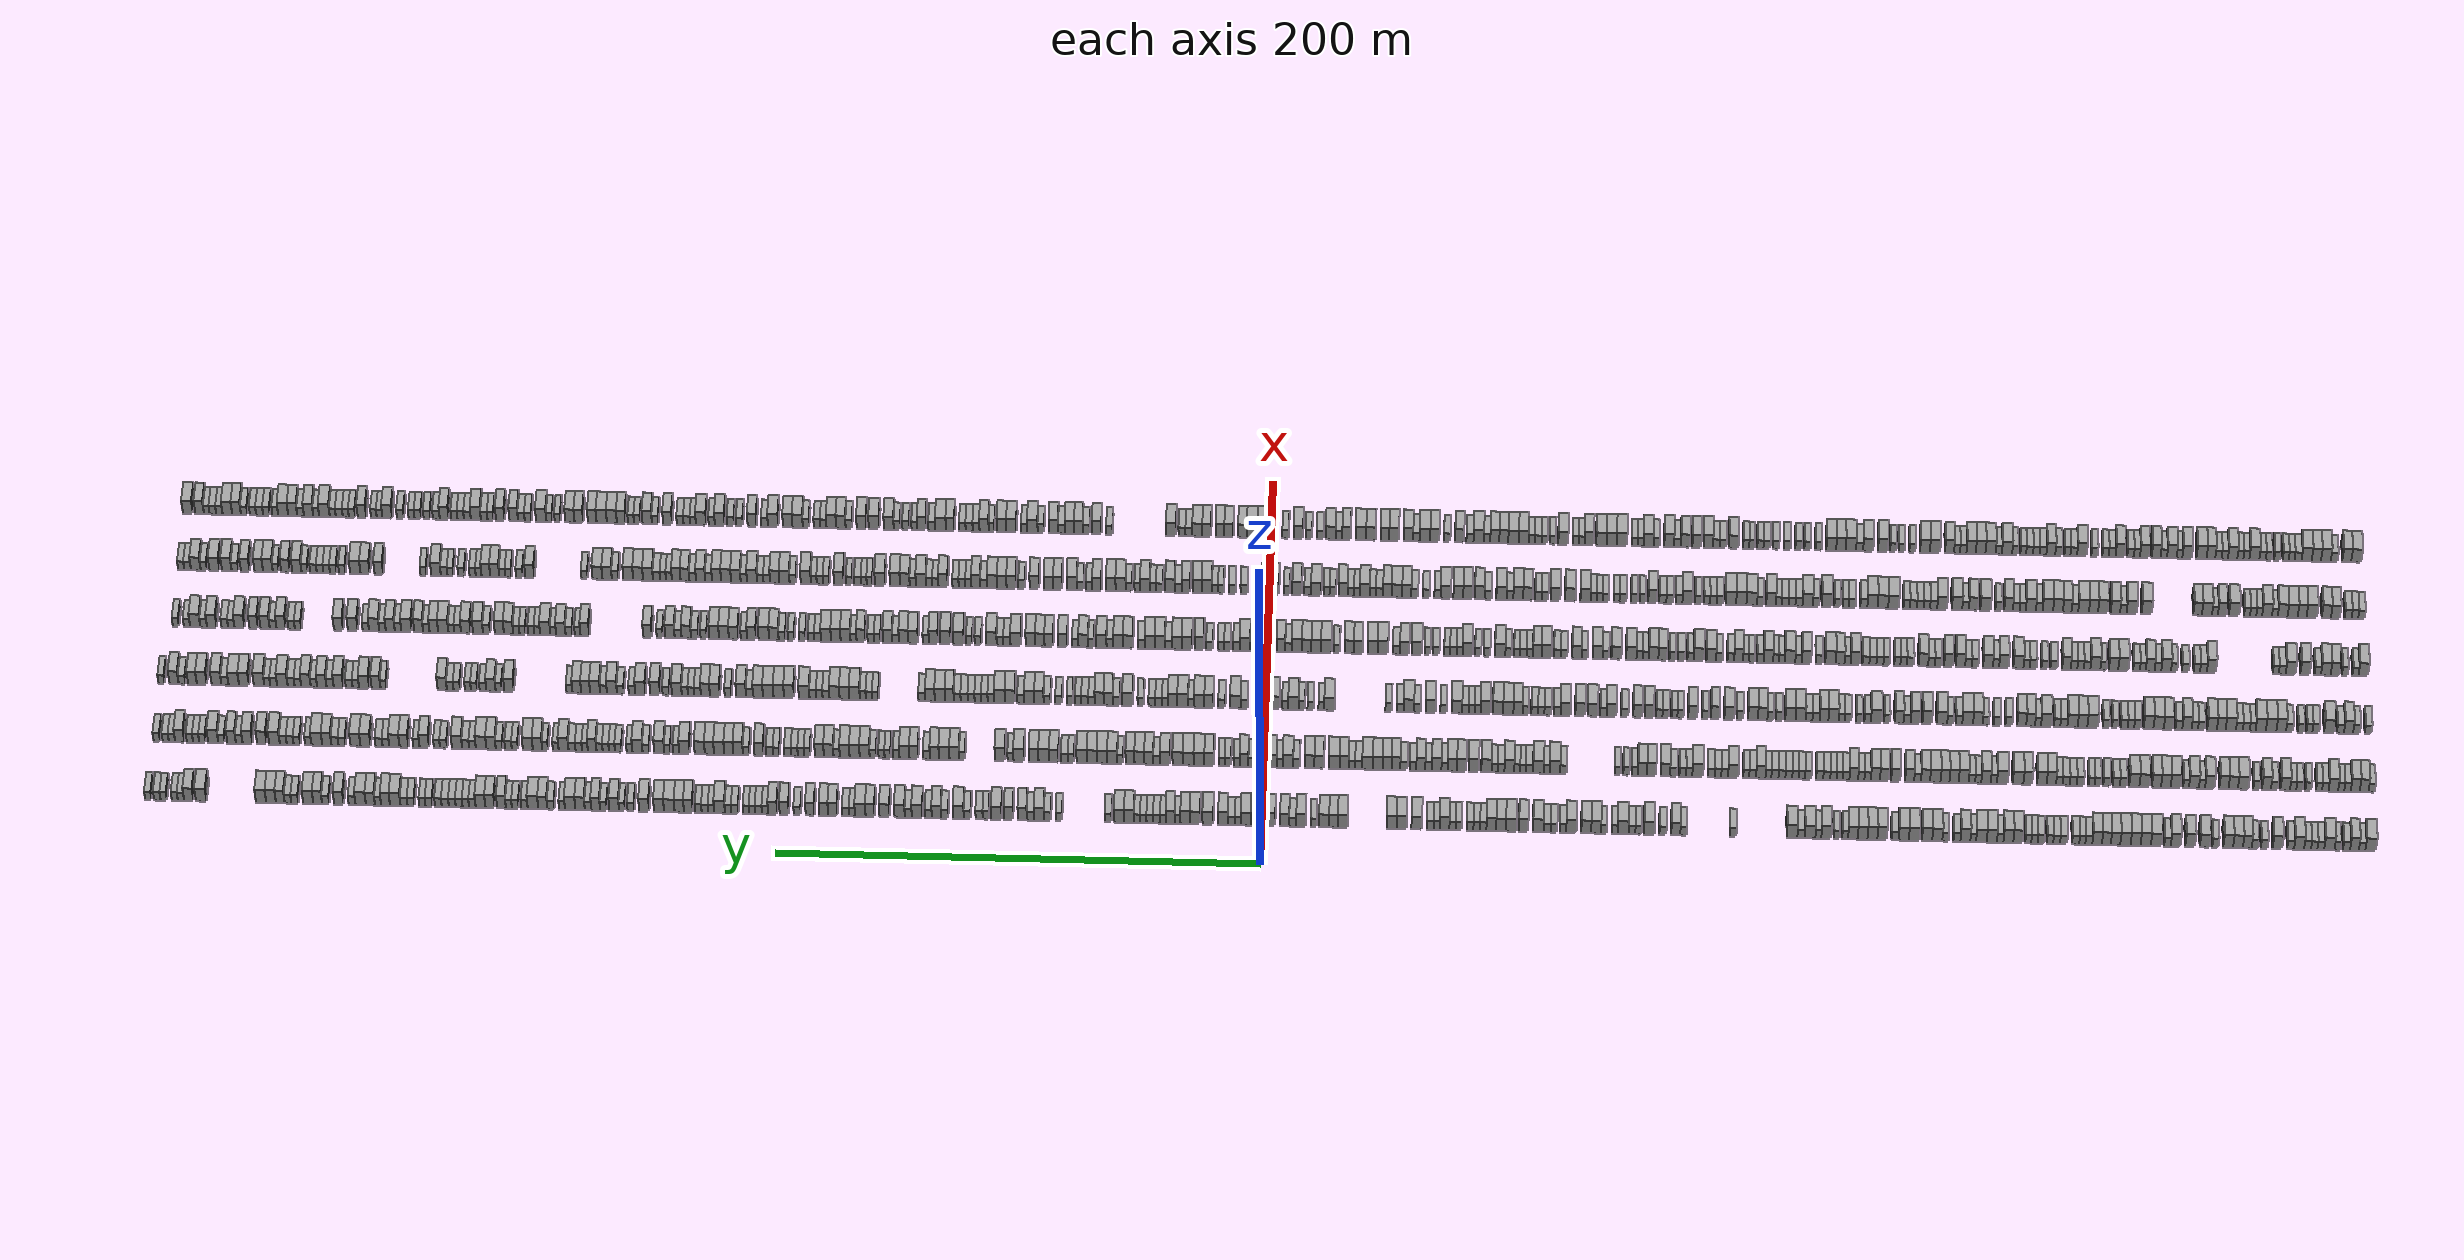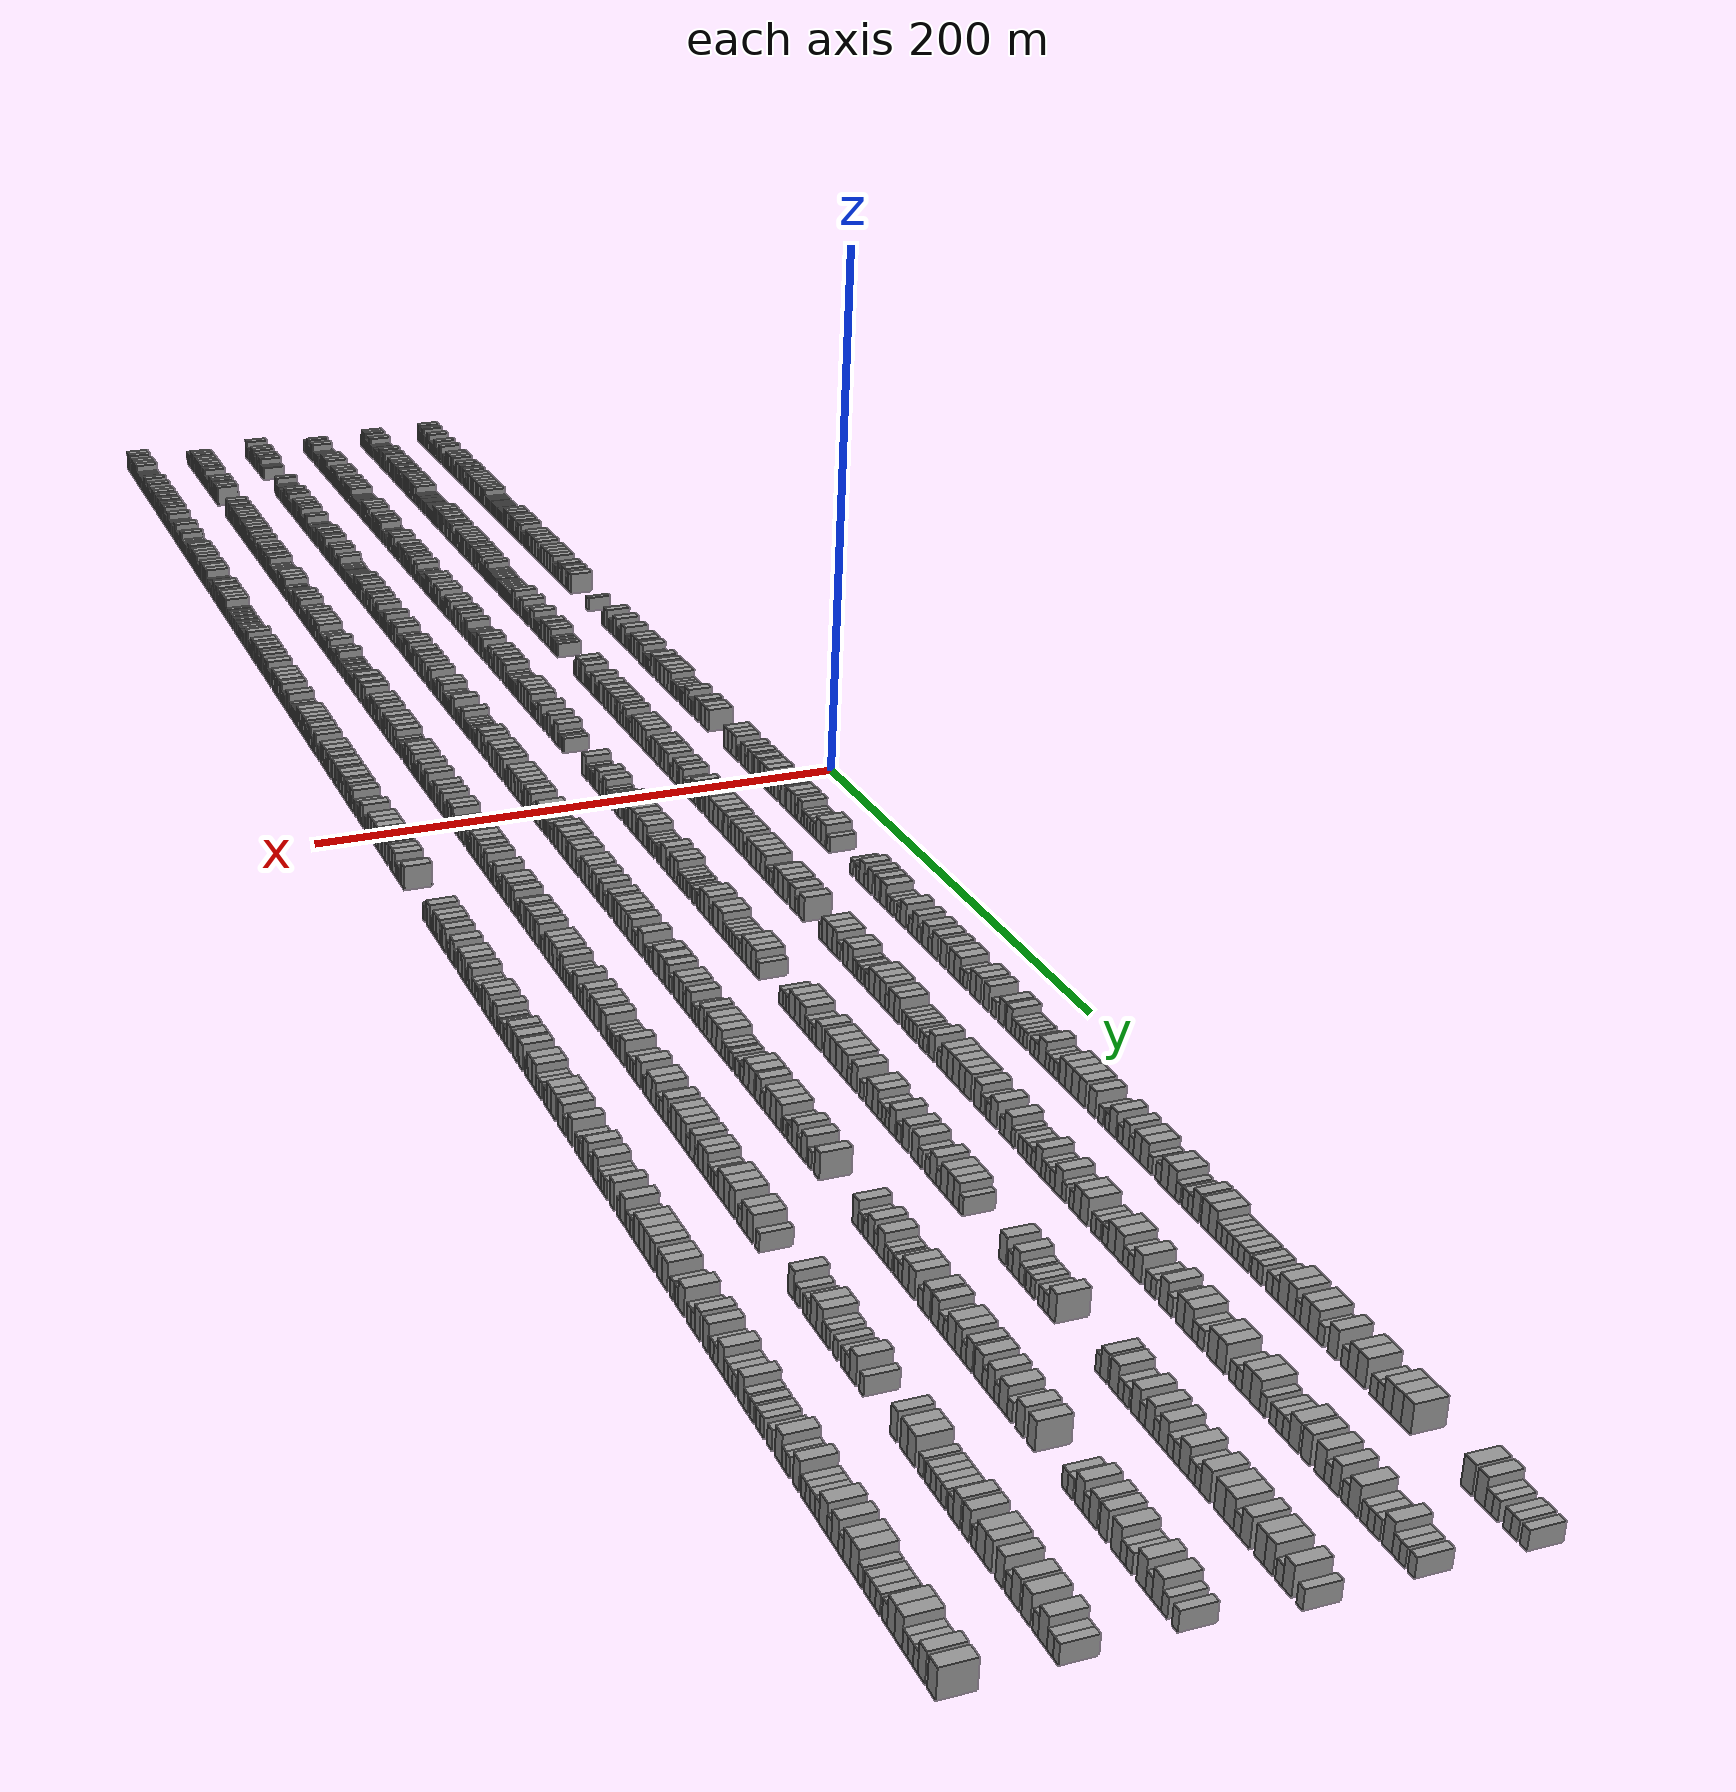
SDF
<sdf version="1.6">
 <world name="default">
  <scene>
   <sky><clouds><speed>12</speed></clouds></sky>
   <ambient>0.4 0.4 0.4 1</ambient>
   <background>0.7 0.7 0.7 1</background>
   <shadows>1</shadows>
  </scene>
  <gravity>0 0 -9.8066</gravity>
  <magnetic_field>6e-06 2.3e-05 -4.2e-05</magnetic_field>
  <physics default="0" name="default_physics" type="ode">
   <ode>
    <solver>
     <type>quick</type>
     <iters>10</iters>
     <sor>1.0</sor>
     <use_dynamic_moi_rescaling>0</use_dynamic_moi_rescaling>
    </solver>
    <constraints>
     <cfm>0</cfm>
     <erp>0.2</erp>
     <contact_max_correcting_vel>100</contact_max_correcting_vel>
     <contact_surface_layer>0.001</contact_surface_layer>
    </constraints>
   </ode>
   <max_step_size>0.004</max_step_size>
   <real_time_factor>1</real_time_factor>
   <real_time_update_rate>250</real_time_update_rate>
  </physics>
  <light name="sun" type="directional">
   <pose>0 0 10 0 0 0</pose>
   <diffuse>0.8 0.8 0.8 1</diffuse>
   <specular>0.2 0.2 0.2 1</specular>
   <attenuation>
    <range>1000</range>
    <constant>0.9</constant>
    <linear>0.01</linear>
    <quadratic>0.001</quadratic>
   </attenuation>
   <direction>-0.5 0.1 -0.9</direction>
  </light>
  <model name="building_1">
   <static>1</static>
   <pose>25.0000 -456.8783 0 0.000000 0.000000 0.000000</pose>
   <link name="link">
    <pose>0 0 4.50 0 0 0</pose>
    <collision name="collision"><geometry><box><size>10.0000 4.2434 9.0000</size></box></geometry></collision>
    <visual name="visual">
     <cast_shadows>0</cast_shadows>
     <geometry><box><size>10.0000 4.2434 9.0000</size></box></geometry>
     <material>
      <script>
       <uri>model://grey_wall/materials/scripts</uri>
       <uri>model://grey_wall/materials/textures</uri>
       <name>vrc/grey_wall</name>
      </script>
     </material>
    </visual>
   </link>
  </model>
  <model name="building_2">
   <static>1</static>
   <pose>25.0000 -453.4162 0 0.000000 0.000000 0.000000</pose>
   <link name="link">
    <pose>0 0 3.00 0 0 0</pose>
    <collision name="collision"><geometry><box><size>10.0000 2.6807 6.0000</size></box></geometry></collision>
    <visual name="visual">
     <cast_shadows>0</cast_shadows>
     <geometry><box><size>10.0000 2.6807 6.0000</size></box></geometry>
     <material>
      <script>
       <uri>model://grey_wall/materials/scripts</uri>
       <uri>model://grey_wall/materials/textures</uri>
       <name>vrc/grey_wall</name>
      </script>
     </material>
    </visual>
   </link>
  </model>
  <model name="building_3">
   <static>1</static>
   <pose>25.0000 -450.2645 0 0.000000 0.000000 0.000000</pose>
   <link name="link">
    <pose>0 0 4.50 0 0 0</pose>
    <collision name="collision"><geometry><box><size>10.0000 3.6228 9.0000</size></box></geometry></collision>
    <visual name="visual">
     <cast_shadows>0</cast_shadows>
     <geometry><box><size>10.0000 3.6228 9.0000</size></box></geometry>
     <material>
      <script>
       <uri>model://grey_wall/materials/scripts</uri>
       <uri>model://grey_wall/materials/textures</uri>
       <name>vrc/grey_wall</name>
      </script>
     </material>
    </visual>
   </link>
  </model>
  <model name="building_4">
   <static>1</static>
   <pose>25.0000 -446.9967 0 0.000000 0.000000 0.000000</pose>
   <link name="link">
    <pose>0 0 3.00 0 0 0</pose>
    <collision name="collision"><geometry><box><size>10.0000 2.9128 6.0000</size></box></geometry></collision>
    <visual name="visual">
     <cast_shadows>0</cast_shadows>
     <geometry><box><size>10.0000 2.9128 6.0000</size></box></geometry>
     <material>
      <script>
       <uri>model://grey_wall/materials/scripts</uri>
       <uri>model://grey_wall/materials/textures</uri>
       <name>vrc/grey_wall</name>
      </script>
     </material>
    </visual>
   </link>
  </model>
  <model name="building_5">
   <static>1</static>
   <pose>25.0000 -443.2996 0 0.000000 0.000000 0.000000</pose>
   <link name="link">
    <pose>0 0 3.00 0 0 0</pose>
    <collision name="collision"><geometry><box><size>10.0000 2.4815 6.0000</size></box></geometry></collision>
    <visual name="visual">
     <cast_shadows>0</cast_shadows>
     <geometry><box><size>10.0000 2.4815 6.0000</size></box></geometry>
     <material>
      <script>
       <uri>model://grey_wall/materials/scripts</uri>
       <uri>model://grey_wall/materials/textures</uri>
       <name>vrc/grey_wall</name>
      </script>
     </material>
    </visual>
   </link>
  </model>
  <model name="building_6">
   <static>1</static>
   <pose>25.0000 -439.9351 0 0.000000 0.000000 0.000000</pose>
   <link name="link">
    <pose>0 0 4.50 0 0 0</pose>
    <collision name="collision"><geometry><box><size>10.0000 4.2474 9.0000</size></box></geometry></collision>
    <visual name="visual">
     <cast_shadows>0</cast_shadows>
     <geometry><box><size>10.0000 4.2474 9.0000</size></box></geometry>
     <material>
      <script>
       <uri>model://grey_wall/materials/scripts</uri>
       <uri>model://grey_wall/materials/textures</uri>
       <name>vrc/grey_wall</name>
      </script>
     </material>
    </visual>
   </link>
  </model>
  <model name="building_7">
   <static>1</static>
   <pose>25.0000 -436.4118 0 0.000000 0.000000 0.000000</pose>
   <link name="link">
    <pose>0 0 3.00 0 0 0</pose>
    <collision name="collision"><geometry><box><size>10.0000 2.7993 6.0000</size></box></geometry></collision>
    <visual name="visual">
     <cast_shadows>0</cast_shadows>
     <geometry><box><size>10.0000 2.7993 6.0000</size></box></geometry>
     <material>
      <script>
       <uri>model://grey_wall/materials/scripts</uri>
       <uri>model://grey_wall/materials/textures</uri>
       <name>vrc/grey_wall</name>
      </script>
     </material>
    </visual>
   </link>
  </model>
  <model name="building_8">
   <static>1</static>
   <pose>25.0000 -433.7021 0 0.000000 0.000000 0.000000</pose>
   <link name="link">
    <pose>0 0 3.00 0 0 0</pose>
    <collision name="collision"><geometry><box><size>10.0000 2.6202 6.0000</size></box></geometry></collision>
    <visual name="visual">
     <cast_shadows>0</cast_shadows>
     <geometry><box><size>10.0000 2.6202 6.0000</size></box></geometry>
     <material>
      <script>
       <uri>model://grey_wall/materials/scripts</uri>
       <uri>model://grey_wall/materials/textures</uri>
       <name>vrc/grey_wall</name>
      </script>
     </material>
    </visual>
   </link>
  </model>
  <model name="building_9">
   <static>1</static>
   <pose>25.0000 -430.9677 0 0.000000 0.000000 0.000000</pose>
   <link name="link">
    <pose>0 0 3.00 0 0 0</pose>
    <collision name="collision"><geometry><box><size>10.0000 2.8485 6.0000</size></box></geometry></collision>
    <visual name="visual">
     <cast_shadows>0</cast_shadows>
     <geometry><box><size>10.0000 2.8485 6.0000</size></box></geometry>
     <material>
      <script>
       <uri>model://grey_wall/materials/scripts</uri>
       <uri>model://grey_wall/materials/textures</uri>
       <name>vrc/grey_wall</name>
      </script>
     </material>
    </visual>
   </link>
  </model>
  <model name="building_10">
   <static>1</static>
   <pose>25.0000 -427.4785 0 0.000000 0.000000 0.000000</pose>
   <link name="link">
    <pose>0 0 4.50 0 0 0</pose>
    <collision name="collision"><geometry><box><size>10.0000 4.1300 9.0000</size></box></geometry></collision>
    <visual name="visual">
     <cast_shadows>0</cast_shadows>
     <geometry><box><size>10.0000 4.1300 9.0000</size></box></geometry>
     <material>
      <script>
       <uri>model://grey_wall/materials/scripts</uri>
       <uri>model://grey_wall/materials/textures</uri>
       <name>vrc/grey_wall</name>
      </script>
     </material>
    </visual>
   </link>
  </model>
  <model name="building_11">
   <static>1</static>
   <pose>25.0000 -423.9754 0 0.000000 0.000000 0.000000</pose>
   <link name="link">
    <pose>0 0 3.00 0 0 0</pose>
    <collision name="collision"><geometry><box><size>10.0000 2.8760 6.0000</size></box></geometry></collision>
    <visual name="visual">
     <cast_shadows>0</cast_shadows>
     <geometry><box><size>10.0000 2.8760 6.0000</size></box></geometry>
     <material>
      <script>
       <uri>model://grey_wall/materials/scripts</uri>
       <uri>model://grey_wall/materials/textures</uri>
       <name>vrc/grey_wall</name>
      </script>
     </material>
    </visual>
   </link>
  </model>
  <model name="building_12">
   <static>1</static>
   <pose>25.0000 -418.5419 0 0.000000 0.000000 0.000000</pose>
   <link name="link">
    <pose>0 0 4.50 0 0 0</pose>
    <collision name="collision"><geometry><box><size>10.0000 3.9910 9.0000</size></box></geometry></collision>
    <visual name="visual">
     <cast_shadows>0</cast_shadows>
     <geometry><box><size>10.0000 3.9910 9.0000</size></box></geometry>
     <material>
      <script>
       <uri>model://grey_wall/materials/scripts</uri>
       <uri>model://grey_wall/materials/textures</uri>
       <name>vrc/grey_wall</name>
      </script>
     </material>
    </visual>
   </link>
  </model>
  <model name="building_13">
   <static>1</static>
   <pose>25.0000 -413.1320 0 0.000000 0.000000 0.000000</pose>
   <link name="link">
    <pose>0 0 3.00 0 0 0</pose>
    <collision name="collision"><geometry><box><size>10.0000 2.8289 6.0000</size></box></geometry></collision>
    <visual name="visual">
     <cast_shadows>0</cast_shadows>
     <geometry><box><size>10.0000 2.8289 6.0000</size></box></geometry>
     <material>
      <script>
       <uri>model://grey_wall/materials/scripts</uri>
       <uri>model://grey_wall/materials/textures</uri>
       <name>vrc/grey_wall</name>
      </script>
     </material>
    </visual>
   </link>
  </model>
  <model name="building_14">
   <static>1</static>
   <pose>25.0000 -409.3361 0 0.000000 0.000000 0.000000</pose>
   <link name="link">
    <pose>0 0 3.00 0 0 0</pose>
    <collision name="collision"><geometry><box><size>10.0000 2.7627 6.0000</size></box></geometry></collision>
    <visual name="visual">
     <cast_shadows>0</cast_shadows>
     <geometry><box><size>10.0000 2.7627 6.0000</size></box></geometry>
     <material>
      <script>
       <uri>model://grey_wall/materials/scripts</uri>
       <uri>model://grey_wall/materials/textures</uri>
       <name>vrc/grey_wall</name>
      </script>
     </material>
    </visual>
   </link>
  </model>
  <model name="building_15">
   <static>1</static>
   <pose>25.0000 -406.1360 0 0.000000 0.000000 0.000000</pose>
   <link name="link">
    <pose>0 0 4.50 0 0 0</pose>
    <collision name="collision"><geometry><box><size>10.0000 3.6375 9.0000</size></box></geometry></collision>
    <visual name="visual">
     <cast_shadows>0</cast_shadows>
     <geometry><box><size>10.0000 3.6375 9.0000</size></box></geometry>
     <material>
      <script>
       <uri>model://grey_wall/materials/scripts</uri>
       <uri>model://grey_wall/materials/textures</uri>
       <name>vrc/grey_wall</name>
      </script>
     </material>
    </visual>
   </link>
  </model>
  <model name="building_16">
   <static>1</static>
   <pose>25.0000 -402.2906 0 0.000000 0.000000 0.000000</pose>
   <link name="link">
    <pose>0 0 4.50 0 0 0</pose>
    <collision name="collision"><geometry><box><size>10.0000 4.0534 9.0000</size></box></geometry></collision>
    <visual name="visual">
     <cast_shadows>0</cast_shadows>
     <geometry><box><size>10.0000 4.0534 9.0000</size></box></geometry>
     <material>
      <script>
       <uri>model://grey_wall/materials/scripts</uri>
       <uri>model://grey_wall/materials/textures</uri>
       <name>vrc/grey_wall</name>
      </script>
     </material>
    </visual>
   </link>
  </model>
  <model name="building_17">
   <static>1</static>
   <pose>25.0000 -398.2564 0 0.000000 0.000000 0.000000</pose>
   <link name="link">
    <pose>0 0 4.50 0 0 0</pose>
    <collision name="collision"><geometry><box><size>10.0000 4.0150 9.0000</size></box></geometry></collision>
    <visual name="visual">
     <cast_shadows>0</cast_shadows>
     <geometry><box><size>10.0000 4.0150 9.0000</size></box></geometry>
     <material>
      <script>
       <uri>model://grey_wall/materials/scripts</uri>
       <uri>model://grey_wall/materials/textures</uri>
       <name>vrc/grey_wall</name>
      </script>
     </material>
    </visual>
   </link>
  </model>
  <model name="building_18">
   <static>1</static>
   <pose>25.0000 -393.0043 0 0.000000 0.000000 0.000000</pose>
   <link name="link">
    <pose>0 0 3.00 0 0 0</pose>
    <collision name="collision"><geometry><box><size>10.0000 2.4893 6.0000</size></box></geometry></collision>
    <visual name="visual">
     <cast_shadows>0</cast_shadows>
     <geometry><box><size>10.0000 2.4893 6.0000</size></box></geometry>
     <material>
      <script>
       <uri>model://grey_wall/materials/scripts</uri>
       <uri>model://grey_wall/materials/textures</uri>
       <name>vrc/grey_wall</name>
      </script>
     </material>
    </visual>
   </link>
  </model>
  <model name="building_19">
   <static>1</static>
   <pose>25.0000 -388.6606 0 0.000000 0.000000 0.000000</pose>
   <link name="link">
    <pose>0 0 4.50 0 0 0</pose>
    <collision name="collision"><geometry><box><size>10.0000 4.1980 9.0000</size></box></geometry></collision>
    <visual name="visual">
     <cast_shadows>0</cast_shadows>
     <geometry><box><size>10.0000 4.1980 9.0000</size></box></geometry>
     <material>
      <script>
       <uri>model://grey_wall/materials/scripts</uri>
       <uri>model://grey_wall/materials/textures</uri>
       <name>vrc/grey_wall</name>
      </script>
     </material>
    </visual>
   </link>
  </model>
  <model name="building_20">
   <static>1</static>
   <pose>25.0000 -382.5770 0 0.000000 0.000000 0.000000</pose>
   <link name="link">
    <pose>0 0 4.50 0 0 0</pose>
    <collision name="collision"><geometry><box><size>10.0000 3.9693 9.0000</size></box></geometry></collision>
    <visual name="visual">
     <cast_shadows>0</cast_shadows>
     <geometry><box><size>10.0000 3.9693 9.0000</size></box></geometry>
     <material>
      <script>
       <uri>model://grey_wall/materials/scripts</uri>
       <uri>model://grey_wall/materials/textures</uri>
       <name>vrc/grey_wall</name>
      </script>
     </material>
    </visual>
   </link>
  </model>
  <model name="building_21">
   <static>1</static>
   <pose>25.0000 -376.6171 0 0.000000 0.000000 0.000000</pose>
   <link name="link">
    <pose>0 0 4.50 0 0 0</pose>
    <collision name="collision"><geometry><box><size>10.0000 3.9505 9.0000</size></box></geometry></collision>
    <visual name="visual">
     <cast_shadows>0</cast_shadows>
     <geometry><box><size>10.0000 3.9505 9.0000</size></box></geometry>
     <material>
      <script>
       <uri>model://grey_wall/materials/scripts</uri>
       <uri>model://grey_wall/materials/textures</uri>
       <name>vrc/grey_wall</name>
      </script>
     </material>
    </visual>
   </link>
  </model>
  <model name="building_22">
   <static>1</static>
   <pose>25.0000 -373.2767 0 0.000000 0.000000 0.000000</pose>
   <link name="link">
    <pose>0 0 3.00 0 0 0</pose>
    <collision name="collision"><geometry><box><size>10.0000 2.7302 6.0000</size></box></geometry></collision>
    <visual name="visual">
     <cast_shadows>0</cast_shadows>
     <geometry><box><size>10.0000 2.7302 6.0000</size></box></geometry>
     <material>
      <script>
       <uri>model://grey_wall/materials/scripts</uri>
       <uri>model://grey_wall/materials/textures</uri>
       <name>vrc/grey_wall</name>
      </script>
     </material>
    </visual>
   </link>
  </model>
  <model name="building_23">
   <static>1</static>
   <pose>25.0000 -368.6682 0 0.000000 0.000000 0.000000</pose>
   <link name="link">
    <pose>0 0 4.50 0 0 0</pose>
    <collision name="collision"><geometry><box><size>10.0000 4.4869 9.0000</size></box></geometry></collision>
    <visual name="visual">
     <cast_shadows>0</cast_shadows>
     <geometry><box><size>10.0000 4.4869 9.0000</size></box></geometry>
     <material>
      <script>
       <uri>model://grey_wall/materials/scripts</uri>
       <uri>model://grey_wall/materials/textures</uri>
       <name>vrc/grey_wall</name>
      </script>
     </material>
    </visual>
   </link>
  </model>
  <model name="building_24">
   <static>1</static>
   <pose>25.0000 -364.3045 0 0.000000 0.000000 0.000000</pose>
   <link name="link">
    <pose>0 0 4.50 0 0 0</pose>
    <collision name="collision"><geometry><box><size>10.0000 4.2405 9.0000</size></box></geometry></collision>
    <visual name="visual">
     <cast_shadows>0</cast_shadows>
     <geometry><box><size>10.0000 4.2405 9.0000</size></box></geometry>
     <material>
      <script>
       <uri>model://grey_wall/materials/scripts</uri>
       <uri>model://grey_wall/materials/textures</uri>
       <name>vrc/grey_wall</name>
      </script>
     </material>
    </visual>
   </link>
  </model>
  <model name="building_25">
   <static>1</static>
   <pose>25.0000 -360.1226 0 0.000000 0.000000 0.000000</pose>
   <link name="link">
    <pose>0 0 4.50 0 0 0</pose>
    <collision name="collision"><geometry><box><size>10.0000 4.1233 9.0000</size></box></geometry></collision>
    <visual name="visual">
     <cast_shadows>0</cast_shadows>
     <geometry><box><size>10.0000 4.1233 9.0000</size></box></geometry>
     <material>
      <script>
       <uri>model://grey_wall/materials/scripts</uri>
       <uri>model://grey_wall/materials/textures</uri>
       <name>vrc/grey_wall</name>
      </script>
     </material>
    </visual>
   </link>
  </model>
  <model name="building_26">
   <static>1</static>
   <pose>25.0000 -355.9413 0 0.000000 0.000000 0.000000</pose>
   <link name="link">
    <pose>0 0 4.50 0 0 0</pose>
    <collision name="collision"><geometry><box><size>10.0000 4.2394 9.0000</size></box></geometry></collision>
    <visual name="visual">
     <cast_shadows>0</cast_shadows>
     <geometry><box><size>10.0000 4.2394 9.0000</size></box></geometry>
     <material>
      <script>
       <uri>model://grey_wall/materials/scripts</uri>
       <uri>model://grey_wall/materials/textures</uri>
       <name>vrc/grey_wall</name>
      </script>
     </material>
    </visual>
   </link>
  </model>
  <model name="building_27">
   <static>1</static>
   <pose>25.0000 -351.8706 0 0.000000 0.000000 0.000000</pose>
   <link name="link">
    <pose>0 0 4.50 0 0 0</pose>
    <collision name="collision"><geometry><box><size>10.0000 3.9019 9.0000</size></box></geometry></collision>
    <visual name="visual">
     <cast_shadows>0</cast_shadows>
     <geometry><box><size>10.0000 3.9019 9.0000</size></box></geometry>
     <material>
      <script>
       <uri>model://grey_wall/materials/scripts</uri>
       <uri>model://grey_wall/materials/textures</uri>
       <name>vrc/grey_wall</name>
      </script>
     </material>
    </visual>
   </link>
  </model>
  <model name="building_28">
   <static>1</static>
   <pose>25.0000 -348.0897 0 0.000000 0.000000 0.000000</pose>
   <link name="link">
    <pose>0 0 4.50 0 0 0</pose>
    <collision name="collision"><geometry><box><size>10.0000 3.6598 9.0000</size></box></geometry></collision>
    <visual name="visual">
     <cast_shadows>0</cast_shadows>
     <geometry><box><size>10.0000 3.6598 9.0000</size></box></geometry>
     <material>
      <script>
       <uri>model://grey_wall/materials/scripts</uri>
       <uri>model://grey_wall/materials/textures</uri>
       <name>vrc/grey_wall</name>
      </script>
     </material>
    </visual>
   </link>
  </model>
  <model name="building_29">
   <static>1</static>
   <pose>25.0000 -344.2783 0 0.000000 0.000000 0.000000</pose>
   <link name="link">
    <pose>0 0 4.50 0 0 0</pose>
    <collision name="collision"><geometry><box><size>10.0000 3.9630 9.0000</size></box></geometry></collision>
    <visual name="visual">
     <cast_shadows>0</cast_shadows>
     <geometry><box><size>10.0000 3.9630 9.0000</size></box></geometry>
     <material>
      <script>
       <uri>model://grey_wall/materials/scripts</uri>
       <uri>model://grey_wall/materials/textures</uri>
       <name>vrc/grey_wall</name>
      </script>
     </material>
    </visual>
   </link>
  </model>
  <model name="building_30">
   <static>1</static>
   <pose>25.0000 -340.8837 0 0.000000 0.000000 0.000000</pose>
   <link name="link">
    <pose>0 0 3.00 0 0 0</pose>
    <collision name="collision"><geometry><box><size>10.0000 2.8261 6.0000</size></box></geometry></collision>
    <visual name="visual">
     <cast_shadows>0</cast_shadows>
     <geometry><box><size>10.0000 2.8261 6.0000</size></box></geometry>
     <material>
      <script>
       <uri>model://grey_wall/materials/scripts</uri>
       <uri>model://grey_wall/materials/textures</uri>
       <name>vrc/grey_wall</name>
      </script>
     </material>
    </visual>
   </link>
  </model>
  <model name="building_31">
   <static>1</static>
   <pose>25.0000 -338.2018 0 0.000000 0.000000 0.000000</pose>
   <link name="link">
    <pose>0 0 3.00 0 0 0</pose>
    <collision name="collision"><geometry><box><size>10.0000 2.5377 6.0000</size></box></geometry></collision>
    <visual name="visual">
     <cast_shadows>0</cast_shadows>
     <geometry><box><size>10.0000 2.5377 6.0000</size></box></geometry>
     <material>
      <script>
       <uri>model://grey_wall/materials/scripts</uri>
       <uri>model://grey_wall/materials/textures</uri>
       <name>vrc/grey_wall</name>
      </script>
     </material>
    </visual>
   </link>
  </model>
  <model name="building_32">
   <static>1</static>
   <pose>25.0000 -335.4425 0 0.000000 0.000000 0.000000</pose>
   <link name="link">
    <pose>0 0 3.00 0 0 0</pose>
    <collision name="collision"><geometry><box><size>10.0000 2.9809 6.0000</size></box></geometry></collision>
    <visual name="visual">
     <cast_shadows>0</cast_shadows>
     <geometry><box><size>10.0000 2.9809 6.0000</size></box></geometry>
     <material>
      <script>
       <uri>model://grey_wall/materials/scripts</uri>
       <uri>model://grey_wall/materials/textures</uri>
       <name>vrc/grey_wall</name>
      </script>
     </material>
    </visual>
   </link>
  </model>
  <model name="building_33">
   <static>1</static>
   <pose>25.0000 -330.4921 0 0.000000 0.000000 0.000000</pose>
   <link name="link">
    <pose>0 0 3.00 0 0 0</pose>
    <collision name="collision"><geometry><box><size>10.0000 2.9199 6.0000</size></box></geometry></collision>
    <visual name="visual">
     <cast_shadows>0</cast_shadows>
     <geometry><box><size>10.0000 2.9199 6.0000</size></box></geometry>
     <material>
      <script>
       <uri>model://grey_wall/materials/scripts</uri>
       <uri>model://grey_wall/materials/textures</uri>
       <name>vrc/grey_wall</name>
      </script>
     </material>
    </visual>
   </link>
  </model>
  <model name="building_34">
   <static>1</static>
   <pose>25.0000 -327.6119 0 0.000000 0.000000 0.000000</pose>
   <link name="link">
    <pose>0 0 3.00 0 0 0</pose>
    <collision name="collision"><geometry><box><size>10.0000 2.8404 6.0000</size></box></geometry></collision>
    <visual name="visual">
     <cast_shadows>0</cast_shadows>
     <geometry><box><size>10.0000 2.8404 6.0000</size></box></geometry>
     <material>
      <script>
       <uri>model://grey_wall/materials/scripts</uri>
       <uri>model://grey_wall/materials/textures</uri>
       <name>vrc/grey_wall</name>
      </script>
     </material>
    </visual>
   </link>
  </model>
  <model name="building_35">
   <static>1</static>
   <pose>25.0000 -324.8890 0 0.000000 0.000000 0.000000</pose>
   <link name="link">
    <pose>0 0 3.00 0 0 0</pose>
    <collision name="collision"><geometry><box><size>10.0000 2.6055 6.0000</size></box></geometry></collision>
    <visual name="visual">
     <cast_shadows>0</cast_shadows>
     <geometry><box><size>10.0000 2.6055 6.0000</size></box></geometry>
     <material>
      <script>
       <uri>model://grey_wall/materials/scripts</uri>
       <uri>model://grey_wall/materials/textures</uri>
       <name>vrc/grey_wall</name>
      </script>
     </material>
    </visual>
   </link>
  </model>
  <model name="building_36">
   <static>1</static>
   <pose>25.0000 -321.1808 0 0.000000 0.000000 0.000000</pose>
   <link name="link">
    <pose>0 0 3.00 0 0 0</pose>
    <collision name="collision"><geometry><box><size>10.0000 2.8110 6.0000</size></box></geometry></collision>
    <visual name="visual">
     <cast_shadows>0</cast_shadows>
     <geometry><box><size>10.0000 2.8110 6.0000</size></box></geometry>
     <material>
      <script>
       <uri>model://grey_wall/materials/scripts</uri>
       <uri>model://grey_wall/materials/textures</uri>
       <name>vrc/grey_wall</name>
      </script>
     </material>
    </visual>
   </link>
  </model>
  <model name="building_37">
   <static>1</static>
   <pose>25.0000 -318.4641 0 0.000000 0.000000 0.000000</pose>
   <link name="link">
    <pose>0 0 3.00 0 0 0</pose>
    <collision name="collision"><geometry><box><size>10.0000 2.6223 6.0000</size></box></geometry></collision>
    <visual name="visual">
     <cast_shadows>0</cast_shadows>
     <geometry><box><size>10.0000 2.6223 6.0000</size></box></geometry>
     <material>
      <script>
       <uri>model://grey_wall/materials/scripts</uri>
       <uri>model://grey_wall/materials/textures</uri>
       <name>vrc/grey_wall</name>
      </script>
     </material>
    </visual>
   </link>
  </model>
  <model name="building_38">
   <static>1</static>
   <pose>25.0000 -315.9210 0 0.000000 0.000000 0.000000</pose>
   <link name="link">
    <pose>0 0 3.00 0 0 0</pose>
    <collision name="collision"><geometry><box><size>10.0000 2.4640 6.0000</size></box></geometry></collision>
    <visual name="visual">
     <cast_shadows>0</cast_shadows>
     <geometry><box><size>10.0000 2.4640 6.0000</size></box></geometry>
     <material>
      <script>
       <uri>model://grey_wall/materials/scripts</uri>
       <uri>model://grey_wall/materials/textures</uri>
       <name>vrc/grey_wall</name>
      </script>
     </material>
    </visual>
   </link>
  </model>
  <model name="building_39">
   <static>1</static>
   <pose>25.0000 -311.7284 0 0.000000 0.000000 0.000000</pose>
   <link name="link">
    <pose>0 0 4.50 0 0 0</pose>
    <collision name="collision"><geometry><box><size>10.0000 3.9211 9.0000</size></box></geometry></collision>
    <visual name="visual">
     <cast_shadows>0</cast_shadows>
     <geometry><box><size>10.0000 3.9211 9.0000</size></box></geometry>
     <material>
      <script>
       <uri>model://grey_wall/materials/scripts</uri>
       <uri>model://grey_wall/materials/textures</uri>
       <name>vrc/grey_wall</name>
      </script>
     </material>
    </visual>
   </link>
  </model>
  <model name="building_40">
   <static>1</static>
   <pose>25.0000 -307.7349 0 0.000000 0.000000 0.000000</pose>
   <link name="link">
    <pose>0 0 4.50 0 0 0</pose>
    <collision name="collision"><geometry><box><size>10.0000 4.0659 9.0000</size></box></geometry></collision>
    <visual name="visual">
     <cast_shadows>0</cast_shadows>
     <geometry><box><size>10.0000 4.0659 9.0000</size></box></geometry>
     <material>
      <script>
       <uri>model://grey_wall/materials/scripts</uri>
       <uri>model://grey_wall/materials/textures</uri>
       <name>vrc/grey_wall</name>
      </script>
     </material>
    </visual>
   </link>
  </model>
  <model name="building_41">
   <static>1</static>
   <pose>25.0000 -304.3596 0 0.000000 0.000000 0.000000</pose>
   <link name="link">
    <pose>0 0 3.00 0 0 0</pose>
    <collision name="collision"><geometry><box><size>10.0000 2.6848 6.0000</size></box></geometry></collision>
    <visual name="visual">
     <cast_shadows>0</cast_shadows>
     <geometry><box><size>10.0000 2.6848 6.0000</size></box></geometry>
     <material>
      <script>
       <uri>model://grey_wall/materials/scripts</uri>
       <uri>model://grey_wall/materials/textures</uri>
       <name>vrc/grey_wall</name>
      </script>
     </material>
    </visual>
   </link>
  </model>
  <model name="building_42">
   <static>1</static>
   <pose>25.0000 -300.9014 0 0.000000 0.000000 0.000000</pose>
   <link name="link">
    <pose>0 0 4.50 0 0 0</pose>
    <collision name="collision"><geometry><box><size>10.0000 4.2315 9.0000</size></box></geometry></collision>
    <visual name="visual">
     <cast_shadows>0</cast_shadows>
     <geometry><box><size>10.0000 4.2315 9.0000</size></box></geometry>
     <material>
      <script>
       <uri>model://grey_wall/materials/scripts</uri>
       <uri>model://grey_wall/materials/textures</uri>
       <name>vrc/grey_wall</name>
      </script>
     </material>
    </visual>
   </link>
  </model>
  <model name="building_43">
   <static>1</static>
   <pose>25.0000 -296.6218 0 0.000000 0.000000 0.000000</pose>
   <link name="link">
    <pose>0 0 4.50 0 0 0</pose>
    <collision name="collision"><geometry><box><size>10.0000 4.3277 9.0000</size></box></geometry></collision>
    <visual name="visual">
     <cast_shadows>0</cast_shadows>
     <geometry><box><size>10.0000 4.3277 9.0000</size></box></geometry>
     <material>
      <script>
       <uri>model://grey_wall/materials/scripts</uri>
       <uri>model://grey_wall/materials/textures</uri>
       <name>vrc/grey_wall</name>
      </script>
     </material>
    </visual>
   </link>
  </model>
  <model name="building_44">
   <static>1</static>
   <pose>25.0000 -293.2491 0 0.000000 0.000000 0.000000</pose>
   <link name="link">
    <pose>0 0 3.00 0 0 0</pose>
    <collision name="collision"><geometry><box><size>10.0000 2.4176 6.0000</size></box></geometry></collision>
    <visual name="visual">
     <cast_shadows>0</cast_shadows>
     <geometry><box><size>10.0000 2.4176 6.0000</size></box></geometry>
     <material>
      <script>
       <uri>model://grey_wall/materials/scripts</uri>
       <uri>model://grey_wall/materials/textures</uri>
       <name>vrc/grey_wall</name>
      </script>
     </material>
    </visual>
   </link>
  </model>
  <model name="building_45">
   <static>1</static>
   <pose>25.0000 -290.0112 0 0.000000 0.000000 0.000000</pose>
   <link name="link">
    <pose>0 0 4.50 0 0 0</pose>
    <collision name="collision"><geometry><box><size>10.0000 4.0582 9.0000</size></box></geometry></collision>
    <visual name="visual">
     <cast_shadows>0</cast_shadows>
     <geometry><box><size>10.0000 4.0582 9.0000</size></box></geometry>
     <material>
      <script>
       <uri>model://grey_wall/materials/scripts</uri>
       <uri>model://grey_wall/materials/textures</uri>
       <name>vrc/grey_wall</name>
      </script>
     </material>
    </visual>
   </link>
  </model>
  <model name="building_46">
   <static>1</static>
   <pose>25.0000 -286.5577 0 0.000000 0.000000 0.000000</pose>
   <link name="link">
    <pose>0 0 3.00 0 0 0</pose>
    <collision name="collision"><geometry><box><size>10.0000 2.8488 6.0000</size></box></geometry></collision>
    <visual name="visual">
     <cast_shadows>0</cast_shadows>
     <geometry><box><size>10.0000 2.8488 6.0000</size></box></geometry>
     <material>
      <script>
       <uri>model://grey_wall/materials/scripts</uri>
       <uri>model://grey_wall/materials/textures</uri>
       <name>vrc/grey_wall</name>
      </script>
     </material>
    </visual>
   </link>
  </model>
  <model name="building_47">
   <static>1</static>
   <pose>25.0000 -281.8318 0 0.000000 0.000000 0.000000</pose>
   <link name="link">
    <pose>0 0 3.00 0 0 0</pose>
    <collision name="collision"><geometry><box><size>10.0000 2.6030 6.0000</size></box></geometry></collision>
    <visual name="visual">
     <cast_shadows>0</cast_shadows>
     <geometry><box><size>10.0000 2.6030 6.0000</size></box></geometry>
     <material>
      <script>
       <uri>model://grey_wall/materials/scripts</uri>
       <uri>model://grey_wall/materials/textures</uri>
       <name>vrc/grey_wall</name>
      </script>
     </material>
    </visual>
   </link>
  </model>
  <model name="building_48">
   <static>1</static>
   <pose>25.0000 -278.4453 0 0.000000 0.000000 0.000000</pose>
   <link name="link">
    <pose>0 0 4.50 0 0 0</pose>
    <collision name="collision"><geometry><box><size>10.0000 4.1701 9.0000</size></box></geometry></collision>
    <visual name="visual">
     <cast_shadows>0</cast_shadows>
     <geometry><box><size>10.0000 4.1701 9.0000</size></box></geometry>
     <material>
      <script>
       <uri>model://grey_wall/materials/scripts</uri>
       <uri>model://grey_wall/materials/textures</uri>
       <name>vrc/grey_wall</name>
      </script>
     </material>
    </visual>
   </link>
  </model>
  <model name="building_49">
   <static>1</static>
   <pose>25.0000 -274.2429 0 0.000000 0.000000 0.000000</pose>
   <link name="link">
    <pose>0 0 4.50 0 0 0</pose>
    <collision name="collision"><geometry><box><size>10.0000 4.2348 9.0000</size></box></geometry></collision>
    <visual name="visual">
     <cast_shadows>0</cast_shadows>
     <geometry><box><size>10.0000 4.2348 9.0000</size></box></geometry>
     <material>
      <script>
       <uri>model://grey_wall/materials/scripts</uri>
       <uri>model://grey_wall/materials/textures</uri>
       <name>vrc/grey_wall</name>
      </script>
     </material>
    </visual>
   </link>
  </model>
  <model name="building_50">
   <static>1</static>
   <pose>25.0000 -268.9126 0 0.000000 0.000000 0.000000</pose>
   <link name="link">
    <pose>0 0 4.50 0 0 0</pose>
    <collision name="collision"><geometry><box><size>10.0000 4.4257 9.0000</size></box></geometry></collision>
    <visual name="visual">
     <cast_shadows>0</cast_shadows>
     <geometry><box><size>10.0000 4.4257 9.0000</size></box></geometry>
     <material>
      <script>
       <uri>model://grey_wall/materials/scripts</uri>
       <uri>model://grey_wall/materials/textures</uri>
       <name>vrc/grey_wall</name>
      </script>
     </material>
    </visual>
   </link>
  </model>
  <model name="building_51">
   <static>1</static>
   <pose>25.0000 -264.6136 0 0.000000 0.000000 0.000000</pose>
   <link name="link">
    <pose>0 0 4.50 0 0 0</pose>
    <collision name="collision"><geometry><box><size>10.0000 4.1723 9.0000</size></box></geometry></collision>
    <visual name="visual">
     <cast_shadows>0</cast_shadows>
     <geometry><box><size>10.0000 4.1723 9.0000</size></box></geometry>
     <material>
      <script>
       <uri>model://grey_wall/materials/scripts</uri>
       <uri>model://grey_wall/materials/textures</uri>
       <name>vrc/grey_wall</name>
      </script>
     </material>
    </visual>
   </link>
  </model>
  <model name="building_52">
   <static>1</static>
   <pose>25.0000 -261.0676 0 0.000000 0.000000 0.000000</pose>
   <link name="link">
    <pose>0 0 3.00 0 0 0</pose>
    <collision name="collision"><geometry><box><size>10.0000 2.9197 6.0000</size></box></geometry></collision>
    <visual name="visual">
     <cast_shadows>0</cast_shadows>
     <geometry><box><size>10.0000 2.9197 6.0000</size></box></geometry>
     <material>
      <script>
       <uri>model://grey_wall/materials/scripts</uri>
       <uri>model://grey_wall/materials/textures</uri>
       <name>vrc/grey_wall</name>
      </script>
     </material>
    </visual>
   </link>
  </model>
  <model name="building_53">
   <static>1</static>
   <pose>25.0000 -255.6854 0 0.000000 0.000000 0.000000</pose>
   <link name="link">
    <pose>0 0 4.50 0 0 0</pose>
    <collision name="collision"><geometry><box><size>10.0000 3.8448 9.0000</size></box></geometry></collision>
    <visual name="visual">
     <cast_shadows>0</cast_shadows>
     <geometry><box><size>10.0000 3.8448 9.0000</size></box></geometry>
     <material>
      <script>
       <uri>model://grey_wall/materials/scripts</uri>
       <uri>model://grey_wall/materials/textures</uri>
       <name>vrc/grey_wall</name>
      </script>
     </material>
    </visual>
   </link>
  </model>
  <model name="building_54">
   <static>1</static>
   <pose>25.0000 -251.7251 0 0.000000 0.000000 0.000000</pose>
   <link name="link">
    <pose>0 0 4.50 0 0 0</pose>
    <collision name="collision"><geometry><box><size>10.0000 4.0758 9.0000</size></box></geometry></collision>
    <visual name="visual">
     <cast_shadows>0</cast_shadows>
     <geometry><box><size>10.0000 4.0758 9.0000</size></box></geometry>
     <material>
      <script>
       <uri>model://grey_wall/materials/scripts</uri>
       <uri>model://grey_wall/materials/textures</uri>
       <name>vrc/grey_wall</name>
      </script>
     </material>
    </visual>
   </link>
  </model>
  <model name="building_55">
   <static>1</static>
   <pose>25.0000 -247.6626 0 0.000000 0.000000 0.000000</pose>
   <link name="link">
    <pose>0 0 4.50 0 0 0</pose>
    <collision name="collision"><geometry><box><size>10.0000 4.0492 9.0000</size></box></geometry></collision>
    <visual name="visual">
     <cast_shadows>0</cast_shadows>
     <geometry><box><size>10.0000 4.0492 9.0000</size></box></geometry>
     <material>
      <script>
       <uri>model://grey_wall/materials/scripts</uri>
       <uri>model://grey_wall/materials/textures</uri>
       <name>vrc/grey_wall</name>
      </script>
     </material>
    </visual>
   </link>
  </model>
  <model name="building_56">
   <static>1</static>
   <pose>25.0000 -243.6527 0 0.000000 0.000000 0.000000</pose>
   <link name="link">
    <pose>0 0 4.50 0 0 0</pose>
    <collision name="collision"><geometry><box><size>10.0000 3.9707 9.0000</size></box></geometry></collision>
    <visual name="visual">
     <cast_shadows>0</cast_shadows>
     <geometry><box><size>10.0000 3.9707 9.0000</size></box></geometry>
     <material>
      <script>
       <uri>model://grey_wall/materials/scripts</uri>
       <uri>model://grey_wall/materials/textures</uri>
       <name>vrc/grey_wall</name>
      </script>
     </material>
    </visual>
   </link>
  </model>
  <model name="building_57">
   <static>1</static>
   <pose>25.0000 -240.4575 0 0.000000 0.000000 0.000000</pose>
   <link name="link">
    <pose>0 0 3.00 0 0 0</pose>
    <collision name="collision"><geometry><box><size>10.0000 2.4198 6.0000</size></box></geometry></collision>
    <visual name="visual">
     <cast_shadows>0</cast_shadows>
     <geometry><box><size>10.0000 2.4198 6.0000</size></box></geometry>
     <material>
      <script>
       <uri>model://grey_wall/materials/scripts</uri>
       <uri>model://grey_wall/materials/textures</uri>
       <name>vrc/grey_wall</name>
      </script>
     </material>
    </visual>
   </link>
  </model>
  <model name="building_58">
   <static>1</static>
   <pose>25.0000 -237.0049 0 0.000000 0.000000 0.000000</pose>
   <link name="link">
    <pose>0 0 3.00 0 0 0</pose>
    <collision name="collision"><geometry><box><size>10.0000 2.4852 6.0000</size></box></geometry></collision>
    <visual name="visual">
     <cast_shadows>0</cast_shadows>
     <geometry><box><size>10.0000 2.4852 6.0000</size></box></geometry>
     <material>
      <script>
       <uri>model://grey_wall/materials/scripts</uri>
       <uri>model://grey_wall/materials/textures</uri>
       <name>vrc/grey_wall</name>
      </script>
     </material>
    </visual>
   </link>
  </model>
  <model name="building_59">
   <static>1</static>
   <pose>25.0000 -232.6993 0 0.000000 0.000000 0.000000</pose>
   <link name="link">
    <pose>0 0 4.50 0 0 0</pose>
    <collision name="collision"><geometry><box><size>10.0000 4.1260 9.0000</size></box></geometry></collision>
    <visual name="visual">
     <cast_shadows>0</cast_shadows>
     <geometry><box><size>10.0000 4.1260 9.0000</size></box></geometry>
     <material>
      <script>
       <uri>model://grey_wall/materials/scripts</uri>
       <uri>model://grey_wall/materials/textures</uri>
       <name>vrc/grey_wall</name>
      </script>
     </material>
    </visual>
   </link>
  </model>
  <model name="building_60">
   <static>1</static>
   <pose>25.0000 -229.4188 0 0.000000 0.000000 0.000000</pose>
   <link name="link">
    <pose>0 0 3.00 0 0 0</pose>
    <collision name="collision"><geometry><box><size>10.0000 2.4350 6.0000</size></box></geometry></collision>
    <visual name="visual">
     <cast_shadows>0</cast_shadows>
     <geometry><box><size>10.0000 2.4350 6.0000</size></box></geometry>
     <material>
      <script>
       <uri>model://grey_wall/materials/scripts</uri>
       <uri>model://grey_wall/materials/textures</uri>
       <name>vrc/grey_wall</name>
      </script>
     </material>
    </visual>
   </link>
  </model>
  <model name="building_61">
   <static>1</static>
   <pose>25.0000 -225.9693 0 0.000000 0.000000 0.000000</pose>
   <link name="link">
    <pose>0 0 4.50 0 0 0</pose>
    <collision name="collision"><geometry><box><size>10.0000 4.4639 9.0000</size></box></geometry></collision>
    <visual name="visual">
     <cast_shadows>0</cast_shadows>
     <geometry><box><size>10.0000 4.4639 9.0000</size></box></geometry>
     <material>
      <script>
       <uri>model://grey_wall/materials/scripts</uri>
       <uri>model://grey_wall/materials/textures</uri>
       <name>vrc/grey_wall</name>
      </script>
     </material>
    </visual>
   </link>
  </model>
  <model name="building_62">
   <static>1</static>
   <pose>25.0000 -222.2496 0 0.000000 0.000000 0.000000</pose>
   <link name="link">
    <pose>0 0 3.00 0 0 0</pose>
    <collision name="collision"><geometry><box><size>10.0000 2.9757 6.0000</size></box></geometry></collision>
    <visual name="visual">
     <cast_shadows>0</cast_shadows>
     <geometry><box><size>10.0000 2.9757 6.0000</size></box></geometry>
     <material>
      <script>
       <uri>model://grey_wall/materials/scripts</uri>
       <uri>model://grey_wall/materials/textures</uri>
       <name>vrc/grey_wall</name>
      </script>
     </material>
    </visual>
   </link>
  </model>
  <model name="building_63">
   <static>1</static>
   <pose>25.0000 -218.5506 0 0.000000 0.000000 0.000000</pose>
   <link name="link">
    <pose>0 0 4.50 0 0 0</pose>
    <collision name="collision"><geometry><box><size>10.0000 4.4222 9.0000</size></box></geometry></collision>
    <visual name="visual">
     <cast_shadows>0</cast_shadows>
     <geometry><box><size>10.0000 4.4222 9.0000</size></box></geometry>
     <material>
      <script>
       <uri>model://grey_wall/materials/scripts</uri>
       <uri>model://grey_wall/materials/textures</uri>
       <name>vrc/grey_wall</name>
      </script>
     </material>
    </visual>
   </link>
  </model>
  <model name="building_64">
   <static>1</static>
   <pose>25.0000 -194.2822 0 0.000000 0.000000 0.000000</pose>
   <link name="link">
    <pose>0 0 3.00 0 0 0</pose>
    <collision name="collision"><geometry><box><size>10.0000 2.7049 6.0000</size></box></geometry></collision>
    <visual name="visual">
     <cast_shadows>0</cast_shadows>
     <geometry><box><size>10.0000 2.7049 6.0000</size></box></geometry>
     <material>
      <script>
       <uri>model://grey_wall/materials/scripts</uri>
       <uri>model://grey_wall/materials/textures</uri>
       <name>vrc/grey_wall</name>
      </script>
     </material>
    </visual>
   </link>
  </model>
  <model name="building_65">
   <static>1</static>
   <pose>25.0000 -173.8294 0 0.000000 0.000000 0.000000</pose>
   <link name="link">
    <pose>0 0 3.00 0 0 0</pose>
    <collision name="collision"><geometry><box><size>10.0000 2.7336 6.0000</size></box></geometry></collision>
    <visual name="visual">
     <cast_shadows>0</cast_shadows>
     <geometry><box><size>10.0000 2.7336 6.0000</size></box></geometry>
     <material>
      <script>
       <uri>model://grey_wall/materials/scripts</uri>
       <uri>model://grey_wall/materials/textures</uri>
       <name>vrc/grey_wall</name>
      </script>
     </material>
    </visual>
   </link>
  </model>
  <model name="building_66">
   <static>1</static>
   <pose>25.0000 -170.5911 0 0.000000 0.000000 0.000000</pose>
   <link name="link">
    <pose>0 0 4.50 0 0 0</pose>
    <collision name="collision"><geometry><box><size>10.0000 3.7430 9.0000</size></box></geometry></collision>
    <visual name="visual">
     <cast_shadows>0</cast_shadows>
     <geometry><box><size>10.0000 3.7430 9.0000</size></box></geometry>
     <material>
      <script>
       <uri>model://grey_wall/materials/scripts</uri>
       <uri>model://grey_wall/materials/textures</uri>
       <name>vrc/grey_wall</name>
      </script>
     </material>
    </visual>
   </link>
  </model>
  <model name="building_67">
   <static>1</static>
   <pose>25.0000 -165.2950 0 0.000000 0.000000 0.000000</pose>
   <link name="link">
    <pose>0 0 3.00 0 0 0</pose>
    <collision name="collision"><geometry><box><size>10.0000 2.8493 6.0000</size></box></geometry></collision>
    <visual name="visual">
     <cast_shadows>0</cast_shadows>
     <geometry><box><size>10.0000 2.8493 6.0000</size></box></geometry>
     <material>
      <script>
       <uri>model://grey_wall/materials/scripts</uri>
       <uri>model://grey_wall/materials/textures</uri>
       <name>vrc/grey_wall</name>
      </script>
     </material>
    </visual>
   </link>
  </model>
  <model name="building_68">
   <static>1</static>
   <pose>25.0000 -159.6716 0 0.000000 0.000000 0.000000</pose>
   <link name="link">
    <pose>0 0 4.50 0 0 0</pose>
    <collision name="collision"><geometry><box><size>10.0000 4.3974 9.0000</size></box></geometry></collision>
    <visual name="visual">
     <cast_shadows>0</cast_shadows>
     <geometry><box><size>10.0000 4.3974 9.0000</size></box></geometry>
     <material>
      <script>
       <uri>model://grey_wall/materials/scripts</uri>
       <uri>model://grey_wall/materials/textures</uri>
       <name>vrc/grey_wall</name>
      </script>
     </material>
    </visual>
   </link>
  </model>
  <model name="building_69">
   <static>1</static>
   <pose>25.0000 -155.1851 0 0.000000 0.000000 0.000000</pose>
   <link name="link">
    <pose>0 0 3.00 0 0 0</pose>
    <collision name="collision"><geometry><box><size>10.0000 2.5757 6.0000</size></box></geometry></collision>
    <visual name="visual">
     <cast_shadows>0</cast_shadows>
     <geometry><box><size>10.0000 2.5757 6.0000</size></box></geometry>
     <material>
      <script>
       <uri>model://grey_wall/materials/scripts</uri>
       <uri>model://grey_wall/materials/textures</uri>
       <name>vrc/grey_wall</name>
      </script>
     </material>
    </visual>
   </link>
  </model>
  <model name="building_70">
   <static>1</static>
   <pose>25.0000 -152.5151 0 0.000000 0.000000 0.000000</pose>
   <link name="link">
    <pose>0 0 3.00 0 0 0</pose>
    <collision name="collision"><geometry><box><size>10.0000 2.7643 6.0000</size></box></geometry></collision>
    <visual name="visual">
     <cast_shadows>0</cast_shadows>
     <geometry><box><size>10.0000 2.7643 6.0000</size></box></geometry>
     <material>
      <script>
       <uri>model://grey_wall/materials/scripts</uri>
       <uri>model://grey_wall/materials/textures</uri>
       <name>vrc/grey_wall</name>
      </script>
     </material>
    </visual>
   </link>
  </model>
  <model name="building_71">
   <static>1</static>
   <pose>25.0000 -148.8898 0 0.000000 0.000000 0.000000</pose>
   <link name="link">
    <pose>0 0 4.50 0 0 0</pose>
    <collision name="collision"><geometry><box><size>10.0000 4.4863 9.0000</size></box></geometry></collision>
    <visual name="visual">
     <cast_shadows>0</cast_shadows>
     <geometry><box><size>10.0000 4.4863 9.0000</size></box></geometry>
     <material>
      <script>
       <uri>model://grey_wall/materials/scripts</uri>
       <uri>model://grey_wall/materials/textures</uri>
       <name>vrc/grey_wall</name>
      </script>
     </material>
    </visual>
   </link>
  </model>
  <model name="building_72">
   <static>1</static>
   <pose>25.0000 -145.4337 0 0.000000 0.000000 0.000000</pose>
   <link name="link">
    <pose>0 0 3.00 0 0 0</pose>
    <collision name="collision"><geometry><box><size>10.0000 2.4259 6.0000</size></box></geometry></collision>
    <visual name="visual">
     <cast_shadows>0</cast_shadows>
     <geometry><box><size>10.0000 2.4259 6.0000</size></box></geometry>
     <material>
      <script>
       <uri>model://grey_wall/materials/scripts</uri>
       <uri>model://grey_wall/materials/textures</uri>
       <name>vrc/grey_wall</name>
      </script>
     </material>
    </visual>
   </link>
  </model>
  <model name="building_73">
   <static>1</static>
   <pose>25.0000 -140.9664 0 0.000000 0.000000 0.000000</pose>
   <link name="link">
    <pose>0 0 3.00 0 0 0</pose>
    <collision name="collision"><geometry><box><size>10.0000 2.5087 6.0000</size></box></geometry></collision>
    <visual name="visual">
     <cast_shadows>0</cast_shadows>
     <geometry><box><size>10.0000 2.5087 6.0000</size></box></geometry>
     <material>
      <script>
       <uri>model://grey_wall/materials/scripts</uri>
       <uri>model://grey_wall/materials/textures</uri>
       <name>vrc/grey_wall</name>
      </script>
     </material>
    </visual>
   </link>
  </model>
  <model name="building_74">
   <static>1</static>
   <pose>25.0000 -137.6919 0 0.000000 0.000000 0.000000</pose>
   <link name="link">
    <pose>0 0 4.50 0 0 0</pose>
    <collision name="collision"><geometry><box><size>10.0000 4.0403 9.0000</size></box></geometry></collision>
    <visual name="visual">
     <cast_shadows>0</cast_shadows>
     <geometry><box><size>10.0000 4.0403 9.0000</size></box></geometry>
     <material>
      <script>
       <uri>model://grey_wall/materials/scripts</uri>
       <uri>model://grey_wall/materials/textures</uri>
       <name>vrc/grey_wall</name>
      </script>
     </material>
    </visual>
   </link>
  </model>
  <model name="building_75">
   <static>1</static>
   <pose>25.0000 -133.6516 0 0.000000 0.000000 0.000000</pose>
   <link name="link">
    <pose>0 0 4.50 0 0 0</pose>
    <collision name="collision"><geometry><box><size>10.0000 4.0403 9.0000</size></box></geometry></collision>
    <visual name="visual">
     <cast_shadows>0</cast_shadows>
     <geometry><box><size>10.0000 4.0403 9.0000</size></box></geometry>
     <material>
      <script>
       <uri>model://grey_wall/materials/scripts</uri>
       <uri>model://grey_wall/materials/textures</uri>
       <name>vrc/grey_wall</name>
      </script>
     </material>
    </visual>
   </link>
  </model>
  <model name="building_76">
   <static>1</static>
   <pose>25.0000 -127.5075 0 0.000000 0.000000 0.000000</pose>
   <link name="link">
    <pose>0 0 4.50 0 0 0</pose>
    <collision name="collision"><geometry><box><size>10.0000 4.2479 9.0000</size></box></geometry></collision>
    <visual name="visual">
     <cast_shadows>0</cast_shadows>
     <geometry><box><size>10.0000 4.2479 9.0000</size></box></geometry>
     <material>
      <script>
       <uri>model://grey_wall/materials/scripts</uri>
       <uri>model://grey_wall/materials/textures</uri>
       <name>vrc/grey_wall</name>
      </script>
     </material>
    </visual>
   </link>
  </model>
  <model name="building_77">
   <static>1</static>
   <pose>25.0000 -124.0210 0 0.000000 0.000000 0.000000</pose>
   <link name="link">
    <pose>0 0 3.00 0 0 0</pose>
    <collision name="collision"><geometry><box><size>10.0000 2.7253 6.0000</size></box></geometry></collision>
    <visual name="visual">
     <cast_shadows>0</cast_shadows>
     <geometry><box><size>10.0000 2.7253 6.0000</size></box></geometry>
     <material>
      <script>
       <uri>model://grey_wall/materials/scripts</uri>
       <uri>model://grey_wall/materials/textures</uri>
       <name>vrc/grey_wall</name>
      </script>
     </material>
    </visual>
   </link>
  </model>
  <model name="building_78">
   <static>1</static>
   <pose>25.0000 -120.3752 0 0.000000 0.000000 0.000000</pose>
   <link name="link">
    <pose>0 0 3.00 0 0 0</pose>
    <collision name="collision"><geometry><box><size>10.0000 2.5663 6.0000</size></box></geometry></collision>
    <visual name="visual">
     <cast_shadows>0</cast_shadows>
     <geometry><box><size>10.0000 2.5663 6.0000</size></box></geometry>
     <material>
      <script>
       <uri>model://grey_wall/materials/scripts</uri>
       <uri>model://grey_wall/materials/textures</uri>
       <name>vrc/grey_wall</name>
      </script>
     </material>
    </visual>
   </link>
  </model>
  <model name="building_79">
   <static>1</static>
   <pose>25.0000 -117.6062 0 0.000000 0.000000 0.000000</pose>
   <link name="link">
    <pose>0 0 3.00 0 0 0</pose>
    <collision name="collision"><geometry><box><size>10.0000 2.9716 6.0000</size></box></geometry></collision>
    <visual name="visual">
     <cast_shadows>0</cast_shadows>
     <geometry><box><size>10.0000 2.9716 6.0000</size></box></geometry>
     <material>
      <script>
       <uri>model://grey_wall/materials/scripts</uri>
       <uri>model://grey_wall/materials/textures</uri>
       <name>vrc/grey_wall</name>
      </script>
     </material>
    </visual>
   </link>
  </model>
  <model name="building_80">
   <static>1</static>
   <pose>25.0000 -113.9055 0 0.000000 0.000000 0.000000</pose>
   <link name="link">
    <pose>0 0 4.50 0 0 0</pose>
    <collision name="collision"><geometry><box><size>10.0000 4.4298 9.0000</size></box></geometry></collision>
    <visual name="visual">
     <cast_shadows>0</cast_shadows>
     <geometry><box><size>10.0000 4.4298 9.0000</size></box></geometry>
     <material>
      <script>
       <uri>model://grey_wall/materials/scripts</uri>
       <uri>model://grey_wall/materials/textures</uri>
       <name>vrc/grey_wall</name>
      </script>
     </material>
    </visual>
   </link>
  </model>
  <model name="building_81">
   <static>1</static>
   <pose>25.0000 -107.7932 0 0.000000 0.000000 0.000000</pose>
   <link name="link">
    <pose>0 0 4.50 0 0 0</pose>
    <collision name="collision"><geometry><box><size>10.0000 3.7948 9.0000</size></box></geometry></collision>
    <visual name="visual">
     <cast_shadows>0</cast_shadows>
     <geometry><box><size>10.0000 3.7948 9.0000</size></box></geometry>
     <material>
      <script>
       <uri>model://grey_wall/materials/scripts</uri>
       <uri>model://grey_wall/materials/textures</uri>
       <name>vrc/grey_wall</name>
      </script>
     </material>
    </visual>
   </link>
  </model>
  <model name="building_82">
   <static>1</static>
   <pose>25.0000 -102.7055 0 0.000000 0.000000 0.000000</pose>
   <link name="link">
    <pose>0 0 4.50 0 0 0</pose>
    <collision name="collision"><geometry><box><size>10.0000 4.3806 9.0000</size></box></geometry></collision>
    <visual name="visual">
     <cast_shadows>0</cast_shadows>
     <geometry><box><size>10.0000 4.3806 9.0000</size></box></geometry>
     <material>
      <script>
       <uri>model://grey_wall/materials/scripts</uri>
       <uri>model://grey_wall/materials/textures</uri>
       <name>vrc/grey_wall</name>
      </script>
     </material>
    </visual>
   </link>
  </model>
  <model name="building_83">
   <static>1</static>
   <pose>25.0000 -98.4993 0 0.000000 0.000000 0.000000</pose>
   <link name="link">
    <pose>0 0 4.50 0 0 0</pose>
    <collision name="collision"><geometry><box><size>10.0000 4.0318 9.0000</size></box></geometry></collision>
    <visual name="visual">
     <cast_shadows>0</cast_shadows>
     <geometry><box><size>10.0000 4.0318 9.0000</size></box></geometry>
     <material>
      <script>
       <uri>model://grey_wall/materials/scripts</uri>
       <uri>model://grey_wall/materials/textures</uri>
       <name>vrc/grey_wall</name>
      </script>
     </material>
    </visual>
   </link>
  </model>
  <model name="building_84">
   <static>1</static>
   <pose>25.0000 -94.4775 0 0.000000 0.000000 0.000000</pose>
   <link name="link">
    <pose>0 0 4.50 0 0 0</pose>
    <collision name="collision"><geometry><box><size>10.0000 4.0117 9.0000</size></box></geometry></collision>
    <visual name="visual">
     <cast_shadows>0</cast_shadows>
     <geometry><box><size>10.0000 4.0117 9.0000</size></box></geometry>
     <material>
      <script>
       <uri>model://grey_wall/materials/scripts</uri>
       <uri>model://grey_wall/materials/textures</uri>
       <name>vrc/grey_wall</name>
      </script>
     </material>
    </visual>
   </link>
  </model>
  <model name="building_85">
   <static>1</static>
   <pose>25.0000 -91.1583 0 0.000000 0.000000 0.000000</pose>
   <link name="link">
    <pose>0 0 3.00 0 0 0</pose>
    <collision name="collision"><geometry><box><size>10.0000 2.6267 6.0000</size></box></geometry></collision>
    <visual name="visual">
     <cast_shadows>0</cast_shadows>
     <geometry><box><size>10.0000 2.6267 6.0000</size></box></geometry>
     <material>
      <script>
       <uri>model://grey_wall/materials/scripts</uri>
       <uri>model://grey_wall/materials/textures</uri>
       <name>vrc/grey_wall</name>
      </script>
     </material>
    </visual>
   </link>
  </model>
  <model name="building_86">
   <static>1</static>
   <pose>25.0000 -88.4710 0 0.000000 0.000000 0.000000</pose>
   <link name="link">
    <pose>0 0 3.00 0 0 0</pose>
    <collision name="collision"><geometry><box><size>10.0000 2.7479 6.0000</size></box></geometry></collision>
    <visual name="visual">
     <cast_shadows>0</cast_shadows>
     <geometry><box><size>10.0000 2.7479 6.0000</size></box></geometry>
     <material>
      <script>
       <uri>model://grey_wall/materials/scripts</uri>
       <uri>model://grey_wall/materials/textures</uri>
       <name>vrc/grey_wall</name>
      </script>
     </material>
    </visual>
   </link>
  </model>
  <model name="building_87">
   <static>1</static>
   <pose>25.0000 -85.7237 0 0.000000 0.000000 0.000000</pose>
   <link name="link">
    <pose>0 0 3.00 0 0 0</pose>
    <collision name="collision"><geometry><box><size>10.0000 2.7467 6.0000</size></box></geometry></collision>
    <visual name="visual">
     <cast_shadows>0</cast_shadows>
     <geometry><box><size>10.0000 2.7467 6.0000</size></box></geometry>
     <material>
      <script>
       <uri>model://grey_wall/materials/scripts</uri>
       <uri>model://grey_wall/materials/textures</uri>
       <name>vrc/grey_wall</name>
      </script>
     </material>
    </visual>
   </link>
  </model>
  <model name="building_88">
   <static>1</static>
   <pose>25.0000 -81.0692 0 0.000000 0.000000 0.000000</pose>
   <link name="link">
    <pose>0 0 3.00 0 0 0</pose>
    <collision name="collision"><geometry><box><size>10.0000 2.5622 6.0000</size></box></geometry></collision>
    <visual name="visual">
     <cast_shadows>0</cast_shadows>
     <geometry><box><size>10.0000 2.5622 6.0000</size></box></geometry>
     <material>
      <script>
       <uri>model://grey_wall/materials/scripts</uri>
       <uri>model://grey_wall/materials/textures</uri>
       <name>vrc/grey_wall</name>
      </script>
     </material>
    </visual>
   </link>
  </model>
  <model name="building_89">
   <static>1</static>
   <pose>25.0000 -78.4886 0 0.000000 0.000000 0.000000</pose>
   <link name="link">
    <pose>0 0 3.00 0 0 0</pose>
    <collision name="collision"><geometry><box><size>10.0000 2.5990 6.0000</size></box></geometry></collision>
    <visual name="visual">
     <cast_shadows>0</cast_shadows>
     <geometry><box><size>10.0000 2.5990 6.0000</size></box></geometry>
     <material>
      <script>
       <uri>model://grey_wall/materials/scripts</uri>
       <uri>model://grey_wall/materials/textures</uri>
       <name>vrc/grey_wall</name>
      </script>
     </material>
    </visual>
   </link>
  </model>
  <model name="building_90">
   <static>1</static>
   <pose>25.0000 -75.2040 0 0.000000 0.000000 0.000000</pose>
   <link name="link">
    <pose>0 0 4.50 0 0 0</pose>
    <collision name="collision"><geometry><box><size>10.0000 3.9703 9.0000</size></box></geometry></collision>
    <visual name="visual">
     <cast_shadows>0</cast_shadows>
     <geometry><box><size>10.0000 3.9703 9.0000</size></box></geometry>
     <material>
      <script>
       <uri>model://grey_wall/materials/scripts</uri>
       <uri>model://grey_wall/materials/textures</uri>
       <name>vrc/grey_wall</name>
      </script>
     </material>
    </visual>
   </link>
  </model>
  <model name="building_91">
   <static>1</static>
   <pose>25.0000 -71.9762 0 0.000000 0.000000 0.000000</pose>
   <link name="link">
    <pose>0 0 3.00 0 0 0</pose>
    <collision name="collision"><geometry><box><size>10.0000 2.4852 6.0000</size></box></geometry></collision>
    <visual name="visual">
     <cast_shadows>0</cast_shadows>
     <geometry><box><size>10.0000 2.4852 6.0000</size></box></geometry>
     <material>
      <script>
       <uri>model://grey_wall/materials/scripts</uri>
       <uri>model://grey_wall/materials/textures</uri>
       <name>vrc/grey_wall</name>
      </script>
     </material>
    </visual>
   </link>
  </model>
  <model name="building_92">
   <static>1</static>
   <pose>25.0000 -69.2979 0 0.000000 0.000000 0.000000</pose>
   <link name="link">
    <pose>0 0 3.00 0 0 0</pose>
    <collision name="collision"><geometry><box><size>10.0000 2.8715 6.0000</size></box></geometry></collision>
    <visual name="visual">
     <cast_shadows>0</cast_shadows>
     <geometry><box><size>10.0000 2.8715 6.0000</size></box></geometry>
     <material>
      <script>
       <uri>model://grey_wall/materials/scripts</uri>
       <uri>model://grey_wall/materials/textures</uri>
       <name>vrc/grey_wall</name>
      </script>
     </material>
    </visual>
   </link>
  </model>
  <model name="building_93">
   <static>1</static>
   <pose>25.0000 -63.6790 0 0.000000 0.000000 0.000000</pose>
   <link name="link">
    <pose>0 0 4.50 0 0 0</pose>
    <collision name="collision"><geometry><box><size>10.0000 4.3662 9.0000</size></box></geometry></collision>
    <visual name="visual">
     <cast_shadows>0</cast_shadows>
     <geometry><box><size>10.0000 4.3662 9.0000</size></box></geometry>
     <material>
      <script>
       <uri>model://grey_wall/materials/scripts</uri>
       <uri>model://grey_wall/materials/textures</uri>
       <name>vrc/grey_wall</name>
      </script>
     </material>
    </visual>
   </link>
  </model>
  <model name="building_94">
   <static>1</static>
   <pose>25.0000 -57.4563 0 0.000000 0.000000 0.000000</pose>
   <link name="link">
    <pose>0 0 4.50 0 0 0</pose>
    <collision name="collision"><geometry><box><size>10.0000 4.0792 9.0000</size></box></geometry></collision>
    <visual name="visual">
     <cast_shadows>0</cast_shadows>
     <geometry><box><size>10.0000 4.0792 9.0000</size></box></geometry>
     <material>
      <script>
       <uri>model://grey_wall/materials/scripts</uri>
       <uri>model://grey_wall/materials/textures</uri>
       <name>vrc/grey_wall</name>
      </script>
     </material>
    </visual>
   </link>
  </model>
  <model name="building_95">
   <static>1</static>
   <pose>25.0000 -53.3554 0 0.000000 0.000000 0.000000</pose>
   <link name="link">
    <pose>0 0 4.50 0 0 0</pose>
    <collision name="collision"><geometry><box><size>10.0000 4.1227 9.0000</size></box></geometry></collision>
    <visual name="visual">
     <cast_shadows>0</cast_shadows>
     <geometry><box><size>10.0000 4.1227 9.0000</size></box></geometry>
     <material>
      <script>
       <uri>model://grey_wall/materials/scripts</uri>
       <uri>model://grey_wall/materials/textures</uri>
       <name>vrc/grey_wall</name>
      </script>
     </material>
    </visual>
   </link>
  </model>
  <model name="building_96">
   <static>1</static>
   <pose>25.0000 -33.1854 0 0.000000 0.000000 0.000000</pose>
   <link name="link">
    <pose>0 0 4.50 0 0 0</pose>
    <collision name="collision"><geometry><box><size>10.0000 4.0724 9.0000</size></box></geometry></collision>
    <visual name="visual">
     <cast_shadows>0</cast_shadows>
     <geometry><box><size>10.0000 4.0724 9.0000</size></box></geometry>
     <material>
      <script>
       <uri>model://grey_wall/materials/scripts</uri>
       <uri>model://grey_wall/materials/textures</uri>
       <name>vrc/grey_wall</name>
      </script>
     </material>
    </visual>
   </link>
  </model>
  <model name="building_97">
   <static>1</static>
   <pose>25.0000 -29.3353 0 0.000000 0.000000 0.000000</pose>
   <link name="link">
    <pose>0 0 4.50 0 0 0</pose>
    <collision name="collision"><geometry><box><size>10.0000 3.6278 9.0000</size></box></geometry></collision>
    <visual name="visual">
     <cast_shadows>0</cast_shadows>
     <geometry><box><size>10.0000 3.6278 9.0000</size></box></geometry>
     <material>
      <script>
       <uri>model://grey_wall/materials/scripts</uri>
       <uri>model://grey_wall/materials/textures</uri>
       <name>vrc/grey_wall</name>
      </script>
     </material>
    </visual>
   </link>
  </model>
  <model name="building_98">
   <static>1</static>
   <pose>25.0000 -25.4486 0 0.000000 0.000000 0.000000</pose>
   <link name="link">
    <pose>0 0 4.50 0 0 0</pose>
    <collision name="collision"><geometry><box><size>10.0000 4.1456 9.0000</size></box></geometry></collision>
    <visual name="visual">
     <cast_shadows>0</cast_shadows>
     <geometry><box><size>10.0000 4.1456 9.0000</size></box></geometry>
     <material>
      <script>
       <uri>model://grey_wall/materials/scripts</uri>
       <uri>model://grey_wall/materials/textures</uri>
       <name>vrc/grey_wall</name>
      </script>
     </material>
    </visual>
   </link>
  </model>
  <model name="building_99">
   <static>1</static>
   <pose>25.0000 -21.1285 0 0.000000 0.000000 0.000000</pose>
   <link name="link">
    <pose>0 0 3.00 0 0 0</pose>
    <collision name="collision"><geometry><box><size>10.0000 2.4947 6.0000</size></box></geometry></collision>
    <visual name="visual">
     <cast_shadows>0</cast_shadows>
     <geometry><box><size>10.0000 2.4947 6.0000</size></box></geometry>
     <material>
      <script>
       <uri>model://grey_wall/materials/scripts</uri>
       <uri>model://grey_wall/materials/textures</uri>
       <name>vrc/grey_wall</name>
      </script>
     </material>
    </visual>
   </link>
  </model>
  <model name="building_100">
   <static>1</static>
   <pose>25.0000 -15.9112 0 0.000000 0.000000 0.000000</pose>
   <link name="link">
    <pose>0 0 4.50 0 0 0</pose>
    <collision name="collision"><geometry><box><size>10.0000 3.9399 9.0000</size></box></geometry></collision>
    <visual name="visual">
     <cast_shadows>0</cast_shadows>
     <geometry><box><size>10.0000 3.9399 9.0000</size></box></geometry>
     <material>
      <script>
       <uri>model://grey_wall/materials/scripts</uri>
       <uri>model://grey_wall/materials/textures</uri>
       <name>vrc/grey_wall</name>
      </script>
     </material>
    </visual>
   </link>
  </model>
  <model name="building_101">
   <static>1</static>
   <pose>25.0000 -12.4846 0 0.000000 0.000000 0.000000</pose>
   <link name="link">
    <pose>0 0 3.00 0 0 0</pose>
    <collision name="collision"><geometry><box><size>10.0000 2.9132 6.0000</size></box></geometry></collision>
    <visual name="visual">
     <cast_shadows>0</cast_shadows>
     <geometry><box><size>10.0000 2.9132 6.0000</size></box></geometry>
     <material>
      <script>
       <uri>model://grey_wall/materials/scripts</uri>
       <uri>model://grey_wall/materials/textures</uri>
       <name>vrc/grey_wall</name>
      </script>
     </material>
    </visual>
   </link>
  </model>
  <model name="building_102">
   <static>1</static>
   <pose>25.0000 -9.1486 0 0.000000 0.000000 0.000000</pose>
   <link name="link">
    <pose>0 0 4.50 0 0 0</pose>
    <collision name="collision"><geometry><box><size>10.0000 3.7589 9.0000</size></box></geometry></collision>
    <visual name="visual">
     <cast_shadows>0</cast_shadows>
     <geometry><box><size>10.0000 3.7589 9.0000</size></box></geometry>
     <material>
      <script>
       <uri>model://grey_wall/materials/scripts</uri>
       <uri>model://grey_wall/materials/textures</uri>
       <name>vrc/grey_wall</name>
      </script>
     </material>
    </visual>
   </link>
  </model>
  <model name="building_103">
   <static>1</static>
   <pose>25.0000 -3.3682 0 0.000000 0.000000 0.000000</pose>
   <link name="link">
    <pose>0 0 4.50 0 0 0</pose>
    <collision name="collision"><geometry><box><size>10.0000 3.8019 9.0000</size></box></geometry></collision>
    <visual name="visual">
     <cast_shadows>0</cast_shadows>
     <geometry><box><size>10.0000 3.8019 9.0000</size></box></geometry>
     <material>
      <script>
       <uri>model://grey_wall/materials/scripts</uri>
       <uri>model://grey_wall/materials/textures</uri>
       <name>vrc/grey_wall</name>
      </script>
     </material>
    </visual>
   </link>
  </model>
  <model name="building_104">
   <static>1</static>
   <pose>25.0000 2.6820 0 0.000000 0.000000 0.000000</pose>
   <link name="link">
    <pose>0 0 4.50 0 0 0</pose>
    <collision name="collision"><geometry><box><size>10.0000 4.2985 9.0000</size></box></geometry></collision>
    <visual name="visual">
     <cast_shadows>0</cast_shadows>
     <geometry><box><size>10.0000 4.2985 9.0000</size></box></geometry>
     <material>
      <script>
       <uri>model://grey_wall/materials/scripts</uri>
       <uri>model://grey_wall/materials/textures</uri>
       <name>vrc/grey_wall</name>
      </script>
     </material>
    </visual>
   </link>
  </model>
  <model name="building_105">
   <static>1</static>
   <pose>25.0000 6.8907 0 0.000000 0.000000 0.000000</pose>
   <link name="link">
    <pose>0 0 4.50 0 0 0</pose>
    <collision name="collision"><geometry><box><size>10.0000 4.1188 9.0000</size></box></geometry></collision>
    <visual name="visual">
     <cast_shadows>0</cast_shadows>
     <geometry><box><size>10.0000 4.1188 9.0000</size></box></geometry>
     <material>
      <script>
       <uri>model://grey_wall/materials/scripts</uri>
       <uri>model://grey_wall/materials/textures</uri>
       <name>vrc/grey_wall</name>
      </script>
     </material>
    </visual>
   </link>
  </model>
  <model name="building_106">
   <static>1</static>
   <pose>25.0000 10.1801 0 0.000000 0.000000 0.000000</pose>
   <link name="link">
    <pose>0 0 3.00 0 0 0</pose>
    <collision name="collision"><geometry><box><size>10.0000 2.4600 6.0000</size></box></geometry></collision>
    <visual name="visual">
     <cast_shadows>0</cast_shadows>
     <geometry><box><size>10.0000 2.4600 6.0000</size></box></geometry>
     <material>
      <script>
       <uri>model://grey_wall/materials/scripts</uri>
       <uri>model://grey_wall/materials/textures</uri>
       <name>vrc/grey_wall</name>
      </script>
     </material>
    </visual>
   </link>
  </model>
  <model name="building_107">
   <static>1</static>
   <pose>25.0000 12.8931 0 0.000000 0.000000 0.000000</pose>
   <link name="link">
    <pose>0 0 3.00 0 0 0</pose>
    <collision name="collision"><geometry><box><size>10.0000 2.9661 6.0000</size></box></geometry></collision>
    <visual name="visual">
     <cast_shadows>0</cast_shadows>
     <geometry><box><size>10.0000 2.9661 6.0000</size></box></geometry>
     <material>
      <script>
       <uri>model://grey_wall/materials/scripts</uri>
       <uri>model://grey_wall/materials/textures</uri>
       <name>vrc/grey_wall</name>
      </script>
     </material>
    </visual>
   </link>
  </model>
  <model name="building_108">
   <static>1</static>
   <pose>25.0000 16.3398 0 0.000000 0.000000 0.000000</pose>
   <link name="link">
    <pose>0 0 4.50 0 0 0</pose>
    <collision name="collision"><geometry><box><size>10.0000 3.9273 9.0000</size></box></geometry></collision>
    <visual name="visual">
     <cast_shadows>0</cast_shadows>
     <geometry><box><size>10.0000 3.9273 9.0000</size></box></geometry>
     <material>
      <script>
       <uri>model://grey_wall/materials/scripts</uri>
       <uri>model://grey_wall/materials/textures</uri>
       <name>vrc/grey_wall</name>
      </script>
     </material>
    </visual>
   </link>
  </model>
  <model name="building_109">
   <static>1</static>
   <pose>25.0000 22.5527 0 0.000000 0.000000 0.000000</pose>
   <link name="link">
    <pose>0 0 4.50 0 0 0</pose>
    <collision name="collision"><geometry><box><size>10.0000 4.4985 9.0000</size></box></geometry></collision>
    <visual name="visual">
     <cast_shadows>0</cast_shadows>
     <geometry><box><size>10.0000 4.4985 9.0000</size></box></geometry>
     <material>
      <script>
       <uri>model://grey_wall/materials/scripts</uri>
       <uri>model://grey_wall/materials/textures</uri>
       <name>vrc/grey_wall</name>
      </script>
     </material>
    </visual>
   </link>
  </model>
  <model name="building_110">
   <static>1</static>
   <pose>25.0000 27.9456 0 0.000000 0.000000 0.000000</pose>
   <link name="link">
    <pose>0 0 4.50 0 0 0</pose>
    <collision name="collision"><geometry><box><size>10.0000 4.2873 9.0000</size></box></geometry></collision>
    <visual name="visual">
     <cast_shadows>0</cast_shadows>
     <geometry><box><size>10.0000 4.2873 9.0000</size></box></geometry>
     <material>
      <script>
       <uri>model://grey_wall/materials/scripts</uri>
       <uri>model://grey_wall/materials/textures</uri>
       <name>vrc/grey_wall</name>
      </script>
     </material>
    </visual>
   </link>
  </model>
  <model name="building_111">
   <static>1</static>
   <pose>25.0000 31.9948 0 0.000000 0.000000 0.000000</pose>
   <link name="link">
    <pose>0 0 4.50 0 0 0</pose>
    <collision name="collision"><geometry><box><size>10.0000 3.8110 9.0000</size></box></geometry></collision>
    <visual name="visual">
     <cast_shadows>0</cast_shadows>
     <geometry><box><size>10.0000 3.8110 9.0000</size></box></geometry>
     <material>
      <script>
       <uri>model://grey_wall/materials/scripts</uri>
       <uri>model://grey_wall/materials/textures</uri>
       <name>vrc/grey_wall</name>
      </script>
     </material>
    </visual>
   </link>
  </model>
  <model name="building_112">
   <static>1</static>
   <pose>25.0000 35.1090 0 0.000000 0.000000 0.000000</pose>
   <link name="link">
    <pose>0 0 3.00 0 0 0</pose>
    <collision name="collision"><geometry><box><size>10.0000 2.4174 6.0000</size></box></geometry></collision>
    <visual name="visual">
     <cast_shadows>0</cast_shadows>
     <geometry><box><size>10.0000 2.4174 6.0000</size></box></geometry>
     <material>
      <script>
       <uri>model://grey_wall/materials/scripts</uri>
       <uri>model://grey_wall/materials/textures</uri>
       <name>vrc/grey_wall</name>
      </script>
     </material>
    </visual>
   </link>
  </model>
  <model name="building_113">
   <static>1</static>
   <pose>25.0000 38.1297 0 0.000000 0.000000 0.000000</pose>
   <link name="link">
    <pose>0 0 4.50 0 0 0</pose>
    <collision name="collision"><geometry><box><size>10.0000 3.6241 9.0000</size></box></geometry></collision>
    <visual name="visual">
     <cast_shadows>0</cast_shadows>
     <geometry><box><size>10.0000 3.6241 9.0000</size></box></geometry>
     <material>
      <script>
       <uri>model://grey_wall/materials/scripts</uri>
       <uri>model://grey_wall/materials/textures</uri>
       <name>vrc/grey_wall</name>
      </script>
     </material>
    </visual>
   </link>
  </model>
  <model name="building_114">
   <static>1</static>
   <pose>25.0000 41.1473 0 0.000000 0.000000 0.000000</pose>
   <link name="link">
    <pose>0 0 3.00 0 0 0</pose>
    <collision name="collision"><geometry><box><size>10.0000 2.4110 6.0000</size></box></geometry></collision>
    <visual name="visual">
     <cast_shadows>0</cast_shadows>
     <geometry><box><size>10.0000 2.4110 6.0000</size></box></geometry>
     <material>
      <script>
       <uri>model://grey_wall/materials/scripts</uri>
       <uri>model://grey_wall/materials/textures</uri>
       <name>vrc/grey_wall</name>
      </script>
     </material>
    </visual>
   </link>
  </model>
  <model name="building_115">
   <static>1</static>
   <pose>25.0000 43.7891 0 0.000000 0.000000 0.000000</pose>
   <link name="link">
    <pose>0 0 3.00 0 0 0</pose>
    <collision name="collision"><geometry><box><size>10.0000 2.8726 6.0000</size></box></geometry></collision>
    <visual name="visual">
     <cast_shadows>0</cast_shadows>
     <geometry><box><size>10.0000 2.8726 6.0000</size></box></geometry>
     <material>
      <script>
       <uri>model://grey_wall/materials/scripts</uri>
       <uri>model://grey_wall/materials/textures</uri>
       <name>vrc/grey_wall</name>
      </script>
     </material>
    </visual>
   </link>
  </model>
  <model name="building_116">
   <static>1</static>
   <pose>25.0000 46.5852 0 0.000000 0.000000 0.000000</pose>
   <link name="link">
    <pose>0 0 3.00 0 0 0</pose>
    <collision name="collision"><geometry><box><size>10.0000 2.7195 6.0000</size></box></geometry></collision>
    <visual name="visual">
     <cast_shadows>0</cast_shadows>
     <geometry><box><size>10.0000 2.7195 6.0000</size></box></geometry>
     <material>
      <script>
       <uri>model://grey_wall/materials/scripts</uri>
       <uri>model://grey_wall/materials/textures</uri>
       <name>vrc/grey_wall</name>
      </script>
     </material>
    </visual>
   </link>
  </model>
  <model name="building_117">
   <static>1</static>
   <pose>25.0000 49.2761 0 0.000000 0.000000 0.000000</pose>
   <link name="link">
    <pose>0 0 3.00 0 0 0</pose>
    <collision name="collision"><geometry><box><size>10.0000 2.6624 6.0000</size></box></geometry></collision>
    <visual name="visual">
     <cast_shadows>0</cast_shadows>
     <geometry><box><size>10.0000 2.6624 6.0000</size></box></geometry>
     <material>
      <script>
       <uri>model://grey_wall/materials/scripts</uri>
       <uri>model://grey_wall/materials/textures</uri>
       <name>vrc/grey_wall</name>
      </script>
     </material>
    </visual>
   </link>
  </model>
  <model name="building_118">
   <static>1</static>
   <pose>25.0000 51.8542 0 0.000000 0.000000 0.000000</pose>
   <link name="link">
    <pose>0 0 3.00 0 0 0</pose>
    <collision name="collision"><geometry><box><size>10.0000 2.4939 6.0000</size></box></geometry></collision>
    <visual name="visual">
     <cast_shadows>0</cast_shadows>
     <geometry><box><size>10.0000 2.4939 6.0000</size></box></geometry>
     <material>
      <script>
       <uri>model://grey_wall/materials/scripts</uri>
       <uri>model://grey_wall/materials/textures</uri>
       <name>vrc/grey_wall</name>
      </script>
     </material>
    </visual>
   </link>
  </model>
  <model name="building_119">
   <static>1</static>
   <pose>25.0000 55.1334 0 0.000000 0.000000 0.000000</pose>
   <link name="link">
    <pose>0 0 4.50 0 0 0</pose>
    <collision name="collision"><geometry><box><size>10.0000 4.0644 9.0000</size></box></geometry></collision>
    <visual name="visual">
     <cast_shadows>0</cast_shadows>
     <geometry><box><size>10.0000 4.0644 9.0000</size></box></geometry>
     <material>
      <script>
       <uri>model://grey_wall/materials/scripts</uri>
       <uri>model://grey_wall/materials/textures</uri>
       <name>vrc/grey_wall</name>
      </script>
     </material>
    </visual>
   </link>
  </model>
  <model name="building_120">
   <static>1</static>
   <pose>25.0000 59.2651 0 0.000000 0.000000 0.000000</pose>
   <link name="link">
    <pose>0 0 4.50 0 0 0</pose>
    <collision name="collision"><geometry><box><size>10.0000 4.1990 9.0000</size></box></geometry></collision>
    <visual name="visual">
     <cast_shadows>0</cast_shadows>
     <geometry><box><size>10.0000 4.1990 9.0000</size></box></geometry>
     <material>
      <script>
       <uri>model://grey_wall/materials/scripts</uri>
       <uri>model://grey_wall/materials/textures</uri>
       <name>vrc/grey_wall</name>
      </script>
     </material>
    </visual>
   </link>
  </model>
  <model name="building_121">
   <static>1</static>
   <pose>25.0000 63.7911 0 0.000000 0.000000 0.000000</pose>
   <link name="link">
    <pose>0 0 3.00 0 0 0</pose>
    <collision name="collision"><geometry><box><size>10.0000 2.8531 6.0000</size></box></geometry></collision>
    <visual name="visual">
     <cast_shadows>0</cast_shadows>
     <geometry><box><size>10.0000 2.8531 6.0000</size></box></geometry>
     <material>
      <script>
       <uri>model://grey_wall/materials/scripts</uri>
       <uri>model://grey_wall/materials/textures</uri>
       <name>vrc/grey_wall</name>
      </script>
     </material>
    </visual>
   </link>
  </model>
  <model name="building_122">
   <static>1</static>
   <pose>25.0000 84.1562 0 0.000000 0.000000 0.000000</pose>
   <link name="link">
    <pose>0 0 3.00 0 0 0</pose>
    <collision name="collision"><geometry><box><size>10.0000 2.6257 6.0000</size></box></geometry></collision>
    <visual name="visual">
     <cast_shadows>0</cast_shadows>
     <geometry><box><size>10.0000 2.6257 6.0000</size></box></geometry>
     <material>
      <script>
       <uri>model://grey_wall/materials/scripts</uri>
       <uri>model://grey_wall/materials/textures</uri>
       <name>vrc/grey_wall</name>
      </script>
     </material>
    </visual>
   </link>
  </model>
  <model name="building_123">
   <static>1</static>
   <pose>25.0000 88.9051 0 0.000000 0.000000 0.000000</pose>
   <link name="link">
    <pose>0 0 3.00 0 0 0</pose>
    <collision name="collision"><geometry><box><size>10.0000 2.8723 6.0000</size></box></geometry></collision>
    <visual name="visual">
     <cast_shadows>0</cast_shadows>
     <geometry><box><size>10.0000 2.8723 6.0000</size></box></geometry>
     <material>
      <script>
       <uri>model://grey_wall/materials/scripts</uri>
       <uri>model://grey_wall/materials/textures</uri>
       <name>vrc/grey_wall</name>
      </script>
     </material>
    </visual>
   </link>
  </model>
  <model name="building_124">
   <static>1</static>
   <pose>25.0000 92.3896 0 0.000000 0.000000 0.000000</pose>
   <link name="link">
    <pose>0 0 4.50 0 0 0</pose>
    <collision name="collision"><geometry><box><size>10.0000 4.0966 9.0000</size></box></geometry></collision>
    <visual name="visual">
     <cast_shadows>0</cast_shadows>
     <geometry><box><size>10.0000 4.0966 9.0000</size></box></geometry>
     <material>
      <script>
       <uri>model://grey_wall/materials/scripts</uri>
       <uri>model://grey_wall/materials/textures</uri>
       <name>vrc/grey_wall</name>
      </script>
     </material>
    </visual>
   </link>
  </model>
  <model name="building_125">
   <static>1</static>
   <pose>25.0000 95.9275 0 0.000000 0.000000 0.000000</pose>
   <link name="link">
    <pose>0 0 3.00 0 0 0</pose>
    <collision name="collision"><geometry><box><size>10.0000 2.9792 6.0000</size></box></geometry></collision>
    <visual name="visual">
     <cast_shadows>0</cast_shadows>
     <geometry><box><size>10.0000 2.9792 6.0000</size></box></geometry>
     <material>
      <script>
       <uri>model://grey_wall/materials/scripts</uri>
       <uri>model://grey_wall/materials/textures</uri>
       <name>vrc/grey_wall</name>
      </script>
     </material>
    </visual>
   </link>
  </model>
  <model name="building_126">
   <static>1</static>
   <pose>25.0000 99.2682 0 0.000000 0.000000 0.000000</pose>
   <link name="link">
    <pose>0 0 4.50 0 0 0</pose>
    <collision name="collision"><geometry><box><size>10.0000 3.7021 9.0000</size></box></geometry></collision>
    <visual name="visual">
     <cast_shadows>0</cast_shadows>
     <geometry><box><size>10.0000 3.7021 9.0000</size></box></geometry>
     <material>
      <script>
       <uri>model://grey_wall/materials/scripts</uri>
       <uri>model://grey_wall/materials/textures</uri>
       <name>vrc/grey_wall</name>
      </script>
     </material>
    </visual>
   </link>
  </model>
  <model name="building_127">
   <static>1</static>
   <pose>25.0000 104.9648 0 0.000000 0.000000 0.000000</pose>
   <link name="link">
    <pose>0 0 4.50 0 0 0</pose>
    <collision name="collision"><geometry><box><size>10.0000 3.6911 9.0000</size></box></geometry></collision>
    <visual name="visual">
     <cast_shadows>0</cast_shadows>
     <geometry><box><size>10.0000 3.6911 9.0000</size></box></geometry>
     <material>
      <script>
       <uri>model://grey_wall/materials/scripts</uri>
       <uri>model://grey_wall/materials/textures</uri>
       <name>vrc/grey_wall</name>
      </script>
     </material>
    </visual>
   </link>
  </model>
  <model name="building_128">
   <static>1</static>
   <pose>25.0000 109.9829 0 0.000000 0.000000 0.000000</pose>
   <link name="link">
    <pose>0 0 4.50 0 0 0</pose>
    <collision name="collision"><geometry><box><size>10.0000 4.3452 9.0000</size></box></geometry></collision>
    <visual name="visual">
     <cast_shadows>0</cast_shadows>
     <geometry><box><size>10.0000 4.3452 9.0000</size></box></geometry>
     <material>
      <script>
       <uri>model://grey_wall/materials/scripts</uri>
       <uri>model://grey_wall/materials/textures</uri>
       <name>vrc/grey_wall</name>
      </script>
     </material>
    </visual>
   </link>
  </model>
  <model name="building_129">
   <static>1</static>
   <pose>25.0000 114.4085 0 0.000000 0.000000 0.000000</pose>
   <link name="link">
    <pose>0 0 3.00 0 0 0</pose>
    <collision name="collision"><geometry><box><size>10.0000 2.5061 6.0000</size></box></geometry></collision>
    <visual name="visual">
     <cast_shadows>0</cast_shadows>
     <geometry><box><size>10.0000 2.5061 6.0000</size></box></geometry>
     <material>
      <script>
       <uri>model://grey_wall/materials/scripts</uri>
       <uri>model://grey_wall/materials/textures</uri>
       <name>vrc/grey_wall</name>
      </script>
     </material>
    </visual>
   </link>
  </model>
  <model name="building_130">
   <static>1</static>
   <pose>25.0000 117.1323 0 0.000000 0.000000 0.000000</pose>
   <link name="link">
    <pose>0 0 3.00 0 0 0</pose>
    <collision name="collision"><geometry><box><size>10.0000 2.9415 6.0000</size></box></geometry></collision>
    <visual name="visual">
     <cast_shadows>0</cast_shadows>
     <geometry><box><size>10.0000 2.9415 6.0000</size></box></geometry>
     <material>
      <script>
       <uri>model://grey_wall/materials/scripts</uri>
       <uri>model://grey_wall/materials/textures</uri>
       <name>vrc/grey_wall</name>
      </script>
     </material>
    </visual>
   </link>
  </model>
  <model name="building_131">
   <static>1</static>
   <pose>25.0000 122.0449 0 0.000000 0.000000 0.000000</pose>
   <link name="link">
    <pose>0 0 3.00 0 0 0</pose>
    <collision name="collision"><geometry><box><size>10.0000 2.8836 6.0000</size></box></geometry></collision>
    <visual name="visual">
     <cast_shadows>0</cast_shadows>
     <geometry><box><size>10.0000 2.8836 6.0000</size></box></geometry>
     <material>
      <script>
       <uri>model://grey_wall/materials/scripts</uri>
       <uri>model://grey_wall/materials/textures</uri>
       <name>vrc/grey_wall</name>
      </script>
     </material>
    </visual>
   </link>
  </model>
  <model name="building_132">
   <static>1</static>
   <pose>25.0000 125.7158 0 0.000000 0.000000 0.000000</pose>
   <link name="link">
    <pose>0 0 4.50 0 0 0</pose>
    <collision name="collision"><geometry><box><size>10.0000 4.4583 9.0000</size></box></geometry></collision>
    <visual name="visual">
     <cast_shadows>0</cast_shadows>
     <geometry><box><size>10.0000 4.4583 9.0000</size></box></geometry>
     <material>
      <script>
       <uri>model://grey_wall/materials/scripts</uri>
       <uri>model://grey_wall/materials/textures</uri>
       <name>vrc/grey_wall</name>
      </script>
     </material>
    </visual>
   </link>
  </model>
  <model name="building_133">
   <static>1</static>
   <pose>25.0000 131.4169 0 0.000000 0.000000 0.000000</pose>
   <link name="link">
    <pose>0 0 3.00 0 0 0</pose>
    <collision name="collision"><geometry><box><size>10.0000 2.9439 6.0000</size></box></geometry></collision>
    <visual name="visual">
     <cast_shadows>0</cast_shadows>
     <geometry><box><size>10.0000 2.9439 6.0000</size></box></geometry>
     <material>
      <script>
       <uri>model://grey_wall/materials/scripts</uri>
       <uri>model://grey_wall/materials/textures</uri>
       <name>vrc/grey_wall</name>
      </script>
     </material>
    </visual>
   </link>
  </model>
  <model name="building_134">
   <static>1</static>
   <pose>25.0000 134.8020 0 0.000000 0.000000 0.000000</pose>
   <link name="link">
    <pose>0 0 4.50 0 0 0</pose>
    <collision name="collision"><geometry><box><size>10.0000 3.8262 9.0000</size></box></geometry></collision>
    <visual name="visual">
     <cast_shadows>0</cast_shadows>
     <geometry><box><size>10.0000 3.8262 9.0000</size></box></geometry>
     <material>
      <script>
       <uri>model://grey_wall/materials/scripts</uri>
       <uri>model://grey_wall/materials/textures</uri>
       <name>vrc/grey_wall</name>
      </script>
     </material>
    </visual>
   </link>
  </model>
  <model name="building_135">
   <static>1</static>
   <pose>25.0000 138.1453 0 0.000000 0.000000 0.000000</pose>
   <link name="link">
    <pose>0 0 3.00 0 0 0</pose>
    <collision name="collision"><geometry><box><size>10.0000 2.8604 6.0000</size></box></geometry></collision>
    <visual name="visual">
     <cast_shadows>0</cast_shadows>
     <geometry><box><size>10.0000 2.8604 6.0000</size></box></geometry>
     <material>
      <script>
       <uri>model://grey_wall/materials/scripts</uri>
       <uri>model://grey_wall/materials/textures</uri>
       <name>vrc/grey_wall</name>
      </script>
     </material>
    </visual>
   </link>
  </model>
  <model name="building_136">
   <static>1</static>
   <pose>25.0000 142.7866 0 0.000000 0.000000 0.000000</pose>
   <link name="link">
    <pose>0 0 4.50 0 0 0</pose>
    <collision name="collision"><geometry><box><size>10.0000 4.4223 9.0000</size></box></geometry></collision>
    <visual name="visual">
     <cast_shadows>0</cast_shadows>
     <geometry><box><size>10.0000 4.4223 9.0000</size></box></geometry>
     <material>
      <script>
       <uri>model://grey_wall/materials/scripts</uri>
       <uri>model://grey_wall/materials/textures</uri>
       <name>vrc/grey_wall</name>
      </script>
     </material>
    </visual>
   </link>
  </model>
  <model name="building_137">
   <static>1</static>
   <pose>25.0000 146.4491 0 0.000000 0.000000 0.000000</pose>
   <link name="link">
    <pose>0 0 3.00 0 0 0</pose>
    <collision name="collision"><geometry><box><size>10.0000 2.9027 6.0000</size></box></geometry></collision>
    <visual name="visual">
     <cast_shadows>0</cast_shadows>
     <geometry><box><size>10.0000 2.9027 6.0000</size></box></geometry>
     <material>
      <script>
       <uri>model://grey_wall/materials/scripts</uri>
       <uri>model://grey_wall/materials/textures</uri>
       <name>vrc/grey_wall</name>
      </script>
     </material>
    </visual>
   </link>
  </model>
  <model name="building_138">
   <static>1</static>
   <pose>25.0000 150.0336 0 0.000000 0.000000 0.000000</pose>
   <link name="link">
    <pose>0 0 4.50 0 0 0</pose>
    <collision name="collision"><geometry><box><size>10.0000 4.2664 9.0000</size></box></geometry></collision>
    <visual name="visual">
     <cast_shadows>0</cast_shadows>
     <geometry><box><size>10.0000 4.2664 9.0000</size></box></geometry>
     <material>
      <script>
       <uri>model://grey_wall/materials/scripts</uri>
       <uri>model://grey_wall/materials/textures</uri>
       <name>vrc/grey_wall</name>
      </script>
     </material>
    </visual>
   </link>
  </model>
  <model name="building_139">
   <static>1</static>
   <pose>25.0000 156.2660 0 0.000000 0.000000 0.000000</pose>
   <link name="link">
    <pose>0 0 4.50 0 0 0</pose>
    <collision name="collision"><geometry><box><size>10.0000 4.1983 9.0000</size></box></geometry></collision>
    <visual name="visual">
     <cast_shadows>0</cast_shadows>
     <geometry><box><size>10.0000 4.1983 9.0000</size></box></geometry>
     <material>
      <script>
       <uri>model://grey_wall/materials/scripts</uri>
       <uri>model://grey_wall/materials/textures</uri>
       <name>vrc/grey_wall</name>
      </script>
     </material>
    </visual>
   </link>
  </model>
  <model name="building_140">
   <static>1</static>
   <pose>25.0000 162.2489 0 0.000000 0.000000 0.000000</pose>
   <link name="link">
    <pose>0 0 4.50 0 0 0</pose>
    <collision name="collision"><geometry><box><size>10.0000 3.7675 9.0000</size></box></geometry></collision>
    <visual name="visual">
     <cast_shadows>0</cast_shadows>
     <geometry><box><size>10.0000 3.7675 9.0000</size></box></geometry>
     <material>
      <script>
       <uri>model://grey_wall/materials/scripts</uri>
       <uri>model://grey_wall/materials/textures</uri>
       <name>vrc/grey_wall</name>
      </script>
     </material>
    </visual>
   </link>
  </model>
  <model name="building_141">
   <static>1</static>
   <pose>25.0000 166.3212 0 0.000000 0.000000 0.000000</pose>
   <link name="link">
    <pose>0 0 4.50 0 0 0</pose>
    <collision name="collision"><geometry><box><size>10.0000 4.3771 9.0000</size></box></geometry></collision>
    <visual name="visual">
     <cast_shadows>0</cast_shadows>
     <geometry><box><size>10.0000 4.3771 9.0000</size></box></geometry>
     <material>
      <script>
       <uri>model://grey_wall/materials/scripts</uri>
       <uri>model://grey_wall/materials/textures</uri>
       <name>vrc/grey_wall</name>
      </script>
     </material>
    </visual>
   </link>
  </model>
  <model name="building_142">
   <static>1</static>
   <pose>25.0000 169.7186 0 0.000000 0.000000 0.000000</pose>
   <link name="link">
    <pose>0 0 3.00 0 0 0</pose>
    <collision name="collision"><geometry><box><size>10.0000 2.4177 6.0000</size></box></geometry></collision>
    <visual name="visual">
     <cast_shadows>0</cast_shadows>
     <geometry><box><size>10.0000 2.4177 6.0000</size></box></geometry>
     <material>
      <script>
       <uri>model://grey_wall/materials/scripts</uri>
       <uri>model://grey_wall/materials/textures</uri>
       <name>vrc/grey_wall</name>
      </script>
     </material>
    </visual>
   </link>
  </model>
  <model name="building_143">
   <static>1</static>
   <pose>25.0000 172.3714 0 0.000000 0.000000 0.000000</pose>
   <link name="link">
    <pose>0 0 3.00 0 0 0</pose>
    <collision name="collision"><geometry><box><size>10.0000 2.8878 6.0000</size></box></geometry></collision>
    <visual name="visual">
     <cast_shadows>0</cast_shadows>
     <geometry><box><size>10.0000 2.8878 6.0000</size></box></geometry>
     <material>
      <script>
       <uri>model://grey_wall/materials/scripts</uri>
       <uri>model://grey_wall/materials/textures</uri>
       <name>vrc/grey_wall</name>
      </script>
     </material>
    </visual>
   </link>
  </model>
  <model name="building_144">
   <static>1</static>
   <pose>25.0000 177.7145 0 0.000000 0.000000 0.000000</pose>
   <link name="link">
    <pose>0 0 4.50 0 0 0</pose>
    <collision name="collision"><geometry><box><size>10.0000 3.7985 9.0000</size></box></geometry></collision>
    <visual name="visual">
     <cast_shadows>0</cast_shadows>
     <geometry><box><size>10.0000 3.7985 9.0000</size></box></geometry>
     <material>
      <script>
       <uri>model://grey_wall/materials/scripts</uri>
       <uri>model://grey_wall/materials/textures</uri>
       <name>vrc/grey_wall</name>
      </script>
     </material>
    </visual>
   </link>
  </model>
  <model name="building_145">
   <static>1</static>
   <pose>25.0000 181.4431 0 0.000000 0.000000 0.000000</pose>
   <link name="link">
    <pose>0 0 4.50 0 0 0</pose>
    <collision name="collision"><geometry><box><size>10.0000 3.6586 9.0000</size></box></geometry></collision>
    <visual name="visual">
     <cast_shadows>0</cast_shadows>
     <geometry><box><size>10.0000 3.6586 9.0000</size></box></geometry>
     <material>
      <script>
       <uri>model://grey_wall/materials/scripts</uri>
       <uri>model://grey_wall/materials/textures</uri>
       <name>vrc/grey_wall</name>
      </script>
     </material>
    </visual>
   </link>
  </model>
  <model name="building_146">
   <static>1</static>
   <pose>25.0000 187.0844 0 0.000000 0.000000 0.000000</pose>
   <link name="link">
    <pose>0 0 4.50 0 0 0</pose>
    <collision name="collision"><geometry><box><size>10.0000 3.6240 9.0000</size></box></geometry></collision>
    <visual name="visual">
     <cast_shadows>0</cast_shadows>
     <geometry><box><size>10.0000 3.6240 9.0000</size></box></geometry>
     <material>
      <script>
       <uri>model://grey_wall/materials/scripts</uri>
       <uri>model://grey_wall/materials/textures</uri>
       <name>vrc/grey_wall</name>
      </script>
     </material>
    </visual>
   </link>
  </model>
  <model name="building_147">
   <static>1</static>
   <pose>25.0000 192.3741 0 0.000000 0.000000 0.000000</pose>
   <link name="link">
    <pose>0 0 3.00 0 0 0</pose>
    <collision name="collision"><geometry><box><size>10.0000 2.9554 6.0000</size></box></geometry></collision>
    <visual name="visual">
     <cast_shadows>0</cast_shadows>
     <geometry><box><size>10.0000 2.9554 6.0000</size></box></geometry>
     <material>
      <script>
       <uri>model://grey_wall/materials/scripts</uri>
       <uri>model://grey_wall/materials/textures</uri>
       <name>vrc/grey_wall</name>
      </script>
     </material>
    </visual>
   </link>
  </model>
  <model name="building_148">
   <static>1</static>
   <pose>25.0000 197.7611 0 0.000000 0.000000 0.000000</pose>
   <link name="link">
    <pose>0 0 4.50 0 0 0</pose>
    <collision name="collision"><geometry><box><size>10.0000 3.8187 9.0000</size></box></geometry></collision>
    <visual name="visual">
     <cast_shadows>0</cast_shadows>
     <geometry><box><size>10.0000 3.8187 9.0000</size></box></geometry>
     <material>
      <script>
       <uri>model://grey_wall/materials/scripts</uri>
       <uri>model://grey_wall/materials/textures</uri>
       <name>vrc/grey_wall</name>
      </script>
     </material>
    </visual>
   </link>
  </model>
  <model name="building_149">
   <static>1</static>
   <pose>25.0000 202.5559 0 0.000000 0.000000 0.000000</pose>
   <link name="link">
    <pose>0 0 4.50 0 0 0</pose>
    <collision name="collision"><geometry><box><size>10.0000 3.7707 9.0000</size></box></geometry></collision>
    <visual name="visual">
     <cast_shadows>0</cast_shadows>
     <geometry><box><size>10.0000 3.7707 9.0000</size></box></geometry>
     <material>
      <script>
       <uri>model://grey_wall/materials/scripts</uri>
       <uri>model://grey_wall/materials/textures</uri>
       <name>vrc/grey_wall</name>
      </script>
     </material>
    </visual>
   </link>
  </model>
  <model name="building_150">
   <static>1</static>
   <pose>25.0000 205.7154 0 0.000000 0.000000 0.000000</pose>
   <link name="link">
    <pose>0 0 3.00 0 0 0</pose>
    <collision name="collision"><geometry><box><size>10.0000 2.5484 6.0000</size></box></geometry></collision>
    <visual name="visual">
     <cast_shadows>0</cast_shadows>
     <geometry><box><size>10.0000 2.5484 6.0000</size></box></geometry>
     <material>
      <script>
       <uri>model://grey_wall/materials/scripts</uri>
       <uri>model://grey_wall/materials/textures</uri>
       <name>vrc/grey_wall</name>
      </script>
     </material>
    </visual>
   </link>
  </model>
  <model name="building_151">
   <static>1</static>
   <pose>25.0000 208.4205 0 0.000000 0.000000 0.000000</pose>
   <link name="link">
    <pose>0 0 3.00 0 0 0</pose>
    <collision name="collision"><geometry><box><size>10.0000 2.8617 6.0000</size></box></geometry></collision>
    <visual name="visual">
     <cast_shadows>0</cast_shadows>
     <geometry><box><size>10.0000 2.8617 6.0000</size></box></geometry>
     <material>
      <script>
       <uri>model://grey_wall/materials/scripts</uri>
       <uri>model://grey_wall/materials/textures</uri>
       <name>vrc/grey_wall</name>
      </script>
     </material>
    </visual>
   </link>
  </model>
  <model name="building_152">
   <static>1</static>
   <pose>25.0000 211.0842 0 0.000000 0.000000 0.000000</pose>
   <link name="link">
    <pose>0 0 3.00 0 0 0</pose>
    <collision name="collision"><geometry><box><size>10.0000 2.4657 6.0000</size></box></geometry></collision>
    <visual name="visual">
     <cast_shadows>0</cast_shadows>
     <geometry><box><size>10.0000 2.4657 6.0000</size></box></geometry>
     <material>
      <script>
       <uri>model://grey_wall/materials/scripts</uri>
       <uri>model://grey_wall/materials/textures</uri>
       <name>vrc/grey_wall</name>
      </script>
     </material>
    </visual>
   </link>
  </model>
  <model name="building_153">
   <static>1</static>
   <pose>25.0000 213.5490 0 0.000000 0.000000 0.000000</pose>
   <link name="link">
    <pose>0 0 3.00 0 0 0</pose>
    <collision name="collision"><geometry><box><size>10.0000 2.4639 6.0000</size></box></geometry></collision>
    <visual name="visual">
     <cast_shadows>0</cast_shadows>
     <geometry><box><size>10.0000 2.4639 6.0000</size></box></geometry>
     <material>
      <script>
       <uri>model://grey_wall/materials/scripts</uri>
       <uri>model://grey_wall/materials/textures</uri>
       <name>vrc/grey_wall</name>
      </script>
     </material>
    </visual>
   </link>
  </model>
  <model name="building_154">
   <static>1</static>
   <pose>25.0000 218.2230 0 0.000000 0.000000 0.000000</pose>
   <link name="link">
    <pose>0 0 3.00 0 0 0</pose>
    <collision name="collision"><geometry><box><size>10.0000 2.8841 6.0000</size></box></geometry></collision>
    <visual name="visual">
     <cast_shadows>0</cast_shadows>
     <geometry><box><size>10.0000 2.8841 6.0000</size></box></geometry>
     <material>
      <script>
       <uri>model://grey_wall/materials/scripts</uri>
       <uri>model://grey_wall/materials/textures</uri>
       <name>vrc/grey_wall</name>
      </script>
     </material>
    </visual>
   </link>
  </model>
  <model name="building_155">
   <static>1</static>
   <pose>25.0000 220.9962 0 0.000000 0.000000 0.000000</pose>
   <link name="link">
    <pose>0 0 3.00 0 0 0</pose>
    <collision name="collision"><geometry><box><size>10.0000 2.6622 6.0000</size></box></geometry></collision>
    <visual name="visual">
     <cast_shadows>0</cast_shadows>
     <geometry><box><size>10.0000 2.6622 6.0000</size></box></geometry>
     <material>
      <script>
       <uri>model://grey_wall/materials/scripts</uri>
       <uri>model://grey_wall/materials/textures</uri>
       <name>vrc/grey_wall</name>
      </script>
     </material>
    </visual>
   </link>
  </model>
  <model name="building_156">
   <static>1</static>
   <pose>25.0000 224.5481 0 0.000000 0.000000 0.000000</pose>
   <link name="link">
    <pose>0 0 4.50 0 0 0</pose>
    <collision name="collision"><geometry><box><size>10.0000 4.4416 9.0000</size></box></geometry></collision>
    <visual name="visual">
     <cast_shadows>0</cast_shadows>
     <geometry><box><size>10.0000 4.4416 9.0000</size></box></geometry>
     <material>
      <script>
       <uri>model://grey_wall/materials/scripts</uri>
       <uri>model://grey_wall/materials/textures</uri>
       <name>vrc/grey_wall</name>
      </script>
     </material>
    </visual>
   </link>
  </model>
  <model name="building_157">
   <static>1</static>
   <pose>25.0000 228.0011 0 0.000000 0.000000 0.000000</pose>
   <link name="link">
    <pose>0 0 3.00 0 0 0</pose>
    <collision name="collision"><geometry><box><size>10.0000 2.4644 6.0000</size></box></geometry></collision>
    <visual name="visual">
     <cast_shadows>0</cast_shadows>
     <geometry><box><size>10.0000 2.4644 6.0000</size></box></geometry>
     <material>
      <script>
       <uri>model://grey_wall/materials/scripts</uri>
       <uri>model://grey_wall/materials/textures</uri>
       <name>vrc/grey_wall</name>
      </script>
     </material>
    </visual>
   </link>
  </model>
  <model name="building_158">
   <static>1</static>
   <pose>25.0000 230.6134 0 0.000000 0.000000 0.000000</pose>
   <link name="link">
    <pose>0 0 3.00 0 0 0</pose>
    <collision name="collision"><geometry><box><size>10.0000 2.7602 6.0000</size></box></geometry></collision>
    <visual name="visual">
     <cast_shadows>0</cast_shadows>
     <geometry><box><size>10.0000 2.7602 6.0000</size></box></geometry>
     <material>
      <script>
       <uri>model://grey_wall/materials/scripts</uri>
       <uri>model://grey_wall/materials/textures</uri>
       <name>vrc/grey_wall</name>
      </script>
     </material>
    </visual>
   </link>
  </model>
  <model name="building_159">
   <static>1</static>
   <pose>25.0000 233.3047 0 0.000000 0.000000 0.000000</pose>
   <link name="link">
    <pose>0 0 3.00 0 0 0</pose>
    <collision name="collision"><geometry><box><size>10.0000 2.6224 6.0000</size></box></geometry></collision>
    <visual name="visual">
     <cast_shadows>0</cast_shadows>
     <geometry><box><size>10.0000 2.6224 6.0000</size></box></geometry>
     <material>
      <script>
       <uri>model://grey_wall/materials/scripts</uri>
       <uri>model://grey_wall/materials/textures</uri>
       <name>vrc/grey_wall</name>
      </script>
     </material>
    </visual>
   </link>
  </model>
  <model name="building_160">
   <static>1</static>
   <pose>25.0000 237.4575 0 0.000000 0.000000 0.000000</pose>
   <link name="link">
    <pose>0 0 4.50 0 0 0</pose>
    <collision name="collision"><geometry><box><size>10.0000 3.6833 9.0000</size></box></geometry></collision>
    <visual name="visual">
     <cast_shadows>0</cast_shadows>
     <geometry><box><size>10.0000 3.6833 9.0000</size></box></geometry>
     <material>
      <script>
       <uri>model://grey_wall/materials/scripts</uri>
       <uri>model://grey_wall/materials/textures</uri>
       <name>vrc/grey_wall</name>
      </script>
     </material>
    </visual>
   </link>
  </model>
  <model name="building_161">
   <static>1</static>
   <pose>25.0000 241.2378 0 0.000000 0.000000 0.000000</pose>
   <link name="link">
    <pose>0 0 4.50 0 0 0</pose>
    <collision name="collision"><geometry><box><size>10.0000 3.8772 9.0000</size></box></geometry></collision>
    <visual name="visual">
     <cast_shadows>0</cast_shadows>
     <geometry><box><size>10.0000 3.8772 9.0000</size></box></geometry>
     <material>
      <script>
       <uri>model://grey_wall/materials/scripts</uri>
       <uri>model://grey_wall/materials/textures</uri>
       <name>vrc/grey_wall</name>
      </script>
     </material>
    </visual>
   </link>
  </model>
  <model name="building_162">
   <static>1</static>
   <pose>25.0000 245.3619 0 0.000000 0.000000 0.000000</pose>
   <link name="link">
    <pose>0 0 4.50 0 0 0</pose>
    <collision name="collision"><geometry><box><size>10.0000 4.3710 9.0000</size></box></geometry></collision>
    <visual name="visual">
     <cast_shadows>0</cast_shadows>
     <geometry><box><size>10.0000 4.3710 9.0000</size></box></geometry>
     <material>
      <script>
       <uri>model://grey_wall/materials/scripts</uri>
       <uri>model://grey_wall/materials/textures</uri>
       <name>vrc/grey_wall</name>
      </script>
     </material>
    </visual>
   </link>
  </model>
  <model name="building_163">
   <static>1</static>
   <pose>25.0000 249.6218 0 0.000000 0.000000 0.000000</pose>
   <link name="link">
    <pose>0 0 4.50 0 0 0</pose>
    <collision name="collision"><geometry><box><size>10.0000 4.1489 9.0000</size></box></geometry></collision>
    <visual name="visual">
     <cast_shadows>0</cast_shadows>
     <geometry><box><size>10.0000 4.1489 9.0000</size></box></geometry>
     <material>
      <script>
       <uri>model://grey_wall/materials/scripts</uri>
       <uri>model://grey_wall/materials/textures</uri>
       <name>vrc/grey_wall</name>
      </script>
     </material>
    </visual>
   </link>
  </model>
  <model name="building_164">
   <static>1</static>
   <pose>25.0000 255.7723 0 0.000000 0.000000 0.000000</pose>
   <link name="link">
    <pose>0 0 4.50 0 0 0</pose>
    <collision name="collision"><geometry><box><size>10.0000 4.1519 9.0000</size></box></geometry></collision>
    <visual name="visual">
     <cast_shadows>0</cast_shadows>
     <geometry><box><size>10.0000 4.1519 9.0000</size></box></geometry>
     <material>
      <script>
       <uri>model://grey_wall/materials/scripts</uri>
       <uri>model://grey_wall/materials/textures</uri>
       <name>vrc/grey_wall</name>
      </script>
     </material>
    </visual>
   </link>
  </model>
  <model name="building_165">
   <static>1</static>
   <pose>25.0000 261.2665 0 0.000000 0.000000 0.000000</pose>
   <link name="link">
    <pose>0 0 3.00 0 0 0</pose>
    <collision name="collision"><geometry><box><size>10.0000 2.8367 6.0000</size></box></geometry></collision>
    <visual name="visual">
     <cast_shadows>0</cast_shadows>
     <geometry><box><size>10.0000 2.8367 6.0000</size></box></geometry>
     <material>
      <script>
       <uri>model://grey_wall/materials/scripts</uri>
       <uri>model://grey_wall/materials/textures</uri>
       <name>vrc/grey_wall</name>
      </script>
     </material>
    </visual>
   </link>
  </model>
  <model name="building_166">
   <static>1</static>
   <pose>25.0000 264.9269 0 0.000000 0.000000 0.000000</pose>
   <link name="link">
    <pose>0 0 3.00 0 0 0</pose>
    <collision name="collision"><geometry><box><size>10.0000 2.4840 6.0000</size></box></geometry></collision>
    <visual name="visual">
     <cast_shadows>0</cast_shadows>
     <geometry><box><size>10.0000 2.4840 6.0000</size></box></geometry>
     <material>
      <script>
       <uri>model://grey_wall/materials/scripts</uri>
       <uri>model://grey_wall/materials/textures</uri>
       <name>vrc/grey_wall</name>
      </script>
     </material>
    </visual>
   </link>
  </model>
  <model name="building_167">
   <static>1</static>
   <pose>25.0000 268.1810 0 0.000000 0.000000 0.000000</pose>
   <link name="link">
    <pose>0 0 4.50 0 0 0</pose>
    <collision name="collision"><geometry><box><size>10.0000 4.0242 9.0000</size></box></geometry></collision>
    <visual name="visual">
     <cast_shadows>0</cast_shadows>
     <geometry><box><size>10.0000 4.0242 9.0000</size></box></geometry>
     <material>
      <script>
       <uri>model://grey_wall/materials/scripts</uri>
       <uri>model://grey_wall/materials/textures</uri>
       <name>vrc/grey_wall</name>
      </script>
     </material>
    </visual>
   </link>
  </model>
  <model name="building_168">
   <static>1</static>
   <pose>25.0000 272.6107 0 0.000000 0.000000 0.000000</pose>
   <link name="link">
    <pose>0 0 3.00 0 0 0</pose>
    <collision name="collision"><geometry><box><size>10.0000 2.8353 6.0000</size></box></geometry></collision>
    <visual name="visual">
     <cast_shadows>0</cast_shadows>
     <geometry><box><size>10.0000 2.8353 6.0000</size></box></geometry>
     <material>
      <script>
       <uri>model://grey_wall/materials/scripts</uri>
       <uri>model://grey_wall/materials/textures</uri>
       <name>vrc/grey_wall</name>
      </script>
     </material>
    </visual>
   </link>
  </model>
  <model name="building_169">
   <static>1</static>
   <pose>25.0000 275.8364 0 0.000000 0.000000 0.000000</pose>
   <link name="link">
    <pose>0 0 4.50 0 0 0</pose>
    <collision name="collision"><geometry><box><size>10.0000 3.6160 9.0000</size></box></geometry></collision>
    <visual name="visual">
     <cast_shadows>0</cast_shadows>
     <geometry><box><size>10.0000 3.6160 9.0000</size></box></geometry>
     <material>
      <script>
       <uri>model://grey_wall/materials/scripts</uri>
       <uri>model://grey_wall/materials/textures</uri>
       <name>vrc/grey_wall</name>
      </script>
     </material>
    </visual>
   </link>
  </model>
  <model name="building_170">
   <static>1</static>
   <pose>25.0000 278.9938 0 0.000000 0.000000 0.000000</pose>
   <link name="link">
    <pose>0 0 3.00 0 0 0</pose>
    <collision name="collision"><geometry><box><size>10.0000 2.6990 6.0000</size></box></geometry></collision>
    <visual name="visual">
     <cast_shadows>0</cast_shadows>
     <geometry><box><size>10.0000 2.6990 6.0000</size></box></geometry>
     <material>
      <script>
       <uri>model://grey_wall/materials/scripts</uri>
       <uri>model://grey_wall/materials/textures</uri>
       <name>vrc/grey_wall</name>
      </script>
     </material>
    </visual>
   </link>
  </model>
  <model name="building_171">
   <static>1</static>
   <pose>25.0000 282.3025 0 0.000000 0.000000 0.000000</pose>
   <link name="link">
    <pose>0 0 4.50 0 0 0</pose>
    <collision name="collision"><geometry><box><size>10.0000 3.9183 9.0000</size></box></geometry></collision>
    <visual name="visual">
     <cast_shadows>0</cast_shadows>
     <geometry><box><size>10.0000 3.9183 9.0000</size></box></geometry>
     <material>
      <script>
       <uri>model://grey_wall/materials/scripts</uri>
       <uri>model://grey_wall/materials/textures</uri>
       <name>vrc/grey_wall</name>
      </script>
     </material>
    </visual>
   </link>
  </model>
  <model name="building_172">
   <static>1</static>
   <pose>25.0000 286.4118 0 0.000000 0.000000 0.000000</pose>
   <link name="link">
    <pose>0 0 4.50 0 0 0</pose>
    <collision name="collision"><geometry><box><size>10.0000 4.3003 9.0000</size></box></geometry></collision>
    <visual name="visual">
     <cast_shadows>0</cast_shadows>
     <geometry><box><size>10.0000 4.3003 9.0000</size></box></geometry>
     <material>
      <script>
       <uri>model://grey_wall/materials/scripts</uri>
       <uri>model://grey_wall/materials/textures</uri>
       <name>vrc/grey_wall</name>
      </script>
     </material>
    </visual>
   </link>
  </model>
  <model name="building_173">
   <static>1</static>
   <pose>25.0000 289.7814 0 0.000000 0.000000 0.000000</pose>
   <link name="link">
    <pose>0 0 3.00 0 0 0</pose>
    <collision name="collision"><geometry><box><size>10.0000 2.4388 6.0000</size></box></geometry></collision>
    <visual name="visual">
     <cast_shadows>0</cast_shadows>
     <geometry><box><size>10.0000 2.4388 6.0000</size></box></geometry>
     <material>
      <script>
       <uri>model://grey_wall/materials/scripts</uri>
       <uri>model://grey_wall/materials/textures</uri>
       <name>vrc/grey_wall</name>
      </script>
     </material>
    </visual>
   </link>
  </model>
  <model name="building_174">
   <static>1</static>
   <pose>25.0000 294.4239 0 0.000000 0.000000 0.000000</pose>
   <link name="link">
    <pose>0 0 3.00 0 0 0</pose>
    <collision name="collision"><geometry><box><size>10.0000 2.8463 6.0000</size></box></geometry></collision>
    <visual name="visual">
     <cast_shadows>0</cast_shadows>
     <geometry><box><size>10.0000 2.8463 6.0000</size></box></geometry>
     <material>
      <script>
       <uri>model://grey_wall/materials/scripts</uri>
       <uri>model://grey_wall/materials/textures</uri>
       <name>vrc/grey_wall</name>
      </script>
     </material>
    </visual>
   </link>
  </model>
  <model name="building_175">
   <static>1</static>
   <pose>25.0000 297.7362 0 0.000000 0.000000 0.000000</pose>
   <link name="link">
    <pose>0 0 4.50 0 0 0</pose>
    <collision name="collision"><geometry><box><size>10.0000 3.7783 9.0000</size></box></geometry></collision>
    <visual name="visual">
     <cast_shadows>0</cast_shadows>
     <geometry><box><size>10.0000 3.7783 9.0000</size></box></geometry>
     <material>
      <script>
       <uri>model://grey_wall/materials/scripts</uri>
       <uri>model://grey_wall/materials/textures</uri>
       <name>vrc/grey_wall</name>
      </script>
     </material>
    </visual>
   </link>
  </model>
  <model name="building_176">
   <static>1</static>
   <pose>25.0000 301.8205 0 0.000000 0.000000 0.000000</pose>
   <link name="link">
    <pose>0 0 4.50 0 0 0</pose>
    <collision name="collision"><geometry><box><size>10.0000 4.3902 9.0000</size></box></geometry></collision>
    <visual name="visual">
     <cast_shadows>0</cast_shadows>
     <geometry><box><size>10.0000 4.3902 9.0000</size></box></geometry>
     <material>
      <script>
       <uri>model://grey_wall/materials/scripts</uri>
       <uri>model://grey_wall/materials/textures</uri>
       <name>vrc/grey_wall</name>
      </script>
     </material>
    </visual>
   </link>
  </model>
  <model name="building_177">
   <static>1</static>
   <pose>25.0000 305.3561 0 0.000000 0.000000 0.000000</pose>
   <link name="link">
    <pose>0 0 3.00 0 0 0</pose>
    <collision name="collision"><geometry><box><size>10.0000 2.6810 6.0000</size></box></geometry></collision>
    <visual name="visual">
     <cast_shadows>0</cast_shadows>
     <geometry><box><size>10.0000 2.6810 6.0000</size></box></geometry>
     <material>
      <script>
       <uri>model://grey_wall/materials/scripts</uri>
       <uri>model://grey_wall/materials/textures</uri>
       <name>vrc/grey_wall</name>
      </script>
     </material>
    </visual>
   </link>
  </model>
  <model name="building_178">
   <static>1</static>
   <pose>25.0000 309.1369 0 0.000000 0.000000 0.000000</pose>
   <link name="link">
    <pose>0 0 3.00 0 0 0</pose>
    <collision name="collision"><geometry><box><size>10.0000 2.8807 6.0000</size></box></geometry></collision>
    <visual name="visual">
     <cast_shadows>0</cast_shadows>
     <geometry><box><size>10.0000 2.8807 6.0000</size></box></geometry>
     <material>
      <script>
       <uri>model://grey_wall/materials/scripts</uri>
       <uri>model://grey_wall/materials/textures</uri>
       <name>vrc/grey_wall</name>
      </script>
     </material>
    </visual>
   </link>
  </model>
  <model name="building_179">
   <static>1</static>
   <pose>25.0000 311.8172 0 0.000000 0.000000 0.000000</pose>
   <link name="link">
    <pose>0 0 3.00 0 0 0</pose>
    <collision name="collision"><geometry><box><size>10.0000 2.4800 6.0000</size></box></geometry></collision>
    <visual name="visual">
     <cast_shadows>0</cast_shadows>
     <geometry><box><size>10.0000 2.4800 6.0000</size></box></geometry>
     <material>
      <script>
       <uri>model://grey_wall/materials/scripts</uri>
       <uri>model://grey_wall/materials/textures</uri>
       <name>vrc/grey_wall</name>
      </script>
     </material>
    </visual>
   </link>
  </model>
  <model name="building_180">
   <static>1</static>
   <pose>25.0000 314.8804 0 0.000000 0.000000 0.000000</pose>
   <link name="link">
    <pose>0 0 4.50 0 0 0</pose>
    <collision name="collision"><geometry><box><size>10.0000 3.6463 9.0000</size></box></geometry></collision>
    <visual name="visual">
     <cast_shadows>0</cast_shadows>
     <geometry><box><size>10.0000 3.6463 9.0000</size></box></geometry>
     <material>
      <script>
       <uri>model://grey_wall/materials/scripts</uri>
       <uri>model://grey_wall/materials/textures</uri>
       <name>vrc/grey_wall</name>
      </script>
     </material>
    </visual>
   </link>
  </model>
  <model name="building_181">
   <static>1</static>
   <pose>25.0000 319.6234 0 0.000000 0.000000 0.000000</pose>
   <link name="link">
    <pose>0 0 4.50 0 0 0</pose>
    <collision name="collision"><geometry><box><size>10.0000 3.8399 9.0000</size></box></geometry></collision>
    <visual name="visual">
     <cast_shadows>0</cast_shadows>
     <geometry><box><size>10.0000 3.8399 9.0000</size></box></geometry>
     <material>
      <script>
       <uri>model://grey_wall/materials/scripts</uri>
       <uri>model://grey_wall/materials/textures</uri>
       <name>vrc/grey_wall</name>
      </script>
     </material>
    </visual>
   </link>
  </model>
  <model name="building_182">
   <static>1</static>
   <pose>25.0000 323.5668 0 0.000000 0.000000 0.000000</pose>
   <link name="link">
    <pose>0 0 4.50 0 0 0</pose>
    <collision name="collision"><geometry><box><size>10.0000 4.0468 9.0000</size></box></geometry></collision>
    <visual name="visual">
     <cast_shadows>0</cast_shadows>
     <geometry><box><size>10.0000 4.0468 9.0000</size></box></geometry>
     <material>
      <script>
       <uri>model://grey_wall/materials/scripts</uri>
       <uri>model://grey_wall/materials/textures</uri>
       <name>vrc/grey_wall</name>
      </script>
     </material>
    </visual>
   </link>
  </model>
  <model name="building_183">
   <static>1</static>
   <pose>25.0000 326.9520 0 0.000000 0.000000 0.000000</pose>
   <link name="link">
    <pose>0 0 3.00 0 0 0</pose>
    <collision name="collision"><geometry><box><size>10.0000 2.7236 6.0000</size></box></geometry></collision>
    <visual name="visual">
     <cast_shadows>0</cast_shadows>
     <geometry><box><size>10.0000 2.7236 6.0000</size></box></geometry>
     <material>
      <script>
       <uri>model://grey_wall/materials/scripts</uri>
       <uri>model://grey_wall/materials/textures</uri>
       <name>vrc/grey_wall</name>
      </script>
     </material>
    </visual>
   </link>
  </model>
  <model name="building_184">
   <static>1</static>
   <pose>25.0000 329.6594 0 0.000000 0.000000 0.000000</pose>
   <link name="link">
    <pose>0 0 3.00 0 0 0</pose>
    <collision name="collision"><geometry><box><size>10.0000 2.6913 6.0000</size></box></geometry></collision>
    <visual name="visual">
     <cast_shadows>0</cast_shadows>
     <geometry><box><size>10.0000 2.6913 6.0000</size></box></geometry>
     <material>
      <script>
       <uri>model://grey_wall/materials/scripts</uri>
       <uri>model://grey_wall/materials/textures</uri>
       <name>vrc/grey_wall</name>
      </script>
     </material>
    </visual>
   </link>
  </model>
  <model name="building_185">
   <static>1</static>
   <pose>25.0000 332.4242 0 0.000000 0.000000 0.000000</pose>
   <link name="link">
    <pose>0 0 3.00 0 0 0</pose>
    <collision name="collision"><geometry><box><size>10.0000 2.8381 6.0000</size></box></geometry></collision>
    <visual name="visual">
     <cast_shadows>0</cast_shadows>
     <geometry><box><size>10.0000 2.8381 6.0000</size></box></geometry>
     <material>
      <script>
       <uri>model://grey_wall/materials/scripts</uri>
       <uri>model://grey_wall/materials/textures</uri>
       <name>vrc/grey_wall</name>
      </script>
     </material>
    </visual>
   </link>
  </model>
  <model name="building_186">
   <static>1</static>
   <pose>25.0000 335.2775 0 0.000000 0.000000 0.000000</pose>
   <link name="link">
    <pose>0 0 3.00 0 0 0</pose>
    <collision name="collision"><geometry><box><size>10.0000 2.8686 6.0000</size></box></geometry></collision>
    <visual name="visual">
     <cast_shadows>0</cast_shadows>
     <geometry><box><size>10.0000 2.8686 6.0000</size></box></geometry>
     <material>
      <script>
       <uri>model://grey_wall/materials/scripts</uri>
       <uri>model://grey_wall/materials/textures</uri>
       <name>vrc/grey_wall</name>
      </script>
     </material>
    </visual>
   </link>
  </model>
  <model name="building_187">
   <static>1</static>
   <pose>25.0000 338.1814 0 0.000000 0.000000 0.000000</pose>
   <link name="link">
    <pose>0 0 3.00 0 0 0</pose>
    <collision name="collision"><geometry><box><size>10.0000 2.9391 6.0000</size></box></geometry></collision>
    <visual name="visual">
     <cast_shadows>0</cast_shadows>
     <geometry><box><size>10.0000 2.9391 6.0000</size></box></geometry>
     <material>
      <script>
       <uri>model://grey_wall/materials/scripts</uri>
       <uri>model://grey_wall/materials/textures</uri>
       <name>vrc/grey_wall</name>
      </script>
     </material>
    </visual>
   </link>
  </model>
  <model name="building_188">
   <static>1</static>
   <pose>25.0000 341.0525 0 0.000000 0.000000 0.000000</pose>
   <link name="link">
    <pose>0 0 3.00 0 0 0</pose>
    <collision name="collision"><geometry><box><size>10.0000 2.8032 6.0000</size></box></geometry></collision>
    <visual name="visual">
     <cast_shadows>0</cast_shadows>
     <geometry><box><size>10.0000 2.8032 6.0000</size></box></geometry>
     <material>
      <script>
       <uri>model://grey_wall/materials/scripts</uri>
       <uri>model://grey_wall/materials/textures</uri>
       <name>vrc/grey_wall</name>
      </script>
     </material>
    </visual>
   </link>
  </model>
  <model name="building_189">
   <static>1</static>
   <pose>25.0000 344.9253 0 0.000000 0.000000 0.000000</pose>
   <link name="link">
    <pose>0 0 3.00 0 0 0</pose>
    <collision name="collision"><geometry><box><size>10.0000 2.9423 6.0000</size></box></geometry></collision>
    <visual name="visual">
     <cast_shadows>0</cast_shadows>
     <geometry><box><size>10.0000 2.9423 6.0000</size></box></geometry>
     <material>
      <script>
       <uri>model://grey_wall/materials/scripts</uri>
       <uri>model://grey_wall/materials/textures</uri>
       <name>vrc/grey_wall</name>
      </script>
     </material>
    </visual>
   </link>
  </model>
  <model name="building_190">
   <static>1</static>
   <pose>25.0000 347.6630 0 0.000000 0.000000 0.000000</pose>
   <link name="link">
    <pose>0 0 3.00 0 0 0</pose>
    <collision name="collision"><geometry><box><size>10.0000 2.5331 6.0000</size></box></geometry></collision>
    <visual name="visual">
     <cast_shadows>0</cast_shadows>
     <geometry><box><size>10.0000 2.5331 6.0000</size></box></geometry>
     <material>
      <script>
       <uri>model://grey_wall/materials/scripts</uri>
       <uri>model://grey_wall/materials/textures</uri>
       <name>vrc/grey_wall</name>
      </script>
     </material>
    </visual>
   </link>
  </model>
  <model name="building_191">
   <static>1</static>
   <pose>25.0000 352.3711 0 0.000000 0.000000 0.000000</pose>
   <link name="link">
    <pose>0 0 3.00 0 0 0</pose>
    <collision name="collision"><geometry><box><size>10.0000 2.8832 6.0000</size></box></geometry></collision>
    <visual name="visual">
     <cast_shadows>0</cast_shadows>
     <geometry><box><size>10.0000 2.8832 6.0000</size></box></geometry>
     <material>
      <script>
       <uri>model://grey_wall/materials/scripts</uri>
       <uri>model://grey_wall/materials/textures</uri>
       <name>vrc/grey_wall</name>
      </script>
     </material>
    </visual>
   </link>
  </model>
  <model name="building_192">
   <static>1</static>
   <pose>25.0000 355.2673 0 0.000000 0.000000 0.000000</pose>
   <link name="link">
    <pose>0 0 3.00 0 0 0</pose>
    <collision name="collision"><geometry><box><size>10.0000 2.9092 6.0000</size></box></geometry></collision>
    <visual name="visual">
     <cast_shadows>0</cast_shadows>
     <geometry><box><size>10.0000 2.9092 6.0000</size></box></geometry>
     <material>
      <script>
       <uri>model://grey_wall/materials/scripts</uri>
       <uri>model://grey_wall/materials/textures</uri>
       <name>vrc/grey_wall</name>
      </script>
     </material>
    </visual>
   </link>
  </model>
  <model name="building_193">
   <static>1</static>
   <pose>25.0000 358.9053 0 0.000000 0.000000 0.000000</pose>
   <link name="link">
    <pose>0 0 4.50 0 0 0</pose>
    <collision name="collision"><geometry><box><size>10.0000 4.3668 9.0000</size></box></geometry></collision>
    <visual name="visual">
     <cast_shadows>0</cast_shadows>
     <geometry><box><size>10.0000 4.3668 9.0000</size></box></geometry>
     <material>
      <script>
       <uri>model://grey_wall/materials/scripts</uri>
       <uri>model://grey_wall/materials/textures</uri>
       <name>vrc/grey_wall</name>
      </script>
     </material>
    </visual>
   </link>
  </model>
  <model name="building_194">
   <static>1</static>
   <pose>25.0000 362.9234 0 0.000000 0.000000 0.000000</pose>
   <link name="link">
    <pose>0 0 4.50 0 0 0</pose>
    <collision name="collision"><geometry><box><size>10.0000 3.6693 9.0000</size></box></geometry></collision>
    <visual name="visual">
     <cast_shadows>0</cast_shadows>
     <geometry><box><size>10.0000 3.6693 9.0000</size></box></geometry>
     <material>
      <script>
       <uri>model://grey_wall/materials/scripts</uri>
       <uri>model://grey_wall/materials/textures</uri>
       <name>vrc/grey_wall</name>
      </script>
     </material>
    </visual>
   </link>
  </model>
  <model name="building_195">
   <static>1</static>
   <pose>25.0000 366.0402 0 0.000000 0.000000 0.000000</pose>
   <link name="link">
    <pose>0 0 3.00 0 0 0</pose>
    <collision name="collision"><geometry><box><size>10.0000 2.5643 6.0000</size></box></geometry></collision>
    <visual name="visual">
     <cast_shadows>0</cast_shadows>
     <geometry><box><size>10.0000 2.5643 6.0000</size></box></geometry>
     <material>
      <script>
       <uri>model://grey_wall/materials/scripts</uri>
       <uri>model://grey_wall/materials/textures</uri>
       <name>vrc/grey_wall</name>
      </script>
     </material>
    </visual>
   </link>
  </model>
  <model name="building_196">
   <static>1</static>
   <pose>25.0000 369.1925 0 0.000000 0.000000 0.000000</pose>
   <link name="link">
    <pose>0 0 4.50 0 0 0</pose>
    <collision name="collision"><geometry><box><size>10.0000 3.7402 9.0000</size></box></geometry></collision>
    <visual name="visual">
     <cast_shadows>0</cast_shadows>
     <geometry><box><size>10.0000 3.7402 9.0000</size></box></geometry>
     <material>
      <script>
       <uri>model://grey_wall/materials/scripts</uri>
       <uri>model://grey_wall/materials/textures</uri>
       <name>vrc/grey_wall</name>
      </script>
     </material>
    </visual>
   </link>
  </model>
  <model name="building_197">
   <static>1</static>
   <pose>25.0000 373.2283 0 0.000000 0.000000 0.000000</pose>
   <link name="link">
    <pose>0 0 4.50 0 0 0</pose>
    <collision name="collision"><geometry><box><size>10.0000 4.3314 9.0000</size></box></geometry></collision>
    <visual name="visual">
     <cast_shadows>0</cast_shadows>
     <geometry><box><size>10.0000 4.3314 9.0000</size></box></geometry>
     <material>
      <script>
       <uri>model://grey_wall/materials/scripts</uri>
       <uri>model://grey_wall/materials/textures</uri>
       <name>vrc/grey_wall</name>
      </script>
     </material>
    </visual>
   </link>
  </model>
  <model name="building_198">
   <static>1</static>
   <pose>25.0000 376.8318 0 0.000000 0.000000 0.000000</pose>
   <link name="link">
    <pose>0 0 3.00 0 0 0</pose>
    <collision name="collision"><geometry><box><size>10.0000 2.8757 6.0000</size></box></geometry></collision>
    <visual name="visual">
     <cast_shadows>0</cast_shadows>
     <geometry><box><size>10.0000 2.8757 6.0000</size></box></geometry>
     <material>
      <script>
       <uri>model://grey_wall/materials/scripts</uri>
       <uri>model://grey_wall/materials/textures</uri>
       <name>vrc/grey_wall</name>
      </script>
     </material>
    </visual>
   </link>
  </model>
  <model name="building_199">
   <static>1</static>
   <pose>25.0000 382.2647 0 0.000000 0.000000 0.000000</pose>
   <link name="link">
    <pose>0 0 4.50 0 0 0</pose>
    <collision name="collision"><geometry><box><size>10.0000 3.9901 9.0000</size></box></geometry></collision>
    <visual name="visual">
     <cast_shadows>0</cast_shadows>
     <geometry><box><size>10.0000 3.9901 9.0000</size></box></geometry>
     <material>
      <script>
       <uri>model://grey_wall/materials/scripts</uri>
       <uri>model://grey_wall/materials/textures</uri>
       <name>vrc/grey_wall</name>
      </script>
     </material>
    </visual>
   </link>
  </model>
  <model name="building_200">
   <static>1</static>
   <pose>25.0000 387.7512 0 0.000000 0.000000 0.000000</pose>
   <link name="link">
    <pose>0 0 3.00 0 0 0</pose>
    <collision name="collision"><geometry><box><size>10.0000 2.9829 6.0000</size></box></geometry></collision>
    <visual name="visual">
     <cast_shadows>0</cast_shadows>
     <geometry><box><size>10.0000 2.9829 6.0000</size></box></geometry>
     <material>
      <script>
       <uri>model://grey_wall/materials/scripts</uri>
       <uri>model://grey_wall/materials/textures</uri>
       <name>vrc/grey_wall</name>
      </script>
     </material>
    </visual>
   </link>
  </model>
  <model name="building_201">
   <static>1</static>
   <pose>25.0000 391.0484 0 0.000000 0.000000 0.000000</pose>
   <link name="link">
    <pose>0 0 4.50 0 0 0</pose>
    <collision name="collision"><geometry><box><size>10.0000 3.6115 9.0000</size></box></geometry></collision>
    <visual name="visual">
     <cast_shadows>0</cast_shadows>
     <geometry><box><size>10.0000 3.6115 9.0000</size></box></geometry>
     <material>
      <script>
       <uri>model://grey_wall/materials/scripts</uri>
       <uri>model://grey_wall/materials/textures</uri>
       <name>vrc/grey_wall</name>
      </script>
     </material>
    </visual>
   </link>
  </model>
  <model name="building_202">
   <static>1</static>
   <pose>25.0000 394.9687 0 0.000000 0.000000 0.000000</pose>
   <link name="link">
    <pose>0 0 4.50 0 0 0</pose>
    <collision name="collision"><geometry><box><size>10.0000 4.2291 9.0000</size></box></geometry></collision>
    <visual name="visual">
     <cast_shadows>0</cast_shadows>
     <geometry><box><size>10.0000 4.2291 9.0000</size></box></geometry>
     <material>
      <script>
       <uri>model://grey_wall/materials/scripts</uri>
       <uri>model://grey_wall/materials/textures</uri>
       <name>vrc/grey_wall</name>
      </script>
     </material>
    </visual>
   </link>
  </model>
  <model name="building_203">
   <static>1</static>
   <pose>25.0000 400.5490 0 0.000000 0.000000 0.000000</pose>
   <link name="link">
    <pose>0 0 3.00 0 0 0</pose>
    <collision name="collision"><geometry><box><size>10.0000 2.9315 6.0000</size></box></geometry></collision>
    <visual name="visual">
     <cast_shadows>0</cast_shadows>
     <geometry><box><size>10.0000 2.9315 6.0000</size></box></geometry>
     <material>
      <script>
       <uri>model://grey_wall/materials/scripts</uri>
       <uri>model://grey_wall/materials/textures</uri>
       <name>vrc/grey_wall</name>
      </script>
     </material>
    </visual>
   </link>
  </model>
  <model name="building_204">
   <static>1</static>
   <pose>25.0000 403.3842 0 0.000000 0.000000 0.000000</pose>
   <link name="link">
    <pose>0 0 3.00 0 0 0</pose>
    <collision name="collision"><geometry><box><size>10.0000 2.7390 6.0000</size></box></geometry></collision>
    <visual name="visual">
     <cast_shadows>0</cast_shadows>
     <geometry><box><size>10.0000 2.7390 6.0000</size></box></geometry>
     <material>
      <script>
       <uri>model://grey_wall/materials/scripts</uri>
       <uri>model://grey_wall/materials/textures</uri>
       <name>vrc/grey_wall</name>
      </script>
     </material>
    </visual>
   </link>
  </model>
  <model name="building_205">
   <static>1</static>
   <pose>25.0000 406.5617 0 0.000000 0.000000 0.000000</pose>
   <link name="link">
    <pose>0 0 4.50 0 0 0</pose>
    <collision name="collision"><geometry><box><size>10.0000 3.6159 9.0000</size></box></geometry></collision>
    <visual name="visual">
     <cast_shadows>0</cast_shadows>
     <geometry><box><size>10.0000 3.6159 9.0000</size></box></geometry>
     <material>
      <script>
       <uri>model://grey_wall/materials/scripts</uri>
       <uri>model://grey_wall/materials/textures</uri>
       <name>vrc/grey_wall</name>
      </script>
     </material>
    </visual>
   </link>
  </model>
  <model name="building_206">
   <static>1</static>
   <pose>25.0000 410.4006 0 0.000000 0.000000 0.000000</pose>
   <link name="link">
    <pose>0 0 4.50 0 0 0</pose>
    <collision name="collision"><geometry><box><size>10.0000 4.0619 9.0000</size></box></geometry></collision>
    <visual name="visual">
     <cast_shadows>0</cast_shadows>
     <geometry><box><size>10.0000 4.0619 9.0000</size></box></geometry>
     <material>
      <script>
       <uri>model://grey_wall/materials/scripts</uri>
       <uri>model://grey_wall/materials/textures</uri>
       <name>vrc/grey_wall</name>
      </script>
     </material>
    </visual>
   </link>
  </model>
  <model name="building_207">
   <static>1</static>
   <pose>25.0000 414.5550 0 0.000000 0.000000 0.000000</pose>
   <link name="link">
    <pose>0 0 4.50 0 0 0</pose>
    <collision name="collision"><geometry><box><size>10.0000 4.2469 9.0000</size></box></geometry></collision>
    <visual name="visual">
     <cast_shadows>0</cast_shadows>
     <geometry><box><size>10.0000 4.2469 9.0000</size></box></geometry>
     <material>
      <script>
       <uri>model://grey_wall/materials/scripts</uri>
       <uri>model://grey_wall/materials/textures</uri>
       <name>vrc/grey_wall</name>
      </script>
     </material>
    </visual>
   </link>
  </model>
  <model name="building_208">
   <static>1</static>
   <pose>25.0000 439.3719 0 0.000000 0.000000 0.000000</pose>
   <link name="link">
    <pose>0 0 4.50 0 0 0</pose>
    <collision name="collision"><geometry><box><size>10.0000 4.4623 9.0000</size></box></geometry></collision>
    <visual name="visual">
     <cast_shadows>0</cast_shadows>
     <geometry><box><size>10.0000 4.4623 9.0000</size></box></geometry>
     <material>
      <script>
       <uri>model://grey_wall/materials/scripts</uri>
       <uri>model://grey_wall/materials/textures</uri>
       <name>vrc/grey_wall</name>
      </script>
     </material>
    </visual>
   </link>
  </model>
  <model name="building_209">
   <static>1</static>
   <pose>25.0000 444.5277 0 0.000000 0.000000 0.000000</pose>
   <link name="link">
    <pose>0 0 4.50 0 0 0</pose>
    <collision name="collision"><geometry><box><size>10.0000 3.8493 9.0000</size></box></geometry></collision>
    <visual name="visual">
     <cast_shadows>0</cast_shadows>
     <geometry><box><size>10.0000 3.8493 9.0000</size></box></geometry>
     <material>
      <script>
       <uri>model://grey_wall/materials/scripts</uri>
       <uri>model://grey_wall/materials/textures</uri>
       <name>vrc/grey_wall</name>
      </script>
     </material>
    </visual>
   </link>
  </model>
  <model name="building_210">
   <static>1</static>
   <pose>25.0000 447.7719 0 0.000000 0.000000 0.000000</pose>
   <link name="link">
    <pose>0 0 3.00 0 0 0</pose>
    <collision name="collision"><geometry><box><size>10.0000 2.6390 6.0000</size></box></geometry></collision>
    <visual name="visual">
     <cast_shadows>0</cast_shadows>
     <geometry><box><size>10.0000 2.6390 6.0000</size></box></geometry>
     <material>
      <script>
       <uri>model://grey_wall/materials/scripts</uri>
       <uri>model://grey_wall/materials/textures</uri>
       <name>vrc/grey_wall</name>
      </script>
     </material>
    </visual>
   </link>
  </model>
  <model name="building_211">
   <static>1</static>
   <pose>25.0000 450.3410 0 0.000000 0.000000 0.000000</pose>
   <link name="link">
    <pose>0 0 3.00 0 0 0</pose>
    <collision name="collision"><geometry><box><size>10.0000 2.4993 6.0000</size></box></geometry></collision>
    <visual name="visual">
     <cast_shadows>0</cast_shadows>
     <geometry><box><size>10.0000 2.4993 6.0000</size></box></geometry>
     <material>
      <script>
       <uri>model://grey_wall/materials/scripts</uri>
       <uri>model://grey_wall/materials/textures</uri>
       <name>vrc/grey_wall</name>
      </script>
     </material>
    </visual>
   </link>
  </model>
  <model name="building_212">
   <static>1</static>
   <pose>25.0000 454.9144 0 0.000000 0.000000 0.000000</pose>
   <link name="link">
    <pose>0 0 3.00 0 0 0</pose>
    <collision name="collision"><geometry><box><size>10.0000 2.6476 6.0000</size></box></geometry></collision>
    <visual name="visual">
     <cast_shadows>0</cast_shadows>
     <geometry><box><size>10.0000 2.6476 6.0000</size></box></geometry>
     <material>
      <script>
       <uri>model://grey_wall/materials/scripts</uri>
       <uri>model://grey_wall/materials/textures</uri>
       <name>vrc/grey_wall</name>
      </script>
     </material>
    </visual>
   </link>
  </model>
  <model name="building_213">
   <static>1</static>
   <pose>25.0000 457.6052 0 0.000000 0.000000 0.000000</pose>
   <link name="link">
    <pose>0 0 3.00 0 0 0</pose>
    <collision name="collision"><geometry><box><size>10.0000 2.7340 6.0000</size></box></geometry></collision>
    <visual name="visual">
     <cast_shadows>0</cast_shadows>
     <geometry><box><size>10.0000 2.7340 6.0000</size></box></geometry>
     <material>
      <script>
       <uri>model://grey_wall/materials/scripts</uri>
       <uri>model://grey_wall/materials/textures</uri>
       <name>vrc/grey_wall</name>
      </script>
     </material>
    </visual>
   </link>
  </model>
  <model name="building_214">
   <static>1</static>
   <pose>25.0000 461.3113 0 0.000000 0.000000 0.000000</pose>
   <link name="link">
    <pose>0 0 3.00 0 0 0</pose>
    <collision name="collision"><geometry><box><size>10.0000 2.6782 6.0000</size></box></geometry></collision>
    <visual name="visual">
     <cast_shadows>0</cast_shadows>
     <geometry><box><size>10.0000 2.6782 6.0000</size></box></geometry>
     <material>
      <script>
       <uri>model://grey_wall/materials/scripts</uri>
       <uri>model://grey_wall/materials/textures</uri>
       <name>vrc/grey_wall</name>
      </script>
     </material>
    </visual>
   </link>
  </model>
  <model name="building_215">
   <static>1</static>
   <pose>55.0000 -458.7110 0 0.000000 0.000000 0.000000</pose>
   <link name="link">
    <pose>0 0 3.00 0 0 0</pose>
    <collision name="collision"><geometry><box><size>10.0000 2.5780 6.0000</size></box></geometry></collision>
    <visual name="visual">
     <cast_shadows>0</cast_shadows>
     <geometry><box><size>10.0000 2.5780 6.0000</size></box></geometry>
     <material>
      <script>
       <uri>model://grey_wall/materials/scripts</uri>
       <uri>model://grey_wall/materials/textures</uri>
       <name>vrc/grey_wall</name>
      </script>
     </material>
    </visual>
   </link>
  </model>
  <model name="building_216">
   <static>1</static>
   <pose>55.0000 -455.6035 0 0.000000 0.000000 0.000000</pose>
   <link name="link">
    <pose>0 0 4.50 0 0 0</pose>
    <collision name="collision"><geometry><box><size>10.0000 3.6370 9.0000</size></box></geometry></collision>
    <visual name="visual">
     <cast_shadows>0</cast_shadows>
     <geometry><box><size>10.0000 3.6370 9.0000</size></box></geometry>
     <material>
      <script>
       <uri>model://grey_wall/materials/scripts</uri>
       <uri>model://grey_wall/materials/textures</uri>
       <name>vrc/grey_wall</name>
      </script>
     </material>
    </visual>
   </link>
  </model>
  <model name="building_217">
   <static>1</static>
   <pose>55.0000 -451.9190 0 0.000000 0.000000 0.000000</pose>
   <link name="link">
    <pose>0 0 4.50 0 0 0</pose>
    <collision name="collision"><geometry><box><size>10.0000 3.7319 9.0000</size></box></geometry></collision>
    <visual name="visual">
     <cast_shadows>0</cast_shadows>
     <geometry><box><size>10.0000 3.7319 9.0000</size></box></geometry>
     <material>
      <script>
       <uri>model://grey_wall/materials/scripts</uri>
       <uri>model://grey_wall/materials/textures</uri>
       <name>vrc/grey_wall</name>
      </script>
     </material>
    </visual>
   </link>
  </model>
  <model name="building_218">
   <static>1</static>
   <pose>55.0000 -448.7232 0 0.000000 0.000000 0.000000</pose>
   <link name="link">
    <pose>0 0 3.00 0 0 0</pose>
    <collision name="collision"><geometry><box><size>10.0000 2.6597 6.0000</size></box></geometry></collision>
    <visual name="visual">
     <cast_shadows>0</cast_shadows>
     <geometry><box><size>10.0000 2.6597 6.0000</size></box></geometry>
     <material>
      <script>
       <uri>model://grey_wall/materials/scripts</uri>
       <uri>model://grey_wall/materials/textures</uri>
       <name>vrc/grey_wall</name>
      </script>
     </material>
    </visual>
   </link>
  </model>
  <model name="building_219">
   <static>1</static>
   <pose>55.0000 -446.1282 0 0.000000 0.000000 0.000000</pose>
   <link name="link">
    <pose>0 0 3.00 0 0 0</pose>
    <collision name="collision"><geometry><box><size>10.0000 2.5302 6.0000</size></box></geometry></collision>
    <visual name="visual">
     <cast_shadows>0</cast_shadows>
     <geometry><box><size>10.0000 2.5302 6.0000</size></box></geometry>
     <material>
      <script>
       <uri>model://grey_wall/materials/scripts</uri>
       <uri>model://grey_wall/materials/textures</uri>
       <name>vrc/grey_wall</name>
      </script>
     </material>
    </visual>
   </link>
  </model>
  <model name="building_220">
   <static>1</static>
   <pose>55.0000 -442.8628 0 0.000000 0.000000 0.000000</pose>
   <link name="link">
    <pose>0 0 4.50 0 0 0</pose>
    <collision name="collision"><geometry><box><size>10.0000 4.0006 9.0000</size></box></geometry></collision>
    <visual name="visual">
     <cast_shadows>0</cast_shadows>
     <geometry><box><size>10.0000 4.0006 9.0000</size></box></geometry>
     <material>
      <script>
       <uri>model://grey_wall/materials/scripts</uri>
       <uri>model://grey_wall/materials/textures</uri>
       <name>vrc/grey_wall</name>
      </script>
     </material>
    </visual>
   </link>
  </model>
  <model name="building_221">
   <static>1</static>
   <pose>55.0000 -439.5380 0 0.000000 0.000000 0.000000</pose>
   <link name="link">
    <pose>0 0 3.00 0 0 0</pose>
    <collision name="collision"><geometry><box><size>10.0000 2.6491 6.0000</size></box></geometry></collision>
    <visual name="visual">
     <cast_shadows>0</cast_shadows>
     <geometry><box><size>10.0000 2.6491 6.0000</size></box></geometry>
     <material>
      <script>
       <uri>model://grey_wall/materials/scripts</uri>
       <uri>model://grey_wall/materials/textures</uri>
       <name>vrc/grey_wall</name>
      </script>
     </material>
    </visual>
   </link>
  </model>
  <model name="building_222">
   <static>1</static>
   <pose>55.0000 -436.9843 0 0.000000 0.000000 0.000000</pose>
   <link name="link">
    <pose>0 0 3.00 0 0 0</pose>
    <collision name="collision"><geometry><box><size>10.0000 2.4582 6.0000</size></box></geometry></collision>
    <visual name="visual">
     <cast_shadows>0</cast_shadows>
     <geometry><box><size>10.0000 2.4582 6.0000</size></box></geometry>
     <material>
      <script>
       <uri>model://grey_wall/materials/scripts</uri>
       <uri>model://grey_wall/materials/textures</uri>
       <name>vrc/grey_wall</name>
      </script>
     </material>
    </visual>
   </link>
  </model>
  <model name="building_223">
   <static>1</static>
   <pose>55.0000 -432.5387 0 0.000000 0.000000 0.000000</pose>
   <link name="link">
    <pose>0 0 3.00 0 0 0</pose>
    <collision name="collision"><geometry><box><size>10.0000 2.4329 6.0000</size></box></geometry></collision>
    <visual name="visual">
     <cast_shadows>0</cast_shadows>
     <geometry><box><size>10.0000 2.4329 6.0000</size></box></geometry>
     <material>
      <script>
       <uri>model://grey_wall/materials/scripts</uri>
       <uri>model://grey_wall/materials/textures</uri>
       <name>vrc/grey_wall</name>
      </script>
     </material>
    </visual>
   </link>
  </model>
  <model name="building_224">
   <static>1</static>
   <pose>55.0000 -428.9319 0 0.000000 0.000000 0.000000</pose>
   <link name="link">
    <pose>0 0 3.00 0 0 0</pose>
    <collision name="collision"><geometry><box><size>10.0000 2.7806 6.0000</size></box></geometry></collision>
    <visual name="visual">
     <cast_shadows>0</cast_shadows>
     <geometry><box><size>10.0000 2.7806 6.0000</size></box></geometry>
     <material>
      <script>
       <uri>model://grey_wall/materials/scripts</uri>
       <uri>model://grey_wall/materials/textures</uri>
       <name>vrc/grey_wall</name>
      </script>
     </material>
    </visual>
   </link>
  </model>
  <model name="building_225">
   <static>1</static>
   <pose>55.0000 -426.2436 0 0.000000 0.000000 0.000000</pose>
   <link name="link">
    <pose>0 0 3.00 0 0 0</pose>
    <collision name="collision"><geometry><box><size>10.0000 2.5960 6.0000</size></box></geometry></collision>
    <visual name="visual">
     <cast_shadows>0</cast_shadows>
     <geometry><box><size>10.0000 2.5960 6.0000</size></box></geometry>
     <material>
      <script>
       <uri>model://grey_wall/materials/scripts</uri>
       <uri>model://grey_wall/materials/textures</uri>
       <name>vrc/grey_wall</name>
      </script>
     </material>
    </visual>
   </link>
  </model>
  <model name="building_226">
   <static>1</static>
   <pose>55.0000 -422.9632 0 0.000000 0.000000 0.000000</pose>
   <link name="link">
    <pose>0 0 4.50 0 0 0</pose>
    <collision name="collision"><geometry><box><size>10.0000 3.9649 9.0000</size></box></geometry></collision>
    <visual name="visual">
     <cast_shadows>0</cast_shadows>
     <geometry><box><size>10.0000 3.9649 9.0000</size></box></geometry>
     <material>
      <script>
       <uri>model://grey_wall/materials/scripts</uri>
       <uri>model://grey_wall/materials/textures</uri>
       <name>vrc/grey_wall</name>
      </script>
     </material>
    </visual>
   </link>
  </model>
  <model name="building_227">
   <static>1</static>
   <pose>55.0000 -418.5348 0 0.000000 0.000000 0.000000</pose>
   <link name="link">
    <pose>0 0 3.00 0 0 0</pose>
    <collision name="collision"><geometry><box><size>10.0000 2.8920 6.0000</size></box></geometry></collision>
    <visual name="visual">
     <cast_shadows>0</cast_shadows>
     <geometry><box><size>10.0000 2.8920 6.0000</size></box></geometry>
     <material>
      <script>
       <uri>model://grey_wall/materials/scripts</uri>
       <uri>model://grey_wall/materials/textures</uri>
       <name>vrc/grey_wall</name>
      </script>
     </material>
    </visual>
   </link>
  </model>
  <model name="building_228">
   <static>1</static>
   <pose>55.0000 -415.2346 0 0.000000 0.000000 0.000000</pose>
   <link name="link">
    <pose>0 0 4.50 0 0 0</pose>
    <collision name="collision"><geometry><box><size>10.0000 3.7083 9.0000</size></box></geometry></collision>
    <visual name="visual">
     <cast_shadows>0</cast_shadows>
     <geometry><box><size>10.0000 3.7083 9.0000</size></box></geometry>
     <material>
      <script>
       <uri>model://grey_wall/materials/scripts</uri>
       <uri>model://grey_wall/materials/textures</uri>
       <name>vrc/grey_wall</name>
      </script>
     </material>
    </visual>
   </link>
  </model>
  <model name="building_229">
   <static>1</static>
   <pose>55.0000 -411.0763 0 0.000000 0.000000 0.000000</pose>
   <link name="link">
    <pose>0 0 3.00 0 0 0</pose>
    <collision name="collision"><geometry><box><size>10.0000 2.6084 6.0000</size></box></geometry></collision>
    <visual name="visual">
     <cast_shadows>0</cast_shadows>
     <geometry><box><size>10.0000 2.6084 6.0000</size></box></geometry>
     <material>
      <script>
       <uri>model://grey_wall/materials/scripts</uri>
       <uri>model://grey_wall/materials/textures</uri>
       <name>vrc/grey_wall</name>
      </script>
     </material>
    </visual>
   </link>
  </model>
  <model name="building_230">
   <static>1</static>
   <pose>55.0000 -405.5846 0 0.000000 0.000000 0.000000</pose>
   <link name="link">
    <pose>0 0 4.50 0 0 0</pose>
    <collision name="collision"><geometry><box><size>10.0000 4.3749 9.0000</size></box></geometry></collision>
    <visual name="visual">
     <cast_shadows>0</cast_shadows>
     <geometry><box><size>10.0000 4.3749 9.0000</size></box></geometry>
     <material>
      <script>
       <uri>model://grey_wall/materials/scripts</uri>
       <uri>model://grey_wall/materials/textures</uri>
       <name>vrc/grey_wall</name>
      </script>
     </material>
    </visual>
   </link>
  </model>
  <model name="building_231">
   <static>1</static>
   <pose>55.0000 -401.4503 0 0.000000 0.000000 0.000000</pose>
   <link name="link">
    <pose>0 0 4.50 0 0 0</pose>
    <collision name="collision"><geometry><box><size>10.0000 3.8938 9.0000</size></box></geometry></collision>
    <visual name="visual">
     <cast_shadows>0</cast_shadows>
     <geometry><box><size>10.0000 3.8938 9.0000</size></box></geometry>
     <material>
      <script>
       <uri>model://grey_wall/materials/scripts</uri>
       <uri>model://grey_wall/materials/textures</uri>
       <name>vrc/grey_wall</name>
      </script>
     </material>
    </visual>
   </link>
  </model>
  <model name="building_232">
   <static>1</static>
   <pose>55.0000 -397.6025 0 0.000000 0.000000 0.000000</pose>
   <link name="link">
    <pose>0 0 4.50 0 0 0</pose>
    <collision name="collision"><geometry><box><size>10.0000 3.8018 9.0000</size></box></geometry></collision>
    <visual name="visual">
     <cast_shadows>0</cast_shadows>
     <geometry><box><size>10.0000 3.8018 9.0000</size></box></geometry>
     <material>
      <script>
       <uri>model://grey_wall/materials/scripts</uri>
       <uri>model://grey_wall/materials/textures</uri>
       <name>vrc/grey_wall</name>
      </script>
     </material>
    </visual>
   </link>
  </model>
  <model name="building_233">
   <static>1</static>
   <pose>55.0000 -391.7390 0 0.000000 0.000000 0.000000</pose>
   <link name="link">
    <pose>0 0 4.50 0 0 0</pose>
    <collision name="collision"><geometry><box><size>10.0000 3.9252 9.0000</size></box></geometry></collision>
    <visual name="visual">
     <cast_shadows>0</cast_shadows>
     <geometry><box><size>10.0000 3.9252 9.0000</size></box></geometry>
     <material>
      <script>
       <uri>model://grey_wall/materials/scripts</uri>
       <uri>model://grey_wall/materials/textures</uri>
       <name>vrc/grey_wall</name>
      </script>
     </material>
    </visual>
   </link>
  </model>
  <model name="building_234">
   <static>1</static>
   <pose>55.0000 -388.5229 0 0.000000 0.000000 0.000000</pose>
   <link name="link">
    <pose>0 0 3.00 0 0 0</pose>
    <collision name="collision"><geometry><box><size>10.0000 2.5069 6.0000</size></box></geometry></collision>
    <visual name="visual">
     <cast_shadows>0</cast_shadows>
     <geometry><box><size>10.0000 2.5069 6.0000</size></box></geometry>
     <material>
      <script>
       <uri>model://grey_wall/materials/scripts</uri>
       <uri>model://grey_wall/materials/textures</uri>
       <name>vrc/grey_wall</name>
      </script>
     </material>
    </visual>
   </link>
  </model>
  <model name="building_235">
   <static>1</static>
   <pose>55.0000 -385.2077 0 0.000000 0.000000 0.000000</pose>
   <link name="link">
    <pose>0 0 4.50 0 0 0</pose>
    <collision name="collision"><geometry><box><size>10.0000 4.1236 9.0000</size></box></geometry></collision>
    <visual name="visual">
     <cast_shadows>0</cast_shadows>
     <geometry><box><size>10.0000 4.1236 9.0000</size></box></geometry>
     <material>
      <script>
       <uri>model://grey_wall/materials/scripts</uri>
       <uri>model://grey_wall/materials/textures</uri>
       <name>vrc/grey_wall</name>
      </script>
     </material>
    </visual>
   </link>
  </model>
  <model name="building_236">
   <static>1</static>
   <pose>55.0000 -381.9351 0 0.000000 0.000000 0.000000</pose>
   <link name="link">
    <pose>0 0 3.00 0 0 0</pose>
    <collision name="collision"><geometry><box><size>10.0000 2.4216 6.0000</size></box></geometry></collision>
    <visual name="visual">
     <cast_shadows>0</cast_shadows>
     <geometry><box><size>10.0000 2.4216 6.0000</size></box></geometry>
     <material>
      <script>
       <uri>model://grey_wall/materials/scripts</uri>
       <uri>model://grey_wall/materials/textures</uri>
       <name>vrc/grey_wall</name>
      </script>
     </material>
    </visual>
   </link>
  </model>
  <model name="building_237">
   <static>1</static>
   <pose>55.0000 -377.6320 0 0.000000 0.000000 0.000000</pose>
   <link name="link">
    <pose>0 0 4.50 0 0 0</pose>
    <collision name="collision"><geometry><box><size>10.0000 4.1847 9.0000</size></box></geometry></collision>
    <visual name="visual">
     <cast_shadows>0</cast_shadows>
     <geometry><box><size>10.0000 4.1847 9.0000</size></box></geometry>
     <material>
      <script>
       <uri>model://grey_wall/materials/scripts</uri>
       <uri>model://grey_wall/materials/textures</uri>
       <name>vrc/grey_wall</name>
      </script>
     </material>
    </visual>
   </link>
  </model>
  <model name="building_238">
   <static>1</static>
   <pose>55.0000 -373.5773 0 0.000000 0.000000 0.000000</pose>
   <link name="link">
    <pose>0 0 4.50 0 0 0</pose>
    <collision name="collision"><geometry><box><size>10.0000 3.9247 9.0000</size></box></geometry></collision>
    <visual name="visual">
     <cast_shadows>0</cast_shadows>
     <geometry><box><size>10.0000 3.9247 9.0000</size></box></geometry>
     <material>
      <script>
       <uri>model://grey_wall/materials/scripts</uri>
       <uri>model://grey_wall/materials/textures</uri>
       <name>vrc/grey_wall</name>
      </script>
     </material>
    </visual>
   </link>
  </model>
  <model name="building_239">
   <static>1</static>
   <pose>55.0000 -369.7118 0 0.000000 0.000000 0.000000</pose>
   <link name="link">
    <pose>0 0 4.50 0 0 0</pose>
    <collision name="collision"><geometry><box><size>10.0000 3.8063 9.0000</size></box></geometry></collision>
    <visual name="visual">
     <cast_shadows>0</cast_shadows>
     <geometry><box><size>10.0000 3.8063 9.0000</size></box></geometry>
     <material>
      <script>
       <uri>model://grey_wall/materials/scripts</uri>
       <uri>model://grey_wall/materials/textures</uri>
       <name>vrc/grey_wall</name>
      </script>
     </material>
    </visual>
   </link>
  </model>
  <model name="building_240">
   <static>1</static>
   <pose>55.0000 -364.7172 0 0.000000 0.000000 0.000000</pose>
   <link name="link">
    <pose>0 0 4.50 0 0 0</pose>
    <collision name="collision"><geometry><box><size>10.0000 4.1829 9.0000</size></box></geometry></collision>
    <visual name="visual">
     <cast_shadows>0</cast_shadows>
     <geometry><box><size>10.0000 4.1829 9.0000</size></box></geometry>
     <material>
      <script>
       <uri>model://grey_wall/materials/scripts</uri>
       <uri>model://grey_wall/materials/textures</uri>
       <name>vrc/grey_wall</name>
      </script>
     </material>
    </visual>
   </link>
  </model>
  <model name="building_241">
   <static>1</static>
   <pose>55.0000 -360.5211 0 0.000000 0.000000 0.000000</pose>
   <link name="link">
    <pose>0 0 4.50 0 0 0</pose>
    <collision name="collision"><geometry><box><size>10.0000 4.2093 9.0000</size></box></geometry></collision>
    <visual name="visual">
     <cast_shadows>0</cast_shadows>
     <geometry><box><size>10.0000 4.2093 9.0000</size></box></geometry>
     <material>
      <script>
       <uri>model://grey_wall/materials/scripts</uri>
       <uri>model://grey_wall/materials/textures</uri>
       <name>vrc/grey_wall</name>
      </script>
     </material>
    </visual>
   </link>
  </model>
  <model name="building_242">
   <static>1</static>
   <pose>55.0000 -355.9634 0 0.000000 0.000000 0.000000</pose>
   <link name="link">
    <pose>0 0 3.00 0 0 0</pose>
    <collision name="collision"><geometry><box><size>10.0000 2.9061 6.0000</size></box></geometry></collision>
    <visual name="visual">
     <cast_shadows>0</cast_shadows>
     <geometry><box><size>10.0000 2.9061 6.0000</size></box></geometry>
     <material>
      <script>
       <uri>model://grey_wall/materials/scripts</uri>
       <uri>model://grey_wall/materials/textures</uri>
       <name>vrc/grey_wall</name>
      </script>
     </material>
    </visual>
   </link>
  </model>
  <model name="building_243">
   <static>1</static>
   <pose>55.0000 -353.0442 0 0.000000 0.000000 0.000000</pose>
   <link name="link">
    <pose>0 0 3.00 0 0 0</pose>
    <collision name="collision"><geometry><box><size>10.0000 2.9323 6.0000</size></box></geometry></collision>
    <visual name="visual">
     <cast_shadows>0</cast_shadows>
     <geometry><box><size>10.0000 2.9323 6.0000</size></box></geometry>
     <material>
      <script>
       <uri>model://grey_wall/materials/scripts</uri>
       <uri>model://grey_wall/materials/textures</uri>
       <name>vrc/grey_wall</name>
      </script>
     </material>
    </visual>
   </link>
  </model>
  <model name="building_244">
   <static>1</static>
   <pose>55.0000 -349.1440 0 0.000000 0.000000 0.000000</pose>
   <link name="link">
    <pose>0 0 3.00 0 0 0</pose>
    <collision name="collision"><geometry><box><size>10.0000 2.8681 6.0000</size></box></geometry></collision>
    <visual name="visual">
     <cast_shadows>0</cast_shadows>
     <geometry><box><size>10.0000 2.8681 6.0000</size></box></geometry>
     <material>
      <script>
       <uri>model://grey_wall/materials/scripts</uri>
       <uri>model://grey_wall/materials/textures</uri>
       <name>vrc/grey_wall</name>
      </script>
     </material>
    </visual>
   </link>
  </model>
  <model name="building_245">
   <static>1</static>
   <pose>55.0000 -345.3884 0 0.000000 0.000000 0.000000</pose>
   <link name="link">
    <pose>0 0 3.00 0 0 0</pose>
    <collision name="collision"><geometry><box><size>10.0000 2.6430 6.0000</size></box></geometry></collision>
    <visual name="visual">
     <cast_shadows>0</cast_shadows>
     <geometry><box><size>10.0000 2.6430 6.0000</size></box></geometry>
     <material>
      <script>
       <uri>model://grey_wall/materials/scripts</uri>
       <uri>model://grey_wall/materials/textures</uri>
       <name>vrc/grey_wall</name>
      </script>
     </material>
    </visual>
   </link>
  </model>
  <model name="building_246">
   <static>1</static>
   <pose>55.0000 -342.8329 0 0.000000 0.000000 0.000000</pose>
   <link name="link">
    <pose>0 0 3.00 0 0 0</pose>
    <collision name="collision"><geometry><box><size>10.0000 2.4680 6.0000</size></box></geometry></collision>
    <visual name="visual">
     <cast_shadows>0</cast_shadows>
     <geometry><box><size>10.0000 2.4680 6.0000</size></box></geometry>
     <material>
      <script>
       <uri>model://grey_wall/materials/scripts</uri>
       <uri>model://grey_wall/materials/textures</uri>
       <name>vrc/grey_wall</name>
      </script>
     </material>
    </visual>
   </link>
  </model>
  <model name="building_247">
   <static>1</static>
   <pose>55.0000 -338.1596 0 0.000000 0.000000 0.000000</pose>
   <link name="link">
    <pose>0 0 3.00 0 0 0</pose>
    <collision name="collision"><geometry><box><size>10.0000 2.8785 6.0000</size></box></geometry></collision>
    <visual name="visual">
     <cast_shadows>0</cast_shadows>
     <geometry><box><size>10.0000 2.8785 6.0000</size></box></geometry>
     <material>
      <script>
       <uri>model://grey_wall/materials/scripts</uri>
       <uri>model://grey_wall/materials/textures</uri>
       <name>vrc/grey_wall</name>
      </script>
     </material>
    </visual>
   </link>
  </model>
  <model name="building_248">
   <static>1</static>
   <pose>55.0000 -335.2440 0 0.000000 0.000000 0.000000</pose>
   <link name="link">
    <pose>0 0 3.00 0 0 0</pose>
    <collision name="collision"><geometry><box><size>10.0000 2.9527 6.0000</size></box></geometry></collision>
    <visual name="visual">
     <cast_shadows>0</cast_shadows>
     <geometry><box><size>10.0000 2.9527 6.0000</size></box></geometry>
     <material>
      <script>
       <uri>model://grey_wall/materials/scripts</uri>
       <uri>model://grey_wall/materials/textures</uri>
       <name>vrc/grey_wall</name>
      </script>
     </material>
    </visual>
   </link>
  </model>
  <model name="building_249">
   <static>1</static>
   <pose>55.0000 -332.3007 0 0.000000 0.000000 0.000000</pose>
   <link name="link">
    <pose>0 0 3.00 0 0 0</pose>
    <collision name="collision"><geometry><box><size>10.0000 2.9338 6.0000</size></box></geometry></collision>
    <visual name="visual">
     <cast_shadows>0</cast_shadows>
     <geometry><box><size>10.0000 2.9338 6.0000</size></box></geometry>
     <material>
      <script>
       <uri>model://grey_wall/materials/scripts</uri>
       <uri>model://grey_wall/materials/textures</uri>
       <name>vrc/grey_wall</name>
      </script>
     </material>
    </visual>
   </link>
  </model>
  <model name="building_250">
   <static>1</static>
   <pose>55.0000 -329.4993 0 0.000000 0.000000 0.000000</pose>
   <link name="link">
    <pose>0 0 3.00 0 0 0</pose>
    <collision name="collision"><geometry><box><size>10.0000 2.6689 6.0000</size></box></geometry></collision>
    <visual name="visual">
     <cast_shadows>0</cast_shadows>
     <geometry><box><size>10.0000 2.6689 6.0000</size></box></geometry>
     <material>
      <script>
       <uri>model://grey_wall/materials/scripts</uri>
       <uri>model://grey_wall/materials/textures</uri>
       <name>vrc/grey_wall</name>
      </script>
     </material>
    </visual>
   </link>
  </model>
  <model name="building_251">
   <static>1</static>
   <pose>55.0000 -326.2075 0 0.000000 0.000000 0.000000</pose>
   <link name="link">
    <pose>0 0 4.50 0 0 0</pose>
    <collision name="collision"><geometry><box><size>10.0000 3.9148 9.0000</size></box></geometry></collision>
    <visual name="visual">
     <cast_shadows>0</cast_shadows>
     <geometry><box><size>10.0000 3.9148 9.0000</size></box></geometry>
     <material>
      <script>
       <uri>model://grey_wall/materials/scripts</uri>
       <uri>model://grey_wall/materials/textures</uri>
       <name>vrc/grey_wall</name>
      </script>
     </material>
    </visual>
   </link>
  </model>
  <model name="building_252">
   <static>1</static>
   <pose>55.0000 -322.2519 0 0.000000 0.000000 0.000000</pose>
   <link name="link">
    <pose>0 0 4.50 0 0 0</pose>
    <collision name="collision"><geometry><box><size>10.0000 3.9963 9.0000</size></box></geometry></collision>
    <visual name="visual">
     <cast_shadows>0</cast_shadows>
     <geometry><box><size>10.0000 3.9963 9.0000</size></box></geometry>
     <material>
      <script>
       <uri>model://grey_wall/materials/scripts</uri>
       <uri>model://grey_wall/materials/textures</uri>
       <name>vrc/grey_wall</name>
      </script>
     </material>
    </visual>
   </link>
  </model>
  <model name="building_253">
   <static>1</static>
   <pose>55.0000 -316.4418 0 0.000000 0.000000 0.000000</pose>
   <link name="link">
    <pose>0 0 4.50 0 0 0</pose>
    <collision name="collision"><geometry><box><size>10.0000 3.6237 9.0000</size></box></geometry></collision>
    <visual name="visual">
     <cast_shadows>0</cast_shadows>
     <geometry><box><size>10.0000 3.6237 9.0000</size></box></geometry>
     <material>
      <script>
       <uri>model://grey_wall/materials/scripts</uri>
       <uri>model://grey_wall/materials/textures</uri>
       <name>vrc/grey_wall</name>
      </script>
     </material>
    </visual>
   </link>
  </model>
  <model name="building_254">
   <static>1</static>
   <pose>55.0000 -312.3961 0 0.000000 0.000000 0.000000</pose>
   <link name="link">
    <pose>0 0 4.50 0 0 0</pose>
    <collision name="collision"><geometry><box><size>10.0000 4.4678 9.0000</size></box></geometry></collision>
    <visual name="visual">
     <cast_shadows>0</cast_shadows>
     <geometry><box><size>10.0000 4.4678 9.0000</size></box></geometry>
     <material>
      <script>
       <uri>model://grey_wall/materials/scripts</uri>
       <uri>model://grey_wall/materials/textures</uri>
       <name>vrc/grey_wall</name>
      </script>
     </material>
    </visual>
   </link>
  </model>
  <model name="building_255">
   <static>1</static>
   <pose>55.0000 -305.9150 0 0.000000 0.000000 0.000000</pose>
   <link name="link">
    <pose>0 0 4.50 0 0 0</pose>
    <collision name="collision"><geometry><box><size>10.0000 4.4944 9.0000</size></box></geometry></collision>
    <visual name="visual">
     <cast_shadows>0</cast_shadows>
     <geometry><box><size>10.0000 4.4944 9.0000</size></box></geometry>
     <material>
      <script>
       <uri>model://grey_wall/materials/scripts</uri>
       <uri>model://grey_wall/materials/textures</uri>
       <name>vrc/grey_wall</name>
      </script>
     </material>
    </visual>
   </link>
  </model>
  <model name="building_256">
   <static>1</static>
   <pose>55.0000 -302.3798 0 0.000000 0.000000 0.000000</pose>
   <link name="link">
    <pose>0 0 3.00 0 0 0</pose>
    <collision name="collision"><geometry><box><size>10.0000 2.5759 6.0000</size></box></geometry></collision>
    <visual name="visual">
     <cast_shadows>0</cast_shadows>
     <geometry><box><size>10.0000 2.5759 6.0000</size></box></geometry>
     <material>
      <script>
       <uri>model://grey_wall/materials/scripts</uri>
       <uri>model://grey_wall/materials/textures</uri>
       <name>vrc/grey_wall</name>
      </script>
     </material>
    </visual>
   </link>
  </model>
  <model name="building_257">
   <static>1</static>
   <pose>55.0000 -299.1488 0 0.000000 0.000000 0.000000</pose>
   <link name="link">
    <pose>0 0 4.50 0 0 0</pose>
    <collision name="collision"><geometry><box><size>10.0000 3.8861 9.0000</size></box></geometry></collision>
    <visual name="visual">
     <cast_shadows>0</cast_shadows>
     <geometry><box><size>10.0000 3.8861 9.0000</size></box></geometry>
     <material>
      <script>
       <uri>model://grey_wall/materials/scripts</uri>
       <uri>model://grey_wall/materials/textures</uri>
       <name>vrc/grey_wall</name>
      </script>
     </material>
    </visual>
   </link>
  </model>
  <model name="building_258">
   <static>1</static>
   <pose>55.0000 -295.9045 0 0.000000 0.000000 0.000000</pose>
   <link name="link">
    <pose>0 0 3.00 0 0 0</pose>
    <collision name="collision"><geometry><box><size>10.0000 2.6025 6.0000</size></box></geometry></collision>
    <visual name="visual">
     <cast_shadows>0</cast_shadows>
     <geometry><box><size>10.0000 2.6025 6.0000</size></box></geometry>
     <material>
      <script>
       <uri>model://grey_wall/materials/scripts</uri>
       <uri>model://grey_wall/materials/textures</uri>
       <name>vrc/grey_wall</name>
      </script>
     </material>
    </visual>
   </link>
  </model>
  <model name="building_259">
   <static>1</static>
   <pose>55.0000 -293.2582 0 0.000000 0.000000 0.000000</pose>
   <link name="link">
    <pose>0 0 3.00 0 0 0</pose>
    <collision name="collision"><geometry><box><size>10.0000 2.6901 6.0000</size></box></geometry></collision>
    <visual name="visual">
     <cast_shadows>0</cast_shadows>
     <geometry><box><size>10.0000 2.6901 6.0000</size></box></geometry>
     <material>
      <script>
       <uri>model://grey_wall/materials/scripts</uri>
       <uri>model://grey_wall/materials/textures</uri>
       <name>vrc/grey_wall</name>
      </script>
     </material>
    </visual>
   </link>
  </model>
  <model name="building_260">
   <static>1</static>
   <pose>55.0000 -289.8492 0 0.000000 0.000000 0.000000</pose>
   <link name="link">
    <pose>0 0 4.50 0 0 0</pose>
    <collision name="collision"><geometry><box><size>10.0000 4.1280 9.0000</size></box></geometry></collision>
    <visual name="visual">
     <cast_shadows>0</cast_shadows>
     <geometry><box><size>10.0000 4.1280 9.0000</size></box></geometry>
     <material>
      <script>
       <uri>model://grey_wall/materials/scripts</uri>
       <uri>model://grey_wall/materials/textures</uri>
       <name>vrc/grey_wall</name>
      </script>
     </material>
    </visual>
   </link>
  </model>
  <model name="building_261">
   <static>1</static>
   <pose>55.0000 -285.8900 0 0.000000 0.000000 0.000000</pose>
   <link name="link">
    <pose>0 0 4.50 0 0 0</pose>
    <collision name="collision"><geometry><box><size>10.0000 3.7906 9.0000</size></box></geometry></collision>
    <visual name="visual">
     <cast_shadows>0</cast_shadows>
     <geometry><box><size>10.0000 3.7906 9.0000</size></box></geometry>
     <material>
      <script>
       <uri>model://grey_wall/materials/scripts</uri>
       <uri>model://grey_wall/materials/textures</uri>
       <name>vrc/grey_wall</name>
      </script>
     </material>
    </visual>
   </link>
  </model>
  <model name="building_262">
   <static>1</static>
   <pose>55.0000 -282.1480 0 0.000000 0.000000 0.000000</pose>
   <link name="link">
    <pose>0 0 4.50 0 0 0</pose>
    <collision name="collision"><geometry><box><size>10.0000 3.6932 9.0000</size></box></geometry></collision>
    <visual name="visual">
     <cast_shadows>0</cast_shadows>
     <geometry><box><size>10.0000 3.6932 9.0000</size></box></geometry>
     <material>
      <script>
       <uri>model://grey_wall/materials/scripts</uri>
       <uri>model://grey_wall/materials/textures</uri>
       <name>vrc/grey_wall</name>
      </script>
     </material>
    </visual>
   </link>
  </model>
  <model name="building_263">
   <static>1</static>
   <pose>55.0000 -278.1277 0 0.000000 0.000000 0.000000</pose>
   <link name="link">
    <pose>0 0 4.50 0 0 0</pose>
    <collision name="collision"><geometry><box><size>10.0000 4.3475 9.0000</size></box></geometry></collision>
    <visual name="visual">
     <cast_shadows>0</cast_shadows>
     <geometry><box><size>10.0000 4.3475 9.0000</size></box></geometry>
     <material>
      <script>
       <uri>model://grey_wall/materials/scripts</uri>
       <uri>model://grey_wall/materials/textures</uri>
       <name>vrc/grey_wall</name>
      </script>
     </material>
    </visual>
   </link>
  </model>
  <model name="building_264">
   <static>1</static>
   <pose>55.0000 -274.0700 0 0.000000 0.000000 0.000000</pose>
   <link name="link">
    <pose>0 0 4.50 0 0 0</pose>
    <collision name="collision"><geometry><box><size>10.0000 3.7678 9.0000</size></box></geometry></collision>
    <visual name="visual">
     <cast_shadows>0</cast_shadows>
     <geometry><box><size>10.0000 3.7678 9.0000</size></box></geometry>
     <material>
      <script>
       <uri>model://grey_wall/materials/scripts</uri>
       <uri>model://grey_wall/materials/textures</uri>
       <name>vrc/grey_wall</name>
      </script>
     </material>
    </visual>
   </link>
  </model>
  <model name="building_265">
   <static>1</static>
   <pose>55.0000 -270.7820 0 0.000000 0.000000 0.000000</pose>
   <link name="link">
    <pose>0 0 3.00 0 0 0</pose>
    <collision name="collision"><geometry><box><size>10.0000 2.8082 6.0000</size></box></geometry></collision>
    <visual name="visual">
     <cast_shadows>0</cast_shadows>
     <geometry><box><size>10.0000 2.8082 6.0000</size></box></geometry>
     <material>
      <script>
       <uri>model://grey_wall/materials/scripts</uri>
       <uri>model://grey_wall/materials/textures</uri>
       <name>vrc/grey_wall</name>
      </script>
     </material>
    </visual>
   </link>
  </model>
  <model name="building_266">
   <static>1</static>
   <pose>55.0000 -267.4968 0 0.000000 0.000000 0.000000</pose>
   <link name="link">
    <pose>0 0 4.50 0 0 0</pose>
    <collision name="collision"><geometry><box><size>10.0000 3.7623 9.0000</size></box></geometry></collision>
    <visual name="visual">
     <cast_shadows>0</cast_shadows>
     <geometry><box><size>10.0000 3.7623 9.0000</size></box></geometry>
     <material>
      <script>
       <uri>model://grey_wall/materials/scripts</uri>
       <uri>model://grey_wall/materials/textures</uri>
       <name>vrc/grey_wall</name>
      </script>
     </material>
    </visual>
   </link>
  </model>
  <model name="building_267">
   <static>1</static>
   <pose>55.0000 -261.7389 0 0.000000 0.000000 0.000000</pose>
   <link name="link">
    <pose>0 0 4.50 0 0 0</pose>
    <collision name="collision"><geometry><box><size>10.0000 3.7535 9.0000</size></box></geometry></collision>
    <visual name="visual">
     <cast_shadows>0</cast_shadows>
     <geometry><box><size>10.0000 3.7535 9.0000</size></box></geometry>
     <material>
      <script>
       <uri>model://grey_wall/materials/scripts</uri>
       <uri>model://grey_wall/materials/textures</uri>
       <name>vrc/grey_wall</name>
      </script>
     </material>
    </visual>
   </link>
  </model>
  <model name="building_268">
   <static>1</static>
   <pose>55.0000 -257.0282 0 0.000000 0.000000 0.000000</pose>
   <link name="link">
    <pose>0 0 4.50 0 0 0</pose>
    <collision name="collision"><geometry><box><size>10.0000 3.6679 9.0000</size></box></geometry></collision>
    <visual name="visual">
     <cast_shadows>0</cast_shadows>
     <geometry><box><size>10.0000 3.6679 9.0000</size></box></geometry>
     <material>
      <script>
       <uri>model://grey_wall/materials/scripts</uri>
       <uri>model://grey_wall/materials/textures</uri>
       <name>vrc/grey_wall</name>
      </script>
     </material>
    </visual>
   </link>
  </model>
  <model name="building_269">
   <static>1</static>
   <pose>55.0000 -253.3184 0 0.000000 0.000000 0.000000</pose>
   <link name="link">
    <pose>0 0 4.50 0 0 0</pose>
    <collision name="collision"><geometry><box><size>10.0000 3.7517 9.0000</size></box></geometry></collision>
    <visual name="visual">
     <cast_shadows>0</cast_shadows>
     <geometry><box><size>10.0000 3.7517 9.0000</size></box></geometry>
     <material>
      <script>
       <uri>model://grey_wall/materials/scripts</uri>
       <uri>model://grey_wall/materials/textures</uri>
       <name>vrc/grey_wall</name>
      </script>
     </material>
    </visual>
   </link>
  </model>
  <model name="building_270">
   <static>1</static>
   <pose>55.0000 -250.1114 0 0.000000 0.000000 0.000000</pose>
   <link name="link">
    <pose>0 0 3.00 0 0 0</pose>
    <collision name="collision"><geometry><box><size>10.0000 2.6622 6.0000</size></box></geometry></collision>
    <visual name="visual">
     <cast_shadows>0</cast_shadows>
     <geometry><box><size>10.0000 2.6622 6.0000</size></box></geometry>
     <material>
      <script>
       <uri>model://grey_wall/materials/scripts</uri>
       <uri>model://grey_wall/materials/textures</uri>
       <name>vrc/grey_wall</name>
      </script>
     </material>
    </visual>
   </link>
  </model>
  <model name="building_271">
   <static>1</static>
   <pose>55.0000 -247.4795 0 0.000000 0.000000 0.000000</pose>
   <link name="link">
    <pose>0 0 3.00 0 0 0</pose>
    <collision name="collision"><geometry><box><size>10.0000 2.6016 6.0000</size></box></geometry></collision>
    <visual name="visual">
     <cast_shadows>0</cast_shadows>
     <geometry><box><size>10.0000 2.6016 6.0000</size></box></geometry>
     <material>
      <script>
       <uri>model://grey_wall/materials/scripts</uri>
       <uri>model://grey_wall/materials/textures</uri>
       <name>vrc/grey_wall</name>
      </script>
     </material>
    </visual>
   </link>
  </model>
  <model name="building_272">
   <static>1</static>
   <pose>55.0000 -244.3650 0 0.000000 0.000000 0.000000</pose>
   <link name="link">
    <pose>0 0 4.50 0 0 0</pose>
    <collision name="collision"><geometry><box><size>10.0000 3.6274 9.0000</size></box></geometry></collision>
    <visual name="visual">
     <cast_shadows>0</cast_shadows>
     <geometry><box><size>10.0000 3.6274 9.0000</size></box></geometry>
     <material>
      <script>
       <uri>model://grey_wall/materials/scripts</uri>
       <uri>model://grey_wall/materials/textures</uri>
       <name>vrc/grey_wall</name>
      </script>
     </material>
    </visual>
   </link>
  </model>
  <model name="building_273">
   <static>1</static>
   <pose>55.0000 -241.1746 0 0.000000 0.000000 0.000000</pose>
   <link name="link">
    <pose>0 0 3.00 0 0 0</pose>
    <collision name="collision"><geometry><box><size>10.0000 2.7535 6.0000</size></box></geometry></collision>
    <visual name="visual">
     <cast_shadows>0</cast_shadows>
     <geometry><box><size>10.0000 2.7535 6.0000</size></box></geometry>
     <material>
      <script>
       <uri>model://grey_wall/materials/scripts</uri>
       <uri>model://grey_wall/materials/textures</uri>
       <name>vrc/grey_wall</name>
      </script>
     </material>
    </visual>
   </link>
  </model>
  <model name="building_274">
   <static>1</static>
   <pose>55.0000 -238.5327 0 0.000000 0.000000 0.000000</pose>
   <link name="link">
    <pose>0 0 3.00 0 0 0</pose>
    <collision name="collision"><geometry><box><size>10.0000 2.5304 6.0000</size></box></geometry></collision>
    <visual name="visual">
     <cast_shadows>0</cast_shadows>
     <geometry><box><size>10.0000 2.5304 6.0000</size></box></geometry>
     <material>
      <script>
       <uri>model://grey_wall/materials/scripts</uri>
       <uri>model://grey_wall/materials/textures</uri>
       <name>vrc/grey_wall</name>
      </script>
     </material>
    </visual>
   </link>
  </model>
  <model name="building_275">
   <static>1</static>
   <pose>55.0000 -235.9418 0 0.000000 0.000000 0.000000</pose>
   <link name="link">
    <pose>0 0 3.00 0 0 0</pose>
    <collision name="collision"><geometry><box><size>10.0000 2.6516 6.0000</size></box></geometry></collision>
    <visual name="visual">
     <cast_shadows>0</cast_shadows>
     <geometry><box><size>10.0000 2.6516 6.0000</size></box></geometry>
     <material>
      <script>
       <uri>model://grey_wall/materials/scripts</uri>
       <uri>model://grey_wall/materials/textures</uri>
       <name>vrc/grey_wall</name>
      </script>
     </material>
    </visual>
   </link>
  </model>
  <model name="building_276">
   <static>1</static>
   <pose>55.0000 -233.1583 0 0.000000 0.000000 0.000000</pose>
   <link name="link">
    <pose>0 0 3.00 0 0 0</pose>
    <collision name="collision"><geometry><box><size>10.0000 2.9152 6.0000</size></box></geometry></collision>
    <visual name="visual">
     <cast_shadows>0</cast_shadows>
     <geometry><box><size>10.0000 2.9152 6.0000</size></box></geometry>
     <material>
      <script>
       <uri>model://grey_wall/materials/scripts</uri>
       <uri>model://grey_wall/materials/textures</uri>
       <name>vrc/grey_wall</name>
      </script>
     </material>
    </visual>
   </link>
  </model>
  <model name="building_277">
   <static>1</static>
   <pose>55.0000 -230.2488 0 0.000000 0.000000 0.000000</pose>
   <link name="link">
    <pose>0 0 3.00 0 0 0</pose>
    <collision name="collision"><geometry><box><size>10.0000 2.9038 6.0000</size></box></geometry></collision>
    <visual name="visual">
     <cast_shadows>0</cast_shadows>
     <geometry><box><size>10.0000 2.9038 6.0000</size></box></geometry>
     <material>
      <script>
       <uri>model://grey_wall/materials/scripts</uri>
       <uri>model://grey_wall/materials/textures</uri>
       <name>vrc/grey_wall</name>
      </script>
     </material>
    </visual>
   </link>
  </model>
  <model name="building_278">
   <static>1</static>
   <pose>55.0000 -225.4875 0 0.000000 0.000000 0.000000</pose>
   <link name="link">
    <pose>0 0 3.00 0 0 0</pose>
    <collision name="collision"><geometry><box><size>10.0000 2.6188 6.0000</size></box></geometry></collision>
    <visual name="visual">
     <cast_shadows>0</cast_shadows>
     <geometry><box><size>10.0000 2.6188 6.0000</size></box></geometry>
     <material>
      <script>
       <uri>model://grey_wall/materials/scripts</uri>
       <uri>model://grey_wall/materials/textures</uri>
       <name>vrc/grey_wall</name>
      </script>
     </material>
    </visual>
   </link>
  </model>
  <model name="building_279">
   <static>1</static>
   <pose>55.0000 -222.8541 0 0.000000 0.000000 0.000000</pose>
   <link name="link">
    <pose>0 0 3.00 0 0 0</pose>
    <collision name="collision"><geometry><box><size>10.0000 2.6481 6.0000</size></box></geometry></collision>
    <visual name="visual">
     <cast_shadows>0</cast_shadows>
     <geometry><box><size>10.0000 2.6481 6.0000</size></box></geometry>
     <material>
      <script>
       <uri>model://grey_wall/materials/scripts</uri>
       <uri>model://grey_wall/materials/textures</uri>
       <name>vrc/grey_wall</name>
      </script>
     </material>
    </visual>
   </link>
  </model>
  <model name="building_280">
   <static>1</static>
   <pose>55.0000 -220.1890 0 0.000000 0.000000 0.000000</pose>
   <link name="link">
    <pose>0 0 3.00 0 0 0</pose>
    <collision name="collision"><geometry><box><size>10.0000 2.6820 6.0000</size></box></geometry></collision>
    <visual name="visual">
     <cast_shadows>0</cast_shadows>
     <geometry><box><size>10.0000 2.6820 6.0000</size></box></geometry>
     <material>
      <script>
       <uri>model://grey_wall/materials/scripts</uri>
       <uri>model://grey_wall/materials/textures</uri>
       <name>vrc/grey_wall</name>
      </script>
     </material>
    </visual>
   </link>
  </model>
  <model name="building_281">
   <static>1</static>
   <pose>55.0000 -217.4396 0 0.000000 0.000000 0.000000</pose>
   <link name="link">
    <pose>0 0 3.00 0 0 0</pose>
    <collision name="collision"><geometry><box><size>10.0000 2.8168 6.0000</size></box></geometry></collision>
    <visual name="visual">
     <cast_shadows>0</cast_shadows>
     <geometry><box><size>10.0000 2.8168 6.0000</size></box></geometry>
     <material>
      <script>
       <uri>model://grey_wall/materials/scripts</uri>
       <uri>model://grey_wall/materials/textures</uri>
       <name>vrc/grey_wall</name>
      </script>
     </material>
    </visual>
   </link>
  </model>
  <model name="building_282">
   <static>1</static>
   <pose>55.0000 -214.5979 0 0.000000 0.000000 0.000000</pose>
   <link name="link">
    <pose>0 0 3.00 0 0 0</pose>
    <collision name="collision"><geometry><box><size>10.0000 2.8666 6.0000</size></box></geometry></collision>
    <visual name="visual">
     <cast_shadows>0</cast_shadows>
     <geometry><box><size>10.0000 2.8666 6.0000</size></box></geometry>
     <material>
      <script>
       <uri>model://grey_wall/materials/scripts</uri>
       <uri>model://grey_wall/materials/textures</uri>
       <name>vrc/grey_wall</name>
      </script>
     </material>
    </visual>
   </link>
  </model>
  <model name="building_283">
   <static>1</static>
   <pose>55.0000 -211.6831 0 0.000000 0.000000 0.000000</pose>
   <link name="link">
    <pose>0 0 3.00 0 0 0</pose>
    <collision name="collision"><geometry><box><size>10.0000 2.9630 6.0000</size></box></geometry></collision>
    <visual name="visual">
     <cast_shadows>0</cast_shadows>
     <geometry><box><size>10.0000 2.9630 6.0000</size></box></geometry>
     <material>
      <script>
       <uri>model://grey_wall/materials/scripts</uri>
       <uri>model://grey_wall/materials/textures</uri>
       <name>vrc/grey_wall</name>
      </script>
     </material>
    </visual>
   </link>
  </model>
  <model name="building_284">
   <static>1</static>
   <pose>55.0000 -208.9983 0 0.000000 0.000000 0.000000</pose>
   <link name="link">
    <pose>0 0 3.00 0 0 0</pose>
    <collision name="collision"><geometry><box><size>10.0000 2.4067 6.0000</size></box></geometry></collision>
    <visual name="visual">
     <cast_shadows>0</cast_shadows>
     <geometry><box><size>10.0000 2.4067 6.0000</size></box></geometry>
     <material>
      <script>
       <uri>model://grey_wall/materials/scripts</uri>
       <uri>model://grey_wall/materials/textures</uri>
       <name>vrc/grey_wall</name>
      </script>
     </material>
    </visual>
   </link>
  </model>
  <model name="building_285">
   <static>1</static>
   <pose>55.0000 -205.8319 0 0.000000 0.000000 0.000000</pose>
   <link name="link">
    <pose>0 0 4.50 0 0 0</pose>
    <collision name="collision"><geometry><box><size>10.0000 3.9261 9.0000</size></box></geometry></collision>
    <visual name="visual">
     <cast_shadows>0</cast_shadows>
     <geometry><box><size>10.0000 3.9261 9.0000</size></box></geometry>
     <material>
      <script>
       <uri>model://grey_wall/materials/scripts</uri>
       <uri>model://grey_wall/materials/textures</uri>
       <name>vrc/grey_wall</name>
      </script>
     </material>
    </visual>
   </link>
  </model>
  <model name="building_286">
   <static>1</static>
   <pose>55.0000 -202.4458 0 0.000000 0.000000 0.000000</pose>
   <link name="link">
    <pose>0 0 3.00 0 0 0</pose>
    <collision name="collision"><geometry><box><size>10.0000 2.8460 6.0000</size></box></geometry></collision>
    <visual name="visual">
     <cast_shadows>0</cast_shadows>
     <geometry><box><size>10.0000 2.8460 6.0000</size></box></geometry>
     <material>
      <script>
       <uri>model://grey_wall/materials/scripts</uri>
       <uri>model://grey_wall/materials/textures</uri>
       <name>vrc/grey_wall</name>
      </script>
     </material>
    </visual>
   </link>
  </model>
  <model name="building_287">
   <static>1</static>
   <pose>55.0000 -199.7913 0 0.000000 0.000000 0.000000</pose>
   <link name="link">
    <pose>0 0 3.00 0 0 0</pose>
    <collision name="collision"><geometry><box><size>10.0000 2.4629 6.0000</size></box></geometry></collision>
    <visual name="visual">
     <cast_shadows>0</cast_shadows>
     <geometry><box><size>10.0000 2.4629 6.0000</size></box></geometry>
     <material>
      <script>
       <uri>model://grey_wall/materials/scripts</uri>
       <uri>model://grey_wall/materials/textures</uri>
       <name>vrc/grey_wall</name>
      </script>
     </material>
    </visual>
   </link>
  </model>
  <model name="building_288">
   <static>1</static>
   <pose>55.0000 -194.4192 0 0.000000 0.000000 0.000000</pose>
   <link name="link">
    <pose>0 0 4.50 0 0 0</pose>
    <collision name="collision"><geometry><box><size>10.0000 4.2814 9.0000</size></box></geometry></collision>
    <visual name="visual">
     <cast_shadows>0</cast_shadows>
     <geometry><box><size>10.0000 4.2814 9.0000</size></box></geometry>
     <material>
      <script>
       <uri>model://grey_wall/materials/scripts</uri>
       <uri>model://grey_wall/materials/textures</uri>
       <name>vrc/grey_wall</name>
      </script>
     </material>
    </visual>
   </link>
  </model>
  <model name="building_289">
   <static>1</static>
   <pose>55.0000 -190.8534 0 0.000000 0.000000 0.000000</pose>
   <link name="link">
    <pose>0 0 3.00 0 0 0</pose>
    <collision name="collision"><geometry><box><size>10.0000 2.8503 6.0000</size></box></geometry></collision>
    <visual name="visual">
     <cast_shadows>0</cast_shadows>
     <geometry><box><size>10.0000 2.8503 6.0000</size></box></geometry>
     <material>
      <script>
       <uri>model://grey_wall/materials/scripts</uri>
       <uri>model://grey_wall/materials/textures</uri>
       <name>vrc/grey_wall</name>
      </script>
     </material>
    </visual>
   </link>
  </model>
  <model name="building_290">
   <static>1</static>
   <pose>55.0000 -188.1364 0 0.000000 0.000000 0.000000</pose>
   <link name="link">
    <pose>0 0 3.00 0 0 0</pose>
    <collision name="collision"><geometry><box><size>10.0000 2.5836 6.0000</size></box></geometry></collision>
    <visual name="visual">
     <cast_shadows>0</cast_shadows>
     <geometry><box><size>10.0000 2.5836 6.0000</size></box></geometry>
     <material>
      <script>
       <uri>model://grey_wall/materials/scripts</uri>
       <uri>model://grey_wall/materials/textures</uri>
       <name>vrc/grey_wall</name>
      </script>
     </material>
    </visual>
   </link>
  </model>
  <model name="building_291">
   <static>1</static>
   <pose>55.0000 -185.3908 0 0.000000 0.000000 0.000000</pose>
   <link name="link">
    <pose>0 0 3.00 0 0 0</pose>
    <collision name="collision"><geometry><box><size>10.0000 2.9077 6.0000</size></box></geometry></collision>
    <visual name="visual">
     <cast_shadows>0</cast_shadows>
     <geometry><box><size>10.0000 2.9077 6.0000</size></box></geometry>
     <material>
      <script>
       <uri>model://grey_wall/materials/scripts</uri>
       <uri>model://grey_wall/materials/textures</uri>
       <name>vrc/grey_wall</name>
      </script>
     </material>
    </visual>
   </link>
  </model>
  <model name="building_292">
   <static>1</static>
   <pose>55.0000 -179.6924 0 0.000000 0.000000 0.000000</pose>
   <link name="link">
    <pose>0 0 4.50 0 0 0</pose>
    <collision name="collision"><geometry><box><size>10.0000 4.4892 9.0000</size></box></geometry></collision>
    <visual name="visual">
     <cast_shadows>0</cast_shadows>
     <geometry><box><size>10.0000 4.4892 9.0000</size></box></geometry>
     <material>
      <script>
       <uri>model://grey_wall/materials/scripts</uri>
       <uri>model://grey_wall/materials/textures</uri>
       <name>vrc/grey_wall</name>
      </script>
     </material>
    </visual>
   </link>
  </model>
  <model name="building_293">
   <static>1</static>
   <pose>55.0000 -176.1431 0 0.000000 0.000000 0.000000</pose>
   <link name="link">
    <pose>0 0 3.00 0 0 0</pose>
    <collision name="collision"><geometry><box><size>10.0000 2.6094 6.0000</size></box></geometry></collision>
    <visual name="visual">
     <cast_shadows>0</cast_shadows>
     <geometry><box><size>10.0000 2.6094 6.0000</size></box></geometry>
     <material>
      <script>
       <uri>model://grey_wall/materials/scripts</uri>
       <uri>model://grey_wall/materials/textures</uri>
       <name>vrc/grey_wall</name>
      </script>
     </material>
    </visual>
   </link>
  </model>
  <model name="building_294">
   <static>1</static>
   <pose>55.0000 -173.4839 0 0.000000 0.000000 0.000000</pose>
   <link name="link">
    <pose>0 0 3.00 0 0 0</pose>
    <collision name="collision"><geometry><box><size>10.0000 2.7089 6.0000</size></box></geometry></collision>
    <visual name="visual">
     <cast_shadows>0</cast_shadows>
     <geometry><box><size>10.0000 2.7089 6.0000</size></box></geometry>
     <material>
      <script>
       <uri>model://grey_wall/materials/scripts</uri>
       <uri>model://grey_wall/materials/textures</uri>
       <name>vrc/grey_wall</name>
      </script>
     </material>
    </visual>
   </link>
  </model>
  <model name="building_295">
   <static>1</static>
   <pose>55.0000 -169.6611 0 0.000000 0.000000 0.000000</pose>
   <link name="link">
    <pose>0 0 3.00 0 0 0</pose>
    <collision name="collision"><geometry><box><size>10.0000 2.9366 6.0000</size></box></geometry></collision>
    <visual name="visual">
     <cast_shadows>0</cast_shadows>
     <geometry><box><size>10.0000 2.9366 6.0000</size></box></geometry>
     <material>
      <script>
       <uri>model://grey_wall/materials/scripts</uri>
       <uri>model://grey_wall/materials/textures</uri>
       <name>vrc/grey_wall</name>
      </script>
     </material>
    </visual>
   </link>
  </model>
  <model name="building_296">
   <static>1</static>
   <pose>55.0000 -166.2671 0 0.000000 0.000000 0.000000</pose>
   <link name="link">
    <pose>0 0 4.50 0 0 0</pose>
    <collision name="collision"><geometry><box><size>10.0000 3.8515 9.0000</size></box></geometry></collision>
    <visual name="visual">
     <cast_shadows>0</cast_shadows>
     <geometry><box><size>10.0000 3.8515 9.0000</size></box></geometry>
     <material>
      <script>
       <uri>model://grey_wall/materials/scripts</uri>
       <uri>model://grey_wall/materials/textures</uri>
       <name>vrc/grey_wall</name>
      </script>
     </material>
    </visual>
   </link>
  </model>
  <model name="building_297">
   <static>1</static>
   <pose>55.0000 -160.4701 0 0.000000 0.000000 0.000000</pose>
   <link name="link">
    <pose>0 0 4.50 0 0 0</pose>
    <collision name="collision"><geometry><box><size>10.0000 3.7425 9.0000</size></box></geometry></collision>
    <visual name="visual">
     <cast_shadows>0</cast_shadows>
     <geometry><box><size>10.0000 3.7425 9.0000</size></box></geometry>
     <material>
      <script>
       <uri>model://grey_wall/materials/scripts</uri>
       <uri>model://grey_wall/materials/textures</uri>
       <name>vrc/grey_wall</name>
      </script>
     </material>
    </visual>
   </link>
  </model>
  <model name="building_298">
   <static>1</static>
   <pose>55.0000 -156.7333 0 0.000000 0.000000 0.000000</pose>
   <link name="link">
    <pose>0 0 4.50 0 0 0</pose>
    <collision name="collision"><geometry><box><size>10.0000 3.7312 9.0000</size></box></geometry></collision>
    <visual name="visual">
     <cast_shadows>0</cast_shadows>
     <geometry><box><size>10.0000 3.7312 9.0000</size></box></geometry>
     <material>
      <script>
       <uri>model://grey_wall/materials/scripts</uri>
       <uri>model://grey_wall/materials/textures</uri>
       <name>vrc/grey_wall</name>
      </script>
     </material>
    </visual>
   </link>
  </model>
  <model name="building_299">
   <static>1</static>
   <pose>55.0000 -153.6113 0 0.000000 0.000000 0.000000</pose>
   <link name="link">
    <pose>0 0 3.00 0 0 0</pose>
    <collision name="collision"><geometry><box><size>10.0000 2.5127 6.0000</size></box></geometry></collision>
    <visual name="visual">
     <cast_shadows>0</cast_shadows>
     <geometry><box><size>10.0000 2.5127 6.0000</size></box></geometry>
     <material>
      <script>
       <uri>model://grey_wall/materials/scripts</uri>
       <uri>model://grey_wall/materials/textures</uri>
       <name>vrc/grey_wall</name>
      </script>
     </material>
    </visual>
   </link>
  </model>
  <model name="building_300">
   <static>1</static>
   <pose>55.0000 -150.1097 0 0.000000 0.000000 0.000000</pose>
   <link name="link">
    <pose>0 0 3.00 0 0 0</pose>
    <collision name="collision"><geometry><box><size>10.0000 2.4907 6.0000</size></box></geometry></collision>
    <visual name="visual">
     <cast_shadows>0</cast_shadows>
     <geometry><box><size>10.0000 2.4907 6.0000</size></box></geometry>
     <material>
      <script>
       <uri>model://grey_wall/materials/scripts</uri>
       <uri>model://grey_wall/materials/textures</uri>
       <name>vrc/grey_wall</name>
      </script>
     </material>
    </visual>
   </link>
  </model>
  <model name="building_301">
   <static>1</static>
   <pose>55.0000 -146.5846 0 0.000000 0.000000 0.000000</pose>
   <link name="link">
    <pose>0 0 3.00 0 0 0</pose>
    <collision name="collision"><geometry><box><size>10.0000 2.5594 6.0000</size></box></geometry></collision>
    <visual name="visual">
     <cast_shadows>0</cast_shadows>
     <geometry><box><size>10.0000 2.5594 6.0000</size></box></geometry>
     <material>
      <script>
       <uri>model://grey_wall/materials/scripts</uri>
       <uri>model://grey_wall/materials/textures</uri>
       <name>vrc/grey_wall</name>
      </script>
     </material>
    </visual>
   </link>
  </model>
  <model name="building_302">
   <static>1</static>
   <pose>55.0000 -124.0738 0 0.000000 0.000000 0.000000</pose>
   <link name="link">
    <pose>0 0 3.00 0 0 0</pose>
    <collision name="collision"><geometry><box><size>10.0000 2.8207 6.0000</size></box></geometry></collision>
    <visual name="visual">
     <cast_shadows>0</cast_shadows>
     <geometry><box><size>10.0000 2.8207 6.0000</size></box></geometry>
     <material>
      <script>
       <uri>model://grey_wall/materials/scripts</uri>
       <uri>model://grey_wall/materials/textures</uri>
       <name>vrc/grey_wall</name>
      </script>
     </material>
    </visual>
   </link>
  </model>
  <model name="building_303">
   <static>1</static>
   <pose>55.0000 -120.4865 0 0.000000 0.000000 0.000000</pose>
   <link name="link">
    <pose>0 0 4.50 0 0 0</pose>
    <collision name="collision"><geometry><box><size>10.0000 4.3540 9.0000</size></box></geometry></collision>
    <visual name="visual">
     <cast_shadows>0</cast_shadows>
     <geometry><box><size>10.0000 4.3540 9.0000</size></box></geometry>
     <material>
      <script>
       <uri>model://grey_wall/materials/scripts</uri>
       <uri>model://grey_wall/materials/textures</uri>
       <name>vrc/grey_wall</name>
      </script>
     </material>
    </visual>
   </link>
  </model>
  <model name="building_304">
   <static>1</static>
   <pose>55.0000 -117.0992 0 0.000000 0.000000 0.000000</pose>
   <link name="link">
    <pose>0 0 3.00 0 0 0</pose>
    <collision name="collision"><geometry><box><size>10.0000 2.4206 6.0000</size></box></geometry></collision>
    <visual name="visual">
     <cast_shadows>0</cast_shadows>
     <geometry><box><size>10.0000 2.4206 6.0000</size></box></geometry>
     <material>
      <script>
       <uri>model://grey_wall/materials/scripts</uri>
       <uri>model://grey_wall/materials/textures</uri>
       <name>vrc/grey_wall</name>
      </script>
     </material>
    </visual>
   </link>
  </model>
  <model name="building_305">
   <static>1</static>
   <pose>55.0000 -113.6443 0 0.000000 0.000000 0.000000</pose>
   <link name="link">
    <pose>0 0 4.50 0 0 0</pose>
    <collision name="collision"><geometry><box><size>10.0000 4.4891 9.0000</size></box></geometry></collision>
    <visual name="visual">
     <cast_shadows>0</cast_shadows>
     <geometry><box><size>10.0000 4.4891 9.0000</size></box></geometry>
     <material>
      <script>
       <uri>model://grey_wall/materials/scripts</uri>
       <uri>model://grey_wall/materials/textures</uri>
       <name>vrc/grey_wall</name>
      </script>
     </material>
    </visual>
   </link>
  </model>
  <model name="building_306">
   <static>1</static>
   <pose>55.0000 -109.9319 0 0.000000 0.000000 0.000000</pose>
   <link name="link">
    <pose>0 0 3.00 0 0 0</pose>
    <collision name="collision"><geometry><box><size>10.0000 2.9357 6.0000</size></box></geometry></collision>
    <visual name="visual">
     <cast_shadows>0</cast_shadows>
     <geometry><box><size>10.0000 2.9357 6.0000</size></box></geometry>
     <material>
      <script>
       <uri>model://grey_wall/materials/scripts</uri>
       <uri>model://grey_wall/materials/textures</uri>
       <name>vrc/grey_wall</name>
      </script>
     </material>
    </visual>
   </link>
  </model>
  <model name="building_307">
   <static>1</static>
   <pose>55.0000 -107.2607 0 0.000000 0.000000 0.000000</pose>
   <link name="link">
    <pose>0 0 3.00 0 0 0</pose>
    <collision name="collision"><geometry><box><size>10.0000 2.4069 6.0000</size></box></geometry></collision>
    <visual name="visual">
     <cast_shadows>0</cast_shadows>
     <geometry><box><size>10.0000 2.4069 6.0000</size></box></geometry>
     <material>
      <script>
       <uri>model://grey_wall/materials/scripts</uri>
       <uri>model://grey_wall/materials/textures</uri>
       <name>vrc/grey_wall</name>
      </script>
     </material>
    </visual>
   </link>
  </model>
  <model name="building_308">
   <static>1</static>
   <pose>55.0000 -104.8428 0 0.000000 0.000000 0.000000</pose>
   <link name="link">
    <pose>0 0 3.00 0 0 0</pose>
    <collision name="collision"><geometry><box><size>10.0000 2.4288 6.0000</size></box></geometry></collision>
    <visual name="visual">
     <cast_shadows>0</cast_shadows>
     <geometry><box><size>10.0000 2.4288 6.0000</size></box></geometry>
     <material>
      <script>
       <uri>model://grey_wall/materials/scripts</uri>
       <uri>model://grey_wall/materials/textures</uri>
       <name>vrc/grey_wall</name>
      </script>
     </material>
    </visual>
   </link>
  </model>
  <model name="building_309">
   <static>1</static>
   <pose>55.0000 -101.5857 0 0.000000 0.000000 0.000000</pose>
   <link name="link">
    <pose>0 0 4.50 0 0 0</pose>
    <collision name="collision"><geometry><box><size>10.0000 4.0855 9.0000</size></box></geometry></collision>
    <visual name="visual">
     <cast_shadows>0</cast_shadows>
     <geometry><box><size>10.0000 4.0855 9.0000</size></box></geometry>
     <material>
      <script>
       <uri>model://grey_wall/materials/scripts</uri>
       <uri>model://grey_wall/materials/textures</uri>
       <name>vrc/grey_wall</name>
      </script>
     </material>
    </visual>
   </link>
  </model>
  <model name="building_310">
   <static>1</static>
   <pose>55.0000 -98.1644 0 0.000000 0.000000 0.000000</pose>
   <link name="link">
    <pose>0 0 3.00 0 0 0</pose>
    <collision name="collision"><geometry><box><size>10.0000 2.7570 6.0000</size></box></geometry></collision>
    <visual name="visual">
     <cast_shadows>0</cast_shadows>
     <geometry><box><size>10.0000 2.7570 6.0000</size></box></geometry>
     <material>
      <script>
       <uri>model://grey_wall/materials/scripts</uri>
       <uri>model://grey_wall/materials/textures</uri>
       <name>vrc/grey_wall</name>
      </script>
     </material>
    </visual>
   </link>
  </model>
  <model name="building_311">
   <static>1</static>
   <pose>55.0000 -95.5019 0 0.000000 0.000000 0.000000</pose>
   <link name="link">
    <pose>0 0 3.00 0 0 0</pose>
    <collision name="collision"><geometry><box><size>10.0000 2.5680 6.0000</size></box></geometry></collision>
    <visual name="visual">
     <cast_shadows>0</cast_shadows>
     <geometry><box><size>10.0000 2.5680 6.0000</size></box></geometry>
     <material>
      <script>
       <uri>model://grey_wall/materials/scripts</uri>
       <uri>model://grey_wall/materials/textures</uri>
       <name>vrc/grey_wall</name>
      </script>
     </material>
    </visual>
   </link>
  </model>
  <model name="building_312">
   <static>1</static>
   <pose>55.0000 -92.0852 0 0.000000 0.000000 0.000000</pose>
   <link name="link">
    <pose>0 0 4.50 0 0 0</pose>
    <collision name="collision"><geometry><box><size>10.0000 4.2654 9.0000</size></box></geometry></collision>
    <visual name="visual">
     <cast_shadows>0</cast_shadows>
     <geometry><box><size>10.0000 4.2654 9.0000</size></box></geometry>
     <material>
      <script>
       <uri>model://grey_wall/materials/scripts</uri>
       <uri>model://grey_wall/materials/textures</uri>
       <name>vrc/grey_wall</name>
      </script>
     </material>
    </visual>
   </link>
  </model>
  <model name="building_313">
   <static>1</static>
   <pose>55.0000 -86.8245 0 0.000000 0.000000 0.000000</pose>
   <link name="link">
    <pose>0 0 4.50 0 0 0</pose>
    <collision name="collision"><geometry><box><size>10.0000 4.2560 9.0000</size></box></geometry></collision>
    <visual name="visual">
     <cast_shadows>0</cast_shadows>
     <geometry><box><size>10.0000 4.2560 9.0000</size></box></geometry>
     <material>
      <script>
       <uri>model://grey_wall/materials/scripts</uri>
       <uri>model://grey_wall/materials/textures</uri>
       <name>vrc/grey_wall</name>
      </script>
     </material>
    </visual>
   </link>
  </model>
  <model name="building_314">
   <static>1</static>
   <pose>55.0000 -81.7816 0 0.000000 0.000000 0.000000</pose>
   <link name="link">
    <pose>0 0 4.50 0 0 0</pose>
    <collision name="collision"><geometry><box><size>10.0000 3.8299 9.0000</size></box></geometry></collision>
    <visual name="visual">
     <cast_shadows>0</cast_shadows>
     <geometry><box><size>10.0000 3.8299 9.0000</size></box></geometry>
     <material>
      <script>
       <uri>model://grey_wall/materials/scripts</uri>
       <uri>model://grey_wall/materials/textures</uri>
       <name>vrc/grey_wall</name>
      </script>
     </material>
    </visual>
   </link>
  </model>
  <model name="building_315">
   <static>1</static>
   <pose>55.0000 -77.8969 0 0.000000 0.000000 0.000000</pose>
   <link name="link">
    <pose>0 0 4.50 0 0 0</pose>
    <collision name="collision"><geometry><box><size>10.0000 3.9395 9.0000</size></box></geometry></collision>
    <visual name="visual">
     <cast_shadows>0</cast_shadows>
     <geometry><box><size>10.0000 3.9395 9.0000</size></box></geometry>
     <material>
      <script>
       <uri>model://grey_wall/materials/scripts</uri>
       <uri>model://grey_wall/materials/textures</uri>
       <name>vrc/grey_wall</name>
      </script>
     </material>
    </visual>
   </link>
  </model>
  <model name="building_316">
   <static>1</static>
   <pose>55.0000 -74.6661 0 0.000000 0.000000 0.000000</pose>
   <link name="link">
    <pose>0 0 3.00 0 0 0</pose>
    <collision name="collision"><geometry><box><size>10.0000 2.5219 6.0000</size></box></geometry></collision>
    <visual name="visual">
     <cast_shadows>0</cast_shadows>
     <geometry><box><size>10.0000 2.5219 6.0000</size></box></geometry>
     <material>
      <script>
       <uri>model://grey_wall/materials/scripts</uri>
       <uri>model://grey_wall/materials/textures</uri>
       <name>vrc/grey_wall</name>
      </script>
     </material>
    </visual>
   </link>
  </model>
  <model name="building_317">
   <static>1</static>
   <pose>55.0000 -71.4328 0 0.000000 0.000000 0.000000</pose>
   <link name="link">
    <pose>0 0 4.50 0 0 0</pose>
    <collision name="collision"><geometry><box><size>10.0000 3.9449 9.0000</size></box></geometry></collision>
    <visual name="visual">
     <cast_shadows>0</cast_shadows>
     <geometry><box><size>10.0000 3.9449 9.0000</size></box></geometry>
     <material>
      <script>
       <uri>model://grey_wall/materials/scripts</uri>
       <uri>model://grey_wall/materials/textures</uri>
       <name>vrc/grey_wall</name>
      </script>
     </material>
    </visual>
   </link>
  </model>
  <model name="building_318">
   <static>1</static>
   <pose>55.0000 -68.0914 0 0.000000 0.000000 0.000000</pose>
   <link name="link">
    <pose>0 0 3.00 0 0 0</pose>
    <collision name="collision"><geometry><box><size>10.0000 2.7379 6.0000</size></box></geometry></collision>
    <visual name="visual">
     <cast_shadows>0</cast_shadows>
     <geometry><box><size>10.0000 2.7379 6.0000</size></box></geometry>
     <material>
      <script>
       <uri>model://grey_wall/materials/scripts</uri>
       <uri>model://grey_wall/materials/textures</uri>
       <name>vrc/grey_wall</name>
      </script>
     </material>
    </visual>
   </link>
  </model>
  <model name="building_319">
   <static>1</static>
   <pose>55.0000 -64.8532 0 0.000000 0.000000 0.000000</pose>
   <link name="link">
    <pose>0 0 4.50 0 0 0</pose>
    <collision name="collision"><geometry><box><size>10.0000 3.7384 9.0000</size></box></geometry></collision>
    <visual name="visual">
     <cast_shadows>0</cast_shadows>
     <geometry><box><size>10.0000 3.7384 9.0000</size></box></geometry>
     <material>
      <script>
       <uri>model://grey_wall/materials/scripts</uri>
       <uri>model://grey_wall/materials/textures</uri>
       <name>vrc/grey_wall</name>
      </script>
     </material>
    </visual>
   </link>
  </model>
  <model name="building_320">
   <static>1</static>
   <pose>55.0000 -61.6461 0 0.000000 0.000000 0.000000</pose>
   <link name="link">
    <pose>0 0 3.00 0 0 0</pose>
    <collision name="collision"><geometry><box><size>10.0000 2.6758 6.0000</size></box></geometry></collision>
    <visual name="visual">
     <cast_shadows>0</cast_shadows>
     <geometry><box><size>10.0000 2.6758 6.0000</size></box></geometry>
     <material>
      <script>
       <uri>model://grey_wall/materials/scripts</uri>
       <uri>model://grey_wall/materials/textures</uri>
       <name>vrc/grey_wall</name>
      </script>
     </material>
    </visual>
   </link>
  </model>
  <model name="building_321">
   <static>1</static>
   <pose>55.0000 -57.8366 0 0.000000 0.000000 0.000000</pose>
   <link name="link">
    <pose>0 0 3.00 0 0 0</pose>
    <collision name="collision"><geometry><box><size>10.0000 2.9432 6.0000</size></box></geometry></collision>
    <visual name="visual">
     <cast_shadows>0</cast_shadows>
     <geometry><box><size>10.0000 2.9432 6.0000</size></box></geometry>
     <material>
      <script>
       <uri>model://grey_wall/materials/scripts</uri>
       <uri>model://grey_wall/materials/textures</uri>
       <name>vrc/grey_wall</name>
      </script>
     </material>
    </visual>
   </link>
  </model>
  <model name="building_322">
   <static>1</static>
   <pose>55.0000 -54.5362 0 0.000000 0.000000 0.000000</pose>
   <link name="link">
    <pose>0 0 4.50 0 0 0</pose>
    <collision name="collision"><geometry><box><size>10.0000 3.6576 9.0000</size></box></geometry></collision>
    <visual name="visual">
     <cast_shadows>0</cast_shadows>
     <geometry><box><size>10.0000 3.6576 9.0000</size></box></geometry>
     <material>
      <script>
       <uri>model://grey_wall/materials/scripts</uri>
       <uri>model://grey_wall/materials/textures</uri>
       <name>vrc/grey_wall</name>
      </script>
     </material>
    </visual>
   </link>
  </model>
  <model name="building_323">
   <static>1</static>
   <pose>55.0000 -50.8978 0 0.000000 0.000000 0.000000</pose>
   <link name="link">
    <pose>0 0 4.50 0 0 0</pose>
    <collision name="collision"><geometry><box><size>10.0000 3.6192 9.0000</size></box></geometry></collision>
    <visual name="visual">
     <cast_shadows>0</cast_shadows>
     <geometry><box><size>10.0000 3.6192 9.0000</size></box></geometry>
     <material>
      <script>
       <uri>model://grey_wall/materials/scripts</uri>
       <uri>model://grey_wall/materials/textures</uri>
       <name>vrc/grey_wall</name>
      </script>
     </material>
    </visual>
   </link>
  </model>
  <model name="building_324">
   <static>1</static>
   <pose>55.0000 -47.0264 0 0.000000 0.000000 0.000000</pose>
   <link name="link">
    <pose>0 0 4.50 0 0 0</pose>
    <collision name="collision"><geometry><box><size>10.0000 4.1235 9.0000</size></box></geometry></collision>
    <visual name="visual">
     <cast_shadows>0</cast_shadows>
     <geometry><box><size>10.0000 4.1235 9.0000</size></box></geometry>
     <material>
      <script>
       <uri>model://grey_wall/materials/scripts</uri>
       <uri>model://grey_wall/materials/textures</uri>
       <name>vrc/grey_wall</name>
      </script>
     </material>
    </visual>
   </link>
  </model>
  <model name="building_325">
   <static>1</static>
   <pose>55.0000 -42.7560 0 0.000000 0.000000 0.000000</pose>
   <link name="link">
    <pose>0 0 4.50 0 0 0</pose>
    <collision name="collision"><geometry><box><size>10.0000 4.4173 9.0000</size></box></geometry></collision>
    <visual name="visual">
     <cast_shadows>0</cast_shadows>
     <geometry><box><size>10.0000 4.4173 9.0000</size></box></geometry>
     <material>
      <script>
       <uri>model://grey_wall/materials/scripts</uri>
       <uri>model://grey_wall/materials/textures</uri>
       <name>vrc/grey_wall</name>
      </script>
     </material>
    </visual>
   </link>
  </model>
  <model name="building_326">
   <static>1</static>
   <pose>55.0000 -39.0714 0 0.000000 0.000000 0.000000</pose>
   <link name="link">
    <pose>0 0 3.00 0 0 0</pose>
    <collision name="collision"><geometry><box><size>10.0000 2.9520 6.0000</size></box></geometry></collision>
    <visual name="visual">
     <cast_shadows>0</cast_shadows>
     <geometry><box><size>10.0000 2.9520 6.0000</size></box></geometry>
     <material>
      <script>
       <uri>model://grey_wall/materials/scripts</uri>
       <uri>model://grey_wall/materials/textures</uri>
       <name>vrc/grey_wall</name>
      </script>
     </material>
    </visual>
   </link>
  </model>
  <model name="building_327">
   <static>1</static>
   <pose>55.0000 -36.2499 0 0.000000 0.000000 0.000000</pose>
   <link name="link">
    <pose>0 0 3.00 0 0 0</pose>
    <collision name="collision"><geometry><box><size>10.0000 2.6911 6.0000</size></box></geometry></collision>
    <visual name="visual">
     <cast_shadows>0</cast_shadows>
     <geometry><box><size>10.0000 2.6911 6.0000</size></box></geometry>
     <material>
      <script>
       <uri>model://grey_wall/materials/scripts</uri>
       <uri>model://grey_wall/materials/textures</uri>
       <name>vrc/grey_wall</name>
      </script>
     </material>
    </visual>
   </link>
  </model>
  <model name="building_328">
   <static>1</static>
   <pose>55.0000 -33.0095 0 0.000000 0.000000 0.000000</pose>
   <link name="link">
    <pose>0 0 4.50 0 0 0</pose>
    <collision name="collision"><geometry><box><size>10.0000 3.7897 9.0000</size></box></geometry></collision>
    <visual name="visual">
     <cast_shadows>0</cast_shadows>
     <geometry><box><size>10.0000 3.7897 9.0000</size></box></geometry>
     <material>
      <script>
       <uri>model://grey_wall/materials/scripts</uri>
       <uri>model://grey_wall/materials/textures</uri>
       <name>vrc/grey_wall</name>
      </script>
     </material>
    </visual>
   </link>
  </model>
  <model name="building_329">
   <static>1</static>
   <pose>55.0000 -28.8883 0 0.000000 0.000000 0.000000</pose>
   <link name="link">
    <pose>0 0 4.50 0 0 0</pose>
    <collision name="collision"><geometry><box><size>10.0000 4.4527 9.0000</size></box></geometry></collision>
    <visual name="visual">
     <cast_shadows>0</cast_shadows>
     <geometry><box><size>10.0000 4.4527 9.0000</size></box></geometry>
     <material>
      <script>
       <uri>model://grey_wall/materials/scripts</uri>
       <uri>model://grey_wall/materials/textures</uri>
       <name>vrc/grey_wall</name>
      </script>
     </material>
    </visual>
   </link>
  </model>
  <model name="building_330">
   <static>1</static>
   <pose>55.0000 -22.6788 0 0.000000 0.000000 0.000000</pose>
   <link name="link">
    <pose>0 0 4.50 0 0 0</pose>
    <collision name="collision"><geometry><box><size>10.0000 3.9663 9.0000</size></box></geometry></collision>
    <visual name="visual">
     <cast_shadows>0</cast_shadows>
     <geometry><box><size>10.0000 3.9663 9.0000</size></box></geometry>
     <material>
      <script>
       <uri>model://grey_wall/materials/scripts</uri>
       <uri>model://grey_wall/materials/textures</uri>
       <name>vrc/grey_wall</name>
      </script>
     </material>
    </visual>
   </link>
  </model>
  <model name="building_331">
   <static>1</static>
   <pose>55.0000 -18.6706 0 0.000000 0.000000 0.000000</pose>
   <link name="link">
    <pose>0 0 4.50 0 0 0</pose>
    <collision name="collision"><geometry><box><size>10.0000 4.0502 9.0000</size></box></geometry></collision>
    <visual name="visual">
     <cast_shadows>0</cast_shadows>
     <geometry><box><size>10.0000 4.0502 9.0000</size></box></geometry>
     <material>
      <script>
       <uri>model://grey_wall/materials/scripts</uri>
       <uri>model://grey_wall/materials/textures</uri>
       <name>vrc/grey_wall</name>
      </script>
     </material>
    </visual>
   </link>
  </model>
  <model name="building_332">
   <static>1</static>
   <pose>55.0000 -13.2770 0 0.000000 0.000000 0.000000</pose>
   <link name="link">
    <pose>0 0 3.00 0 0 0</pose>
    <collision name="collision"><geometry><box><size>10.0000 2.7370 6.0000</size></box></geometry></collision>
    <visual name="visual">
     <cast_shadows>0</cast_shadows>
     <geometry><box><size>10.0000 2.7370 6.0000</size></box></geometry>
     <material>
      <script>
       <uri>model://grey_wall/materials/scripts</uri>
       <uri>model://grey_wall/materials/textures</uri>
       <name>vrc/grey_wall</name>
      </script>
     </material>
    </visual>
   </link>
  </model>
  <model name="building_333">
   <static>1</static>
   <pose>55.0000 -9.7554 0 0.000000 0.000000 0.000000</pose>
   <link name="link">
    <pose>0 0 4.50 0 0 0</pose>
    <collision name="collision"><geometry><box><size>10.0000 4.3061 9.0000</size></box></geometry></collision>
    <visual name="visual">
     <cast_shadows>0</cast_shadows>
     <geometry><box><size>10.0000 4.3061 9.0000</size></box></geometry>
     <material>
      <script>
       <uri>model://grey_wall/materials/scripts</uri>
       <uri>model://grey_wall/materials/textures</uri>
       <name>vrc/grey_wall</name>
      </script>
     </material>
    </visual>
   </link>
  </model>
  <model name="building_334">
   <static>1</static>
   <pose>55.0000 -6.2853 0 0.000000 0.000000 0.000000</pose>
   <link name="link">
    <pose>0 0 3.00 0 0 0</pose>
    <collision name="collision"><geometry><box><size>10.0000 2.6341 6.0000</size></box></geometry></collision>
    <visual name="visual">
     <cast_shadows>0</cast_shadows>
     <geometry><box><size>10.0000 2.6341 6.0000</size></box></geometry>
     <material>
      <script>
       <uri>model://grey_wall/materials/scripts</uri>
       <uri>model://grey_wall/materials/textures</uri>
       <name>vrc/grey_wall</name>
      </script>
     </material>
    </visual>
   </link>
  </model>
  <model name="building_335">
   <static>1</static>
   <pose>55.0000 -2.9037 0 0.000000 0.000000 0.000000</pose>
   <link name="link">
    <pose>0 0 4.50 0 0 0</pose>
    <collision name="collision"><geometry><box><size>10.0000 4.1291 9.0000</size></box></geometry></collision>
    <visual name="visual">
     <cast_shadows>0</cast_shadows>
     <geometry><box><size>10.0000 4.1291 9.0000</size></box></geometry>
     <material>
      <script>
       <uri>model://grey_wall/materials/scripts</uri>
       <uri>model://grey_wall/materials/textures</uri>
       <name>vrc/grey_wall</name>
      </script>
     </material>
    </visual>
   </link>
  </model>
  <model name="building_336">
   <static>1</static>
   <pose>55.0000 0.5549 0 0.000000 0.000000 0.000000</pose>
   <link name="link">
    <pose>0 0 3.00 0 0 0</pose>
    <collision name="collision"><geometry><box><size>10.0000 2.7881 6.0000</size></box></geometry></collision>
    <visual name="visual">
     <cast_shadows>0</cast_shadows>
     <geometry><box><size>10.0000 2.7881 6.0000</size></box></geometry>
     <material>
      <script>
       <uri>model://grey_wall/materials/scripts</uri>
       <uri>model://grey_wall/materials/textures</uri>
       <name>vrc/grey_wall</name>
      </script>
     </material>
    </visual>
   </link>
  </model>
  <model name="building_337">
   <static>1</static>
   <pose>55.0000 5.3256 0 0.000000 0.000000 0.000000</pose>
   <link name="link">
    <pose>0 0 3.00 0 0 0</pose>
    <collision name="collision"><geometry><box><size>10.0000 2.7534 6.0000</size></box></geometry></collision>
    <visual name="visual">
     <cast_shadows>0</cast_shadows>
     <geometry><box><size>10.0000 2.7534 6.0000</size></box></geometry>
     <material>
      <script>
       <uri>model://grey_wall/materials/scripts</uri>
       <uri>model://grey_wall/materials/textures</uri>
       <name>vrc/grey_wall</name>
      </script>
     </material>
    </visual>
   </link>
  </model>
  <model name="building_338">
   <static>1</static>
   <pose>55.0000 8.5414 0 0.000000 0.000000 0.000000</pose>
   <link name="link">
    <pose>0 0 4.50 0 0 0</pose>
    <collision name="collision"><geometry><box><size>10.0000 3.6780 9.0000</size></box></geometry></collision>
    <visual name="visual">
     <cast_shadows>0</cast_shadows>
     <geometry><box><size>10.0000 3.6780 9.0000</size></box></geometry>
     <material>
      <script>
       <uri>model://grey_wall/materials/scripts</uri>
       <uri>model://grey_wall/materials/textures</uri>
       <name>vrc/grey_wall</name>
      </script>
     </material>
    </visual>
   </link>
  </model>
  <model name="building_339">
   <static>1</static>
   <pose>55.0000 11.6383 0 0.000000 0.000000 0.000000</pose>
   <link name="link">
    <pose>0 0 3.00 0 0 0</pose>
    <collision name="collision"><geometry><box><size>10.0000 2.5159 6.0000</size></box></geometry></collision>
    <visual name="visual">
     <cast_shadows>0</cast_shadows>
     <geometry><box><size>10.0000 2.5159 6.0000</size></box></geometry>
     <material>
      <script>
       <uri>model://grey_wall/materials/scripts</uri>
       <uri>model://grey_wall/materials/textures</uri>
       <name>vrc/grey_wall</name>
      </script>
     </material>
    </visual>
   </link>
  </model>
  <model name="building_340">
   <static>1</static>
   <pose>55.0000 15.1910 0 0.000000 0.000000 0.000000</pose>
   <link name="link">
    <pose>0 0 3.00 0 0 0</pose>
    <collision name="collision"><geometry><box><size>10.0000 2.5895 6.0000</size></box></geometry></collision>
    <visual name="visual">
     <cast_shadows>0</cast_shadows>
     <geometry><box><size>10.0000 2.5895 6.0000</size></box></geometry>
     <material>
      <script>
       <uri>model://grey_wall/materials/scripts</uri>
       <uri>model://grey_wall/materials/textures</uri>
       <name>vrc/grey_wall</name>
      </script>
     </material>
    </visual>
   </link>
  </model>
  <model name="building_341">
   <static>1</static>
   <pose>55.0000 17.7638 0 0.000000 0.000000 0.000000</pose>
   <link name="link">
    <pose>0 0 3.00 0 0 0</pose>
    <collision name="collision"><geometry><box><size>10.0000 2.5561 6.0000</size></box></geometry></collision>
    <visual name="visual">
     <cast_shadows>0</cast_shadows>
     <geometry><box><size>10.0000 2.5561 6.0000</size></box></geometry>
     <material>
      <script>
       <uri>model://grey_wall/materials/scripts</uri>
       <uri>model://grey_wall/materials/textures</uri>
       <name>vrc/grey_wall</name>
      </script>
     </material>
    </visual>
   </link>
  </model>
  <model name="building_342">
   <static>1</static>
   <pose>55.0000 23.0082 0 0.000000 0.000000 0.000000</pose>
   <link name="link">
    <pose>0 0 4.50 0 0 0</pose>
    <collision name="collision"><geometry><box><size>10.0000 3.9326 9.0000</size></box></geometry></collision>
    <visual name="visual">
     <cast_shadows>0</cast_shadows>
     <geometry><box><size>10.0000 3.9326 9.0000</size></box></geometry>
     <material>
      <script>
       <uri>model://grey_wall/materials/scripts</uri>
       <uri>model://grey_wall/materials/textures</uri>
       <name>vrc/grey_wall</name>
      </script>
     </material>
    </visual>
   </link>
  </model>
  <model name="building_343">
   <static>1</static>
   <pose>55.0000 27.2236 0 0.000000 0.000000 0.000000</pose>
   <link name="link">
    <pose>0 0 4.50 0 0 0</pose>
    <collision name="collision"><geometry><box><size>10.0000 4.4982 9.0000</size></box></geometry></collision>
    <visual name="visual">
     <cast_shadows>0</cast_shadows>
     <geometry><box><size>10.0000 4.4982 9.0000</size></box></geometry>
     <material>
      <script>
       <uri>model://grey_wall/materials/scripts</uri>
       <uri>model://grey_wall/materials/textures</uri>
       <name>vrc/grey_wall</name>
      </script>
     </material>
    </visual>
   </link>
  </model>
  <model name="building_344">
   <static>1</static>
   <pose>55.0000 31.6979 0 0.000000 0.000000 0.000000</pose>
   <link name="link">
    <pose>0 0 4.50 0 0 0</pose>
    <collision name="collision"><geometry><box><size>10.0000 4.4505 9.0000</size></box></geometry></collision>
    <visual name="visual">
     <cast_shadows>0</cast_shadows>
     <geometry><box><size>10.0000 4.4505 9.0000</size></box></geometry>
     <material>
      <script>
       <uri>model://grey_wall/materials/scripts</uri>
       <uri>model://grey_wall/materials/textures</uri>
       <name>vrc/grey_wall</name>
      </script>
     </material>
    </visual>
   </link>
  </model>
  <model name="building_345">
   <static>1</static>
   <pose>55.0000 36.0686 0 0.000000 0.000000 0.000000</pose>
   <link name="link">
    <pose>0 0 4.50 0 0 0</pose>
    <collision name="collision"><geometry><box><size>10.0000 4.2909 9.0000</size></box></geometry></collision>
    <visual name="visual">
     <cast_shadows>0</cast_shadows>
     <geometry><box><size>10.0000 4.2909 9.0000</size></box></geometry>
     <material>
      <script>
       <uri>model://grey_wall/materials/scripts</uri>
       <uri>model://grey_wall/materials/textures</uri>
       <name>vrc/grey_wall</name>
      </script>
     </material>
    </visual>
   </link>
  </model>
  <model name="building_346">
   <static>1</static>
   <pose>55.0000 41.3172 0 0.000000 0.000000 0.000000</pose>
   <link name="link">
    <pose>0 0 4.50 0 0 0</pose>
    <collision name="collision"><geometry><box><size>10.0000 4.2062 9.0000</size></box></geometry></collision>
    <visual name="visual">
     <cast_shadows>0</cast_shadows>
     <geometry><box><size>10.0000 4.2062 9.0000</size></box></geometry>
     <material>
      <script>
       <uri>model://grey_wall/materials/scripts</uri>
       <uri>model://grey_wall/materials/textures</uri>
       <name>vrc/grey_wall</name>
      </script>
     </material>
    </visual>
   </link>
  </model>
  <model name="building_347">
   <static>1</static>
   <pose>55.0000 44.8144 0 0.000000 0.000000 0.000000</pose>
   <link name="link">
    <pose>0 0 3.00 0 0 0</pose>
    <collision name="collision"><geometry><box><size>10.0000 2.7882 6.0000</size></box></geometry></collision>
    <visual name="visual">
     <cast_shadows>0</cast_shadows>
     <geometry><box><size>10.0000 2.7882 6.0000</size></box></geometry>
     <material>
      <script>
       <uri>model://grey_wall/materials/scripts</uri>
       <uri>model://grey_wall/materials/textures</uri>
       <name>vrc/grey_wall</name>
      </script>
     </material>
    </visual>
   </link>
  </model>
  <model name="building_348">
   <static>1</static>
   <pose>55.0000 48.0752 0 0.000000 0.000000 0.000000</pose>
   <link name="link">
    <pose>0 0 4.50 0 0 0</pose>
    <collision name="collision"><geometry><box><size>10.0000 3.7334 9.0000</size></box></geometry></collision>
    <visual name="visual">
     <cast_shadows>0</cast_shadows>
     <geometry><box><size>10.0000 3.7334 9.0000</size></box></geometry>
     <material>
      <script>
       <uri>model://grey_wall/materials/scripts</uri>
       <uri>model://grey_wall/materials/textures</uri>
       <name>vrc/grey_wall</name>
      </script>
     </material>
    </visual>
   </link>
  </model>
  <model name="building_349">
   <static>1</static>
   <pose>55.0000 51.9784 0 0.000000 0.000000 0.000000</pose>
   <link name="link">
    <pose>0 0 4.50 0 0 0</pose>
    <collision name="collision"><geometry><box><size>10.0000 4.0731 9.0000</size></box></geometry></collision>
    <visual name="visual">
     <cast_shadows>0</cast_shadows>
     <geometry><box><size>10.0000 4.0731 9.0000</size></box></geometry>
     <material>
      <script>
       <uri>model://grey_wall/materials/scripts</uri>
       <uri>model://grey_wall/materials/textures</uri>
       <name>vrc/grey_wall</name>
      </script>
     </material>
    </visual>
   </link>
  </model>
  <model name="building_350">
   <static>1</static>
   <pose>55.0000 55.8538 0 0.000000 0.000000 0.000000</pose>
   <link name="link">
    <pose>0 0 4.50 0 0 0</pose>
    <collision name="collision"><geometry><box><size>10.0000 3.6778 9.0000</size></box></geometry></collision>
    <visual name="visual">
     <cast_shadows>0</cast_shadows>
     <geometry><box><size>10.0000 3.6778 9.0000</size></box></geometry>
     <material>
      <script>
       <uri>model://grey_wall/materials/scripts</uri>
       <uri>model://grey_wall/materials/textures</uri>
       <name>vrc/grey_wall</name>
      </script>
     </material>
    </visual>
   </link>
  </model>
  <model name="building_351">
   <static>1</static>
   <pose>55.0000 59.9099 0 0.000000 0.000000 0.000000</pose>
   <link name="link">
    <pose>0 0 3.00 0 0 0</pose>
    <collision name="collision"><geometry><box><size>10.0000 2.4343 6.0000</size></box></geometry></collision>
    <visual name="visual">
     <cast_shadows>0</cast_shadows>
     <geometry><box><size>10.0000 2.4343 6.0000</size></box></geometry>
     <material>
      <script>
       <uri>model://grey_wall/materials/scripts</uri>
       <uri>model://grey_wall/materials/textures</uri>
       <name>vrc/grey_wall</name>
      </script>
     </material>
    </visual>
   </link>
  </model>
  <model name="building_352">
   <static>1</static>
   <pose>55.0000 63.2343 0 0.000000 0.000000 0.000000</pose>
   <link name="link">
    <pose>0 0 4.50 0 0 0</pose>
    <collision name="collision"><geometry><box><size>10.0000 4.2145 9.0000</size></box></geometry></collision>
    <visual name="visual">
     <cast_shadows>0</cast_shadows>
     <geometry><box><size>10.0000 4.2145 9.0000</size></box></geometry>
     <material>
      <script>
       <uri>model://grey_wall/materials/scripts</uri>
       <uri>model://grey_wall/materials/textures</uri>
       <name>vrc/grey_wall</name>
      </script>
     </material>
    </visual>
   </link>
  </model>
  <model name="building_353">
   <static>1</static>
   <pose>55.0000 67.4836 0 0.000000 0.000000 0.000000</pose>
   <link name="link">
    <pose>0 0 4.50 0 0 0</pose>
    <collision name="collision"><geometry><box><size>10.0000 4.2840 9.0000</size></box></geometry></collision>
    <visual name="visual">
     <cast_shadows>0</cast_shadows>
     <geometry><box><size>10.0000 4.2840 9.0000</size></box></geometry>
     <material>
      <script>
       <uri>model://grey_wall/materials/scripts</uri>
       <uri>model://grey_wall/materials/textures</uri>
       <name>vrc/grey_wall</name>
      </script>
     </material>
    </visual>
   </link>
  </model>
  <model name="building_354">
   <static>1</static>
   <pose>55.0000 71.6878 0 0.000000 0.000000 0.000000</pose>
   <link name="link">
    <pose>0 0 4.50 0 0 0</pose>
    <collision name="collision"><geometry><box><size>10.0000 4.1245 9.0000</size></box></geometry></collision>
    <visual name="visual">
     <cast_shadows>0</cast_shadows>
     <geometry><box><size>10.0000 4.1245 9.0000</size></box></geometry>
     <material>
      <script>
       <uri>model://grey_wall/materials/scripts</uri>
       <uri>model://grey_wall/materials/textures</uri>
       <name>vrc/grey_wall</name>
      </script>
     </material>
    </visual>
   </link>
  </model>
  <model name="building_355">
   <static>1</static>
   <pose>55.0000 75.9134 0 0.000000 0.000000 0.000000</pose>
   <link name="link">
    <pose>0 0 4.50 0 0 0</pose>
    <collision name="collision"><geometry><box><size>10.0000 4.3267 9.0000</size></box></geometry></collision>
    <visual name="visual">
     <cast_shadows>0</cast_shadows>
     <geometry><box><size>10.0000 4.3267 9.0000</size></box></geometry>
     <material>
      <script>
       <uri>model://grey_wall/materials/scripts</uri>
       <uri>model://grey_wall/materials/textures</uri>
       <name>vrc/grey_wall</name>
      </script>
     </material>
    </visual>
   </link>
  </model>
  <model name="building_356">
   <static>1</static>
   <pose>55.0000 80.3630 0 0.000000 0.000000 0.000000</pose>
   <link name="link">
    <pose>0 0 3.00 0 0 0</pose>
    <collision name="collision"><geometry><box><size>10.0000 2.5725 6.0000</size></box></geometry></collision>
    <visual name="visual">
     <cast_shadows>0</cast_shadows>
     <geometry><box><size>10.0000 2.5725 6.0000</size></box></geometry>
     <material>
      <script>
       <uri>model://grey_wall/materials/scripts</uri>
       <uri>model://grey_wall/materials/textures</uri>
       <name>vrc/grey_wall</name>
      </script>
     </material>
    </visual>
   </link>
  </model>
  <model name="building_357">
   <static>1</static>
   <pose>55.0000 83.1028 0 0.000000 0.000000 0.000000</pose>
   <link name="link">
    <pose>0 0 3.00 0 0 0</pose>
    <collision name="collision"><geometry><box><size>10.0000 2.9072 6.0000</size></box></geometry></collision>
    <visual name="visual">
     <cast_shadows>0</cast_shadows>
     <geometry><box><size>10.0000 2.9072 6.0000</size></box></geometry>
     <material>
      <script>
       <uri>model://grey_wall/materials/scripts</uri>
       <uri>model://grey_wall/materials/textures</uri>
       <name>vrc/grey_wall</name>
      </script>
     </material>
    </visual>
   </link>
  </model>
  <model name="building_358">
   <static>1</static>
   <pose>55.0000 87.5106 0 0.000000 0.000000 0.000000</pose>
   <link name="link">
    <pose>0 0 4.50 0 0 0</pose>
    <collision name="collision"><geometry><box><size>10.0000 3.9083 9.0000</size></box></geometry></collision>
    <visual name="visual">
     <cast_shadows>0</cast_shadows>
     <geometry><box><size>10.0000 3.9083 9.0000</size></box></geometry>
     <material>
      <script>
       <uri>model://grey_wall/materials/scripts</uri>
       <uri>model://grey_wall/materials/textures</uri>
       <name>vrc/grey_wall</name>
      </script>
     </material>
    </visual>
   </link>
  </model>
  <model name="building_359">
   <static>1</static>
   <pose>55.0000 91.6807 0 0.000000 0.000000 0.000000</pose>
   <link name="link">
    <pose>0 0 4.50 0 0 0</pose>
    <collision name="collision"><geometry><box><size>10.0000 4.4318 9.0000</size></box></geometry></collision>
    <visual name="visual">
     <cast_shadows>0</cast_shadows>
     <geometry><box><size>10.0000 4.4318 9.0000</size></box></geometry>
     <material>
      <script>
       <uri>model://grey_wall/materials/scripts</uri>
       <uri>model://grey_wall/materials/textures</uri>
       <name>vrc/grey_wall</name>
      </script>
     </material>
    </visual>
   </link>
  </model>
  <model name="building_360">
   <static>1</static>
   <pose>55.0000 95.8655 0 0.000000 0.000000 0.000000</pose>
   <link name="link">
    <pose>0 0 4.50 0 0 0</pose>
    <collision name="collision"><geometry><box><size>10.0000 3.9377 9.0000</size></box></geometry></collision>
    <visual name="visual">
     <cast_shadows>0</cast_shadows>
     <geometry><box><size>10.0000 3.9377 9.0000</size></box></geometry>
     <material>
      <script>
       <uri>model://grey_wall/materials/scripts</uri>
       <uri>model://grey_wall/materials/textures</uri>
       <name>vrc/grey_wall</name>
      </script>
     </material>
    </visual>
   </link>
  </model>
  <model name="building_361">
   <static>1</static>
   <pose>55.0000 102.0599 0 0.000000 0.000000 0.000000</pose>
   <link name="link">
    <pose>0 0 4.50 0 0 0</pose>
    <collision name="collision"><geometry><box><size>10.0000 4.4511 9.0000</size></box></geometry></collision>
    <visual name="visual">
     <cast_shadows>0</cast_shadows>
     <geometry><box><size>10.0000 4.4511 9.0000</size></box></geometry>
     <material>
      <script>
       <uri>model://grey_wall/materials/scripts</uri>
       <uri>model://grey_wall/materials/textures</uri>
       <name>vrc/grey_wall</name>
      </script>
     </material>
    </visual>
   </link>
  </model>
  <model name="building_362">
   <static>1</static>
   <pose>55.0000 105.5211 0 0.000000 0.000000 0.000000</pose>
   <link name="link">
    <pose>0 0 3.00 0 0 0</pose>
    <collision name="collision"><geometry><box><size>10.0000 2.4714 6.0000</size></box></geometry></collision>
    <visual name="visual">
     <cast_shadows>0</cast_shadows>
     <geometry><box><size>10.0000 2.4714 6.0000</size></box></geometry>
     <material>
      <script>
       <uri>model://grey_wall/materials/scripts</uri>
       <uri>model://grey_wall/materials/textures</uri>
       <name>vrc/grey_wall</name>
      </script>
     </material>
    </visual>
   </link>
  </model>
  <model name="building_363">
   <static>1</static>
   <pose>55.0000 109.8866 0 0.000000 0.000000 0.000000</pose>
   <link name="link">
    <pose>0 0 4.50 0 0 0</pose>
    <collision name="collision"><geometry><box><size>10.0000 4.2597 9.0000</size></box></geometry></collision>
    <visual name="visual">
     <cast_shadows>0</cast_shadows>
     <geometry><box><size>10.0000 4.2597 9.0000</size></box></geometry>
     <material>
      <script>
       <uri>model://grey_wall/materials/scripts</uri>
       <uri>model://grey_wall/materials/textures</uri>
       <name>vrc/grey_wall</name>
      </script>
     </material>
    </visual>
   </link>
  </model>
  <model name="building_364">
   <static>1</static>
   <pose>55.0000 125.6384 0 0.000000 0.000000 0.000000</pose>
   <link name="link">
    <pose>0 0 3.00 0 0 0</pose>
    <collision name="collision"><geometry><box><size>10.0000 2.4146 6.0000</size></box></geometry></collision>
    <visual name="visual">
     <cast_shadows>0</cast_shadows>
     <geometry><box><size>10.0000 2.4146 6.0000</size></box></geometry>
     <material>
      <script>
       <uri>model://grey_wall/materials/scripts</uri>
       <uri>model://grey_wall/materials/textures</uri>
       <name>vrc/grey_wall</name>
      </script>
     </material>
    </visual>
   </link>
  </model>
  <model name="building_365">
   <static>1</static>
   <pose>55.0000 128.8602 0 0.000000 0.000000 0.000000</pose>
   <link name="link">
    <pose>0 0 4.50 0 0 0</pose>
    <collision name="collision"><geometry><box><size>10.0000 4.0290 9.0000</size></box></geometry></collision>
    <visual name="visual">
     <cast_shadows>0</cast_shadows>
     <geometry><box><size>10.0000 4.0290 9.0000</size></box></geometry>
     <material>
      <script>
       <uri>model://grey_wall/materials/scripts</uri>
       <uri>model://grey_wall/materials/textures</uri>
       <name>vrc/grey_wall</name>
      </script>
     </material>
    </visual>
   </link>
  </model>
  <model name="building_366">
   <static>1</static>
   <pose>55.0000 133.0785 0 0.000000 0.000000 0.000000</pose>
   <link name="link">
    <pose>0 0 4.50 0 0 0</pose>
    <collision name="collision"><geometry><box><size>10.0000 4.4076 9.0000</size></box></geometry></collision>
    <visual name="visual">
     <cast_shadows>0</cast_shadows>
     <geometry><box><size>10.0000 4.4076 9.0000</size></box></geometry>
     <material>
      <script>
       <uri>model://grey_wall/materials/scripts</uri>
       <uri>model://grey_wall/materials/textures</uri>
       <name>vrc/grey_wall</name>
      </script>
     </material>
    </visual>
   </link>
  </model>
  <model name="building_367">
   <static>1</static>
   <pose>55.0000 137.1438 0 0.000000 0.000000 0.000000</pose>
   <link name="link">
    <pose>0 0 4.50 0 0 0</pose>
    <collision name="collision"><geometry><box><size>10.0000 3.7231 9.0000</size></box></geometry></collision>
    <visual name="visual">
     <cast_shadows>0</cast_shadows>
     <geometry><box><size>10.0000 3.7231 9.0000</size></box></geometry>
     <material>
      <script>
       <uri>model://grey_wall/materials/scripts</uri>
       <uri>model://grey_wall/materials/textures</uri>
       <name>vrc/grey_wall</name>
      </script>
     </material>
    </visual>
   </link>
  </model>
  <model name="building_368">
   <static>1</static>
   <pose>55.0000 140.4481 0 0.000000 0.000000 0.000000</pose>
   <link name="link">
    <pose>0 0 3.00 0 0 0</pose>
    <collision name="collision"><geometry><box><size>10.0000 2.8855 6.0000</size></box></geometry></collision>
    <visual name="visual">
     <cast_shadows>0</cast_shadows>
     <geometry><box><size>10.0000 2.8855 6.0000</size></box></geometry>
     <material>
      <script>
       <uri>model://grey_wall/materials/scripts</uri>
       <uri>model://grey_wall/materials/textures</uri>
       <name>vrc/grey_wall</name>
      </script>
     </material>
    </visual>
   </link>
  </model>
  <model name="building_369">
   <static>1</static>
   <pose>55.0000 145.7088 0 0.000000 0.000000 0.000000</pose>
   <link name="link">
    <pose>0 0 4.50 0 0 0</pose>
    <collision name="collision"><geometry><box><size>10.0000 3.6359 9.0000</size></box></geometry></collision>
    <visual name="visual">
     <cast_shadows>0</cast_shadows>
     <geometry><box><size>10.0000 3.6359 9.0000</size></box></geometry>
     <material>
      <script>
       <uri>model://grey_wall/materials/scripts</uri>
       <uri>model://grey_wall/materials/textures</uri>
       <name>vrc/grey_wall</name>
      </script>
     </material>
    </visual>
   </link>
  </model>
  <model name="building_370">
   <static>1</static>
   <pose>55.0000 149.6013 0 0.000000 0.000000 0.000000</pose>
   <link name="link">
    <pose>0 0 4.50 0 0 0</pose>
    <collision name="collision"><geometry><box><size>10.0000 4.1490 9.0000</size></box></geometry></collision>
    <visual name="visual">
     <cast_shadows>0</cast_shadows>
     <geometry><box><size>10.0000 4.1490 9.0000</size></box></geometry>
     <material>
      <script>
       <uri>model://grey_wall/materials/scripts</uri>
       <uri>model://grey_wall/materials/textures</uri>
       <name>vrc/grey_wall</name>
      </script>
     </material>
    </visual>
   </link>
  </model>
  <model name="building_371">
   <static>1</static>
   <pose>55.0000 153.0036 0 0.000000 0.000000 0.000000</pose>
   <link name="link">
    <pose>0 0 3.00 0 0 0</pose>
    <collision name="collision"><geometry><box><size>10.0000 2.6556 6.0000</size></box></geometry></collision>
    <visual name="visual">
     <cast_shadows>0</cast_shadows>
     <geometry><box><size>10.0000 2.6556 6.0000</size></box></geometry>
     <material>
      <script>
       <uri>model://grey_wall/materials/scripts</uri>
       <uri>model://grey_wall/materials/textures</uri>
       <name>vrc/grey_wall</name>
      </script>
     </material>
    </visual>
   </link>
  </model>
  <model name="building_372">
   <static>1</static>
   <pose>55.0000 156.5957 0 0.000000 0.000000 0.000000</pose>
   <link name="link">
    <pose>0 0 3.00 0 0 0</pose>
    <collision name="collision"><geometry><box><size>10.0000 2.5285 6.0000</size></box></geometry></collision>
    <visual name="visual">
     <cast_shadows>0</cast_shadows>
     <geometry><box><size>10.0000 2.5285 6.0000</size></box></geometry>
     <material>
      <script>
       <uri>model://grey_wall/materials/scripts</uri>
       <uri>model://grey_wall/materials/textures</uri>
       <name>vrc/grey_wall</name>
      </script>
     </material>
    </visual>
   </link>
  </model>
  <model name="building_373">
   <static>1</static>
   <pose>55.0000 159.1207 0 0.000000 0.000000 0.000000</pose>
   <link name="link">
    <pose>0 0 3.00 0 0 0</pose>
    <collision name="collision"><geometry><box><size>10.0000 2.5214 6.0000</size></box></geometry></collision>
    <visual name="visual">
     <cast_shadows>0</cast_shadows>
     <geometry><box><size>10.0000 2.5214 6.0000</size></box></geometry>
     <material>
      <script>
       <uri>model://grey_wall/materials/scripts</uri>
       <uri>model://grey_wall/materials/textures</uri>
       <name>vrc/grey_wall</name>
      </script>
     </material>
    </visual>
   </link>
  </model>
  <model name="building_374">
   <static>1</static>
   <pose>55.0000 162.7316 0 0.000000 0.000000 0.000000</pose>
   <link name="link">
    <pose>0 0 3.00 0 0 0</pose>
    <collision name="collision"><geometry><box><size>10.0000 2.7003 6.0000</size></box></geometry></collision>
    <visual name="visual">
     <cast_shadows>0</cast_shadows>
     <geometry><box><size>10.0000 2.7003 6.0000</size></box></geometry>
     <material>
      <script>
       <uri>model://grey_wall/materials/scripts</uri>
       <uri>model://grey_wall/materials/textures</uri>
       <name>vrc/grey_wall</name>
      </script>
     </material>
    </visual>
   </link>
  </model>
  <model name="building_375">
   <static>1</static>
   <pose>55.0000 166.1498 0 0.000000 0.000000 0.000000</pose>
   <link name="link">
    <pose>0 0 4.50 0 0 0</pose>
    <collision name="collision"><geometry><box><size>10.0000 4.1362 9.0000</size></box></geometry></collision>
    <visual name="visual">
     <cast_shadows>0</cast_shadows>
     <geometry><box><size>10.0000 4.1362 9.0000</size></box></geometry>
     <material>
      <script>
       <uri>model://grey_wall/materials/scripts</uri>
       <uri>model://grey_wall/materials/textures</uri>
       <name>vrc/grey_wall</name>
      </script>
     </material>
    </visual>
   </link>
  </model>
  <model name="building_376">
   <static>1</static>
   <pose>55.0000 170.3279 0 0.000000 0.000000 0.000000</pose>
   <link name="link">
    <pose>0 0 4.50 0 0 0</pose>
    <collision name="collision"><geometry><box><size>10.0000 4.2200 9.0000</size></box></geometry></collision>
    <visual name="visual">
     <cast_shadows>0</cast_shadows>
     <geometry><box><size>10.0000 4.2200 9.0000</size></box></geometry>
     <material>
      <script>
       <uri>model://grey_wall/materials/scripts</uri>
       <uri>model://grey_wall/materials/textures</uri>
       <name>vrc/grey_wall</name>
      </script>
     </material>
    </visual>
   </link>
  </model>
  <model name="building_377">
   <static>1</static>
   <pose>55.0000 174.4582 0 0.000000 0.000000 0.000000</pose>
   <link name="link">
    <pose>0 0 4.50 0 0 0</pose>
    <collision name="collision"><geometry><box><size>10.0000 4.0404 9.0000</size></box></geometry></collision>
    <visual name="visual">
     <cast_shadows>0</cast_shadows>
     <geometry><box><size>10.0000 4.0404 9.0000</size></box></geometry>
     <material>
      <script>
       <uri>model://grey_wall/materials/scripts</uri>
       <uri>model://grey_wall/materials/textures</uri>
       <name>vrc/grey_wall</name>
      </script>
     </material>
    </visual>
   </link>
  </model>
  <model name="building_378">
   <static>1</static>
   <pose>55.0000 177.7812 0 0.000000 0.000000 0.000000</pose>
   <link name="link">
    <pose>0 0 3.00 0 0 0</pose>
    <collision name="collision"><geometry><box><size>10.0000 2.6057 6.0000</size></box></geometry></collision>
    <visual name="visual">
     <cast_shadows>0</cast_shadows>
     <geometry><box><size>10.0000 2.6057 6.0000</size></box></geometry>
     <material>
      <script>
       <uri>model://grey_wall/materials/scripts</uri>
       <uri>model://grey_wall/materials/textures</uri>
       <name>vrc/grey_wall</name>
      </script>
     </material>
    </visual>
   </link>
  </model>
  <model name="building_379">
   <static>1</static>
   <pose>55.0000 181.0995 0 0.000000 0.000000 0.000000</pose>
   <link name="link">
    <pose>0 0 4.50 0 0 0</pose>
    <collision name="collision"><geometry><box><size>10.0000 4.0309 9.0000</size></box></geometry></collision>
    <visual name="visual">
     <cast_shadows>0</cast_shadows>
     <geometry><box><size>10.0000 4.0309 9.0000</size></box></geometry>
     <material>
      <script>
       <uri>model://grey_wall/materials/scripts</uri>
       <uri>model://grey_wall/materials/textures</uri>
       <name>vrc/grey_wall</name>
      </script>
     </material>
    </visual>
   </link>
  </model>
  <model name="building_380">
   <static>1</static>
   <pose>55.0000 184.9788 0 0.000000 0.000000 0.000000</pose>
   <link name="link">
    <pose>0 0 4.50 0 0 0</pose>
    <collision name="collision"><geometry><box><size>10.0000 3.7277 9.0000</size></box></geometry></collision>
    <visual name="visual">
     <cast_shadows>0</cast_shadows>
     <geometry><box><size>10.0000 3.7277 9.0000</size></box></geometry>
     <material>
      <script>
       <uri>model://grey_wall/materials/scripts</uri>
       <uri>model://grey_wall/materials/textures</uri>
       <name>vrc/grey_wall</name>
      </script>
     </material>
    </visual>
   </link>
  </model>
  <model name="building_381">
   <static>1</static>
   <pose>55.0000 190.1058 0 0.000000 0.000000 0.000000</pose>
   <link name="link">
    <pose>0 0 3.00 0 0 0</pose>
    <collision name="collision"><geometry><box><size>10.0000 2.5263 6.0000</size></box></geometry></collision>
    <visual name="visual">
     <cast_shadows>0</cast_shadows>
     <geometry><box><size>10.0000 2.5263 6.0000</size></box></geometry>
     <material>
      <script>
       <uri>model://grey_wall/materials/scripts</uri>
       <uri>model://grey_wall/materials/textures</uri>
       <name>vrc/grey_wall</name>
      </script>
     </material>
    </visual>
   </link>
  </model>
  <model name="building_382">
   <static>1</static>
   <pose>55.0000 192.6708 0 0.000000 0.000000 0.000000</pose>
   <link name="link">
    <pose>0 0 3.00 0 0 0</pose>
    <collision name="collision"><geometry><box><size>10.0000 2.6035 6.0000</size></box></geometry></collision>
    <visual name="visual">
     <cast_shadows>0</cast_shadows>
     <geometry><box><size>10.0000 2.6035 6.0000</size></box></geometry>
     <material>
      <script>
       <uri>model://grey_wall/materials/scripts</uri>
       <uri>model://grey_wall/materials/textures</uri>
       <name>vrc/grey_wall</name>
      </script>
     </material>
    </visual>
   </link>
  </model>
  <model name="building_383">
   <static>1</static>
   <pose>55.0000 195.3695 0 0.000000 0.000000 0.000000</pose>
   <link name="link">
    <pose>0 0 3.00 0 0 0</pose>
    <collision name="collision"><geometry><box><size>10.0000 2.7938 6.0000</size></box></geometry></collision>
    <visual name="visual">
     <cast_shadows>0</cast_shadows>
     <geometry><box><size>10.0000 2.7938 6.0000</size></box></geometry>
     <material>
      <script>
       <uri>model://grey_wall/materials/scripts</uri>
       <uri>model://grey_wall/materials/textures</uri>
       <name>vrc/grey_wall</name>
      </script>
     </material>
    </visual>
   </link>
  </model>
  <model name="building_384">
   <static>1</static>
   <pose>55.0000 198.1610 0 0.000000 0.000000 0.000000</pose>
   <link name="link">
    <pose>0 0 3.00 0 0 0</pose>
    <collision name="collision"><geometry><box><size>10.0000 2.7892 6.0000</size></box></geometry></collision>
    <visual name="visual">
     <cast_shadows>0</cast_shadows>
     <geometry><box><size>10.0000 2.7892 6.0000</size></box></geometry>
     <material>
      <script>
       <uri>model://grey_wall/materials/scripts</uri>
       <uri>model://grey_wall/materials/textures</uri>
       <name>vrc/grey_wall</name>
      </script>
     </material>
    </visual>
   </link>
  </model>
  <model name="building_385">
   <static>1</static>
   <pose>55.0000 202.9023 0 0.000000 0.000000 0.000000</pose>
   <link name="link">
    <pose>0 0 3.00 0 0 0</pose>
    <collision name="collision"><geometry><box><size>10.0000 2.6934 6.0000</size></box></geometry></collision>
    <visual name="visual">
     <cast_shadows>0</cast_shadows>
     <geometry><box><size>10.0000 2.6934 6.0000</size></box></geometry>
     <material>
      <script>
       <uri>model://grey_wall/materials/scripts</uri>
       <uri>model://grey_wall/materials/textures</uri>
       <name>vrc/grey_wall</name>
      </script>
     </material>
    </visual>
   </link>
  </model>
  <model name="building_386">
   <static>1</static>
   <pose>55.0000 205.6882 0 0.000000 0.000000 0.000000</pose>
   <link name="link">
    <pose>0 0 3.00 0 0 0</pose>
    <collision name="collision"><geometry><box><size>10.0000 2.8784 6.0000</size></box></geometry></collision>
    <visual name="visual">
     <cast_shadows>0</cast_shadows>
     <geometry><box><size>10.0000 2.8784 6.0000</size></box></geometry>
     <material>
      <script>
       <uri>model://grey_wall/materials/scripts</uri>
       <uri>model://grey_wall/materials/textures</uri>
       <name>vrc/grey_wall</name>
      </script>
     </material>
    </visual>
   </link>
  </model>
  <model name="building_387">
   <static>1</static>
   <pose>55.0000 210.0612 0 0.000000 0.000000 0.000000</pose>
   <link name="link">
    <pose>0 0 4.50 0 0 0</pose>
    <collision name="collision"><geometry><box><size>10.0000 3.8677 9.0000</size></box></geometry></collision>
    <visual name="visual">
     <cast_shadows>0</cast_shadows>
     <geometry><box><size>10.0000 3.8677 9.0000</size></box></geometry>
     <material>
      <script>
       <uri>model://grey_wall/materials/scripts</uri>
       <uri>model://grey_wall/materials/textures</uri>
       <name>vrc/grey_wall</name>
      </script>
     </material>
    </visual>
   </link>
  </model>
  <model name="building_388">
   <static>1</static>
   <pose>55.0000 215.3826 0 0.000000 0.000000 0.000000</pose>
   <link name="link">
    <pose>0 0 3.00 0 0 0</pose>
    <collision name="collision"><geometry><box><size>10.0000 2.7752 6.0000</size></box></geometry></collision>
    <visual name="visual">
     <cast_shadows>0</cast_shadows>
     <geometry><box><size>10.0000 2.7752 6.0000</size></box></geometry>
     <material>
      <script>
       <uri>model://grey_wall/materials/scripts</uri>
       <uri>model://grey_wall/materials/textures</uri>
       <name>vrc/grey_wall</name>
      </script>
     </material>
    </visual>
   </link>
  </model>
  <model name="building_389">
   <static>1</static>
   <pose>55.0000 218.7644 0 0.000000 0.000000 0.000000</pose>
   <link name="link">
    <pose>0 0 4.50 0 0 0</pose>
    <collision name="collision"><geometry><box><size>10.0000 3.9884 9.0000</size></box></geometry></collision>
    <visual name="visual">
     <cast_shadows>0</cast_shadows>
     <geometry><box><size>10.0000 3.9884 9.0000</size></box></geometry>
     <material>
      <script>
       <uri>model://grey_wall/materials/scripts</uri>
       <uri>model://grey_wall/materials/textures</uri>
       <name>vrc/grey_wall</name>
      </script>
     </material>
    </visual>
   </link>
  </model>
  <model name="building_390">
   <static>1</static>
   <pose>55.0000 222.6528 0 0.000000 0.000000 0.000000</pose>
   <link name="link">
    <pose>0 0 4.50 0 0 0</pose>
    <collision name="collision"><geometry><box><size>10.0000 3.7884 9.0000</size></box></geometry></collision>
    <visual name="visual">
     <cast_shadows>0</cast_shadows>
     <geometry><box><size>10.0000 3.7884 9.0000</size></box></geometry>
     <material>
      <script>
       <uri>model://grey_wall/materials/scripts</uri>
       <uri>model://grey_wall/materials/textures</uri>
       <name>vrc/grey_wall</name>
      </script>
     </material>
    </visual>
   </link>
  </model>
  <model name="building_391">
   <static>1</static>
   <pose>55.0000 226.6769 0 0.000000 0.000000 0.000000</pose>
   <link name="link">
    <pose>0 0 4.50 0 0 0</pose>
    <collision name="collision"><geometry><box><size>10.0000 4.2598 9.0000</size></box></geometry></collision>
    <visual name="visual">
     <cast_shadows>0</cast_shadows>
     <geometry><box><size>10.0000 4.2598 9.0000</size></box></geometry>
     <material>
      <script>
       <uri>model://grey_wall/materials/scripts</uri>
       <uri>model://grey_wall/materials/textures</uri>
       <name>vrc/grey_wall</name>
      </script>
     </material>
    </visual>
   </link>
  </model>
  <model name="building_392">
   <static>1</static>
   <pose>55.0000 230.7306 0 0.000000 0.000000 0.000000</pose>
   <link name="link">
    <pose>0 0 4.50 0 0 0</pose>
    <collision name="collision"><geometry><box><size>10.0000 3.8476 9.0000</size></box></geometry></collision>
    <visual name="visual">
     <cast_shadows>0</cast_shadows>
     <geometry><box><size>10.0000 3.8476 9.0000</size></box></geometry>
     <material>
      <script>
       <uri>model://grey_wall/materials/scripts</uri>
       <uri>model://grey_wall/materials/textures</uri>
       <name>vrc/grey_wall</name>
      </script>
     </material>
    </visual>
   </link>
  </model>
  <model name="building_393">
   <static>1</static>
   <pose>55.0000 234.7704 0 0.000000 0.000000 0.000000</pose>
   <link name="link">
    <pose>0 0 4.50 0 0 0</pose>
    <collision name="collision"><geometry><box><size>10.0000 4.2321 9.0000</size></box></geometry></collision>
    <visual name="visual">
     <cast_shadows>0</cast_shadows>
     <geometry><box><size>10.0000 4.2321 9.0000</size></box></geometry>
     <material>
      <script>
       <uri>model://grey_wall/materials/scripts</uri>
       <uri>model://grey_wall/materials/textures</uri>
       <name>vrc/grey_wall</name>
      </script>
     </material>
    </visual>
   </link>
  </model>
  <model name="building_394">
   <static>1</static>
   <pose>55.0000 241.0798 0 0.000000 0.000000 0.000000</pose>
   <link name="link">
    <pose>0 0 4.50 0 0 0</pose>
    <collision name="collision"><geometry><box><size>10.0000 4.3866 9.0000</size></box></geometry></collision>
    <visual name="visual">
     <cast_shadows>0</cast_shadows>
     <geometry><box><size>10.0000 4.3866 9.0000</size></box></geometry>
     <material>
      <script>
       <uri>model://grey_wall/materials/scripts</uri>
       <uri>model://grey_wall/materials/textures</uri>
       <name>vrc/grey_wall</name>
      </script>
     </material>
    </visual>
   </link>
  </model>
  <model name="building_395">
   <static>1</static>
   <pose>55.0000 244.5739 0 0.000000 0.000000 0.000000</pose>
   <link name="link">
    <pose>0 0 3.00 0 0 0</pose>
    <collision name="collision"><geometry><box><size>10.0000 2.6015 6.0000</size></box></geometry></collision>
    <visual name="visual">
     <cast_shadows>0</cast_shadows>
     <geometry><box><size>10.0000 2.6015 6.0000</size></box></geometry>
     <material>
      <script>
       <uri>model://grey_wall/materials/scripts</uri>
       <uri>model://grey_wall/materials/textures</uri>
       <name>vrc/grey_wall</name>
      </script>
     </material>
    </visual>
   </link>
  </model>
  <model name="building_396">
   <static>1</static>
   <pose>55.0000 248.1784 0 0.000000 0.000000 0.000000</pose>
   <link name="link">
    <pose>0 0 3.00 0 0 0</pose>
    <collision name="collision"><geometry><box><size>10.0000 2.6076 6.0000</size></box></geometry></collision>
    <visual name="visual">
     <cast_shadows>0</cast_shadows>
     <geometry><box><size>10.0000 2.6076 6.0000</size></box></geometry>
     <material>
      <script>
       <uri>model://grey_wall/materials/scripts</uri>
       <uri>model://grey_wall/materials/textures</uri>
       <name>vrc/grey_wall</name>
      </script>
     </material>
    </visual>
   </link>
  </model>
  <model name="building_397">
   <static>1</static>
   <pose>55.0000 251.5910 0 0.000000 0.000000 0.000000</pose>
   <link name="link">
    <pose>0 0 4.50 0 0 0</pose>
    <collision name="collision"><geometry><box><size>10.0000 4.2177 9.0000</size></box></geometry></collision>
    <visual name="visual">
     <cast_shadows>0</cast_shadows>
     <geometry><box><size>10.0000 4.2177 9.0000</size></box></geometry>
     <material>
      <script>
       <uri>model://grey_wall/materials/scripts</uri>
       <uri>model://grey_wall/materials/textures</uri>
       <name>vrc/grey_wall</name>
      </script>
     </material>
    </visual>
   </link>
  </model>
  <model name="building_398">
   <static>1</static>
   <pose>55.0000 257.1286 0 0.000000 0.000000 0.000000</pose>
   <link name="link">
    <pose>0 0 3.00 0 0 0</pose>
    <collision name="collision"><geometry><box><size>10.0000 2.8575 6.0000</size></box></geometry></collision>
    <visual name="visual">
     <cast_shadows>0</cast_shadows>
     <geometry><box><size>10.0000 2.8575 6.0000</size></box></geometry>
     <material>
      <script>
       <uri>model://grey_wall/materials/scripts</uri>
       <uri>model://grey_wall/materials/textures</uri>
       <name>vrc/grey_wall</name>
      </script>
     </material>
    </visual>
   </link>
  </model>
  <model name="building_399">
   <static>1</static>
   <pose>55.0000 260.6683 0 0.000000 0.000000 0.000000</pose>
   <link name="link">
    <pose>0 0 4.50 0 0 0</pose>
    <collision name="collision"><geometry><box><size>10.0000 4.2219 9.0000</size></box></geometry></collision>
    <visual name="visual">
     <cast_shadows>0</cast_shadows>
     <geometry><box><size>10.0000 4.2219 9.0000</size></box></geometry>
     <material>
      <script>
       <uri>model://grey_wall/materials/scripts</uri>
       <uri>model://grey_wall/materials/textures</uri>
       <name>vrc/grey_wall</name>
      </script>
     </material>
    </visual>
   </link>
  </model>
  <model name="building_400">
   <static>1</static>
   <pose>55.0000 263.9831 0 0.000000 0.000000 0.000000</pose>
   <link name="link">
    <pose>0 0 3.00 0 0 0</pose>
    <collision name="collision"><geometry><box><size>10.0000 2.4076 6.0000</size></box></geometry></collision>
    <visual name="visual">
     <cast_shadows>0</cast_shadows>
     <geometry><box><size>10.0000 2.4076 6.0000</size></box></geometry>
     <material>
      <script>
       <uri>model://grey_wall/materials/scripts</uri>
       <uri>model://grey_wall/materials/textures</uri>
       <name>vrc/grey_wall</name>
      </script>
     </material>
    </visual>
   </link>
  </model>
  <model name="building_401">
   <static>1</static>
   <pose>55.0000 268.6128 0 0.000000 0.000000 0.000000</pose>
   <link name="link">
    <pose>0 0 3.00 0 0 0</pose>
    <collision name="collision"><geometry><box><size>10.0000 2.8517 6.0000</size></box></geometry></collision>
    <visual name="visual">
     <cast_shadows>0</cast_shadows>
     <geometry><box><size>10.0000 2.8517 6.0000</size></box></geometry>
     <material>
      <script>
       <uri>model://grey_wall/materials/scripts</uri>
       <uri>model://grey_wall/materials/textures</uri>
       <name>vrc/grey_wall</name>
      </script>
     </material>
    </visual>
   </link>
  </model>
  <model name="building_402">
   <static>1</static>
   <pose>55.0000 271.2771 0 0.000000 0.000000 0.000000</pose>
   <link name="link">
    <pose>0 0 3.00 0 0 0</pose>
    <collision name="collision"><geometry><box><size>10.0000 2.4768 6.0000</size></box></geometry></collision>
    <visual name="visual">
     <cast_shadows>0</cast_shadows>
     <geometry><box><size>10.0000 2.4768 6.0000</size></box></geometry>
     <material>
      <script>
       <uri>model://grey_wall/materials/scripts</uri>
       <uri>model://grey_wall/materials/textures</uri>
       <name>vrc/grey_wall</name>
      </script>
     </material>
    </visual>
   </link>
  </model>
  <model name="building_403">
   <static>1</static>
   <pose>55.0000 273.8433 0 0.000000 0.000000 0.000000</pose>
   <link name="link">
    <pose>0 0 3.00 0 0 0</pose>
    <collision name="collision"><geometry><box><size>10.0000 2.6555 6.0000</size></box></geometry></collision>
    <visual name="visual">
     <cast_shadows>0</cast_shadows>
     <geometry><box><size>10.0000 2.6555 6.0000</size></box></geometry>
     <material>
      <script>
       <uri>model://grey_wall/materials/scripts</uri>
       <uri>model://grey_wall/materials/textures</uri>
       <name>vrc/grey_wall</name>
      </script>
     </material>
    </visual>
   </link>
  </model>
  <model name="building_404">
   <static>1</static>
   <pose>55.0000 276.4446 0 0.000000 0.000000 0.000000</pose>
   <link name="link">
    <pose>0 0 3.00 0 0 0</pose>
    <collision name="collision"><geometry><box><size>10.0000 2.5472 6.0000</size></box></geometry></collision>
    <visual name="visual">
     <cast_shadows>0</cast_shadows>
     <geometry><box><size>10.0000 2.5472 6.0000</size></box></geometry>
     <material>
      <script>
       <uri>model://grey_wall/materials/scripts</uri>
       <uri>model://grey_wall/materials/textures</uri>
       <name>vrc/grey_wall</name>
      </script>
     </material>
    </visual>
   </link>
  </model>
  <model name="building_405">
   <static>1</static>
   <pose>55.0000 279.5298 0 0.000000 0.000000 0.000000</pose>
   <link name="link">
    <pose>0 0 4.50 0 0 0</pose>
    <collision name="collision"><geometry><box><size>10.0000 3.6233 9.0000</size></box></geometry></collision>
    <visual name="visual">
     <cast_shadows>0</cast_shadows>
     <geometry><box><size>10.0000 3.6233 9.0000</size></box></geometry>
     <material>
      <script>
       <uri>model://grey_wall/materials/scripts</uri>
       <uri>model://grey_wall/materials/textures</uri>
       <name>vrc/grey_wall</name>
      </script>
     </material>
    </visual>
   </link>
  </model>
  <model name="building_406">
   <static>1</static>
   <pose>55.0000 282.5518 0 0.000000 0.000000 0.000000</pose>
   <link name="link">
    <pose>0 0 3.00 0 0 0</pose>
    <collision name="collision"><geometry><box><size>10.0000 2.4206 6.0000</size></box></geometry></collision>
    <visual name="visual">
     <cast_shadows>0</cast_shadows>
     <geometry><box><size>10.0000 2.4206 6.0000</size></box></geometry>
     <material>
      <script>
       <uri>model://grey_wall/materials/scripts</uri>
       <uri>model://grey_wall/materials/textures</uri>
       <name>vrc/grey_wall</name>
      </script>
     </material>
    </visual>
   </link>
  </model>
  <model name="building_407">
   <static>1</static>
   <pose>55.0000 285.1061 0 0.000000 0.000000 0.000000</pose>
   <link name="link">
    <pose>0 0 3.00 0 0 0</pose>
    <collision name="collision"><geometry><box><size>10.0000 2.6879 6.0000</size></box></geometry></collision>
    <visual name="visual">
     <cast_shadows>0</cast_shadows>
     <geometry><box><size>10.0000 2.6879 6.0000</size></box></geometry>
     <material>
      <script>
       <uri>model://grey_wall/materials/scripts</uri>
       <uri>model://grey_wall/materials/textures</uri>
       <name>vrc/grey_wall</name>
      </script>
     </material>
    </visual>
   </link>
  </model>
  <model name="building_408">
   <static>1</static>
   <pose>55.0000 287.8997 0 0.000000 0.000000 0.000000</pose>
   <link name="link">
    <pose>0 0 3.00 0 0 0</pose>
    <collision name="collision"><geometry><box><size>10.0000 2.8993 6.0000</size></box></geometry></collision>
    <visual name="visual">
     <cast_shadows>0</cast_shadows>
     <geometry><box><size>10.0000 2.8993 6.0000</size></box></geometry>
     <material>
      <script>
       <uri>model://grey_wall/materials/scripts</uri>
       <uri>model://grey_wall/materials/textures</uri>
       <name>vrc/grey_wall</name>
      </script>
     </material>
    </visual>
   </link>
  </model>
  <model name="building_409">
   <static>1</static>
   <pose>55.0000 291.4169 0 0.000000 0.000000 0.000000</pose>
   <link name="link">
    <pose>0 0 4.50 0 0 0</pose>
    <collision name="collision"><geometry><box><size>10.0000 4.1351 9.0000</size></box></geometry></collision>
    <visual name="visual">
     <cast_shadows>0</cast_shadows>
     <geometry><box><size>10.0000 4.1351 9.0000</size></box></geometry>
     <material>
      <script>
       <uri>model://grey_wall/materials/scripts</uri>
       <uri>model://grey_wall/materials/textures</uri>
       <name>vrc/grey_wall</name>
      </script>
     </material>
    </visual>
   </link>
  </model>
  <model name="building_410">
   <static>1</static>
   <pose>55.0000 294.6898 0 0.000000 0.000000 0.000000</pose>
   <link name="link">
    <pose>0 0 3.00 0 0 0</pose>
    <collision name="collision"><geometry><box><size>10.0000 2.4106 6.0000</size></box></geometry></collision>
    <visual name="visual">
     <cast_shadows>0</cast_shadows>
     <geometry><box><size>10.0000 2.4106 6.0000</size></box></geometry>
     <material>
      <script>
       <uri>model://grey_wall/materials/scripts</uri>
       <uri>model://grey_wall/materials/textures</uri>
       <name>vrc/grey_wall</name>
      </script>
     </material>
    </visual>
   </link>
  </model>
  <model name="building_411">
   <static>1</static>
   <pose>55.0000 299.0987 0 0.000000 0.000000 0.000000</pose>
   <link name="link">
    <pose>0 0 3.00 0 0 0</pose>
    <collision name="collision"><geometry><box><size>10.0000 2.4072 6.0000</size></box></geometry></collision>
    <visual name="visual">
     <cast_shadows>0</cast_shadows>
     <geometry><box><size>10.0000 2.4072 6.0000</size></box></geometry>
     <material>
      <script>
       <uri>model://grey_wall/materials/scripts</uri>
       <uri>model://grey_wall/materials/textures</uri>
       <name>vrc/grey_wall</name>
      </script>
     </material>
    </visual>
   </link>
  </model>
  <model name="building_412">
   <static>1</static>
   <pose>55.0000 302.2750 0 0.000000 0.000000 0.000000</pose>
   <link name="link">
    <pose>0 0 4.50 0 0 0</pose>
    <collision name="collision"><geometry><box><size>10.0000 3.9455 9.0000</size></box></geometry></collision>
    <visual name="visual">
     <cast_shadows>0</cast_shadows>
     <geometry><box><size>10.0000 3.9455 9.0000</size></box></geometry>
     <material>
      <script>
       <uri>model://grey_wall/materials/scripts</uri>
       <uri>model://grey_wall/materials/textures</uri>
       <name>vrc/grey_wall</name>
      </script>
     </material>
    </visual>
   </link>
  </model>
  <model name="building_413">
   <static>1</static>
   <pose>55.0000 306.3298 0 0.000000 0.000000 0.000000</pose>
   <link name="link">
    <pose>0 0 4.50 0 0 0</pose>
    <collision name="collision"><geometry><box><size>10.0000 4.1641 9.0000</size></box></geometry></collision>
    <visual name="visual">
     <cast_shadows>0</cast_shadows>
     <geometry><box><size>10.0000 4.1641 9.0000</size></box></geometry>
     <material>
      <script>
       <uri>model://grey_wall/materials/scripts</uri>
       <uri>model://grey_wall/materials/textures</uri>
       <name>vrc/grey_wall</name>
      </script>
     </material>
    </visual>
   </link>
  </model>
  <model name="building_414">
   <static>1</static>
   <pose>55.0000 311.6885 0 0.000000 0.000000 0.000000</pose>
   <link name="link">
    <pose>0 0 3.00 0 0 0</pose>
    <collision name="collision"><geometry><box><size>10.0000 2.5532 6.0000</size></box></geometry></collision>
    <visual name="visual">
     <cast_shadows>0</cast_shadows>
     <geometry><box><size>10.0000 2.5532 6.0000</size></box></geometry>
     <material>
      <script>
       <uri>model://grey_wall/materials/scripts</uri>
       <uri>model://grey_wall/materials/textures</uri>
       <name>vrc/grey_wall</name>
      </script>
     </material>
    </visual>
   </link>
  </model>
  <model name="building_415">
   <static>1</static>
   <pose>55.0000 314.3787 0 0.000000 0.000000 0.000000</pose>
   <link name="link">
    <pose>0 0 3.00 0 0 0</pose>
    <collision name="collision"><geometry><box><size>10.0000 2.8274 6.0000</size></box></geometry></collision>
    <visual name="visual">
     <cast_shadows>0</cast_shadows>
     <geometry><box><size>10.0000 2.8274 6.0000</size></box></geometry>
     <material>
      <script>
       <uri>model://grey_wall/materials/scripts</uri>
       <uri>model://grey_wall/materials/textures</uri>
       <name>vrc/grey_wall</name>
      </script>
     </material>
    </visual>
   </link>
  </model>
  <model name="building_416">
   <static>1</static>
   <pose>55.0000 318.2169 0 0.000000 0.000000 0.000000</pose>
   <link name="link">
    <pose>0 0 3.00 0 0 0</pose>
    <collision name="collision"><geometry><box><size>10.0000 2.8488 6.0000</size></box></geometry></collision>
    <visual name="visual">
     <cast_shadows>0</cast_shadows>
     <geometry><box><size>10.0000 2.8488 6.0000</size></box></geometry>
     <material>
      <script>
       <uri>model://grey_wall/materials/scripts</uri>
       <uri>model://grey_wall/materials/textures</uri>
       <name>vrc/grey_wall</name>
      </script>
     </material>
    </visual>
   </link>
  </model>
  <model name="building_417">
   <static>1</static>
   <pose>55.0000 321.5966 0 0.000000 0.000000 0.000000</pose>
   <link name="link">
    <pose>0 0 4.50 0 0 0</pose>
    <collision name="collision"><geometry><box><size>10.0000 3.9107 9.0000</size></box></geometry></collision>
    <visual name="visual">
     <cast_shadows>0</cast_shadows>
     <geometry><box><size>10.0000 3.9107 9.0000</size></box></geometry>
     <material>
      <script>
       <uri>model://grey_wall/materials/scripts</uri>
       <uri>model://grey_wall/materials/textures</uri>
       <name>vrc/grey_wall</name>
      </script>
     </material>
    </visual>
   </link>
  </model>
  <model name="building_418">
   <static>1</static>
   <pose>55.0000 325.7583 0 0.000000 0.000000 0.000000</pose>
   <link name="link">
    <pose>0 0 4.50 0 0 0</pose>
    <collision name="collision"><geometry><box><size>10.0000 4.4127 9.0000</size></box></geometry></collision>
    <visual name="visual">
     <cast_shadows>0</cast_shadows>
     <geometry><box><size>10.0000 4.4127 9.0000</size></box></geometry>
     <material>
      <script>
       <uri>model://grey_wall/materials/scripts</uri>
       <uri>model://grey_wall/materials/textures</uri>
       <name>vrc/grey_wall</name>
      </script>
     </material>
    </visual>
   </link>
  </model>
  <model name="building_419">
   <static>1</static>
   <pose>55.0000 329.3405 0 0.000000 0.000000 0.000000</pose>
   <link name="link">
    <pose>0 0 3.00 0 0 0</pose>
    <collision name="collision"><geometry><box><size>10.0000 2.7517 6.0000</size></box></geometry></collision>
    <visual name="visual">
     <cast_shadows>0</cast_shadows>
     <geometry><box><size>10.0000 2.7517 6.0000</size></box></geometry>
     <material>
      <script>
       <uri>model://grey_wall/materials/scripts</uri>
       <uri>model://grey_wall/materials/textures</uri>
       <name>vrc/grey_wall</name>
      </script>
     </material>
    </visual>
   </link>
  </model>
  <model name="building_420">
   <static>1</static>
   <pose>55.0000 332.1954 0 0.000000 0.000000 0.000000</pose>
   <link name="link">
    <pose>0 0 3.00 0 0 0</pose>
    <collision name="collision"><geometry><box><size>10.0000 2.9580 6.0000</size></box></geometry></collision>
    <visual name="visual">
     <cast_shadows>0</cast_shadows>
     <geometry><box><size>10.0000 2.9580 6.0000</size></box></geometry>
     <material>
      <script>
       <uri>model://grey_wall/materials/scripts</uri>
       <uri>model://grey_wall/materials/textures</uri>
       <name>vrc/grey_wall</name>
      </script>
     </material>
    </visual>
   </link>
  </model>
  <model name="building_421">
   <static>1</static>
   <pose>55.0000 335.7936 0 0.000000 0.000000 0.000000</pose>
   <link name="link">
    <pose>0 0 4.50 0 0 0</pose>
    <collision name="collision"><geometry><box><size>10.0000 4.2384 9.0000</size></box></geometry></collision>
    <visual name="visual">
     <cast_shadows>0</cast_shadows>
     <geometry><box><size>10.0000 4.2384 9.0000</size></box></geometry>
     <material>
      <script>
       <uri>model://grey_wall/materials/scripts</uri>
       <uri>model://grey_wall/materials/textures</uri>
       <name>vrc/grey_wall</name>
      </script>
     </material>
    </visual>
   </link>
  </model>
  <model name="building_422">
   <static>1</static>
   <pose>55.0000 341.3906 0 0.000000 0.000000 0.000000</pose>
   <link name="link">
    <pose>0 0 3.00 0 0 0</pose>
    <collision name="collision"><geometry><box><size>10.0000 2.9558 6.0000</size></box></geometry></collision>
    <visual name="visual">
     <cast_shadows>0</cast_shadows>
     <geometry><box><size>10.0000 2.9558 6.0000</size></box></geometry>
     <material>
      <script>
       <uri>model://grey_wall/materials/scripts</uri>
       <uri>model://grey_wall/materials/textures</uri>
       <name>vrc/grey_wall</name>
      </script>
     </material>
    </visual>
   </link>
  </model>
  <model name="building_423">
   <static>1</static>
   <pose>55.0000 344.1561 0 0.000000 0.000000 0.000000</pose>
   <link name="link">
    <pose>0 0 3.00 0 0 0</pose>
    <collision name="collision"><geometry><box><size>10.0000 2.5752 6.0000</size></box></geometry></collision>
    <visual name="visual">
     <cast_shadows>0</cast_shadows>
     <geometry><box><size>10.0000 2.5752 6.0000</size></box></geometry>
     <material>
      <script>
       <uri>model://grey_wall/materials/scripts</uri>
       <uri>model://grey_wall/materials/textures</uri>
       <name>vrc/grey_wall</name>
      </script>
     </material>
    </visual>
   </link>
  </model>
  <model name="building_424">
   <static>1</static>
   <pose>55.0000 349.4092 0 0.000000 0.000000 0.000000</pose>
   <link name="link">
    <pose>0 0 4.50 0 0 0</pose>
    <collision name="collision"><geometry><box><size>10.0000 3.9309 9.0000</size></box></geometry></collision>
    <visual name="visual">
     <cast_shadows>0</cast_shadows>
     <geometry><box><size>10.0000 3.9309 9.0000</size></box></geometry>
     <material>
      <script>
       <uri>model://grey_wall/materials/scripts</uri>
       <uri>model://grey_wall/materials/textures</uri>
       <name>vrc/grey_wall</name>
      </script>
     </material>
    </visual>
   </link>
  </model>
  <model name="building_425">
   <static>1</static>
   <pose>55.0000 352.6966 0 0.000000 0.000000 0.000000</pose>
   <link name="link">
    <pose>0 0 3.00 0 0 0</pose>
    <collision name="collision"><geometry><box><size>10.0000 2.6440 6.0000</size></box></geometry></collision>
    <visual name="visual">
     <cast_shadows>0</cast_shadows>
     <geometry><box><size>10.0000 2.6440 6.0000</size></box></geometry>
     <material>
      <script>
       <uri>model://grey_wall/materials/scripts</uri>
       <uri>model://grey_wall/materials/textures</uri>
       <name>vrc/grey_wall</name>
      </script>
     </material>
    </visual>
   </link>
  </model>
  <model name="building_426">
   <static>1</static>
   <pose>55.0000 357.8667 0 0.000000 0.000000 0.000000</pose>
   <link name="link">
    <pose>0 0 4.50 0 0 0</pose>
    <collision name="collision"><geometry><box><size>10.0000 3.6962 9.0000</size></box></geometry></collision>
    <visual name="visual">
     <cast_shadows>0</cast_shadows>
     <geometry><box><size>10.0000 3.6962 9.0000</size></box></geometry>
     <material>
      <script>
       <uri>model://grey_wall/materials/scripts</uri>
       <uri>model://grey_wall/materials/textures</uri>
       <name>vrc/grey_wall</name>
      </script>
     </material>
    </visual>
   </link>
  </model>
  <model name="building_427">
   <static>1</static>
   <pose>55.0000 361.8536 0 0.000000 0.000000 0.000000</pose>
   <link name="link">
    <pose>0 0 4.50 0 0 0</pose>
    <collision name="collision"><geometry><box><size>10.0000 4.2776 9.0000</size></box></geometry></collision>
    <visual name="visual">
     <cast_shadows>0</cast_shadows>
     <geometry><box><size>10.0000 4.2776 9.0000</size></box></geometry>
     <material>
      <script>
       <uri>model://grey_wall/materials/scripts</uri>
       <uri>model://grey_wall/materials/textures</uri>
       <name>vrc/grey_wall</name>
      </script>
     </material>
    </visual>
   </link>
  </model>
  <model name="building_428">
   <static>1</static>
   <pose>55.0000 365.4075 0 0.000000 0.000000 0.000000</pose>
   <link name="link">
    <pose>0 0 3.00 0 0 0</pose>
    <collision name="collision"><geometry><box><size>10.0000 2.8302 6.0000</size></box></geometry></collision>
    <visual name="visual">
     <cast_shadows>0</cast_shadows>
     <geometry><box><size>10.0000 2.8302 6.0000</size></box></geometry>
     <material>
      <script>
       <uri>model://grey_wall/materials/scripts</uri>
       <uri>model://grey_wall/materials/textures</uri>
       <name>vrc/grey_wall</name>
      </script>
     </material>
    </visual>
   </link>
  </model>
  <model name="building_429">
   <static>1</static>
   <pose>55.0000 368.3033 0 0.000000 0.000000 0.000000</pose>
   <link name="link">
    <pose>0 0 3.00 0 0 0</pose>
    <collision name="collision"><geometry><box><size>10.0000 2.9615 6.0000</size></box></geometry></collision>
    <visual name="visual">
     <cast_shadows>0</cast_shadows>
     <geometry><box><size>10.0000 2.9615 6.0000</size></box></geometry>
     <material>
      <script>
       <uri>model://grey_wall/materials/scripts</uri>
       <uri>model://grey_wall/materials/textures</uri>
       <name>vrc/grey_wall</name>
      </script>
     </material>
    </visual>
   </link>
  </model>
  <model name="building_430">
   <static>1</static>
   <pose>55.0000 373.9060 0 0.000000 0.000000 0.000000</pose>
   <link name="link">
    <pose>0 0 4.50 0 0 0</pose>
    <collision name="collision"><geometry><box><size>10.0000 4.2438 9.0000</size></box></geometry></collision>
    <visual name="visual">
     <cast_shadows>0</cast_shadows>
     <geometry><box><size>10.0000 4.2438 9.0000</size></box></geometry>
     <material>
      <script>
       <uri>model://grey_wall/materials/scripts</uri>
       <uri>model://grey_wall/materials/textures</uri>
       <name>vrc/grey_wall</name>
      </script>
     </material>
    </visual>
   </link>
  </model>
  <model name="building_431">
   <static>1</static>
   <pose>55.0000 378.1146 0 0.000000 0.000000 0.000000</pose>
   <link name="link">
    <pose>0 0 4.50 0 0 0</pose>
    <collision name="collision"><geometry><box><size>10.0000 4.1735 9.0000</size></box></geometry></collision>
    <visual name="visual">
     <cast_shadows>0</cast_shadows>
     <geometry><box><size>10.0000 4.1735 9.0000</size></box></geometry>
     <material>
      <script>
       <uri>model://grey_wall/materials/scripts</uri>
       <uri>model://grey_wall/materials/textures</uri>
       <name>vrc/grey_wall</name>
      </script>
     </material>
    </visual>
   </link>
  </model>
  <model name="building_432">
   <static>1</static>
   <pose>55.0000 383.6836 0 0.000000 0.000000 0.000000</pose>
   <link name="link">
    <pose>0 0 3.00 0 0 0</pose>
    <collision name="collision"><geometry><box><size>10.0000 2.9644 6.0000</size></box></geometry></collision>
    <visual name="visual">
     <cast_shadows>0</cast_shadows>
     <geometry><box><size>10.0000 2.9644 6.0000</size></box></geometry>
     <material>
      <script>
       <uri>model://grey_wall/materials/scripts</uri>
       <uri>model://grey_wall/materials/textures</uri>
       <name>vrc/grey_wall</name>
      </script>
     </material>
    </visual>
   </link>
  </model>
  <model name="building_433">
   <static>1</static>
   <pose>55.0000 386.6343 0 0.000000 0.000000 0.000000</pose>
   <link name="link">
    <pose>0 0 3.00 0 0 0</pose>
    <collision name="collision"><geometry><box><size>10.0000 2.9370 6.0000</size></box></geometry></collision>
    <visual name="visual">
     <cast_shadows>0</cast_shadows>
     <geometry><box><size>10.0000 2.9370 6.0000</size></box></geometry>
     <material>
      <script>
       <uri>model://grey_wall/materials/scripts</uri>
       <uri>model://grey_wall/materials/textures</uri>
       <name>vrc/grey_wall</name>
      </script>
     </material>
    </visual>
   </link>
  </model>
  <model name="building_434">
   <static>1</static>
   <pose>55.0000 390.0293 0 0.000000 0.000000 0.000000</pose>
   <link name="link">
    <pose>0 0 4.50 0 0 0</pose>
    <collision name="collision"><geometry><box><size>10.0000 3.8531 9.0000</size></box></geometry></collision>
    <visual name="visual">
     <cast_shadows>0</cast_shadows>
     <geometry><box><size>10.0000 3.8531 9.0000</size></box></geometry>
     <material>
      <script>
       <uri>model://grey_wall/materials/scripts</uri>
       <uri>model://grey_wall/materials/textures</uri>
       <name>vrc/grey_wall</name>
      </script>
     </material>
    </visual>
   </link>
  </model>
  <model name="building_435">
   <static>1</static>
   <pose>55.0000 394.2009 0 0.000000 0.000000 0.000000</pose>
   <link name="link">
    <pose>0 0 4.50 0 0 0</pose>
    <collision name="collision"><geometry><box><size>10.0000 4.4900 9.0000</size></box></geometry></collision>
    <visual name="visual">
     <cast_shadows>0</cast_shadows>
     <geometry><box><size>10.0000 4.4900 9.0000</size></box></geometry>
     <material>
      <script>
       <uri>model://grey_wall/materials/scripts</uri>
       <uri>model://grey_wall/materials/textures</uri>
       <name>vrc/grey_wall</name>
      </script>
     </material>
    </visual>
   </link>
  </model>
  <model name="building_436">
   <static>1</static>
   <pose>55.0000 397.7735 0 0.000000 0.000000 0.000000</pose>
   <link name="link">
    <pose>0 0 3.00 0 0 0</pose>
    <collision name="collision"><geometry><box><size>10.0000 2.6552 6.0000</size></box></geometry></collision>
    <visual name="visual">
     <cast_shadows>0</cast_shadows>
     <geometry><box><size>10.0000 2.6552 6.0000</size></box></geometry>
     <material>
      <script>
       <uri>model://grey_wall/materials/scripts</uri>
       <uri>model://grey_wall/materials/textures</uri>
       <name>vrc/grey_wall</name>
      </script>
     </material>
    </visual>
   </link>
  </model>
  <model name="building_437">
   <static>1</static>
   <pose>55.0000 402.4761 0 0.000000 0.000000 0.000000</pose>
   <link name="link">
    <pose>0 0 3.00 0 0 0</pose>
    <collision name="collision"><geometry><box><size>10.0000 2.7500 6.0000</size></box></geometry></collision>
    <visual name="visual">
     <cast_shadows>0</cast_shadows>
     <geometry><box><size>10.0000 2.7500 6.0000</size></box></geometry>
     <material>
      <script>
       <uri>model://grey_wall/materials/scripts</uri>
       <uri>model://grey_wall/materials/textures</uri>
       <name>vrc/grey_wall</name>
      </script>
     </material>
    </visual>
   </link>
  </model>
  <model name="building_438">
   <static>1</static>
   <pose>55.0000 405.3012 0 0.000000 0.000000 0.000000</pose>
   <link name="link">
    <pose>0 0 3.00 0 0 0</pose>
    <collision name="collision"><geometry><box><size>10.0000 2.9002 6.0000</size></box></geometry></collision>
    <visual name="visual">
     <cast_shadows>0</cast_shadows>
     <geometry><box><size>10.0000 2.9002 6.0000</size></box></geometry>
     <material>
      <script>
       <uri>model://grey_wall/materials/scripts</uri>
       <uri>model://grey_wall/materials/textures</uri>
       <name>vrc/grey_wall</name>
      </script>
     </material>
    </visual>
   </link>
  </model>
  <model name="building_439">
   <static>1</static>
   <pose>55.0000 408.1891 0 0.000000 0.000000 0.000000</pose>
   <link name="link">
    <pose>0 0 3.00 0 0 0</pose>
    <collision name="collision"><geometry><box><size>10.0000 2.8757 6.0000</size></box></geometry></collision>
    <visual name="visual">
     <cast_shadows>0</cast_shadows>
     <geometry><box><size>10.0000 2.8757 6.0000</size></box></geometry>
     <material>
      <script>
       <uri>model://grey_wall/materials/scripts</uri>
       <uri>model://grey_wall/materials/textures</uri>
       <name>vrc/grey_wall</name>
      </script>
     </material>
    </visual>
   </link>
  </model>
  <model name="building_440">
   <static>1</static>
   <pose>55.0000 411.8631 0 0.000000 0.000000 0.000000</pose>
   <link name="link">
    <pose>0 0 4.50 0 0 0</pose>
    <collision name="collision"><geometry><box><size>10.0000 4.4723 9.0000</size></box></geometry></collision>
    <visual name="visual">
     <cast_shadows>0</cast_shadows>
     <geometry><box><size>10.0000 4.4723 9.0000</size></box></geometry>
     <material>
      <script>
       <uri>model://grey_wall/materials/scripts</uri>
       <uri>model://grey_wall/materials/textures</uri>
       <name>vrc/grey_wall</name>
      </script>
     </material>
    </visual>
   </link>
  </model>
  <model name="building_441">
   <static>1</static>
   <pose>55.0000 417.0918 0 0.000000 0.000000 0.000000</pose>
   <link name="link">
    <pose>0 0 4.50 0 0 0</pose>
    <collision name="collision"><geometry><box><size>10.0000 3.9852 9.0000</size></box></geometry></collision>
    <visual name="visual">
     <cast_shadows>0</cast_shadows>
     <geometry><box><size>10.0000 3.9852 9.0000</size></box></geometry>
     <material>
      <script>
       <uri>model://grey_wall/materials/scripts</uri>
       <uri>model://grey_wall/materials/textures</uri>
       <name>vrc/grey_wall</name>
      </script>
     </material>
    </visual>
   </link>
  </model>
  <model name="building_442">
   <static>1</static>
   <pose>55.0000 423.1290 0 0.000000 0.000000 0.000000</pose>
   <link name="link">
    <pose>0 0 4.50 0 0 0</pose>
    <collision name="collision"><geometry><box><size>10.0000 4.0891 9.0000</size></box></geometry></collision>
    <visual name="visual">
     <cast_shadows>0</cast_shadows>
     <geometry><box><size>10.0000 4.0891 9.0000</size></box></geometry>
     <material>
      <script>
       <uri>model://grey_wall/materials/scripts</uri>
       <uri>model://grey_wall/materials/textures</uri>
       <name>vrc/grey_wall</name>
      </script>
     </material>
    </visual>
   </link>
  </model>
  <model name="building_443">
   <static>1</static>
   <pose>55.0000 426.5500 0 0.000000 0.000000 0.000000</pose>
   <link name="link">
    <pose>0 0 3.00 0 0 0</pose>
    <collision name="collision"><geometry><box><size>10.0000 2.7530 6.0000</size></box></geometry></collision>
    <visual name="visual">
     <cast_shadows>0</cast_shadows>
     <geometry><box><size>10.0000 2.7530 6.0000</size></box></geometry>
     <material>
      <script>
       <uri>model://grey_wall/materials/scripts</uri>
       <uri>model://grey_wall/materials/textures</uri>
       <name>vrc/grey_wall</name>
      </script>
     </material>
    </visual>
   </link>
  </model>
  <model name="building_444">
   <static>1</static>
   <pose>55.0000 429.7274 0 0.000000 0.000000 0.000000</pose>
   <link name="link">
    <pose>0 0 4.50 0 0 0</pose>
    <collision name="collision"><geometry><box><size>10.0000 3.6017 9.0000</size></box></geometry></collision>
    <visual name="visual">
     <cast_shadows>0</cast_shadows>
     <geometry><box><size>10.0000 3.6017 9.0000</size></box></geometry>
     <material>
      <script>
       <uri>model://grey_wall/materials/scripts</uri>
       <uri>model://grey_wall/materials/textures</uri>
       <name>vrc/grey_wall</name>
      </script>
     </material>
    </visual>
   </link>
  </model>
  <model name="building_445">
   <static>1</static>
   <pose>55.0000 433.8944 0 0.000000 0.000000 0.000000</pose>
   <link name="link">
    <pose>0 0 3.00 0 0 0</pose>
    <collision name="collision"><geometry><box><size>10.0000 2.7323 6.0000</size></box></geometry></collision>
    <visual name="visual">
     <cast_shadows>0</cast_shadows>
     <geometry><box><size>10.0000 2.7323 6.0000</size></box></geometry>
     <material>
      <script>
       <uri>model://grey_wall/materials/scripts</uri>
       <uri>model://grey_wall/materials/textures</uri>
       <name>vrc/grey_wall</name>
      </script>
     </material>
    </visual>
   </link>
  </model>
  <model name="building_446">
   <static>1</static>
   <pose>55.0000 437.3856 0 0.000000 0.000000 0.000000</pose>
   <link name="link">
    <pose>0 0 4.50 0 0 0</pose>
    <collision name="collision"><geometry><box><size>10.0000 4.2502 9.0000</size></box></geometry></collision>
    <visual name="visual">
     <cast_shadows>0</cast_shadows>
     <geometry><box><size>10.0000 4.2502 9.0000</size></box></geometry>
     <material>
      <script>
       <uri>model://grey_wall/materials/scripts</uri>
       <uri>model://grey_wall/materials/textures</uri>
       <name>vrc/grey_wall</name>
      </script>
     </material>
    </visual>
   </link>
  </model>
  <model name="building_447">
   <static>1</static>
   <pose>55.0000 441.8650 0 0.000000 0.000000 0.000000</pose>
   <link name="link">
    <pose>0 0 3.00 0 0 0</pose>
    <collision name="collision"><geometry><box><size>10.0000 2.7084 6.0000</size></box></geometry></collision>
    <visual name="visual">
     <cast_shadows>0</cast_shadows>
     <geometry><box><size>10.0000 2.7084 6.0000</size></box></geometry>
     <material>
      <script>
       <uri>model://grey_wall/materials/scripts</uri>
       <uri>model://grey_wall/materials/textures</uri>
       <name>vrc/grey_wall</name>
      </script>
     </material>
    </visual>
   </link>
  </model>
  <model name="building_448">
   <static>1</static>
   <pose>55.0000 444.5186 0 0.000000 0.000000 0.000000</pose>
   <link name="link">
    <pose>0 0 3.00 0 0 0</pose>
    <collision name="collision"><geometry><box><size>10.0000 2.5988 6.0000</size></box></geometry></collision>
    <visual name="visual">
     <cast_shadows>0</cast_shadows>
     <geometry><box><size>10.0000 2.5988 6.0000</size></box></geometry>
     <material>
      <script>
       <uri>model://grey_wall/materials/scripts</uri>
       <uri>model://grey_wall/materials/textures</uri>
       <name>vrc/grey_wall</name>
      </script>
     </material>
    </visual>
   </link>
  </model>
  <model name="building_449">
   <static>1</static>
   <pose>55.0000 447.1166 0 0.000000 0.000000 0.000000</pose>
   <link name="link">
    <pose>0 0 3.00 0 0 0</pose>
    <collision name="collision"><geometry><box><size>10.0000 2.5972 6.0000</size></box></geometry></collision>
    <visual name="visual">
     <cast_shadows>0</cast_shadows>
     <geometry><box><size>10.0000 2.5972 6.0000</size></box></geometry>
     <material>
      <script>
       <uri>model://grey_wall/materials/scripts</uri>
       <uri>model://grey_wall/materials/textures</uri>
       <name>vrc/grey_wall</name>
      </script>
     </material>
    </visual>
   </link>
  </model>
  <model name="building_450">
   <static>1</static>
   <pose>55.0000 451.3239 0 0.000000 0.000000 0.000000</pose>
   <link name="link">
    <pose>0 0 4.50 0 0 0</pose>
    <collision name="collision"><geometry><box><size>10.0000 3.8174 9.0000</size></box></geometry></collision>
    <visual name="visual">
     <cast_shadows>0</cast_shadows>
     <geometry><box><size>10.0000 3.8174 9.0000</size></box></geometry>
     <material>
      <script>
       <uri>model://grey_wall/materials/scripts</uri>
       <uri>model://grey_wall/materials/textures</uri>
       <name>vrc/grey_wall</name>
      </script>
     </material>
    </visual>
   </link>
  </model>
  <model name="building_451">
   <static>1</static>
   <pose>55.0000 454.5730 0 0.000000 0.000000 0.000000</pose>
   <link name="link">
    <pose>0 0 3.00 0 0 0</pose>
    <collision name="collision"><geometry><box><size>10.0000 2.6808 6.0000</size></box></geometry></collision>
    <visual name="visual">
     <cast_shadows>0</cast_shadows>
     <geometry><box><size>10.0000 2.6808 6.0000</size></box></geometry>
     <material>
      <script>
       <uri>model://grey_wall/materials/scripts</uri>
       <uri>model://grey_wall/materials/textures</uri>
       <name>vrc/grey_wall</name>
      </script>
     </material>
    </visual>
   </link>
  </model>
  <model name="building_452">
   <static>1</static>
   <pose>55.0000 457.2104 0 0.000000 0.000000 0.000000</pose>
   <link name="link">
    <pose>0 0 3.00 0 0 0</pose>
    <collision name="collision"><geometry><box><size>10.0000 2.5939 6.0000</size></box></geometry></collision>
    <visual name="visual">
     <cast_shadows>0</cast_shadows>
     <geometry><box><size>10.0000 2.5939 6.0000</size></box></geometry>
     <material>
      <script>
       <uri>model://grey_wall/materials/scripts</uri>
       <uri>model://grey_wall/materials/textures</uri>
       <name>vrc/grey_wall</name>
      </script>
     </material>
    </visual>
   </link>
  </model>
  <model name="building_453">
   <static>1</static>
   <pose>55.0000 460.8837 0 0.000000 0.000000 0.000000</pose>
   <link name="link">
    <pose>0 0 3.00 0 0 0</pose>
    <collision name="collision"><geometry><box><size>10.0000 2.7528 6.0000</size></box></geometry></collision>
    <visual name="visual">
     <cast_shadows>0</cast_shadows>
     <geometry><box><size>10.0000 2.7528 6.0000</size></box></geometry>
     <material>
      <script>
       <uri>model://grey_wall/materials/scripts</uri>
       <uri>model://grey_wall/materials/textures</uri>
       <name>vrc/grey_wall</name>
      </script>
     </material>
    </visual>
   </link>
  </model>
  <model name="building_454">
   <static>1</static>
   <pose>85.0000 -458.6389 0 0.000000 0.000000 0.000000</pose>
   <link name="link">
    <pose>0 0 3.00 0 0 0</pose>
    <collision name="collision"><geometry><box><size>10.0000 2.7222 6.0000</size></box></geometry></collision>
    <visual name="visual">
     <cast_shadows>0</cast_shadows>
     <geometry><box><size>10.0000 2.7222 6.0000</size></box></geometry>
     <material>
      <script>
       <uri>model://grey_wall/materials/scripts</uri>
       <uri>model://grey_wall/materials/textures</uri>
       <name>vrc/grey_wall</name>
      </script>
     </material>
    </visual>
   </link>
  </model>
  <model name="building_455">
   <static>1</static>
   <pose>85.0000 -453.8417 0 0.000000 0.000000 0.000000</pose>
   <link name="link">
    <pose>0 0 3.00 0 0 0</pose>
    <collision name="collision"><geometry><box><size>10.0000 2.8721 6.0000</size></box></geometry></collision>
    <visual name="visual">
     <cast_shadows>0</cast_shadows>
     <geometry><box><size>10.0000 2.8721 6.0000</size></box></geometry>
     <material>
      <script>
       <uri>model://grey_wall/materials/scripts</uri>
       <uri>model://grey_wall/materials/textures</uri>
       <name>vrc/grey_wall</name>
      </script>
     </material>
    </visual>
   </link>
  </model>
  <model name="building_456">
   <static>1</static>
   <pose>85.0000 -450.5056 0 0.000000 0.000000 0.000000</pose>
   <link name="link">
    <pose>0 0 4.50 0 0 0</pose>
    <collision name="collision"><geometry><box><size>10.0000 3.8002 9.0000</size></box></geometry></collision>
    <visual name="visual">
     <cast_shadows>0</cast_shadows>
     <geometry><box><size>10.0000 3.8002 9.0000</size></box></geometry>
     <material>
      <script>
       <uri>model://grey_wall/materials/scripts</uri>
       <uri>model://grey_wall/materials/textures</uri>
       <name>vrc/grey_wall</name>
      </script>
     </material>
    </visual>
   </link>
  </model>
  <model name="building_457">
   <static>1</static>
   <pose>85.0000 -447.1432 0 0.000000 0.000000 0.000000</pose>
   <link name="link">
    <pose>0 0 3.00 0 0 0</pose>
    <collision name="collision"><geometry><box><size>10.0000 2.9245 6.0000</size></box></geometry></collision>
    <visual name="visual">
     <cast_shadows>0</cast_shadows>
     <geometry><box><size>10.0000 2.9245 6.0000</size></box></geometry>
     <material>
      <script>
       <uri>model://grey_wall/materials/scripts</uri>
       <uri>model://grey_wall/materials/textures</uri>
       <name>vrc/grey_wall</name>
      </script>
     </material>
    </visual>
   </link>
  </model>
  <model name="building_458">
   <static>1</static>
   <pose>85.0000 -442.4979 0 0.000000 0.000000 0.000000</pose>
   <link name="link">
    <pose>0 0 4.50 0 0 0</pose>
    <collision name="collision"><geometry><box><size>10.0000 4.3661 9.0000</size></box></geometry></collision>
    <visual name="visual">
     <cast_shadows>0</cast_shadows>
     <geometry><box><size>10.0000 4.3661 9.0000</size></box></geometry>
     <material>
      <script>
       <uri>model://grey_wall/materials/scripts</uri>
       <uri>model://grey_wall/materials/textures</uri>
       <name>vrc/grey_wall</name>
      </script>
     </material>
    </visual>
   </link>
  </model>
  <model name="building_459">
   <static>1</static>
   <pose>85.0000 -436.9100 0 0.000000 0.000000 0.000000</pose>
   <link name="link">
    <pose>0 0 3.00 0 0 0</pose>
    <collision name="collision"><geometry><box><size>10.0000 2.8098 6.0000</size></box></geometry></collision>
    <visual name="visual">
     <cast_shadows>0</cast_shadows>
     <geometry><box><size>10.0000 2.8098 6.0000</size></box></geometry>
     <material>
      <script>
       <uri>model://grey_wall/materials/scripts</uri>
       <uri>model://grey_wall/materials/textures</uri>
       <name>vrc/grey_wall</name>
      </script>
     </material>
    </visual>
   </link>
  </model>
  <model name="building_460">
   <static>1</static>
   <pose>85.0000 -434.2709 0 0.000000 0.000000 0.000000</pose>
   <link name="link">
    <pose>0 0 3.00 0 0 0</pose>
    <collision name="collision"><geometry><box><size>10.0000 2.4684 6.0000</size></box></geometry></collision>
    <visual name="visual">
     <cast_shadows>0</cast_shadows>
     <geometry><box><size>10.0000 2.4684 6.0000</size></box></geometry>
     <material>
      <script>
       <uri>model://grey_wall/materials/scripts</uri>
       <uri>model://grey_wall/materials/textures</uri>
       <name>vrc/grey_wall</name>
      </script>
     </material>
    </visual>
   </link>
  </model>
  <model name="building_461">
   <static>1</static>
   <pose>85.0000 -430.7003 0 0.000000 0.000000 0.000000</pose>
   <link name="link">
    <pose>0 0 3.00 0 0 0</pose>
    <collision name="collision"><geometry><box><size>10.0000 2.6728 6.0000</size></box></geometry></collision>
    <visual name="visual">
     <cast_shadows>0</cast_shadows>
     <geometry><box><size>10.0000 2.6728 6.0000</size></box></geometry>
     <material>
      <script>
       <uri>model://grey_wall/materials/scripts</uri>
       <uri>model://grey_wall/materials/textures</uri>
       <name>vrc/grey_wall</name>
      </script>
     </material>
    </visual>
   </link>
  </model>
  <model name="building_462">
   <static>1</static>
   <pose>85.0000 -425.9517 0 0.000000 0.000000 0.000000</pose>
   <link name="link">
    <pose>0 0 3.00 0 0 0</pose>
    <collision name="collision"><geometry><box><size>10.0000 2.8244 6.0000</size></box></geometry></collision>
    <visual name="visual">
     <cast_shadows>0</cast_shadows>
     <geometry><box><size>10.0000 2.8244 6.0000</size></box></geometry>
     <material>
      <script>
       <uri>model://grey_wall/materials/scripts</uri>
       <uri>model://grey_wall/materials/textures</uri>
       <name>vrc/grey_wall</name>
      </script>
     </material>
    </visual>
   </link>
  </model>
  <model name="building_463">
   <static>1</static>
   <pose>85.0000 -422.5340 0 0.000000 0.000000 0.000000</pose>
   <link name="link">
    <pose>0 0 4.50 0 0 0</pose>
    <collision name="collision"><geometry><box><size>10.0000 4.0110 9.0000</size></box></geometry></collision>
    <visual name="visual">
     <cast_shadows>0</cast_shadows>
     <geometry><box><size>10.0000 4.0110 9.0000</size></box></geometry>
     <material>
      <script>
       <uri>model://grey_wall/materials/scripts</uri>
       <uri>model://grey_wall/materials/textures</uri>
       <name>vrc/grey_wall</name>
      </script>
     </material>
    </visual>
   </link>
  </model>
  <model name="building_464">
   <static>1</static>
   <pose>85.0000 -418.3503 0 0.000000 0.000000 0.000000</pose>
   <link name="link">
    <pose>0 0 4.50 0 0 0</pose>
    <collision name="collision"><geometry><box><size>10.0000 4.3563 9.0000</size></box></geometry></collision>
    <visual name="visual">
     <cast_shadows>0</cast_shadows>
     <geometry><box><size>10.0000 4.3563 9.0000</size></box></geometry>
     <material>
      <script>
       <uri>model://grey_wall/materials/scripts</uri>
       <uri>model://grey_wall/materials/textures</uri>
       <name>vrc/grey_wall</name>
      </script>
     </material>
    </visual>
   </link>
  </model>
  <model name="building_465">
   <static>1</static>
   <pose>85.0000 -414.0403 0 0.000000 0.000000 0.000000</pose>
   <link name="link">
    <pose>0 0 4.50 0 0 0</pose>
    <collision name="collision"><geometry><box><size>10.0000 4.2637 9.0000</size></box></geometry></collision>
    <visual name="visual">
     <cast_shadows>0</cast_shadows>
     <geometry><box><size>10.0000 4.2637 9.0000</size></box></geometry>
     <material>
      <script>
       <uri>model://grey_wall/materials/scripts</uri>
       <uri>model://grey_wall/materials/textures</uri>
       <name>vrc/grey_wall</name>
      </script>
     </material>
    </visual>
   </link>
  </model>
  <model name="building_466">
   <static>1</static>
   <pose>85.0000 -410.6931 0 0.000000 0.000000 0.000000</pose>
   <link name="link">
    <pose>0 0 3.00 0 0 0</pose>
    <collision name="collision"><geometry><box><size>10.0000 2.4306 6.0000</size></box></geometry></collision>
    <visual name="visual">
     <cast_shadows>0</cast_shadows>
     <geometry><box><size>10.0000 2.4306 6.0000</size></box></geometry>
     <material>
      <script>
       <uri>model://grey_wall/materials/scripts</uri>
       <uri>model://grey_wall/materials/textures</uri>
       <name>vrc/grey_wall</name>
      </script>
     </material>
    </visual>
   </link>
  </model>
  <model name="building_467">
   <static>1</static>
   <pose>85.0000 -408.0070 0 0.000000 0.000000 0.000000</pose>
   <link name="link">
    <pose>0 0 3.00 0 0 0</pose>
    <collision name="collision"><geometry><box><size>10.0000 2.9417 6.0000</size></box></geometry></collision>
    <visual name="visual">
     <cast_shadows>0</cast_shadows>
     <geometry><box><size>10.0000 2.9417 6.0000</size></box></geometry>
     <material>
      <script>
       <uri>model://grey_wall/materials/scripts</uri>
       <uri>model://grey_wall/materials/textures</uri>
       <name>vrc/grey_wall</name>
      </script>
     </material>
    </visual>
   </link>
  </model>
  <model name="building_468">
   <static>1</static>
   <pose>85.0000 -405.1223 0 0.000000 0.000000 0.000000</pose>
   <link name="link">
    <pose>0 0 3.00 0 0 0</pose>
    <collision name="collision"><geometry><box><size>10.0000 2.8276 6.0000</size></box></geometry></collision>
    <visual name="visual">
     <cast_shadows>0</cast_shadows>
     <geometry><box><size>10.0000 2.8276 6.0000</size></box></geometry>
     <material>
      <script>
       <uri>model://grey_wall/materials/scripts</uri>
       <uri>model://grey_wall/materials/textures</uri>
       <name>vrc/grey_wall</name>
      </script>
     </material>
    </visual>
   </link>
  </model>
  <model name="building_469">
   <static>1</static>
   <pose>85.0000 -401.5679 0 0.000000 0.000000 0.000000</pose>
   <link name="link">
    <pose>0 0 4.50 0 0 0</pose>
    <collision name="collision"><geometry><box><size>10.0000 4.2812 9.0000</size></box></geometry></collision>
    <visual name="visual">
     <cast_shadows>0</cast_shadows>
     <geometry><box><size>10.0000 4.2812 9.0000</size></box></geometry>
     <material>
      <script>
       <uri>model://grey_wall/materials/scripts</uri>
       <uri>model://grey_wall/materials/textures</uri>
       <name>vrc/grey_wall</name>
      </script>
     </material>
    </visual>
   </link>
  </model>
  <model name="building_470">
   <static>1</static>
   <pose>85.0000 -397.6039 0 0.000000 0.000000 0.000000</pose>
   <link name="link">
    <pose>0 0 4.50 0 0 0</pose>
    <collision name="collision"><geometry><box><size>10.0000 3.6467 9.0000</size></box></geometry></collision>
    <visual name="visual">
     <cast_shadows>0</cast_shadows>
     <geometry><box><size>10.0000 3.6467 9.0000</size></box></geometry>
     <material>
      <script>
       <uri>model://grey_wall/materials/scripts</uri>
       <uri>model://grey_wall/materials/textures</uri>
       <name>vrc/grey_wall</name>
      </script>
     </material>
    </visual>
   </link>
  </model>
  <model name="building_471">
   <static>1</static>
   <pose>85.0000 -393.7780 0 0.000000 0.000000 0.000000</pose>
   <link name="link">
    <pose>0 0 4.50 0 0 0</pose>
    <collision name="collision"><geometry><box><size>10.0000 4.0052 9.0000</size></box></geometry></collision>
    <visual name="visual">
     <cast_shadows>0</cast_shadows>
     <geometry><box><size>10.0000 4.0052 9.0000</size></box></geometry>
     <material>
      <script>
       <uri>model://grey_wall/materials/scripts</uri>
       <uri>model://grey_wall/materials/textures</uri>
       <name>vrc/grey_wall</name>
      </script>
     </material>
    </visual>
   </link>
  </model>
  <model name="building_472">
   <static>1</static>
   <pose>85.0000 -389.3649 0 0.000000 0.000000 0.000000</pose>
   <link name="link">
    <pose>0 0 3.00 0 0 0</pose>
    <collision name="collision"><geometry><box><size>10.0000 2.8208 6.0000</size></box></geometry></collision>
    <visual name="visual">
     <cast_shadows>0</cast_shadows>
     <geometry><box><size>10.0000 2.8208 6.0000</size></box></geometry>
     <material>
      <script>
       <uri>model://grey_wall/materials/scripts</uri>
       <uri>model://grey_wall/materials/textures</uri>
       <name>vrc/grey_wall</name>
      </script>
     </material>
    </visual>
   </link>
  </model>
  <model name="building_473">
   <static>1</static>
   <pose>85.0000 -386.6003 0 0.000000 0.000000 0.000000</pose>
   <link name="link">
    <pose>0 0 3.00 0 0 0</pose>
    <collision name="collision"><geometry><box><size>10.0000 2.7084 6.0000</size></box></geometry></collision>
    <visual name="visual">
     <cast_shadows>0</cast_shadows>
     <geometry><box><size>10.0000 2.7084 6.0000</size></box></geometry>
     <material>
      <script>
       <uri>model://grey_wall/materials/scripts</uri>
       <uri>model://grey_wall/materials/textures</uri>
       <name>vrc/grey_wall</name>
      </script>
     </material>
    </visual>
   </link>
  </model>
  <model name="building_474">
   <static>1</static>
   <pose>85.0000 -383.3323 0 0.000000 0.000000 0.000000</pose>
   <link name="link">
    <pose>0 0 4.50 0 0 0</pose>
    <collision name="collision"><geometry><box><size>10.0000 3.8276 9.0000</size></box></geometry></collision>
    <visual name="visual">
     <cast_shadows>0</cast_shadows>
     <geometry><box><size>10.0000 3.8276 9.0000</size></box></geometry>
     <material>
      <script>
       <uri>model://grey_wall/materials/scripts</uri>
       <uri>model://grey_wall/materials/textures</uri>
       <name>vrc/grey_wall</name>
      </script>
     </material>
    </visual>
   </link>
  </model>
  <model name="building_475">
   <static>1</static>
   <pose>85.0000 -379.9907 0 0.000000 0.000000 0.000000</pose>
   <link name="link">
    <pose>0 0 3.00 0 0 0</pose>
    <collision name="collision"><geometry><box><size>10.0000 2.8555 6.0000</size></box></geometry></collision>
    <visual name="visual">
     <cast_shadows>0</cast_shadows>
     <geometry><box><size>10.0000 2.8555 6.0000</size></box></geometry>
     <material>
      <script>
       <uri>model://grey_wall/materials/scripts</uri>
       <uri>model://grey_wall/materials/textures</uri>
       <name>vrc/grey_wall</name>
      </script>
     </material>
    </visual>
   </link>
  </model>
  <model name="building_476">
   <static>1</static>
   <pose>85.0000 -375.6432 0 0.000000 0.000000 0.000000</pose>
   <link name="link">
    <pose>0 0 4.50 0 0 0</pose>
    <collision name="collision"><geometry><box><size>10.0000 3.8396 9.0000</size></box></geometry></collision>
    <visual name="visual">
     <cast_shadows>0</cast_shadows>
     <geometry><box><size>10.0000 3.8396 9.0000</size></box></geometry>
     <material>
      <script>
       <uri>model://grey_wall/materials/scripts</uri>
       <uri>model://grey_wall/materials/textures</uri>
       <name>vrc/grey_wall</name>
      </script>
     </material>
    </visual>
   </link>
  </model>
  <model name="building_477">
   <static>1</static>
   <pose>85.0000 -371.5592 0 0.000000 0.000000 0.000000</pose>
   <link name="link">
    <pose>0 0 4.50 0 0 0</pose>
    <collision name="collision"><geometry><box><size>10.0000 4.3284 9.0000</size></box></geometry></collision>
    <visual name="visual">
     <cast_shadows>0</cast_shadows>
     <geometry><box><size>10.0000 4.3284 9.0000</size></box></geometry>
     <material>
      <script>
       <uri>model://grey_wall/materials/scripts</uri>
       <uri>model://grey_wall/materials/textures</uri>
       <name>vrc/grey_wall</name>
      </script>
     </material>
    </visual>
   </link>
  </model>
  <model name="building_478">
   <static>1</static>
   <pose>85.0000 -367.3629 0 0.000000 0.000000 0.000000</pose>
   <link name="link">
    <pose>0 0 4.50 0 0 0</pose>
    <collision name="collision"><geometry><box><size>10.0000 4.0642 9.0000</size></box></geometry></collision>
    <visual name="visual">
     <cast_shadows>0</cast_shadows>
     <geometry><box><size>10.0000 4.0642 9.0000</size></box></geometry>
     <material>
      <script>
       <uri>model://grey_wall/materials/scripts</uri>
       <uri>model://grey_wall/materials/textures</uri>
       <name>vrc/grey_wall</name>
      </script>
     </material>
    </visual>
   </link>
  </model>
  <model name="building_479">
   <static>1</static>
   <pose>85.0000 -362.8783 0 0.000000 0.000000 0.000000</pose>
   <link name="link">
    <pose>0 0 3.00 0 0 0</pose>
    <collision name="collision"><geometry><box><size>10.0000 2.9049 6.0000</size></box></geometry></collision>
    <visual name="visual">
     <cast_shadows>0</cast_shadows>
     <geometry><box><size>10.0000 2.9049 6.0000</size></box></geometry>
     <material>
      <script>
       <uri>model://grey_wall/materials/scripts</uri>
       <uri>model://grey_wall/materials/textures</uri>
       <name>vrc/grey_wall</name>
      </script>
     </material>
    </visual>
   </link>
  </model>
  <model name="building_480">
   <static>1</static>
   <pose>85.0000 -360.0569 0 0.000000 0.000000 0.000000</pose>
   <link name="link">
    <pose>0 0 3.00 0 0 0</pose>
    <collision name="collision"><geometry><box><size>10.0000 2.7378 6.0000</size></box></geometry></collision>
    <visual name="visual">
     <cast_shadows>0</cast_shadows>
     <geometry><box><size>10.0000 2.7378 6.0000</size></box></geometry>
     <material>
      <script>
       <uri>model://grey_wall/materials/scripts</uri>
       <uri>model://grey_wall/materials/textures</uri>
       <name>vrc/grey_wall</name>
      </script>
     </material>
    </visual>
   </link>
  </model>
  <model name="building_481">
   <static>1</static>
   <pose>85.0000 -357.2239 0 0.000000 0.000000 0.000000</pose>
   <link name="link">
    <pose>0 0 3.00 0 0 0</pose>
    <collision name="collision"><geometry><box><size>10.0000 2.9283 6.0000</size></box></geometry></collision>
    <visual name="visual">
     <cast_shadows>0</cast_shadows>
     <geometry><box><size>10.0000 2.9283 6.0000</size></box></geometry>
     <material>
      <script>
       <uri>model://grey_wall/materials/scripts</uri>
       <uri>model://grey_wall/materials/textures</uri>
       <name>vrc/grey_wall</name>
      </script>
     </material>
    </visual>
   </link>
  </model>
  <model name="building_482">
   <static>1</static>
   <pose>85.0000 -353.4683 0 0.000000 0.000000 0.000000</pose>
   <link name="link">
    <pose>0 0 3.00 0 0 0</pose>
    <collision name="collision"><geometry><box><size>10.0000 2.5830 6.0000</size></box></geometry></collision>
    <visual name="visual">
     <cast_shadows>0</cast_shadows>
     <geometry><box><size>10.0000 2.5830 6.0000</size></box></geometry>
     <material>
      <script>
       <uri>model://grey_wall/materials/scripts</uri>
       <uri>model://grey_wall/materials/textures</uri>
       <name>vrc/grey_wall</name>
      </script>
     </material>
    </visual>
   </link>
  </model>
  <model name="building_483">
   <static>1</static>
   <pose>85.0000 -349.7690 0 0.000000 0.000000 0.000000</pose>
   <link name="link">
    <pose>0 0 3.00 0 0 0</pose>
    <collision name="collision"><geometry><box><size>10.0000 2.8156 6.0000</size></box></geometry></collision>
    <visual name="visual">
     <cast_shadows>0</cast_shadows>
     <geometry><box><size>10.0000 2.8156 6.0000</size></box></geometry>
     <material>
      <script>
       <uri>model://grey_wall/materials/scripts</uri>
       <uri>model://grey_wall/materials/textures</uri>
       <name>vrc/grey_wall</name>
      </script>
     </material>
    </visual>
   </link>
  </model>
  <model name="building_484">
   <static>1</static>
   <pose>85.0000 -344.1387 0 0.000000 0.000000 0.000000</pose>
   <link name="link">
    <pose>0 0 4.50 0 0 0</pose>
    <collision name="collision"><geometry><box><size>10.0000 4.4451 9.0000</size></box></geometry></collision>
    <visual name="visual">
     <cast_shadows>0</cast_shadows>
     <geometry><box><size>10.0000 4.4451 9.0000</size></box></geometry>
     <material>
      <script>
       <uri>model://grey_wall/materials/scripts</uri>
       <uri>model://grey_wall/materials/textures</uri>
       <name>vrc/grey_wall</name>
      </script>
     </material>
    </visual>
   </link>
  </model>
  <model name="building_485">
   <static>1</static>
   <pose>85.0000 -339.9055 0 0.000000 0.000000 0.000000</pose>
   <link name="link">
    <pose>0 0 4.50 0 0 0</pose>
    <collision name="collision"><geometry><box><size>10.0000 4.0211 9.0000</size></box></geometry></collision>
    <visual name="visual">
     <cast_shadows>0</cast_shadows>
     <geometry><box><size>10.0000 4.0211 9.0000</size></box></geometry>
     <material>
      <script>
       <uri>model://grey_wall/materials/scripts</uri>
       <uri>model://grey_wall/materials/textures</uri>
       <name>vrc/grey_wall</name>
      </script>
     </material>
    </visual>
   </link>
  </model>
  <model name="building_486">
   <static>1</static>
   <pose>85.0000 -335.7669 0 0.000000 0.000000 0.000000</pose>
   <link name="link">
    <pose>0 0 4.50 0 0 0</pose>
    <collision name="collision"><geometry><box><size>10.0000 4.2561 9.0000</size></box></geometry></collision>
    <visual name="visual">
     <cast_shadows>0</cast_shadows>
     <geometry><box><size>10.0000 4.2561 9.0000</size></box></geometry>
     <material>
      <script>
       <uri>model://grey_wall/materials/scripts</uri>
       <uri>model://grey_wall/materials/textures</uri>
       <name>vrc/grey_wall</name>
      </script>
     </material>
    </visual>
   </link>
  </model>
  <model name="building_487">
   <static>1</static>
   <pose>85.0000 -332.1450 0 0.000000 0.000000 0.000000</pose>
   <link name="link">
    <pose>0 0 3.00 0 0 0</pose>
    <collision name="collision"><geometry><box><size>10.0000 2.9878 6.0000</size></box></geometry></collision>
    <visual name="visual">
     <cast_shadows>0</cast_shadows>
     <geometry><box><size>10.0000 2.9878 6.0000</size></box></geometry>
     <material>
      <script>
       <uri>model://grey_wall/materials/scripts</uri>
       <uri>model://grey_wall/materials/textures</uri>
       <name>vrc/grey_wall</name>
      </script>
     </material>
    </visual>
   </link>
  </model>
  <model name="building_488">
   <static>1</static>
   <pose>85.0000 -329.3428 0 0.000000 0.000000 0.000000</pose>
   <link name="link">
    <pose>0 0 3.00 0 0 0</pose>
    <collision name="collision"><geometry><box><size>10.0000 2.6166 6.0000</size></box></geometry></collision>
    <visual name="visual">
     <cast_shadows>0</cast_shadows>
     <geometry><box><size>10.0000 2.6166 6.0000</size></box></geometry>
     <material>
      <script>
       <uri>model://grey_wall/materials/scripts</uri>
       <uri>model://grey_wall/materials/textures</uri>
       <name>vrc/grey_wall</name>
      </script>
     </material>
    </visual>
   </link>
  </model>
  <model name="building_489">
   <static>1</static>
   <pose>85.0000 -324.8433 0 0.000000 0.000000 0.000000</pose>
   <link name="link">
    <pose>0 0 4.50 0 0 0</pose>
    <collision name="collision"><geometry><box><size>10.0000 4.3823 9.0000</size></box></geometry></collision>
    <visual name="visual">
     <cast_shadows>0</cast_shadows>
     <geometry><box><size>10.0000 4.3823 9.0000</size></box></geometry>
     <material>
      <script>
       <uri>model://grey_wall/materials/scripts</uri>
       <uri>model://grey_wall/materials/textures</uri>
       <name>vrc/grey_wall</name>
      </script>
     </material>
    </visual>
   </link>
  </model>
  <model name="building_490">
   <static>1</static>
   <pose>85.0000 -321.4066 0 0.000000 0.000000 0.000000</pose>
   <link name="link">
    <pose>0 0 3.00 0 0 0</pose>
    <collision name="collision"><geometry><box><size>10.0000 2.4910 6.0000</size></box></geometry></collision>
    <visual name="visual">
     <cast_shadows>0</cast_shadows>
     <geometry><box><size>10.0000 2.4910 6.0000</size></box></geometry>
     <material>
      <script>
       <uri>model://grey_wall/materials/scripts</uri>
       <uri>model://grey_wall/materials/textures</uri>
       <name>vrc/grey_wall</name>
      </script>
     </material>
    </visual>
   </link>
  </model>
  <model name="building_491">
   <static>1</static>
   <pose>85.0000 -318.3269 0 0.000000 0.000000 0.000000</pose>
   <link name="link">
    <pose>0 0 4.50 0 0 0</pose>
    <collision name="collision"><geometry><box><size>10.0000 3.6683 9.0000</size></box></geometry></collision>
    <visual name="visual">
     <cast_shadows>0</cast_shadows>
     <geometry><box><size>10.0000 3.6683 9.0000</size></box></geometry>
     <material>
      <script>
       <uri>model://grey_wall/materials/scripts</uri>
       <uri>model://grey_wall/materials/textures</uri>
       <name>vrc/grey_wall</name>
      </script>
     </material>
    </visual>
   </link>
  </model>
  <model name="building_492">
   <static>1</static>
   <pose>85.0000 -314.6052 0 0.000000 0.000000 0.000000</pose>
   <link name="link">
    <pose>0 0 4.50 0 0 0</pose>
    <collision name="collision"><geometry><box><size>10.0000 3.7751 9.0000</size></box></geometry></collision>
    <visual name="visual">
     <cast_shadows>0</cast_shadows>
     <geometry><box><size>10.0000 3.7751 9.0000</size></box></geometry>
     <material>
      <script>
       <uri>model://grey_wall/materials/scripts</uri>
       <uri>model://grey_wall/materials/textures</uri>
       <name>vrc/grey_wall</name>
      </script>
     </material>
    </visual>
   </link>
  </model>
  <model name="building_493">
   <static>1</static>
   <pose>85.0000 -309.2751 0 0.000000 0.000000 0.000000</pose>
   <link name="link">
    <pose>0 0 3.00 0 0 0</pose>
    <collision name="collision"><geometry><box><size>10.0000 2.8851 6.0000</size></box></geometry></collision>
    <visual name="visual">
     <cast_shadows>0</cast_shadows>
     <geometry><box><size>10.0000 2.8851 6.0000</size></box></geometry>
     <material>
      <script>
       <uri>model://grey_wall/materials/scripts</uri>
       <uri>model://grey_wall/materials/textures</uri>
       <name>vrc/grey_wall</name>
      </script>
     </material>
    </visual>
   </link>
  </model>
  <model name="building_494">
   <static>1</static>
   <pose>85.0000 -304.3654 0 0.000000 0.000000 0.000000</pose>
   <link name="link">
    <pose>0 0 3.00 0 0 0</pose>
    <collision name="collision"><geometry><box><size>10.0000 2.9343 6.0000</size></box></geometry></collision>
    <visual name="visual">
     <cast_shadows>0</cast_shadows>
     <geometry><box><size>10.0000 2.9343 6.0000</size></box></geometry>
     <material>
      <script>
       <uri>model://grey_wall/materials/scripts</uri>
       <uri>model://grey_wall/materials/textures</uri>
       <name>vrc/grey_wall</name>
      </script>
     </material>
    </visual>
   </link>
  </model>
  <model name="building_495">
   <static>1</static>
   <pose>85.0000 -299.6093 0 0.000000 0.000000 0.000000</pose>
   <link name="link">
    <pose>0 0 3.00 0 0 0</pose>
    <collision name="collision"><geometry><box><size>10.0000 2.5780 6.0000</size></box></geometry></collision>
    <visual name="visual">
     <cast_shadows>0</cast_shadows>
     <geometry><box><size>10.0000 2.5780 6.0000</size></box></geometry>
     <material>
      <script>
       <uri>model://grey_wall/materials/scripts</uri>
       <uri>model://grey_wall/materials/textures</uri>
       <name>vrc/grey_wall</name>
      </script>
     </material>
    </visual>
   </link>
  </model>
  <model name="building_496">
   <static>1</static>
   <pose>85.0000 -296.3288 0 0.000000 0.000000 0.000000</pose>
   <link name="link">
    <pose>0 0 4.50 0 0 0</pose>
    <collision name="collision"><geometry><box><size>10.0000 3.9829 9.0000</size></box></geometry></collision>
    <visual name="visual">
     <cast_shadows>0</cast_shadows>
     <geometry><box><size>10.0000 3.9829 9.0000</size></box></geometry>
     <material>
      <script>
       <uri>model://grey_wall/materials/scripts</uri>
       <uri>model://grey_wall/materials/textures</uri>
       <name>vrc/grey_wall</name>
      </script>
     </material>
    </visual>
   </link>
  </model>
  <model name="building_497">
   <static>1</static>
   <pose>85.0000 -292.0957 0 0.000000 0.000000 0.000000</pose>
   <link name="link">
    <pose>0 0 4.50 0 0 0</pose>
    <collision name="collision"><geometry><box><size>10.0000 4.4835 9.0000</size></box></geometry></collision>
    <visual name="visual">
     <cast_shadows>0</cast_shadows>
     <geometry><box><size>10.0000 4.4835 9.0000</size></box></geometry>
     <material>
      <script>
       <uri>model://grey_wall/materials/scripts</uri>
       <uri>model://grey_wall/materials/textures</uri>
       <name>vrc/grey_wall</name>
      </script>
     </material>
    </visual>
   </link>
  </model>
  <model name="building_498">
   <static>1</static>
   <pose>85.0000 -288.5247 0 0.000000 0.000000 0.000000</pose>
   <link name="link">
    <pose>0 0 3.00 0 0 0</pose>
    <collision name="collision"><geometry><box><size>10.0000 2.6585 6.0000</size></box></geometry></collision>
    <visual name="visual">
     <cast_shadows>0</cast_shadows>
     <geometry><box><size>10.0000 2.6585 6.0000</size></box></geometry>
     <material>
      <script>
       <uri>model://grey_wall/materials/scripts</uri>
       <uri>model://grey_wall/materials/textures</uri>
       <name>vrc/grey_wall</name>
      </script>
     </material>
    </visual>
   </link>
  </model>
  <model name="building_499">
   <static>1</static>
   <pose>85.0000 -284.8967 0 0.000000 0.000000 0.000000</pose>
   <link name="link">
    <pose>0 0 3.00 0 0 0</pose>
    <collision name="collision"><geometry><box><size>10.0000 2.5976 6.0000</size></box></geometry></collision>
    <visual name="visual">
     <cast_shadows>0</cast_shadows>
     <geometry><box><size>10.0000 2.5976 6.0000</size></box></geometry>
     <material>
      <script>
       <uri>model://grey_wall/materials/scripts</uri>
       <uri>model://grey_wall/materials/textures</uri>
       <name>vrc/grey_wall</name>
      </script>
     </material>
    </visual>
   </link>
  </model>
  <model name="building_500">
   <static>1</static>
   <pose>85.0000 -281.4024 0 0.000000 0.000000 0.000000</pose>
   <link name="link">
    <pose>0 0 4.50 0 0 0</pose>
    <collision name="collision"><geometry><box><size>10.0000 4.3909 9.0000</size></box></geometry></collision>
    <visual name="visual">
     <cast_shadows>0</cast_shadows>
     <geometry><box><size>10.0000 4.3909 9.0000</size></box></geometry>
     <material>
      <script>
       <uri>model://grey_wall/materials/scripts</uri>
       <uri>model://grey_wall/materials/textures</uri>
       <name>vrc/grey_wall</name>
      </script>
     </material>
    </visual>
   </link>
  </model>
  <model name="building_501">
   <static>1</static>
   <pose>85.0000 -275.2593 0 0.000000 0.000000 0.000000</pose>
   <link name="link">
    <pose>0 0 4.50 0 0 0</pose>
    <collision name="collision"><geometry><box><size>10.0000 3.8953 9.0000</size></box></geometry></collision>
    <visual name="visual">
     <cast_shadows>0</cast_shadows>
     <geometry><box><size>10.0000 3.8953 9.0000</size></box></geometry>
     <material>
      <script>
       <uri>model://grey_wall/materials/scripts</uri>
       <uri>model://grey_wall/materials/textures</uri>
       <name>vrc/grey_wall</name>
      </script>
     </material>
    </visual>
   </link>
  </model>
  <model name="building_502">
   <static>1</static>
   <pose>85.0000 -270.3484 0 0.000000 0.000000 0.000000</pose>
   <link name="link">
    <pose>0 0 4.50 0 0 0</pose>
    <collision name="collision"><geometry><box><size>10.0000 3.9264 9.0000</size></box></geometry></collision>
    <visual name="visual">
     <cast_shadows>0</cast_shadows>
     <geometry><box><size>10.0000 3.9264 9.0000</size></box></geometry>
     <material>
      <script>
       <uri>model://grey_wall/materials/scripts</uri>
       <uri>model://grey_wall/materials/textures</uri>
       <name>vrc/grey_wall</name>
      </script>
     </material>
    </visual>
   </link>
  </model>
  <model name="building_503">
   <static>1</static>
   <pose>85.0000 -266.8934 0 0.000000 0.000000 0.000000</pose>
   <link name="link">
    <pose>0 0 3.00 0 0 0</pose>
    <collision name="collision"><geometry><box><size>10.0000 2.9835 6.0000</size></box></geometry></collision>
    <visual name="visual">
     <cast_shadows>0</cast_shadows>
     <geometry><box><size>10.0000 2.9835 6.0000</size></box></geometry>
     <material>
      <script>
       <uri>model://grey_wall/materials/scripts</uri>
       <uri>model://grey_wall/materials/textures</uri>
       <name>vrc/grey_wall</name>
      </script>
     </material>
    </visual>
   </link>
  </model>
  <model name="building_504">
   <static>1</static>
   <pose>85.0000 -263.5640 0 0.000000 0.000000 0.000000</pose>
   <link name="link">
    <pose>0 0 4.50 0 0 0</pose>
    <collision name="collision"><geometry><box><size>10.0000 3.6753 9.0000</size></box></geometry></collision>
    <visual name="visual">
     <cast_shadows>0</cast_shadows>
     <geometry><box><size>10.0000 3.6753 9.0000</size></box></geometry>
     <material>
      <script>
       <uri>model://grey_wall/materials/scripts</uri>
       <uri>model://grey_wall/materials/textures</uri>
       <name>vrc/grey_wall</name>
      </script>
     </material>
    </visual>
   </link>
  </model>
  <model name="building_505">
   <static>1</static>
   <pose>85.0000 -258.5262 0 0.000000 0.000000 0.000000</pose>
   <link name="link">
    <pose>0 0 3.00 0 0 0</pose>
    <collision name="collision"><geometry><box><size>10.0000 2.4002 6.0000</size></box></geometry></collision>
    <visual name="visual">
     <cast_shadows>0</cast_shadows>
     <geometry><box><size>10.0000 2.4002 6.0000</size></box></geometry>
     <material>
      <script>
       <uri>model://grey_wall/materials/scripts</uri>
       <uri>model://grey_wall/materials/textures</uri>
       <name>vrc/grey_wall</name>
      </script>
     </material>
    </visual>
   </link>
  </model>
  <model name="building_506">
   <static>1</static>
   <pose>85.0000 -254.0789 0 0.000000 0.000000 0.000000</pose>
   <link name="link">
    <pose>0 0 4.50 0 0 0</pose>
    <collision name="collision"><geometry><box><size>10.0000 4.4945 9.0000</size></box></geometry></collision>
    <visual name="visual">
     <cast_shadows>0</cast_shadows>
     <geometry><box><size>10.0000 4.4945 9.0000</size></box></geometry>
     <material>
      <script>
       <uri>model://grey_wall/materials/scripts</uri>
       <uri>model://grey_wall/materials/textures</uri>
       <name>vrc/grey_wall</name>
      </script>
     </material>
    </visual>
   </link>
  </model>
  <model name="building_507">
   <static>1</static>
   <pose>85.0000 -250.4963 0 0.000000 0.000000 0.000000</pose>
   <link name="link">
    <pose>0 0 3.00 0 0 0</pose>
    <collision name="collision"><geometry><box><size>10.0000 2.6707 6.0000</size></box></geometry></collision>
    <visual name="visual">
     <cast_shadows>0</cast_shadows>
     <geometry><box><size>10.0000 2.6707 6.0000</size></box></geometry>
     <material>
      <script>
       <uri>model://grey_wall/materials/scripts</uri>
       <uri>model://grey_wall/materials/textures</uri>
       <name>vrc/grey_wall</name>
      </script>
     </material>
    </visual>
   </link>
  </model>
  <model name="building_508">
   <static>1</static>
   <pose>85.0000 -246.9183 0 0.000000 0.000000 0.000000</pose>
   <link name="link">
    <pose>0 0 3.00 0 0 0</pose>
    <collision name="collision"><geometry><box><size>10.0000 2.4853 6.0000</size></box></geometry></collision>
    <visual name="visual">
     <cast_shadows>0</cast_shadows>
     <geometry><box><size>10.0000 2.4853 6.0000</size></box></geometry>
     <material>
      <script>
       <uri>model://grey_wall/materials/scripts</uri>
       <uri>model://grey_wall/materials/textures</uri>
       <name>vrc/grey_wall</name>
      </script>
     </material>
    </visual>
   </link>
  </model>
  <model name="building_509">
   <static>1</static>
   <pose>85.0000 -242.3209 0 0.000000 0.000000 0.000000</pose>
   <link name="link">
    <pose>0 0 3.00 0 0 0</pose>
    <collision name="collision"><geometry><box><size>10.0000 2.7094 6.0000</size></box></geometry></collision>
    <visual name="visual">
     <cast_shadows>0</cast_shadows>
     <geometry><box><size>10.0000 2.7094 6.0000</size></box></geometry>
     <material>
      <script>
       <uri>model://grey_wall/materials/scripts</uri>
       <uri>model://grey_wall/materials/textures</uri>
       <name>vrc/grey_wall</name>
      </script>
     </material>
    </visual>
   </link>
  </model>
  <model name="building_510">
   <static>1</static>
   <pose>85.0000 -239.6650 0 0.000000 0.000000 0.000000</pose>
   <link name="link">
    <pose>0 0 3.00 0 0 0</pose>
    <collision name="collision"><geometry><box><size>10.0000 2.6024 6.0000</size></box></geometry></collision>
    <visual name="visual">
     <cast_shadows>0</cast_shadows>
     <geometry><box><size>10.0000 2.6024 6.0000</size></box></geometry>
     <material>
      <script>
       <uri>model://grey_wall/materials/scripts</uri>
       <uri>model://grey_wall/materials/textures</uri>
       <name>vrc/grey_wall</name>
      </script>
     </material>
    </visual>
   </link>
  </model>
  <model name="building_511">
   <static>1</static>
   <pose>85.0000 -236.2658 0 0.000000 0.000000 0.000000</pose>
   <link name="link">
    <pose>0 0 4.50 0 0 0</pose>
    <collision name="collision"><geometry><box><size>10.0000 4.1960 9.0000</size></box></geometry></collision>
    <visual name="visual">
     <cast_shadows>0</cast_shadows>
     <geometry><box><size>10.0000 4.1960 9.0000</size></box></geometry>
     <material>
      <script>
       <uri>model://grey_wall/materials/scripts</uri>
       <uri>model://grey_wall/materials/textures</uri>
       <name>vrc/grey_wall</name>
      </script>
     </material>
    </visual>
   </link>
  </model>
  <model name="building_512">
   <static>1</static>
   <pose>85.0000 -232.3328 0 0.000000 0.000000 0.000000</pose>
   <link name="link">
    <pose>0 0 4.50 0 0 0</pose>
    <collision name="collision"><geometry><box><size>10.0000 3.6701 9.0000</size></box></geometry></collision>
    <visual name="visual">
     <cast_shadows>0</cast_shadows>
     <geometry><box><size>10.0000 3.6701 9.0000</size></box></geometry>
     <material>
      <script>
       <uri>model://grey_wall/materials/scripts</uri>
       <uri>model://grey_wall/materials/textures</uri>
       <name>vrc/grey_wall</name>
      </script>
     </material>
    </visual>
   </link>
  </model>
  <model name="building_513">
   <static>1</static>
   <pose>85.0000 -229.0031 0 0.000000 0.000000 0.000000</pose>
   <link name="link">
    <pose>0 0 3.00 0 0 0</pose>
    <collision name="collision"><geometry><box><size>10.0000 2.9893 6.0000</size></box></geometry></collision>
    <visual name="visual">
     <cast_shadows>0</cast_shadows>
     <geometry><box><size>10.0000 2.9893 6.0000</size></box></geometry>
     <material>
      <script>
       <uri>model://grey_wall/materials/scripts</uri>
       <uri>model://grey_wall/materials/textures</uri>
       <name>vrc/grey_wall</name>
      </script>
     </material>
    </visual>
   </link>
  </model>
  <model name="building_514">
   <static>1</static>
   <pose>85.0000 -226.0702 0 0.000000 0.000000 0.000000</pose>
   <link name="link">
    <pose>0 0 3.00 0 0 0</pose>
    <collision name="collision"><geometry><box><size>10.0000 2.8765 6.0000</size></box></geometry></collision>
    <visual name="visual">
     <cast_shadows>0</cast_shadows>
     <geometry><box><size>10.0000 2.8765 6.0000</size></box></geometry>
     <material>
      <script>
       <uri>model://grey_wall/materials/scripts</uri>
       <uri>model://grey_wall/materials/textures</uri>
       <name>vrc/grey_wall</name>
      </script>
     </material>
    </visual>
   </link>
  </model>
  <model name="building_515">
   <static>1</static>
   <pose>85.0000 -222.5490 0 0.000000 0.000000 0.000000</pose>
   <link name="link">
    <pose>0 0 4.50 0 0 0</pose>
    <collision name="collision"><geometry><box><size>10.0000 4.1660 9.0000</size></box></geometry></collision>
    <visual name="visual">
     <cast_shadows>0</cast_shadows>
     <geometry><box><size>10.0000 4.1660 9.0000</size></box></geometry>
     <material>
      <script>
       <uri>model://grey_wall/materials/scripts</uri>
       <uri>model://grey_wall/materials/textures</uri>
       <name>vrc/grey_wall</name>
      </script>
     </material>
    </visual>
   </link>
  </model>
  <model name="building_516">
   <static>1</static>
   <pose>85.0000 -218.3307 0 0.000000 0.000000 0.000000</pose>
   <link name="link">
    <pose>0 0 4.50 0 0 0</pose>
    <collision name="collision"><geometry><box><size>10.0000 4.2704 9.0000</size></box></geometry></collision>
    <visual name="visual">
     <cast_shadows>0</cast_shadows>
     <geometry><box><size>10.0000 4.2704 9.0000</size></box></geometry>
     <material>
      <script>
       <uri>model://grey_wall/materials/scripts</uri>
       <uri>model://grey_wall/materials/textures</uri>
       <name>vrc/grey_wall</name>
      </script>
     </material>
    </visual>
   </link>
  </model>
  <model name="building_517">
   <static>1</static>
   <pose>85.0000 -213.7462 0 0.000000 0.000000 0.000000</pose>
   <link name="link">
    <pose>0 0 3.00 0 0 0</pose>
    <collision name="collision"><geometry><box><size>10.0000 2.8987 6.0000</size></box></geometry></collision>
    <visual name="visual">
     <cast_shadows>0</cast_shadows>
     <geometry><box><size>10.0000 2.8987 6.0000</size></box></geometry>
     <material>
      <script>
       <uri>model://grey_wall/materials/scripts</uri>
       <uri>model://grey_wall/materials/textures</uri>
       <name>vrc/grey_wall</name>
      </script>
     </material>
    </visual>
   </link>
  </model>
  <model name="building_518">
   <static>1</static>
   <pose>85.0000 -210.0279 0 0.000000 0.000000 0.000000</pose>
   <link name="link">
    <pose>0 0 3.00 0 0 0</pose>
    <collision name="collision"><geometry><box><size>10.0000 2.5381 6.0000</size></box></geometry></collision>
    <visual name="visual">
     <cast_shadows>0</cast_shadows>
     <geometry><box><size>10.0000 2.5381 6.0000</size></box></geometry>
     <material>
      <script>
       <uri>model://grey_wall/materials/scripts</uri>
       <uri>model://grey_wall/materials/textures</uri>
       <name>vrc/grey_wall</name>
      </script>
     </material>
    </visual>
   </link>
  </model>
  <model name="building_519">
   <static>1</static>
   <pose>85.0000 -206.7629 0 0.000000 0.000000 0.000000</pose>
   <link name="link">
    <pose>0 0 4.50 0 0 0</pose>
    <collision name="collision"><geometry><box><size>10.0000 3.9919 9.0000</size></box></geometry></collision>
    <visual name="visual">
     <cast_shadows>0</cast_shadows>
     <geometry><box><size>10.0000 3.9919 9.0000</size></box></geometry>
     <material>
      <script>
       <uri>model://grey_wall/materials/scripts</uri>
       <uri>model://grey_wall/materials/textures</uri>
       <name>vrc/grey_wall</name>
      </script>
     </material>
    </visual>
   </link>
  </model>
  <model name="building_520">
   <static>1</static>
   <pose>85.0000 -202.7245 0 0.000000 0.000000 0.000000</pose>
   <link name="link">
    <pose>0 0 4.50 0 0 0</pose>
    <collision name="collision"><geometry><box><size>10.0000 4.0850 9.0000</size></box></geometry></collision>
    <visual name="visual">
     <cast_shadows>0</cast_shadows>
     <geometry><box><size>10.0000 4.0850 9.0000</size></box></geometry>
     <material>
      <script>
       <uri>model://grey_wall/materials/scripts</uri>
       <uri>model://grey_wall/materials/textures</uri>
       <name>vrc/grey_wall</name>
      </script>
     </material>
    </visual>
   </link>
  </model>
  <model name="building_521">
   <static>1</static>
   <pose>85.0000 -197.3211 0 0.000000 0.000000 0.000000</pose>
   <link name="link">
    <pose>0 0 3.00 0 0 0</pose>
    <collision name="collision"><geometry><box><size>10.0000 2.7218 6.0000</size></box></geometry></collision>
    <visual name="visual">
     <cast_shadows>0</cast_shadows>
     <geometry><box><size>10.0000 2.7218 6.0000</size></box></geometry>
     <material>
      <script>
       <uri>model://grey_wall/materials/scripts</uri>
       <uri>model://grey_wall/materials/textures</uri>
       <name>vrc/grey_wall</name>
      </script>
     </material>
    </visual>
   </link>
  </model>
  <model name="building_522">
   <static>1</static>
   <pose>85.0000 -192.8965 0 0.000000 0.000000 0.000000</pose>
   <link name="link">
    <pose>0 0 4.50 0 0 0</pose>
    <collision name="collision"><geometry><box><size>10.0000 4.1274 9.0000</size></box></geometry></collision>
    <visual name="visual">
     <cast_shadows>0</cast_shadows>
     <geometry><box><size>10.0000 4.1274 9.0000</size></box></geometry>
     <material>
      <script>
       <uri>model://grey_wall/materials/scripts</uri>
       <uri>model://grey_wall/materials/textures</uri>
       <name>vrc/grey_wall</name>
      </script>
     </material>
    </visual>
   </link>
  </model>
  <model name="building_523">
   <static>1</static>
   <pose>85.0000 -187.0302 0 0.000000 0.000000 0.000000</pose>
   <link name="link">
    <pose>0 0 4.50 0 0 0</pose>
    <collision name="collision"><geometry><box><size>10.0000 3.6053 9.0000</size></box></geometry></collision>
    <visual name="visual">
     <cast_shadows>0</cast_shadows>
     <geometry><box><size>10.0000 3.6053 9.0000</size></box></geometry>
     <material>
      <script>
       <uri>model://grey_wall/materials/scripts</uri>
       <uri>model://grey_wall/materials/textures</uri>
       <name>vrc/grey_wall</name>
      </script>
     </material>
    </visual>
   </link>
  </model>
  <model name="building_524">
   <static>1</static>
   <pose>85.0000 -182.8734 0 0.000000 0.000000 0.000000</pose>
   <link name="link">
    <pose>0 0 3.00 0 0 0</pose>
    <collision name="collision"><geometry><box><size>10.0000 2.7084 6.0000</size></box></geometry></collision>
    <visual name="visual">
     <cast_shadows>0</cast_shadows>
     <geometry><box><size>10.0000 2.7084 6.0000</size></box></geometry>
     <material>
      <script>
       <uri>model://grey_wall/materials/scripts</uri>
       <uri>model://grey_wall/materials/textures</uri>
       <name>vrc/grey_wall</name>
      </script>
     </material>
    </visual>
   </link>
  </model>
  <model name="building_525">
   <static>1</static>
   <pose>85.0000 -177.6456 0 0.000000 0.000000 0.000000</pose>
   <link name="link">
    <pose>0 0 4.50 0 0 0</pose>
    <collision name="collision"><geometry><box><size>10.0000 3.7472 9.0000</size></box></geometry></collision>
    <visual name="visual">
     <cast_shadows>0</cast_shadows>
     <geometry><box><size>10.0000 3.7472 9.0000</size></box></geometry>
     <material>
      <script>
       <uri>model://grey_wall/materials/scripts</uri>
       <uri>model://grey_wall/materials/textures</uri>
       <name>vrc/grey_wall</name>
      </script>
     </material>
    </visual>
   </link>
  </model>
  <model name="building_526">
   <static>1</static>
   <pose>85.0000 -172.5087 0 0.000000 0.000000 0.000000</pose>
   <link name="link">
    <pose>0 0 3.00 0 0 0</pose>
    <collision name="collision"><geometry><box><size>10.0000 2.5266 6.0000</size></box></geometry></collision>
    <visual name="visual">
     <cast_shadows>0</cast_shadows>
     <geometry><box><size>10.0000 2.5266 6.0000</size></box></geometry>
     <material>
      <script>
       <uri>model://grey_wall/materials/scripts</uri>
       <uri>model://grey_wall/materials/textures</uri>
       <name>vrc/grey_wall</name>
      </script>
     </material>
    </visual>
   </link>
  </model>
  <model name="building_527">
   <static>1</static>
   <pose>85.0000 -170.0316 0 0.000000 0.000000 0.000000</pose>
   <link name="link">
    <pose>0 0 3.00 0 0 0</pose>
    <collision name="collision"><geometry><box><size>10.0000 2.4276 6.0000</size></box></geometry></collision>
    <visual name="visual">
     <cast_shadows>0</cast_shadows>
     <geometry><box><size>10.0000 2.4276 6.0000</size></box></geometry>
     <material>
      <script>
       <uri>model://grey_wall/materials/scripts</uri>
       <uri>model://grey_wall/materials/textures</uri>
       <name>vrc/grey_wall</name>
      </script>
     </material>
    </visual>
   </link>
  </model>
  <model name="building_528">
   <static>1</static>
   <pose>85.0000 -166.4249 0 0.000000 0.000000 0.000000</pose>
   <link name="link">
    <pose>0 0 3.00 0 0 0</pose>
    <collision name="collision"><geometry><box><size>10.0000 2.7856 6.0000</size></box></geometry></collision>
    <visual name="visual">
     <cast_shadows>0</cast_shadows>
     <geometry><box><size>10.0000 2.7856 6.0000</size></box></geometry>
     <material>
      <script>
       <uri>model://grey_wall/materials/scripts</uri>
       <uri>model://grey_wall/materials/textures</uri>
       <name>vrc/grey_wall</name>
      </script>
     </material>
    </visual>
   </link>
  </model>
  <model name="building_529">
   <static>1</static>
   <pose>85.0000 -163.7245 0 0.000000 0.000000 0.000000</pose>
   <link name="link">
    <pose>0 0 3.00 0 0 0</pose>
    <collision name="collision"><geometry><box><size>10.0000 2.6153 6.0000</size></box></geometry></collision>
    <visual name="visual">
     <cast_shadows>0</cast_shadows>
     <geometry><box><size>10.0000 2.6153 6.0000</size></box></geometry>
     <material>
      <script>
       <uri>model://grey_wall/materials/scripts</uri>
       <uri>model://grey_wall/materials/textures</uri>
       <name>vrc/grey_wall</name>
      </script>
     </material>
    </visual>
   </link>
  </model>
  <model name="building_530">
   <static>1</static>
   <pose>85.0000 -159.5327 0 0.000000 0.000000 0.000000</pose>
   <link name="link">
    <pose>0 0 4.50 0 0 0</pose>
    <collision name="collision"><geometry><box><size>10.0000 3.7682 9.0000</size></box></geometry></collision>
    <visual name="visual">
     <cast_shadows>0</cast_shadows>
     <geometry><box><size>10.0000 3.7682 9.0000</size></box></geometry>
     <material>
      <script>
       <uri>model://grey_wall/materials/scripts</uri>
       <uri>model://grey_wall/materials/textures</uri>
       <name>vrc/grey_wall</name>
      </script>
     </material>
    </visual>
   </link>
  </model>
  <model name="building_531">
   <static>1</static>
   <pose>85.0000 -154.7418 0 0.000000 0.000000 0.000000</pose>
   <link name="link">
    <pose>0 0 4.50 0 0 0</pose>
    <collision name="collision"><geometry><box><size>10.0000 3.8137 9.0000</size></box></geometry></collision>
    <visual name="visual">
     <cast_shadows>0</cast_shadows>
     <geometry><box><size>10.0000 3.8137 9.0000</size></box></geometry>
     <material>
      <script>
       <uri>model://grey_wall/materials/scripts</uri>
       <uri>model://grey_wall/materials/textures</uri>
       <name>vrc/grey_wall</name>
      </script>
     </material>
    </visual>
   </link>
  </model>
  <model name="building_532">
   <static>1</static>
   <pose>85.0000 -149.3360 0 0.000000 0.000000 0.000000</pose>
   <link name="link">
    <pose>0 0 3.00 0 0 0</pose>
    <collision name="collision"><geometry><box><size>10.0000 2.9979 6.0000</size></box></geometry></collision>
    <visual name="visual">
     <cast_shadows>0</cast_shadows>
     <geometry><box><size>10.0000 2.9979 6.0000</size></box></geometry>
     <material>
      <script>
       <uri>model://grey_wall/materials/scripts</uri>
       <uri>model://grey_wall/materials/textures</uri>
       <name>vrc/grey_wall</name>
      </script>
     </material>
    </visual>
   </link>
  </model>
  <model name="building_533">
   <static>1</static>
   <pose>85.0000 -143.7953 0 0.000000 0.000000 0.000000</pose>
   <link name="link">
    <pose>0 0 4.50 0 0 0</pose>
    <collision name="collision"><geometry><box><size>10.0000 4.0837 9.0000</size></box></geometry></collision>
    <visual name="visual">
     <cast_shadows>0</cast_shadows>
     <geometry><box><size>10.0000 4.0837 9.0000</size></box></geometry>
     <material>
      <script>
       <uri>model://grey_wall/materials/scripts</uri>
       <uri>model://grey_wall/materials/textures</uri>
       <name>vrc/grey_wall</name>
      </script>
     </material>
    </visual>
   </link>
  </model>
  <model name="building_534">
   <static>1</static>
   <pose>85.0000 -140.4273 0 0.000000 0.000000 0.000000</pose>
   <link name="link">
    <pose>0 0 3.00 0 0 0</pose>
    <collision name="collision"><geometry><box><size>10.0000 2.6522 6.0000</size></box></geometry></collision>
    <visual name="visual">
     <cast_shadows>0</cast_shadows>
     <geometry><box><size>10.0000 2.6522 6.0000</size></box></geometry>
     <material>
      <script>
       <uri>model://grey_wall/materials/scripts</uri>
       <uri>model://grey_wall/materials/textures</uri>
       <name>vrc/grey_wall</name>
      </script>
     </material>
    </visual>
   </link>
  </model>
  <model name="building_535">
   <static>1</static>
   <pose>85.0000 -136.0098 0 0.000000 0.000000 0.000000</pose>
   <link name="link">
    <pose>0 0 4.50 0 0 0</pose>
    <collision name="collision"><geometry><box><size>10.0000 4.1829 9.0000</size></box></geometry></collision>
    <visual name="visual">
     <cast_shadows>0</cast_shadows>
     <geometry><box><size>10.0000 4.1829 9.0000</size></box></geometry>
     <material>
      <script>
       <uri>model://grey_wall/materials/scripts</uri>
       <uri>model://grey_wall/materials/textures</uri>
       <name>vrc/grey_wall</name>
      </script>
     </material>
    </visual>
   </link>
  </model>
  <model name="building_536">
   <static>1</static>
   <pose>85.0000 -130.8243 0 0.000000 0.000000 0.000000</pose>
   <link name="link">
    <pose>0 0 4.50 0 0 0</pose>
    <collision name="collision"><geometry><box><size>10.0000 4.1880 9.0000</size></box></geometry></collision>
    <visual name="visual">
     <cast_shadows>0</cast_shadows>
     <geometry><box><size>10.0000 4.1880 9.0000</size></box></geometry>
     <material>
      <script>
       <uri>model://grey_wall/materials/scripts</uri>
       <uri>model://grey_wall/materials/textures</uri>
       <name>vrc/grey_wall</name>
      </script>
     </material>
    </visual>
   </link>
  </model>
  <model name="building_537">
   <static>1</static>
   <pose>85.0000 -124.6805 0 0.000000 0.000000 0.000000</pose>
   <link name="link">
    <pose>0 0 4.50 0 0 0</pose>
    <collision name="collision"><geometry><box><size>10.0000 4.0997 9.0000</size></box></geometry></collision>
    <visual name="visual">
     <cast_shadows>0</cast_shadows>
     <geometry><box><size>10.0000 4.0997 9.0000</size></box></geometry>
     <material>
      <script>
       <uri>model://grey_wall/materials/scripts</uri>
       <uri>model://grey_wall/materials/textures</uri>
       <name>vrc/grey_wall</name>
      </script>
     </material>
    </visual>
   </link>
  </model>
  <model name="building_538">
   <static>1</static>
   <pose>85.0000 -121.1832 0 0.000000 0.000000 0.000000</pose>
   <link name="link">
    <pose>0 0 3.00 0 0 0</pose>
    <collision name="collision"><geometry><box><size>10.0000 2.8948 6.0000</size></box></geometry></collision>
    <visual name="visual">
     <cast_shadows>0</cast_shadows>
     <geometry><box><size>10.0000 2.8948 6.0000</size></box></geometry>
     <material>
      <script>
       <uri>model://grey_wall/materials/scripts</uri>
       <uri>model://grey_wall/materials/textures</uri>
       <name>vrc/grey_wall</name>
      </script>
     </material>
    </visual>
   </link>
  </model>
  <model name="building_539">
   <static>1</static>
   <pose>85.0000 -117.2781 0 0.000000 0.000000 0.000000</pose>
   <link name="link">
    <pose>0 0 3.00 0 0 0</pose>
    <collision name="collision"><geometry><box><size>10.0000 2.9156 6.0000</size></box></geometry></collision>
    <visual name="visual">
     <cast_shadows>0</cast_shadows>
     <geometry><box><size>10.0000 2.9156 6.0000</size></box></geometry>
     <material>
      <script>
       <uri>model://grey_wall/materials/scripts</uri>
       <uri>model://grey_wall/materials/textures</uri>
       <name>vrc/grey_wall</name>
      </script>
     </material>
    </visual>
   </link>
  </model>
  <model name="building_540">
   <static>1</static>
   <pose>85.0000 -114.5073 0 0.000000 0.000000 0.000000</pose>
   <link name="link">
    <pose>0 0 3.00 0 0 0</pose>
    <collision name="collision"><geometry><box><size>10.0000 2.6259 6.0000</size></box></geometry></collision>
    <visual name="visual">
     <cast_shadows>0</cast_shadows>
     <geometry><box><size>10.0000 2.6259 6.0000</size></box></geometry>
     <material>
      <script>
       <uri>model://grey_wall/materials/scripts</uri>
       <uri>model://grey_wall/materials/textures</uri>
       <name>vrc/grey_wall</name>
      </script>
     </material>
    </visual>
   </link>
  </model>
  <model name="building_541">
   <static>1</static>
   <pose>85.0000 -111.7978 0 0.000000 0.000000 0.000000</pose>
   <link name="link">
    <pose>0 0 3.00 0 0 0</pose>
    <collision name="collision"><geometry><box><size>10.0000 2.7933 6.0000</size></box></geometry></collision>
    <visual name="visual">
     <cast_shadows>0</cast_shadows>
     <geometry><box><size>10.0000 2.7933 6.0000</size></box></geometry>
     <material>
      <script>
       <uri>model://grey_wall/materials/scripts</uri>
       <uri>model://grey_wall/materials/textures</uri>
       <name>vrc/grey_wall</name>
      </script>
     </material>
    </visual>
   </link>
  </model>
  <model name="building_542">
   <static>1</static>
   <pose>85.0000 -108.1105 0 0.000000 0.000000 0.000000</pose>
   <link name="link">
    <pose>0 0 3.00 0 0 0</pose>
    <collision name="collision"><geometry><box><size>10.0000 2.5813 6.0000</size></box></geometry></collision>
    <visual name="visual">
     <cast_shadows>0</cast_shadows>
     <geometry><box><size>10.0000 2.5813 6.0000</size></box></geometry>
     <material>
      <script>
       <uri>model://grey_wall/materials/scripts</uri>
       <uri>model://grey_wall/materials/textures</uri>
       <name>vrc/grey_wall</name>
      </script>
     </material>
    </visual>
   </link>
  </model>
  <model name="building_543">
   <static>1</static>
   <pose>85.0000 -104.8701 0 0.000000 0.000000 0.000000</pose>
   <link name="link">
    <pose>0 0 4.50 0 0 0</pose>
    <collision name="collision"><geometry><box><size>10.0000 3.8994 9.0000</size></box></geometry></collision>
    <visual name="visual">
     <cast_shadows>0</cast_shadows>
     <geometry><box><size>10.0000 3.8994 9.0000</size></box></geometry>
     <material>
      <script>
       <uri>model://grey_wall/materials/scripts</uri>
       <uri>model://grey_wall/materials/textures</uri>
       <name>vrc/grey_wall</name>
      </script>
     </material>
    </visual>
   </link>
  </model>
  <model name="building_544">
   <static>1</static>
   <pose>85.0000 -100.7656 0 0.000000 0.000000 0.000000</pose>
   <link name="link">
    <pose>0 0 4.50 0 0 0</pose>
    <collision name="collision"><geometry><box><size>10.0000 4.3097 9.0000</size></box></geometry></collision>
    <visual name="visual">
     <cast_shadows>0</cast_shadows>
     <geometry><box><size>10.0000 4.3097 9.0000</size></box></geometry>
     <material>
      <script>
       <uri>model://grey_wall/materials/scripts</uri>
       <uri>model://grey_wall/materials/textures</uri>
       <name>vrc/grey_wall</name>
      </script>
     </material>
    </visual>
   </link>
  </model>
  <model name="building_545">
   <static>1</static>
   <pose>85.0000 -96.5099 0 0.000000 0.000000 0.000000</pose>
   <link name="link">
    <pose>0 0 4.50 0 0 0</pose>
    <collision name="collision"><geometry><box><size>10.0000 4.2018 9.0000</size></box></geometry></collision>
    <visual name="visual">
     <cast_shadows>0</cast_shadows>
     <geometry><box><size>10.0000 4.2018 9.0000</size></box></geometry>
     <material>
      <script>
       <uri>model://grey_wall/materials/scripts</uri>
       <uri>model://grey_wall/materials/textures</uri>
       <name>vrc/grey_wall</name>
      </script>
     </material>
    </visual>
   </link>
  </model>
  <model name="building_546">
   <static>1</static>
   <pose>85.0000 -91.3416 0 0.000000 0.000000 0.000000</pose>
   <link name="link">
    <pose>0 0 4.50 0 0 0</pose>
    <collision name="collision"><geometry><box><size>10.0000 4.1349 9.0000</size></box></geometry></collision>
    <visual name="visual">
     <cast_shadows>0</cast_shadows>
     <geometry><box><size>10.0000 4.1349 9.0000</size></box></geometry>
     <material>
      <script>
       <uri>model://grey_wall/materials/scripts</uri>
       <uri>model://grey_wall/materials/textures</uri>
       <name>vrc/grey_wall</name>
      </script>
     </material>
    </visual>
   </link>
  </model>
  <model name="building_547">
   <static>1</static>
   <pose>85.0000 -88.0497 0 0.000000 0.000000 0.000000</pose>
   <link name="link">
    <pose>0 0 3.00 0 0 0</pose>
    <collision name="collision"><geometry><box><size>10.0000 2.4489 6.0000</size></box></geometry></collision>
    <visual name="visual">
     <cast_shadows>0</cast_shadows>
     <geometry><box><size>10.0000 2.4489 6.0000</size></box></geometry>
     <material>
      <script>
       <uri>model://grey_wall/materials/scripts</uri>
       <uri>model://grey_wall/materials/textures</uri>
       <name>vrc/grey_wall</name>
      </script>
     </material>
    </visual>
   </link>
  </model>
  <model name="building_548">
   <static>1</static>
   <pose>85.0000 -85.5867 0 0.000000 0.000000 0.000000</pose>
   <link name="link">
    <pose>0 0 3.00 0 0 0</pose>
    <collision name="collision"><geometry><box><size>10.0000 2.4769 6.0000</size></box></geometry></collision>
    <visual name="visual">
     <cast_shadows>0</cast_shadows>
     <geometry><box><size>10.0000 2.4769 6.0000</size></box></geometry>
     <material>
      <script>
       <uri>model://grey_wall/materials/scripts</uri>
       <uri>model://grey_wall/materials/textures</uri>
       <name>vrc/grey_wall</name>
      </script>
     </material>
    </visual>
   </link>
  </model>
  <model name="building_549">
   <static>1</static>
   <pose>85.0000 -82.9449 0 0.000000 0.000000 0.000000</pose>
   <link name="link">
    <pose>0 0 3.00 0 0 0</pose>
    <collision name="collision"><geometry><box><size>10.0000 2.8067 6.0000</size></box></geometry></collision>
    <visual name="visual">
     <cast_shadows>0</cast_shadows>
     <geometry><box><size>10.0000 2.8067 6.0000</size></box></geometry>
     <material>
      <script>
       <uri>model://grey_wall/materials/scripts</uri>
       <uri>model://grey_wall/materials/textures</uri>
       <name>vrc/grey_wall</name>
      </script>
     </material>
    </visual>
   </link>
  </model>
  <model name="building_550">
   <static>1</static>
   <pose>85.0000 -79.3580 0 0.000000 0.000000 0.000000</pose>
   <link name="link">
    <pose>0 0 4.50 0 0 0</pose>
    <collision name="collision"><geometry><box><size>10.0000 4.3673 9.0000</size></box></geometry></collision>
    <visual name="visual">
     <cast_shadows>0</cast_shadows>
     <geometry><box><size>10.0000 4.3673 9.0000</size></box></geometry>
     <material>
      <script>
       <uri>model://grey_wall/materials/scripts</uri>
       <uri>model://grey_wall/materials/textures</uri>
       <name>vrc/grey_wall</name>
      </script>
     </material>
    </visual>
   </link>
  </model>
  <model name="building_551">
   <static>1</static>
   <pose>85.0000 -73.8249 0 0.000000 0.000000 0.000000</pose>
   <link name="link">
    <pose>0 0 3.00 0 0 0</pose>
    <collision name="collision"><geometry><box><size>10.0000 2.6988 6.0000</size></box></geometry></collision>
    <visual name="visual">
     <cast_shadows>0</cast_shadows>
     <geometry><box><size>10.0000 2.6988 6.0000</size></box></geometry>
     <material>
      <script>
       <uri>model://grey_wall/materials/scripts</uri>
       <uri>model://grey_wall/materials/textures</uri>
       <name>vrc/grey_wall</name>
      </script>
     </material>
    </visual>
   </link>
  </model>
  <model name="building_552">
   <static>1</static>
   <pose>85.0000 -68.4029 0 0.000000 0.000000 0.000000</pose>
   <link name="link">
    <pose>0 0 4.50 0 0 0</pose>
    <collision name="collision"><geometry><box><size>10.0000 4.1453 9.0000</size></box></geometry></collision>
    <visual name="visual">
     <cast_shadows>0</cast_shadows>
     <geometry><box><size>10.0000 4.1453 9.0000</size></box></geometry>
     <material>
      <script>
       <uri>model://grey_wall/materials/scripts</uri>
       <uri>model://grey_wall/materials/textures</uri>
       <name>vrc/grey_wall</name>
      </script>
     </material>
    </visual>
   </link>
  </model>
  <model name="building_553">
   <static>1</static>
   <pose>85.0000 -62.9288 0 0.000000 0.000000 0.000000</pose>
   <link name="link">
    <pose>0 0 3.00 0 0 0</pose>
    <collision name="collision"><geometry><box><size>10.0000 2.8029 6.0000</size></box></geometry></collision>
    <visual name="visual">
     <cast_shadows>0</cast_shadows>
     <geometry><box><size>10.0000 2.8029 6.0000</size></box></geometry>
     <material>
      <script>
       <uri>model://grey_wall/materials/scripts</uri>
       <uri>model://grey_wall/materials/textures</uri>
       <name>vrc/grey_wall</name>
      </script>
     </material>
    </visual>
   </link>
  </model>
  <model name="building_554">
   <static>1</static>
   <pose>85.0000 -59.3223 0 0.000000 0.000000 0.000000</pose>
   <link name="link">
    <pose>0 0 4.50 0 0 0</pose>
    <collision name="collision"><geometry><box><size>10.0000 4.4101 9.0000</size></box></geometry></collision>
    <visual name="visual">
     <cast_shadows>0</cast_shadows>
     <geometry><box><size>10.0000 4.4101 9.0000</size></box></geometry>
     <material>
      <script>
       <uri>model://grey_wall/materials/scripts</uri>
       <uri>model://grey_wall/materials/textures</uri>
       <name>vrc/grey_wall</name>
      </script>
     </material>
    </visual>
   </link>
  </model>
  <model name="building_555">
   <static>1</static>
   <pose>85.0000 -55.6918 0 0.000000 0.000000 0.000000</pose>
   <link name="link">
    <pose>0 0 3.00 0 0 0</pose>
    <collision name="collision"><geometry><box><size>10.0000 2.8509 6.0000</size></box></geometry></collision>
    <visual name="visual">
     <cast_shadows>0</cast_shadows>
     <geometry><box><size>10.0000 2.8509 6.0000</size></box></geometry>
     <material>
      <script>
       <uri>model://grey_wall/materials/scripts</uri>
       <uri>model://grey_wall/materials/textures</uri>
       <name>vrc/grey_wall</name>
      </script>
     </material>
    </visual>
   </link>
  </model>
  <model name="building_556">
   <static>1</static>
   <pose>85.0000 -50.9193 0 0.000000 0.000000 0.000000</pose>
   <link name="link">
    <pose>0 0 3.00 0 0 0</pose>
    <collision name="collision"><geometry><box><size>10.0000 2.6942 6.0000</size></box></geometry></collision>
    <visual name="visual">
     <cast_shadows>0</cast_shadows>
     <geometry><box><size>10.0000 2.6942 6.0000</size></box></geometry>
     <material>
      <script>
       <uri>model://grey_wall/materials/scripts</uri>
       <uri>model://grey_wall/materials/textures</uri>
       <name>vrc/grey_wall</name>
      </script>
     </material>
    </visual>
   </link>
  </model>
  <model name="building_557">
   <static>1</static>
   <pose>85.0000 -26.2025 0 0.000000 0.000000 0.000000</pose>
   <link name="link">
    <pose>0 0 4.50 0 0 0</pose>
    <collision name="collision"><geometry><box><size>10.0000 4.2464 9.0000</size></box></geometry></collision>
    <visual name="visual">
     <cast_shadows>0</cast_shadows>
     <geometry><box><size>10.0000 4.2464 9.0000</size></box></geometry>
     <material>
      <script>
       <uri>model://grey_wall/materials/scripts</uri>
       <uri>model://grey_wall/materials/textures</uri>
       <name>vrc/grey_wall</name>
      </script>
     </material>
    </visual>
   </link>
  </model>
  <model name="building_558">
   <static>1</static>
   <pose>85.0000 -22.8559 0 0.000000 0.000000 0.000000</pose>
   <link name="link">
    <pose>0 0 3.00 0 0 0</pose>
    <collision name="collision"><geometry><box><size>10.0000 2.4468 6.0000</size></box></geometry></collision>
    <visual name="visual">
     <cast_shadows>0</cast_shadows>
     <geometry><box><size>10.0000 2.4468 6.0000</size></box></geometry>
     <material>
      <script>
       <uri>model://grey_wall/materials/scripts</uri>
       <uri>model://grey_wall/materials/textures</uri>
       <name>vrc/grey_wall</name>
      </script>
     </material>
    </visual>
   </link>
  </model>
  <model name="building_559">
   <static>1</static>
   <pose>85.0000 -18.3431 0 0.000000 0.000000 0.000000</pose>
   <link name="link">
    <pose>0 0 3.00 0 0 0</pose>
    <collision name="collision"><geometry><box><size>10.0000 2.5789 6.0000</size></box></geometry></collision>
    <visual name="visual">
     <cast_shadows>0</cast_shadows>
     <geometry><box><size>10.0000 2.5789 6.0000</size></box></geometry>
     <material>
      <script>
       <uri>model://grey_wall/materials/scripts</uri>
       <uri>model://grey_wall/materials/textures</uri>
       <name>vrc/grey_wall</name>
      </script>
     </material>
    </visual>
   </link>
  </model>
  <model name="building_560">
   <static>1</static>
   <pose>85.0000 -14.7578 0 0.000000 0.000000 0.000000</pose>
   <link name="link">
    <pose>0 0 3.00 0 0 0</pose>
    <collision name="collision"><geometry><box><size>10.0000 2.5915 6.0000</size></box></geometry></collision>
    <visual name="visual">
     <cast_shadows>0</cast_shadows>
     <geometry><box><size>10.0000 2.5915 6.0000</size></box></geometry>
     <material>
      <script>
       <uri>model://grey_wall/materials/scripts</uri>
       <uri>model://grey_wall/materials/textures</uri>
       <name>vrc/grey_wall</name>
      </script>
     </material>
    </visual>
   </link>
  </model>
  <model name="building_561">
   <static>1</static>
   <pose>85.0000 -11.2605 0 0.000000 0.000000 0.000000</pose>
   <link name="link">
    <pose>0 0 4.50 0 0 0</pose>
    <collision name="collision"><geometry><box><size>10.0000 4.4032 9.0000</size></box></geometry></collision>
    <visual name="visual">
     <cast_shadows>0</cast_shadows>
     <geometry><box><size>10.0000 4.4032 9.0000</size></box></geometry>
     <material>
      <script>
       <uri>model://grey_wall/materials/scripts</uri>
       <uri>model://grey_wall/materials/textures</uri>
       <name>vrc/grey_wall</name>
      </script>
     </material>
    </visual>
   </link>
  </model>
  <model name="building_562">
   <static>1</static>
   <pose>85.0000 -7.7603 0 0.000000 0.000000 0.000000</pose>
   <link name="link">
    <pose>0 0 3.00 0 0 0</pose>
    <collision name="collision"><geometry><box><size>10.0000 2.5971 6.0000</size></box></geometry></collision>
    <visual name="visual">
     <cast_shadows>0</cast_shadows>
     <geometry><box><size>10.0000 2.5971 6.0000</size></box></geometry>
     <material>
      <script>
       <uri>model://grey_wall/materials/scripts</uri>
       <uri>model://grey_wall/materials/textures</uri>
       <name>vrc/grey_wall</name>
      </script>
     </material>
    </visual>
   </link>
  </model>
  <model name="building_563">
   <static>1</static>
   <pose>85.0000 -3.3902 0 0.000000 0.000000 0.000000</pose>
   <link name="link">
    <pose>0 0 4.50 0 0 0</pose>
    <collision name="collision"><geometry><box><size>10.0000 4.1432 9.0000</size></box></geometry></collision>
    <visual name="visual">
     <cast_shadows>0</cast_shadows>
     <geometry><box><size>10.0000 4.1432 9.0000</size></box></geometry>
     <material>
      <script>
       <uri>model://grey_wall/materials/scripts</uri>
       <uri>model://grey_wall/materials/textures</uri>
       <name>vrc/grey_wall</name>
      </script>
     </material>
    </visual>
   </link>
  </model>
  <model name="building_564">
   <static>1</static>
   <pose>85.0000 -0.0617 0 0.000000 0.000000 0.000000</pose>
   <link name="link">
    <pose>0 0 3.00 0 0 0</pose>
    <collision name="collision"><geometry><box><size>10.0000 2.5137 6.0000</size></box></geometry></collision>
    <visual name="visual">
     <cast_shadows>0</cast_shadows>
     <geometry><box><size>10.0000 2.5137 6.0000</size></box></geometry>
     <material>
      <script>
       <uri>model://grey_wall/materials/scripts</uri>
       <uri>model://grey_wall/materials/textures</uri>
       <name>vrc/grey_wall</name>
      </script>
     </material>
    </visual>
   </link>
  </model>
  <model name="building_565">
   <static>1</static>
   <pose>85.0000 4.5789 0 0.000000 0.000000 0.000000</pose>
   <link name="link">
    <pose>0 0 3.00 0 0 0</pose>
    <collision name="collision"><geometry><box><size>10.0000 2.7676 6.0000</size></box></geometry></collision>
    <visual name="visual">
     <cast_shadows>0</cast_shadows>
     <geometry><box><size>10.0000 2.7676 6.0000</size></box></geometry>
     <material>
      <script>
       <uri>model://grey_wall/materials/scripts</uri>
       <uri>model://grey_wall/materials/textures</uri>
       <name>vrc/grey_wall</name>
      </script>
     </material>
    </visual>
   </link>
  </model>
  <model name="building_566">
   <static>1</static>
   <pose>85.0000 9.4028 0 0.000000 0.000000 0.000000</pose>
   <link name="link">
    <pose>0 0 3.00 0 0 0</pose>
    <collision name="collision"><geometry><box><size>10.0000 2.8801 6.0000</size></box></geometry></collision>
    <visual name="visual">
     <cast_shadows>0</cast_shadows>
     <geometry><box><size>10.0000 2.8801 6.0000</size></box></geometry>
     <material>
      <script>
       <uri>model://grey_wall/materials/scripts</uri>
       <uri>model://grey_wall/materials/textures</uri>
       <name>vrc/grey_wall</name>
      </script>
     </material>
    </visual>
   </link>
  </model>
  <model name="building_567">
   <static>1</static>
   <pose>85.0000 13.0254 0 0.000000 0.000000 0.000000</pose>
   <link name="link">
    <pose>0 0 4.50 0 0 0</pose>
    <collision name="collision"><geometry><box><size>10.0000 4.3651 9.0000</size></box></geometry></collision>
    <visual name="visual">
     <cast_shadows>0</cast_shadows>
     <geometry><box><size>10.0000 4.3651 9.0000</size></box></geometry>
     <material>
      <script>
       <uri>model://grey_wall/materials/scripts</uri>
       <uri>model://grey_wall/materials/textures</uri>
       <name>vrc/grey_wall</name>
      </script>
     </material>
    </visual>
   </link>
  </model>
  <model name="building_568">
   <static>1</static>
   <pose>85.0000 18.6779 0 0.000000 0.000000 0.000000</pose>
   <link name="link">
    <pose>0 0 3.00 0 0 0</pose>
    <collision name="collision"><geometry><box><size>10.0000 2.9400 6.0000</size></box></geometry></collision>
    <visual name="visual">
     <cast_shadows>0</cast_shadows>
     <geometry><box><size>10.0000 2.9400 6.0000</size></box></geometry>
     <material>
      <script>
       <uri>model://grey_wall/materials/scripts</uri>
       <uri>model://grey_wall/materials/textures</uri>
       <name>vrc/grey_wall</name>
      </script>
     </material>
    </visual>
   </link>
  </model>
  <model name="building_569">
   <static>1</static>
   <pose>85.0000 24.0415 0 0.000000 0.000000 0.000000</pose>
   <link name="link">
    <pose>0 0 4.50 0 0 0</pose>
    <collision name="collision"><geometry><box><size>10.0000 3.7872 9.0000</size></box></geometry></collision>
    <visual name="visual">
     <cast_shadows>0</cast_shadows>
     <geometry><box><size>10.0000 3.7872 9.0000</size></box></geometry>
     <material>
      <script>
       <uri>model://grey_wall/materials/scripts</uri>
       <uri>model://grey_wall/materials/textures</uri>
       <name>vrc/grey_wall</name>
      </script>
     </material>
    </visual>
   </link>
  </model>
  <model name="building_570">
   <static>1</static>
   <pose>85.0000 28.1155 0 0.000000 0.000000 0.000000</pose>
   <link name="link">
    <pose>0 0 4.50 0 0 0</pose>
    <collision name="collision"><geometry><box><size>10.0000 4.3606 9.0000</size></box></geometry></collision>
    <visual name="visual">
     <cast_shadows>0</cast_shadows>
     <geometry><box><size>10.0000 4.3606 9.0000</size></box></geometry>
     <material>
      <script>
       <uri>model://grey_wall/materials/scripts</uri>
       <uri>model://grey_wall/materials/textures</uri>
       <name>vrc/grey_wall</name>
      </script>
     </material>
    </visual>
   </link>
  </model>
  <model name="building_571">
   <static>1</static>
   <pose>85.0000 31.5137 0 0.000000 0.000000 0.000000</pose>
   <link name="link">
    <pose>0 0 3.00 0 0 0</pose>
    <collision name="collision"><geometry><box><size>10.0000 2.4359 6.0000</size></box></geometry></collision>
    <visual name="visual">
     <cast_shadows>0</cast_shadows>
     <geometry><box><size>10.0000 2.4359 6.0000</size></box></geometry>
     <material>
      <script>
       <uri>model://grey_wall/materials/scripts</uri>
       <uri>model://grey_wall/materials/textures</uri>
       <name>vrc/grey_wall</name>
      </script>
     </material>
    </visual>
   </link>
  </model>
  <model name="building_572">
   <static>1</static>
   <pose>85.0000 34.9789 0 0.000000 0.000000 0.000000</pose>
   <link name="link">
    <pose>0 0 4.50 0 0 0</pose>
    <collision name="collision"><geometry><box><size>10.0000 4.4945 9.0000</size></box></geometry></collision>
    <visual name="visual">
     <cast_shadows>0</cast_shadows>
     <geometry><box><size>10.0000 4.4945 9.0000</size></box></geometry>
     <material>
      <script>
       <uri>model://grey_wall/materials/scripts</uri>
       <uri>model://grey_wall/materials/textures</uri>
       <name>vrc/grey_wall</name>
      </script>
     </material>
    </visual>
   </link>
  </model>
  <model name="building_573">
   <static>1</static>
   <pose>85.0000 39.1868 0 0.000000 0.000000 0.000000</pose>
   <link name="link">
    <pose>0 0 4.50 0 0 0</pose>
    <collision name="collision"><geometry><box><size>10.0000 3.9214 9.0000</size></box></geometry></collision>
    <visual name="visual">
     <cast_shadows>0</cast_shadows>
     <geometry><box><size>10.0000 3.9214 9.0000</size></box></geometry>
     <material>
      <script>
       <uri>model://grey_wall/materials/scripts</uri>
       <uri>model://grey_wall/materials/textures</uri>
       <name>vrc/grey_wall</name>
      </script>
     </material>
    </visual>
   </link>
  </model>
  <model name="building_574">
   <static>1</static>
   <pose>85.0000 42.3953 0 0.000000 0.000000 0.000000</pose>
   <link name="link">
    <pose>0 0 3.00 0 0 0</pose>
    <collision name="collision"><geometry><box><size>10.0000 2.4956 6.0000</size></box></geometry></collision>
    <visual name="visual">
     <cast_shadows>0</cast_shadows>
     <geometry><box><size>10.0000 2.4956 6.0000</size></box></geometry>
     <material>
      <script>
       <uri>model://grey_wall/materials/scripts</uri>
       <uri>model://grey_wall/materials/textures</uri>
       <name>vrc/grey_wall</name>
      </script>
     </material>
    </visual>
   </link>
  </model>
  <model name="building_575">
   <static>1</static>
   <pose>85.0000 45.0465 0 0.000000 0.000000 0.000000</pose>
   <link name="link">
    <pose>0 0 3.00 0 0 0</pose>
    <collision name="collision"><geometry><box><size>10.0000 2.8068 6.0000</size></box></geometry></collision>
    <visual name="visual">
     <cast_shadows>0</cast_shadows>
     <geometry><box><size>10.0000 2.8068 6.0000</size></box></geometry>
     <material>
      <script>
       <uri>model://grey_wall/materials/scripts</uri>
       <uri>model://grey_wall/materials/textures</uri>
       <name>vrc/grey_wall</name>
      </script>
     </material>
    </visual>
   </link>
  </model>
  <model name="building_576">
   <static>1</static>
   <pose>85.0000 47.8649 0 0.000000 0.000000 0.000000</pose>
   <link name="link">
    <pose>0 0 3.00 0 0 0</pose>
    <collision name="collision"><geometry><box><size>10.0000 2.8301 6.0000</size></box></geometry></collision>
    <visual name="visual">
     <cast_shadows>0</cast_shadows>
     <geometry><box><size>10.0000 2.8301 6.0000</size></box></geometry>
     <material>
      <script>
       <uri>model://grey_wall/materials/scripts</uri>
       <uri>model://grey_wall/materials/textures</uri>
       <name>vrc/grey_wall</name>
      </script>
     </material>
    </visual>
   </link>
  </model>
  <model name="building_577">
   <static>1</static>
   <pose>85.0000 52.5611 0 0.000000 0.000000 0.000000</pose>
   <link name="link">
    <pose>0 0 3.00 0 0 0</pose>
    <collision name="collision"><geometry><box><size>10.0000 2.5623 6.0000</size></box></geometry></collision>
    <visual name="visual">
     <cast_shadows>0</cast_shadows>
     <geometry><box><size>10.0000 2.5623 6.0000</size></box></geometry>
     <material>
      <script>
       <uri>model://grey_wall/materials/scripts</uri>
       <uri>model://grey_wall/materials/textures</uri>
       <name>vrc/grey_wall</name>
      </script>
     </material>
    </visual>
   </link>
  </model>
  <model name="building_578">
   <static>1</static>
   <pose>85.0000 58.0320 0 0.000000 0.000000 0.000000</pose>
   <link name="link">
    <pose>0 0 4.50 0 0 0</pose>
    <collision name="collision"><geometry><box><size>10.0000 4.3794 9.0000</size></box></geometry></collision>
    <visual name="visual">
     <cast_shadows>0</cast_shadows>
     <geometry><box><size>10.0000 4.3794 9.0000</size></box></geometry>
     <material>
      <script>
       <uri>model://grey_wall/materials/scripts</uri>
       <uri>model://grey_wall/materials/textures</uri>
       <name>vrc/grey_wall</name>
      </script>
     </material>
    </visual>
   </link>
  </model>
  <model name="building_579">
   <static>1</static>
   <pose>85.0000 62.6879 0 0.000000 0.000000 0.000000</pose>
   <link name="link">
    <pose>0 0 3.00 0 0 0</pose>
    <collision name="collision"><geometry><box><size>10.0000 2.9323 6.0000</size></box></geometry></collision>
    <visual name="visual">
     <cast_shadows>0</cast_shadows>
     <geometry><box><size>10.0000 2.9323 6.0000</size></box></geometry>
     <material>
      <script>
       <uri>model://grey_wall/materials/scripts</uri>
       <uri>model://grey_wall/materials/textures</uri>
       <name>vrc/grey_wall</name>
      </script>
     </material>
    </visual>
   </link>
  </model>
  <model name="building_580">
   <static>1</static>
   <pose>85.0000 66.0612 0 0.000000 0.000000 0.000000</pose>
   <link name="link">
    <pose>0 0 4.50 0 0 0</pose>
    <collision name="collision"><geometry><box><size>10.0000 3.8143 9.0000</size></box></geometry></collision>
    <visual name="visual">
     <cast_shadows>0</cast_shadows>
     <geometry><box><size>10.0000 3.8143 9.0000</size></box></geometry>
     <material>
      <script>
       <uri>model://grey_wall/materials/scripts</uri>
       <uri>model://grey_wall/materials/textures</uri>
       <name>vrc/grey_wall</name>
      </script>
     </material>
    </visual>
   </link>
  </model>
  <model name="building_581">
   <static>1</static>
   <pose>85.0000 69.8552 0 0.000000 0.000000 0.000000</pose>
   <link name="link">
    <pose>0 0 4.50 0 0 0</pose>
    <collision name="collision"><geometry><box><size>10.0000 3.7737 9.0000</size></box></geometry></collision>
    <visual name="visual">
     <cast_shadows>0</cast_shadows>
     <geometry><box><size>10.0000 3.7737 9.0000</size></box></geometry>
     <material>
      <script>
       <uri>model://grey_wall/materials/scripts</uri>
       <uri>model://grey_wall/materials/textures</uri>
       <name>vrc/grey_wall</name>
      </script>
     </material>
    </visual>
   </link>
  </model>
  <model name="building_582">
   <static>1</static>
   <pose>85.0000 73.0643 0 0.000000 0.000000 0.000000</pose>
   <link name="link">
    <pose>0 0 3.00 0 0 0</pose>
    <collision name="collision"><geometry><box><size>10.0000 2.6444 6.0000</size></box></geometry></collision>
    <visual name="visual">
     <cast_shadows>0</cast_shadows>
     <geometry><box><size>10.0000 2.6444 6.0000</size></box></geometry>
     <material>
      <script>
       <uri>model://grey_wall/materials/scripts</uri>
       <uri>model://grey_wall/materials/textures</uri>
       <name>vrc/grey_wall</name>
      </script>
     </material>
    </visual>
   </link>
  </model>
  <model name="building_583">
   <static>1</static>
   <pose>85.0000 75.8829 0 0.000000 0.000000 0.000000</pose>
   <link name="link">
    <pose>0 0 3.00 0 0 0</pose>
    <collision name="collision"><geometry><box><size>10.0000 2.9928 6.0000</size></box></geometry></collision>
    <visual name="visual">
     <cast_shadows>0</cast_shadows>
     <geometry><box><size>10.0000 2.9928 6.0000</size></box></geometry>
     <material>
      <script>
       <uri>model://grey_wall/materials/scripts</uri>
       <uri>model://grey_wall/materials/textures</uri>
       <name>vrc/grey_wall</name>
      </script>
     </material>
    </visual>
   </link>
  </model>
  <model name="building_584">
   <static>1</static>
   <pose>85.0000 78.6452 0 0.000000 0.000000 0.000000</pose>
   <link name="link">
    <pose>0 0 3.00 0 0 0</pose>
    <collision name="collision"><geometry><box><size>10.0000 2.5319 6.0000</size></box></geometry></collision>
    <visual name="visual">
     <cast_shadows>0</cast_shadows>
     <geometry><box><size>10.0000 2.5319 6.0000</size></box></geometry>
     <material>
      <script>
       <uri>model://grey_wall/materials/scripts</uri>
       <uri>model://grey_wall/materials/textures</uri>
       <name>vrc/grey_wall</name>
      </script>
     </material>
    </visual>
   </link>
  </model>
  <model name="building_585">
   <static>1</static>
   <pose>85.0000 82.1255 0 0.000000 0.000000 0.000000</pose>
   <link name="link">
    <pose>0 0 3.00 0 0 0</pose>
    <collision name="collision"><geometry><box><size>10.0000 2.4287 6.0000</size></box></geometry></collision>
    <visual name="visual">
     <cast_shadows>0</cast_shadows>
     <geometry><box><size>10.0000 2.4287 6.0000</size></box></geometry>
     <material>
      <script>
       <uri>model://grey_wall/materials/scripts</uri>
       <uri>model://grey_wall/materials/textures</uri>
       <name>vrc/grey_wall</name>
      </script>
     </material>
    </visual>
   </link>
  </model>
  <model name="building_586">
   <static>1</static>
   <pose>85.0000 86.7461 0 0.000000 0.000000 0.000000</pose>
   <link name="link">
    <pose>0 0 3.00 0 0 0</pose>
    <collision name="collision"><geometry><box><size>10.0000 2.8125 6.0000</size></box></geometry></collision>
    <visual name="visual">
     <cast_shadows>0</cast_shadows>
     <geometry><box><size>10.0000 2.8125 6.0000</size></box></geometry>
     <material>
      <script>
       <uri>model://grey_wall/materials/scripts</uri>
       <uri>model://grey_wall/materials/textures</uri>
       <name>vrc/grey_wall</name>
      </script>
     </material>
    </visual>
   </link>
  </model>
  <model name="building_587">
   <static>1</static>
   <pose>85.0000 91.5967 0 0.000000 0.000000 0.000000</pose>
   <link name="link">
    <pose>0 0 3.00 0 0 0</pose>
    <collision name="collision"><geometry><box><size>10.0000 2.8886 6.0000</size></box></geometry></collision>
    <visual name="visual">
     <cast_shadows>0</cast_shadows>
     <geometry><box><size>10.0000 2.8886 6.0000</size></box></geometry>
     <material>
      <script>
       <uri>model://grey_wall/materials/scripts</uri>
       <uri>model://grey_wall/materials/textures</uri>
       <name>vrc/grey_wall</name>
      </script>
     </material>
    </visual>
   </link>
  </model>
  <model name="building_588">
   <static>1</static>
   <pose>85.0000 94.9710 0 0.000000 0.000000 0.000000</pose>
   <link name="link">
    <pose>0 0 4.50 0 0 0</pose>
    <collision name="collision"><geometry><box><size>10.0000 3.8599 9.0000</size></box></geometry></collision>
    <visual name="visual">
     <cast_shadows>0</cast_shadows>
     <geometry><box><size>10.0000 3.8599 9.0000</size></box></geometry>
     <material>
      <script>
       <uri>model://grey_wall/materials/scripts</uri>
       <uri>model://grey_wall/materials/textures</uri>
       <name>vrc/grey_wall</name>
      </script>
     </material>
    </visual>
   </link>
  </model>
  <model name="building_589">
   <static>1</static>
   <pose>85.0000 99.0133 0 0.000000 0.000000 0.000000</pose>
   <link name="link">
    <pose>0 0 4.50 0 0 0</pose>
    <collision name="collision"><geometry><box><size>10.0000 4.2247 9.0000</size></box></geometry></collision>
    <visual name="visual">
     <cast_shadows>0</cast_shadows>
     <geometry><box><size>10.0000 4.2247 9.0000</size></box></geometry>
     <material>
      <script>
       <uri>model://grey_wall/materials/scripts</uri>
       <uri>model://grey_wall/materials/textures</uri>
       <name>vrc/grey_wall</name>
      </script>
     </material>
    </visual>
   </link>
  </model>
  <model name="building_590">
   <static>1</static>
   <pose>85.0000 102.5777 0 0.000000 0.000000 0.000000</pose>
   <link name="link">
    <pose>0 0 3.00 0 0 0</pose>
    <collision name="collision"><geometry><box><size>10.0000 2.9041 6.0000</size></box></geometry></collision>
    <visual name="visual">
     <cast_shadows>0</cast_shadows>
     <geometry><box><size>10.0000 2.9041 6.0000</size></box></geometry>
     <material>
      <script>
       <uri>model://grey_wall/materials/scripts</uri>
       <uri>model://grey_wall/materials/textures</uri>
       <name>vrc/grey_wall</name>
      </script>
     </material>
    </visual>
   </link>
  </model>
  <model name="building_591">
   <static>1</static>
   <pose>85.0000 107.1313 0 0.000000 0.000000 0.000000</pose>
   <link name="link">
    <pose>0 0 4.50 0 0 0</pose>
    <collision name="collision"><geometry><box><size>10.0000 4.2031 9.0000</size></box></geometry></collision>
    <visual name="visual">
     <cast_shadows>0</cast_shadows>
     <geometry><box><size>10.0000 4.2031 9.0000</size></box></geometry>
     <material>
      <script>
       <uri>model://grey_wall/materials/scripts</uri>
       <uri>model://grey_wall/materials/textures</uri>
       <name>vrc/grey_wall</name>
      </script>
     </material>
    </visual>
   </link>
  </model>
  <model name="building_592">
   <static>1</static>
   <pose>85.0000 111.4720 0 0.000000 0.000000 0.000000</pose>
   <link name="link">
    <pose>0 0 4.50 0 0 0</pose>
    <collision name="collision"><geometry><box><size>10.0000 4.4783 9.0000</size></box></geometry></collision>
    <visual name="visual">
     <cast_shadows>0</cast_shadows>
     <geometry><box><size>10.0000 4.4783 9.0000</size></box></geometry>
     <material>
      <script>
       <uri>model://grey_wall/materials/scripts</uri>
       <uri>model://grey_wall/materials/textures</uri>
       <name>vrc/grey_wall</name>
      </script>
     </material>
    </visual>
   </link>
  </model>
  <model name="building_593">
   <static>1</static>
   <pose>85.0000 115.0771 0 0.000000 0.000000 0.000000</pose>
   <link name="link">
    <pose>0 0 3.00 0 0 0</pose>
    <collision name="collision"><geometry><box><size>10.0000 2.7319 6.0000</size></box></geometry></collision>
    <visual name="visual">
     <cast_shadows>0</cast_shadows>
     <geometry><box><size>10.0000 2.7319 6.0000</size></box></geometry>
     <material>
      <script>
       <uri>model://grey_wall/materials/scripts</uri>
       <uri>model://grey_wall/materials/textures</uri>
       <name>vrc/grey_wall</name>
      </script>
     </material>
    </visual>
   </link>
  </model>
  <model name="building_594">
   <static>1</static>
   <pose>85.0000 117.8040 0 0.000000 0.000000 0.000000</pose>
   <link name="link">
    <pose>0 0 3.00 0 0 0</pose>
    <collision name="collision"><geometry><box><size>10.0000 2.7219 6.0000</size></box></geometry></collision>
    <visual name="visual">
     <cast_shadows>0</cast_shadows>
     <geometry><box><size>10.0000 2.7219 6.0000</size></box></geometry>
     <material>
      <script>
       <uri>model://grey_wall/materials/scripts</uri>
       <uri>model://grey_wall/materials/textures</uri>
       <name>vrc/grey_wall</name>
      </script>
     </material>
    </visual>
   </link>
  </model>
  <model name="building_595">
   <static>1</static>
   <pose>85.0000 120.5294 0 0.000000 0.000000 0.000000</pose>
   <link name="link">
    <pose>0 0 3.00 0 0 0</pose>
    <collision name="collision"><geometry><box><size>10.0000 2.7290 6.0000</size></box></geometry></collision>
    <visual name="visual">
     <cast_shadows>0</cast_shadows>
     <geometry><box><size>10.0000 2.7290 6.0000</size></box></geometry>
     <material>
      <script>
       <uri>model://grey_wall/materials/scripts</uri>
       <uri>model://grey_wall/materials/textures</uri>
       <name>vrc/grey_wall</name>
      </script>
     </material>
    </visual>
   </link>
  </model>
  <model name="building_596">
   <static>1</static>
   <pose>85.0000 123.3190 0 0.000000 0.000000 0.000000</pose>
   <link name="link">
    <pose>0 0 3.00 0 0 0</pose>
    <collision name="collision"><geometry><box><size>10.0000 2.8501 6.0000</size></box></geometry></collision>
    <visual name="visual">
     <cast_shadows>0</cast_shadows>
     <geometry><box><size>10.0000 2.8501 6.0000</size></box></geometry>
     <material>
      <script>
       <uri>model://grey_wall/materials/scripts</uri>
       <uri>model://grey_wall/materials/textures</uri>
       <name>vrc/grey_wall</name>
      </script>
     </material>
    </visual>
   </link>
  </model>
  <model name="building_597">
   <static>1</static>
   <pose>85.0000 126.2328 0 0.000000 0.000000 0.000000</pose>
   <link name="link">
    <pose>0 0 3.00 0 0 0</pose>
    <collision name="collision"><geometry><box><size>10.0000 2.9776 6.0000</size></box></geometry></collision>
    <visual name="visual">
     <cast_shadows>0</cast_shadows>
     <geometry><box><size>10.0000 2.9776 6.0000</size></box></geometry>
     <material>
      <script>
       <uri>model://grey_wall/materials/scripts</uri>
       <uri>model://grey_wall/materials/textures</uri>
       <name>vrc/grey_wall</name>
      </script>
     </material>
    </visual>
   </link>
  </model>
  <model name="building_598">
   <static>1</static>
   <pose>85.0000 129.1467 0 0.000000 0.000000 0.000000</pose>
   <link name="link">
    <pose>0 0 3.00 0 0 0</pose>
    <collision name="collision"><geometry><box><size>10.0000 2.8500 6.0000</size></box></geometry></collision>
    <visual name="visual">
     <cast_shadows>0</cast_shadows>
     <geometry><box><size>10.0000 2.8500 6.0000</size></box></geometry>
     <material>
      <script>
       <uri>model://grey_wall/materials/scripts</uri>
       <uri>model://grey_wall/materials/textures</uri>
       <name>vrc/grey_wall</name>
      </script>
     </material>
    </visual>
   </link>
  </model>
  <model name="building_599">
   <static>1</static>
   <pose>85.0000 132.3991 0 0.000000 0.000000 0.000000</pose>
   <link name="link">
    <pose>0 0 4.50 0 0 0</pose>
    <collision name="collision"><geometry><box><size>10.0000 3.6549 9.0000</size></box></geometry></collision>
    <visual name="visual">
     <cast_shadows>0</cast_shadows>
     <geometry><box><size>10.0000 3.6549 9.0000</size></box></geometry>
     <material>
      <script>
       <uri>model://grey_wall/materials/scripts</uri>
       <uri>model://grey_wall/materials/textures</uri>
       <name>vrc/grey_wall</name>
      </script>
     </material>
    </visual>
   </link>
  </model>
  <model name="building_600">
   <static>1</static>
   <pose>85.0000 136.3751 0 0.000000 0.000000 0.000000</pose>
   <link name="link">
    <pose>0 0 4.50 0 0 0</pose>
    <collision name="collision"><geometry><box><size>10.0000 4.2972 9.0000</size></box></geometry></collision>
    <visual name="visual">
     <cast_shadows>0</cast_shadows>
     <geometry><box><size>10.0000 4.2972 9.0000</size></box></geometry>
     <material>
      <script>
       <uri>model://grey_wall/materials/scripts</uri>
       <uri>model://grey_wall/materials/textures</uri>
       <name>vrc/grey_wall</name>
      </script>
     </material>
    </visual>
   </link>
  </model>
  <model name="building_601">
   <static>1</static>
   <pose>85.0000 140.4750 0 0.000000 0.000000 0.000000</pose>
   <link name="link">
    <pose>0 0 4.50 0 0 0</pose>
    <collision name="collision"><geometry><box><size>10.0000 3.9025 9.0000</size></box></geometry></collision>
    <visual name="visual">
     <cast_shadows>0</cast_shadows>
     <geometry><box><size>10.0000 3.9025 9.0000</size></box></geometry>
     <material>
      <script>
       <uri>model://grey_wall/materials/scripts</uri>
       <uri>model://grey_wall/materials/textures</uri>
       <name>vrc/grey_wall</name>
      </script>
     </material>
    </visual>
   </link>
  </model>
  <model name="building_602">
   <static>1</static>
   <pose>85.0000 143.8813 0 0.000000 0.000000 0.000000</pose>
   <link name="link">
    <pose>0 0 3.00 0 0 0</pose>
    <collision name="collision"><geometry><box><size>10.0000 2.9100 6.0000</size></box></geometry></collision>
    <visual name="visual">
     <cast_shadows>0</cast_shadows>
     <geometry><box><size>10.0000 2.9100 6.0000</size></box></geometry>
     <material>
      <script>
       <uri>model://grey_wall/materials/scripts</uri>
       <uri>model://grey_wall/materials/textures</uri>
       <name>vrc/grey_wall</name>
      </script>
     </material>
    </visual>
   </link>
  </model>
  <model name="building_603">
   <static>1</static>
   <pose>85.0000 163.3532 0 0.000000 0.000000 0.000000</pose>
   <link name="link">
    <pose>0 0 3.00 0 0 0</pose>
    <collision name="collision"><geometry><box><size>10.0000 2.6780 6.0000</size></box></geometry></collision>
    <visual name="visual">
     <cast_shadows>0</cast_shadows>
     <geometry><box><size>10.0000 2.6780 6.0000</size></box></geometry>
     <material>
      <script>
       <uri>model://grey_wall/materials/scripts</uri>
       <uri>model://grey_wall/materials/textures</uri>
       <name>vrc/grey_wall</name>
      </script>
     </material>
    </visual>
   </link>
  </model>
  <model name="building_604">
   <static>1</static>
   <pose>85.0000 166.0156 0 0.000000 0.000000 0.000000</pose>
   <link name="link">
    <pose>0 0 3.00 0 0 0</pose>
    <collision name="collision"><geometry><box><size>10.0000 2.6466 6.0000</size></box></geometry></collision>
    <visual name="visual">
     <cast_shadows>0</cast_shadows>
     <geometry><box><size>10.0000 2.6466 6.0000</size></box></geometry>
     <material>
      <script>
       <uri>model://grey_wall/materials/scripts</uri>
       <uri>model://grey_wall/materials/textures</uri>
       <name>vrc/grey_wall</name>
      </script>
     </material>
    </visual>
   </link>
  </model>
  <model name="building_605">
   <static>1</static>
   <pose>85.0000 168.5901 0 0.000000 0.000000 0.000000</pose>
   <link name="link">
    <pose>0 0 3.00 0 0 0</pose>
    <collision name="collision"><geometry><box><size>10.0000 2.5026 6.0000</size></box></geometry></collision>
    <visual name="visual">
     <cast_shadows>0</cast_shadows>
     <geometry><box><size>10.0000 2.5026 6.0000</size></box></geometry>
     <material>
      <script>
       <uri>model://grey_wall/materials/scripts</uri>
       <uri>model://grey_wall/materials/textures</uri>
       <name>vrc/grey_wall</name>
      </script>
     </material>
    </visual>
   </link>
  </model>
  <model name="building_606">
   <static>1</static>
   <pose>85.0000 172.0464 0 0.000000 0.000000 0.000000</pose>
   <link name="link">
    <pose>0 0 4.50 0 0 0</pose>
    <collision name="collision"><geometry><box><size>10.0000 4.4101 9.0000</size></box></geometry></collision>
    <visual name="visual">
     <cast_shadows>0</cast_shadows>
     <geometry><box><size>10.0000 4.4101 9.0000</size></box></geometry>
     <material>
      <script>
       <uri>model://grey_wall/materials/scripts</uri>
       <uri>model://grey_wall/materials/textures</uri>
       <name>vrc/grey_wall</name>
      </script>
     </material>
    </visual>
   </link>
  </model>
  <model name="building_607">
   <static>1</static>
   <pose>85.0000 176.2685 0 0.000000 0.000000 0.000000</pose>
   <link name="link">
    <pose>0 0 4.50 0 0 0</pose>
    <collision name="collision"><geometry><box><size>10.0000 4.0340 9.0000</size></box></geometry></collision>
    <visual name="visual">
     <cast_shadows>0</cast_shadows>
     <geometry><box><size>10.0000 4.0340 9.0000</size></box></geometry>
     <material>
      <script>
       <uri>model://grey_wall/materials/scripts</uri>
       <uri>model://grey_wall/materials/textures</uri>
       <name>vrc/grey_wall</name>
      </script>
     </material>
    </visual>
   </link>
  </model>
  <model name="building_608">
   <static>1</static>
   <pose>85.0000 180.4077 0 0.000000 0.000000 0.000000</pose>
   <link name="link">
    <pose>0 0 4.50 0 0 0</pose>
    <collision name="collision"><geometry><box><size>10.0000 4.2444 9.0000</size></box></geometry></collision>
    <visual name="visual">
     <cast_shadows>0</cast_shadows>
     <geometry><box><size>10.0000 4.2444 9.0000</size></box></geometry>
     <material>
      <script>
       <uri>model://grey_wall/materials/scripts</uri>
       <uri>model://grey_wall/materials/textures</uri>
       <name>vrc/grey_wall</name>
      </script>
     </material>
    </visual>
   </link>
  </model>
  <model name="building_609">
   <static>1</static>
   <pose>85.0000 183.9645 0 0.000000 0.000000 0.000000</pose>
   <link name="link">
    <pose>0 0 3.00 0 0 0</pose>
    <collision name="collision"><geometry><box><size>10.0000 2.8692 6.0000</size></box></geometry></collision>
    <visual name="visual">
     <cast_shadows>0</cast_shadows>
     <geometry><box><size>10.0000 2.8692 6.0000</size></box></geometry>
     <material>
      <script>
       <uri>model://grey_wall/materials/scripts</uri>
       <uri>model://grey_wall/materials/textures</uri>
       <name>vrc/grey_wall</name>
      </script>
     </material>
    </visual>
   </link>
  </model>
  <model name="building_610">
   <static>1</static>
   <pose>85.0000 186.7301 0 0.000000 0.000000 0.000000</pose>
   <link name="link">
    <pose>0 0 3.00 0 0 0</pose>
    <collision name="collision"><geometry><box><size>10.0000 2.6620 6.0000</size></box></geometry></collision>
    <visual name="visual">
     <cast_shadows>0</cast_shadows>
     <geometry><box><size>10.0000 2.6620 6.0000</size></box></geometry>
     <material>
      <script>
       <uri>model://grey_wall/materials/scripts</uri>
       <uri>model://grey_wall/materials/textures</uri>
       <name>vrc/grey_wall</name>
      </script>
     </material>
    </visual>
   </link>
  </model>
  <model name="building_611">
   <static>1</static>
   <pose>85.0000 189.4691 0 0.000000 0.000000 0.000000</pose>
   <link name="link">
    <pose>0 0 3.00 0 0 0</pose>
    <collision name="collision"><geometry><box><size>10.0000 2.8160 6.0000</size></box></geometry></collision>
    <visual name="visual">
     <cast_shadows>0</cast_shadows>
     <geometry><box><size>10.0000 2.8160 6.0000</size></box></geometry>
     <material>
      <script>
       <uri>model://grey_wall/materials/scripts</uri>
       <uri>model://grey_wall/materials/textures</uri>
       <name>vrc/grey_wall</name>
      </script>
     </material>
    </visual>
   </link>
  </model>
  <model name="building_612">
   <static>1</static>
   <pose>85.0000 193.0989 0 0.000000 0.000000 0.000000</pose>
   <link name="link">
    <pose>0 0 4.50 0 0 0</pose>
    <collision name="collision"><geometry><box><size>10.0000 4.4435 9.0000</size></box></geometry></collision>
    <visual name="visual">
     <cast_shadows>0</cast_shadows>
     <geometry><box><size>10.0000 4.4435 9.0000</size></box></geometry>
     <material>
      <script>
       <uri>model://grey_wall/materials/scripts</uri>
       <uri>model://grey_wall/materials/textures</uri>
       <name>vrc/grey_wall</name>
      </script>
     </material>
    </visual>
   </link>
  </model>
  <model name="building_613">
   <static>1</static>
   <pose>85.0000 199.4242 0 0.000000 0.000000 0.000000</pose>
   <link name="link">
    <pose>0 0 4.50 0 0 0</pose>
    <collision name="collision"><geometry><box><size>10.0000 4.2070 9.0000</size></box></geometry></collision>
    <visual name="visual">
     <cast_shadows>0</cast_shadows>
     <geometry><box><size>10.0000 4.2070 9.0000</size></box></geometry>
     <material>
      <script>
       <uri>model://grey_wall/materials/scripts</uri>
       <uri>model://grey_wall/materials/textures</uri>
       <name>vrc/grey_wall</name>
      </script>
     </material>
    </visual>
   </link>
  </model>
  <model name="building_614">
   <static>1</static>
   <pose>85.0000 203.7203 0 0.000000 0.000000 0.000000</pose>
   <link name="link">
    <pose>0 0 4.50 0 0 0</pose>
    <collision name="collision"><geometry><box><size>10.0000 4.3853 9.0000</size></box></geometry></collision>
    <visual name="visual">
     <cast_shadows>0</cast_shadows>
     <geometry><box><size>10.0000 4.3853 9.0000</size></box></geometry>
     <material>
      <script>
       <uri>model://grey_wall/materials/scripts</uri>
       <uri>model://grey_wall/materials/textures</uri>
       <name>vrc/grey_wall</name>
      </script>
     </material>
    </visual>
   </link>
  </model>
  <model name="building_615">
   <static>1</static>
   <pose>85.0000 208.1256 0 0.000000 0.000000 0.000000</pose>
   <link name="link">
    <pose>0 0 4.50 0 0 0</pose>
    <collision name="collision"><geometry><box><size>10.0000 4.4253 9.0000</size></box></geometry></collision>
    <visual name="visual">
     <cast_shadows>0</cast_shadows>
     <geometry><box><size>10.0000 4.4253 9.0000</size></box></geometry>
     <material>
      <script>
       <uri>model://grey_wall/materials/scripts</uri>
       <uri>model://grey_wall/materials/textures</uri>
       <name>vrc/grey_wall</name>
      </script>
     </material>
    </visual>
   </link>
  </model>
  <model name="building_616">
   <static>1</static>
   <pose>85.0000 212.4004 0 0.000000 0.000000 0.000000</pose>
   <link name="link">
    <pose>0 0 4.50 0 0 0</pose>
    <collision name="collision"><geometry><box><size>10.0000 4.1244 9.0000</size></box></geometry></collision>
    <visual name="visual">
     <cast_shadows>0</cast_shadows>
     <geometry><box><size>10.0000 4.1244 9.0000</size></box></geometry>
     <material>
      <script>
       <uri>model://grey_wall/materials/scripts</uri>
       <uri>model://grey_wall/materials/textures</uri>
       <name>vrc/grey_wall</name>
      </script>
     </material>
    </visual>
   </link>
  </model>
  <model name="building_617">
   <static>1</static>
   <pose>85.0000 215.9104 0 0.000000 0.000000 0.000000</pose>
   <link name="link">
    <pose>0 0 3.00 0 0 0</pose>
    <collision name="collision"><geometry><box><size>10.0000 2.8955 6.0000</size></box></geometry></collision>
    <visual name="visual">
     <cast_shadows>0</cast_shadows>
     <geometry><box><size>10.0000 2.8955 6.0000</size></box></geometry>
     <material>
      <script>
       <uri>model://grey_wall/materials/scripts</uri>
       <uri>model://grey_wall/materials/textures</uri>
       <name>vrc/grey_wall</name>
      </script>
     </material>
    </visual>
   </link>
  </model>
  <model name="building_618">
   <static>1</static>
   <pose>85.0000 219.4191 0 0.000000 0.000000 0.000000</pose>
   <link name="link">
    <pose>0 0 4.50 0 0 0</pose>
    <collision name="collision"><geometry><box><size>10.0000 4.1219 9.0000</size></box></geometry></collision>
    <visual name="visual">
     <cast_shadows>0</cast_shadows>
     <geometry><box><size>10.0000 4.1219 9.0000</size></box></geometry>
     <material>
      <script>
       <uri>model://grey_wall/materials/scripts</uri>
       <uri>model://grey_wall/materials/textures</uri>
       <name>vrc/grey_wall</name>
      </script>
     </material>
    </visual>
   </link>
  </model>
  <model name="building_619">
   <static>1</static>
   <pose>85.0000 224.9019 0 0.000000 0.000000 0.000000</pose>
   <link name="link">
    <pose>0 0 3.00 0 0 0</pose>
    <collision name="collision"><geometry><box><size>10.0000 2.8438 6.0000</size></box></geometry></collision>
    <visual name="visual">
     <cast_shadows>0</cast_shadows>
     <geometry><box><size>10.0000 2.8438 6.0000</size></box></geometry>
     <material>
      <script>
       <uri>model://grey_wall/materials/scripts</uri>
       <uri>model://grey_wall/materials/textures</uri>
       <name>vrc/grey_wall</name>
      </script>
     </material>
    </visual>
   </link>
  </model>
  <model name="building_620">
   <static>1</static>
   <pose>85.0000 230.4097 0 0.000000 0.000000 0.000000</pose>
   <link name="link">
    <pose>0 0 4.50 0 0 0</pose>
    <collision name="collision"><geometry><box><size>10.0000 4.1717 9.0000</size></box></geometry></collision>
    <visual name="visual">
     <cast_shadows>0</cast_shadows>
     <geometry><box><size>10.0000 4.1717 9.0000</size></box></geometry>
     <material>
      <script>
       <uri>model://grey_wall/materials/scripts</uri>
       <uri>model://grey_wall/materials/textures</uri>
       <name>vrc/grey_wall</name>
      </script>
     </material>
    </visual>
   </link>
  </model>
  <model name="building_621">
   <static>1</static>
   <pose>85.0000 234.3890 0 0.000000 0.000000 0.000000</pose>
   <link name="link">
    <pose>0 0 4.50 0 0 0</pose>
    <collision name="collision"><geometry><box><size>10.0000 3.7870 9.0000</size></box></geometry></collision>
    <visual name="visual">
     <cast_shadows>0</cast_shadows>
     <geometry><box><size>10.0000 3.7870 9.0000</size></box></geometry>
     <material>
      <script>
       <uri>model://grey_wall/materials/scripts</uri>
       <uri>model://grey_wall/materials/textures</uri>
       <name>vrc/grey_wall</name>
      </script>
     </material>
    </visual>
   </link>
  </model>
  <model name="building_622">
   <static>1</static>
   <pose>85.0000 237.6678 0 0.000000 0.000000 0.000000</pose>
   <link name="link">
    <pose>0 0 3.00 0 0 0</pose>
    <collision name="collision"><geometry><box><size>10.0000 2.7705 6.0000</size></box></geometry></collision>
    <visual name="visual">
     <cast_shadows>0</cast_shadows>
     <geometry><box><size>10.0000 2.7705 6.0000</size></box></geometry>
     <material>
      <script>
       <uri>model://grey_wall/materials/scripts</uri>
       <uri>model://grey_wall/materials/textures</uri>
       <name>vrc/grey_wall</name>
      </script>
     </material>
    </visual>
   </link>
  </model>
  <model name="building_623">
   <static>1</static>
   <pose>85.0000 240.3601 0 0.000000 0.000000 0.000000</pose>
   <link name="link">
    <pose>0 0 3.00 0 0 0</pose>
    <collision name="collision"><geometry><box><size>10.0000 2.6143 6.0000</size></box></geometry></collision>
    <visual name="visual">
     <cast_shadows>0</cast_shadows>
     <geometry><box><size>10.0000 2.6143 6.0000</size></box></geometry>
     <material>
      <script>
       <uri>model://grey_wall/materials/scripts</uri>
       <uri>model://grey_wall/materials/textures</uri>
       <name>vrc/grey_wall</name>
      </script>
     </material>
    </visual>
   </link>
  </model>
  <model name="building_624">
   <static>1</static>
   <pose>85.0000 242.9621 0 0.000000 0.000000 0.000000</pose>
   <link name="link">
    <pose>0 0 3.00 0 0 0</pose>
    <collision name="collision"><geometry><box><size>10.0000 2.5897 6.0000</size></box></geometry></collision>
    <visual name="visual">
     <cast_shadows>0</cast_shadows>
     <geometry><box><size>10.0000 2.5897 6.0000</size></box></geometry>
     <material>
      <script>
       <uri>model://grey_wall/materials/scripts</uri>
       <uri>model://grey_wall/materials/textures</uri>
       <name>vrc/grey_wall</name>
      </script>
     </material>
    </visual>
   </link>
  </model>
  <model name="building_625">
   <static>1</static>
   <pose>85.0000 246.3182 0 0.000000 0.000000 0.000000</pose>
   <link name="link">
    <pose>0 0 4.50 0 0 0</pose>
    <collision name="collision"><geometry><box><size>10.0000 4.1224 9.0000</size></box></geometry></collision>
    <visual name="visual">
     <cast_shadows>0</cast_shadows>
     <geometry><box><size>10.0000 4.1224 9.0000</size></box></geometry>
     <material>
      <script>
       <uri>model://grey_wall/materials/scripts</uri>
       <uri>model://grey_wall/materials/textures</uri>
       <name>vrc/grey_wall</name>
      </script>
     </material>
    </visual>
   </link>
  </model>
  <model name="building_626">
   <static>1</static>
   <pose>85.0000 250.8460 0 0.000000 0.000000 0.000000</pose>
   <link name="link">
    <pose>0 0 3.00 0 0 0</pose>
    <collision name="collision"><geometry><box><size>10.0000 2.9331 6.0000</size></box></geometry></collision>
    <visual name="visual">
     <cast_shadows>0</cast_shadows>
     <geometry><box><size>10.0000 2.9331 6.0000</size></box></geometry>
     <material>
      <script>
       <uri>model://grey_wall/materials/scripts</uri>
       <uri>model://grey_wall/materials/textures</uri>
       <name>vrc/grey_wall</name>
      </script>
     </material>
    </visual>
   </link>
  </model>
  <model name="building_627">
   <static>1</static>
   <pose>85.0000 255.3767 0 0.000000 0.000000 0.000000</pose>
   <link name="link">
    <pose>0 0 4.50 0 0 0</pose>
    <collision name="collision"><geometry><box><size>10.0000 4.1283 9.0000</size></box></geometry></collision>
    <visual name="visual">
     <cast_shadows>0</cast_shadows>
     <geometry><box><size>10.0000 4.1283 9.0000</size></box></geometry>
     <material>
      <script>
       <uri>model://grey_wall/materials/scripts</uri>
       <uri>model://grey_wall/materials/textures</uri>
       <name>vrc/grey_wall</name>
      </script>
     </material>
    </visual>
   </link>
  </model>
  <model name="building_628">
   <static>1</static>
   <pose>85.0000 261.5838 0 0.000000 0.000000 0.000000</pose>
   <link name="link">
    <pose>0 0 4.50 0 0 0</pose>
    <collision name="collision"><geometry><box><size>10.0000 4.2860 9.0000</size></box></geometry></collision>
    <visual name="visual">
     <cast_shadows>0</cast_shadows>
     <geometry><box><size>10.0000 4.2860 9.0000</size></box></geometry>
     <material>
      <script>
       <uri>model://grey_wall/materials/scripts</uri>
       <uri>model://grey_wall/materials/textures</uri>
       <name>vrc/grey_wall</name>
      </script>
     </material>
    </visual>
   </link>
  </model>
  <model name="building_629">
   <static>1</static>
   <pose>85.0000 265.0824 0 0.000000 0.000000 0.000000</pose>
   <link name="link">
    <pose>0 0 3.00 0 0 0</pose>
    <collision name="collision"><geometry><box><size>10.0000 2.7112 6.0000</size></box></geometry></collision>
    <visual name="visual">
     <cast_shadows>0</cast_shadows>
     <geometry><box><size>10.0000 2.7112 6.0000</size></box></geometry>
     <material>
      <script>
       <uri>model://grey_wall/materials/scripts</uri>
       <uri>model://grey_wall/materials/textures</uri>
       <name>vrc/grey_wall</name>
      </script>
     </material>
    </visual>
   </link>
  </model>
  <model name="building_630">
   <static>1</static>
   <pose>85.0000 269.9015 0 0.000000 0.000000 0.000000</pose>
   <link name="link">
    <pose>0 0 3.00 0 0 0</pose>
    <collision name="collision"><geometry><box><size>10.0000 2.9270 6.0000</size></box></geometry></collision>
    <visual name="visual">
     <cast_shadows>0</cast_shadows>
     <geometry><box><size>10.0000 2.9270 6.0000</size></box></geometry>
     <material>
      <script>
       <uri>model://grey_wall/materials/scripts</uri>
       <uri>model://grey_wall/materials/textures</uri>
       <name>vrc/grey_wall</name>
      </script>
     </material>
    </visual>
   </link>
  </model>
  <model name="building_631">
   <static>1</static>
   <pose>85.0000 273.4717 0 0.000000 0.000000 0.000000</pose>
   <link name="link">
    <pose>0 0 4.50 0 0 0</pose>
    <collision name="collision"><geometry><box><size>10.0000 4.2134 9.0000</size></box></geometry></collision>
    <visual name="visual">
     <cast_shadows>0</cast_shadows>
     <geometry><box><size>10.0000 4.2134 9.0000</size></box></geometry>
     <material>
      <script>
       <uri>model://grey_wall/materials/scripts</uri>
       <uri>model://grey_wall/materials/textures</uri>
       <name>vrc/grey_wall</name>
      </script>
     </material>
    </visual>
   </link>
  </model>
  <model name="building_632">
   <static>1</static>
   <pose>85.0000 276.9874 0 0.000000 0.000000 0.000000</pose>
   <link name="link">
    <pose>0 0 3.00 0 0 0</pose>
    <collision name="collision"><geometry><box><size>10.0000 2.8180 6.0000</size></box></geometry></collision>
    <visual name="visual">
     <cast_shadows>0</cast_shadows>
     <geometry><box><size>10.0000 2.8180 6.0000</size></box></geometry>
     <material>
      <script>
       <uri>model://grey_wall/materials/scripts</uri>
       <uri>model://grey_wall/materials/textures</uri>
       <name>vrc/grey_wall</name>
      </script>
     </material>
    </visual>
   </link>
  </model>
  <model name="building_633">
   <static>1</static>
   <pose>85.0000 280.4918 0 0.000000 0.000000 0.000000</pose>
   <link name="link">
    <pose>0 0 4.50 0 0 0</pose>
    <collision name="collision"><geometry><box><size>10.0000 4.1908 9.0000</size></box></geometry></collision>
    <visual name="visual">
     <cast_shadows>0</cast_shadows>
     <geometry><box><size>10.0000 4.1908 9.0000</size></box></geometry>
     <material>
      <script>
       <uri>model://grey_wall/materials/scripts</uri>
       <uri>model://grey_wall/materials/textures</uri>
       <name>vrc/grey_wall</name>
      </script>
     </material>
    </visual>
   </link>
  </model>
  <model name="building_634">
   <static>1</static>
   <pose>85.0000 284.4619 0 0.000000 0.000000 0.000000</pose>
   <link name="link">
    <pose>0 0 4.50 0 0 0</pose>
    <collision name="collision"><geometry><box><size>10.0000 3.7493 9.0000</size></box></geometry></collision>
    <visual name="visual">
     <cast_shadows>0</cast_shadows>
     <geometry><box><size>10.0000 3.7493 9.0000</size></box></geometry>
     <material>
      <script>
       <uri>model://grey_wall/materials/scripts</uri>
       <uri>model://grey_wall/materials/textures</uri>
       <name>vrc/grey_wall</name>
      </script>
     </material>
    </visual>
   </link>
  </model>
  <model name="building_635">
   <static>1</static>
   <pose>85.0000 288.1668 0 0.000000 0.000000 0.000000</pose>
   <link name="link">
    <pose>0 0 4.50 0 0 0</pose>
    <collision name="collision"><geometry><box><size>10.0000 3.6605 9.0000</size></box></geometry></collision>
    <visual name="visual">
     <cast_shadows>0</cast_shadows>
     <geometry><box><size>10.0000 3.6605 9.0000</size></box></geometry>
     <material>
      <script>
       <uri>model://grey_wall/materials/scripts</uri>
       <uri>model://grey_wall/materials/textures</uri>
       <name>vrc/grey_wall</name>
      </script>
     </material>
    </visual>
   </link>
  </model>
  <model name="building_636">
   <static>1</static>
   <pose>85.0000 291.2552 0 0.000000 0.000000 0.000000</pose>
   <link name="link">
    <pose>0 0 3.00 0 0 0</pose>
    <collision name="collision"><geometry><box><size>10.0000 2.5165 6.0000</size></box></geometry></collision>
    <visual name="visual">
     <cast_shadows>0</cast_shadows>
     <geometry><box><size>10.0000 2.5165 6.0000</size></box></geometry>
     <material>
      <script>
       <uri>model://grey_wall/materials/scripts</uri>
       <uri>model://grey_wall/materials/textures</uri>
       <name>vrc/grey_wall</name>
      </script>
     </material>
    </visual>
   </link>
  </model>
  <model name="building_637">
   <static>1</static>
   <pose>85.0000 316.4988 0 0.000000 0.000000 0.000000</pose>
   <link name="link">
    <pose>0 0 4.50 0 0 0</pose>
    <collision name="collision"><geometry><box><size>10.0000 3.9902 9.0000</size></box></geometry></collision>
    <visual name="visual">
     <cast_shadows>0</cast_shadows>
     <geometry><box><size>10.0000 3.9902 9.0000</size></box></geometry>
     <material>
      <script>
       <uri>model://grey_wall/materials/scripts</uri>
       <uri>model://grey_wall/materials/textures</uri>
       <name>vrc/grey_wall</name>
      </script>
     </material>
    </visual>
   </link>
  </model>
  <model name="building_638">
   <static>1</static>
   <pose>85.0000 320.8134 0 0.000000 0.000000 0.000000</pose>
   <link name="link">
    <pose>0 0 3.00 0 0 0</pose>
    <collision name="collision"><geometry><box><size>10.0000 2.6389 6.0000</size></box></geometry></collision>
    <visual name="visual">
     <cast_shadows>0</cast_shadows>
     <geometry><box><size>10.0000 2.6389 6.0000</size></box></geometry>
     <material>
      <script>
       <uri>model://grey_wall/materials/scripts</uri>
       <uri>model://grey_wall/materials/textures</uri>
       <name>vrc/grey_wall</name>
      </script>
     </material>
    </visual>
   </link>
  </model>
  <model name="building_639">
   <static>1</static>
   <pose>85.0000 324.0642 0 0.000000 0.000000 0.000000</pose>
   <link name="link">
    <pose>0 0 4.50 0 0 0</pose>
    <collision name="collision"><geometry><box><size>10.0000 3.8629 9.0000</size></box></geometry></collision>
    <visual name="visual">
     <cast_shadows>0</cast_shadows>
     <geometry><box><size>10.0000 3.8629 9.0000</size></box></geometry>
     <material>
      <script>
       <uri>model://grey_wall/materials/scripts</uri>
       <uri>model://grey_wall/materials/textures</uri>
       <name>vrc/grey_wall</name>
      </script>
     </material>
    </visual>
   </link>
  </model>
  <model name="building_640">
   <static>1</static>
   <pose>85.0000 327.4183 0 0.000000 0.000000 0.000000</pose>
   <link name="link">
    <pose>0 0 3.00 0 0 0</pose>
    <collision name="collision"><geometry><box><size>10.0000 2.8453 6.0000</size></box></geometry></collision>
    <visual name="visual">
     <cast_shadows>0</cast_shadows>
     <geometry><box><size>10.0000 2.8453 6.0000</size></box></geometry>
     <material>
      <script>
       <uri>model://grey_wall/materials/scripts</uri>
       <uri>model://grey_wall/materials/textures</uri>
       <name>vrc/grey_wall</name>
      </script>
     </material>
    </visual>
   </link>
  </model>
  <model name="building_641">
   <static>1</static>
   <pose>85.0000 331.1667 0 0.000000 0.000000 0.000000</pose>
   <link name="link">
    <pose>0 0 3.00 0 0 0</pose>
    <collision name="collision"><geometry><box><size>10.0000 2.6513 6.0000</size></box></geometry></collision>
    <visual name="visual">
     <cast_shadows>0</cast_shadows>
     <geometry><box><size>10.0000 2.6513 6.0000</size></box></geometry>
     <material>
      <script>
       <uri>model://grey_wall/materials/scripts</uri>
       <uri>model://grey_wall/materials/textures</uri>
       <name>vrc/grey_wall</name>
      </script>
     </material>
    </visual>
   </link>
  </model>
  <model name="building_642">
   <static>1</static>
   <pose>85.0000 333.7397 0 0.000000 0.000000 0.000000</pose>
   <link name="link">
    <pose>0 0 3.00 0 0 0</pose>
    <collision name="collision"><geometry><box><size>10.0000 2.4948 6.0000</size></box></geometry></collision>
    <visual name="visual">
     <cast_shadows>0</cast_shadows>
     <geometry><box><size>10.0000 2.4948 6.0000</size></box></geometry>
     <material>
      <script>
       <uri>model://grey_wall/materials/scripts</uri>
       <uri>model://grey_wall/materials/textures</uri>
       <name>vrc/grey_wall</name>
      </script>
     </material>
    </visual>
   </link>
  </model>
  <model name="building_643">
   <static>1</static>
   <pose>85.0000 338.3796 0 0.000000 0.000000 0.000000</pose>
   <link name="link">
    <pose>0 0 3.00 0 0 0</pose>
    <collision name="collision"><geometry><box><size>10.0000 2.7849 6.0000</size></box></geometry></collision>
    <visual name="visual">
     <cast_shadows>0</cast_shadows>
     <geometry><box><size>10.0000 2.7849 6.0000</size></box></geometry>
     <material>
      <script>
       <uri>model://grey_wall/materials/scripts</uri>
       <uri>model://grey_wall/materials/textures</uri>
       <name>vrc/grey_wall</name>
      </script>
     </material>
    </visual>
   </link>
  </model>
  <model name="building_644">
   <static>1</static>
   <pose>85.0000 341.1564 0 0.000000 0.000000 0.000000</pose>
   <link name="link">
    <pose>0 0 3.00 0 0 0</pose>
    <collision name="collision"><geometry><box><size>10.0000 2.7686 6.0000</size></box></geometry></collision>
    <visual name="visual">
     <cast_shadows>0</cast_shadows>
     <geometry><box><size>10.0000 2.7686 6.0000</size></box></geometry>
     <material>
      <script>
       <uri>model://grey_wall/materials/scripts</uri>
       <uri>model://grey_wall/materials/textures</uri>
       <name>vrc/grey_wall</name>
      </script>
     </material>
    </visual>
   </link>
  </model>
  <model name="building_645">
   <static>1</static>
   <pose>85.0000 344.4911 0 0.000000 0.000000 0.000000</pose>
   <link name="link">
    <pose>0 0 4.50 0 0 0</pose>
    <collision name="collision"><geometry><box><size>10.0000 3.9009 9.0000</size></box></geometry></collision>
    <visual name="visual">
     <cast_shadows>0</cast_shadows>
     <geometry><box><size>10.0000 3.9009 9.0000</size></box></geometry>
     <material>
      <script>
       <uri>model://grey_wall/materials/scripts</uri>
       <uri>model://grey_wall/materials/textures</uri>
       <name>vrc/grey_wall</name>
      </script>
     </material>
    </visual>
   </link>
  </model>
  <model name="building_646">
   <static>1</static>
   <pose>85.0000 369.0881 0 0.000000 0.000000 0.000000</pose>
   <link name="link">
    <pose>0 0 3.00 0 0 0</pose>
    <collision name="collision"><geometry><box><size>10.0000 2.4310 6.0000</size></box></geometry></collision>
    <visual name="visual">
     <cast_shadows>0</cast_shadows>
     <geometry><box><size>10.0000 2.4310 6.0000</size></box></geometry>
     <material>
      <script>
       <uri>model://grey_wall/materials/scripts</uri>
       <uri>model://grey_wall/materials/textures</uri>
       <name>vrc/grey_wall</name>
      </script>
     </material>
    </visual>
   </link>
  </model>
  <model name="building_647">
   <static>1</static>
   <pose>85.0000 372.1774 0 0.000000 0.000000 0.000000</pose>
   <link name="link">
    <pose>0 0 4.50 0 0 0</pose>
    <collision name="collision"><geometry><box><size>10.0000 3.7474 9.0000</size></box></geometry></collision>
    <visual name="visual">
     <cast_shadows>0</cast_shadows>
     <geometry><box><size>10.0000 3.7474 9.0000</size></box></geometry>
     <material>
      <script>
       <uri>model://grey_wall/materials/scripts</uri>
       <uri>model://grey_wall/materials/textures</uri>
       <name>vrc/grey_wall</name>
      </script>
     </material>
    </visual>
   </link>
  </model>
  <model name="building_648">
   <static>1</static>
   <pose>85.0000 377.1681 0 0.000000 0.000000 0.000000</pose>
   <link name="link">
    <pose>0 0 4.50 0 0 0</pose>
    <collision name="collision"><geometry><box><size>10.0000 4.2341 9.0000</size></box></geometry></collision>
    <visual name="visual">
     <cast_shadows>0</cast_shadows>
     <geometry><box><size>10.0000 4.2341 9.0000</size></box></geometry>
     <material>
      <script>
       <uri>model://grey_wall/materials/scripts</uri>
       <uri>model://grey_wall/materials/textures</uri>
       <name>vrc/grey_wall</name>
      </script>
     </material>
    </visual>
   </link>
  </model>
  <model name="building_649">
   <static>1</static>
   <pose>85.0000 380.6390 0 0.000000 0.000000 0.000000</pose>
   <link name="link">
    <pose>0 0 3.00 0 0 0</pose>
    <collision name="collision"><geometry><box><size>10.0000 2.7076 6.0000</size></box></geometry></collision>
    <visual name="visual">
     <cast_shadows>0</cast_shadows>
     <geometry><box><size>10.0000 2.7076 6.0000</size></box></geometry>
     <material>
      <script>
       <uri>model://grey_wall/materials/scripts</uri>
       <uri>model://grey_wall/materials/textures</uri>
       <name>vrc/grey_wall</name>
      </script>
     </material>
    </visual>
   </link>
  </model>
  <model name="building_650">
   <static>1</static>
   <pose>85.0000 383.4345 0 0.000000 0.000000 0.000000</pose>
   <link name="link">
    <pose>0 0 3.00 0 0 0</pose>
    <collision name="collision"><geometry><box><size>10.0000 2.8833 6.0000</size></box></geometry></collision>
    <visual name="visual">
     <cast_shadows>0</cast_shadows>
     <geometry><box><size>10.0000 2.8833 6.0000</size></box></geometry>
     <material>
      <script>
       <uri>model://grey_wall/materials/scripts</uri>
       <uri>model://grey_wall/materials/textures</uri>
       <name>vrc/grey_wall</name>
      </script>
     </material>
    </visual>
   </link>
  </model>
  <model name="building_651">
   <static>1</static>
   <pose>85.0000 387.8967 0 0.000000 0.000000 0.000000</pose>
   <link name="link">
    <pose>0 0 4.50 0 0 0</pose>
    <collision name="collision"><geometry><box><size>10.0000 4.0411 9.0000</size></box></geometry></collision>
    <visual name="visual">
     <cast_shadows>0</cast_shadows>
     <geometry><box><size>10.0000 4.0411 9.0000</size></box></geometry>
     <material>
      <script>
       <uri>model://grey_wall/materials/scripts</uri>
       <uri>model://grey_wall/materials/textures</uri>
       <name>vrc/grey_wall</name>
      </script>
     </material>
    </visual>
   </link>
  </model>
  <model name="building_652">
   <static>1</static>
   <pose>85.0000 391.4169 0 0.000000 0.000000 0.000000</pose>
   <link name="link">
    <pose>0 0 3.00 0 0 0</pose>
    <collision name="collision"><geometry><box><size>10.0000 2.9995 6.0000</size></box></geometry></collision>
    <visual name="visual">
     <cast_shadows>0</cast_shadows>
     <geometry><box><size>10.0000 2.9995 6.0000</size></box></geometry>
     <material>
      <script>
       <uri>model://grey_wall/materials/scripts</uri>
       <uri>model://grey_wall/materials/textures</uri>
       <name>vrc/grey_wall</name>
      </script>
     </material>
    </visual>
   </link>
  </model>
  <model name="building_653">
   <static>1</static>
   <pose>85.0000 394.8878 0 0.000000 0.000000 0.000000</pose>
   <link name="link">
    <pose>0 0 4.50 0 0 0</pose>
    <collision name="collision"><geometry><box><size>10.0000 3.9423 9.0000</size></box></geometry></collision>
    <visual name="visual">
     <cast_shadows>0</cast_shadows>
     <geometry><box><size>10.0000 3.9423 9.0000</size></box></geometry>
     <material>
      <script>
       <uri>model://grey_wall/materials/scripts</uri>
       <uri>model://grey_wall/materials/textures</uri>
       <name>vrc/grey_wall</name>
      </script>
     </material>
    </visual>
   </link>
  </model>
  <model name="building_654">
   <static>1</static>
   <pose>85.0000 398.1920 0 0.000000 0.000000 0.000000</pose>
   <link name="link">
    <pose>0 0 3.00 0 0 0</pose>
    <collision name="collision"><geometry><box><size>10.0000 2.6660 6.0000</size></box></geometry></collision>
    <visual name="visual">
     <cast_shadows>0</cast_shadows>
     <geometry><box><size>10.0000 2.6660 6.0000</size></box></geometry>
     <material>
      <script>
       <uri>model://grey_wall/materials/scripts</uri>
       <uri>model://grey_wall/materials/textures</uri>
       <name>vrc/grey_wall</name>
      </script>
     </material>
    </visual>
   </link>
  </model>
  <model name="building_655">
   <static>1</static>
   <pose>85.0000 401.5129 0 0.000000 0.000000 0.000000</pose>
   <link name="link">
    <pose>0 0 4.50 0 0 0</pose>
    <collision name="collision"><geometry><box><size>10.0000 3.9759 9.0000</size></box></geometry></collision>
    <visual name="visual">
     <cast_shadows>0</cast_shadows>
     <geometry><box><size>10.0000 3.9759 9.0000</size></box></geometry>
     <material>
      <script>
       <uri>model://grey_wall/materials/scripts</uri>
       <uri>model://grey_wall/materials/textures</uri>
       <name>vrc/grey_wall</name>
      </script>
     </material>
    </visual>
   </link>
  </model>
  <model name="building_656">
   <static>1</static>
   <pose>85.0000 404.8990 0 0.000000 0.000000 0.000000</pose>
   <link name="link">
    <pose>0 0 3.00 0 0 0</pose>
    <collision name="collision"><geometry><box><size>10.0000 2.7963 6.0000</size></box></geometry></collision>
    <visual name="visual">
     <cast_shadows>0</cast_shadows>
     <geometry><box><size>10.0000 2.7963 6.0000</size></box></geometry>
     <material>
      <script>
       <uri>model://grey_wall/materials/scripts</uri>
       <uri>model://grey_wall/materials/textures</uri>
       <name>vrc/grey_wall</name>
      </script>
     </material>
    </visual>
   </link>
  </model>
  <model name="building_657">
   <static>1</static>
   <pose>85.0000 407.7478 0 0.000000 0.000000 0.000000</pose>
   <link name="link">
    <pose>0 0 3.00 0 0 0</pose>
    <collision name="collision"><geometry><box><size>10.0000 2.9014 6.0000</size></box></geometry></collision>
    <visual name="visual">
     <cast_shadows>0</cast_shadows>
     <geometry><box><size>10.0000 2.9014 6.0000</size></box></geometry>
     <material>
      <script>
       <uri>model://grey_wall/materials/scripts</uri>
       <uri>model://grey_wall/materials/textures</uri>
       <name>vrc/grey_wall</name>
      </script>
     </material>
    </visual>
   </link>
  </model>
  <model name="building_658">
   <static>1</static>
   <pose>85.0000 411.4063 0 0.000000 0.000000 0.000000</pose>
   <link name="link">
    <pose>0 0 4.50 0 0 0</pose>
    <collision name="collision"><geometry><box><size>10.0000 4.4156 9.0000</size></box></geometry></collision>
    <visual name="visual">
     <cast_shadows>0</cast_shadows>
     <geometry><box><size>10.0000 4.4156 9.0000</size></box></geometry>
     <material>
      <script>
       <uri>model://grey_wall/materials/scripts</uri>
       <uri>model://grey_wall/materials/textures</uri>
       <name>vrc/grey_wall</name>
      </script>
     </material>
    </visual>
   </link>
  </model>
  <model name="building_659">
   <static>1</static>
   <pose>85.0000 415.0529 0 0.000000 0.000000 0.000000</pose>
   <link name="link">
    <pose>0 0 3.00 0 0 0</pose>
    <collision name="collision"><geometry><box><size>10.0000 2.8777 6.0000</size></box></geometry></collision>
    <visual name="visual">
     <cast_shadows>0</cast_shadows>
     <geometry><box><size>10.0000 2.8777 6.0000</size></box></geometry>
     <material>
      <script>
       <uri>model://grey_wall/materials/scripts</uri>
       <uri>model://grey_wall/materials/textures</uri>
       <name>vrc/grey_wall</name>
      </script>
     </material>
    </visual>
   </link>
  </model>
  <model name="building_660">
   <static>1</static>
   <pose>85.0000 417.7187 0 0.000000 0.000000 0.000000</pose>
   <link name="link">
    <pose>0 0 3.00 0 0 0</pose>
    <collision name="collision"><geometry><box><size>10.0000 2.4538 6.0000</size></box></geometry></collision>
    <visual name="visual">
     <cast_shadows>0</cast_shadows>
     <geometry><box><size>10.0000 2.4538 6.0000</size></box></geometry>
     <material>
      <script>
       <uri>model://grey_wall/materials/scripts</uri>
       <uri>model://grey_wall/materials/textures</uri>
       <name>vrc/grey_wall</name>
      </script>
     </material>
    </visual>
   </link>
  </model>
  <model name="building_661">
   <static>1</static>
   <pose>85.0000 421.1607 0 0.000000 0.000000 0.000000</pose>
   <link name="link">
    <pose>0 0 4.50 0 0 0</pose>
    <collision name="collision"><geometry><box><size>10.0000 4.4301 9.0000</size></box></geometry></collision>
    <visual name="visual">
     <cast_shadows>0</cast_shadows>
     <geometry><box><size>10.0000 4.4301 9.0000</size></box></geometry>
     <material>
      <script>
       <uri>model://grey_wall/materials/scripts</uri>
       <uri>model://grey_wall/materials/textures</uri>
       <name>vrc/grey_wall</name>
      </script>
     </material>
    </visual>
   </link>
  </model>
  <model name="building_662">
   <static>1</static>
   <pose>85.0000 427.4719 0 0.000000 0.000000 0.000000</pose>
   <link name="link">
    <pose>0 0 4.50 0 0 0</pose>
    <collision name="collision"><geometry><box><size>10.0000 4.1924 9.0000</size></box></geometry></collision>
    <visual name="visual">
     <cast_shadows>0</cast_shadows>
     <geometry><box><size>10.0000 4.1924 9.0000</size></box></geometry>
     <material>
      <script>
       <uri>model://grey_wall/materials/scripts</uri>
       <uri>model://grey_wall/materials/textures</uri>
       <name>vrc/grey_wall</name>
      </script>
     </material>
    </visual>
   </link>
  </model>
  <model name="building_663">
   <static>1</static>
   <pose>85.0000 431.7773 0 0.000000 0.000000 0.000000</pose>
   <link name="link">
    <pose>0 0 4.50 0 0 0</pose>
    <collision name="collision"><geometry><box><size>10.0000 4.4183 9.0000</size></box></geometry></collision>
    <visual name="visual">
     <cast_shadows>0</cast_shadows>
     <geometry><box><size>10.0000 4.4183 9.0000</size></box></geometry>
     <material>
      <script>
       <uri>model://grey_wall/materials/scripts</uri>
       <uri>model://grey_wall/materials/textures</uri>
       <name>vrc/grey_wall</name>
      </script>
     </material>
    </visual>
   </link>
  </model>
  <model name="building_664">
   <static>1</static>
   <pose>85.0000 435.4705 0 0.000000 0.000000 0.000000</pose>
   <link name="link">
    <pose>0 0 3.00 0 0 0</pose>
    <collision name="collision"><geometry><box><size>10.0000 2.9681 6.0000</size></box></geometry></collision>
    <visual name="visual">
     <cast_shadows>0</cast_shadows>
     <geometry><box><size>10.0000 2.9681 6.0000</size></box></geometry>
     <material>
      <script>
       <uri>model://grey_wall/materials/scripts</uri>
       <uri>model://grey_wall/materials/textures</uri>
       <name>vrc/grey_wall</name>
      </script>
     </material>
    </visual>
   </link>
  </model>
  <model name="building_665">
   <static>1</static>
   <pose>85.0000 439.0048 0 0.000000 0.000000 0.000000</pose>
   <link name="link">
    <pose>0 0 4.50 0 0 0</pose>
    <collision name="collision"><geometry><box><size>10.0000 4.1005 9.0000</size></box></geometry></collision>
    <visual name="visual">
     <cast_shadows>0</cast_shadows>
     <geometry><box><size>10.0000 4.1005 9.0000</size></box></geometry>
     <material>
      <script>
       <uri>model://grey_wall/materials/scripts</uri>
       <uri>model://grey_wall/materials/textures</uri>
       <name>vrc/grey_wall</name>
      </script>
     </material>
    </visual>
   </link>
  </model>
  <model name="building_666">
   <static>1</static>
   <pose>85.0000 445.1371 0 0.000000 0.000000 0.000000</pose>
   <link name="link">
    <pose>0 0 4.50 0 0 0</pose>
    <collision name="collision"><geometry><box><size>10.0000 4.1641 9.0000</size></box></geometry></collision>
    <visual name="visual">
     <cast_shadows>0</cast_shadows>
     <geometry><box><size>10.0000 4.1641 9.0000</size></box></geometry>
     <material>
      <script>
       <uri>model://grey_wall/materials/scripts</uri>
       <uri>model://grey_wall/materials/textures</uri>
       <name>vrc/grey_wall</name>
      </script>
     </material>
    </visual>
   </link>
  </model>
  <model name="building_667">
   <static>1</static>
   <pose>85.0000 449.0859 0 0.000000 0.000000 0.000000</pose>
   <link name="link">
    <pose>0 0 4.50 0 0 0</pose>
    <collision name="collision"><geometry><box><size>10.0000 3.7334 9.0000</size></box></geometry></collision>
    <visual name="visual">
     <cast_shadows>0</cast_shadows>
     <geometry><box><size>10.0000 3.7334 9.0000</size></box></geometry>
     <material>
      <script>
       <uri>model://grey_wall/materials/scripts</uri>
       <uri>model://grey_wall/materials/textures</uri>
       <name>vrc/grey_wall</name>
      </script>
     </material>
    </visual>
   </link>
  </model>
  <model name="building_668">
   <static>1</static>
   <pose>85.0000 453.4072 0 0.000000 0.000000 0.000000</pose>
   <link name="link">
    <pose>0 0 3.00 0 0 0</pose>
    <collision name="collision"><geometry><box><size>10.0000 2.9094 6.0000</size></box></geometry></collision>
    <visual name="visual">
     <cast_shadows>0</cast_shadows>
     <geometry><box><size>10.0000 2.9094 6.0000</size></box></geometry>
     <material>
      <script>
       <uri>model://grey_wall/materials/scripts</uri>
       <uri>model://grey_wall/materials/textures</uri>
       <name>vrc/grey_wall</name>
      </script>
     </material>
    </visual>
   </link>
  </model>
  <model name="building_669">
   <static>1</static>
   <pose>85.0000 456.7926 0 0.000000 0.000000 0.000000</pose>
   <link name="link">
    <pose>0 0 4.50 0 0 0</pose>
    <collision name="collision"><geometry><box><size>10.0000 3.8614 9.0000</size></box></geometry></collision>
    <visual name="visual">
     <cast_shadows>0</cast_shadows>
     <geometry><box><size>10.0000 3.8614 9.0000</size></box></geometry>
     <material>
      <script>
       <uri>model://grey_wall/materials/scripts</uri>
       <uri>model://grey_wall/materials/textures</uri>
       <name>vrc/grey_wall</name>
      </script>
     </material>
    </visual>
   </link>
  </model>
  <model name="building_670">
   <static>1</static>
   <pose>85.0000 462.0201 0 0.000000 0.000000 0.000000</pose>
   <link name="link">
    <pose>0 0 3.00 0 0 0</pose>
    <collision name="collision"><geometry><box><size>10.0000 2.5936 6.0000</size></box></geometry></collision>
    <visual name="visual">
     <cast_shadows>0</cast_shadows>
     <geometry><box><size>10.0000 2.5936 6.0000</size></box></geometry>
     <material>
      <script>
       <uri>model://grey_wall/materials/scripts</uri>
       <uri>model://grey_wall/materials/textures</uri>
       <name>vrc/grey_wall</name>
      </script>
     </material>
    </visual>
   </link>
  </model>
  <model name="building_671">
   <static>1</static>
   <pose>115.0000 -458.0206 0 0.000000 0.000000 0.000000</pose>
   <link name="link">
    <pose>0 0 4.50 0 0 0</pose>
    <collision name="collision"><geometry><box><size>10.0000 3.9589 9.0000</size></box></geometry></collision>
    <visual name="visual">
     <cast_shadows>0</cast_shadows>
     <geometry><box><size>10.0000 3.9589 9.0000</size></box></geometry>
     <material>
      <script>
       <uri>model://grey_wall/materials/scripts</uri>
       <uri>model://grey_wall/materials/textures</uri>
       <name>vrc/grey_wall</name>
      </script>
     </material>
    </visual>
   </link>
  </model>
  <model name="building_672">
   <static>1</static>
   <pose>115.0000 -454.7772 0 0.000000 0.000000 0.000000</pose>
   <link name="link">
    <pose>0 0 3.00 0 0 0</pose>
    <collision name="collision"><geometry><box><size>10.0000 2.5280 6.0000</size></box></geometry></collision>
    <visual name="visual">
     <cast_shadows>0</cast_shadows>
     <geometry><box><size>10.0000 2.5280 6.0000</size></box></geometry>
     <material>
      <script>
       <uri>model://grey_wall/materials/scripts</uri>
       <uri>model://grey_wall/materials/textures</uri>
       <name>vrc/grey_wall</name>
      </script>
     </material>
    </visual>
   </link>
  </model>
  <model name="building_673">
   <static>1</static>
   <pose>115.0000 -450.3102 0 0.000000 0.000000 0.000000</pose>
   <link name="link">
    <pose>0 0 3.00 0 0 0</pose>
    <collision name="collision"><geometry><box><size>10.0000 2.4059 6.0000</size></box></geometry></collision>
    <visual name="visual">
     <cast_shadows>0</cast_shadows>
     <geometry><box><size>10.0000 2.4059 6.0000</size></box></geometry>
     <material>
      <script>
       <uri>model://grey_wall/materials/scripts</uri>
       <uri>model://grey_wall/materials/textures</uri>
       <name>vrc/grey_wall</name>
      </script>
     </material>
    </visual>
   </link>
  </model>
  <model name="building_674">
   <static>1</static>
   <pose>115.0000 -446.2440 0 0.000000 0.000000 0.000000</pose>
   <link name="link">
    <pose>0 0 4.50 0 0 0</pose>
    <collision name="collision"><geometry><box><size>10.0000 3.7266 9.0000</size></box></geometry></collision>
    <visual name="visual">
     <cast_shadows>0</cast_shadows>
     <geometry><box><size>10.0000 3.7266 9.0000</size></box></geometry>
     <material>
      <script>
       <uri>model://grey_wall/materials/scripts</uri>
       <uri>model://grey_wall/materials/textures</uri>
       <name>vrc/grey_wall</name>
      </script>
     </material>
    </visual>
   </link>
  </model>
  <model name="building_675">
   <static>1</static>
   <pose>115.0000 -442.3787 0 0.000000 0.000000 0.000000</pose>
   <link name="link">
    <pose>0 0 4.50 0 0 0</pose>
    <collision name="collision"><geometry><box><size>10.0000 4.0040 9.0000</size></box></geometry></collision>
    <visual name="visual">
     <cast_shadows>0</cast_shadows>
     <geometry><box><size>10.0000 4.0040 9.0000</size></box></geometry>
     <material>
      <script>
       <uri>model://grey_wall/materials/scripts</uri>
       <uri>model://grey_wall/materials/textures</uri>
       <name>vrc/grey_wall</name>
      </script>
     </material>
    </visual>
   </link>
  </model>
  <model name="building_676">
   <static>1</static>
   <pose>115.0000 -439.0188 0 0.000000 0.000000 0.000000</pose>
   <link name="link">
    <pose>0 0 3.00 0 0 0</pose>
    <collision name="collision"><geometry><box><size>10.0000 2.7158 6.0000</size></box></geometry></collision>
    <visual name="visual">
     <cast_shadows>0</cast_shadows>
     <geometry><box><size>10.0000 2.7158 6.0000</size></box></geometry>
     <material>
      <script>
       <uri>model://grey_wall/materials/scripts</uri>
       <uri>model://grey_wall/materials/textures</uri>
       <name>vrc/grey_wall</name>
      </script>
     </material>
    </visual>
   </link>
  </model>
  <model name="building_677">
   <static>1</static>
   <pose>115.0000 -433.6947 0 0.000000 0.000000 0.000000</pose>
   <link name="link">
    <pose>0 0 4.50 0 0 0</pose>
    <collision name="collision"><geometry><box><size>10.0000 3.9324 9.0000</size></box></geometry></collision>
    <visual name="visual">
     <cast_shadows>0</cast_shadows>
     <geometry><box><size>10.0000 3.9324 9.0000</size></box></geometry>
     <material>
      <script>
       <uri>model://grey_wall/materials/scripts</uri>
       <uri>model://grey_wall/materials/textures</uri>
       <name>vrc/grey_wall</name>
      </script>
     </material>
    </visual>
   </link>
  </model>
  <model name="building_678">
   <static>1</static>
   <pose>115.0000 -427.6711 0 0.000000 0.000000 0.000000</pose>
   <link name="link">
    <pose>0 0 4.50 0 0 0</pose>
    <collision name="collision"><geometry><box><size>10.0000 4.1148 9.0000</size></box></geometry></collision>
    <visual name="visual">
     <cast_shadows>0</cast_shadows>
     <geometry><box><size>10.0000 4.1148 9.0000</size></box></geometry>
     <material>
      <script>
       <uri>model://grey_wall/materials/scripts</uri>
       <uri>model://grey_wall/materials/textures</uri>
       <name>vrc/grey_wall</name>
      </script>
     </material>
    </visual>
   </link>
  </model>
  <model name="building_679">
   <static>1</static>
   <pose>115.0000 -424.1530 0 0.000000 0.000000 0.000000</pose>
   <link name="link">
    <pose>0 0 3.00 0 0 0</pose>
    <collision name="collision"><geometry><box><size>10.0000 2.9214 6.0000</size></box></geometry></collision>
    <visual name="visual">
     <cast_shadows>0</cast_shadows>
     <geometry><box><size>10.0000 2.9214 6.0000</size></box></geometry>
     <material>
      <script>
       <uri>model://grey_wall/materials/scripts</uri>
       <uri>model://grey_wall/materials/textures</uri>
       <name>vrc/grey_wall</name>
      </script>
     </material>
    </visual>
   </link>
  </model>
  <model name="building_680">
   <static>1</static>
   <pose>115.0000 -421.4635 0 0.000000 0.000000 0.000000</pose>
   <link name="link">
    <pose>0 0 3.00 0 0 0</pose>
    <collision name="collision"><geometry><box><size>10.0000 2.4577 6.0000</size></box></geometry></collision>
    <visual name="visual">
     <cast_shadows>0</cast_shadows>
     <geometry><box><size>10.0000 2.4577 6.0000</size></box></geometry>
     <material>
      <script>
       <uri>model://grey_wall/materials/scripts</uri>
       <uri>model://grey_wall/materials/textures</uri>
       <name>vrc/grey_wall</name>
      </script>
     </material>
    </visual>
   </link>
  </model>
  <model name="building_681">
   <static>1</static>
   <pose>115.0000 -394.5818 0 0.000000 0.000000 0.000000</pose>
   <link name="link">
    <pose>0 0 4.50 0 0 0</pose>
    <collision name="collision"><geometry><box><size>10.0000 3.7686 9.0000</size></box></geometry></collision>
    <visual name="visual">
     <cast_shadows>0</cast_shadows>
     <geometry><box><size>10.0000 3.7686 9.0000</size></box></geometry>
     <material>
      <script>
       <uri>model://grey_wall/materials/scripts</uri>
       <uri>model://grey_wall/materials/textures</uri>
       <name>vrc/grey_wall</name>
      </script>
     </material>
    </visual>
   </link>
  </model>
  <model name="building_682">
   <static>1</static>
   <pose>115.0000 -391.2707 0 0.000000 0.000000 0.000000</pose>
   <link name="link">
    <pose>0 0 3.00 0 0 0</pose>
    <collision name="collision"><geometry><box><size>10.0000 2.8538 6.0000</size></box></geometry></collision>
    <visual name="visual">
     <cast_shadows>0</cast_shadows>
     <geometry><box><size>10.0000 2.8538 6.0000</size></box></geometry>
     <material>
      <script>
       <uri>model://grey_wall/materials/scripts</uri>
       <uri>model://grey_wall/materials/textures</uri>
       <name>vrc/grey_wall</name>
      </script>
     </material>
    </visual>
   </link>
  </model>
  <model name="building_683">
   <static>1</static>
   <pose>115.0000 -388.5188 0 0.000000 0.000000 0.000000</pose>
   <link name="link">
    <pose>0 0 3.00 0 0 0</pose>
    <collision name="collision"><geometry><box><size>10.0000 2.6500 6.0000</size></box></geometry></collision>
    <visual name="visual">
     <cast_shadows>0</cast_shadows>
     <geometry><box><size>10.0000 2.6500 6.0000</size></box></geometry>
     <material>
      <script>
       <uri>model://grey_wall/materials/scripts</uri>
       <uri>model://grey_wall/materials/textures</uri>
       <name>vrc/grey_wall</name>
      </script>
     </material>
    </visual>
   </link>
  </model>
  <model name="building_684">
   <static>1</static>
   <pose>115.0000 -383.7218 0 0.000000 0.000000 0.000000</pose>
   <link name="link">
    <pose>0 0 3.00 0 0 0</pose>
    <collision name="collision"><geometry><box><size>10.0000 2.9440 6.0000</size></box></geometry></collision>
    <visual name="visual">
     <cast_shadows>0</cast_shadows>
     <geometry><box><size>10.0000 2.9440 6.0000</size></box></geometry>
     <material>
      <script>
       <uri>model://grey_wall/materials/scripts</uri>
       <uri>model://grey_wall/materials/textures</uri>
       <name>vrc/grey_wall</name>
      </script>
     </material>
    </visual>
   </link>
  </model>
  <model name="building_685">
   <static>1</static>
   <pose>115.0000 -378.9825 0 0.000000 0.000000 0.000000</pose>
   <link name="link">
    <pose>0 0 3.00 0 0 0</pose>
    <collision name="collision"><geometry><box><size>10.0000 2.5347 6.0000</size></box></geometry></collision>
    <visual name="visual">
     <cast_shadows>0</cast_shadows>
     <geometry><box><size>10.0000 2.5347 6.0000</size></box></geometry>
     <material>
      <script>
       <uri>model://grey_wall/materials/scripts</uri>
       <uri>model://grey_wall/materials/textures</uri>
       <name>vrc/grey_wall</name>
      </script>
     </material>
    </visual>
   </link>
  </model>
  <model name="building_686">
   <static>1</static>
   <pose>115.0000 -375.6834 0 0.000000 0.000000 0.000000</pose>
   <link name="link">
    <pose>0 0 4.50 0 0 0</pose>
    <collision name="collision"><geometry><box><size>10.0000 4.0635 9.0000</size></box></geometry></collision>
    <visual name="visual">
     <cast_shadows>0</cast_shadows>
     <geometry><box><size>10.0000 4.0635 9.0000</size></box></geometry>
     <material>
      <script>
       <uri>model://grey_wall/materials/scripts</uri>
       <uri>model://grey_wall/materials/textures</uri>
       <name>vrc/grey_wall</name>
      </script>
     </material>
    </visual>
   </link>
  </model>
  <model name="building_687">
   <static>1</static>
   <pose>115.0000 -372.2460 0 0.000000 0.000000 0.000000</pose>
   <link name="link">
    <pose>0 0 3.00 0 0 0</pose>
    <collision name="collision"><geometry><box><size>10.0000 2.8113 6.0000</size></box></geometry></collision>
    <visual name="visual">
     <cast_shadows>0</cast_shadows>
     <geometry><box><size>10.0000 2.8113 6.0000</size></box></geometry>
     <material>
      <script>
       <uri>model://grey_wall/materials/scripts</uri>
       <uri>model://grey_wall/materials/textures</uri>
       <name>vrc/grey_wall</name>
      </script>
     </material>
    </visual>
   </link>
  </model>
  <model name="building_688">
   <static>1</static>
   <pose>115.0000 -368.9955 0 0.000000 0.000000 0.000000</pose>
   <link name="link">
    <pose>0 0 4.50 0 0 0</pose>
    <collision name="collision"><geometry><box><size>10.0000 3.6896 9.0000</size></box></geometry></collision>
    <visual name="visual">
     <cast_shadows>0</cast_shadows>
     <geometry><box><size>10.0000 3.6896 9.0000</size></box></geometry>
     <material>
      <script>
       <uri>model://grey_wall/materials/scripts</uri>
       <uri>model://grey_wall/materials/textures</uri>
       <name>vrc/grey_wall</name>
      </script>
     </material>
    </visual>
   </link>
  </model>
  <model name="building_689">
   <static>1</static>
   <pose>115.0000 -365.9206 0 0.000000 0.000000 0.000000</pose>
   <link name="link">
    <pose>0 0 3.00 0 0 0</pose>
    <collision name="collision"><geometry><box><size>10.0000 2.4603 6.0000</size></box></geometry></collision>
    <visual name="visual">
     <cast_shadows>0</cast_shadows>
     <geometry><box><size>10.0000 2.4603 6.0000</size></box></geometry>
     <material>
      <script>
       <uri>model://grey_wall/materials/scripts</uri>
       <uri>model://grey_wall/materials/textures</uri>
       <name>vrc/grey_wall</name>
      </script>
     </material>
    </visual>
   </link>
  </model>
  <model name="building_690">
   <static>1</static>
   <pose>115.0000 -363.3008 0 0.000000 0.000000 0.000000</pose>
   <link name="link">
    <pose>0 0 3.00 0 0 0</pose>
    <collision name="collision"><geometry><box><size>10.0000 2.7793 6.0000</size></box></geometry></collision>
    <visual name="visual">
     <cast_shadows>0</cast_shadows>
     <geometry><box><size>10.0000 2.7793 6.0000</size></box></geometry>
     <material>
      <script>
       <uri>model://grey_wall/materials/scripts</uri>
       <uri>model://grey_wall/materials/textures</uri>
       <name>vrc/grey_wall</name>
      </script>
     </material>
    </visual>
   </link>
  </model>
  <model name="building_691">
   <static>1</static>
   <pose>115.0000 -357.7864 0 0.000000 0.000000 0.000000</pose>
   <link name="link">
    <pose>0 0 4.50 0 0 0</pose>
    <collision name="collision"><geometry><box><size>10.0000 4.2494 9.0000</size></box></geometry></collision>
    <visual name="visual">
     <cast_shadows>0</cast_shadows>
     <geometry><box><size>10.0000 4.2494 9.0000</size></box></geometry>
     <material>
      <script>
       <uri>model://grey_wall/materials/scripts</uri>
       <uri>model://grey_wall/materials/textures</uri>
       <name>vrc/grey_wall</name>
      </script>
     </material>
    </visual>
   </link>
  </model>
  <model name="building_692">
   <static>1</static>
   <pose>115.0000 -353.7119 0 0.000000 0.000000 0.000000</pose>
   <link name="link">
    <pose>0 0 4.50 0 0 0</pose>
    <collision name="collision"><geometry><box><size>10.0000 3.8997 9.0000</size></box></geometry></collision>
    <visual name="visual">
     <cast_shadows>0</cast_shadows>
     <geometry><box><size>10.0000 3.8997 9.0000</size></box></geometry>
     <material>
      <script>
       <uri>model://grey_wall/materials/scripts</uri>
       <uri>model://grey_wall/materials/textures</uri>
       <name>vrc/grey_wall</name>
      </script>
     </material>
    </visual>
   </link>
  </model>
  <model name="building_693">
   <static>1</static>
   <pose>115.0000 -349.4825 0 0.000000 0.000000 0.000000</pose>
   <link name="link">
    <pose>0 0 3.00 0 0 0</pose>
    <collision name="collision"><geometry><box><size>10.0000 2.5592 6.0000</size></box></geometry></collision>
    <visual name="visual">
     <cast_shadows>0</cast_shadows>
     <geometry><box><size>10.0000 2.5592 6.0000</size></box></geometry>
     <material>
      <script>
       <uri>model://grey_wall/materials/scripts</uri>
       <uri>model://grey_wall/materials/textures</uri>
       <name>vrc/grey_wall</name>
      </script>
     </material>
    </visual>
   </link>
  </model>
  <model name="building_694">
   <static>1</static>
   <pose>115.0000 -346.1117 0 0.000000 0.000000 0.000000</pose>
   <link name="link">
    <pose>0 0 4.50 0 0 0</pose>
    <collision name="collision"><geometry><box><size>10.0000 4.1824 9.0000</size></box></geometry></collision>
    <visual name="visual">
     <cast_shadows>0</cast_shadows>
     <geometry><box><size>10.0000 4.1824 9.0000</size></box></geometry>
     <material>
      <script>
       <uri>model://grey_wall/materials/scripts</uri>
       <uri>model://grey_wall/materials/textures</uri>
       <name>vrc/grey_wall</name>
      </script>
     </material>
    </visual>
   </link>
  </model>
  <model name="building_695">
   <static>1</static>
   <pose>115.0000 -342.6369 0 0.000000 0.000000 0.000000</pose>
   <link name="link">
    <pose>0 0 3.00 0 0 0</pose>
    <collision name="collision"><geometry><box><size>10.0000 2.7671 6.0000</size></box></geometry></collision>
    <visual name="visual">
     <cast_shadows>0</cast_shadows>
     <geometry><box><size>10.0000 2.7671 6.0000</size></box></geometry>
     <material>
      <script>
       <uri>model://grey_wall/materials/scripts</uri>
       <uri>model://grey_wall/materials/textures</uri>
       <name>vrc/grey_wall</name>
      </script>
     </material>
    </visual>
   </link>
  </model>
  <model name="building_696">
   <static>1</static>
   <pose>115.0000 -339.9015 0 0.000000 0.000000 0.000000</pose>
   <link name="link">
    <pose>0 0 3.00 0 0 0</pose>
    <collision name="collision"><geometry><box><size>10.0000 2.7038 6.0000</size></box></geometry></collision>
    <visual name="visual">
     <cast_shadows>0</cast_shadows>
     <geometry><box><size>10.0000 2.7038 6.0000</size></box></geometry>
     <material>
      <script>
       <uri>model://grey_wall/materials/scripts</uri>
       <uri>model://grey_wall/materials/textures</uri>
       <name>vrc/grey_wall</name>
      </script>
     </material>
    </visual>
   </link>
  </model>
  <model name="building_697">
   <static>1</static>
   <pose>115.0000 -337.1848 0 0.000000 0.000000 0.000000</pose>
   <link name="link">
    <pose>0 0 3.00 0 0 0</pose>
    <collision name="collision"><geometry><box><size>10.0000 2.7296 6.0000</size></box></geometry></collision>
    <visual name="visual">
     <cast_shadows>0</cast_shadows>
     <geometry><box><size>10.0000 2.7296 6.0000</size></box></geometry>
     <material>
      <script>
       <uri>model://grey_wall/materials/scripts</uri>
       <uri>model://grey_wall/materials/textures</uri>
       <name>vrc/grey_wall</name>
      </script>
     </material>
    </visual>
   </link>
  </model>
  <model name="building_698">
   <static>1</static>
   <pose>115.0000 -334.0109 0 0.000000 0.000000 0.000000</pose>
   <link name="link">
    <pose>0 0 4.50 0 0 0</pose>
    <collision name="collision"><geometry><box><size>10.0000 3.6183 9.0000</size></box></geometry></collision>
    <visual name="visual">
     <cast_shadows>0</cast_shadows>
     <geometry><box><size>10.0000 3.6183 9.0000</size></box></geometry>
     <material>
      <script>
       <uri>model://grey_wall/materials/scripts</uri>
       <uri>model://grey_wall/materials/textures</uri>
       <name>vrc/grey_wall</name>
      </script>
     </material>
    </visual>
   </link>
  </model>
  <model name="building_699">
   <static>1</static>
   <pose>115.0000 -328.7503 0 0.000000 0.000000 0.000000</pose>
   <link name="link">
    <pose>0 0 3.00 0 0 0</pose>
    <collision name="collision"><geometry><box><size>10.0000 2.9029 6.0000</size></box></geometry></collision>
    <visual name="visual">
     <cast_shadows>0</cast_shadows>
     <geometry><box><size>10.0000 2.9029 6.0000</size></box></geometry>
     <material>
      <script>
       <uri>model://grey_wall/materials/scripts</uri>
       <uri>model://grey_wall/materials/textures</uri>
       <name>vrc/grey_wall</name>
      </script>
     </material>
    </visual>
   </link>
  </model>
  <model name="building_700">
   <static>1</static>
   <pose>115.0000 -324.9254 0 0.000000 0.000000 0.000000</pose>
   <link name="link">
    <pose>0 0 3.00 0 0 0</pose>
    <collision name="collision"><geometry><box><size>10.0000 2.7469 6.0000</size></box></geometry></collision>
    <visual name="visual">
     <cast_shadows>0</cast_shadows>
     <geometry><box><size>10.0000 2.7469 6.0000</size></box></geometry>
     <material>
      <script>
       <uri>model://grey_wall/materials/scripts</uri>
       <uri>model://grey_wall/materials/textures</uri>
       <name>vrc/grey_wall</name>
      </script>
     </material>
    </visual>
   </link>
  </model>
  <model name="building_701">
   <static>1</static>
   <pose>115.0000 -320.0923 0 0.000000 0.000000 0.000000</pose>
   <link name="link">
    <pose>0 0 3.00 0 0 0</pose>
    <collision name="collision"><geometry><box><size>10.0000 2.9194 6.0000</size></box></geometry></collision>
    <visual name="visual">
     <cast_shadows>0</cast_shadows>
     <geometry><box><size>10.0000 2.9194 6.0000</size></box></geometry>
     <material>
      <script>
       <uri>model://grey_wall/materials/scripts</uri>
       <uri>model://grey_wall/materials/textures</uri>
       <name>vrc/grey_wall</name>
      </script>
     </material>
    </visual>
   </link>
  </model>
  <model name="building_702">
   <static>1</static>
   <pose>115.0000 -317.3382 0 0.000000 0.000000 0.000000</pose>
   <link name="link">
    <pose>0 0 3.00 0 0 0</pose>
    <collision name="collision"><geometry><box><size>10.0000 2.5888 6.0000</size></box></geometry></collision>
    <visual name="visual">
     <cast_shadows>0</cast_shadows>
     <geometry><box><size>10.0000 2.5888 6.0000</size></box></geometry>
     <material>
      <script>
       <uri>model://grey_wall/materials/scripts</uri>
       <uri>model://grey_wall/materials/textures</uri>
       <name>vrc/grey_wall</name>
      </script>
     </material>
    </visual>
   </link>
  </model>
  <model name="building_703">
   <static>1</static>
   <pose>115.0000 -313.9097 0 0.000000 0.000000 0.000000</pose>
   <link name="link">
    <pose>0 0 4.50 0 0 0</pose>
    <collision name="collision"><geometry><box><size>10.0000 4.2681 9.0000</size></box></geometry></collision>
    <visual name="visual">
     <cast_shadows>0</cast_shadows>
     <geometry><box><size>10.0000 4.2681 9.0000</size></box></geometry>
     <material>
      <script>
       <uri>model://grey_wall/materials/scripts</uri>
       <uri>model://grey_wall/materials/textures</uri>
       <name>vrc/grey_wall</name>
      </script>
     </material>
    </visual>
   </link>
  </model>
  <model name="building_704">
   <static>1</static>
   <pose>115.0000 -307.8101 0 0.000000 0.000000 0.000000</pose>
   <link name="link">
    <pose>0 0 4.50 0 0 0</pose>
    <collision name="collision"><geometry><box><size>10.0000 3.9313 9.0000</size></box></geometry></collision>
    <visual name="visual">
     <cast_shadows>0</cast_shadows>
     <geometry><box><size>10.0000 3.9313 9.0000</size></box></geometry>
     <material>
      <script>
       <uri>model://grey_wall/materials/scripts</uri>
       <uri>model://grey_wall/materials/textures</uri>
       <name>vrc/grey_wall</name>
      </script>
     </material>
    </visual>
   </link>
  </model>
  <model name="building_705">
   <static>1</static>
   <pose>115.0000 -304.5582 0 0.000000 0.000000 0.000000</pose>
   <link name="link">
    <pose>0 0 3.00 0 0 0</pose>
    <collision name="collision"><geometry><box><size>10.0000 2.5724 6.0000</size></box></geometry></collision>
    <visual name="visual">
     <cast_shadows>0</cast_shadows>
     <geometry><box><size>10.0000 2.5724 6.0000</size></box></geometry>
     <material>
      <script>
       <uri>model://grey_wall/materials/scripts</uri>
       <uri>model://grey_wall/materials/textures</uri>
       <name>vrc/grey_wall</name>
      </script>
     </material>
    </visual>
   </link>
  </model>
  <model name="building_706">
   <static>1</static>
   <pose>115.0000 -301.1985 0 0.000000 0.000000 0.000000</pose>
   <link name="link">
    <pose>0 0 4.50 0 0 0</pose>
    <collision name="collision"><geometry><box><size>10.0000 4.1471 9.0000</size></box></geometry></collision>
    <visual name="visual">
     <cast_shadows>0</cast_shadows>
     <geometry><box><size>10.0000 4.1471 9.0000</size></box></geometry>
     <material>
      <script>
       <uri>model://grey_wall/materials/scripts</uri>
       <uri>model://grey_wall/materials/textures</uri>
       <name>vrc/grey_wall</name>
      </script>
     </material>
    </visual>
   </link>
  </model>
  <model name="building_707">
   <static>1</static>
   <pose>115.0000 -295.7661 0 0.000000 0.000000 0.000000</pose>
   <link name="link">
    <pose>0 0 3.00 0 0 0</pose>
    <collision name="collision"><geometry><box><size>10.0000 2.7178 6.0000</size></box></geometry></collision>
    <visual name="visual">
     <cast_shadows>0</cast_shadows>
     <geometry><box><size>10.0000 2.7178 6.0000</size></box></geometry>
     <material>
      <script>
       <uri>model://grey_wall/materials/scripts</uri>
       <uri>model://grey_wall/materials/textures</uri>
       <name>vrc/grey_wall</name>
      </script>
     </material>
    </visual>
   </link>
  </model>
  <model name="building_708">
   <static>1</static>
   <pose>115.0000 -293.0271 0 0.000000 0.000000 0.000000</pose>
   <link name="link">
    <pose>0 0 3.00 0 0 0</pose>
    <collision name="collision"><geometry><box><size>10.0000 2.7601 6.0000</size></box></geometry></collision>
    <visual name="visual">
     <cast_shadows>0</cast_shadows>
     <geometry><box><size>10.0000 2.7601 6.0000</size></box></geometry>
     <material>
      <script>
       <uri>model://grey_wall/materials/scripts</uri>
       <uri>model://grey_wall/materials/textures</uri>
       <name>vrc/grey_wall</name>
      </script>
     </material>
    </visual>
   </link>
  </model>
  <model name="building_709">
   <static>1</static>
   <pose>115.0000 -289.6651 0 0.000000 0.000000 0.000000</pose>
   <link name="link">
    <pose>0 0 4.50 0 0 0</pose>
    <collision name="collision"><geometry><box><size>10.0000 3.9638 9.0000</size></box></geometry></collision>
    <visual name="visual">
     <cast_shadows>0</cast_shadows>
     <geometry><box><size>10.0000 3.9638 9.0000</size></box></geometry>
     <material>
      <script>
       <uri>model://grey_wall/materials/scripts</uri>
       <uri>model://grey_wall/materials/textures</uri>
       <name>vrc/grey_wall</name>
      </script>
     </material>
    </visual>
   </link>
  </model>
  <model name="building_710">
   <static>1</static>
   <pose>115.0000 -284.7633 0 0.000000 0.000000 0.000000</pose>
   <link name="link">
    <pose>0 0 4.50 0 0 0</pose>
    <collision name="collision"><geometry><box><size>10.0000 3.8397 9.0000</size></box></geometry></collision>
    <visual name="visual">
     <cast_shadows>0</cast_shadows>
     <geometry><box><size>10.0000 3.8397 9.0000</size></box></geometry>
     <material>
      <script>
       <uri>model://grey_wall/materials/scripts</uri>
       <uri>model://grey_wall/materials/textures</uri>
       <name>vrc/grey_wall</name>
      </script>
     </material>
    </visual>
   </link>
  </model>
  <model name="building_711">
   <static>1</static>
   <pose>115.0000 -280.4086 0 0.000000 0.000000 0.000000</pose>
   <link name="link">
    <pose>0 0 3.00 0 0 0</pose>
    <collision name="collision"><geometry><box><size>10.0000 2.8697 6.0000</size></box></geometry></collision>
    <visual name="visual">
     <cast_shadows>0</cast_shadows>
     <geometry><box><size>10.0000 2.8697 6.0000</size></box></geometry>
     <material>
      <script>
       <uri>model://grey_wall/materials/scripts</uri>
       <uri>model://grey_wall/materials/textures</uri>
       <name>vrc/grey_wall</name>
      </script>
     </material>
    </visual>
   </link>
  </model>
  <model name="building_712">
   <static>1</static>
   <pose>115.0000 -277.5620 0 0.000000 0.000000 0.000000</pose>
   <link name="link">
    <pose>0 0 3.00 0 0 0</pose>
    <collision name="collision"><geometry><box><size>10.0000 2.8234 6.0000</size></box></geometry></collision>
    <visual name="visual">
     <cast_shadows>0</cast_shadows>
     <geometry><box><size>10.0000 2.8234 6.0000</size></box></geometry>
     <material>
      <script>
       <uri>model://grey_wall/materials/scripts</uri>
       <uri>model://grey_wall/materials/textures</uri>
       <name>vrc/grey_wall</name>
      </script>
     </material>
    </visual>
   </link>
  </model>
  <model name="building_713">
   <static>1</static>
   <pose>115.0000 -274.1670 0 0.000000 0.000000 0.000000</pose>
   <link name="link">
    <pose>0 0 4.50 0 0 0</pose>
    <collision name="collision"><geometry><box><size>10.0000 3.9666 9.0000</size></box></geometry></collision>
    <visual name="visual">
     <cast_shadows>0</cast_shadows>
     <geometry><box><size>10.0000 3.9666 9.0000</size></box></geometry>
     <material>
      <script>
       <uri>model://grey_wall/materials/scripts</uri>
       <uri>model://grey_wall/materials/textures</uri>
       <name>vrc/grey_wall</name>
      </script>
     </material>
    </visual>
   </link>
  </model>
  <model name="building_714">
   <static>1</static>
   <pose>115.0000 -268.7304 0 0.000000 0.000000 0.000000</pose>
   <link name="link">
    <pose>0 0 3.00 0 0 0</pose>
    <collision name="collision"><geometry><box><size>10.0000 2.9067 6.0000</size></box></geometry></collision>
    <visual name="visual">
     <cast_shadows>0</cast_shadows>
     <geometry><box><size>10.0000 2.9067 6.0000</size></box></geometry>
     <material>
      <script>
       <uri>model://grey_wall/materials/scripts</uri>
       <uri>model://grey_wall/materials/textures</uri>
       <name>vrc/grey_wall</name>
      </script>
     </material>
    </visual>
   </link>
  </model>
  <model name="building_715">
   <static>1</static>
   <pose>115.0000 -265.9162 0 0.000000 0.000000 0.000000</pose>
   <link name="link">
    <pose>0 0 3.00 0 0 0</pose>
    <collision name="collision"><geometry><box><size>10.0000 2.7217 6.0000</size></box></geometry></collision>
    <visual name="visual">
     <cast_shadows>0</cast_shadows>
     <geometry><box><size>10.0000 2.7217 6.0000</size></box></geometry>
     <material>
      <script>
       <uri>model://grey_wall/materials/scripts</uri>
       <uri>model://grey_wall/materials/textures</uri>
       <name>vrc/grey_wall</name>
      </script>
     </material>
    </visual>
   </link>
  </model>
  <model name="building_716">
   <static>1</static>
   <pose>115.0000 -263.2942 0 0.000000 0.000000 0.000000</pose>
   <link name="link">
    <pose>0 0 3.00 0 0 0</pose>
    <collision name="collision"><geometry><box><size>10.0000 2.5223 6.0000</size></box></geometry></collision>
    <visual name="visual">
     <cast_shadows>0</cast_shadows>
     <geometry><box><size>10.0000 2.5223 6.0000</size></box></geometry>
     <material>
      <script>
       <uri>model://grey_wall/materials/scripts</uri>
       <uri>model://grey_wall/materials/textures</uri>
       <name>vrc/grey_wall</name>
      </script>
     </material>
    </visual>
   </link>
  </model>
  <model name="building_717">
   <static>1</static>
   <pose>115.0000 -258.7508 0 0.000000 0.000000 0.000000</pose>
   <link name="link">
    <pose>0 0 3.00 0 0 0</pose>
    <collision name="collision"><geometry><box><size>10.0000 2.5643 6.0000</size></box></geometry></collision>
    <visual name="visual">
     <cast_shadows>0</cast_shadows>
     <geometry><box><size>10.0000 2.5643 6.0000</size></box></geometry>
     <material>
      <script>
       <uri>model://grey_wall/materials/scripts</uri>
       <uri>model://grey_wall/materials/textures</uri>
       <name>vrc/grey_wall</name>
      </script>
     </material>
    </visual>
   </link>
  </model>
  <model name="building_718">
   <static>1</static>
   <pose>115.0000 -256.0010 0 0.000000 0.000000 0.000000</pose>
   <link name="link">
    <pose>0 0 3.00 0 0 0</pose>
    <collision name="collision"><geometry><box><size>10.0000 2.9354 6.0000</size></box></geometry></collision>
    <visual name="visual">
     <cast_shadows>0</cast_shadows>
     <geometry><box><size>10.0000 2.9354 6.0000</size></box></geometry>
     <material>
      <script>
       <uri>model://grey_wall/materials/scripts</uri>
       <uri>model://grey_wall/materials/textures</uri>
       <name>vrc/grey_wall</name>
      </script>
     </material>
    </visual>
   </link>
  </model>
  <model name="building_719">
   <static>1</static>
   <pose>115.0000 -253.0524 0 0.000000 0.000000 0.000000</pose>
   <link name="link">
    <pose>0 0 3.00 0 0 0</pose>
    <collision name="collision"><geometry><box><size>10.0000 2.9618 6.0000</size></box></geometry></collision>
    <visual name="visual">
     <cast_shadows>0</cast_shadows>
     <geometry><box><size>10.0000 2.9618 6.0000</size></box></geometry>
     <material>
      <script>
       <uri>model://grey_wall/materials/scripts</uri>
       <uri>model://grey_wall/materials/textures</uri>
       <name>vrc/grey_wall</name>
      </script>
     </material>
    </visual>
   </link>
  </model>
  <model name="building_720">
   <static>1</static>
   <pose>115.0000 -250.1455 0 0.000000 0.000000 0.000000</pose>
   <link name="link">
    <pose>0 0 3.00 0 0 0</pose>
    <collision name="collision"><geometry><box><size>10.0000 2.8519 6.0000</size></box></geometry></collision>
    <visual name="visual">
     <cast_shadows>0</cast_shadows>
     <geometry><box><size>10.0000 2.8519 6.0000</size></box></geometry>
     <material>
      <script>
       <uri>model://grey_wall/materials/scripts</uri>
       <uri>model://grey_wall/materials/textures</uri>
       <name>vrc/grey_wall</name>
      </script>
     </material>
    </visual>
   </link>
  </model>
  <model name="building_721">
   <static>1</static>
   <pose>115.0000 -245.7357 0 0.000000 0.000000 0.000000</pose>
   <link name="link">
    <pose>0 0 4.50 0 0 0</pose>
    <collision name="collision"><geometry><box><size>10.0000 3.9678 9.0000</size></box></geometry></collision>
    <visual name="visual">
     <cast_shadows>0</cast_shadows>
     <geometry><box><size>10.0000 3.9678 9.0000</size></box></geometry>
     <material>
      <script>
       <uri>model://grey_wall/materials/scripts</uri>
       <uri>model://grey_wall/materials/textures</uri>
       <name>vrc/grey_wall</name>
      </script>
     </material>
    </visual>
   </link>
  </model>
  <model name="building_722">
   <static>1</static>
   <pose>115.0000 -242.4729 0 0.000000 0.000000 0.000000</pose>
   <link name="link">
    <pose>0 0 3.00 0 0 0</pose>
    <collision name="collision"><geometry><box><size>10.0000 2.5579 6.0000</size></box></geometry></collision>
    <visual name="visual">
     <cast_shadows>0</cast_shadows>
     <geometry><box><size>10.0000 2.5579 6.0000</size></box></geometry>
     <material>
      <script>
       <uri>model://grey_wall/materials/scripts</uri>
       <uri>model://grey_wall/materials/textures</uri>
       <name>vrc/grey_wall</name>
      </script>
     </material>
    </visual>
   </link>
  </model>
  <model name="building_723">
   <static>1</static>
   <pose>115.0000 -239.3401 0 0.000000 0.000000 0.000000</pose>
   <link name="link">
    <pose>0 0 4.50 0 0 0</pose>
    <collision name="collision"><geometry><box><size>10.0000 3.7078 9.0000</size></box></geometry></collision>
    <visual name="visual">
     <cast_shadows>0</cast_shadows>
     <geometry><box><size>10.0000 3.7078 9.0000</size></box></geometry>
     <material>
      <script>
       <uri>model://grey_wall/materials/scripts</uri>
       <uri>model://grey_wall/materials/textures</uri>
       <name>vrc/grey_wall</name>
      </script>
     </material>
    </visual>
   </link>
  </model>
  <model name="building_724">
   <static>1</static>
   <pose>115.0000 -235.3038 0 0.000000 0.000000 0.000000</pose>
   <link name="link">
    <pose>0 0 4.50 0 0 0</pose>
    <collision name="collision"><geometry><box><size>10.0000 4.3647 9.0000</size></box></geometry></collision>
    <visual name="visual">
     <cast_shadows>0</cast_shadows>
     <geometry><box><size>10.0000 4.3647 9.0000</size></box></geometry>
     <material>
      <script>
       <uri>model://grey_wall/materials/scripts</uri>
       <uri>model://grey_wall/materials/textures</uri>
       <name>vrc/grey_wall</name>
      </script>
     </material>
    </visual>
   </link>
  </model>
  <model name="building_725">
   <static>1</static>
   <pose>115.0000 -230.6442 0 0.000000 0.000000 0.000000</pose>
   <link name="link">
    <pose>0 0 3.00 0 0 0</pose>
    <collision name="collision"><geometry><box><size>10.0000 2.9546 6.0000</size></box></geometry></collision>
    <visual name="visual">
     <cast_shadows>0</cast_shadows>
     <geometry><box><size>10.0000 2.9546 6.0000</size></box></geometry>
     <material>
      <script>
       <uri>model://grey_wall/materials/scripts</uri>
       <uri>model://grey_wall/materials/textures</uri>
       <name>vrc/grey_wall</name>
      </script>
     </material>
    </visual>
   </link>
  </model>
  <model name="building_726">
   <static>1</static>
   <pose>115.0000 -225.2453 0 0.000000 0.000000 0.000000</pose>
   <link name="link">
    <pose>0 0 4.50 0 0 0</pose>
    <collision name="collision"><geometry><box><size>10.0000 3.8431 9.0000</size></box></geometry></collision>
    <visual name="visual">
     <cast_shadows>0</cast_shadows>
     <geometry><box><size>10.0000 3.8431 9.0000</size></box></geometry>
     <material>
      <script>
       <uri>model://grey_wall/materials/scripts</uri>
       <uri>model://grey_wall/materials/textures</uri>
       <name>vrc/grey_wall</name>
      </script>
     </material>
    </visual>
   </link>
  </model>
  <model name="building_727">
   <static>1</static>
   <pose>115.0000 -221.9525 0 0.000000 0.000000 0.000000</pose>
   <link name="link">
    <pose>0 0 3.00 0 0 0</pose>
    <collision name="collision"><geometry><box><size>10.0000 2.7425 6.0000</size></box></geometry></collision>
    <visual name="visual">
     <cast_shadows>0</cast_shadows>
     <geometry><box><size>10.0000 2.7425 6.0000</size></box></geometry>
     <material>
      <script>
       <uri>model://grey_wall/materials/scripts</uri>
       <uri>model://grey_wall/materials/textures</uri>
       <name>vrc/grey_wall</name>
      </script>
     </material>
    </visual>
   </link>
  </model>
  <model name="building_728">
   <static>1</static>
   <pose>115.0000 -218.3807 0 0.000000 0.000000 0.000000</pose>
   <link name="link">
    <pose>0 0 4.50 0 0 0</pose>
    <collision name="collision"><geometry><box><size>10.0000 4.4010 9.0000</size></box></geometry></collision>
    <visual name="visual">
     <cast_shadows>0</cast_shadows>
     <geometry><box><size>10.0000 4.4010 9.0000</size></box></geometry>
     <material>
      <script>
       <uri>model://grey_wall/materials/scripts</uri>
       <uri>model://grey_wall/materials/textures</uri>
       <name>vrc/grey_wall</name>
      </script>
     </material>
    </visual>
   </link>
  </model>
  <model name="building_729">
   <static>1</static>
   <pose>115.0000 -214.9603 0 0.000000 0.000000 0.000000</pose>
   <link name="link">
    <pose>0 0 3.00 0 0 0</pose>
    <collision name="collision"><geometry><box><size>10.0000 2.4398 6.0000</size></box></geometry></collision>
    <visual name="visual">
     <cast_shadows>0</cast_shadows>
     <geometry><box><size>10.0000 2.4398 6.0000</size></box></geometry>
     <material>
      <script>
       <uri>model://grey_wall/materials/scripts</uri>
       <uri>model://grey_wall/materials/textures</uri>
       <name>vrc/grey_wall</name>
      </script>
     </material>
    </visual>
   </link>
  </model>
  <model name="building_730">
   <static>1</static>
   <pose>115.0000 -212.5197 0 0.000000 0.000000 0.000000</pose>
   <link name="link">
    <pose>0 0 3.00 0 0 0</pose>
    <collision name="collision"><geometry><box><size>10.0000 2.4413 6.0000</size></box></geometry></collision>
    <visual name="visual">
     <cast_shadows>0</cast_shadows>
     <geometry><box><size>10.0000 2.4413 6.0000</size></box></geometry>
     <material>
      <script>
       <uri>model://grey_wall/materials/scripts</uri>
       <uri>model://grey_wall/materials/textures</uri>
       <name>vrc/grey_wall</name>
      </script>
     </material>
    </visual>
   </link>
  </model>
  <model name="building_731">
   <static>1</static>
   <pose>115.0000 -209.3515 0 0.000000 0.000000 0.000000</pose>
   <link name="link">
    <pose>0 0 4.50 0 0 0</pose>
    <collision name="collision"><geometry><box><size>10.0000 3.8952 9.0000</size></box></geometry></collision>
    <visual name="visual">
     <cast_shadows>0</cast_shadows>
     <geometry><box><size>10.0000 3.8952 9.0000</size></box></geometry>
     <material>
      <script>
       <uri>model://grey_wall/materials/scripts</uri>
       <uri>model://grey_wall/materials/textures</uri>
       <name>vrc/grey_wall</name>
      </script>
     </material>
    </visual>
   </link>
  </model>
  <model name="building_732">
   <static>1</static>
   <pose>115.0000 -205.9839 0 0.000000 0.000000 0.000000</pose>
   <link name="link">
    <pose>0 0 3.00 0 0 0</pose>
    <collision name="collision"><geometry><box><size>10.0000 2.8399 6.0000</size></box></geometry></collision>
    <visual name="visual">
     <cast_shadows>0</cast_shadows>
     <geometry><box><size>10.0000 2.8399 6.0000</size></box></geometry>
     <material>
      <script>
       <uri>model://grey_wall/materials/scripts</uri>
       <uri>model://grey_wall/materials/textures</uri>
       <name>vrc/grey_wall</name>
      </script>
     </material>
    </visual>
   </link>
  </model>
  <model name="building_733">
   <static>1</static>
   <pose>115.0000 -202.3606 0 0.000000 0.000000 0.000000</pose>
   <link name="link">
    <pose>0 0 3.00 0 0 0</pose>
    <collision name="collision"><geometry><box><size>10.0000 2.4067 6.0000</size></box></geometry></collision>
    <visual name="visual">
     <cast_shadows>0</cast_shadows>
     <geometry><box><size>10.0000 2.4067 6.0000</size></box></geometry>
     <material>
      <script>
       <uri>model://grey_wall/materials/scripts</uri>
       <uri>model://grey_wall/materials/textures</uri>
       <name>vrc/grey_wall</name>
      </script>
     </material>
    </visual>
   </link>
  </model>
  <model name="building_734">
   <static>1</static>
   <pose>115.0000 -199.9317 0 0.000000 0.000000 0.000000</pose>
   <link name="link">
    <pose>0 0 3.00 0 0 0</pose>
    <collision name="collision"><geometry><box><size>10.0000 2.4511 6.0000</size></box></geometry></collision>
    <visual name="visual">
     <cast_shadows>0</cast_shadows>
     <geometry><box><size>10.0000 2.4511 6.0000</size></box></geometry>
     <material>
      <script>
       <uri>model://grey_wall/materials/scripts</uri>
       <uri>model://grey_wall/materials/textures</uri>
       <name>vrc/grey_wall</name>
      </script>
     </material>
    </visual>
   </link>
  </model>
  <model name="building_735">
   <static>1</static>
   <pose>115.0000 -196.8514 0 0.000000 0.000000 0.000000</pose>
   <link name="link">
    <pose>0 0 4.50 0 0 0</pose>
    <collision name="collision"><geometry><box><size>10.0000 3.7096 9.0000</size></box></geometry></collision>
    <visual name="visual">
     <cast_shadows>0</cast_shadows>
     <geometry><box><size>10.0000 3.7096 9.0000</size></box></geometry>
     <material>
      <script>
       <uri>model://grey_wall/materials/scripts</uri>
       <uri>model://grey_wall/materials/textures</uri>
       <name>vrc/grey_wall</name>
      </script>
     </material>
    </visual>
   </link>
  </model>
  <model name="building_736">
   <static>1</static>
   <pose>115.0000 -193.6111 0 0.000000 0.000000 0.000000</pose>
   <link name="link">
    <pose>0 0 3.00 0 0 0</pose>
    <collision name="collision"><geometry><box><size>10.0000 2.7710 6.0000</size></box></geometry></collision>
    <visual name="visual">
     <cast_shadows>0</cast_shadows>
     <geometry><box><size>10.0000 2.7710 6.0000</size></box></geometry>
     <material>
      <script>
       <uri>model://grey_wall/materials/scripts</uri>
       <uri>model://grey_wall/materials/textures</uri>
       <name>vrc/grey_wall</name>
      </script>
     </material>
    </visual>
   </link>
  </model>
  <model name="building_737">
   <static>1</static>
   <pose>115.0000 -188.8275 0 0.000000 0.000000 0.000000</pose>
   <link name="link">
    <pose>0 0 3.00 0 0 0</pose>
    <collision name="collision"><geometry><box><size>10.0000 2.7961 6.0000</size></box></geometry></collision>
    <visual name="visual">
     <cast_shadows>0</cast_shadows>
     <geometry><box><size>10.0000 2.7961 6.0000</size></box></geometry>
     <material>
      <script>
       <uri>model://grey_wall/materials/scripts</uri>
       <uri>model://grey_wall/materials/textures</uri>
       <name>vrc/grey_wall</name>
      </script>
     </material>
    </visual>
   </link>
  </model>
  <model name="building_738">
   <static>1</static>
   <pose>115.0000 -185.4370 0 0.000000 0.000000 0.000000</pose>
   <link name="link">
    <pose>0 0 4.50 0 0 0</pose>
    <collision name="collision"><geometry><box><size>10.0000 3.9849 9.0000</size></box></geometry></collision>
    <visual name="visual">
     <cast_shadows>0</cast_shadows>
     <geometry><box><size>10.0000 3.9849 9.0000</size></box></geometry>
     <material>
      <script>
       <uri>model://grey_wall/materials/scripts</uri>
       <uri>model://grey_wall/materials/textures</uri>
       <name>vrc/grey_wall</name>
      </script>
     </material>
    </visual>
   </link>
  </model>
  <model name="building_739">
   <static>1</static>
   <pose>115.0000 -180.2788 0 0.000000 0.000000 0.000000</pose>
   <link name="link">
    <pose>0 0 4.50 0 0 0</pose>
    <collision name="collision"><geometry><box><size>10.0000 4.3317 9.0000</size></box></geometry></collision>
    <visual name="visual">
     <cast_shadows>0</cast_shadows>
     <geometry><box><size>10.0000 4.3317 9.0000</size></box></geometry>
     <material>
      <script>
       <uri>model://grey_wall/materials/scripts</uri>
       <uri>model://grey_wall/materials/textures</uri>
       <name>vrc/grey_wall</name>
      </script>
     </material>
    </visual>
   </link>
  </model>
  <model name="building_740">
   <static>1</static>
   <pose>115.0000 -176.7858 0 0.000000 0.000000 0.000000</pose>
   <link name="link">
    <pose>0 0 3.00 0 0 0</pose>
    <collision name="collision"><geometry><box><size>10.0000 2.6542 6.0000</size></box></geometry></collision>
    <visual name="visual">
     <cast_shadows>0</cast_shadows>
     <geometry><box><size>10.0000 2.6542 6.0000</size></box></geometry>
     <material>
      <script>
       <uri>model://grey_wall/materials/scripts</uri>
       <uri>model://grey_wall/materials/textures</uri>
       <name>vrc/grey_wall</name>
      </script>
     </material>
    </visual>
   </link>
  </model>
  <model name="building_741">
   <static>1</static>
   <pose>115.0000 -172.9746 0 0.000000 0.000000 0.000000</pose>
   <link name="link">
    <pose>0 0 3.00 0 0 0</pose>
    <collision name="collision"><geometry><box><size>10.0000 2.9684 6.0000</size></box></geometry></collision>
    <visual name="visual">
     <cast_shadows>0</cast_shadows>
     <geometry><box><size>10.0000 2.9684 6.0000</size></box></geometry>
     <material>
      <script>
       <uri>model://grey_wall/materials/scripts</uri>
       <uri>model://grey_wall/materials/textures</uri>
       <name>vrc/grey_wall</name>
      </script>
     </material>
    </visual>
   </link>
  </model>
  <model name="building_742">
   <static>1</static>
   <pose>115.0000 -169.2175 0 0.000000 0.000000 0.000000</pose>
   <link name="link">
    <pose>0 0 3.00 0 0 0</pose>
    <collision name="collision"><geometry><box><size>10.0000 2.5458 6.0000</size></box></geometry></collision>
    <visual name="visual">
     <cast_shadows>0</cast_shadows>
     <geometry><box><size>10.0000 2.5458 6.0000</size></box></geometry>
     <material>
      <script>
       <uri>model://grey_wall/materials/scripts</uri>
       <uri>model://grey_wall/materials/textures</uri>
       <name>vrc/grey_wall</name>
      </script>
     </material>
    </visual>
   </link>
  </model>
  <model name="building_743">
   <static>1</static>
   <pose>115.0000 -165.1058 0 0.000000 0.000000 0.000000</pose>
   <link name="link">
    <pose>0 0 4.50 0 0 0</pose>
    <collision name="collision"><geometry><box><size>10.0000 3.6775 9.0000</size></box></geometry></collision>
    <visual name="visual">
     <cast_shadows>0</cast_shadows>
     <geometry><box><size>10.0000 3.6775 9.0000</size></box></geometry>
     <material>
      <script>
       <uri>model://grey_wall/materials/scripts</uri>
       <uri>model://grey_wall/materials/textures</uri>
       <name>vrc/grey_wall</name>
      </script>
     </material>
    </visual>
   </link>
  </model>
  <model name="building_744">
   <static>1</static>
   <pose>115.0000 -161.2777 0 0.000000 0.000000 0.000000</pose>
   <link name="link">
    <pose>0 0 4.50 0 0 0</pose>
    <collision name="collision"><geometry><box><size>10.0000 3.9788 9.0000</size></box></geometry></collision>
    <visual name="visual">
     <cast_shadows>0</cast_shadows>
     <geometry><box><size>10.0000 3.9788 9.0000</size></box></geometry>
     <material>
      <script>
       <uri>model://grey_wall/materials/scripts</uri>
       <uri>model://grey_wall/materials/textures</uri>
       <name>vrc/grey_wall</name>
      </script>
     </material>
    </visual>
   </link>
  </model>
  <model name="building_745">
   <static>1</static>
   <pose>115.0000 -158.0272 0 0.000000 0.000000 0.000000</pose>
   <link name="link">
    <pose>0 0 3.00 0 0 0</pose>
    <collision name="collision"><geometry><box><size>10.0000 2.5222 6.0000</size></box></geometry></collision>
    <visual name="visual">
     <cast_shadows>0</cast_shadows>
     <geometry><box><size>10.0000 2.5222 6.0000</size></box></geometry>
     <material>
      <script>
       <uri>model://grey_wall/materials/scripts</uri>
       <uri>model://grey_wall/materials/textures</uri>
       <name>vrc/grey_wall</name>
      </script>
     </material>
    </visual>
   </link>
  </model>
  <model name="building_746">
   <static>1</static>
   <pose>115.0000 -155.4476 0 0.000000 0.000000 0.000000</pose>
   <link name="link">
    <pose>0 0 3.00 0 0 0</pose>
    <collision name="collision"><geometry><box><size>10.0000 2.6370 6.0000</size></box></geometry></collision>
    <visual name="visual">
     <cast_shadows>0</cast_shadows>
     <geometry><box><size>10.0000 2.6370 6.0000</size></box></geometry>
     <material>
      <script>
       <uri>model://grey_wall/materials/scripts</uri>
       <uri>model://grey_wall/materials/textures</uri>
       <name>vrc/grey_wall</name>
      </script>
     </material>
    </visual>
   </link>
  </model>
  <model name="building_747">
   <static>1</static>
   <pose>115.0000 -151.9599 0 0.000000 0.000000 0.000000</pose>
   <link name="link">
    <pose>0 0 4.50 0 0 0</pose>
    <collision name="collision"><geometry><box><size>10.0000 4.3385 9.0000</size></box></geometry></collision>
    <visual name="visual">
     <cast_shadows>0</cast_shadows>
     <geometry><box><size>10.0000 4.3385 9.0000</size></box></geometry>
     <material>
      <script>
       <uri>model://grey_wall/materials/scripts</uri>
       <uri>model://grey_wall/materials/textures</uri>
       <name>vrc/grey_wall</name>
      </script>
     </material>
    </visual>
   </link>
  </model>
  <model name="building_748">
   <static>1</static>
   <pose>115.0000 -145.7211 0 0.000000 0.000000 0.000000</pose>
   <link name="link">
    <pose>0 0 4.50 0 0 0</pose>
    <collision name="collision"><geometry><box><size>10.0000 4.1390 9.0000</size></box></geometry></collision>
    <visual name="visual">
     <cast_shadows>0</cast_shadows>
     <geometry><box><size>10.0000 4.1390 9.0000</size></box></geometry>
     <material>
      <script>
       <uri>model://grey_wall/materials/scripts</uri>
       <uri>model://grey_wall/materials/textures</uri>
       <name>vrc/grey_wall</name>
      </script>
     </material>
    </visual>
   </link>
  </model>
  <model name="building_749">
   <static>1</static>
   <pose>115.0000 -141.3209 0 0.000000 0.000000 0.000000</pose>
   <link name="link">
    <pose>0 0 3.00 0 0 0</pose>
    <collision name="collision"><geometry><box><size>10.0000 2.6614 6.0000</size></box></geometry></collision>
    <visual name="visual">
     <cast_shadows>0</cast_shadows>
     <geometry><box><size>10.0000 2.6614 6.0000</size></box></geometry>
     <material>
      <script>
       <uri>model://grey_wall/materials/scripts</uri>
       <uri>model://grey_wall/materials/textures</uri>
       <name>vrc/grey_wall</name>
      </script>
     </material>
    </visual>
   </link>
  </model>
  <model name="building_750">
   <static>1</static>
   <pose>115.0000 -137.8860 0 0.000000 0.000000 0.000000</pose>
   <link name="link">
    <pose>0 0 4.50 0 0 0</pose>
    <collision name="collision"><geometry><box><size>10.0000 4.2084 9.0000</size></box></geometry></collision>
    <visual name="visual">
     <cast_shadows>0</cast_shadows>
     <geometry><box><size>10.0000 4.2084 9.0000</size></box></geometry>
     <material>
      <script>
       <uri>model://grey_wall/materials/scripts</uri>
       <uri>model://grey_wall/materials/textures</uri>
       <name>vrc/grey_wall</name>
      </script>
     </material>
    </visual>
   </link>
  </model>
  <model name="building_751">
   <static>1</static>
   <pose>115.0000 -132.4882 0 0.000000 0.000000 0.000000</pose>
   <link name="link">
    <pose>0 0 3.00 0 0 0</pose>
    <collision name="collision"><geometry><box><size>10.0000 2.5872 6.0000</size></box></geometry></collision>
    <visual name="visual">
     <cast_shadows>0</cast_shadows>
     <geometry><box><size>10.0000 2.5872 6.0000</size></box></geometry>
     <material>
      <script>
       <uri>model://grey_wall/materials/scripts</uri>
       <uri>model://grey_wall/materials/textures</uri>
       <name>vrc/grey_wall</name>
      </script>
     </material>
    </visual>
   </link>
  </model>
  <model name="building_752">
   <static>1</static>
   <pose>115.0000 -129.1830 0 0.000000 0.000000 0.000000</pose>
   <link name="link">
    <pose>0 0 4.50 0 0 0</pose>
    <collision name="collision"><geometry><box><size>10.0000 4.0232 9.0000</size></box></geometry></collision>
    <visual name="visual">
     <cast_shadows>0</cast_shadows>
     <geometry><box><size>10.0000 4.0232 9.0000</size></box></geometry>
     <material>
      <script>
       <uri>model://grey_wall/materials/scripts</uri>
       <uri>model://grey_wall/materials/textures</uri>
       <name>vrc/grey_wall</name>
      </script>
     </material>
    </visual>
   </link>
  </model>
  <model name="building_753">
   <static>1</static>
   <pose>115.0000 -123.8432 0 0.000000 0.000000 0.000000</pose>
   <link name="link">
    <pose>0 0 3.00 0 0 0</pose>
    <collision name="collision"><geometry><box><size>10.0000 2.6564 6.0000</size></box></geometry></collision>
    <visual name="visual">
     <cast_shadows>0</cast_shadows>
     <geometry><box><size>10.0000 2.6564 6.0000</size></box></geometry>
     <material>
      <script>
       <uri>model://grey_wall/materials/scripts</uri>
       <uri>model://grey_wall/materials/textures</uri>
       <name>vrc/grey_wall</name>
      </script>
     </material>
    </visual>
   </link>
  </model>
  <model name="building_754">
   <static>1</static>
   <pose>115.0000 -121.0573 0 0.000000 0.000000 0.000000</pose>
   <link name="link">
    <pose>0 0 3.00 0 0 0</pose>
    <collision name="collision"><geometry><box><size>10.0000 2.9155 6.0000</size></box></geometry></collision>
    <visual name="visual">
     <cast_shadows>0</cast_shadows>
     <geometry><box><size>10.0000 2.9155 6.0000</size></box></geometry>
     <material>
      <script>
       <uri>model://grey_wall/materials/scripts</uri>
       <uri>model://grey_wall/materials/textures</uri>
       <name>vrc/grey_wall</name>
      </script>
     </material>
    </visual>
   </link>
  </model>
  <model name="building_755">
   <static>1</static>
   <pose>115.0000 -116.5032 0 0.000000 0.000000 0.000000</pose>
   <link name="link">
    <pose>0 0 4.50 0 0 0</pose>
    <collision name="collision"><geometry><box><size>10.0000 4.1927 9.0000</size></box></geometry></collision>
    <visual name="visual">
     <cast_shadows>0</cast_shadows>
     <geometry><box><size>10.0000 4.1927 9.0000</size></box></geometry>
     <material>
      <script>
       <uri>model://grey_wall/materials/scripts</uri>
       <uri>model://grey_wall/materials/textures</uri>
       <name>vrc/grey_wall</name>
      </script>
     </material>
    </visual>
   </link>
  </model>
  <model name="building_756">
   <static>1</static>
   <pose>115.0000 -112.5969 0 0.000000 0.000000 0.000000</pose>
   <link name="link">
    <pose>0 0 4.50 0 0 0</pose>
    <collision name="collision"><geometry><box><size>10.0000 3.6198 9.0000</size></box></geometry></collision>
    <visual name="visual">
     <cast_shadows>0</cast_shadows>
     <geometry><box><size>10.0000 3.6198 9.0000</size></box></geometry>
     <material>
      <script>
       <uri>model://grey_wall/materials/scripts</uri>
       <uri>model://grey_wall/materials/textures</uri>
       <name>vrc/grey_wall</name>
      </script>
     </material>
    </visual>
   </link>
  </model>
  <model name="building_757">
   <static>1</static>
   <pose>115.0000 -109.5074 0 0.000000 0.000000 0.000000</pose>
   <link name="link">
    <pose>0 0 3.00 0 0 0</pose>
    <collision name="collision"><geometry><box><size>10.0000 2.5591 6.0000</size></box></geometry></collision>
    <visual name="visual">
     <cast_shadows>0</cast_shadows>
     <geometry><box><size>10.0000 2.5591 6.0000</size></box></geometry>
     <material>
      <script>
       <uri>model://grey_wall/materials/scripts</uri>
       <uri>model://grey_wall/materials/textures</uri>
       <name>vrc/grey_wall</name>
      </script>
     </material>
    </visual>
   </link>
  </model>
  <model name="building_758">
   <static>1</static>
   <pose>115.0000 -106.7484 0 0.000000 0.000000 0.000000</pose>
   <link name="link">
    <pose>0 0 3.00 0 0 0</pose>
    <collision name="collision"><geometry><box><size>10.0000 2.9590 6.0000</size></box></geometry></collision>
    <visual name="visual">
     <cast_shadows>0</cast_shadows>
     <geometry><box><size>10.0000 2.9590 6.0000</size></box></geometry>
     <material>
      <script>
       <uri>model://grey_wall/materials/scripts</uri>
       <uri>model://grey_wall/materials/textures</uri>
       <name>vrc/grey_wall</name>
      </script>
     </material>
    </visual>
   </link>
  </model>
  <model name="building_759">
   <static>1</static>
   <pose>115.0000 -104.0685 0 0.000000 0.000000 0.000000</pose>
   <link name="link">
    <pose>0 0 3.00 0 0 0</pose>
    <collision name="collision"><geometry><box><size>10.0000 2.4007 6.0000</size></box></geometry></collision>
    <visual name="visual">
     <cast_shadows>0</cast_shadows>
     <geometry><box><size>10.0000 2.4007 6.0000</size></box></geometry>
     <material>
      <script>
       <uri>model://grey_wall/materials/scripts</uri>
       <uri>model://grey_wall/materials/textures</uri>
       <name>vrc/grey_wall</name>
      </script>
     </material>
    </visual>
   </link>
  </model>
  <model name="building_760">
   <static>1</static>
   <pose>115.0000 -100.5392 0 0.000000 0.000000 0.000000</pose>
   <link name="link">
    <pose>0 0 3.00 0 0 0</pose>
    <collision name="collision"><geometry><box><size>10.0000 2.6580 6.0000</size></box></geometry></collision>
    <visual name="visual">
     <cast_shadows>0</cast_shadows>
     <geometry><box><size>10.0000 2.6580 6.0000</size></box></geometry>
     <material>
      <script>
       <uri>model://grey_wall/materials/scripts</uri>
       <uri>model://grey_wall/materials/textures</uri>
       <name>vrc/grey_wall</name>
      </script>
     </material>
    </visual>
   </link>
  </model>
  <model name="building_761">
   <static>1</static>
   <pose>115.0000 -97.0466 0 0.000000 0.000000 0.000000</pose>
   <link name="link">
    <pose>0 0 4.50 0 0 0</pose>
    <collision name="collision"><geometry><box><size>10.0000 4.3271 9.0000</size></box></geometry></collision>
    <visual name="visual">
     <cast_shadows>0</cast_shadows>
     <geometry><box><size>10.0000 4.3271 9.0000</size></box></geometry>
     <material>
      <script>
       <uri>model://grey_wall/materials/scripts</uri>
       <uri>model://grey_wall/materials/textures</uri>
       <name>vrc/grey_wall</name>
      </script>
     </material>
    </visual>
   </link>
  </model>
  <model name="building_762">
   <static>1</static>
   <pose>115.0000 -91.4941 0 0.000000 0.000000 0.000000</pose>
   <link name="link">
    <pose>0 0 3.00 0 0 0</pose>
    <collision name="collision"><geometry><box><size>10.0000 2.7779 6.0000</size></box></geometry></collision>
    <visual name="visual">
     <cast_shadows>0</cast_shadows>
     <geometry><box><size>10.0000 2.7779 6.0000</size></box></geometry>
     <material>
      <script>
       <uri>model://grey_wall/materials/scripts</uri>
       <uri>model://grey_wall/materials/textures</uri>
       <name>vrc/grey_wall</name>
      </script>
     </material>
    </visual>
   </link>
  </model>
  <model name="building_763">
   <static>1</static>
   <pose>115.0000 -87.8286 0 0.000000 0.000000 0.000000</pose>
   <link name="link">
    <pose>0 0 3.00 0 0 0</pose>
    <collision name="collision"><geometry><box><size>10.0000 2.5532 6.0000</size></box></geometry></collision>
    <visual name="visual">
     <cast_shadows>0</cast_shadows>
     <geometry><box><size>10.0000 2.5532 6.0000</size></box></geometry>
     <material>
      <script>
       <uri>model://grey_wall/materials/scripts</uri>
       <uri>model://grey_wall/materials/textures</uri>
       <name>vrc/grey_wall</name>
      </script>
     </material>
    </visual>
   </link>
  </model>
  <model name="building_764">
   <static>1</static>
   <pose>115.0000 -83.4546 0 0.000000 0.000000 0.000000</pose>
   <link name="link">
    <pose>0 0 4.50 0 0 0</pose>
    <collision name="collision"><geometry><box><size>10.0000 4.1949 9.0000</size></box></geometry></collision>
    <visual name="visual">
     <cast_shadows>0</cast_shadows>
     <geometry><box><size>10.0000 4.1949 9.0000</size></box></geometry>
     <material>
      <script>
       <uri>model://grey_wall/materials/scripts</uri>
       <uri>model://grey_wall/materials/textures</uri>
       <name>vrc/grey_wall</name>
      </script>
     </material>
    </visual>
   </link>
  </model>
  <model name="building_765">
   <static>1</static>
   <pose>115.0000 -80.0646 0 0.000000 0.000000 0.000000</pose>
   <link name="link">
    <pose>0 0 3.00 0 0 0</pose>
    <collision name="collision"><geometry><box><size>10.0000 2.5852 6.0000</size></box></geometry></collision>
    <visual name="visual">
     <cast_shadows>0</cast_shadows>
     <geometry><box><size>10.0000 2.5852 6.0000</size></box></geometry>
     <material>
      <script>
       <uri>model://grey_wall/materials/scripts</uri>
       <uri>model://grey_wall/materials/textures</uri>
       <name>vrc/grey_wall</name>
      </script>
     </material>
    </visual>
   </link>
  </model>
  <model name="building_766">
   <static>1</static>
   <pose>115.0000 -77.4137 0 0.000000 0.000000 0.000000</pose>
   <link name="link">
    <pose>0 0 3.00 0 0 0</pose>
    <collision name="collision"><geometry><box><size>10.0000 2.7165 6.0000</size></box></geometry></collision>
    <visual name="visual">
     <cast_shadows>0</cast_shadows>
     <geometry><box><size>10.0000 2.7165 6.0000</size></box></geometry>
     <material>
      <script>
       <uri>model://grey_wall/materials/scripts</uri>
       <uri>model://grey_wall/materials/textures</uri>
       <name>vrc/grey_wall</name>
      </script>
     </material>
    </visual>
   </link>
  </model>
  <model name="building_767">
   <static>1</static>
   <pose>115.0000 -74.8242 0 0.000000 0.000000 0.000000</pose>
   <link name="link">
    <pose>0 0 3.00 0 0 0</pose>
    <collision name="collision"><geometry><box><size>10.0000 2.4624 6.0000</size></box></geometry></collision>
    <visual name="visual">
     <cast_shadows>0</cast_shadows>
     <geometry><box><size>10.0000 2.4624 6.0000</size></box></geometry>
     <material>
      <script>
       <uri>model://grey_wall/materials/scripts</uri>
       <uri>model://grey_wall/materials/textures</uri>
       <name>vrc/grey_wall</name>
      </script>
     </material>
    </visual>
   </link>
  </model>
  <model name="building_768">
   <static>1</static>
   <pose>115.0000 -70.2018 0 0.000000 0.000000 0.000000</pose>
   <link name="link">
    <pose>0 0 3.00 0 0 0</pose>
    <collision name="collision"><geometry><box><size>10.0000 2.7823 6.0000</size></box></geometry></collision>
    <visual name="visual">
     <cast_shadows>0</cast_shadows>
     <geometry><box><size>10.0000 2.7823 6.0000</size></box></geometry>
     <material>
      <script>
       <uri>model://grey_wall/materials/scripts</uri>
       <uri>model://grey_wall/materials/textures</uri>
       <name>vrc/grey_wall</name>
      </script>
     </material>
    </visual>
   </link>
  </model>
  <model name="building_769">
   <static>1</static>
   <pose>115.0000 -66.5893 0 0.000000 0.000000 0.000000</pose>
   <link name="link">
    <pose>0 0 3.00 0 0 0</pose>
    <collision name="collision"><geometry><box><size>10.0000 2.4428 6.0000</size></box></geometry></collision>
    <visual name="visual">
     <cast_shadows>0</cast_shadows>
     <geometry><box><size>10.0000 2.4428 6.0000</size></box></geometry>
     <material>
      <script>
       <uri>model://grey_wall/materials/scripts</uri>
       <uri>model://grey_wall/materials/textures</uri>
       <name>vrc/grey_wall</name>
      </script>
     </material>
    </visual>
   </link>
  </model>
  <model name="building_770">
   <static>1</static>
   <pose>115.0000 -62.1662 0 0.000000 0.000000 0.000000</pose>
   <link name="link">
    <pose>0 0 4.50 0 0 0</pose>
    <collision name="collision"><geometry><box><size>10.0000 4.4035 9.0000</size></box></geometry></collision>
    <visual name="visual">
     <cast_shadows>0</cast_shadows>
     <geometry><box><size>10.0000 4.4035 9.0000</size></box></geometry>
     <material>
      <script>
       <uri>model://grey_wall/materials/scripts</uri>
       <uri>model://grey_wall/materials/textures</uri>
       <name>vrc/grey_wall</name>
      </script>
     </material>
    </visual>
   </link>
  </model>
  <model name="building_771">
   <static>1</static>
   <pose>115.0000 -57.0259 0 0.000000 0.000000 0.000000</pose>
   <link name="link">
    <pose>0 0 4.50 0 0 0</pose>
    <collision name="collision"><geometry><box><size>10.0000 3.8770 9.0000</size></box></geometry></collision>
    <visual name="visual">
     <cast_shadows>0</cast_shadows>
     <geometry><box><size>10.0000 3.8770 9.0000</size></box></geometry>
     <material>
      <script>
       <uri>model://grey_wall/materials/scripts</uri>
       <uri>model://grey_wall/materials/textures</uri>
       <name>vrc/grey_wall</name>
      </script>
     </material>
    </visual>
   </link>
  </model>
  <model name="building_772">
   <static>1</static>
   <pose>115.0000 -53.6048 0 0.000000 0.000000 0.000000</pose>
   <link name="link">
    <pose>0 0 3.00 0 0 0</pose>
    <collision name="collision"><geometry><box><size>10.0000 2.9653 6.0000</size></box></geometry></collision>
    <visual name="visual">
     <cast_shadows>0</cast_shadows>
     <geometry><box><size>10.0000 2.9653 6.0000</size></box></geometry>
     <material>
      <script>
       <uri>model://grey_wall/materials/scripts</uri>
       <uri>model://grey_wall/materials/textures</uri>
       <name>vrc/grey_wall</name>
      </script>
     </material>
    </visual>
   </link>
  </model>
  <model name="building_773">
   <static>1</static>
   <pose>115.0000 -47.9509 0 0.000000 0.000000 0.000000</pose>
   <link name="link">
    <pose>0 0 4.50 0 0 0</pose>
    <collision name="collision"><geometry><box><size>10.0000 4.3425 9.0000</size></box></geometry></collision>
    <visual name="visual">
     <cast_shadows>0</cast_shadows>
     <geometry><box><size>10.0000 4.3425 9.0000</size></box></geometry>
     <material>
      <script>
       <uri>model://grey_wall/materials/scripts</uri>
       <uri>model://grey_wall/materials/textures</uri>
       <name>vrc/grey_wall</name>
      </script>
     </material>
    </visual>
   </link>
  </model>
  <model name="building_774">
   <static>1</static>
   <pose>115.0000 -43.6194 0 0.000000 0.000000 0.000000</pose>
   <link name="link">
    <pose>0 0 4.50 0 0 0</pose>
    <collision name="collision"><geometry><box><size>10.0000 4.3204 9.0000</size></box></geometry></collision>
    <visual name="visual">
     <cast_shadows>0</cast_shadows>
     <geometry><box><size>10.0000 4.3204 9.0000</size></box></geometry>
     <material>
      <script>
       <uri>model://grey_wall/materials/scripts</uri>
       <uri>model://grey_wall/materials/textures</uri>
       <name>vrc/grey_wall</name>
      </script>
     </material>
    </visual>
   </link>
  </model>
  <model name="building_775">
   <static>1</static>
   <pose>115.0000 -37.6234 0 0.000000 0.000000 0.000000</pose>
   <link name="link">
    <pose>0 0 4.50 0 0 0</pose>
    <collision name="collision"><geometry><box><size>10.0000 3.6717 9.0000</size></box></geometry></collision>
    <visual name="visual">
     <cast_shadows>0</cast_shadows>
     <geometry><box><size>10.0000 3.6717 9.0000</size></box></geometry>
     <material>
      <script>
       <uri>model://grey_wall/materials/scripts</uri>
       <uri>model://grey_wall/materials/textures</uri>
       <name>vrc/grey_wall</name>
      </script>
     </material>
    </visual>
   </link>
  </model>
  <model name="building_776">
   <static>1</static>
   <pose>115.0000 -33.8435 0 0.000000 0.000000 0.000000</pose>
   <link name="link">
    <pose>0 0 4.50 0 0 0</pose>
    <collision name="collision"><geometry><box><size>10.0000 3.8881 9.0000</size></box></geometry></collision>
    <visual name="visual">
     <cast_shadows>0</cast_shadows>
     <geometry><box><size>10.0000 3.8881 9.0000</size></box></geometry>
     <material>
      <script>
       <uri>model://grey_wall/materials/scripts</uri>
       <uri>model://grey_wall/materials/textures</uri>
       <name>vrc/grey_wall</name>
      </script>
     </material>
    </visual>
   </link>
  </model>
  <model name="building_777">
   <static>1</static>
   <pose>115.0000 -28.6272 0 0.000000 0.000000 0.000000</pose>
   <link name="link">
    <pose>0 0 3.00 0 0 0</pose>
    <collision name="collision"><geometry><box><size>10.0000 2.5444 6.0000</size></box></geometry></collision>
    <visual name="visual">
     <cast_shadows>0</cast_shadows>
     <geometry><box><size>10.0000 2.5444 6.0000</size></box></geometry>
     <material>
      <script>
       <uri>model://grey_wall/materials/scripts</uri>
       <uri>model://grey_wall/materials/textures</uri>
       <name>vrc/grey_wall</name>
      </script>
     </material>
    </visual>
   </link>
  </model>
  <model name="building_778">
   <static>1</static>
   <pose>115.0000 -24.1770 0 0.000000 0.000000 0.000000</pose>
   <link name="link">
    <pose>0 0 4.50 0 0 0</pose>
    <collision name="collision"><geometry><box><size>10.0000 4.3560 9.0000</size></box></geometry></collision>
    <visual name="visual">
     <cast_shadows>0</cast_shadows>
     <geometry><box><size>10.0000 4.3560 9.0000</size></box></geometry>
     <material>
      <script>
       <uri>model://grey_wall/materials/scripts</uri>
       <uri>model://grey_wall/materials/textures</uri>
       <name>vrc/grey_wall</name>
      </script>
     </material>
    </visual>
   </link>
  </model>
  <model name="building_779">
   <static>1</static>
   <pose>115.0000 -19.9684 0 0.000000 0.000000 0.000000</pose>
   <link name="link">
    <pose>0 0 4.50 0 0 0</pose>
    <collision name="collision"><geometry><box><size>10.0000 4.0613 9.0000</size></box></geometry></collision>
    <visual name="visual">
     <cast_shadows>0</cast_shadows>
     <geometry><box><size>10.0000 4.0613 9.0000</size></box></geometry>
     <material>
      <script>
       <uri>model://grey_wall/materials/scripts</uri>
       <uri>model://grey_wall/materials/textures</uri>
       <name>vrc/grey_wall</name>
      </script>
     </material>
    </visual>
   </link>
  </model>
  <model name="building_780">
   <static>1</static>
   <pose>115.0000 -15.9633 0 0.000000 0.000000 0.000000</pose>
   <link name="link">
    <pose>0 0 4.50 0 0 0</pose>
    <collision name="collision"><geometry><box><size>10.0000 3.9489 9.0000</size></box></geometry></collision>
    <visual name="visual">
     <cast_shadows>0</cast_shadows>
     <geometry><box><size>10.0000 3.9489 9.0000</size></box></geometry>
     <material>
      <script>
       <uri>model://grey_wall/materials/scripts</uri>
       <uri>model://grey_wall/materials/textures</uri>
       <name>vrc/grey_wall</name>
      </script>
     </material>
    </visual>
   </link>
  </model>
  <model name="building_781">
   <static>1</static>
   <pose>115.0000 -11.8020 0 0.000000 0.000000 0.000000</pose>
   <link name="link">
    <pose>0 0 4.50 0 0 0</pose>
    <collision name="collision"><geometry><box><size>10.0000 4.3737 9.0000</size></box></geometry></collision>
    <visual name="visual">
     <cast_shadows>0</cast_shadows>
     <geometry><box><size>10.0000 4.3737 9.0000</size></box></geometry>
     <material>
      <script>
       <uri>model://grey_wall/materials/scripts</uri>
       <uri>model://grey_wall/materials/textures</uri>
       <name>vrc/grey_wall</name>
      </script>
     </material>
    </visual>
   </link>
  </model>
  <model name="building_782">
   <static>1</static>
   <pose>115.0000 -8.3048 0 0.000000 0.000000 0.000000</pose>
   <link name="link">
    <pose>0 0 3.00 0 0 0</pose>
    <collision name="collision"><geometry><box><size>10.0000 2.6205 6.0000</size></box></geometry></collision>
    <visual name="visual">
     <cast_shadows>0</cast_shadows>
     <geometry><box><size>10.0000 2.6205 6.0000</size></box></geometry>
     <material>
      <script>
       <uri>model://grey_wall/materials/scripts</uri>
       <uri>model://grey_wall/materials/textures</uri>
       <name>vrc/grey_wall</name>
      </script>
     </material>
    </visual>
   </link>
  </model>
  <model name="building_783">
   <static>1</static>
   <pose>115.0000 -5.1531 0 0.000000 0.000000 0.000000</pose>
   <link name="link">
    <pose>0 0 4.50 0 0 0</pose>
    <collision name="collision"><geometry><box><size>10.0000 3.6829 9.0000</size></box></geometry></collision>
    <visual name="visual">
     <cast_shadows>0</cast_shadows>
     <geometry><box><size>10.0000 3.6829 9.0000</size></box></geometry>
     <material>
      <script>
       <uri>model://grey_wall/materials/scripts</uri>
       <uri>model://grey_wall/materials/textures</uri>
       <name>vrc/grey_wall</name>
      </script>
     </material>
    </visual>
   </link>
  </model>
  <model name="building_784">
   <static>1</static>
   <pose>115.0000 -0.3969 0 0.000000 0.000000 0.000000</pose>
   <link name="link">
    <pose>0 0 4.50 0 0 0</pose>
    <collision name="collision"><geometry><box><size>10.0000 3.8297 9.0000</size></box></geometry></collision>
    <visual name="visual">
     <cast_shadows>0</cast_shadows>
     <geometry><box><size>10.0000 3.8297 9.0000</size></box></geometry>
     <material>
      <script>
       <uri>model://grey_wall/materials/scripts</uri>
       <uri>model://grey_wall/materials/textures</uri>
       <name>vrc/grey_wall</name>
      </script>
     </material>
    </visual>
   </link>
  </model>
  <model name="building_785">
   <static>1</static>
   <pose>115.0000 3.8708 0 0.000000 0.000000 0.000000</pose>
   <link name="link">
    <pose>0 0 3.00 0 0 0</pose>
    <collision name="collision"><geometry><box><size>10.0000 2.7057 6.0000</size></box></geometry></collision>
    <visual name="visual">
     <cast_shadows>0</cast_shadows>
     <geometry><box><size>10.0000 2.7057 6.0000</size></box></geometry>
     <material>
      <script>
       <uri>model://grey_wall/materials/scripts</uri>
       <uri>model://grey_wall/materials/textures</uri>
       <name>vrc/grey_wall</name>
      </script>
     </material>
    </visual>
   </link>
  </model>
  <model name="building_786">
   <static>1</static>
   <pose>115.0000 6.4735 0 0.000000 0.000000 0.000000</pose>
   <link name="link">
    <pose>0 0 3.00 0 0 0</pose>
    <collision name="collision"><geometry><box><size>10.0000 2.4996 6.0000</size></box></geometry></collision>
    <visual name="visual">
     <cast_shadows>0</cast_shadows>
     <geometry><box><size>10.0000 2.4996 6.0000</size></box></geometry>
     <material>
      <script>
       <uri>model://grey_wall/materials/scripts</uri>
       <uri>model://grey_wall/materials/textures</uri>
       <name>vrc/grey_wall</name>
      </script>
     </material>
    </visual>
   </link>
  </model>
  <model name="building_787">
   <static>1</static>
   <pose>115.0000 9.9530 0 0.000000 0.000000 0.000000</pose>
   <link name="link">
    <pose>0 0 4.50 0 0 0</pose>
    <collision name="collision"><geometry><box><size>10.0000 4.4594 9.0000</size></box></geometry></collision>
    <visual name="visual">
     <cast_shadows>0</cast_shadows>
     <geometry><box><size>10.0000 4.4594 9.0000</size></box></geometry>
     <material>
      <script>
       <uri>model://grey_wall/materials/scripts</uri>
       <uri>model://grey_wall/materials/textures</uri>
       <name>vrc/grey_wall</name>
      </script>
     </material>
    </visual>
   </link>
  </model>
  <model name="building_788">
   <static>1</static>
   <pose>115.0000 13.5295 0 0.000000 0.000000 0.000000</pose>
   <link name="link">
    <pose>0 0 3.00 0 0 0</pose>
    <collision name="collision"><geometry><box><size>10.0000 2.6935 6.0000</size></box></geometry></collision>
    <visual name="visual">
     <cast_shadows>0</cast_shadows>
     <geometry><box><size>10.0000 2.6935 6.0000</size></box></geometry>
     <material>
      <script>
       <uri>model://grey_wall/materials/scripts</uri>
       <uri>model://grey_wall/materials/textures</uri>
       <name>vrc/grey_wall</name>
      </script>
     </material>
    </visual>
   </link>
  </model>
  <model name="building_789">
   <static>1</static>
   <pose>115.0000 17.2553 0 0.000000 0.000000 0.000000</pose>
   <link name="link">
    <pose>0 0 3.00 0 0 0</pose>
    <collision name="collision"><geometry><box><size>10.0000 2.7581 6.0000</size></box></geometry></collision>
    <visual name="visual">
     <cast_shadows>0</cast_shadows>
     <geometry><box><size>10.0000 2.7581 6.0000</size></box></geometry>
     <material>
      <script>
       <uri>model://grey_wall/materials/scripts</uri>
       <uri>model://grey_wall/materials/textures</uri>
       <name>vrc/grey_wall</name>
      </script>
     </material>
    </visual>
   </link>
  </model>
  <model name="building_790">
   <static>1</static>
   <pose>115.0000 19.9574 0 0.000000 0.000000 0.000000</pose>
   <link name="link">
    <pose>0 0 3.00 0 0 0</pose>
    <collision name="collision"><geometry><box><size>10.0000 2.6461 6.0000</size></box></geometry></collision>
    <visual name="visual">
     <cast_shadows>0</cast_shadows>
     <geometry><box><size>10.0000 2.6461 6.0000</size></box></geometry>
     <material>
      <script>
       <uri>model://grey_wall/materials/scripts</uri>
       <uri>model://grey_wall/materials/textures</uri>
       <name>vrc/grey_wall</name>
      </script>
     </material>
    </visual>
   </link>
  </model>
  <model name="building_791">
   <static>1</static>
   <pose>115.0000 24.7151 0 0.000000 0.000000 0.000000</pose>
   <link name="link">
    <pose>0 0 3.00 0 0 0</pose>
    <collision name="collision"><geometry><box><size>10.0000 2.8693 6.0000</size></box></geometry></collision>
    <visual name="visual">
     <cast_shadows>0</cast_shadows>
     <geometry><box><size>10.0000 2.8693 6.0000</size></box></geometry>
     <material>
      <script>
       <uri>model://grey_wall/materials/scripts</uri>
       <uri>model://grey_wall/materials/textures</uri>
       <name>vrc/grey_wall</name>
      </script>
     </material>
    </visual>
   </link>
  </model>
  <model name="building_792">
   <static>1</static>
   <pose>115.0000 29.0705 0 0.000000 0.000000 0.000000</pose>
   <link name="link">
    <pose>0 0 4.50 0 0 0</pose>
    <collision name="collision"><geometry><box><size>10.0000 3.8414 9.0000</size></box></geometry></collision>
    <visual name="visual">
     <cast_shadows>0</cast_shadows>
     <geometry><box><size>10.0000 3.8414 9.0000</size></box></geometry>
     <material>
      <script>
       <uri>model://grey_wall/materials/scripts</uri>
       <uri>model://grey_wall/materials/textures</uri>
       <name>vrc/grey_wall</name>
      </script>
     </material>
    </visual>
   </link>
  </model>
  <model name="building_793">
   <static>1</static>
   <pose>115.0000 34.2207 0 0.000000 0.000000 0.000000</pose>
   <link name="link">
    <pose>0 0 4.50 0 0 0</pose>
    <collision name="collision"><geometry><box><size>10.0000 4.4589 9.0000</size></box></geometry></collision>
    <visual name="visual">
     <cast_shadows>0</cast_shadows>
     <geometry><box><size>10.0000 4.4589 9.0000</size></box></geometry>
     <material>
      <script>
       <uri>model://grey_wall/materials/scripts</uri>
       <uri>model://grey_wall/materials/textures</uri>
       <name>vrc/grey_wall</name>
      </script>
     </material>
    </visual>
   </link>
  </model>
  <model name="building_794">
   <static>1</static>
   <pose>115.0000 38.4726 0 0.000000 0.000000 0.000000</pose>
   <link name="link">
    <pose>0 0 4.50 0 0 0</pose>
    <collision name="collision"><geometry><box><size>10.0000 4.0450 9.0000</size></box></geometry></collision>
    <visual name="visual">
     <cast_shadows>0</cast_shadows>
     <geometry><box><size>10.0000 4.0450 9.0000</size></box></geometry>
     <material>
      <script>
       <uri>model://grey_wall/materials/scripts</uri>
       <uri>model://grey_wall/materials/textures</uri>
       <name>vrc/grey_wall</name>
      </script>
     </material>
    </visual>
   </link>
  </model>
  <model name="building_795">
   <static>1</static>
   <pose>115.0000 41.9657 0 0.000000 0.000000 0.000000</pose>
   <link name="link">
    <pose>0 0 3.00 0 0 0</pose>
    <collision name="collision"><geometry><box><size>10.0000 2.9412 6.0000</size></box></geometry></collision>
    <visual name="visual">
     <cast_shadows>0</cast_shadows>
     <geometry><box><size>10.0000 2.9412 6.0000</size></box></geometry>
     <material>
      <script>
       <uri>model://grey_wall/materials/scripts</uri>
       <uri>model://grey_wall/materials/textures</uri>
       <name>vrc/grey_wall</name>
      </script>
     </material>
    </visual>
   </link>
  </model>
  <model name="building_796">
   <static>1</static>
   <pose>115.0000 45.5655 0 0.000000 0.000000 0.000000</pose>
   <link name="link">
    <pose>0 0 4.50 0 0 0</pose>
    <collision name="collision"><geometry><box><size>10.0000 4.2584 9.0000</size></box></geometry></collision>
    <visual name="visual">
     <cast_shadows>0</cast_shadows>
     <geometry><box><size>10.0000 4.2584 9.0000</size></box></geometry>
     <material>
      <script>
       <uri>model://grey_wall/materials/scripts</uri>
       <uri>model://grey_wall/materials/textures</uri>
       <name>vrc/grey_wall</name>
      </script>
     </material>
    </visual>
   </link>
  </model>
  <model name="building_797">
   <static>1</static>
   <pose>115.0000 49.8046 0 0.000000 0.000000 0.000000</pose>
   <link name="link">
    <pose>0 0 4.50 0 0 0</pose>
    <collision name="collision"><geometry><box><size>10.0000 4.2198 9.0000</size></box></geometry></collision>
    <visual name="visual">
     <cast_shadows>0</cast_shadows>
     <geometry><box><size>10.0000 4.2198 9.0000</size></box></geometry>
     <material>
      <script>
       <uri>model://grey_wall/materials/scripts</uri>
       <uri>model://grey_wall/materials/textures</uri>
       <name>vrc/grey_wall</name>
      </script>
     </material>
    </visual>
   </link>
  </model>
  <model name="building_798">
   <static>1</static>
   <pose>115.0000 53.4021 0 0.000000 0.000000 0.000000</pose>
   <link name="link">
    <pose>0 0 3.00 0 0 0</pose>
    <collision name="collision"><geometry><box><size>10.0000 2.9750 6.0000</size></box></geometry></collision>
    <visual name="visual">
     <cast_shadows>0</cast_shadows>
     <geometry><box><size>10.0000 2.9750 6.0000</size></box></geometry>
     <material>
      <script>
       <uri>model://grey_wall/materials/scripts</uri>
       <uri>model://grey_wall/materials/textures</uri>
       <name>vrc/grey_wall</name>
      </script>
     </material>
    </visual>
   </link>
  </model>
  <model name="building_799">
   <static>1</static>
   <pose>115.0000 58.9686 0 0.000000 0.000000 0.000000</pose>
   <link name="link">
    <pose>0 0 4.50 0 0 0</pose>
    <collision name="collision"><geometry><box><size>10.0000 4.1580 9.0000</size></box></geometry></collision>
    <visual name="visual">
     <cast_shadows>0</cast_shadows>
     <geometry><box><size>10.0000 4.1580 9.0000</size></box></geometry>
     <material>
      <script>
       <uri>model://grey_wall/materials/scripts</uri>
       <uri>model://grey_wall/materials/textures</uri>
       <name>vrc/grey_wall</name>
      </script>
     </material>
    </visual>
   </link>
  </model>
  <model name="building_800">
   <static>1</static>
   <pose>115.0000 63.0670 0 0.000000 0.000000 0.000000</pose>
   <link name="link">
    <pose>0 0 4.50 0 0 0</pose>
    <collision name="collision"><geometry><box><size>10.0000 4.0387 9.0000</size></box></geometry></collision>
    <visual name="visual">
     <cast_shadows>0</cast_shadows>
     <geometry><box><size>10.0000 4.0387 9.0000</size></box></geometry>
     <material>
      <script>
       <uri>model://grey_wall/materials/scripts</uri>
       <uri>model://grey_wall/materials/textures</uri>
       <name>vrc/grey_wall</name>
      </script>
     </material>
    </visual>
   </link>
  </model>
  <model name="building_801">
   <static>1</static>
   <pose>115.0000 66.5256 0 0.000000 0.000000 0.000000</pose>
   <link name="link">
    <pose>0 0 3.00 0 0 0</pose>
    <collision name="collision"><geometry><box><size>10.0000 2.8786 6.0000</size></box></geometry></collision>
    <visual name="visual">
     <cast_shadows>0</cast_shadows>
     <geometry><box><size>10.0000 2.8786 6.0000</size></box></geometry>
     <material>
      <script>
       <uri>model://grey_wall/materials/scripts</uri>
       <uri>model://grey_wall/materials/textures</uri>
       <name>vrc/grey_wall</name>
      </script>
     </material>
    </visual>
   </link>
  </model>
  <model name="building_802">
   <static>1</static>
   <pose>115.0000 70.1069 0 0.000000 0.000000 0.000000</pose>
   <link name="link">
    <pose>0 0 4.50 0 0 0</pose>
    <collision name="collision"><geometry><box><size>10.0000 4.2840 9.0000</size></box></geometry></collision>
    <visual name="visual">
     <cast_shadows>0</cast_shadows>
     <geometry><box><size>10.0000 4.2840 9.0000</size></box></geometry>
     <material>
      <script>
       <uri>model://grey_wall/materials/scripts</uri>
       <uri>model://grey_wall/materials/textures</uri>
       <name>vrc/grey_wall</name>
      </script>
     </material>
    </visual>
   </link>
  </model>
  <model name="building_803">
   <static>1</static>
   <pose>115.0000 74.4590 0 0.000000 0.000000 0.000000</pose>
   <link name="link">
    <pose>0 0 3.00 0 0 0</pose>
    <collision name="collision"><geometry><box><size>10.0000 2.4203 6.0000</size></box></geometry></collision>
    <visual name="visual">
     <cast_shadows>0</cast_shadows>
     <geometry><box><size>10.0000 2.4203 6.0000</size></box></geometry>
     <material>
      <script>
       <uri>model://grey_wall/materials/scripts</uri>
       <uri>model://grey_wall/materials/textures</uri>
       <name>vrc/grey_wall</name>
      </script>
     </material>
    </visual>
   </link>
  </model>
  <model name="building_804">
   <static>1</static>
   <pose>115.0000 77.7041 0 0.000000 0.000000 0.000000</pose>
   <link name="link">
    <pose>0 0 4.50 0 0 0</pose>
    <collision name="collision"><geometry><box><size>10.0000 4.0697 9.0000</size></box></geometry></collision>
    <visual name="visual">
     <cast_shadows>0</cast_shadows>
     <geometry><box><size>10.0000 4.0697 9.0000</size></box></geometry>
     <material>
      <script>
       <uri>model://grey_wall/materials/scripts</uri>
       <uri>model://grey_wall/materials/textures</uri>
       <name>vrc/grey_wall</name>
      </script>
     </material>
    </visual>
   </link>
  </model>
  <model name="building_805">
   <static>1</static>
   <pose>115.0000 81.0676 0 0.000000 0.000000 0.000000</pose>
   <link name="link">
    <pose>0 0 3.00 0 0 0</pose>
    <collision name="collision"><geometry><box><size>10.0000 2.6573 6.0000</size></box></geometry></collision>
    <visual name="visual">
     <cast_shadows>0</cast_shadows>
     <geometry><box><size>10.0000 2.6573 6.0000</size></box></geometry>
     <material>
      <script>
       <uri>model://grey_wall/materials/scripts</uri>
       <uri>model://grey_wall/materials/textures</uri>
       <name>vrc/grey_wall</name>
      </script>
     </material>
    </visual>
   </link>
  </model>
  <model name="building_806">
   <static>1</static>
   <pose>115.0000 86.3483 0 0.000000 0.000000 0.000000</pose>
   <link name="link">
    <pose>0 0 4.50 0 0 0</pose>
    <collision name="collision"><geometry><box><size>10.0000 3.9041 9.0000</size></box></geometry></collision>
    <visual name="visual">
     <cast_shadows>0</cast_shadows>
     <geometry><box><size>10.0000 3.9041 9.0000</size></box></geometry>
     <material>
      <script>
       <uri>model://grey_wall/materials/scripts</uri>
       <uri>model://grey_wall/materials/textures</uri>
       <name>vrc/grey_wall</name>
      </script>
     </material>
    </visual>
   </link>
  </model>
  <model name="building_807">
   <static>1</static>
   <pose>115.0000 92.1414 0 0.000000 0.000000 0.000000</pose>
   <link name="link">
    <pose>0 0 4.50 0 0 0</pose>
    <collision name="collision"><geometry><box><size>10.0000 3.6822 9.0000</size></box></geometry></collision>
    <visual name="visual">
     <cast_shadows>0</cast_shadows>
     <geometry><box><size>10.0000 3.6822 9.0000</size></box></geometry>
     <material>
      <script>
       <uri>model://grey_wall/materials/scripts</uri>
       <uri>model://grey_wall/materials/textures</uri>
       <name>vrc/grey_wall</name>
      </script>
     </material>
    </visual>
   </link>
  </model>
  <model name="building_808">
   <static>1</static>
   <pose>115.0000 95.9185 0 0.000000 0.000000 0.000000</pose>
   <link name="link">
    <pose>0 0 4.50 0 0 0</pose>
    <collision name="collision"><geometry><box><size>10.0000 3.8719 9.0000</size></box></geometry></collision>
    <visual name="visual">
     <cast_shadows>0</cast_shadows>
     <geometry><box><size>10.0000 3.8719 9.0000</size></box></geometry>
     <material>
      <script>
       <uri>model://grey_wall/materials/scripts</uri>
       <uri>model://grey_wall/materials/textures</uri>
       <name>vrc/grey_wall</name>
      </script>
     </material>
    </visual>
   </link>
  </model>
  <model name="building_809">
   <static>1</static>
   <pose>115.0000 99.8624 0 0.000000 0.000000 0.000000</pose>
   <link name="link">
    <pose>0 0 4.50 0 0 0</pose>
    <collision name="collision"><geometry><box><size>10.0000 4.0159 9.0000</size></box></geometry></collision>
    <visual name="visual">
     <cast_shadows>0</cast_shadows>
     <geometry><box><size>10.0000 4.0159 9.0000</size></box></geometry>
     <material>
      <script>
       <uri>model://grey_wall/materials/scripts</uri>
       <uri>model://grey_wall/materials/textures</uri>
       <name>vrc/grey_wall</name>
      </script>
     </material>
    </visual>
   </link>
  </model>
  <model name="building_810">
   <static>1</static>
   <pose>115.0000 106.0690 0 0.000000 0.000000 0.000000</pose>
   <link name="link">
    <pose>0 0 4.50 0 0 0</pose>
    <collision name="collision"><geometry><box><size>10.0000 4.3972 9.0000</size></box></geometry></collision>
    <visual name="visual">
     <cast_shadows>0</cast_shadows>
     <geometry><box><size>10.0000 4.3972 9.0000</size></box></geometry>
     <material>
      <script>
       <uri>model://grey_wall/materials/scripts</uri>
       <uri>model://grey_wall/materials/textures</uri>
       <name>vrc/grey_wall</name>
      </script>
     </material>
    </visual>
   </link>
  </model>
  <model name="building_811">
   <static>1</static>
   <pose>115.0000 109.7655 0 0.000000 0.000000 0.000000</pose>
   <link name="link">
    <pose>0 0 3.00 0 0 0</pose>
    <collision name="collision"><geometry><box><size>10.0000 2.9959 6.0000</size></box></geometry></collision>
    <visual name="visual">
     <cast_shadows>0</cast_shadows>
     <geometry><box><size>10.0000 2.9959 6.0000</size></box></geometry>
     <material>
      <script>
       <uri>model://grey_wall/materials/scripts</uri>
       <uri>model://grey_wall/materials/textures</uri>
       <name>vrc/grey_wall</name>
      </script>
     </material>
    </visual>
   </link>
  </model>
  <model name="building_812">
   <static>1</static>
   <pose>115.0000 112.6629 0 0.000000 0.000000 0.000000</pose>
   <link name="link">
    <pose>0 0 3.00 0 0 0</pose>
    <collision name="collision"><geometry><box><size>10.0000 2.7988 6.0000</size></box></geometry></collision>
    <visual name="visual">
     <cast_shadows>0</cast_shadows>
     <geometry><box><size>10.0000 2.7988 6.0000</size></box></geometry>
     <material>
      <script>
       <uri>model://grey_wall/materials/scripts</uri>
       <uri>model://grey_wall/materials/textures</uri>
       <name>vrc/grey_wall</name>
      </script>
     </material>
    </visual>
   </link>
  </model>
  <model name="building_813">
   <static>1</static>
   <pose>115.0000 116.2817 0 0.000000 0.000000 0.000000</pose>
   <link name="link">
    <pose>0 0 4.50 0 0 0</pose>
    <collision name="collision"><geometry><box><size>10.0000 4.4386 9.0000</size></box></geometry></collision>
    <visual name="visual">
     <cast_shadows>0</cast_shadows>
     <geometry><box><size>10.0000 4.4386 9.0000</size></box></geometry>
     <material>
      <script>
       <uri>model://grey_wall/materials/scripts</uri>
       <uri>model://grey_wall/materials/textures</uri>
       <name>vrc/grey_wall</name>
      </script>
     </material>
    </visual>
   </link>
  </model>
  <model name="building_814">
   <static>1</static>
   <pose>115.0000 121.8972 0 0.000000 0.000000 0.000000</pose>
   <link name="link">
    <pose>0 0 3.00 0 0 0</pose>
    <collision name="collision"><geometry><box><size>10.0000 2.7925 6.0000</size></box></geometry></collision>
    <visual name="visual">
     <cast_shadows>0</cast_shadows>
     <geometry><box><size>10.0000 2.7925 6.0000</size></box></geometry>
     <material>
      <script>
       <uri>model://grey_wall/materials/scripts</uri>
       <uri>model://grey_wall/materials/textures</uri>
       <name>vrc/grey_wall</name>
      </script>
     </material>
    </visual>
   </link>
  </model>
  <model name="building_815">
   <static>1</static>
   <pose>115.0000 125.5632 0 0.000000 0.000000 0.000000</pose>
   <link name="link">
    <pose>0 0 3.00 0 0 0</pose>
    <collision name="collision"><geometry><box><size>10.0000 2.5395 6.0000</size></box></geometry></collision>
    <visual name="visual">
     <cast_shadows>0</cast_shadows>
     <geometry><box><size>10.0000 2.5395 6.0000</size></box></geometry>
     <material>
      <script>
       <uri>model://grey_wall/materials/scripts</uri>
       <uri>model://grey_wall/materials/textures</uri>
       <name>vrc/grey_wall</name>
      </script>
     </material>
    </visual>
   </link>
  </model>
  <model name="building_816">
   <static>1</static>
   <pose>115.0000 130.0789 0 0.000000 0.000000 0.000000</pose>
   <link name="link">
    <pose>0 0 4.50 0 0 0</pose>
    <collision name="collision"><geometry><box><size>10.0000 4.4918 9.0000</size></box></geometry></collision>
    <visual name="visual">
     <cast_shadows>0</cast_shadows>
     <geometry><box><size>10.0000 4.4918 9.0000</size></box></geometry>
     <material>
      <script>
       <uri>model://grey_wall/materials/scripts</uri>
       <uri>model://grey_wall/materials/textures</uri>
       <name>vrc/grey_wall</name>
      </script>
     </material>
    </visual>
   </link>
  </model>
  <model name="building_817">
   <static>1</static>
   <pose>115.0000 135.5179 0 0.000000 0.000000 0.000000</pose>
   <link name="link">
    <pose>0 0 4.50 0 0 0</pose>
    <collision name="collision"><geometry><box><size>10.0000 4.3863 9.0000</size></box></geometry></collision>
    <visual name="visual">
     <cast_shadows>0</cast_shadows>
     <geometry><box><size>10.0000 4.3863 9.0000</size></box></geometry>
     <material>
      <script>
       <uri>model://grey_wall/materials/scripts</uri>
       <uri>model://grey_wall/materials/textures</uri>
       <name>vrc/grey_wall</name>
      </script>
     </material>
    </visual>
   </link>
  </model>
  <model name="building_818">
   <static>1</static>
   <pose>115.0000 140.6104 0 0.000000 0.000000 0.000000</pose>
   <link name="link">
    <pose>0 0 4.50 0 0 0</pose>
    <collision name="collision"><geometry><box><size>10.0000 3.7988 9.0000</size></box></geometry></collision>
    <visual name="visual">
     <cast_shadows>0</cast_shadows>
     <geometry><box><size>10.0000 3.7988 9.0000</size></box></geometry>
     <material>
      <script>
       <uri>model://grey_wall/materials/scripts</uri>
       <uri>model://grey_wall/materials/textures</uri>
       <name>vrc/grey_wall</name>
      </script>
     </material>
    </visual>
   </link>
  </model>
  <model name="building_819">
   <static>1</static>
   <pose>115.0000 143.8060 0 0.000000 0.000000 0.000000</pose>
   <link name="link">
    <pose>0 0 3.00 0 0 0</pose>
    <collision name="collision"><geometry><box><size>10.0000 2.5924 6.0000</size></box></geometry></collision>
    <visual name="visual">
     <cast_shadows>0</cast_shadows>
     <geometry><box><size>10.0000 2.5924 6.0000</size></box></geometry>
     <material>
      <script>
       <uri>model://grey_wall/materials/scripts</uri>
       <uri>model://grey_wall/materials/textures</uri>
       <name>vrc/grey_wall</name>
      </script>
     </material>
    </visual>
   </link>
  </model>
  <model name="building_820">
   <static>1</static>
   <pose>115.0000 149.1831 0 0.000000 0.000000 0.000000</pose>
   <link name="link">
    <pose>0 0 4.50 0 0 0</pose>
    <collision name="collision"><geometry><box><size>10.0000 4.1618 9.0000</size></box></geometry></collision>
    <visual name="visual">
     <cast_shadows>0</cast_shadows>
     <geometry><box><size>10.0000 4.1618 9.0000</size></box></geometry>
     <material>
      <script>
       <uri>model://grey_wall/materials/scripts</uri>
       <uri>model://grey_wall/materials/textures</uri>
       <name>vrc/grey_wall</name>
      </script>
     </material>
    </visual>
   </link>
  </model>
  <model name="building_821">
   <static>1</static>
   <pose>115.0000 153.1720 0 0.000000 0.000000 0.000000</pose>
   <link name="link">
    <pose>0 0 4.50 0 0 0</pose>
    <collision name="collision"><geometry><box><size>10.0000 3.8162 9.0000</size></box></geometry></collision>
    <visual name="visual">
     <cast_shadows>0</cast_shadows>
     <geometry><box><size>10.0000 3.8162 9.0000</size></box></geometry>
     <material>
      <script>
       <uri>model://grey_wall/materials/scripts</uri>
       <uri>model://grey_wall/materials/textures</uri>
       <name>vrc/grey_wall</name>
      </script>
     </material>
    </visual>
   </link>
  </model>
  <model name="building_822">
   <static>1</static>
   <pose>115.0000 156.4892 0 0.000000 0.000000 0.000000</pose>
   <link name="link">
    <pose>0 0 3.00 0 0 0</pose>
    <collision name="collision"><geometry><box><size>10.0000 2.8182 6.0000</size></box></geometry></collision>
    <visual name="visual">
     <cast_shadows>0</cast_shadows>
     <geometry><box><size>10.0000 2.8182 6.0000</size></box></geometry>
     <material>
      <script>
       <uri>model://grey_wall/materials/scripts</uri>
       <uri>model://grey_wall/materials/textures</uri>
       <name>vrc/grey_wall</name>
      </script>
     </material>
    </visual>
   </link>
  </model>
  <model name="building_823">
   <static>1</static>
   <pose>115.0000 159.8409 0 0.000000 0.000000 0.000000</pose>
   <link name="link">
    <pose>0 0 4.50 0 0 0</pose>
    <collision name="collision"><geometry><box><size>10.0000 3.8851 9.0000</size></box></geometry></collision>
    <visual name="visual">
     <cast_shadows>0</cast_shadows>
     <geometry><box><size>10.0000 3.8851 9.0000</size></box></geometry>
     <material>
      <script>
       <uri>model://grey_wall/materials/scripts</uri>
       <uri>model://grey_wall/materials/textures</uri>
       <name>vrc/grey_wall</name>
      </script>
     </material>
    </visual>
   </link>
  </model>
  <model name="building_824">
   <static>1</static>
   <pose>115.0000 164.1628 0 0.000000 0.000000 0.000000</pose>
   <link name="link">
    <pose>0 0 3.00 0 0 0</pose>
    <collision name="collision"><geometry><box><size>10.0000 2.7585 6.0000</size></box></geometry></collision>
    <visual name="visual">
     <cast_shadows>0</cast_shadows>
     <geometry><box><size>10.0000 2.7585 6.0000</size></box></geometry>
     <material>
      <script>
       <uri>model://grey_wall/materials/scripts</uri>
       <uri>model://grey_wall/materials/textures</uri>
       <name>vrc/grey_wall</name>
      </script>
     </material>
    </visual>
   </link>
  </model>
  <model name="building_825">
   <static>1</static>
   <pose>115.0000 166.8924 0 0.000000 0.000000 0.000000</pose>
   <link name="link">
    <pose>0 0 3.00 0 0 0</pose>
    <collision name="collision"><geometry><box><size>10.0000 2.7008 6.0000</size></box></geometry></collision>
    <visual name="visual">
     <cast_shadows>0</cast_shadows>
     <geometry><box><size>10.0000 2.7008 6.0000</size></box></geometry>
     <material>
      <script>
       <uri>model://grey_wall/materials/scripts</uri>
       <uri>model://grey_wall/materials/textures</uri>
       <name>vrc/grey_wall</name>
      </script>
     </material>
    </visual>
   </link>
  </model>
  <model name="building_826">
   <static>1</static>
   <pose>115.0000 171.0539 0 0.000000 0.000000 0.000000</pose>
   <link name="link">
    <pose>0 0 4.50 0 0 0</pose>
    <collision name="collision"><geometry><box><size>10.0000 3.6221 9.0000</size></box></geometry></collision>
    <visual name="visual">
     <cast_shadows>0</cast_shadows>
     <geometry><box><size>10.0000 3.6221 9.0000</size></box></geometry>
     <material>
      <script>
       <uri>model://grey_wall/materials/scripts</uri>
       <uri>model://grey_wall/materials/textures</uri>
       <name>vrc/grey_wall</name>
      </script>
     </material>
    </visual>
   </link>
  </model>
  <model name="building_827">
   <static>1</static>
   <pose>115.0000 174.1461 0 0.000000 0.000000 0.000000</pose>
   <link name="link">
    <pose>0 0 3.00 0 0 0</pose>
    <collision name="collision"><geometry><box><size>10.0000 2.5623 6.0000</size></box></geometry></collision>
    <visual name="visual">
     <cast_shadows>0</cast_shadows>
     <geometry><box><size>10.0000 2.5623 6.0000</size></box></geometry>
     <material>
      <script>
       <uri>model://grey_wall/materials/scripts</uri>
       <uri>model://grey_wall/materials/textures</uri>
       <name>vrc/grey_wall</name>
      </script>
     </material>
    </visual>
   </link>
  </model>
  <model name="building_828">
   <static>1</static>
   <pose>115.0000 177.5042 0 0.000000 0.000000 0.000000</pose>
   <link name="link">
    <pose>0 0 4.50 0 0 0</pose>
    <collision name="collision"><geometry><box><size>10.0000 4.1539 9.0000</size></box></geometry></collision>
    <visual name="visual">
     <cast_shadows>0</cast_shadows>
     <geometry><box><size>10.0000 4.1539 9.0000</size></box></geometry>
     <material>
      <script>
       <uri>model://grey_wall/materials/scripts</uri>
       <uri>model://grey_wall/materials/textures</uri>
       <name>vrc/grey_wall</name>
      </script>
     </material>
    </visual>
   </link>
  </model>
  <model name="building_829">
   <static>1</static>
   <pose>115.0000 181.6020 0 0.000000 0.000000 0.000000</pose>
   <link name="link">
    <pose>0 0 4.50 0 0 0</pose>
    <collision name="collision"><geometry><box><size>10.0000 4.0418 9.0000</size></box></geometry></collision>
    <visual name="visual">
     <cast_shadows>0</cast_shadows>
     <geometry><box><size>10.0000 4.0418 9.0000</size></box></geometry>
     <material>
      <script>
       <uri>model://grey_wall/materials/scripts</uri>
       <uri>model://grey_wall/materials/textures</uri>
       <name>vrc/grey_wall</name>
      </script>
     </material>
    </visual>
   </link>
  </model>
  <model name="building_830">
   <static>1</static>
   <pose>115.0000 185.7370 0 0.000000 0.000000 0.000000</pose>
   <link name="link">
    <pose>0 0 4.50 0 0 0</pose>
    <collision name="collision"><geometry><box><size>10.0000 4.2282 9.0000</size></box></geometry></collision>
    <visual name="visual">
     <cast_shadows>0</cast_shadows>
     <geometry><box><size>10.0000 4.2282 9.0000</size></box></geometry>
     <material>
      <script>
       <uri>model://grey_wall/materials/scripts</uri>
       <uri>model://grey_wall/materials/textures</uri>
       <name>vrc/grey_wall</name>
      </script>
     </material>
    </visual>
   </link>
  </model>
  <model name="building_831">
   <static>1</static>
   <pose>115.0000 189.2227 0 0.000000 0.000000 0.000000</pose>
   <link name="link">
    <pose>0 0 3.00 0 0 0</pose>
    <collision name="collision"><geometry><box><size>10.0000 2.7432 6.0000</size></box></geometry></collision>
    <visual name="visual">
     <cast_shadows>0</cast_shadows>
     <geometry><box><size>10.0000 2.7432 6.0000</size></box></geometry>
     <material>
      <script>
       <uri>model://grey_wall/materials/scripts</uri>
       <uri>model://grey_wall/materials/textures</uri>
       <name>vrc/grey_wall</name>
      </script>
     </material>
    </visual>
   </link>
  </model>
  <model name="building_832">
   <static>1</static>
   <pose>115.0000 191.9150 0 0.000000 0.000000 0.000000</pose>
   <link name="link">
    <pose>0 0 3.00 0 0 0</pose>
    <collision name="collision"><geometry><box><size>10.0000 2.6414 6.0000</size></box></geometry></collision>
    <visual name="visual">
     <cast_shadows>0</cast_shadows>
     <geometry><box><size>10.0000 2.6414 6.0000</size></box></geometry>
     <material>
      <script>
       <uri>model://grey_wall/materials/scripts</uri>
       <uri>model://grey_wall/materials/textures</uri>
       <name>vrc/grey_wall</name>
      </script>
     </material>
    </visual>
   </link>
  </model>
  <model name="building_833">
   <static>1</static>
   <pose>115.0000 195.6476 0 0.000000 0.000000 0.000000</pose>
   <link name="link">
    <pose>0 0 3.00 0 0 0</pose>
    <collision name="collision"><geometry><box><size>10.0000 2.8238 6.0000</size></box></geometry></collision>
    <visual name="visual">
     <cast_shadows>0</cast_shadows>
     <geometry><box><size>10.0000 2.8238 6.0000</size></box></geometry>
     <material>
      <script>
       <uri>model://grey_wall/materials/scripts</uri>
       <uri>model://grey_wall/materials/textures</uri>
       <name>vrc/grey_wall</name>
      </script>
     </material>
    </visual>
   </link>
  </model>
  <model name="building_834">
   <static>1</static>
   <pose>115.0000 200.3842 0 0.000000 0.000000 0.000000</pose>
   <link name="link">
    <pose>0 0 3.00 0 0 0</pose>
    <collision name="collision"><geometry><box><size>10.0000 2.6494 6.0000</size></box></geometry></collision>
    <visual name="visual">
     <cast_shadows>0</cast_shadows>
     <geometry><box><size>10.0000 2.6494 6.0000</size></box></geometry>
     <material>
      <script>
       <uri>model://grey_wall/materials/scripts</uri>
       <uri>model://grey_wall/materials/textures</uri>
       <name>vrc/grey_wall</name>
      </script>
     </material>
    </visual>
   </link>
  </model>
  <model name="building_835">
   <static>1</static>
   <pose>115.0000 204.1663 0 0.000000 0.000000 0.000000</pose>
   <link name="link">
    <pose>0 0 3.00 0 0 0</pose>
    <collision name="collision"><geometry><box><size>10.0000 2.9148 6.0000</size></box></geometry></collision>
    <visual name="visual">
     <cast_shadows>0</cast_shadows>
     <geometry><box><size>10.0000 2.9148 6.0000</size></box></geometry>
     <material>
      <script>
       <uri>model://grey_wall/materials/scripts</uri>
       <uri>model://grey_wall/materials/textures</uri>
       <name>vrc/grey_wall</name>
      </script>
     </material>
    </visual>
   </link>
  </model>
  <model name="building_836">
   <static>1</static>
   <pose>115.0000 207.6137 0 0.000000 0.000000 0.000000</pose>
   <link name="link">
    <pose>0 0 4.50 0 0 0</pose>
    <collision name="collision"><geometry><box><size>10.0000 3.9800 9.0000</size></box></geometry></collision>
    <visual name="visual">
     <cast_shadows>0</cast_shadows>
     <geometry><box><size>10.0000 3.9800 9.0000</size></box></geometry>
     <material>
      <script>
       <uri>model://grey_wall/materials/scripts</uri>
       <uri>model://grey_wall/materials/textures</uri>
       <name>vrc/grey_wall</name>
      </script>
     </material>
    </visual>
   </link>
  </model>
  <model name="building_837">
   <static>1</static>
   <pose>115.0000 211.8282 0 0.000000 0.000000 0.000000</pose>
   <link name="link">
    <pose>0 0 4.50 0 0 0</pose>
    <collision name="collision"><geometry><box><size>10.0000 4.4492 9.0000</size></box></geometry></collision>
    <visual name="visual">
     <cast_shadows>0</cast_shadows>
     <geometry><box><size>10.0000 4.4492 9.0000</size></box></geometry>
     <material>
      <script>
       <uri>model://grey_wall/materials/scripts</uri>
       <uri>model://grey_wall/materials/textures</uri>
       <name>vrc/grey_wall</name>
      </script>
     </material>
    </visual>
   </link>
  </model>
  <model name="building_838">
   <static>1</static>
   <pose>115.0000 216.9554 0 0.000000 0.000000 0.000000</pose>
   <link name="link">
    <pose>0 0 4.50 0 0 0</pose>
    <collision name="collision"><geometry><box><size>10.0000 3.8053 9.0000</size></box></geometry></collision>
    <visual name="visual">
     <cast_shadows>0</cast_shadows>
     <geometry><box><size>10.0000 3.8053 9.0000</size></box></geometry>
     <material>
      <script>
       <uri>model://grey_wall/materials/scripts</uri>
       <uri>model://grey_wall/materials/textures</uri>
       <name>vrc/grey_wall</name>
      </script>
     </material>
    </visual>
   </link>
  </model>
  <model name="building_839">
   <static>1</static>
   <pose>115.0000 220.1987 0 0.000000 0.000000 0.000000</pose>
   <link name="link">
    <pose>0 0 3.00 0 0 0</pose>
    <collision name="collision"><geometry><box><size>10.0000 2.6813 6.0000</size></box></geometry></collision>
    <visual name="visual">
     <cast_shadows>0</cast_shadows>
     <geometry><box><size>10.0000 2.6813 6.0000</size></box></geometry>
     <material>
      <script>
       <uri>model://grey_wall/materials/scripts</uri>
       <uri>model://grey_wall/materials/textures</uri>
       <name>vrc/grey_wall</name>
      </script>
     </material>
    </visual>
   </link>
  </model>
  <model name="building_840">
   <static>1</static>
   <pose>115.0000 224.5318 0 0.000000 0.000000 0.000000</pose>
   <link name="link">
    <pose>0 0 4.50 0 0 0</pose>
    <collision name="collision"><geometry><box><size>10.0000 3.9849 9.0000</size></box></geometry></collision>
    <visual name="visual">
     <cast_shadows>0</cast_shadows>
     <geometry><box><size>10.0000 3.9849 9.0000</size></box></geometry>
     <material>
      <script>
       <uri>model://grey_wall/materials/scripts</uri>
       <uri>model://grey_wall/materials/textures</uri>
       <name>vrc/grey_wall</name>
      </script>
     </material>
    </visual>
   </link>
  </model>
  <model name="building_841">
   <static>1</static>
   <pose>115.0000 228.5783 0 0.000000 0.000000 0.000000</pose>
   <link name="link">
    <pose>0 0 4.50 0 0 0</pose>
    <collision name="collision"><geometry><box><size>10.0000 4.1080 9.0000</size></box></geometry></collision>
    <visual name="visual">
     <cast_shadows>0</cast_shadows>
     <geometry><box><size>10.0000 4.1080 9.0000</size></box></geometry>
     <material>
      <script>
       <uri>model://grey_wall/materials/scripts</uri>
       <uri>model://grey_wall/materials/textures</uri>
       <name>vrc/grey_wall</name>
      </script>
     </material>
    </visual>
   </link>
  </model>
  <model name="building_842">
   <static>1</static>
   <pose>115.0000 232.6899 0 0.000000 0.000000 0.000000</pose>
   <link name="link">
    <pose>0 0 4.50 0 0 0</pose>
    <collision name="collision"><geometry><box><size>10.0000 4.1153 9.0000</size></box></geometry></collision>
    <visual name="visual">
     <cast_shadows>0</cast_shadows>
     <geometry><box><size>10.0000 4.1153 9.0000</size></box></geometry>
     <material>
      <script>
       <uri>model://grey_wall/materials/scripts</uri>
       <uri>model://grey_wall/materials/textures</uri>
       <name>vrc/grey_wall</name>
      </script>
     </material>
    </visual>
   </link>
  </model>
  <model name="building_843">
   <static>1</static>
   <pose>115.0000 237.0971 0 0.000000 0.000000 0.000000</pose>
   <link name="link">
    <pose>0 0 3.00 0 0 0</pose>
    <collision name="collision"><geometry><box><size>10.0000 2.6990 6.0000</size></box></geometry></collision>
    <visual name="visual">
     <cast_shadows>0</cast_shadows>
     <geometry><box><size>10.0000 2.6990 6.0000</size></box></geometry>
     <material>
      <script>
       <uri>model://grey_wall/materials/scripts</uri>
       <uri>model://grey_wall/materials/textures</uri>
       <name>vrc/grey_wall</name>
      </script>
     </material>
    </visual>
   </link>
  </model>
  <model name="building_844">
   <static>1</static>
   <pose>115.0000 240.9316 0 0.000000 0.000000 0.000000</pose>
   <link name="link">
    <pose>0 0 3.00 0 0 0</pose>
    <collision name="collision"><geometry><box><size>10.0000 2.9701 6.0000</size></box></geometry></collision>
    <visual name="visual">
     <cast_shadows>0</cast_shadows>
     <geometry><box><size>10.0000 2.9701 6.0000</size></box></geometry>
     <material>
      <script>
       <uri>model://grey_wall/materials/scripts</uri>
       <uri>model://grey_wall/materials/textures</uri>
       <name>vrc/grey_wall</name>
      </script>
     </material>
    </visual>
   </link>
  </model>
  <model name="building_845">
   <static>1</static>
   <pose>115.0000 244.4042 0 0.000000 0.000000 0.000000</pose>
   <link name="link">
    <pose>0 0 4.50 0 0 0</pose>
    <collision name="collision"><geometry><box><size>10.0000 3.9750 9.0000</size></box></geometry></collision>
    <visual name="visual">
     <cast_shadows>0</cast_shadows>
     <geometry><box><size>10.0000 3.9750 9.0000</size></box></geometry>
     <material>
      <script>
       <uri>model://grey_wall/materials/scripts</uri>
       <uri>model://grey_wall/materials/textures</uri>
       <name>vrc/grey_wall</name>
      </script>
     </material>
    </visual>
   </link>
  </model>
  <model name="building_846">
   <static>1</static>
   <pose>115.0000 247.8423 0 0.000000 0.000000 0.000000</pose>
   <link name="link">
    <pose>0 0 3.00 0 0 0</pose>
    <collision name="collision"><geometry><box><size>10.0000 2.9011 6.0000</size></box></geometry></collision>
    <visual name="visual">
     <cast_shadows>0</cast_shadows>
     <geometry><box><size>10.0000 2.9011 6.0000</size></box></geometry>
     <material>
      <script>
       <uri>model://grey_wall/materials/scripts</uri>
       <uri>model://grey_wall/materials/textures</uri>
       <name>vrc/grey_wall</name>
      </script>
     </material>
    </visual>
   </link>
  </model>
  <model name="building_847">
   <static>1</static>
   <pose>115.0000 251.2636 0 0.000000 0.000000 0.000000</pose>
   <link name="link">
    <pose>0 0 4.50 0 0 0</pose>
    <collision name="collision"><geometry><box><size>10.0000 3.9415 9.0000</size></box></geometry></collision>
    <visual name="visual">
     <cast_shadows>0</cast_shadows>
     <geometry><box><size>10.0000 3.9415 9.0000</size></box></geometry>
     <material>
      <script>
       <uri>model://grey_wall/materials/scripts</uri>
       <uri>model://grey_wall/materials/textures</uri>
       <name>vrc/grey_wall</name>
      </script>
     </material>
    </visual>
   </link>
  </model>
  <model name="building_848">
   <static>1</static>
   <pose>115.0000 255.5316 0 0.000000 0.000000 0.000000</pose>
   <link name="link">
    <pose>0 0 3.00 0 0 0</pose>
    <collision name="collision"><geometry><box><size>10.0000 2.5944 6.0000</size></box></geometry></collision>
    <visual name="visual">
     <cast_shadows>0</cast_shadows>
     <geometry><box><size>10.0000 2.5944 6.0000</size></box></geometry>
     <material>
      <script>
       <uri>model://grey_wall/materials/scripts</uri>
       <uri>model://grey_wall/materials/textures</uri>
       <name>vrc/grey_wall</name>
      </script>
     </material>
    </visual>
   </link>
  </model>
  <model name="building_849">
   <static>1</static>
   <pose>115.0000 260.6561 0 0.000000 0.000000 0.000000</pose>
   <link name="link">
    <pose>0 0 4.50 0 0 0</pose>
    <collision name="collision"><geometry><box><size>10.0000 3.6546 9.0000</size></box></geometry></collision>
    <visual name="visual">
     <cast_shadows>0</cast_shadows>
     <geometry><box><size>10.0000 3.6546 9.0000</size></box></geometry>
     <material>
      <script>
       <uri>model://grey_wall/materials/scripts</uri>
       <uri>model://grey_wall/materials/textures</uri>
       <name>vrc/grey_wall</name>
      </script>
     </material>
    </visual>
   </link>
  </model>
  <model name="building_850">
   <static>1</static>
   <pose>115.0000 287.0211 0 0.000000 0.000000 0.000000</pose>
   <link name="link">
    <pose>0 0 4.50 0 0 0</pose>
    <collision name="collision"><geometry><box><size>10.0000 3.6918 9.0000</size></box></geometry></collision>
    <visual name="visual">
     <cast_shadows>0</cast_shadows>
     <geometry><box><size>10.0000 3.6918 9.0000</size></box></geometry>
     <material>
      <script>
       <uri>model://grey_wall/materials/scripts</uri>
       <uri>model://grey_wall/materials/textures</uri>
       <name>vrc/grey_wall</name>
      </script>
     </material>
    </visual>
   </link>
  </model>
  <model name="building_851">
   <static>1</static>
   <pose>115.0000 290.0725 0 0.000000 0.000000 0.000000</pose>
   <link name="link">
    <pose>0 0 3.00 0 0 0</pose>
    <collision name="collision"><geometry><box><size>10.0000 2.4110 6.0000</size></box></geometry></collision>
    <visual name="visual">
     <cast_shadows>0</cast_shadows>
     <geometry><box><size>10.0000 2.4110 6.0000</size></box></geometry>
     <material>
      <script>
       <uri>model://grey_wall/materials/scripts</uri>
       <uri>model://grey_wall/materials/textures</uri>
       <name>vrc/grey_wall</name>
      </script>
     </material>
    </visual>
   </link>
  </model>
  <model name="building_852">
   <static>1</static>
   <pose>115.0000 293.7080 0 0.000000 0.000000 0.000000</pose>
   <link name="link">
    <pose>0 0 3.00 0 0 0</pose>
    <collision name="collision"><geometry><box><size>10.0000 2.8600 6.0000</size></box></geometry></collision>
    <visual name="visual">
     <cast_shadows>0</cast_shadows>
     <geometry><box><size>10.0000 2.8600 6.0000</size></box></geometry>
     <material>
      <script>
       <uri>model://grey_wall/materials/scripts</uri>
       <uri>model://grey_wall/materials/textures</uri>
       <name>vrc/grey_wall</name>
      </script>
     </material>
    </visual>
   </link>
  </model>
  <model name="building_853">
   <static>1</static>
   <pose>115.0000 297.1183 0 0.000000 0.000000 0.000000</pose>
   <link name="link">
    <pose>0 0 4.50 0 0 0</pose>
    <collision name="collision"><geometry><box><size>10.0000 3.9606 9.0000</size></box></geometry></collision>
    <visual name="visual">
     <cast_shadows>0</cast_shadows>
     <geometry><box><size>10.0000 3.9606 9.0000</size></box></geometry>
     <material>
      <script>
       <uri>model://grey_wall/materials/scripts</uri>
       <uri>model://grey_wall/materials/textures</uri>
       <name>vrc/grey_wall</name>
      </script>
     </material>
    </visual>
   </link>
  </model>
  <model name="building_854">
   <static>1</static>
   <pose>115.0000 300.3103 0 0.000000 0.000000 0.000000</pose>
   <link name="link">
    <pose>0 0 3.00 0 0 0</pose>
    <collision name="collision"><geometry><box><size>10.0000 2.4234 6.0000</size></box></geometry></collision>
    <visual name="visual">
     <cast_shadows>0</cast_shadows>
     <geometry><box><size>10.0000 2.4234 6.0000</size></box></geometry>
     <material>
      <script>
       <uri>model://grey_wall/materials/scripts</uri>
       <uri>model://grey_wall/materials/textures</uri>
       <name>vrc/grey_wall</name>
      </script>
     </material>
    </visual>
   </link>
  </model>
  <model name="building_855">
   <static>1</static>
   <pose>115.0000 303.6743 0 0.000000 0.000000 0.000000</pose>
   <link name="link">
    <pose>0 0 4.50 0 0 0</pose>
    <collision name="collision"><geometry><box><size>10.0000 4.3046 9.0000</size></box></geometry></collision>
    <visual name="visual">
     <cast_shadows>0</cast_shadows>
     <geometry><box><size>10.0000 4.3046 9.0000</size></box></geometry>
     <material>
      <script>
       <uri>model://grey_wall/materials/scripts</uri>
       <uri>model://grey_wall/materials/textures</uri>
       <name>vrc/grey_wall</name>
      </script>
     </material>
    </visual>
   </link>
  </model>
  <model name="building_856">
   <static>1</static>
   <pose>115.0000 307.0585 0 0.000000 0.000000 0.000000</pose>
   <link name="link">
    <pose>0 0 3.00 0 0 0</pose>
    <collision name="collision"><geometry><box><size>10.0000 2.4638 6.0000</size></box></geometry></collision>
    <visual name="visual">
     <cast_shadows>0</cast_shadows>
     <geometry><box><size>10.0000 2.4638 6.0000</size></box></geometry>
     <material>
      <script>
       <uri>model://grey_wall/materials/scripts</uri>
       <uri>model://grey_wall/materials/textures</uri>
       <name>vrc/grey_wall</name>
      </script>
     </material>
    </visual>
   </link>
  </model>
  <model name="building_857">
   <static>1</static>
   <pose>115.0000 309.6032 0 0.000000 0.000000 0.000000</pose>
   <link name="link">
    <pose>0 0 3.00 0 0 0</pose>
    <collision name="collision"><geometry><box><size>10.0000 2.6256 6.0000</size></box></geometry></collision>
    <visual name="visual">
     <cast_shadows>0</cast_shadows>
     <geometry><box><size>10.0000 2.6256 6.0000</size></box></geometry>
     <material>
      <script>
       <uri>model://grey_wall/materials/scripts</uri>
       <uri>model://grey_wall/materials/textures</uri>
       <name>vrc/grey_wall</name>
      </script>
     </material>
    </visual>
   </link>
  </model>
  <model name="building_858">
   <static>1</static>
   <pose>115.0000 313.2054 0 0.000000 0.000000 0.000000</pose>
   <link name="link">
    <pose>0 0 3.00 0 0 0</pose>
    <collision name="collision"><geometry><box><size>10.0000 2.5788 6.0000</size></box></geometry></collision>
    <visual name="visual">
     <cast_shadows>0</cast_shadows>
     <geometry><box><size>10.0000 2.5788 6.0000</size></box></geometry>
     <material>
      <script>
       <uri>model://grey_wall/materials/scripts</uri>
       <uri>model://grey_wall/materials/textures</uri>
       <name>vrc/grey_wall</name>
      </script>
     </material>
    </visual>
   </link>
  </model>
  <model name="building_859">
   <static>1</static>
   <pose>115.0000 315.8160 0 0.000000 0.000000 0.000000</pose>
   <link name="link">
    <pose>0 0 3.00 0 0 0</pose>
    <collision name="collision"><geometry><box><size>10.0000 2.6425 6.0000</size></box></geometry></collision>
    <visual name="visual">
     <cast_shadows>0</cast_shadows>
     <geometry><box><size>10.0000 2.6425 6.0000</size></box></geometry>
     <material>
      <script>
       <uri>model://grey_wall/materials/scripts</uri>
       <uri>model://grey_wall/materials/textures</uri>
       <name>vrc/grey_wall</name>
      </script>
     </material>
    </visual>
   </link>
  </model>
  <model name="building_860">
   <static>1</static>
   <pose>115.0000 319.0951 0 0.000000 0.000000 0.000000</pose>
   <link name="link">
    <pose>0 0 4.50 0 0 0</pose>
    <collision name="collision"><geometry><box><size>10.0000 3.9156 9.0000</size></box></geometry></collision>
    <visual name="visual">
     <cast_shadows>0</cast_shadows>
     <geometry><box><size>10.0000 3.9156 9.0000</size></box></geometry>
     <material>
      <script>
       <uri>model://grey_wall/materials/scripts</uri>
       <uri>model://grey_wall/materials/textures</uri>
       <name>vrc/grey_wall</name>
      </script>
     </material>
    </visual>
   </link>
  </model>
  <model name="building_861">
   <static>1</static>
   <pose>115.0000 322.9667 0 0.000000 0.000000 0.000000</pose>
   <link name="link">
    <pose>0 0 4.50 0 0 0</pose>
    <collision name="collision"><geometry><box><size>10.0000 3.8276 9.0000</size></box></geometry></collision>
    <visual name="visual">
     <cast_shadows>0</cast_shadows>
     <geometry><box><size>10.0000 3.8276 9.0000</size></box></geometry>
     <material>
      <script>
       <uri>model://grey_wall/materials/scripts</uri>
       <uri>model://grey_wall/materials/textures</uri>
       <name>vrc/grey_wall</name>
      </script>
     </material>
    </visual>
   </link>
  </model>
  <model name="building_862">
   <static>1</static>
   <pose>115.0000 328.3688 0 0.000000 0.000000 0.000000</pose>
   <link name="link">
    <pose>0 0 3.00 0 0 0</pose>
    <collision name="collision"><geometry><box><size>10.0000 2.9766 6.0000</size></box></geometry></collision>
    <visual name="visual">
     <cast_shadows>0</cast_shadows>
     <geometry><box><size>10.0000 2.9766 6.0000</size></box></geometry>
     <material>
      <script>
       <uri>model://grey_wall/materials/scripts</uri>
       <uri>model://grey_wall/materials/textures</uri>
       <name>vrc/grey_wall</name>
      </script>
     </material>
    </visual>
   </link>
  </model>
  <model name="building_863">
   <static>1</static>
   <pose>115.0000 331.9577 0 0.000000 0.000000 0.000000</pose>
   <link name="link">
    <pose>0 0 4.50 0 0 0</pose>
    <collision name="collision"><geometry><box><size>10.0000 4.2013 9.0000</size></box></geometry></collision>
    <visual name="visual">
     <cast_shadows>0</cast_shadows>
     <geometry><box><size>10.0000 4.2013 9.0000</size></box></geometry>
     <material>
      <script>
       <uri>model://grey_wall/materials/scripts</uri>
       <uri>model://grey_wall/materials/textures</uri>
       <name>vrc/grey_wall</name>
      </script>
     </material>
    </visual>
   </link>
  </model>
  <model name="building_864">
   <static>1</static>
   <pose>115.0000 337.0785 0 0.000000 0.000000 0.000000</pose>
   <link name="link">
    <pose>0 0 4.50 0 0 0</pose>
    <collision name="collision"><geometry><box><size>10.0000 4.0403 9.0000</size></box></geometry></collision>
    <visual name="visual">
     <cast_shadows>0</cast_shadows>
     <geometry><box><size>10.0000 4.0403 9.0000</size></box></geometry>
     <material>
      <script>
       <uri>model://grey_wall/materials/scripts</uri>
       <uri>model://grey_wall/materials/textures</uri>
       <name>vrc/grey_wall</name>
      </script>
     </material>
    </visual>
   </link>
  </model>
  <model name="building_865">
   <static>1</static>
   <pose>115.0000 340.5196 0 0.000000 0.000000 0.000000</pose>
   <link name="link">
    <pose>0 0 3.00 0 0 0</pose>
    <collision name="collision"><geometry><box><size>10.0000 2.8419 6.0000</size></box></geometry></collision>
    <visual name="visual">
     <cast_shadows>0</cast_shadows>
     <geometry><box><size>10.0000 2.8419 6.0000</size></box></geometry>
     <material>
      <script>
       <uri>model://grey_wall/materials/scripts</uri>
       <uri>model://grey_wall/materials/textures</uri>
       <name>vrc/grey_wall</name>
      </script>
     </material>
    </visual>
   </link>
  </model>
  <model name="building_866">
   <static>1</static>
   <pose>115.0000 343.1594 0 0.000000 0.000000 0.000000</pose>
   <link name="link">
    <pose>0 0 3.00 0 0 0</pose>
    <collision name="collision"><geometry><box><size>10.0000 2.4377 6.0000</size></box></geometry></collision>
    <visual name="visual">
     <cast_shadows>0</cast_shadows>
     <geometry><box><size>10.0000 2.4377 6.0000</size></box></geometry>
     <material>
      <script>
       <uri>model://grey_wall/materials/scripts</uri>
       <uri>model://grey_wall/materials/textures</uri>
       <name>vrc/grey_wall</name>
      </script>
     </material>
    </visual>
   </link>
  </model>
  <model name="building_867">
   <static>1</static>
   <pose>115.0000 346.5483 0 0.000000 0.000000 0.000000</pose>
   <link name="link">
    <pose>0 0 4.50 0 0 0</pose>
    <collision name="collision"><geometry><box><size>10.0000 4.3402 9.0000</size></box></geometry></collision>
    <visual name="visual">
     <cast_shadows>0</cast_shadows>
     <geometry><box><size>10.0000 4.3402 9.0000</size></box></geometry>
     <material>
      <script>
       <uri>model://grey_wall/materials/scripts</uri>
       <uri>model://grey_wall/materials/textures</uri>
       <name>vrc/grey_wall</name>
      </script>
     </material>
    </visual>
   </link>
  </model>
  <model name="building_868">
   <static>1</static>
   <pose>115.0000 350.5420 0 0.000000 0.000000 0.000000</pose>
   <link name="link">
    <pose>0 0 4.50 0 0 0</pose>
    <collision name="collision"><geometry><box><size>10.0000 3.6472 9.0000</size></box></geometry></collision>
    <visual name="visual">
     <cast_shadows>0</cast_shadows>
     <geometry><box><size>10.0000 3.6472 9.0000</size></box></geometry>
     <material>
      <script>
       <uri>model://grey_wall/materials/scripts</uri>
       <uri>model://grey_wall/materials/textures</uri>
       <name>vrc/grey_wall</name>
      </script>
     </material>
    </visual>
   </link>
  </model>
  <model name="building_869">
   <static>1</static>
   <pose>115.0000 353.7113 0 0.000000 0.000000 0.000000</pose>
   <link name="link">
    <pose>0 0 3.00 0 0 0</pose>
    <collision name="collision"><geometry><box><size>10.0000 2.6912 6.0000</size></box></geometry></collision>
    <visual name="visual">
     <cast_shadows>0</cast_shadows>
     <geometry><box><size>10.0000 2.6912 6.0000</size></box></geometry>
     <material>
      <script>
       <uri>model://grey_wall/materials/scripts</uri>
       <uri>model://grey_wall/materials/textures</uri>
       <name>vrc/grey_wall</name>
      </script>
     </material>
    </visual>
   </link>
  </model>
  <model name="building_870">
   <static>1</static>
   <pose>115.0000 356.9278 0 0.000000 0.000000 0.000000</pose>
   <link name="link">
    <pose>0 0 4.50 0 0 0</pose>
    <collision name="collision"><geometry><box><size>10.0000 3.7419 9.0000</size></box></geometry></collision>
    <visual name="visual">
     <cast_shadows>0</cast_shadows>
     <geometry><box><size>10.0000 3.7419 9.0000</size></box></geometry>
     <material>
      <script>
       <uri>model://grey_wall/materials/scripts</uri>
       <uri>model://grey_wall/materials/textures</uri>
       <name>vrc/grey_wall</name>
      </script>
     </material>
    </visual>
   </link>
  </model>
  <model name="building_871">
   <static>1</static>
   <pose>115.0000 361.9987 0 0.000000 0.000000 0.000000</pose>
   <link name="link">
    <pose>0 0 4.50 0 0 0</pose>
    <collision name="collision"><geometry><box><size>10.0000 4.3998 9.0000</size></box></geometry></collision>
    <visual name="visual">
     <cast_shadows>0</cast_shadows>
     <geometry><box><size>10.0000 4.3998 9.0000</size></box></geometry>
     <material>
      <script>
       <uri>model://grey_wall/materials/scripts</uri>
       <uri>model://grey_wall/materials/textures</uri>
       <name>vrc/grey_wall</name>
      </script>
     </material>
    </visual>
   </link>
  </model>
  <model name="building_872">
   <static>1</static>
   <pose>115.0000 365.5794 0 0.000000 0.000000 0.000000</pose>
   <link name="link">
    <pose>0 0 3.00 0 0 0</pose>
    <collision name="collision"><geometry><box><size>10.0000 2.7616 6.0000</size></box></geometry></collision>
    <visual name="visual">
     <cast_shadows>0</cast_shadows>
     <geometry><box><size>10.0000 2.7616 6.0000</size></box></geometry>
     <material>
      <script>
       <uri>model://grey_wall/materials/scripts</uri>
       <uri>model://grey_wall/materials/textures</uri>
       <name>vrc/grey_wall</name>
      </script>
     </material>
    </visual>
   </link>
  </model>
  <model name="building_873">
   <static>1</static>
   <pose>115.0000 368.8501 0 0.000000 0.000000 0.000000</pose>
   <link name="link">
    <pose>0 0 4.50 0 0 0</pose>
    <collision name="collision"><geometry><box><size>10.0000 3.7798 9.0000</size></box></geometry></collision>
    <visual name="visual">
     <cast_shadows>0</cast_shadows>
     <geometry><box><size>10.0000 3.7798 9.0000</size></box></geometry>
     <material>
      <script>
       <uri>model://grey_wall/materials/scripts</uri>
       <uri>model://grey_wall/materials/textures</uri>
       <name>vrc/grey_wall</name>
      </script>
     </material>
    </visual>
   </link>
  </model>
  <model name="building_874">
   <static>1</static>
   <pose>115.0000 372.1155 0 0.000000 0.000000 0.000000</pose>
   <link name="link">
    <pose>0 0 3.00 0 0 0</pose>
    <collision name="collision"><geometry><box><size>10.0000 2.7510 6.0000</size></box></geometry></collision>
    <visual name="visual">
     <cast_shadows>0</cast_shadows>
     <geometry><box><size>10.0000 2.7510 6.0000</size></box></geometry>
     <material>
      <script>
       <uri>model://grey_wall/materials/scripts</uri>
       <uri>model://grey_wall/materials/textures</uri>
       <name>vrc/grey_wall</name>
      </script>
     </material>
    </visual>
   </link>
  </model>
  <model name="building_875">
   <static>1</static>
   <pose>115.0000 375.6452 0 0.000000 0.000000 0.000000</pose>
   <link name="link">
    <pose>0 0 4.50 0 0 0</pose>
    <collision name="collision"><geometry><box><size>10.0000 4.3083 9.0000</size></box></geometry></collision>
    <visual name="visual">
     <cast_shadows>0</cast_shadows>
     <geometry><box><size>10.0000 4.3083 9.0000</size></box></geometry>
     <material>
      <script>
       <uri>model://grey_wall/materials/scripts</uri>
       <uri>model://grey_wall/materials/textures</uri>
       <name>vrc/grey_wall</name>
      </script>
     </material>
    </visual>
   </link>
  </model>
  <model name="building_876">
   <static>1</static>
   <pose>115.0000 379.1656 0 0.000000 0.000000 0.000000</pose>
   <link name="link">
    <pose>0 0 3.00 0 0 0</pose>
    <collision name="collision"><geometry><box><size>10.0000 2.7325 6.0000</size></box></geometry></collision>
    <visual name="visual">
     <cast_shadows>0</cast_shadows>
     <geometry><box><size>10.0000 2.7325 6.0000</size></box></geometry>
     <material>
      <script>
       <uri>model://grey_wall/materials/scripts</uri>
       <uri>model://grey_wall/materials/textures</uri>
       <name>vrc/grey_wall</name>
      </script>
     </material>
    </visual>
   </link>
  </model>
  <model name="building_877">
   <static>1</static>
   <pose>115.0000 384.6185 0 0.000000 0.000000 0.000000</pose>
   <link name="link">
    <pose>0 0 4.50 0 0 0</pose>
    <collision name="collision"><geometry><box><size>10.0000 4.1733 9.0000</size></box></geometry></collision>
    <visual name="visual">
     <cast_shadows>0</cast_shadows>
     <geometry><box><size>10.0000 4.1733 9.0000</size></box></geometry>
     <material>
      <script>
       <uri>model://grey_wall/materials/scripts</uri>
       <uri>model://grey_wall/materials/textures</uri>
       <name>vrc/grey_wall</name>
      </script>
     </material>
    </visual>
   </link>
  </model>
  <model name="building_878">
   <static>1</static>
   <pose>115.0000 390.6435 0 0.000000 0.000000 0.000000</pose>
   <link name="link">
    <pose>0 0 4.50 0 0 0</pose>
    <collision name="collision"><geometry><box><size>10.0000 3.8768 9.0000</size></box></geometry></collision>
    <visual name="visual">
     <cast_shadows>0</cast_shadows>
     <geometry><box><size>10.0000 3.8768 9.0000</size></box></geometry>
     <material>
      <script>
       <uri>model://grey_wall/materials/scripts</uri>
       <uri>model://grey_wall/materials/textures</uri>
       <name>vrc/grey_wall</name>
      </script>
     </material>
    </visual>
   </link>
  </model>
  <model name="building_879">
   <static>1</static>
   <pose>115.0000 407.6652 0 0.000000 0.000000 0.000000</pose>
   <link name="link">
    <pose>0 0 3.00 0 0 0</pose>
    <collision name="collision"><geometry><box><size>10.0000 2.7222 6.0000</size></box></geometry></collision>
    <visual name="visual">
     <cast_shadows>0</cast_shadows>
     <geometry><box><size>10.0000 2.7222 6.0000</size></box></geometry>
     <material>
      <script>
       <uri>model://grey_wall/materials/scripts</uri>
       <uri>model://grey_wall/materials/textures</uri>
       <name>vrc/grey_wall</name>
      </script>
     </material>
    </visual>
   </link>
  </model>
  <model name="building_880">
   <static>1</static>
   <pose>115.0000 410.4216 0 0.000000 0.000000 0.000000</pose>
   <link name="link">
    <pose>0 0 3.00 0 0 0</pose>
    <collision name="collision"><geometry><box><size>10.0000 2.7905 6.0000</size></box></geometry></collision>
    <visual name="visual">
     <cast_shadows>0</cast_shadows>
     <geometry><box><size>10.0000 2.7905 6.0000</size></box></geometry>
     <material>
      <script>
       <uri>model://grey_wall/materials/scripts</uri>
       <uri>model://grey_wall/materials/textures</uri>
       <name>vrc/grey_wall</name>
      </script>
     </material>
    </visual>
   </link>
  </model>
  <model name="building_881">
   <static>1</static>
   <pose>115.0000 414.7831 0 0.000000 0.000000 0.000000</pose>
   <link name="link">
    <pose>0 0 4.50 0 0 0</pose>
    <collision name="collision"><geometry><box><size>10.0000 3.9324 9.0000</size></box></geometry></collision>
    <visual name="visual">
     <cast_shadows>0</cast_shadows>
     <geometry><box><size>10.0000 3.9324 9.0000</size></box></geometry>
     <material>
      <script>
       <uri>model://grey_wall/materials/scripts</uri>
       <uri>model://grey_wall/materials/textures</uri>
       <name>vrc/grey_wall</name>
      </script>
     </material>
    </visual>
   </link>
  </model>
  <model name="building_882">
   <static>1</static>
   <pose>115.0000 418.1613 0 0.000000 0.000000 0.000000</pose>
   <link name="link">
    <pose>0 0 3.00 0 0 0</pose>
    <collision name="collision"><geometry><box><size>10.0000 2.8240 6.0000</size></box></geometry></collision>
    <visual name="visual">
     <cast_shadows>0</cast_shadows>
     <geometry><box><size>10.0000 2.8240 6.0000</size></box></geometry>
     <material>
      <script>
       <uri>model://grey_wall/materials/scripts</uri>
       <uri>model://grey_wall/materials/textures</uri>
       <name>vrc/grey_wall</name>
      </script>
     </material>
    </visual>
   </link>
  </model>
  <model name="building_883">
   <static>1</static>
   <pose>115.0000 421.5358 0 0.000000 0.000000 0.000000</pose>
   <link name="link">
    <pose>0 0 4.50 0 0 0</pose>
    <collision name="collision"><geometry><box><size>10.0000 3.9251 9.0000</size></box></geometry></collision>
    <visual name="visual">
     <cast_shadows>0</cast_shadows>
     <geometry><box><size>10.0000 3.9251 9.0000</size></box></geometry>
     <material>
      <script>
       <uri>model://grey_wall/materials/scripts</uri>
       <uri>model://grey_wall/materials/textures</uri>
       <name>vrc/grey_wall</name>
      </script>
     </material>
    </visual>
   </link>
  </model>
  <model name="building_884">
   <static>1</static>
   <pose>115.0000 426.3222 0 0.000000 0.000000 0.000000</pose>
   <link name="link">
    <pose>0 0 4.50 0 0 0</pose>
    <collision name="collision"><geometry><box><size>10.0000 3.6477 9.0000</size></box></geometry></collision>
    <visual name="visual">
     <cast_shadows>0</cast_shadows>
     <geometry><box><size>10.0000 3.6477 9.0000</size></box></geometry>
     <material>
      <script>
       <uri>model://grey_wall/materials/scripts</uri>
       <uri>model://grey_wall/materials/textures</uri>
       <name>vrc/grey_wall</name>
      </script>
     </material>
    </visual>
   </link>
  </model>
  <model name="building_885">
   <static>1</static>
   <pose>115.0000 432.2848 0 0.000000 0.000000 0.000000</pose>
   <link name="link">
    <pose>0 0 4.50 0 0 0</pose>
    <collision name="collision"><geometry><box><size>10.0000 4.2775 9.0000</size></box></geometry></collision>
    <visual name="visual">
     <cast_shadows>0</cast_shadows>
     <geometry><box><size>10.0000 4.2775 9.0000</size></box></geometry>
     <material>
      <script>
       <uri>model://grey_wall/materials/scripts</uri>
       <uri>model://grey_wall/materials/textures</uri>
       <name>vrc/grey_wall</name>
      </script>
     </material>
    </visual>
   </link>
  </model>
  <model name="building_886">
   <static>1</static>
   <pose>115.0000 435.7615 0 0.000000 0.000000 0.000000</pose>
   <link name="link">
    <pose>0 0 3.00 0 0 0</pose>
    <collision name="collision"><geometry><box><size>10.0000 2.6759 6.0000</size></box></geometry></collision>
    <visual name="visual">
     <cast_shadows>0</cast_shadows>
     <geometry><box><size>10.0000 2.6759 6.0000</size></box></geometry>
     <material>
      <script>
       <uri>model://grey_wall/materials/scripts</uri>
       <uri>model://grey_wall/materials/textures</uri>
       <name>vrc/grey_wall</name>
      </script>
     </material>
    </visual>
   </link>
  </model>
  <model name="building_887">
   <static>1</static>
   <pose>115.0000 438.5187 0 0.000000 0.000000 0.000000</pose>
   <link name="link">
    <pose>0 0 3.00 0 0 0</pose>
    <collision name="collision"><geometry><box><size>10.0000 2.8385 6.0000</size></box></geometry></collision>
    <visual name="visual">
     <cast_shadows>0</cast_shadows>
     <geometry><box><size>10.0000 2.8385 6.0000</size></box></geometry>
     <material>
      <script>
       <uri>model://grey_wall/materials/scripts</uri>
       <uri>model://grey_wall/materials/textures</uri>
       <name>vrc/grey_wall</name>
      </script>
     </material>
    </visual>
   </link>
  </model>
  <model name="building_888">
   <static>1</static>
   <pose>115.0000 443.9630 0 0.000000 0.000000 0.000000</pose>
   <link name="link">
    <pose>0 0 4.50 0 0 0</pose>
    <collision name="collision"><geometry><box><size>10.0000 4.0502 9.0000</size></box></geometry></collision>
    <visual name="visual">
     <cast_shadows>0</cast_shadows>
     <geometry><box><size>10.0000 4.0502 9.0000</size></box></geometry>
     <material>
      <script>
       <uri>model://grey_wall/materials/scripts</uri>
       <uri>model://grey_wall/materials/textures</uri>
       <name>vrc/grey_wall</name>
      </script>
     </material>
    </visual>
   </link>
  </model>
  <model name="building_889">
   <static>1</static>
   <pose>115.0000 447.4037 0 0.000000 0.000000 0.000000</pose>
   <link name="link">
    <pose>0 0 3.00 0 0 0</pose>
    <collision name="collision"><geometry><box><size>10.0000 2.8311 6.0000</size></box></geometry></collision>
    <visual name="visual">
     <cast_shadows>0</cast_shadows>
     <geometry><box><size>10.0000 2.8311 6.0000</size></box></geometry>
     <material>
      <script>
       <uri>model://grey_wall/materials/scripts</uri>
       <uri>model://grey_wall/materials/textures</uri>
       <name>vrc/grey_wall</name>
      </script>
     </material>
    </visual>
   </link>
  </model>
  <model name="building_890">
   <static>1</static>
   <pose>115.0000 450.9556 0 0.000000 0.000000 0.000000</pose>
   <link name="link">
    <pose>0 0 4.50 0 0 0</pose>
    <collision name="collision"><geometry><box><size>10.0000 4.2727 9.0000</size></box></geometry></collision>
    <visual name="visual">
     <cast_shadows>0</cast_shadows>
     <geometry><box><size>10.0000 4.2727 9.0000</size></box></geometry>
     <material>
      <script>
       <uri>model://grey_wall/materials/scripts</uri>
       <uri>model://grey_wall/materials/textures</uri>
       <name>vrc/grey_wall</name>
      </script>
     </material>
    </visual>
   </link>
  </model>
  <model name="building_891">
   <static>1</static>
   <pose>115.0000 454.4366 0 0.000000 0.000000 0.000000</pose>
   <link name="link">
    <pose>0 0 3.00 0 0 0</pose>
    <collision name="collision"><geometry><box><size>10.0000 2.6893 6.0000</size></box></geometry></collision>
    <visual name="visual">
     <cast_shadows>0</cast_shadows>
     <geometry><box><size>10.0000 2.6893 6.0000</size></box></geometry>
     <material>
      <script>
       <uri>model://grey_wall/materials/scripts</uri>
       <uri>model://grey_wall/materials/textures</uri>
       <name>vrc/grey_wall</name>
      </script>
     </material>
    </visual>
   </link>
  </model>
  <model name="building_892">
   <static>1</static>
   <pose>115.0000 459.0893 0 0.000000 0.000000 0.000000</pose>
   <link name="link">
    <pose>0 0 3.00 0 0 0</pose>
    <collision name="collision"><geometry><box><size>10.0000 2.6162 6.0000</size></box></geometry></collision>
    <visual name="visual">
     <cast_shadows>0</cast_shadows>
     <geometry><box><size>10.0000 2.6162 6.0000</size></box></geometry>
     <material>
      <script>
       <uri>model://grey_wall/materials/scripts</uri>
       <uri>model://grey_wall/materials/textures</uri>
       <name>vrc/grey_wall</name>
      </script>
     </material>
    </visual>
   </link>
  </model>
  <model name="building_893">
   <static>1</static>
   <pose>145.0000 -458.6550 0 0.000000 0.000000 0.000000</pose>
   <link name="link">
    <pose>0 0 3.00 0 0 0</pose>
    <collision name="collision"><geometry><box><size>10.0000 2.6901 6.0000</size></box></geometry></collision>
    <visual name="visual">
     <cast_shadows>0</cast_shadows>
     <geometry><box><size>10.0000 2.6901 6.0000</size></box></geometry>
     <material>
      <script>
       <uri>model://grey_wall/materials/scripts</uri>
       <uri>model://grey_wall/materials/textures</uri>
       <name>vrc/grey_wall</name>
      </script>
     </material>
    </visual>
   </link>
  </model>
  <model name="building_894">
   <static>1</static>
   <pose>145.0000 -455.9149 0 0.000000 0.000000 0.000000</pose>
   <link name="link">
    <pose>0 0 3.00 0 0 0</pose>
    <collision name="collision"><geometry><box><size>10.0000 2.7900 6.0000</size></box></geometry></collision>
    <visual name="visual">
     <cast_shadows>0</cast_shadows>
     <geometry><box><size>10.0000 2.7900 6.0000</size></box></geometry>
     <material>
      <script>
       <uri>model://grey_wall/materials/scripts</uri>
       <uri>model://grey_wall/materials/textures</uri>
       <name>vrc/grey_wall</name>
      </script>
     </material>
    </visual>
   </link>
  </model>
  <model name="building_895">
   <static>1</static>
   <pose>145.0000 -453.0426 0 0.000000 0.000000 0.000000</pose>
   <link name="link">
    <pose>0 0 3.00 0 0 0</pose>
    <collision name="collision"><geometry><box><size>10.0000 2.9546 6.0000</size></box></geometry></collision>
    <visual name="visual">
     <cast_shadows>0</cast_shadows>
     <geometry><box><size>10.0000 2.9546 6.0000</size></box></geometry>
     <material>
      <script>
       <uri>model://grey_wall/materials/scripts</uri>
       <uri>model://grey_wall/materials/textures</uri>
       <name>vrc/grey_wall</name>
      </script>
     </material>
    </visual>
   </link>
  </model>
  <model name="building_896">
   <static>1</static>
   <pose>145.0000 -447.7108 0 0.000000 0.000000 0.000000</pose>
   <link name="link">
    <pose>0 0 4.50 0 0 0</pose>
    <collision name="collision"><geometry><box><size>10.0000 3.7089 9.0000</size></box></geometry></collision>
    <visual name="visual">
     <cast_shadows>0</cast_shadows>
     <geometry><box><size>10.0000 3.7089 9.0000</size></box></geometry>
     <material>
      <script>
       <uri>model://grey_wall/materials/scripts</uri>
       <uri>model://grey_wall/materials/textures</uri>
       <name>vrc/grey_wall</name>
      </script>
     </material>
    </visual>
   </link>
  </model>
  <model name="building_897">
   <static>1</static>
   <pose>145.0000 -443.9258 0 0.000000 0.000000 0.000000</pose>
   <link name="link">
    <pose>0 0 4.50 0 0 0</pose>
    <collision name="collision"><geometry><box><size>10.0000 3.8612 9.0000</size></box></geometry></collision>
    <visual name="visual">
     <cast_shadows>0</cast_shadows>
     <geometry><box><size>10.0000 3.8612 9.0000</size></box></geometry>
     <material>
      <script>
       <uri>model://grey_wall/materials/scripts</uri>
       <uri>model://grey_wall/materials/textures</uri>
       <name>vrc/grey_wall</name>
      </script>
     </material>
    </visual>
   </link>
  </model>
  <model name="building_898">
   <static>1</static>
   <pose>145.0000 -437.7957 0 0.000000 0.000000 0.000000</pose>
   <link name="link">
    <pose>0 0 4.50 0 0 0</pose>
    <collision name="collision"><geometry><box><size>10.0000 4.3989 9.0000</size></box></geometry></collision>
    <visual name="visual">
     <cast_shadows>0</cast_shadows>
     <geometry><box><size>10.0000 4.3989 9.0000</size></box></geometry>
     <material>
      <script>
       <uri>model://grey_wall/materials/scripts</uri>
       <uri>model://grey_wall/materials/textures</uri>
       <name>vrc/grey_wall</name>
      </script>
     </material>
    </visual>
   </link>
  </model>
  <model name="building_899">
   <static>1</static>
   <pose>145.0000 -433.7573 0 0.000000 0.000000 0.000000</pose>
   <link name="link">
    <pose>0 0 4.50 0 0 0</pose>
    <collision name="collision"><geometry><box><size>10.0000 3.6780 9.0000</size></box></geometry></collision>
    <visual name="visual">
     <cast_shadows>0</cast_shadows>
     <geometry><box><size>10.0000 3.6780 9.0000</size></box></geometry>
     <material>
      <script>
       <uri>model://grey_wall/materials/scripts</uri>
       <uri>model://grey_wall/materials/textures</uri>
       <name>vrc/grey_wall</name>
      </script>
     </material>
    </visual>
   </link>
  </model>
  <model name="building_900">
   <static>1</static>
   <pose>145.0000 -429.7781 0 0.000000 0.000000 0.000000</pose>
   <link name="link">
    <pose>0 0 4.50 0 0 0</pose>
    <collision name="collision"><geometry><box><size>10.0000 4.2804 9.0000</size></box></geometry></collision>
    <visual name="visual">
     <cast_shadows>0</cast_shadows>
     <geometry><box><size>10.0000 4.2804 9.0000</size></box></geometry>
     <material>
      <script>
       <uri>model://grey_wall/materials/scripts</uri>
       <uri>model://grey_wall/materials/textures</uri>
       <name>vrc/grey_wall</name>
      </script>
     </material>
    </visual>
   </link>
  </model>
  <model name="building_901">
   <static>1</static>
   <pose>145.0000 -425.5736 0 0.000000 0.000000 0.000000</pose>
   <link name="link">
    <pose>0 0 4.50 0 0 0</pose>
    <collision name="collision"><geometry><box><size>10.0000 4.1284 9.0000</size></box></geometry></collision>
    <visual name="visual">
     <cast_shadows>0</cast_shadows>
     <geometry><box><size>10.0000 4.1284 9.0000</size></box></geometry>
     <material>
      <script>
       <uri>model://grey_wall/materials/scripts</uri>
       <uri>model://grey_wall/materials/textures</uri>
       <name>vrc/grey_wall</name>
      </script>
     </material>
    </visual>
   </link>
  </model>
  <model name="building_902">
   <static>1</static>
   <pose>145.0000 -422.2871 0 0.000000 0.000000 0.000000</pose>
   <link name="link">
    <pose>0 0 3.00 0 0 0</pose>
    <collision name="collision"><geometry><box><size>10.0000 2.4446 6.0000</size></box></geometry></collision>
    <visual name="visual">
     <cast_shadows>0</cast_shadows>
     <geometry><box><size>10.0000 2.4446 6.0000</size></box></geometry>
     <material>
      <script>
       <uri>model://grey_wall/materials/scripts</uri>
       <uri>model://grey_wall/materials/textures</uri>
       <name>vrc/grey_wall</name>
      </script>
     </material>
    </visual>
   </link>
  </model>
  <model name="building_903">
   <static>1</static>
   <pose>145.0000 -419.0156 0 0.000000 0.000000 0.000000</pose>
   <link name="link">
    <pose>0 0 4.50 0 0 0</pose>
    <collision name="collision"><geometry><box><size>10.0000 4.0984 9.0000</size></box></geometry></collision>
    <visual name="visual">
     <cast_shadows>0</cast_shadows>
     <geometry><box><size>10.0000 4.0984 9.0000</size></box></geometry>
     <material>
      <script>
       <uri>model://grey_wall/materials/scripts</uri>
       <uri>model://grey_wall/materials/textures</uri>
       <name>vrc/grey_wall</name>
      </script>
     </material>
    </visual>
   </link>
  </model>
  <model name="building_904">
   <static>1</static>
   <pose>145.0000 -415.7482 0 0.000000 0.000000 0.000000</pose>
   <link name="link">
    <pose>0 0 3.00 0 0 0</pose>
    <collision name="collision"><geometry><box><size>10.0000 2.4365 6.0000</size></box></geometry></collision>
    <visual name="visual">
     <cast_shadows>0</cast_shadows>
     <geometry><box><size>10.0000 2.4365 6.0000</size></box></geometry>
     <material>
      <script>
       <uri>model://grey_wall/materials/scripts</uri>
       <uri>model://grey_wall/materials/textures</uri>
       <name>vrc/grey_wall</name>
      </script>
     </material>
    </visual>
   </link>
  </model>
  <model name="building_905">
   <static>1</static>
   <pose>145.0000 -413.1982 0 0.000000 0.000000 0.000000</pose>
   <link name="link">
    <pose>0 0 3.00 0 0 0</pose>
    <collision name="collision"><geometry><box><size>10.0000 2.6635 6.0000</size></box></geometry></collision>
    <visual name="visual">
     <cast_shadows>0</cast_shadows>
     <geometry><box><size>10.0000 2.6635 6.0000</size></box></geometry>
     <material>
      <script>
       <uri>model://grey_wall/materials/scripts</uri>
       <uri>model://grey_wall/materials/textures</uri>
       <name>vrc/grey_wall</name>
      </script>
     </material>
    </visual>
   </link>
  </model>
  <model name="building_906">
   <static>1</static>
   <pose>145.0000 -410.6186 0 0.000000 0.000000 0.000000</pose>
   <link name="link">
    <pose>0 0 3.00 0 0 0</pose>
    <collision name="collision"><geometry><box><size>10.0000 2.4957 6.0000</size></box></geometry></collision>
    <visual name="visual">
     <cast_shadows>0</cast_shadows>
     <geometry><box><size>10.0000 2.4957 6.0000</size></box></geometry>
     <material>
      <script>
       <uri>model://grey_wall/materials/scripts</uri>
       <uri>model://grey_wall/materials/textures</uri>
       <name>vrc/grey_wall</name>
      </script>
     </material>
    </visual>
   </link>
  </model>
  <model name="building_907">
   <static>1</static>
   <pose>145.0000 -405.1858 0 0.000000 0.000000 0.000000</pose>
   <link name="link">
    <pose>0 0 4.50 0 0 0</pose>
    <collision name="collision"><geometry><box><size>10.0000 4.3701 9.0000</size></box></geometry></collision>
    <visual name="visual">
     <cast_shadows>0</cast_shadows>
     <geometry><box><size>10.0000 4.3701 9.0000</size></box></geometry>
     <material>
      <script>
       <uri>model://grey_wall/materials/scripts</uri>
       <uri>model://grey_wall/materials/textures</uri>
       <name>vrc/grey_wall</name>
      </script>
     </material>
    </visual>
   </link>
  </model>
  <model name="building_908">
   <static>1</static>
   <pose>145.0000 -400.1877 0 0.000000 0.000000 0.000000</pose>
   <link name="link">
    <pose>0 0 4.50 0 0 0</pose>
    <collision name="collision"><geometry><box><size>10.0000 3.6261 9.0000</size></box></geometry></collision>
    <visual name="visual">
     <cast_shadows>0</cast_shadows>
     <geometry><box><size>10.0000 3.6261 9.0000</size></box></geometry>
     <material>
      <script>
       <uri>model://grey_wall/materials/scripts</uri>
       <uri>model://grey_wall/materials/textures</uri>
       <name>vrc/grey_wall</name>
      </script>
     </material>
    </visual>
   </link>
  </model>
  <model name="building_909">
   <static>1</static>
   <pose>145.0000 -397.1473 0 0.000000 0.000000 0.000000</pose>
   <link name="link">
    <pose>0 0 3.00 0 0 0</pose>
    <collision name="collision"><geometry><box><size>10.0000 2.4546 6.0000</size></box></geometry></collision>
    <visual name="visual">
     <cast_shadows>0</cast_shadows>
     <geometry><box><size>10.0000 2.4546 6.0000</size></box></geometry>
     <material>
      <script>
       <uri>model://grey_wall/materials/scripts</uri>
       <uri>model://grey_wall/materials/textures</uri>
       <name>vrc/grey_wall</name>
      </script>
     </material>
    </visual>
   </link>
  </model>
  <model name="building_910">
   <static>1</static>
   <pose>145.0000 -393.7917 0 0.000000 0.000000 0.000000</pose>
   <link name="link">
    <pose>0 0 4.50 0 0 0</pose>
    <collision name="collision"><geometry><box><size>10.0000 4.2566 9.0000</size></box></geometry></collision>
    <visual name="visual">
     <cast_shadows>0</cast_shadows>
     <geometry><box><size>10.0000 4.2566 9.0000</size></box></geometry>
     <material>
      <script>
       <uri>model://grey_wall/materials/scripts</uri>
       <uri>model://grey_wall/materials/textures</uri>
       <name>vrc/grey_wall</name>
      </script>
     </material>
    </visual>
   </link>
  </model>
  <model name="building_911">
   <static>1</static>
   <pose>145.0000 -389.8491 0 0.000000 0.000000 0.000000</pose>
   <link name="link">
    <pose>0 0 4.50 0 0 0</pose>
    <collision name="collision"><geometry><box><size>10.0000 3.6285 9.0000</size></box></geometry></collision>
    <visual name="visual">
     <cast_shadows>0</cast_shadows>
     <geometry><box><size>10.0000 3.6285 9.0000</size></box></geometry>
     <material>
      <script>
       <uri>model://grey_wall/materials/scripts</uri>
       <uri>model://grey_wall/materials/textures</uri>
       <name>vrc/grey_wall</name>
      </script>
     </material>
    </visual>
   </link>
  </model>
  <model name="building_912">
   <static>1</static>
   <pose>145.0000 -368.4976 0 0.000000 0.000000 0.000000</pose>
   <link name="link">
    <pose>0 0 4.50 0 0 0</pose>
    <collision name="collision"><geometry><box><size>10.0000 4.3581 9.0000</size></box></geometry></collision>
    <visual name="visual">
     <cast_shadows>0</cast_shadows>
     <geometry><box><size>10.0000 4.3581 9.0000</size></box></geometry>
     <material>
      <script>
       <uri>model://grey_wall/materials/scripts</uri>
       <uri>model://grey_wall/materials/textures</uri>
       <name>vrc/grey_wall</name>
      </script>
     </material>
    </visual>
   </link>
  </model>
  <model name="building_913">
   <static>1</static>
   <pose>145.0000 -362.1846 0 0.000000 0.000000 0.000000</pose>
   <link name="link">
    <pose>0 0 4.50 0 0 0</pose>
    <collision name="collision"><geometry><box><size>10.0000 4.2680 9.0000</size></box></geometry></collision>
    <visual name="visual">
     <cast_shadows>0</cast_shadows>
     <geometry><box><size>10.0000 4.2680 9.0000</size></box></geometry>
     <material>
      <script>
       <uri>model://grey_wall/materials/scripts</uri>
       <uri>model://grey_wall/materials/textures</uri>
       <name>vrc/grey_wall</name>
      </script>
     </material>
    </visual>
   </link>
  </model>
  <model name="building_914">
   <static>1</static>
   <pose>145.0000 -358.6756 0 0.000000 0.000000 0.000000</pose>
   <link name="link">
    <pose>0 0 3.00 0 0 0</pose>
    <collision name="collision"><geometry><box><size>10.0000 2.7500 6.0000</size></box></geometry></collision>
    <visual name="visual">
     <cast_shadows>0</cast_shadows>
     <geometry><box><size>10.0000 2.7500 6.0000</size></box></geometry>
     <material>
      <script>
       <uri>model://grey_wall/materials/scripts</uri>
       <uri>model://grey_wall/materials/textures</uri>
       <name>vrc/grey_wall</name>
      </script>
     </material>
    </visual>
   </link>
  </model>
  <model name="building_915">
   <static>1</static>
   <pose>145.0000 -355.3198 0 0.000000 0.000000 0.000000</pose>
   <link name="link">
    <pose>0 0 4.50 0 0 0</pose>
    <collision name="collision"><geometry><box><size>10.0000 3.9617 9.0000</size></box></geometry></collision>
    <visual name="visual">
     <cast_shadows>0</cast_shadows>
     <geometry><box><size>10.0000 3.9617 9.0000</size></box></geometry>
     <material>
      <script>
       <uri>model://grey_wall/materials/scripts</uri>
       <uri>model://grey_wall/materials/textures</uri>
       <name>vrc/grey_wall</name>
      </script>
     </material>
    </visual>
   </link>
  </model>
  <model name="building_916">
   <static>1</static>
   <pose>145.0000 -350.2076 0 0.000000 0.000000 0.000000</pose>
   <link name="link">
    <pose>0 0 4.50 0 0 0</pose>
    <collision name="collision"><geometry><box><size>10.0000 4.2628 9.0000</size></box></geometry></collision>
    <visual name="visual">
     <cast_shadows>0</cast_shadows>
     <geometry><box><size>10.0000 4.2628 9.0000</size></box></geometry>
     <material>
      <script>
       <uri>model://grey_wall/materials/scripts</uri>
       <uri>model://grey_wall/materials/textures</uri>
       <name>vrc/grey_wall</name>
      </script>
     </material>
    </visual>
   </link>
  </model>
  <model name="building_917">
   <static>1</static>
   <pose>145.0000 -346.1502 0 0.000000 0.000000 0.000000</pose>
   <link name="link">
    <pose>0 0 4.50 0 0 0</pose>
    <collision name="collision"><geometry><box><size>10.0000 3.8519 9.0000</size></box></geometry></collision>
    <visual name="visual">
     <cast_shadows>0</cast_shadows>
     <geometry><box><size>10.0000 3.8519 9.0000</size></box></geometry>
     <material>
      <script>
       <uri>model://grey_wall/materials/scripts</uri>
       <uri>model://grey_wall/materials/textures</uri>
       <name>vrc/grey_wall</name>
      </script>
     </material>
    </visual>
   </link>
  </model>
  <model name="building_918">
   <static>1</static>
   <pose>145.0000 -341.9765 0 0.000000 0.000000 0.000000</pose>
   <link name="link">
    <pose>0 0 4.50 0 0 0</pose>
    <collision name="collision"><geometry><box><size>10.0000 4.4955 9.0000</size></box></geometry></collision>
    <visual name="visual">
     <cast_shadows>0</cast_shadows>
     <geometry><box><size>10.0000 4.4955 9.0000</size></box></geometry>
     <material>
      <script>
       <uri>model://grey_wall/materials/scripts</uri>
       <uri>model://grey_wall/materials/textures</uri>
       <name>vrc/grey_wall</name>
      </script>
     </material>
    </visual>
   </link>
  </model>
  <model name="building_919">
   <static>1</static>
   <pose>145.0000 -338.3317 0 0.000000 0.000000 0.000000</pose>
   <link name="link">
    <pose>0 0 3.00 0 0 0</pose>
    <collision name="collision"><geometry><box><size>10.0000 2.7942 6.0000</size></box></geometry></collision>
    <visual name="visual">
     <cast_shadows>0</cast_shadows>
     <geometry><box><size>10.0000 2.7942 6.0000</size></box></geometry>
     <material>
      <script>
       <uri>model://grey_wall/materials/scripts</uri>
       <uri>model://grey_wall/materials/textures</uri>
       <name>vrc/grey_wall</name>
      </script>
     </material>
    </visual>
   </link>
  </model>
  <model name="building_920">
   <static>1</static>
   <pose>145.0000 -335.1112 0 0.000000 0.000000 0.000000</pose>
   <link name="link">
    <pose>0 0 4.50 0 0 0</pose>
    <collision name="collision"><geometry><box><size>10.0000 3.6466 9.0000</size></box></geometry></collision>
    <visual name="visual">
     <cast_shadows>0</cast_shadows>
     <geometry><box><size>10.0000 3.6466 9.0000</size></box></geometry>
     <material>
      <script>
       <uri>model://grey_wall/materials/scripts</uri>
       <uri>model://grey_wall/materials/textures</uri>
       <name>vrc/grey_wall</name>
      </script>
     </material>
    </visual>
   </link>
  </model>
  <model name="building_921">
   <static>1</static>
   <pose>145.0000 -331.2225 0 0.000000 0.000000 0.000000</pose>
   <link name="link">
    <pose>0 0 4.50 0 0 0</pose>
    <collision name="collision"><geometry><box><size>10.0000 4.1308 9.0000</size></box></geometry></collision>
    <visual name="visual">
     <cast_shadows>0</cast_shadows>
     <geometry><box><size>10.0000 4.1308 9.0000</size></box></geometry>
     <material>
      <script>
       <uri>model://grey_wall/materials/scripts</uri>
       <uri>model://grey_wall/materials/textures</uri>
       <name>vrc/grey_wall</name>
      </script>
     </material>
    </visual>
   </link>
  </model>
  <model name="building_922">
   <static>1</static>
   <pose>145.0000 -326.9554 0 0.000000 0.000000 0.000000</pose>
   <link name="link">
    <pose>0 0 4.50 0 0 0</pose>
    <collision name="collision"><geometry><box><size>10.0000 4.4035 9.0000</size></box></geometry></collision>
    <visual name="visual">
     <cast_shadows>0</cast_shadows>
     <geometry><box><size>10.0000 4.4035 9.0000</size></box></geometry>
     <material>
      <script>
       <uri>model://grey_wall/materials/scripts</uri>
       <uri>model://grey_wall/materials/textures</uri>
       <name>vrc/grey_wall</name>
      </script>
     </material>
    </visual>
   </link>
  </model>
  <model name="building_923">
   <static>1</static>
   <pose>145.0000 -323.3463 0 0.000000 0.000000 0.000000</pose>
   <link name="link">
    <pose>0 0 3.00 0 0 0</pose>
    <collision name="collision"><geometry><box><size>10.0000 2.8147 6.0000</size></box></geometry></collision>
    <visual name="visual">
     <cast_shadows>0</cast_shadows>
     <geometry><box><size>10.0000 2.8147 6.0000</size></box></geometry>
     <material>
      <script>
       <uri>model://grey_wall/materials/scripts</uri>
       <uri>model://grey_wall/materials/textures</uri>
       <name>vrc/grey_wall</name>
      </script>
     </material>
    </visual>
   </link>
  </model>
  <model name="building_924">
   <static>1</static>
   <pose>145.0000 -319.8065 0 0.000000 0.000000 0.000000</pose>
   <link name="link">
    <pose>0 0 4.50 0 0 0</pose>
    <collision name="collision"><geometry><box><size>10.0000 4.2647 9.0000</size></box></geometry></collision>
    <visual name="visual">
     <cast_shadows>0</cast_shadows>
     <geometry><box><size>10.0000 4.2647 9.0000</size></box></geometry>
     <material>
      <script>
       <uri>model://grey_wall/materials/scripts</uri>
       <uri>model://grey_wall/materials/textures</uri>
       <name>vrc/grey_wall</name>
      </script>
     </material>
    </visual>
   </link>
  </model>
  <model name="building_925">
   <static>1</static>
   <pose>145.0000 -316.3868 0 0.000000 0.000000 0.000000</pose>
   <link name="link">
    <pose>0 0 3.00 0 0 0</pose>
    <collision name="collision"><geometry><box><size>10.0000 2.5748 6.0000</size></box></geometry></collision>
    <visual name="visual">
     <cast_shadows>0</cast_shadows>
     <geometry><box><size>10.0000 2.5748 6.0000</size></box></geometry>
     <material>
      <script>
       <uri>model://grey_wall/materials/scripts</uri>
       <uri>model://grey_wall/materials/textures</uri>
       <name>vrc/grey_wall</name>
      </script>
     </material>
    </visual>
   </link>
  </model>
  <model name="building_926">
   <static>1</static>
   <pose>145.0000 -313.6956 0 0.000000 0.000000 0.000000</pose>
   <link name="link">
    <pose>0 0 3.00 0 0 0</pose>
    <collision name="collision"><geometry><box><size>10.0000 2.8077 6.0000</size></box></geometry></collision>
    <visual name="visual">
     <cast_shadows>0</cast_shadows>
     <geometry><box><size>10.0000 2.8077 6.0000</size></box></geometry>
     <material>
      <script>
       <uri>model://grey_wall/materials/scripts</uri>
       <uri>model://grey_wall/materials/textures</uri>
       <name>vrc/grey_wall</name>
      </script>
     </material>
    </visual>
   </link>
  </model>
  <model name="building_927">
   <static>1</static>
   <pose>145.0000 -310.4594 0 0.000000 0.000000 0.000000</pose>
   <link name="link">
    <pose>0 0 4.50 0 0 0</pose>
    <collision name="collision"><geometry><box><size>10.0000 3.6646 9.0000</size></box></geometry></collision>
    <visual name="visual">
     <cast_shadows>0</cast_shadows>
     <geometry><box><size>10.0000 3.6646 9.0000</size></box></geometry>
     <material>
      <script>
       <uri>model://grey_wall/materials/scripts</uri>
       <uri>model://grey_wall/materials/textures</uri>
       <name>vrc/grey_wall</name>
      </script>
     </material>
    </visual>
   </link>
  </model>
  <model name="building_928">
   <static>1</static>
   <pose>145.0000 -306.2858 0 0.000000 0.000000 0.000000</pose>
   <link name="link">
    <pose>0 0 3.00 0 0 0</pose>
    <collision name="collision"><geometry><box><size>10.0000 2.6826 6.0000</size></box></geometry></collision>
    <visual name="visual">
     <cast_shadows>0</cast_shadows>
     <geometry><box><size>10.0000 2.6826 6.0000</size></box></geometry>
     <material>
      <script>
       <uri>model://grey_wall/materials/scripts</uri>
       <uri>model://grey_wall/materials/textures</uri>
       <name>vrc/grey_wall</name>
      </script>
     </material>
    </visual>
   </link>
  </model>
  <model name="building_929">
   <static>1</static>
   <pose>145.0000 -300.7586 0 0.000000 0.000000 0.000000</pose>
   <link name="link">
    <pose>0 0 4.50 0 0 0</pose>
    <collision name="collision"><geometry><box><size>10.0000 4.3719 9.0000</size></box></geometry></collision>
    <visual name="visual">
     <cast_shadows>0</cast_shadows>
     <geometry><box><size>10.0000 4.3719 9.0000</size></box></geometry>
     <material>
      <script>
       <uri>model://grey_wall/materials/scripts</uri>
       <uri>model://grey_wall/materials/textures</uri>
       <name>vrc/grey_wall</name>
      </script>
     </material>
    </visual>
   </link>
  </model>
  <model name="building_930">
   <static>1</static>
   <pose>145.0000 -295.6589 0 0.000000 0.000000 0.000000</pose>
   <link name="link">
    <pose>0 0 4.50 0 0 0</pose>
    <collision name="collision"><geometry><box><size>10.0000 3.8275 9.0000</size></box></geometry></collision>
    <visual name="visual">
     <cast_shadows>0</cast_shadows>
     <geometry><box><size>10.0000 3.8275 9.0000</size></box></geometry>
     <material>
      <script>
       <uri>model://grey_wall/materials/scripts</uri>
       <uri>model://grey_wall/materials/textures</uri>
       <name>vrc/grey_wall</name>
      </script>
     </material>
    </visual>
   </link>
  </model>
  <model name="building_931">
   <static>1</static>
   <pose>145.0000 -292.3792 0 0.000000 0.000000 0.000000</pose>
   <link name="link">
    <pose>0 0 3.00 0 0 0</pose>
    <collision name="collision"><geometry><box><size>10.0000 2.7320 6.0000</size></box></geometry></collision>
    <visual name="visual">
     <cast_shadows>0</cast_shadows>
     <geometry><box><size>10.0000 2.7320 6.0000</size></box></geometry>
     <material>
      <script>
       <uri>model://grey_wall/materials/scripts</uri>
       <uri>model://grey_wall/materials/textures</uri>
       <name>vrc/grey_wall</name>
      </script>
     </material>
    </visual>
   </link>
  </model>
  <model name="building_932">
   <static>1</static>
   <pose>145.0000 -288.8005 0 0.000000 0.000000 0.000000</pose>
   <link name="link">
    <pose>0 0 4.50 0 0 0</pose>
    <collision name="collision"><geometry><box><size>10.0000 4.4254 9.0000</size></box></geometry></collision>
    <visual name="visual">
     <cast_shadows>0</cast_shadows>
     <geometry><box><size>10.0000 4.4254 9.0000</size></box></geometry>
     <material>
      <script>
       <uri>model://grey_wall/materials/scripts</uri>
       <uri>model://grey_wall/materials/textures</uri>
       <name>vrc/grey_wall</name>
      </script>
     </material>
    </visual>
   </link>
  </model>
  <model name="building_933">
   <static>1</static>
   <pose>145.0000 -282.5304 0 0.000000 0.000000 0.000000</pose>
   <link name="link">
    <pose>0 0 4.50 0 0 0</pose>
    <collision name="collision"><geometry><box><size>10.0000 4.1147 9.0000</size></box></geometry></collision>
    <visual name="visual">
     <cast_shadows>0</cast_shadows>
     <geometry><box><size>10.0000 4.1147 9.0000</size></box></geometry>
     <material>
      <script>
       <uri>model://grey_wall/materials/scripts</uri>
       <uri>model://grey_wall/materials/textures</uri>
       <name>vrc/grey_wall</name>
      </script>
     </material>
    </visual>
   </link>
  </model>
  <model name="building_934">
   <static>1</static>
   <pose>145.0000 -278.9784 0 0.000000 0.000000 0.000000</pose>
   <link name="link">
    <pose>0 0 3.00 0 0 0</pose>
    <collision name="collision"><geometry><box><size>10.0000 2.9894 6.0000</size></box></geometry></collision>
    <visual name="visual">
     <cast_shadows>0</cast_shadows>
     <geometry><box><size>10.0000 2.9894 6.0000</size></box></geometry>
     <material>
      <script>
       <uri>model://grey_wall/materials/scripts</uri>
       <uri>model://grey_wall/materials/textures</uri>
       <name>vrc/grey_wall</name>
      </script>
     </material>
    </visual>
   </link>
  </model>
  <model name="building_935">
   <static>1</static>
   <pose>145.0000 -276.1541 0 0.000000 0.000000 0.000000</pose>
   <link name="link">
    <pose>0 0 3.00 0 0 0</pose>
    <collision name="collision"><geometry><box><size>10.0000 2.6590 6.0000</size></box></geometry></collision>
    <visual name="visual">
     <cast_shadows>0</cast_shadows>
     <geometry><box><size>10.0000 2.6590 6.0000</size></box></geometry>
     <material>
      <script>
       <uri>model://grey_wall/materials/scripts</uri>
       <uri>model://grey_wall/materials/textures</uri>
       <name>vrc/grey_wall</name>
      </script>
     </material>
    </visual>
   </link>
  </model>
  <model name="building_936">
   <static>1</static>
   <pose>145.0000 -273.3844 0 0.000000 0.000000 0.000000</pose>
   <link name="link">
    <pose>0 0 3.00 0 0 0</pose>
    <collision name="collision"><geometry><box><size>10.0000 2.8805 6.0000</size></box></geometry></collision>
    <visual name="visual">
     <cast_shadows>0</cast_shadows>
     <geometry><box><size>10.0000 2.8805 6.0000</size></box></geometry>
     <material>
      <script>
       <uri>model://grey_wall/materials/scripts</uri>
       <uri>model://grey_wall/materials/textures</uri>
       <name>vrc/grey_wall</name>
      </script>
     </material>
    </visual>
   </link>
  </model>
  <model name="building_937">
   <static>1</static>
   <pose>145.0000 -270.4719 0 0.000000 0.000000 0.000000</pose>
   <link name="link">
    <pose>0 0 3.00 0 0 0</pose>
    <collision name="collision"><geometry><box><size>10.0000 2.9444 6.0000</size></box></geometry></collision>
    <visual name="visual">
     <cast_shadows>0</cast_shadows>
     <geometry><box><size>10.0000 2.9444 6.0000</size></box></geometry>
     <material>
      <script>
       <uri>model://grey_wall/materials/scripts</uri>
       <uri>model://grey_wall/materials/textures</uri>
       <name>vrc/grey_wall</name>
      </script>
     </material>
    </visual>
   </link>
  </model>
  <model name="building_938">
   <static>1</static>
   <pose>145.0000 -267.6510 0 0.000000 0.000000 0.000000</pose>
   <link name="link">
    <pose>0 0 3.00 0 0 0</pose>
    <collision name="collision"><geometry><box><size>10.0000 2.6975 6.0000</size></box></geometry></collision>
    <visual name="visual">
     <cast_shadows>0</cast_shadows>
     <geometry><box><size>10.0000 2.6975 6.0000</size></box></geometry>
     <material>
      <script>
       <uri>model://grey_wall/materials/scripts</uri>
       <uri>model://grey_wall/materials/textures</uri>
       <name>vrc/grey_wall</name>
      </script>
     </material>
    </visual>
   </link>
  </model>
  <model name="building_939">
   <static>1</static>
   <pose>145.0000 -262.0794 0 0.000000 0.000000 0.000000</pose>
   <link name="link">
    <pose>0 0 4.50 0 0 0</pose>
    <collision name="collision"><geometry><box><size>10.0000 4.4457 9.0000</size></box></geometry></collision>
    <visual name="visual">
     <cast_shadows>0</cast_shadows>
     <geometry><box><size>10.0000 4.4457 9.0000</size></box></geometry>
     <material>
      <script>
       <uri>model://grey_wall/materials/scripts</uri>
       <uri>model://grey_wall/materials/textures</uri>
       <name>vrc/grey_wall</name>
      </script>
     </material>
    </visual>
   </link>
  </model>
  <model name="building_940">
   <static>1</static>
   <pose>145.0000 -257.6379 0 0.000000 0.000000 0.000000</pose>
   <link name="link">
    <pose>0 0 4.50 0 0 0</pose>
    <collision name="collision"><geometry><box><size>10.0000 4.4373 9.0000</size></box></geometry></collision>
    <visual name="visual">
     <cast_shadows>0</cast_shadows>
     <geometry><box><size>10.0000 4.4373 9.0000</size></box></geometry>
     <material>
      <script>
       <uri>model://grey_wall/materials/scripts</uri>
       <uri>model://grey_wall/materials/textures</uri>
       <name>vrc/grey_wall</name>
      </script>
     </material>
    </visual>
   </link>
  </model>
  <model name="building_941">
   <static>1</static>
   <pose>145.0000 -253.2735 0 0.000000 0.000000 0.000000</pose>
   <link name="link">
    <pose>0 0 4.50 0 0 0</pose>
    <collision name="collision"><geometry><box><size>10.0000 4.2914 9.0000</size></box></geometry></collision>
    <visual name="visual">
     <cast_shadows>0</cast_shadows>
     <geometry><box><size>10.0000 4.2914 9.0000</size></box></geometry>
     <material>
      <script>
       <uri>model://grey_wall/materials/scripts</uri>
       <uri>model://grey_wall/materials/textures</uri>
       <name>vrc/grey_wall</name>
      </script>
     </material>
    </visual>
   </link>
  </model>
  <model name="building_942">
   <static>1</static>
   <pose>145.0000 -249.6460 0 0.000000 0.000000 0.000000</pose>
   <link name="link">
    <pose>0 0 3.00 0 0 0</pose>
    <collision name="collision"><geometry><box><size>10.0000 2.9637 6.0000</size></box></geometry></collision>
    <visual name="visual">
     <cast_shadows>0</cast_shadows>
     <geometry><box><size>10.0000 2.9637 6.0000</size></box></geometry>
     <material>
      <script>
       <uri>model://grey_wall/materials/scripts</uri>
       <uri>model://grey_wall/materials/textures</uri>
       <name>vrc/grey_wall</name>
      </script>
     </material>
    </visual>
   </link>
  </model>
  <model name="building_943">
   <static>1</static>
   <pose>145.0000 -244.6932 0 0.000000 0.000000 0.000000</pose>
   <link name="link">
    <pose>0 0 3.00 0 0 0</pose>
    <collision name="collision"><geometry><box><size>10.0000 2.9417 6.0000</size></box></geometry></collision>
    <visual name="visual">
     <cast_shadows>0</cast_shadows>
     <geometry><box><size>10.0000 2.9417 6.0000</size></box></geometry>
     <material>
      <script>
       <uri>model://grey_wall/materials/scripts</uri>
       <uri>model://grey_wall/materials/textures</uri>
       <name>vrc/grey_wall</name>
      </script>
     </material>
    </visual>
   </link>
  </model>
  <model name="building_944">
   <static>1</static>
   <pose>145.0000 -242.0116 0 0.000000 0.000000 0.000000</pose>
   <link name="link">
    <pose>0 0 3.00 0 0 0</pose>
    <collision name="collision"><geometry><box><size>10.0000 2.4215 6.0000</size></box></geometry></collision>
    <visual name="visual">
     <cast_shadows>0</cast_shadows>
     <geometry><box><size>10.0000 2.4215 6.0000</size></box></geometry>
     <material>
      <script>
       <uri>model://grey_wall/materials/scripts</uri>
       <uri>model://grey_wall/materials/textures</uri>
       <name>vrc/grey_wall</name>
      </script>
     </material>
    </visual>
   </link>
  </model>
  <model name="building_945">
   <static>1</static>
   <pose>145.0000 -238.5319 0 0.000000 0.000000 0.000000</pose>
   <link name="link">
    <pose>0 0 3.00 0 0 0</pose>
    <collision name="collision"><geometry><box><size>10.0000 2.5379 6.0000</size></box></geometry></collision>
    <visual name="visual">
     <cast_shadows>0</cast_shadows>
     <geometry><box><size>10.0000 2.5379 6.0000</size></box></geometry>
     <material>
      <script>
       <uri>model://grey_wall/materials/scripts</uri>
       <uri>model://grey_wall/materials/textures</uri>
       <name>vrc/grey_wall</name>
      </script>
     </material>
    </visual>
   </link>
  </model>
  <model name="building_946">
   <static>1</static>
   <pose>145.0000 -234.0834 0 0.000000 0.000000 0.000000</pose>
   <link name="link">
    <pose>0 0 4.50 0 0 0</pose>
    <collision name="collision"><geometry><box><size>10.0000 4.3590 9.0000</size></box></geometry></collision>
    <visual name="visual">
     <cast_shadows>0</cast_shadows>
     <geometry><box><size>10.0000 4.3590 9.0000</size></box></geometry>
     <material>
      <script>
       <uri>model://grey_wall/materials/scripts</uri>
       <uri>model://grey_wall/materials/textures</uri>
       <name>vrc/grey_wall</name>
      </script>
     </material>
    </visual>
   </link>
  </model>
  <model name="building_947">
   <static>1</static>
   <pose>145.0000 -229.5464 0 0.000000 0.000000 0.000000</pose>
   <link name="link">
    <pose>0 0 3.00 0 0 0</pose>
    <collision name="collision"><geometry><box><size>10.0000 2.7151 6.0000</size></box></geometry></collision>
    <visual name="visual">
     <cast_shadows>0</cast_shadows>
     <geometry><box><size>10.0000 2.7151 6.0000</size></box></geometry>
     <material>
      <script>
       <uri>model://grey_wall/materials/scripts</uri>
       <uri>model://grey_wall/materials/textures</uri>
       <name>vrc/grey_wall</name>
      </script>
     </material>
    </visual>
   </link>
  </model>
  <model name="building_948">
   <static>1</static>
   <pose>145.0000 -226.0344 0 0.000000 0.000000 0.000000</pose>
   <link name="link">
    <pose>0 0 4.50 0 0 0</pose>
    <collision name="collision"><geometry><box><size>10.0000 4.3088 9.0000</size></box></geometry></collision>
    <visual name="visual">
     <cast_shadows>0</cast_shadows>
     <geometry><box><size>10.0000 4.3088 9.0000</size></box></geometry>
     <material>
      <script>
       <uri>model://grey_wall/materials/scripts</uri>
       <uri>model://grey_wall/materials/textures</uri>
       <name>vrc/grey_wall</name>
      </script>
     </material>
    </visual>
   </link>
  </model>
  <model name="building_949">
   <static>1</static>
   <pose>145.0000 -222.3872 0 0.000000 0.000000 0.000000</pose>
   <link name="link">
    <pose>0 0 3.00 0 0 0</pose>
    <collision name="collision"><geometry><box><size>10.0000 2.9856 6.0000</size></box></geometry></collision>
    <visual name="visual">
     <cast_shadows>0</cast_shadows>
     <geometry><box><size>10.0000 2.9856 6.0000</size></box></geometry>
     <material>
      <script>
       <uri>model://grey_wall/materials/scripts</uri>
       <uri>model://grey_wall/materials/textures</uri>
       <name>vrc/grey_wall</name>
      </script>
     </material>
    </visual>
   </link>
  </model>
  <model name="building_950">
   <static>1</static>
   <pose>145.0000 -219.4934 0 0.000000 0.000000 0.000000</pose>
   <link name="link">
    <pose>0 0 3.00 0 0 0</pose>
    <collision name="collision"><geometry><box><size>10.0000 2.8021 6.0000</size></box></geometry></collision>
    <visual name="visual">
     <cast_shadows>0</cast_shadows>
     <geometry><box><size>10.0000 2.8021 6.0000</size></box></geometry>
     <material>
      <script>
       <uri>model://grey_wall/materials/scripts</uri>
       <uri>model://grey_wall/materials/textures</uri>
       <name>vrc/grey_wall</name>
      </script>
     </material>
    </visual>
   </link>
  </model>
  <model name="building_951">
   <static>1</static>
   <pose>145.0000 -216.6288 0 0.000000 0.000000 0.000000</pose>
   <link name="link">
    <pose>0 0 3.00 0 0 0</pose>
    <collision name="collision"><geometry><box><size>10.0000 2.9272 6.0000</size></box></geometry></collision>
    <visual name="visual">
     <cast_shadows>0</cast_shadows>
     <geometry><box><size>10.0000 2.9272 6.0000</size></box></geometry>
     <material>
      <script>
       <uri>model://grey_wall/materials/scripts</uri>
       <uri>model://grey_wall/materials/textures</uri>
       <name>vrc/grey_wall</name>
      </script>
     </material>
    </visual>
   </link>
  </model>
  <model name="building_952">
   <static>1</static>
   <pose>145.0000 -213.8873 0 0.000000 0.000000 0.000000</pose>
   <link name="link">
    <pose>0 0 3.00 0 0 0</pose>
    <collision name="collision"><geometry><box><size>10.0000 2.5556 6.0000</size></box></geometry></collision>
    <visual name="visual">
     <cast_shadows>0</cast_shadows>
     <geometry><box><size>10.0000 2.5556 6.0000</size></box></geometry>
     <material>
      <script>
       <uri>model://grey_wall/materials/scripts</uri>
       <uri>model://grey_wall/materials/textures</uri>
       <name>vrc/grey_wall</name>
      </script>
     </material>
    </visual>
   </link>
  </model>
  <model name="building_953">
   <static>1</static>
   <pose>145.0000 -210.6098 0 0.000000 0.000000 0.000000</pose>
   <link name="link">
    <pose>0 0 4.50 0 0 0</pose>
    <collision name="collision"><geometry><box><size>10.0000 3.9994 9.0000</size></box></geometry></collision>
    <visual name="visual">
     <cast_shadows>0</cast_shadows>
     <geometry><box><size>10.0000 3.9994 9.0000</size></box></geometry>
     <material>
      <script>
       <uri>model://grey_wall/materials/scripts</uri>
       <uri>model://grey_wall/materials/textures</uri>
       <name>vrc/grey_wall</name>
      </script>
     </material>
    </visual>
   </link>
  </model>
  <model name="building_954">
   <static>1</static>
   <pose>145.0000 -206.1807 0 0.000000 0.000000 0.000000</pose>
   <link name="link">
    <pose>0 0 3.00 0 0 0</pose>
    <collision name="collision"><geometry><box><size>10.0000 2.8588 6.0000</size></box></geometry></collision>
    <visual name="visual">
     <cast_shadows>0</cast_shadows>
     <geometry><box><size>10.0000 2.8588 6.0000</size></box></geometry>
     <material>
      <script>
       <uri>model://grey_wall/materials/scripts</uri>
       <uri>model://grey_wall/materials/textures</uri>
       <name>vrc/grey_wall</name>
      </script>
     </material>
    </visual>
   </link>
  </model>
  <model name="building_955">
   <static>1</static>
   <pose>145.0000 -202.5217 0 0.000000 0.000000 0.000000</pose>
   <link name="link">
    <pose>0 0 4.50 0 0 0</pose>
    <collision name="collision"><geometry><box><size>10.0000 4.4594 9.0000</size></box></geometry></collision>
    <visual name="visual">
     <cast_shadows>0</cast_shadows>
     <geometry><box><size>10.0000 4.4594 9.0000</size></box></geometry>
     <material>
      <script>
       <uri>model://grey_wall/materials/scripts</uri>
       <uri>model://grey_wall/materials/textures</uri>
       <name>vrc/grey_wall</name>
      </script>
     </material>
    </visual>
   </link>
  </model>
  <model name="building_956">
   <static>1</static>
   <pose>145.0000 -198.1251 0 0.000000 0.000000 0.000000</pose>
   <link name="link">
    <pose>0 0 4.50 0 0 0</pose>
    <collision name="collision"><geometry><box><size>10.0000 4.3338 9.0000</size></box></geometry></collision>
    <visual name="visual">
     <cast_shadows>0</cast_shadows>
     <geometry><box><size>10.0000 4.3338 9.0000</size></box></geometry>
     <material>
      <script>
       <uri>model://grey_wall/materials/scripts</uri>
       <uri>model://grey_wall/materials/textures</uri>
       <name>vrc/grey_wall</name>
      </script>
     </material>
    </visual>
   </link>
  </model>
  <model name="building_957">
   <static>1</static>
   <pose>145.0000 -193.7328 0 0.000000 0.000000 0.000000</pose>
   <link name="link">
    <pose>0 0 4.50 0 0 0</pose>
    <collision name="collision"><geometry><box><size>10.0000 4.4508 9.0000</size></box></geometry></collision>
    <visual name="visual">
     <cast_shadows>0</cast_shadows>
     <geometry><box><size>10.0000 4.4508 9.0000</size></box></geometry>
     <material>
      <script>
       <uri>model://grey_wall/materials/scripts</uri>
       <uri>model://grey_wall/materials/textures</uri>
       <name>vrc/grey_wall</name>
      </script>
     </material>
    </visual>
   </link>
  </model>
  <model name="building_958">
   <static>1</static>
   <pose>145.0000 -189.1705 0 0.000000 0.000000 0.000000</pose>
   <link name="link">
    <pose>0 0 3.00 0 0 0</pose>
    <collision name="collision"><geometry><box><size>10.0000 2.6737 6.0000</size></box></geometry></collision>
    <visual name="visual">
     <cast_shadows>0</cast_shadows>
     <geometry><box><size>10.0000 2.6737 6.0000</size></box></geometry>
     <material>
      <script>
       <uri>model://grey_wall/materials/scripts</uri>
       <uri>model://grey_wall/materials/textures</uri>
       <name>vrc/grey_wall</name>
      </script>
     </material>
    </visual>
   </link>
  </model>
  <model name="building_959">
   <static>1</static>
   <pose>145.0000 -186.3980 0 0.000000 0.000000 0.000000</pose>
   <link name="link">
    <pose>0 0 3.00 0 0 0</pose>
    <collision name="collision"><geometry><box><size>10.0000 2.8713 6.0000</size></box></geometry></collision>
    <visual name="visual">
     <cast_shadows>0</cast_shadows>
     <geometry><box><size>10.0000 2.8713 6.0000</size></box></geometry>
     <material>
      <script>
       <uri>model://grey_wall/materials/scripts</uri>
       <uri>model://grey_wall/materials/textures</uri>
       <name>vrc/grey_wall</name>
      </script>
     </material>
    </visual>
   </link>
  </model>
  <model name="building_960">
   <static>1</static>
   <pose>145.0000 -183.6985 0 0.000000 0.000000 0.000000</pose>
   <link name="link">
    <pose>0 0 3.00 0 0 0</pose>
    <collision name="collision"><geometry><box><size>10.0000 2.5277 6.0000</size></box></geometry></collision>
    <visual name="visual">
     <cast_shadows>0</cast_shadows>
     <geometry><box><size>10.0000 2.5277 6.0000</size></box></geometry>
     <material>
      <script>
       <uri>model://grey_wall/materials/scripts</uri>
       <uri>model://grey_wall/materials/textures</uri>
       <name>vrc/grey_wall</name>
      </script>
     </material>
    </visual>
   </link>
  </model>
  <model name="building_961">
   <static>1</static>
   <pose>145.0000 -180.0477 0 0.000000 0.000000 0.000000</pose>
   <link name="link">
    <pose>0 0 3.00 0 0 0</pose>
    <collision name="collision"><geometry><box><size>10.0000 2.7739 6.0000</size></box></geometry></collision>
    <visual name="visual">
     <cast_shadows>0</cast_shadows>
     <geometry><box><size>10.0000 2.7739 6.0000</size></box></geometry>
     <material>
      <script>
       <uri>model://grey_wall/materials/scripts</uri>
       <uri>model://grey_wall/materials/textures</uri>
       <name>vrc/grey_wall</name>
      </script>
     </material>
    </visual>
   </link>
  </model>
  <model name="building_962">
   <static>1</static>
   <pose>145.0000 -175.5149 0 0.000000 0.000000 0.000000</pose>
   <link name="link">
    <pose>0 0 4.50 0 0 0</pose>
    <collision name="collision"><geometry><box><size>10.0000 4.2917 9.0000</size></box></geometry></collision>
    <visual name="visual">
     <cast_shadows>0</cast_shadows>
     <geometry><box><size>10.0000 4.2917 9.0000</size></box></geometry>
     <material>
      <script>
       <uri>model://grey_wall/materials/scripts</uri>
       <uri>model://grey_wall/materials/textures</uri>
       <name>vrc/grey_wall</name>
      </script>
     </material>
    </visual>
   </link>
  </model>
  <model name="building_963">
   <static>1</static>
   <pose>145.0000 -171.9367 0 0.000000 0.000000 0.000000</pose>
   <link name="link">
    <pose>0 0 3.00 0 0 0</pose>
    <collision name="collision"><geometry><box><size>10.0000 2.8647 6.0000</size></box></geometry></collision>
    <visual name="visual">
     <cast_shadows>0</cast_shadows>
     <geometry><box><size>10.0000 2.8647 6.0000</size></box></geometry>
     <material>
      <script>
       <uri>model://grey_wall/materials/scripts</uri>
       <uri>model://grey_wall/materials/textures</uri>
       <name>vrc/grey_wall</name>
      </script>
     </material>
    </visual>
   </link>
  </model>
  <model name="building_964">
   <static>1</static>
   <pose>145.0000 -168.0432 0 0.000000 0.000000 0.000000</pose>
   <link name="link">
    <pose>0 0 3.00 0 0 0</pose>
    <collision name="collision"><geometry><box><size>10.0000 2.9222 6.0000</size></box></geometry></collision>
    <visual name="visual">
     <cast_shadows>0</cast_shadows>
     <geometry><box><size>10.0000 2.9222 6.0000</size></box></geometry>
     <material>
      <script>
       <uri>model://grey_wall/materials/scripts</uri>
       <uri>model://grey_wall/materials/textures</uri>
       <name>vrc/grey_wall</name>
      </script>
     </material>
    </visual>
   </link>
  </model>
  <model name="building_965">
   <static>1</static>
   <pose>145.0000 -165.0948 0 0.000000 0.000000 0.000000</pose>
   <link name="link">
    <pose>0 0 3.00 0 0 0</pose>
    <collision name="collision"><geometry><box><size>10.0000 2.9747 6.0000</size></box></geometry></collision>
    <visual name="visual">
     <cast_shadows>0</cast_shadows>
     <geometry><box><size>10.0000 2.9747 6.0000</size></box></geometry>
     <material>
      <script>
       <uri>model://grey_wall/materials/scripts</uri>
       <uri>model://grey_wall/materials/textures</uri>
       <name>vrc/grey_wall</name>
      </script>
     </material>
    </visual>
   </link>
  </model>
  <model name="building_966">
   <static>1</static>
   <pose>145.0000 -160.7909 0 0.000000 0.000000 0.000000</pose>
   <link name="link">
    <pose>0 0 4.50 0 0 0</pose>
    <collision name="collision"><geometry><box><size>10.0000 3.6329 9.0000</size></box></geometry></collision>
    <visual name="visual">
     <cast_shadows>0</cast_shadows>
     <geometry><box><size>10.0000 3.6329 9.0000</size></box></geometry>
     <material>
      <script>
       <uri>model://grey_wall/materials/scripts</uri>
       <uri>model://grey_wall/materials/textures</uri>
       <name>vrc/grey_wall</name>
      </script>
     </material>
    </visual>
   </link>
  </model>
  <model name="building_967">
   <static>1</static>
   <pose>145.0000 -156.7232 0 0.000000 0.000000 0.000000</pose>
   <link name="link">
    <pose>0 0 3.00 0 0 0</pose>
    <collision name="collision"><geometry><box><size>10.0000 2.5025 6.0000</size></box></geometry></collision>
    <visual name="visual">
     <cast_shadows>0</cast_shadows>
     <geometry><box><size>10.0000 2.5025 6.0000</size></box></geometry>
     <material>
      <script>
       <uri>model://grey_wall/materials/scripts</uri>
       <uri>model://grey_wall/materials/textures</uri>
       <name>vrc/grey_wall</name>
      </script>
     </material>
    </visual>
   </link>
  </model>
  <model name="building_968">
   <static>1</static>
   <pose>145.0000 -153.1299 0 0.000000 0.000000 0.000000</pose>
   <link name="link">
    <pose>0 0 3.00 0 0 0</pose>
    <collision name="collision"><geometry><box><size>10.0000 2.6841 6.0000</size></box></geometry></collision>
    <visual name="visual">
     <cast_shadows>0</cast_shadows>
     <geometry><box><size>10.0000 2.6841 6.0000</size></box></geometry>
     <material>
      <script>
       <uri>model://grey_wall/materials/scripts</uri>
       <uri>model://grey_wall/materials/textures</uri>
       <name>vrc/grey_wall</name>
      </script>
     </material>
    </visual>
   </link>
  </model>
  <model name="building_969">
   <static>1</static>
   <pose>145.0000 -148.3282 0 0.000000 0.000000 0.000000</pose>
   <link name="link">
    <pose>0 0 3.00 0 0 0</pose>
    <collision name="collision"><geometry><box><size>10.0000 2.9192 6.0000</size></box></geometry></collision>
    <visual name="visual">
     <cast_shadows>0</cast_shadows>
     <geometry><box><size>10.0000 2.9192 6.0000</size></box></geometry>
     <material>
      <script>
       <uri>model://grey_wall/materials/scripts</uri>
       <uri>model://grey_wall/materials/textures</uri>
       <name>vrc/grey_wall</name>
      </script>
     </material>
    </visual>
   </link>
  </model>
  <model name="building_970">
   <static>1</static>
   <pose>145.0000 -145.6302 0 0.000000 0.000000 0.000000</pose>
   <link name="link">
    <pose>0 0 3.00 0 0 0</pose>
    <collision name="collision"><geometry><box><size>10.0000 2.4768 6.0000</size></box></geometry></collision>
    <visual name="visual">
     <cast_shadows>0</cast_shadows>
     <geometry><box><size>10.0000 2.4768 6.0000</size></box></geometry>
     <material>
      <script>
       <uri>model://grey_wall/materials/scripts</uri>
       <uri>model://grey_wall/materials/textures</uri>
       <name>vrc/grey_wall</name>
      </script>
     </material>
    </visual>
   </link>
  </model>
  <model name="building_971">
   <static>1</static>
   <pose>145.0000 -141.1068 0 0.000000 0.000000 0.000000</pose>
   <link name="link">
    <pose>0 0 3.00 0 0 0</pose>
    <collision name="collision"><geometry><box><size>10.0000 2.5699 6.0000</size></box></geometry></collision>
    <visual name="visual">
     <cast_shadows>0</cast_shadows>
     <geometry><box><size>10.0000 2.5699 6.0000</size></box></geometry>
     <material>
      <script>
       <uri>model://grey_wall/materials/scripts</uri>
       <uri>model://grey_wall/materials/textures</uri>
       <name>vrc/grey_wall</name>
      </script>
     </material>
    </visual>
   </link>
  </model>
  <model name="building_972">
   <static>1</static>
   <pose>145.0000 -138.6177 0 0.000000 0.000000 0.000000</pose>
   <link name="link">
    <pose>0 0 3.00 0 0 0</pose>
    <collision name="collision"><geometry><box><size>10.0000 2.4083 6.0000</size></box></geometry></collision>
    <visual name="visual">
     <cast_shadows>0</cast_shadows>
     <geometry><box><size>10.0000 2.4083 6.0000</size></box></geometry>
     <material>
      <script>
       <uri>model://grey_wall/materials/scripts</uri>
       <uri>model://grey_wall/materials/textures</uri>
       <name>vrc/grey_wall</name>
      </script>
     </material>
    </visual>
   </link>
  </model>
  <model name="building_973">
   <static>1</static>
   <pose>145.0000 -136.0646 0 0.000000 0.000000 0.000000</pose>
   <link name="link">
    <pose>0 0 3.00 0 0 0</pose>
    <collision name="collision"><geometry><box><size>10.0000 2.6978 6.0000</size></box></geometry></collision>
    <visual name="visual">
     <cast_shadows>0</cast_shadows>
     <geometry><box><size>10.0000 2.6978 6.0000</size></box></geometry>
     <material>
      <script>
       <uri>model://grey_wall/materials/scripts</uri>
       <uri>model://grey_wall/materials/textures</uri>
       <name>vrc/grey_wall</name>
      </script>
     </material>
    </visual>
   </link>
  </model>
  <model name="building_974">
   <static>1</static>
   <pose>145.0000 -132.5908 0 0.000000 0.000000 0.000000</pose>
   <link name="link">
    <pose>0 0 4.50 0 0 0</pose>
    <collision name="collision"><geometry><box><size>10.0000 4.2499 9.0000</size></box></geometry></collision>
    <visual name="visual">
     <cast_shadows>0</cast_shadows>
     <geometry><box><size>10.0000 4.2499 9.0000</size></box></geometry>
     <material>
      <script>
       <uri>model://grey_wall/materials/scripts</uri>
       <uri>model://grey_wall/materials/textures</uri>
       <name>vrc/grey_wall</name>
      </script>
     </material>
    </visual>
   </link>
  </model>
  <model name="building_975">
   <static>1</static>
   <pose>145.0000 -126.2356 0 0.000000 0.000000 0.000000</pose>
   <link name="link">
    <pose>0 0 4.50 0 0 0</pose>
    <collision name="collision"><geometry><box><size>10.0000 4.4606 9.0000</size></box></geometry></collision>
    <visual name="visual">
     <cast_shadows>0</cast_shadows>
     <geometry><box><size>10.0000 4.4606 9.0000</size></box></geometry>
     <material>
      <script>
       <uri>model://grey_wall/materials/scripts</uri>
       <uri>model://grey_wall/materials/textures</uri>
       <name>vrc/grey_wall</name>
      </script>
     </material>
    </visual>
   </link>
  </model>
  <model name="building_976">
   <static>1</static>
   <pose>145.0000 -119.9651 0 0.000000 0.000000 0.000000</pose>
   <link name="link">
    <pose>0 0 4.50 0 0 0</pose>
    <collision name="collision"><geometry><box><size>10.0000 4.0803 9.0000</size></box></geometry></collision>
    <visual name="visual">
     <cast_shadows>0</cast_shadows>
     <geometry><box><size>10.0000 4.0803 9.0000</size></box></geometry>
     <material>
      <script>
       <uri>model://grey_wall/materials/scripts</uri>
       <uri>model://grey_wall/materials/textures</uri>
       <name>vrc/grey_wall</name>
      </script>
     </material>
    </visual>
   </link>
  </model>
  <model name="building_977">
   <static>1</static>
   <pose>145.0000 -115.5844 0 0.000000 0.000000 0.000000</pose>
   <link name="link">
    <pose>0 0 3.00 0 0 0</pose>
    <collision name="collision"><geometry><box><size>10.0000 2.6810 6.0000</size></box></geometry></collision>
    <visual name="visual">
     <cast_shadows>0</cast_shadows>
     <geometry><box><size>10.0000 2.6810 6.0000</size></box></geometry>
     <material>
      <script>
       <uri>model://grey_wall/materials/scripts</uri>
       <uri>model://grey_wall/materials/textures</uri>
       <name>vrc/grey_wall</name>
      </script>
     </material>
    </visual>
   </link>
  </model>
  <model name="building_978">
   <static>1</static>
   <pose>145.0000 -112.8252 0 0.000000 0.000000 0.000000</pose>
   <link name="link">
    <pose>0 0 3.00 0 0 0</pose>
    <collision name="collision"><geometry><box><size>10.0000 2.8375 6.0000</size></box></geometry></collision>
    <visual name="visual">
     <cast_shadows>0</cast_shadows>
     <geometry><box><size>10.0000 2.8375 6.0000</size></box></geometry>
     <material>
      <script>
       <uri>model://grey_wall/materials/scripts</uri>
       <uri>model://grey_wall/materials/textures</uri>
       <name>vrc/grey_wall</name>
      </script>
     </material>
    </visual>
   </link>
  </model>
  <model name="building_979">
   <static>1</static>
   <pose>145.0000 -108.3825 0 0.000000 0.000000 0.000000</pose>
   <link name="link">
    <pose>0 0 4.50 0 0 0</pose>
    <collision name="collision"><geometry><box><size>10.0000 4.0479 9.0000</size></box></geometry></collision>
    <visual name="visual">
     <cast_shadows>0</cast_shadows>
     <geometry><box><size>10.0000 4.0479 9.0000</size></box></geometry>
     <material>
      <script>
       <uri>model://grey_wall/materials/scripts</uri>
       <uri>model://grey_wall/materials/textures</uri>
       <name>vrc/grey_wall</name>
      </script>
     </material>
    </visual>
   </link>
  </model>
  <model name="building_980">
   <static>1</static>
   <pose>145.0000 -104.2856 0 0.000000 0.000000 0.000000</pose>
   <link name="link">
    <pose>0 0 4.50 0 0 0</pose>
    <collision name="collision"><geometry><box><size>10.0000 4.1459 9.0000</size></box></geometry></collision>
    <visual name="visual">
     <cast_shadows>0</cast_shadows>
     <geometry><box><size>10.0000 4.1459 9.0000</size></box></geometry>
     <material>
      <script>
       <uri>model://grey_wall/materials/scripts</uri>
       <uri>model://grey_wall/materials/textures</uri>
       <name>vrc/grey_wall</name>
      </script>
     </material>
    </visual>
   </link>
  </model>
  <model name="building_981">
   <static>1</static>
   <pose>145.0000 -100.8281 0 0.000000 0.000000 0.000000</pose>
   <link name="link">
    <pose>0 0 3.00 0 0 0</pose>
    <collision name="collision"><geometry><box><size>10.0000 2.7692 6.0000</size></box></geometry></collision>
    <visual name="visual">
     <cast_shadows>0</cast_shadows>
     <geometry><box><size>10.0000 2.7692 6.0000</size></box></geometry>
     <material>
      <script>
       <uri>model://grey_wall/materials/scripts</uri>
       <uri>model://grey_wall/materials/textures</uri>
       <name>vrc/grey_wall</name>
      </script>
     </material>
    </visual>
   </link>
  </model>
  <model name="building_982">
   <static>1</static>
   <pose>145.0000 -97.2544 0 0.000000 0.000000 0.000000</pose>
   <link name="link">
    <pose>0 0 4.50 0 0 0</pose>
    <collision name="collision"><geometry><box><size>10.0000 4.3783 9.0000</size></box></geometry></collision>
    <visual name="visual">
     <cast_shadows>0</cast_shadows>
     <geometry><box><size>10.0000 4.3783 9.0000</size></box></geometry>
     <material>
      <script>
       <uri>model://grey_wall/materials/scripts</uri>
       <uri>model://grey_wall/materials/textures</uri>
       <name>vrc/grey_wall</name>
      </script>
     </material>
    </visual>
   </link>
  </model>
  <model name="building_983">
   <static>1</static>
   <pose>145.0000 -91.6058 0 0.000000 0.000000 0.000000</pose>
   <link name="link">
    <pose>0 0 3.00 0 0 0</pose>
    <collision name="collision"><geometry><box><size>10.0000 2.9190 6.0000</size></box></geometry></collision>
    <visual name="visual">
     <cast_shadows>0</cast_shadows>
     <geometry><box><size>10.0000 2.9190 6.0000</size></box></geometry>
     <material>
      <script>
       <uri>model://grey_wall/materials/scripts</uri>
       <uri>model://grey_wall/materials/textures</uri>
       <name>vrc/grey_wall</name>
      </script>
     </material>
    </visual>
   </link>
  </model>
  <model name="building_984">
   <static>1</static>
   <pose>145.0000 -88.1043 0 0.000000 0.000000 0.000000</pose>
   <link name="link">
    <pose>0 0 4.50 0 0 0</pose>
    <collision name="collision"><geometry><box><size>10.0000 4.0840 9.0000</size></box></geometry></collision>
    <visual name="visual">
     <cast_shadows>0</cast_shadows>
     <geometry><box><size>10.0000 4.0840 9.0000</size></box></geometry>
     <material>
      <script>
       <uri>model://grey_wall/materials/scripts</uri>
       <uri>model://grey_wall/materials/textures</uri>
       <name>vrc/grey_wall</name>
      </script>
     </material>
    </visual>
   </link>
  </model>
  <model name="building_985">
   <static>1</static>
   <pose>145.0000 -83.0952 0 0.000000 0.000000 0.000000</pose>
   <link name="link">
    <pose>0 0 4.50 0 0 0</pose>
    <collision name="collision"><geometry><box><size>10.0000 3.9342 9.0000</size></box></geometry></collision>
    <visual name="visual">
     <cast_shadows>0</cast_shadows>
     <geometry><box><size>10.0000 3.9342 9.0000</size></box></geometry>
     <material>
      <script>
       <uri>model://grey_wall/materials/scripts</uri>
       <uri>model://grey_wall/materials/textures</uri>
       <name>vrc/grey_wall</name>
      </script>
     </material>
    </visual>
   </link>
  </model>
  <model name="building_986">
   <static>1</static>
   <pose>145.0000 -79.0582 0 0.000000 0.000000 0.000000</pose>
   <link name="link">
    <pose>0 0 4.50 0 0 0</pose>
    <collision name="collision"><geometry><box><size>10.0000 4.1399 9.0000</size></box></geometry></collision>
    <visual name="visual">
     <cast_shadows>0</cast_shadows>
     <geometry><box><size>10.0000 4.1399 9.0000</size></box></geometry>
     <material>
      <script>
       <uri>model://grey_wall/materials/scripts</uri>
       <uri>model://grey_wall/materials/textures</uri>
       <name>vrc/grey_wall</name>
      </script>
     </material>
    </visual>
   </link>
  </model>
  <model name="building_987">
   <static>1</static>
   <pose>145.0000 -73.8247 0 0.000000 0.000000 0.000000</pose>
   <link name="link">
    <pose>0 0 4.50 0 0 0</pose>
    <collision name="collision"><geometry><box><size>10.0000 4.3270 9.0000</size></box></geometry></collision>
    <visual name="visual">
     <cast_shadows>0</cast_shadows>
     <geometry><box><size>10.0000 4.3270 9.0000</size></box></geometry>
     <material>
      <script>
       <uri>model://grey_wall/materials/scripts</uri>
       <uri>model://grey_wall/materials/textures</uri>
       <name>vrc/grey_wall</name>
      </script>
     </material>
    </visual>
   </link>
  </model>
  <model name="building_988">
   <static>1</static>
   <pose>145.0000 -70.3190 0 0.000000 0.000000 0.000000</pose>
   <link name="link">
    <pose>0 0 3.00 0 0 0</pose>
    <collision name="collision"><geometry><box><size>10.0000 2.6844 6.0000</size></box></geometry></collision>
    <visual name="visual">
     <cast_shadows>0</cast_shadows>
     <geometry><box><size>10.0000 2.6844 6.0000</size></box></geometry>
     <material>
      <script>
       <uri>model://grey_wall/materials/scripts</uri>
       <uri>model://grey_wall/materials/textures</uri>
       <name>vrc/grey_wall</name>
      </script>
     </material>
    </visual>
   </link>
  </model>
  <model name="building_989">
   <static>1</static>
   <pose>145.0000 -65.5748 0 0.000000 0.000000 0.000000</pose>
   <link name="link">
    <pose>0 0 3.00 0 0 0</pose>
    <collision name="collision"><geometry><box><size>10.0000 2.8040 6.0000</size></box></geometry></collision>
    <visual name="visual">
     <cast_shadows>0</cast_shadows>
     <geometry><box><size>10.0000 2.8040 6.0000</size></box></geometry>
     <material>
      <script>
       <uri>model://grey_wall/materials/scripts</uri>
       <uri>model://grey_wall/materials/textures</uri>
       <name>vrc/grey_wall</name>
      </script>
     </material>
    </visual>
   </link>
  </model>
  <model name="building_990">
   <static>1</static>
   <pose>145.0000 -60.7160 0 0.000000 0.000000 0.000000</pose>
   <link name="link">
    <pose>0 0 3.00 0 0 0</pose>
    <collision name="collision"><geometry><box><size>10.0000 2.9134 6.0000</size></box></geometry></collision>
    <visual name="visual">
     <cast_shadows>0</cast_shadows>
     <geometry><box><size>10.0000 2.9134 6.0000</size></box></geometry>
     <material>
      <script>
       <uri>model://grey_wall/materials/scripts</uri>
       <uri>model://grey_wall/materials/textures</uri>
       <name>vrc/grey_wall</name>
      </script>
     </material>
    </visual>
   </link>
  </model>
  <model name="building_991">
   <static>1</static>
   <pose>145.0000 -57.3332 0 0.000000 0.000000 0.000000</pose>
   <link name="link">
    <pose>0 0 4.50 0 0 0</pose>
    <collision name="collision"><geometry><box><size>10.0000 3.8522 9.0000</size></box></geometry></collision>
    <visual name="visual">
     <cast_shadows>0</cast_shadows>
     <geometry><box><size>10.0000 3.8522 9.0000</size></box></geometry>
     <material>
      <script>
       <uri>model://grey_wall/materials/scripts</uri>
       <uri>model://grey_wall/materials/textures</uri>
       <name>vrc/grey_wall</name>
      </script>
     </material>
    </visual>
   </link>
  </model>
  <model name="building_992">
   <static>1</static>
   <pose>145.0000 -53.2144 0 0.000000 0.000000 0.000000</pose>
   <link name="link">
    <pose>0 0 4.50 0 0 0</pose>
    <collision name="collision"><geometry><box><size>10.0000 4.3854 9.0000</size></box></geometry></collision>
    <visual name="visual">
     <cast_shadows>0</cast_shadows>
     <geometry><box><size>10.0000 4.3854 9.0000</size></box></geometry>
     <material>
      <script>
       <uri>model://grey_wall/materials/scripts</uri>
       <uri>model://grey_wall/materials/textures</uri>
       <name>vrc/grey_wall</name>
      </script>
     </material>
    </visual>
   </link>
  </model>
  <model name="building_993">
   <static>1</static>
   <pose>145.0000 -49.2050 0 0.000000 0.000000 0.000000</pose>
   <link name="link">
    <pose>0 0 4.50 0 0 0</pose>
    <collision name="collision"><geometry><box><size>10.0000 3.6335 9.0000</size></box></geometry></collision>
    <visual name="visual">
     <cast_shadows>0</cast_shadows>
     <geometry><box><size>10.0000 3.6335 9.0000</size></box></geometry>
     <material>
      <script>
       <uri>model://grey_wall/materials/scripts</uri>
       <uri>model://grey_wall/materials/textures</uri>
       <name>vrc/grey_wall</name>
      </script>
     </material>
    </visual>
   </link>
  </model>
  <model name="building_994">
   <static>1</static>
   <pose>145.0000 -45.9005 0 0.000000 0.000000 0.000000</pose>
   <link name="link">
    <pose>0 0 3.00 0 0 0</pose>
    <collision name="collision"><geometry><box><size>10.0000 2.9755 6.0000</size></box></geometry></collision>
    <visual name="visual">
     <cast_shadows>0</cast_shadows>
     <geometry><box><size>10.0000 2.9755 6.0000</size></box></geometry>
     <material>
      <script>
       <uri>model://grey_wall/materials/scripts</uri>
       <uri>model://grey_wall/materials/textures</uri>
       <name>vrc/grey_wall</name>
      </script>
     </material>
    </visual>
   </link>
  </model>
  <model name="building_995">
   <static>1</static>
   <pose>145.0000 -43.1252 0 0.000000 0.000000 0.000000</pose>
   <link name="link">
    <pose>0 0 3.00 0 0 0</pose>
    <collision name="collision"><geometry><box><size>10.0000 2.5751 6.0000</size></box></geometry></collision>
    <visual name="visual">
     <cast_shadows>0</cast_shadows>
     <geometry><box><size>10.0000 2.5751 6.0000</size></box></geometry>
     <material>
      <script>
       <uri>model://grey_wall/materials/scripts</uri>
       <uri>model://grey_wall/materials/textures</uri>
       <name>vrc/grey_wall</name>
      </script>
     </material>
    </visual>
   </link>
  </model>
  <model name="building_996">
   <static>1</static>
   <pose>145.0000 -39.7320 0 0.000000 0.000000 0.000000</pose>
   <link name="link">
    <pose>0 0 4.50 0 0 0</pose>
    <collision name="collision"><geometry><box><size>10.0000 4.2112 9.0000</size></box></geometry></collision>
    <visual name="visual">
     <cast_shadows>0</cast_shadows>
     <geometry><box><size>10.0000 4.2112 9.0000</size></box></geometry>
     <material>
      <script>
       <uri>model://grey_wall/materials/scripts</uri>
       <uri>model://grey_wall/materials/textures</uri>
       <name>vrc/grey_wall</name>
      </script>
     </material>
    </visual>
   </link>
  </model>
  <model name="building_997">
   <static>1</static>
   <pose>145.0000 -36.3880 0 0.000000 0.000000 0.000000</pose>
   <link name="link">
    <pose>0 0 3.00 0 0 0</pose>
    <collision name="collision"><geometry><box><size>10.0000 2.4767 6.0000</size></box></geometry></collision>
    <visual name="visual">
     <cast_shadows>0</cast_shadows>
     <geometry><box><size>10.0000 2.4767 6.0000</size></box></geometry>
     <material>
      <script>
       <uri>model://grey_wall/materials/scripts</uri>
       <uri>model://grey_wall/materials/textures</uri>
       <name>vrc/grey_wall</name>
      </script>
     </material>
    </visual>
   </link>
  </model>
  <model name="building_998">
   <static>1</static>
   <pose>145.0000 -33.7911 0 0.000000 0.000000 0.000000</pose>
   <link name="link">
    <pose>0 0 3.00 0 0 0</pose>
    <collision name="collision"><geometry><box><size>10.0000 2.7171 6.0000</size></box></geometry></collision>
    <visual name="visual">
     <cast_shadows>0</cast_shadows>
     <geometry><box><size>10.0000 2.7171 6.0000</size></box></geometry>
     <material>
      <script>
       <uri>model://grey_wall/materials/scripts</uri>
       <uri>model://grey_wall/materials/textures</uri>
       <name>vrc/grey_wall</name>
      </script>
     </material>
    </visual>
   </link>
  </model>
  <model name="building_999">
   <static>1</static>
   <pose>145.0000 -30.5303 0 0.000000 0.000000 0.000000</pose>
   <link name="link">
    <pose>0 0 4.50 0 0 0</pose>
    <collision name="collision"><geometry><box><size>10.0000 3.8045 9.0000</size></box></geometry></collision>
    <visual name="visual">
     <cast_shadows>0</cast_shadows>
     <geometry><box><size>10.0000 3.8045 9.0000</size></box></geometry>
     <material>
      <script>
       <uri>model://grey_wall/materials/scripts</uri>
       <uri>model://grey_wall/materials/textures</uri>
       <name>vrc/grey_wall</name>
      </script>
     </material>
    </visual>
   </link>
  </model>
  <model name="building_1000">
   <static>1</static>
   <pose>145.0000 -26.2149 0 0.000000 0.000000 0.000000</pose>
   <link name="link">
    <pose>0 0 3.00 0 0 0</pose>
    <collision name="collision"><geometry><box><size>10.0000 2.8264 6.0000</size></box></geometry></collision>
    <visual name="visual">
     <cast_shadows>0</cast_shadows>
     <geometry><box><size>10.0000 2.8264 6.0000</size></box></geometry>
     <material>
      <script>
       <uri>model://grey_wall/materials/scripts</uri>
       <uri>model://grey_wall/materials/textures</uri>
       <name>vrc/grey_wall</name>
      </script>
     </material>
    </visual>
   </link>
  </model>
  <model name="building_1001">
   <static>1</static>
   <pose>145.0000 -23.5952 0 0.000000 0.000000 0.000000</pose>
   <link name="link">
    <pose>0 0 3.00 0 0 0</pose>
    <collision name="collision"><geometry><box><size>10.0000 2.4131 6.0000</size></box></geometry></collision>
    <visual name="visual">
     <cast_shadows>0</cast_shadows>
     <geometry><box><size>10.0000 2.4131 6.0000</size></box></geometry>
     <material>
      <script>
       <uri>model://grey_wall/materials/scripts</uri>
       <uri>model://grey_wall/materials/textures</uri>
       <name>vrc/grey_wall</name>
      </script>
     </material>
    </visual>
   </link>
  </model>
  <model name="building_1002">
   <static>1</static>
   <pose>145.0000 -19.2319 0 0.000000 0.000000 0.000000</pose>
   <link name="link">
    <pose>0 0 4.50 0 0 0</pose>
    <collision name="collision"><geometry><box><size>10.0000 4.3136 9.0000</size></box></geometry></collision>
    <visual name="visual">
     <cast_shadows>0</cast_shadows>
     <geometry><box><size>10.0000 4.3136 9.0000</size></box></geometry>
     <material>
      <script>
       <uri>model://grey_wall/materials/scripts</uri>
       <uri>model://grey_wall/materials/textures</uri>
       <name>vrc/grey_wall</name>
      </script>
     </material>
    </visual>
   </link>
  </model>
  <model name="building_1003">
   <static>1</static>
   <pose>145.0000 -15.6306 0 0.000000 0.000000 0.000000</pose>
   <link name="link">
    <pose>0 0 3.00 0 0 0</pose>
    <collision name="collision"><geometry><box><size>10.0000 2.8890 6.0000</size></box></geometry></collision>
    <visual name="visual">
     <cast_shadows>0</cast_shadows>
     <geometry><box><size>10.0000 2.8890 6.0000</size></box></geometry>
     <material>
      <script>
       <uri>model://grey_wall/materials/scripts</uri>
       <uri>model://grey_wall/materials/textures</uri>
       <name>vrc/grey_wall</name>
      </script>
     </material>
    </visual>
   </link>
  </model>
  <model name="building_1004">
   <static>1</static>
   <pose>145.0000 -11.1853 0 0.000000 0.000000 0.000000</pose>
   <link name="link">
    <pose>0 0 4.50 0 0 0</pose>
    <collision name="collision"><geometry><box><size>10.0000 4.0017 9.0000</size></box></geometry></collision>
    <visual name="visual">
     <cast_shadows>0</cast_shadows>
     <geometry><box><size>10.0000 4.0017 9.0000</size></box></geometry>
     <material>
      <script>
       <uri>model://grey_wall/materials/scripts</uri>
       <uri>model://grey_wall/materials/textures</uri>
       <name>vrc/grey_wall</name>
      </script>
     </material>
    </visual>
   </link>
  </model>
  <model name="building_1005">
   <static>1</static>
   <pose>145.0000 -6.9002 0 0.000000 0.000000 0.000000</pose>
   <link name="link">
    <pose>0 0 3.00 0 0 0</pose>
    <collision name="collision"><geometry><box><size>10.0000 2.5684 6.0000</size></box></geometry></collision>
    <visual name="visual">
     <cast_shadows>0</cast_shadows>
     <geometry><box><size>10.0000 2.5684 6.0000</size></box></geometry>
     <material>
      <script>
       <uri>model://grey_wall/materials/scripts</uri>
       <uri>model://grey_wall/materials/textures</uri>
       <name>vrc/grey_wall</name>
      </script>
     </material>
    </visual>
   </link>
  </model>
  <model name="building_1006">
   <static>1</static>
   <pose>145.0000 -1.6633 0 0.000000 0.000000 0.000000</pose>
   <link name="link">
    <pose>0 0 4.50 0 0 0</pose>
    <collision name="collision"><geometry><box><size>10.0000 3.9055 9.0000</size></box></geometry></collision>
    <visual name="visual">
     <cast_shadows>0</cast_shadows>
     <geometry><box><size>10.0000 3.9055 9.0000</size></box></geometry>
     <material>
      <script>
       <uri>model://grey_wall/materials/scripts</uri>
       <uri>model://grey_wall/materials/textures</uri>
       <name>vrc/grey_wall</name>
      </script>
     </material>
    </visual>
   </link>
  </model>
  <model name="building_1007">
   <static>1</static>
   <pose>145.0000 2.1236 0 0.000000 0.000000 0.000000</pose>
   <link name="link">
    <pose>0 0 4.50 0 0 0</pose>
    <collision name="collision"><geometry><box><size>10.0000 3.6683 9.0000</size></box></geometry></collision>
    <visual name="visual">
     <cast_shadows>0</cast_shadows>
     <geometry><box><size>10.0000 3.6683 9.0000</size></box></geometry>
     <material>
      <script>
       <uri>model://grey_wall/materials/scripts</uri>
       <uri>model://grey_wall/materials/textures</uri>
       <name>vrc/grey_wall</name>
      </script>
     </material>
    </visual>
   </link>
  </model>
  <model name="building_1008">
   <static>1</static>
   <pose>145.0000 6.3409 0 0.000000 0.000000 0.000000</pose>
   <link name="link">
    <pose>0 0 3.00 0 0 0</pose>
    <collision name="collision"><geometry><box><size>10.0000 2.7663 6.0000</size></box></geometry></collision>
    <visual name="visual">
     <cast_shadows>0</cast_shadows>
     <geometry><box><size>10.0000 2.7663 6.0000</size></box></geometry>
     <material>
      <script>
       <uri>model://grey_wall/materials/scripts</uri>
       <uri>model://grey_wall/materials/textures</uri>
       <name>vrc/grey_wall</name>
      </script>
     </material>
    </visual>
   </link>
  </model>
  <model name="building_1009">
   <static>1</static>
   <pose>145.0000 11.2041 0 0.000000 0.000000 0.000000</pose>
   <link name="link">
    <pose>0 0 3.00 0 0 0</pose>
    <collision name="collision"><geometry><box><size>10.0000 2.9601 6.0000</size></box></geometry></collision>
    <visual name="visual">
     <cast_shadows>0</cast_shadows>
     <geometry><box><size>10.0000 2.9601 6.0000</size></box></geometry>
     <material>
      <script>
       <uri>model://grey_wall/materials/scripts</uri>
       <uri>model://grey_wall/materials/textures</uri>
       <name>vrc/grey_wall</name>
      </script>
     </material>
    </visual>
   </link>
  </model>
  <model name="building_1010">
   <static>1</static>
   <pose>145.0000 16.1800 0 0.000000 0.000000 0.000000</pose>
   <link name="link">
    <pose>0 0 3.00 0 0 0</pose>
    <collision name="collision"><geometry><box><size>10.0000 2.9919 6.0000</size></box></geometry></collision>
    <visual name="visual">
     <cast_shadows>0</cast_shadows>
     <geometry><box><size>10.0000 2.9919 6.0000</size></box></geometry>
     <material>
      <script>
       <uri>model://grey_wall/materials/scripts</uri>
       <uri>model://grey_wall/materials/textures</uri>
       <name>vrc/grey_wall</name>
      </script>
     </material>
    </visual>
   </link>
  </model>
  <model name="building_1011">
   <static>1</static>
   <pose>145.0000 20.9081 0 0.000000 0.000000 0.000000</pose>
   <link name="link">
    <pose>0 0 3.00 0 0 0</pose>
    <collision name="collision"><geometry><box><size>10.0000 2.4642 6.0000</size></box></geometry></collision>
    <visual name="visual">
     <cast_shadows>0</cast_shadows>
     <geometry><box><size>10.0000 2.4642 6.0000</size></box></geometry>
     <material>
      <script>
       <uri>model://grey_wall/materials/scripts</uri>
       <uri>model://grey_wall/materials/textures</uri>
       <name>vrc/grey_wall</name>
      </script>
     </material>
    </visual>
   </link>
  </model>
  <model name="building_1012">
   <static>1</static>
   <pose>145.0000 23.4206 0 0.000000 0.000000 0.000000</pose>
   <link name="link">
    <pose>0 0 3.00 0 0 0</pose>
    <collision name="collision"><geometry><box><size>10.0000 2.5610 6.0000</size></box></geometry></collision>
    <visual name="visual">
     <cast_shadows>0</cast_shadows>
     <geometry><box><size>10.0000 2.5610 6.0000</size></box></geometry>
     <material>
      <script>
       <uri>model://grey_wall/materials/scripts</uri>
       <uri>model://grey_wall/materials/textures</uri>
       <name>vrc/grey_wall</name>
      </script>
     </material>
    </visual>
   </link>
  </model>
  <model name="building_1013">
   <static>1</static>
   <pose>145.0000 26.8271 0 0.000000 0.000000 0.000000</pose>
   <link name="link">
    <pose>0 0 4.50 0 0 0</pose>
    <collision name="collision"><geometry><box><size>10.0000 4.2521 9.0000</size></box></geometry></collision>
    <visual name="visual">
     <cast_shadows>0</cast_shadows>
     <geometry><box><size>10.0000 4.2521 9.0000</size></box></geometry>
     <material>
      <script>
       <uri>model://grey_wall/materials/scripts</uri>
       <uri>model://grey_wall/materials/textures</uri>
       <name>vrc/grey_wall</name>
      </script>
     </material>
    </visual>
   </link>
  </model>
  <model name="building_1014">
   <static>1</static>
   <pose>145.0000 30.8858 0 0.000000 0.000000 0.000000</pose>
   <link name="link">
    <pose>0 0 4.50 0 0 0</pose>
    <collision name="collision"><geometry><box><size>10.0000 3.8653 9.0000</size></box></geometry></collision>
    <visual name="visual">
     <cast_shadows>0</cast_shadows>
     <geometry><box><size>10.0000 3.8653 9.0000</size></box></geometry>
     <material>
      <script>
       <uri>model://grey_wall/materials/scripts</uri>
       <uri>model://grey_wall/materials/textures</uri>
       <name>vrc/grey_wall</name>
      </script>
     </material>
    </visual>
   </link>
  </model>
  <model name="building_1015">
   <static>1</static>
   <pose>145.0000 35.6564 0 0.000000 0.000000 0.000000</pose>
   <link name="link">
    <pose>0 0 4.50 0 0 0</pose>
    <collision name="collision"><geometry><box><size>10.0000 3.6758 9.0000</size></box></geometry></collision>
    <visual name="visual">
     <cast_shadows>0</cast_shadows>
     <geometry><box><size>10.0000 3.6758 9.0000</size></box></geometry>
     <material>
      <script>
       <uri>model://grey_wall/materials/scripts</uri>
       <uri>model://grey_wall/materials/textures</uri>
       <name>vrc/grey_wall</name>
      </script>
     </material>
    </visual>
   </link>
  </model>
  <model name="building_1016">
   <static>1</static>
   <pose>145.0000 38.9249 0 0.000000 0.000000 0.000000</pose>
   <link name="link">
    <pose>0 0 3.00 0 0 0</pose>
    <collision name="collision"><geometry><box><size>10.0000 2.8613 6.0000</size></box></geometry></collision>
    <visual name="visual">
     <cast_shadows>0</cast_shadows>
     <geometry><box><size>10.0000 2.8613 6.0000</size></box></geometry>
     <material>
      <script>
       <uri>model://grey_wall/materials/scripts</uri>
       <uri>model://grey_wall/materials/textures</uri>
       <name>vrc/grey_wall</name>
      </script>
     </material>
    </visual>
   </link>
  </model>
  <model name="building_1017">
   <static>1</static>
   <pose>145.0000 42.3459 0 0.000000 0.000000 0.000000</pose>
   <link name="link">
    <pose>0 0 4.50 0 0 0</pose>
    <collision name="collision"><geometry><box><size>10.0000 3.9807 9.0000</size></box></geometry></collision>
    <visual name="visual">
     <cast_shadows>0</cast_shadows>
     <geometry><box><size>10.0000 3.9807 9.0000</size></box></geometry>
     <material>
      <script>
       <uri>model://grey_wall/materials/scripts</uri>
       <uri>model://grey_wall/materials/textures</uri>
       <name>vrc/grey_wall</name>
      </script>
     </material>
    </visual>
   </link>
  </model>
  <model name="building_1018">
   <static>1</static>
   <pose>145.0000 46.8106 0 0.000000 0.000000 0.000000</pose>
   <link name="link">
    <pose>0 0 3.00 0 0 0</pose>
    <collision name="collision"><geometry><box><size>10.0000 2.9487 6.0000</size></box></geometry></collision>
    <visual name="visual">
     <cast_shadows>0</cast_shadows>
     <geometry><box><size>10.0000 2.9487 6.0000</size></box></geometry>
     <material>
      <script>
       <uri>model://grey_wall/materials/scripts</uri>
       <uri>model://grey_wall/materials/textures</uri>
       <name>vrc/grey_wall</name>
      </script>
     </material>
    </visual>
   </link>
  </model>
  <model name="building_1019">
   <static>1</static>
   <pose>145.0000 49.5618 0 0.000000 0.000000 0.000000</pose>
   <link name="link">
    <pose>0 0 3.00 0 0 0</pose>
    <collision name="collision"><geometry><box><size>10.0000 2.5536 6.0000</size></box></geometry></collision>
    <visual name="visual">
     <cast_shadows>0</cast_shadows>
     <geometry><box><size>10.0000 2.5536 6.0000</size></box></geometry>
     <material>
      <script>
       <uri>model://grey_wall/materials/scripts</uri>
       <uri>model://grey_wall/materials/textures</uri>
       <name>vrc/grey_wall</name>
      </script>
     </material>
    </visual>
   </link>
  </model>
  <model name="building_1020">
   <static>1</static>
   <pose>145.0000 52.8923 0 0.000000 0.000000 0.000000</pose>
   <link name="link">
    <pose>0 0 4.50 0 0 0</pose>
    <collision name="collision"><geometry><box><size>10.0000 4.1074 9.0000</size></box></geometry></collision>
    <visual name="visual">
     <cast_shadows>0</cast_shadows>
     <geometry><box><size>10.0000 4.1074 9.0000</size></box></geometry>
     <material>
      <script>
       <uri>model://grey_wall/materials/scripts</uri>
       <uri>model://grey_wall/materials/textures</uri>
       <name>vrc/grey_wall</name>
      </script>
     </material>
    </visual>
   </link>
  </model>
  <model name="building_1021">
   <static>1</static>
   <pose>145.0000 56.1477 0 0.000000 0.000000 0.000000</pose>
   <link name="link">
    <pose>0 0 3.00 0 0 0</pose>
    <collision name="collision"><geometry><box><size>10.0000 2.4034 6.0000</size></box></geometry></collision>
    <visual name="visual">
     <cast_shadows>0</cast_shadows>
     <geometry><box><size>10.0000 2.4034 6.0000</size></box></geometry>
     <material>
      <script>
       <uri>model://grey_wall/materials/scripts</uri>
       <uri>model://grey_wall/materials/textures</uri>
       <name>vrc/grey_wall</name>
      </script>
     </material>
    </visual>
   </link>
  </model>
  <model name="building_1022">
   <static>1</static>
   <pose>145.0000 59.7065 0 0.000000 0.000000 0.000000</pose>
   <link name="link">
    <pose>0 0 3.00 0 0 0</pose>
    <collision name="collision"><geometry><box><size>10.0000 2.7140 6.0000</size></box></geometry></collision>
    <visual name="visual">
     <cast_shadows>0</cast_shadows>
     <geometry><box><size>10.0000 2.7140 6.0000</size></box></geometry>
     <material>
      <script>
       <uri>model://grey_wall/materials/scripts</uri>
       <uri>model://grey_wall/materials/textures</uri>
       <name>vrc/grey_wall</name>
      </script>
     </material>
    </visual>
   </link>
  </model>
  <model name="building_1023">
   <static>1</static>
   <pose>145.0000 63.1895 0 0.000000 0.000000 0.000000</pose>
   <link name="link">
    <pose>0 0 4.50 0 0 0</pose>
    <collision name="collision"><geometry><box><size>10.0000 4.2520 9.0000</size></box></geometry></collision>
    <visual name="visual">
     <cast_shadows>0</cast_shadows>
     <geometry><box><size>10.0000 4.2520 9.0000</size></box></geometry>
     <material>
      <script>
       <uri>model://grey_wall/materials/scripts</uri>
       <uri>model://grey_wall/materials/textures</uri>
       <name>vrc/grey_wall</name>
      </script>
     </material>
    </visual>
   </link>
  </model>
  <model name="building_1024">
   <static>1</static>
   <pose>145.0000 67.3016 0 0.000000 0.000000 0.000000</pose>
   <link name="link">
    <pose>0 0 4.50 0 0 0</pose>
    <collision name="collision"><geometry><box><size>10.0000 3.9723 9.0000</size></box></geometry></collision>
    <visual name="visual">
     <cast_shadows>0</cast_shadows>
     <geometry><box><size>10.0000 3.9723 9.0000</size></box></geometry>
     <material>
      <script>
       <uri>model://grey_wall/materials/scripts</uri>
       <uri>model://grey_wall/materials/textures</uri>
       <name>vrc/grey_wall</name>
      </script>
     </material>
    </visual>
   </link>
  </model>
  <model name="building_1025">
   <static>1</static>
   <pose>145.0000 73.2077 0 0.000000 0.000000 0.000000</pose>
   <link name="link">
    <pose>0 0 4.50 0 0 0</pose>
    <collision name="collision"><geometry><box><size>10.0000 3.8399 9.0000</size></box></geometry></collision>
    <visual name="visual">
     <cast_shadows>0</cast_shadows>
     <geometry><box><size>10.0000 3.8399 9.0000</size></box></geometry>
     <material>
      <script>
       <uri>model://grey_wall/materials/scripts</uri>
       <uri>model://grey_wall/materials/textures</uri>
       <name>vrc/grey_wall</name>
      </script>
     </material>
    </visual>
   </link>
  </model>
  <model name="building_1026">
   <static>1</static>
   <pose>145.0000 76.4553 0 0.000000 0.000000 0.000000</pose>
   <link name="link">
    <pose>0 0 3.00 0 0 0</pose>
    <collision name="collision"><geometry><box><size>10.0000 2.6553 6.0000</size></box></geometry></collision>
    <visual name="visual">
     <cast_shadows>0</cast_shadows>
     <geometry><box><size>10.0000 2.6553 6.0000</size></box></geometry>
     <material>
      <script>
       <uri>model://grey_wall/materials/scripts</uri>
       <uri>model://grey_wall/materials/textures</uri>
       <name>vrc/grey_wall</name>
      </script>
     </material>
    </visual>
   </link>
  </model>
  <model name="building_1027">
   <static>1</static>
   <pose>145.0000 80.1863 0 0.000000 0.000000 0.000000</pose>
   <link name="link">
    <pose>0 0 3.00 0 0 0</pose>
    <collision name="collision"><geometry><box><size>10.0000 2.8067 6.0000</size></box></geometry></collision>
    <visual name="visual">
     <cast_shadows>0</cast_shadows>
     <geometry><box><size>10.0000 2.8067 6.0000</size></box></geometry>
     <material>
      <script>
       <uri>model://grey_wall/materials/scripts</uri>
       <uri>model://grey_wall/materials/textures</uri>
       <name>vrc/grey_wall</name>
      </script>
     </material>
    </visual>
   </link>
  </model>
  <model name="building_1028">
   <static>1</static>
   <pose>145.0000 83.7250 0 0.000000 0.000000 0.000000</pose>
   <link name="link">
    <pose>0 0 4.50 0 0 0</pose>
    <collision name="collision"><geometry><box><size>10.0000 4.2707 9.0000</size></box></geometry></collision>
    <visual name="visual">
     <cast_shadows>0</cast_shadows>
     <geometry><box><size>10.0000 4.2707 9.0000</size></box></geometry>
     <material>
      <script>
       <uri>model://grey_wall/materials/scripts</uri>
       <uri>model://grey_wall/materials/textures</uri>
       <name>vrc/grey_wall</name>
      </script>
     </material>
    </visual>
   </link>
  </model>
  <model name="building_1029">
   <static>1</static>
   <pose>145.0000 89.7128 0 0.000000 0.000000 0.000000</pose>
   <link name="link">
    <pose>0 0 4.50 0 0 0</pose>
    <collision name="collision"><geometry><box><size>10.0000 3.7047 9.0000</size></box></geometry></collision>
    <visual name="visual">
     <cast_shadows>0</cast_shadows>
     <geometry><box><size>10.0000 3.7047 9.0000</size></box></geometry>
     <material>
      <script>
       <uri>model://grey_wall/materials/scripts</uri>
       <uri>model://grey_wall/materials/textures</uri>
       <name>vrc/grey_wall</name>
      </script>
     </material>
    </visual>
   </link>
  </model>
  <model name="building_1030">
   <static>1</static>
   <pose>145.0000 93.5481 0 0.000000 0.000000 0.000000</pose>
   <link name="link">
    <pose>0 0 4.50 0 0 0</pose>
    <collision name="collision"><geometry><box><size>10.0000 3.9660 9.0000</size></box></geometry></collision>
    <visual name="visual">
     <cast_shadows>0</cast_shadows>
     <geometry><box><size>10.0000 3.9660 9.0000</size></box></geometry>
     <material>
      <script>
       <uri>model://grey_wall/materials/scripts</uri>
       <uri>model://grey_wall/materials/textures</uri>
       <name>vrc/grey_wall</name>
      </script>
     </material>
    </visual>
   </link>
  </model>
  <model name="building_1031">
   <static>1</static>
   <pose>145.0000 99.5264 0 0.000000 0.000000 0.000000</pose>
   <link name="link">
    <pose>0 0 4.50 0 0 0</pose>
    <collision name="collision"><geometry><box><size>10.0000 3.9906 9.0000</size></box></geometry></collision>
    <visual name="visual">
     <cast_shadows>0</cast_shadows>
     <geometry><box><size>10.0000 3.9906 9.0000</size></box></geometry>
     <material>
      <script>
       <uri>model://grey_wall/materials/scripts</uri>
       <uri>model://grey_wall/materials/textures</uri>
       <name>vrc/grey_wall</name>
      </script>
     </material>
    </visual>
   </link>
  </model>
  <model name="building_1032">
   <static>1</static>
   <pose>145.0000 104.9043 0 0.000000 0.000000 0.000000</pose>
   <link name="link">
    <pose>0 0 3.00 0 0 0</pose>
    <collision name="collision"><geometry><box><size>10.0000 2.7650 6.0000</size></box></geometry></collision>
    <visual name="visual">
     <cast_shadows>0</cast_shadows>
     <geometry><box><size>10.0000 2.7650 6.0000</size></box></geometry>
     <material>
      <script>
       <uri>model://grey_wall/materials/scripts</uri>
       <uri>model://grey_wall/materials/textures</uri>
       <name>vrc/grey_wall</name>
      </script>
     </material>
    </visual>
   </link>
  </model>
  <model name="building_1033">
   <static>1</static>
   <pose>145.0000 109.2876 0 0.000000 0.000000 0.000000</pose>
   <link name="link">
    <pose>0 0 4.50 0 0 0</pose>
    <collision name="collision"><geometry><box><size>10.0000 4.0017 9.0000</size></box></geometry></collision>
    <visual name="visual">
     <cast_shadows>0</cast_shadows>
     <geometry><box><size>10.0000 4.0017 9.0000</size></box></geometry>
     <material>
      <script>
       <uri>model://grey_wall/materials/scripts</uri>
       <uri>model://grey_wall/materials/textures</uri>
       <name>vrc/grey_wall</name>
      </script>
     </material>
    </visual>
   </link>
  </model>
  <model name="building_1034">
   <static>1</static>
   <pose>145.0000 113.2615 0 0.000000 0.000000 0.000000</pose>
   <link name="link">
    <pose>0 0 4.50 0 0 0</pose>
    <collision name="collision"><geometry><box><size>10.0000 3.9459 9.0000</size></box></geometry></collision>
    <visual name="visual">
     <cast_shadows>0</cast_shadows>
     <geometry><box><size>10.0000 3.9459 9.0000</size></box></geometry>
     <material>
      <script>
       <uri>model://grey_wall/materials/scripts</uri>
       <uri>model://grey_wall/materials/textures</uri>
       <name>vrc/grey_wall</name>
      </script>
     </material>
    </visual>
   </link>
  </model>
  <model name="building_1035">
   <static>1</static>
   <pose>145.0000 117.3630 0 0.000000 0.000000 0.000000</pose>
   <link name="link">
    <pose>0 0 4.50 0 0 0</pose>
    <collision name="collision"><geometry><box><size>10.0000 4.2571 9.0000</size></box></geometry></collision>
    <visual name="visual">
     <cast_shadows>0</cast_shadows>
     <geometry><box><size>10.0000 4.2571 9.0000</size></box></geometry>
     <material>
      <script>
       <uri>model://grey_wall/materials/scripts</uri>
       <uri>model://grey_wall/materials/textures</uri>
       <name>vrc/grey_wall</name>
      </script>
     </material>
    </visual>
   </link>
  </model>
  <model name="building_1036">
   <static>1</static>
   <pose>145.0000 120.9271 0 0.000000 0.000000 0.000000</pose>
   <link name="link">
    <pose>0 0 3.00 0 0 0</pose>
    <collision name="collision"><geometry><box><size>10.0000 2.8712 6.0000</size></box></geometry></collision>
    <visual name="visual">
     <cast_shadows>0</cast_shadows>
     <geometry><box><size>10.0000 2.8712 6.0000</size></box></geometry>
     <material>
      <script>
       <uri>model://grey_wall/materials/scripts</uri>
       <uri>model://grey_wall/materials/textures</uri>
       <name>vrc/grey_wall</name>
      </script>
     </material>
    </visual>
   </link>
  </model>
  <model name="building_1037">
   <static>1</static>
   <pose>145.0000 124.2290 0 0.000000 0.000000 0.000000</pose>
   <link name="link">
    <pose>0 0 4.50 0 0 0</pose>
    <collision name="collision"><geometry><box><size>10.0000 3.7326 9.0000</size></box></geometry></collision>
    <visual name="visual">
     <cast_shadows>0</cast_shadows>
     <geometry><box><size>10.0000 3.7326 9.0000</size></box></geometry>
     <material>
      <script>
       <uri>model://grey_wall/materials/scripts</uri>
       <uri>model://grey_wall/materials/textures</uri>
       <name>vrc/grey_wall</name>
      </script>
     </material>
    </visual>
   </link>
  </model>
  <model name="building_1038">
   <static>1</static>
   <pose>145.0000 127.3704 0 0.000000 0.000000 0.000000</pose>
   <link name="link">
    <pose>0 0 3.00 0 0 0</pose>
    <collision name="collision"><geometry><box><size>10.0000 2.5501 6.0000</size></box></geometry></collision>
    <visual name="visual">
     <cast_shadows>0</cast_shadows>
     <geometry><box><size>10.0000 2.5501 6.0000</size></box></geometry>
     <material>
      <script>
       <uri>model://grey_wall/materials/scripts</uri>
       <uri>model://grey_wall/materials/textures</uri>
       <name>vrc/grey_wall</name>
      </script>
     </material>
    </visual>
   </link>
  </model>
  <model name="building_1039">
   <static>1</static>
   <pose>145.0000 130.0685 0 0.000000 0.000000 0.000000</pose>
   <link name="link">
    <pose>0 0 3.00 0 0 0</pose>
    <collision name="collision"><geometry><box><size>10.0000 2.8463 6.0000</size></box></geometry></collision>
    <visual name="visual">
     <cast_shadows>0</cast_shadows>
     <geometry><box><size>10.0000 2.8463 6.0000</size></box></geometry>
     <material>
      <script>
       <uri>model://grey_wall/materials/scripts</uri>
       <uri>model://grey_wall/materials/textures</uri>
       <name>vrc/grey_wall</name>
      </script>
     </material>
    </visual>
   </link>
  </model>
  <model name="building_1040">
   <static>1</static>
   <pose>145.0000 132.7916 0 0.000000 0.000000 0.000000</pose>
   <link name="link">
    <pose>0 0 3.00 0 0 0</pose>
    <collision name="collision"><geometry><box><size>10.0000 2.5998 6.0000</size></box></geometry></collision>
    <visual name="visual">
     <cast_shadows>0</cast_shadows>
     <geometry><box><size>10.0000 2.5998 6.0000</size></box></geometry>
     <material>
      <script>
       <uri>model://grey_wall/materials/scripts</uri>
       <uri>model://grey_wall/materials/textures</uri>
       <name>vrc/grey_wall</name>
      </script>
     </material>
    </visual>
   </link>
  </model>
  <model name="building_1041">
   <static>1</static>
   <pose>145.0000 138.0533 0 0.000000 0.000000 0.000000</pose>
   <link name="link">
    <pose>0 0 4.50 0 0 0</pose>
    <collision name="collision"><geometry><box><size>10.0000 3.9238 9.0000</size></box></geometry></collision>
    <visual name="visual">
     <cast_shadows>0</cast_shadows>
     <geometry><box><size>10.0000 3.9238 9.0000</size></box></geometry>
     <material>
      <script>
       <uri>model://grey_wall/materials/scripts</uri>
       <uri>model://grey_wall/materials/textures</uri>
       <name>vrc/grey_wall</name>
      </script>
     </material>
    </visual>
   </link>
  </model>
  <model name="building_1042">
   <static>1</static>
   <pose>145.0000 141.3085 0 0.000000 0.000000 0.000000</pose>
   <link name="link">
    <pose>0 0 3.00 0 0 0</pose>
    <collision name="collision"><geometry><box><size>10.0000 2.5866 6.0000</size></box></geometry></collision>
    <visual name="visual">
     <cast_shadows>0</cast_shadows>
     <geometry><box><size>10.0000 2.5866 6.0000</size></box></geometry>
     <material>
      <script>
       <uri>model://grey_wall/materials/scripts</uri>
       <uri>model://grey_wall/materials/textures</uri>
       <name>vrc/grey_wall</name>
      </script>
     </material>
    </visual>
   </link>
  </model>
  <model name="building_1043">
   <static>1</static>
   <pose>145.0000 143.9235 0 0.000000 0.000000 0.000000</pose>
   <link name="link">
    <pose>0 0 3.00 0 0 0</pose>
    <collision name="collision"><geometry><box><size>10.0000 2.6432 6.0000</size></box></geometry></collision>
    <visual name="visual">
     <cast_shadows>0</cast_shadows>
     <geometry><box><size>10.0000 2.6432 6.0000</size></box></geometry>
     <material>
      <script>
       <uri>model://grey_wall/materials/scripts</uri>
       <uri>model://grey_wall/materials/textures</uri>
       <name>vrc/grey_wall</name>
      </script>
     </material>
    </visual>
   </link>
  </model>
  <model name="building_1044">
   <static>1</static>
   <pose>145.0000 147.3894 0 0.000000 0.000000 0.000000</pose>
   <link name="link">
    <pose>0 0 4.50 0 0 0</pose>
    <collision name="collision"><geometry><box><size>10.0000 4.2887 9.0000</size></box></geometry></collision>
    <visual name="visual">
     <cast_shadows>0</cast_shadows>
     <geometry><box><size>10.0000 4.2887 9.0000</size></box></geometry>
     <material>
      <script>
       <uri>model://grey_wall/materials/scripts</uri>
       <uri>model://grey_wall/materials/textures</uri>
       <name>vrc/grey_wall</name>
      </script>
     </material>
    </visual>
   </link>
  </model>
  <model name="building_1045">
   <static>1</static>
   <pose>145.0000 150.8413 0 0.000000 0.000000 0.000000</pose>
   <link name="link">
    <pose>0 0 3.00 0 0 0</pose>
    <collision name="collision"><geometry><box><size>10.0000 2.6151 6.0000</size></box></geometry></collision>
    <visual name="visual">
     <cast_shadows>0</cast_shadows>
     <geometry><box><size>10.0000 2.6151 6.0000</size></box></geometry>
     <material>
      <script>
       <uri>model://grey_wall/materials/scripts</uri>
       <uri>model://grey_wall/materials/textures</uri>
       <name>vrc/grey_wall</name>
      </script>
     </material>
    </visual>
   </link>
  </model>
  <model name="building_1046">
   <static>1</static>
   <pose>145.0000 154.1838 0 0.000000 0.000000 0.000000</pose>
   <link name="link">
    <pose>0 0 4.50 0 0 0</pose>
    <collision name="collision"><geometry><box><size>10.0000 4.0697 9.0000</size></box></geometry></collision>
    <visual name="visual">
     <cast_shadows>0</cast_shadows>
     <geometry><box><size>10.0000 4.0697 9.0000</size></box></geometry>
     <material>
      <script>
       <uri>model://grey_wall/materials/scripts</uri>
       <uri>model://grey_wall/materials/textures</uri>
       <name>vrc/grey_wall</name>
      </script>
     </material>
    </visual>
   </link>
  </model>
  <model name="building_1047">
   <static>1</static>
   <pose>145.0000 158.3363 0 0.000000 0.000000 0.000000</pose>
   <link name="link">
    <pose>0 0 4.50 0 0 0</pose>
    <collision name="collision"><geometry><box><size>10.0000 4.2354 9.0000</size></box></geometry></collision>
    <visual name="visual">
     <cast_shadows>0</cast_shadows>
     <geometry><box><size>10.0000 4.2354 9.0000</size></box></geometry>
     <material>
      <script>
       <uri>model://grey_wall/materials/scripts</uri>
       <uri>model://grey_wall/materials/textures</uri>
       <name>vrc/grey_wall</name>
      </script>
     </material>
    </visual>
   </link>
  </model>
  <model name="building_1048">
   <static>1</static>
   <pose>145.0000 164.6399 0 0.000000 0.000000 0.000000</pose>
   <link name="link">
    <pose>0 0 4.50 0 0 0</pose>
    <collision name="collision"><geometry><box><size>10.0000 4.3719 9.0000</size></box></geometry></collision>
    <visual name="visual">
     <cast_shadows>0</cast_shadows>
     <geometry><box><size>10.0000 4.3719 9.0000</size></box></geometry>
     <material>
      <script>
       <uri>model://grey_wall/materials/scripts</uri>
       <uri>model://grey_wall/materials/textures</uri>
       <name>vrc/grey_wall</name>
      </script>
     </material>
    </visual>
   </link>
  </model>
  <model name="building_1049">
   <static>1</static>
   <pose>145.0000 169.0537 0 0.000000 0.000000 0.000000</pose>
   <link name="link">
    <pose>0 0 3.00 0 0 0</pose>
    <collision name="collision"><geometry><box><size>10.0000 2.4556 6.0000</size></box></geometry></collision>
    <visual name="visual">
     <cast_shadows>0</cast_shadows>
     <geometry><box><size>10.0000 2.4556 6.0000</size></box></geometry>
     <material>
      <script>
       <uri>model://grey_wall/materials/scripts</uri>
       <uri>model://grey_wall/materials/textures</uri>
       <name>vrc/grey_wall</name>
      </script>
     </material>
    </visual>
   </link>
  </model>
  <model name="building_1050">
   <static>1</static>
   <pose>145.0000 171.4916 0 0.000000 0.000000 0.000000</pose>
   <link name="link">
    <pose>0 0 3.00 0 0 0</pose>
    <collision name="collision"><geometry><box><size>10.0000 2.4203 6.0000</size></box></geometry></collision>
    <visual name="visual">
     <cast_shadows>0</cast_shadows>
     <geometry><box><size>10.0000 2.4203 6.0000</size></box></geometry>
     <material>
      <script>
       <uri>model://grey_wall/materials/scripts</uri>
       <uri>model://grey_wall/materials/textures</uri>
       <name>vrc/grey_wall</name>
      </script>
     </material>
    </visual>
   </link>
  </model>
  <model name="building_1051">
   <static>1</static>
   <pose>145.0000 174.0862 0 0.000000 0.000000 0.000000</pose>
   <link name="link">
    <pose>0 0 3.00 0 0 0</pose>
    <collision name="collision"><geometry><box><size>10.0000 2.7689 6.0000</size></box></geometry></collision>
    <visual name="visual">
     <cast_shadows>0</cast_shadows>
     <geometry><box><size>10.0000 2.7689 6.0000</size></box></geometry>
     <material>
      <script>
       <uri>model://grey_wall/materials/scripts</uri>
       <uri>model://grey_wall/materials/textures</uri>
       <name>vrc/grey_wall</name>
      </script>
     </material>
    </visual>
   </link>
  </model>
  <model name="building_1052">
   <static>1</static>
   <pose>145.0000 177.7015 0 0.000000 0.000000 0.000000</pose>
   <link name="link">
    <pose>0 0 3.00 0 0 0</pose>
    <collision name="collision"><geometry><box><size>10.0000 2.4616 6.0000</size></box></geometry></collision>
    <visual name="visual">
     <cast_shadows>0</cast_shadows>
     <geometry><box><size>10.0000 2.4616 6.0000</size></box></geometry>
     <material>
      <script>
       <uri>model://grey_wall/materials/scripts</uri>
       <uri>model://grey_wall/materials/textures</uri>
       <name>vrc/grey_wall</name>
      </script>
     </material>
    </visual>
   </link>
  </model>
  <model name="building_1053">
   <static>1</static>
   <pose>145.0000 181.9979 0 0.000000 0.000000 0.000000</pose>
   <link name="link">
    <pose>0 0 4.50 0 0 0</pose>
    <collision name="collision"><geometry><box><size>10.0000 4.1312 9.0000</size></box></geometry></collision>
    <visual name="visual">
     <cast_shadows>0</cast_shadows>
     <geometry><box><size>10.0000 4.1312 9.0000</size></box></geometry>
     <material>
      <script>
       <uri>model://grey_wall/materials/scripts</uri>
       <uri>model://grey_wall/materials/textures</uri>
       <name>vrc/grey_wall</name>
      </script>
     </material>
    </visual>
   </link>
  </model>
  <model name="building_1054">
   <static>1</static>
   <pose>145.0000 187.4004 0 0.000000 0.000000 0.000000</pose>
   <link name="link">
    <pose>0 0 3.00 0 0 0</pose>
    <collision name="collision"><geometry><box><size>10.0000 2.6737 6.0000</size></box></geometry></collision>
    <visual name="visual">
     <cast_shadows>0</cast_shadows>
     <geometry><box><size>10.0000 2.6737 6.0000</size></box></geometry>
     <material>
      <script>
       <uri>model://grey_wall/materials/scripts</uri>
       <uri>model://grey_wall/materials/textures</uri>
       <name>vrc/grey_wall</name>
      </script>
     </material>
    </visual>
   </link>
  </model>
  <model name="building_1055">
   <static>1</static>
   <pose>145.0000 190.0532 0 0.000000 0.000000 0.000000</pose>
   <link name="link">
    <pose>0 0 3.00 0 0 0</pose>
    <collision name="collision"><geometry><box><size>10.0000 2.6319 6.0000</size></box></geometry></collision>
    <visual name="visual">
     <cast_shadows>0</cast_shadows>
     <geometry><box><size>10.0000 2.6319 6.0000</size></box></geometry>
     <material>
      <script>
       <uri>model://grey_wall/materials/scripts</uri>
       <uri>model://grey_wall/materials/textures</uri>
       <name>vrc/grey_wall</name>
      </script>
     </material>
    </visual>
   </link>
  </model>
  <model name="building_1056">
   <static>1</static>
   <pose>145.0000 192.5876 0 0.000000 0.000000 0.000000</pose>
   <link name="link">
    <pose>0 0 3.00 0 0 0</pose>
    <collision name="collision"><geometry><box><size>10.0000 2.4370 6.0000</size></box></geometry></collision>
    <visual name="visual">
     <cast_shadows>0</cast_shadows>
     <geometry><box><size>10.0000 2.4370 6.0000</size></box></geometry>
     <material>
      <script>
       <uri>model://grey_wall/materials/scripts</uri>
       <uri>model://grey_wall/materials/textures</uri>
       <name>vrc/grey_wall</name>
      </script>
     </material>
    </visual>
   </link>
  </model>
  <model name="building_1057">
   <static>1</static>
   <pose>145.0000 195.9631 0 0.000000 0.000000 0.000000</pose>
   <link name="link">
    <pose>0 0 4.50 0 0 0</pose>
    <collision name="collision"><geometry><box><size>10.0000 4.3140 9.0000</size></box></geometry></collision>
    <visual name="visual">
     <cast_shadows>0</cast_shadows>
     <geometry><box><size>10.0000 4.3140 9.0000</size></box></geometry>
     <material>
      <script>
       <uri>model://grey_wall/materials/scripts</uri>
       <uri>model://grey_wall/materials/textures</uri>
       <name>vrc/grey_wall</name>
      </script>
     </material>
    </visual>
   </link>
  </model>
  <model name="building_1058">
   <static>1</static>
   <pose>145.0000 201.4721 0 0.000000 0.000000 0.000000</pose>
   <link name="link">
    <pose>0 0 3.00 0 0 0</pose>
    <collision name="collision"><geometry><box><size>10.0000 2.7039 6.0000</size></box></geometry></collision>
    <visual name="visual">
     <cast_shadows>0</cast_shadows>
     <geometry><box><size>10.0000 2.7039 6.0000</size></box></geometry>
     <material>
      <script>
       <uri>model://grey_wall/materials/scripts</uri>
       <uri>model://grey_wall/materials/textures</uri>
       <name>vrc/grey_wall</name>
      </script>
     </material>
    </visual>
   </link>
  </model>
  <model name="building_1059">
   <static>1</static>
   <pose>145.0000 204.9788 0 0.000000 0.000000 0.000000</pose>
   <link name="link">
    <pose>0 0 4.50 0 0 0</pose>
    <collision name="collision"><geometry><box><size>10.0000 4.3095 9.0000</size></box></geometry></collision>
    <visual name="visual">
     <cast_shadows>0</cast_shadows>
     <geometry><box><size>10.0000 4.3095 9.0000</size></box></geometry>
     <material>
      <script>
       <uri>model://grey_wall/materials/scripts</uri>
       <uri>model://grey_wall/materials/textures</uri>
       <name>vrc/grey_wall</name>
      </script>
     </material>
    </visual>
   </link>
  </model>
  <model name="building_1060">
   <static>1</static>
   <pose>145.0000 209.1024 0 0.000000 0.000000 0.000000</pose>
   <link name="link">
    <pose>0 0 4.50 0 0 0</pose>
    <collision name="collision"><geometry><box><size>10.0000 3.9378 9.0000</size></box></geometry></collision>
    <visual name="visual">
     <cast_shadows>0</cast_shadows>
     <geometry><box><size>10.0000 3.9378 9.0000</size></box></geometry>
     <material>
      <script>
       <uri>model://grey_wall/materials/scripts</uri>
       <uri>model://grey_wall/materials/textures</uri>
       <name>vrc/grey_wall</name>
      </script>
     </material>
    </visual>
   </link>
  </model>
  <model name="building_1061">
   <static>1</static>
   <pose>145.0000 212.4610 0 0.000000 0.000000 0.000000</pose>
   <link name="link">
    <pose>0 0 3.00 0 0 0</pose>
    <collision name="collision"><geometry><box><size>10.0000 2.7795 6.0000</size></box></geometry></collision>
    <visual name="visual">
     <cast_shadows>0</cast_shadows>
     <geometry><box><size>10.0000 2.7795 6.0000</size></box></geometry>
     <material>
      <script>
       <uri>model://grey_wall/materials/scripts</uri>
       <uri>model://grey_wall/materials/textures</uri>
       <name>vrc/grey_wall</name>
      </script>
     </material>
    </visual>
   </link>
  </model>
  <model name="building_1062">
   <static>1</static>
   <pose>145.0000 215.1839 0 0.000000 0.000000 0.000000</pose>
   <link name="link">
    <pose>0 0 3.00 0 0 0</pose>
    <collision name="collision"><geometry><box><size>10.0000 2.6661 6.0000</size></box></geometry></collision>
    <visual name="visual">
     <cast_shadows>0</cast_shadows>
     <geometry><box><size>10.0000 2.6661 6.0000</size></box></geometry>
     <material>
      <script>
       <uri>model://grey_wall/materials/scripts</uri>
       <uri>model://grey_wall/materials/textures</uri>
       <name>vrc/grey_wall</name>
      </script>
     </material>
    </visual>
   </link>
  </model>
  <model name="building_1063">
   <static>1</static>
   <pose>145.0000 218.6642 0 0.000000 0.000000 0.000000</pose>
   <link name="link">
    <pose>0 0 4.50 0 0 0</pose>
    <collision name="collision"><geometry><box><size>10.0000 4.2945 9.0000</size></box></geometry></collision>
    <visual name="visual">
     <cast_shadows>0</cast_shadows>
     <geometry><box><size>10.0000 4.2945 9.0000</size></box></geometry>
     <material>
      <script>
       <uri>model://grey_wall/materials/scripts</uri>
       <uri>model://grey_wall/materials/textures</uri>
       <name>vrc/grey_wall</name>
      </script>
     </material>
    </visual>
   </link>
  </model>
  <model name="building_1064">
   <static>1</static>
   <pose>145.0000 222.1513 0 0.000000 0.000000 0.000000</pose>
   <link name="link">
    <pose>0 0 3.00 0 0 0</pose>
    <collision name="collision"><geometry><box><size>10.0000 2.6797 6.0000</size></box></geometry></collision>
    <visual name="visual">
     <cast_shadows>0</cast_shadows>
     <geometry><box><size>10.0000 2.6797 6.0000</size></box></geometry>
     <material>
      <script>
       <uri>model://grey_wall/materials/scripts</uri>
       <uri>model://grey_wall/materials/textures</uri>
       <name>vrc/grey_wall</name>
      </script>
     </material>
    </visual>
   </link>
  </model>
  <model name="building_1065">
   <static>1</static>
   <pose>145.0000 225.5182 0 0.000000 0.000000 0.000000</pose>
   <link name="link">
    <pose>0 0 4.50 0 0 0</pose>
    <collision name="collision"><geometry><box><size>10.0000 4.0542 9.0000</size></box></geometry></collision>
    <visual name="visual">
     <cast_shadows>0</cast_shadows>
     <geometry><box><size>10.0000 4.0542 9.0000</size></box></geometry>
     <material>
      <script>
       <uri>model://grey_wall/materials/scripts</uri>
       <uri>model://grey_wall/materials/textures</uri>
       <name>vrc/grey_wall</name>
      </script>
     </material>
    </visual>
   </link>
  </model>
  <model name="building_1066">
   <static>1</static>
   <pose>145.0000 229.6432 0 0.000000 0.000000 0.000000</pose>
   <link name="link">
    <pose>0 0 4.50 0 0 0</pose>
    <collision name="collision"><geometry><box><size>10.0000 4.1957 9.0000</size></box></geometry></collision>
    <visual name="visual">
     <cast_shadows>0</cast_shadows>
     <geometry><box><size>10.0000 4.1957 9.0000</size></box></geometry>
     <material>
      <script>
       <uri>model://grey_wall/materials/scripts</uri>
       <uri>model://grey_wall/materials/textures</uri>
       <name>vrc/grey_wall</name>
      </script>
     </material>
    </visual>
   </link>
  </model>
  <model name="building_1067">
   <static>1</static>
   <pose>145.0000 233.6533 0 0.000000 0.000000 0.000000</pose>
   <link name="link">
    <pose>0 0 4.50 0 0 0</pose>
    <collision name="collision"><geometry><box><size>10.0000 3.8246 9.0000</size></box></geometry></collision>
    <visual name="visual">
     <cast_shadows>0</cast_shadows>
     <geometry><box><size>10.0000 3.8246 9.0000</size></box></geometry>
     <material>
      <script>
       <uri>model://grey_wall/materials/scripts</uri>
       <uri>model://grey_wall/materials/textures</uri>
       <name>vrc/grey_wall</name>
      </script>
     </material>
    </visual>
   </link>
  </model>
  <model name="building_1068">
   <static>1</static>
   <pose>145.0000 236.9856 0 0.000000 0.000000 0.000000</pose>
   <link name="link">
    <pose>0 0 3.00 0 0 0</pose>
    <collision name="collision"><geometry><box><size>10.0000 2.8398 6.0000</size></box></geometry></collision>
    <visual name="visual">
     <cast_shadows>0</cast_shadows>
     <geometry><box><size>10.0000 2.8398 6.0000</size></box></geometry>
     <material>
      <script>
       <uri>model://grey_wall/materials/scripts</uri>
       <uri>model://grey_wall/materials/textures</uri>
       <name>vrc/grey_wall</name>
      </script>
     </material>
    </visual>
   </link>
  </model>
  <model name="building_1069">
   <static>1</static>
   <pose>145.0000 240.3594 0 0.000000 0.000000 0.000000</pose>
   <link name="link">
    <pose>0 0 4.50 0 0 0</pose>
    <collision name="collision"><geometry><box><size>10.0000 3.9079 9.0000</size></box></geometry></collision>
    <visual name="visual">
     <cast_shadows>0</cast_shadows>
     <geometry><box><size>10.0000 3.9079 9.0000</size></box></geometry>
     <material>
      <script>
       <uri>model://grey_wall/materials/scripts</uri>
       <uri>model://grey_wall/materials/textures</uri>
       <name>vrc/grey_wall</name>
      </script>
     </material>
    </visual>
   </link>
  </model>
  <model name="building_1070">
   <static>1</static>
   <pose>145.0000 243.7230 0 0.000000 0.000000 0.000000</pose>
   <link name="link">
    <pose>0 0 3.00 0 0 0</pose>
    <collision name="collision"><geometry><box><size>10.0000 2.8191 6.0000</size></box></geometry></collision>
    <visual name="visual">
     <cast_shadows>0</cast_shadows>
     <geometry><box><size>10.0000 2.8191 6.0000</size></box></geometry>
     <material>
      <script>
       <uri>model://grey_wall/materials/scripts</uri>
       <uri>model://grey_wall/materials/textures</uri>
       <name>vrc/grey_wall</name>
      </script>
     </material>
    </visual>
   </link>
  </model>
  <model name="building_1071">
   <static>1</static>
   <pose>145.0000 246.9979 0 0.000000 0.000000 0.000000</pose>
   <link name="link">
    <pose>0 0 4.50 0 0 0</pose>
    <collision name="collision"><geometry><box><size>10.0000 3.7308 9.0000</size></box></geometry></collision>
    <visual name="visual">
     <cast_shadows>0</cast_shadows>
     <geometry><box><size>10.0000 3.7308 9.0000</size></box></geometry>
     <material>
      <script>
       <uri>model://grey_wall/materials/scripts</uri>
       <uri>model://grey_wall/materials/textures</uri>
       <name>vrc/grey_wall</name>
      </script>
     </material>
    </visual>
   </link>
  </model>
  <model name="building_1072">
   <static>1</static>
   <pose>145.0000 250.6805 0 0.000000 0.000000 0.000000</pose>
   <link name="link">
    <pose>0 0 4.50 0 0 0</pose>
    <collision name="collision"><geometry><box><size>10.0000 3.6344 9.0000</size></box></geometry></collision>
    <visual name="visual">
     <cast_shadows>0</cast_shadows>
     <geometry><box><size>10.0000 3.6344 9.0000</size></box></geometry>
     <material>
      <script>
       <uri>model://grey_wall/materials/scripts</uri>
       <uri>model://grey_wall/materials/textures</uri>
       <name>vrc/grey_wall</name>
      </script>
     </material>
    </visual>
   </link>
  </model>
  <model name="building_1073">
   <static>1</static>
   <pose>145.0000 253.7580 0 0.000000 0.000000 0.000000</pose>
   <link name="link">
    <pose>0 0 3.00 0 0 0</pose>
    <collision name="collision"><geometry><box><size>10.0000 2.5204 6.0000</size></box></geometry></collision>
    <visual name="visual">
     <cast_shadows>0</cast_shadows>
     <geometry><box><size>10.0000 2.5204 6.0000</size></box></geometry>
     <material>
      <script>
       <uri>model://grey_wall/materials/scripts</uri>
       <uri>model://grey_wall/materials/textures</uri>
       <name>vrc/grey_wall</name>
      </script>
     </material>
    </visual>
   </link>
  </model>
  <model name="building_1074">
   <static>1</static>
   <pose>145.0000 256.2598 0 0.000000 0.000000 0.000000</pose>
   <link name="link">
    <pose>0 0 3.00 0 0 0</pose>
    <collision name="collision"><geometry><box><size>10.0000 2.4832 6.0000</size></box></geometry></collision>
    <visual name="visual">
     <cast_shadows>0</cast_shadows>
     <geometry><box><size>10.0000 2.4832 6.0000</size></box></geometry>
     <material>
      <script>
       <uri>model://grey_wall/materials/scripts</uri>
       <uri>model://grey_wall/materials/textures</uri>
       <name>vrc/grey_wall</name>
      </script>
     </material>
    </visual>
   </link>
  </model>
  <model name="building_1075">
   <static>1</static>
   <pose>145.0000 258.9997 0 0.000000 0.000000 0.000000</pose>
   <link name="link">
    <pose>0 0 3.00 0 0 0</pose>
    <collision name="collision"><geometry><box><size>10.0000 2.9967 6.0000</size></box></geometry></collision>
    <visual name="visual">
     <cast_shadows>0</cast_shadows>
     <geometry><box><size>10.0000 2.9967 6.0000</size></box></geometry>
     <material>
      <script>
       <uri>model://grey_wall/materials/scripts</uri>
       <uri>model://grey_wall/materials/textures</uri>
       <name>vrc/grey_wall</name>
      </script>
     </material>
    </visual>
   </link>
  </model>
  <model name="building_1076">
   <static>1</static>
   <pose>145.0000 262.5958 0 0.000000 0.000000 0.000000</pose>
   <link name="link">
    <pose>0 0 4.50 0 0 0</pose>
    <collision name="collision"><geometry><box><size>10.0000 4.1955 9.0000</size></box></geometry></collision>
    <visual name="visual">
     <cast_shadows>0</cast_shadows>
     <geometry><box><size>10.0000 4.1955 9.0000</size></box></geometry>
     <material>
      <script>
       <uri>model://grey_wall/materials/scripts</uri>
       <uri>model://grey_wall/materials/textures</uri>
       <name>vrc/grey_wall</name>
      </script>
     </material>
    </visual>
   </link>
  </model>
  <model name="building_1077">
   <static>1</static>
   <pose>145.0000 266.7675 0 0.000000 0.000000 0.000000</pose>
   <link name="link">
    <pose>0 0 4.50 0 0 0</pose>
    <collision name="collision"><geometry><box><size>10.0000 4.1479 9.0000</size></box></geometry></collision>
    <visual name="visual">
     <cast_shadows>0</cast_shadows>
     <geometry><box><size>10.0000 4.1479 9.0000</size></box></geometry>
     <material>
      <script>
       <uri>model://grey_wall/materials/scripts</uri>
       <uri>model://grey_wall/materials/textures</uri>
       <name>vrc/grey_wall</name>
      </script>
     </material>
    </visual>
   </link>
  </model>
  <model name="building_1078">
   <static>1</static>
   <pose>145.0000 270.9243 0 0.000000 0.000000 0.000000</pose>
   <link name="link">
    <pose>0 0 4.50 0 0 0</pose>
    <collision name="collision"><geometry><box><size>10.0000 4.1657 9.0000</size></box></geometry></collision>
    <visual name="visual">
     <cast_shadows>0</cast_shadows>
     <geometry><box><size>10.0000 4.1657 9.0000</size></box></geometry>
     <material>
      <script>
       <uri>model://grey_wall/materials/scripts</uri>
       <uri>model://grey_wall/materials/textures</uri>
       <name>vrc/grey_wall</name>
      </script>
     </material>
    </visual>
   </link>
  </model>
  <model name="building_1079">
   <static>1</static>
   <pose>145.0000 276.4536 0 0.000000 0.000000 0.000000</pose>
   <link name="link">
    <pose>0 0 3.00 0 0 0</pose>
    <collision name="collision"><geometry><box><size>10.0000 2.8930 6.0000</size></box></geometry></collision>
    <visual name="visual">
     <cast_shadows>0</cast_shadows>
     <geometry><box><size>10.0000 2.8930 6.0000</size></box></geometry>
     <material>
      <script>
       <uri>model://grey_wall/materials/scripts</uri>
       <uri>model://grey_wall/materials/textures</uri>
       <name>vrc/grey_wall</name>
      </script>
     </material>
    </visual>
   </link>
  </model>
  <model name="building_1080">
   <static>1</static>
   <pose>145.0000 279.8773 0 0.000000 0.000000 0.000000</pose>
   <link name="link">
    <pose>0 0 4.50 0 0 0</pose>
    <collision name="collision"><geometry><box><size>10.0000 3.9543 9.0000</size></box></geometry></collision>
    <visual name="visual">
     <cast_shadows>0</cast_shadows>
     <geometry><box><size>10.0000 3.9543 9.0000</size></box></geometry>
     <material>
      <script>
       <uri>model://grey_wall/materials/scripts</uri>
       <uri>model://grey_wall/materials/textures</uri>
       <name>vrc/grey_wall</name>
      </script>
     </material>
    </visual>
   </link>
  </model>
  <model name="building_1081">
   <static>1</static>
   <pose>145.0000 283.9426 0 0.000000 0.000000 0.000000</pose>
   <link name="link">
    <pose>0 0 4.50 0 0 0</pose>
    <collision name="collision"><geometry><box><size>10.0000 4.1763 9.0000</size></box></geometry></collision>
    <visual name="visual">
     <cast_shadows>0</cast_shadows>
     <geometry><box><size>10.0000 4.1763 9.0000</size></box></geometry>
     <material>
      <script>
       <uri>model://grey_wall/materials/scripts</uri>
       <uri>model://grey_wall/materials/textures</uri>
       <name>vrc/grey_wall</name>
      </script>
     </material>
    </visual>
   </link>
  </model>
  <model name="building_1082">
   <static>1</static>
   <pose>145.0000 289.3680 0 0.000000 0.000000 0.000000</pose>
   <link name="link">
    <pose>0 0 3.00 0 0 0</pose>
    <collision name="collision"><geometry><box><size>10.0000 2.6745 6.0000</size></box></geometry></collision>
    <visual name="visual">
     <cast_shadows>0</cast_shadows>
     <geometry><box><size>10.0000 2.6745 6.0000</size></box></geometry>
     <material>
      <script>
       <uri>model://grey_wall/materials/scripts</uri>
       <uri>model://grey_wall/materials/textures</uri>
       <name>vrc/grey_wall</name>
      </script>
     </material>
    </visual>
   </link>
  </model>
  <model name="building_1083">
   <static>1</static>
   <pose>145.0000 312.5004 0 0.000000 0.000000 0.000000</pose>
   <link name="link">
    <pose>0 0 4.50 0 0 0</pose>
    <collision name="collision"><geometry><box><size>10.0000 3.8634 9.0000</size></box></geometry></collision>
    <visual name="visual">
     <cast_shadows>0</cast_shadows>
     <geometry><box><size>10.0000 3.8634 9.0000</size></box></geometry>
     <material>
      <script>
       <uri>model://grey_wall/materials/scripts</uri>
       <uri>model://grey_wall/materials/textures</uri>
       <name>vrc/grey_wall</name>
      </script>
     </material>
    </visual>
   </link>
  </model>
  <model name="building_1084">
   <static>1</static>
   <pose>145.0000 316.8757 0 0.000000 0.000000 0.000000</pose>
   <link name="link">
    <pose>0 0 3.00 0 0 0</pose>
    <collision name="collision"><geometry><box><size>10.0000 2.8873 6.0000</size></box></geometry></collision>
    <visual name="visual">
     <cast_shadows>0</cast_shadows>
     <geometry><box><size>10.0000 2.8873 6.0000</size></box></geometry>
     <material>
      <script>
       <uri>model://grey_wall/materials/scripts</uri>
       <uri>model://grey_wall/materials/textures</uri>
       <name>vrc/grey_wall</name>
      </script>
     </material>
    </visual>
   </link>
  </model>
  <model name="building_1085">
   <static>1</static>
   <pose>145.0000 321.6036 0 0.000000 0.000000 0.000000</pose>
   <link name="link">
    <pose>0 0 3.00 0 0 0</pose>
    <collision name="collision"><geometry><box><size>10.0000 2.5685 6.0000</size></box></geometry></collision>
    <visual name="visual">
     <cast_shadows>0</cast_shadows>
     <geometry><box><size>10.0000 2.5685 6.0000</size></box></geometry>
     <material>
      <script>
       <uri>model://grey_wall/materials/scripts</uri>
       <uri>model://grey_wall/materials/textures</uri>
       <name>vrc/grey_wall</name>
      </script>
     </material>
    </visual>
   </link>
  </model>
  <model name="building_1086">
   <static>1</static>
   <pose>145.0000 324.1308 0 0.000000 0.000000 0.000000</pose>
   <link name="link">
    <pose>0 0 3.00 0 0 0</pose>
    <collision name="collision"><geometry><box><size>10.0000 2.4858 6.0000</size></box></geometry></collision>
    <visual name="visual">
     <cast_shadows>0</cast_shadows>
     <geometry><box><size>10.0000 2.4858 6.0000</size></box></geometry>
     <material>
      <script>
       <uri>model://grey_wall/materials/scripts</uri>
       <uri>model://grey_wall/materials/textures</uri>
       <name>vrc/grey_wall</name>
      </script>
     </material>
    </visual>
   </link>
  </model>
  <model name="building_1087">
   <static>1</static>
   <pose>145.0000 327.2934 0 0.000000 0.000000 0.000000</pose>
   <link name="link">
    <pose>0 0 4.50 0 0 0</pose>
    <collision name="collision"><geometry><box><size>10.0000 3.8396 9.0000</size></box></geometry></collision>
    <visual name="visual">
     <cast_shadows>0</cast_shadows>
     <geometry><box><size>10.0000 3.8396 9.0000</size></box></geometry>
     <material>
      <script>
       <uri>model://grey_wall/materials/scripts</uri>
       <uri>model://grey_wall/materials/textures</uri>
       <name>vrc/grey_wall</name>
      </script>
     </material>
    </visual>
   </link>
  </model>
  <model name="building_1088">
   <static>1</static>
   <pose>145.0000 331.0576 0 0.000000 0.000000 0.000000</pose>
   <link name="link">
    <pose>0 0 4.50 0 0 0</pose>
    <collision name="collision"><geometry><box><size>10.0000 3.6888 9.0000</size></box></geometry></collision>
    <visual name="visual">
     <cast_shadows>0</cast_shadows>
     <geometry><box><size>10.0000 3.6888 9.0000</size></box></geometry>
     <material>
      <script>
       <uri>model://grey_wall/materials/scripts</uri>
       <uri>model://grey_wall/materials/textures</uri>
       <name>vrc/grey_wall</name>
      </script>
     </material>
    </visual>
   </link>
  </model>
  <model name="building_1089">
   <static>1</static>
   <pose>145.0000 334.1280 0 0.000000 0.000000 0.000000</pose>
   <link name="link">
    <pose>0 0 3.00 0 0 0</pose>
    <collision name="collision"><geometry><box><size>10.0000 2.4520 6.0000</size></box></geometry></collision>
    <visual name="visual">
     <cast_shadows>0</cast_shadows>
     <geometry><box><size>10.0000 2.4520 6.0000</size></box></geometry>
     <material>
      <script>
       <uri>model://grey_wall/materials/scripts</uri>
       <uri>model://grey_wall/materials/textures</uri>
       <name>vrc/grey_wall</name>
      </script>
     </material>
    </visual>
   </link>
  </model>
  <model name="building_1090">
   <static>1</static>
   <pose>145.0000 336.6666 0 0.000000 0.000000 0.000000</pose>
   <link name="link">
    <pose>0 0 3.00 0 0 0</pose>
    <collision name="collision"><geometry><box><size>10.0000 2.6251 6.0000</size></box></geometry></collision>
    <visual name="visual">
     <cast_shadows>0</cast_shadows>
     <geometry><box><size>10.0000 2.6251 6.0000</size></box></geometry>
     <material>
      <script>
       <uri>model://grey_wall/materials/scripts</uri>
       <uri>model://grey_wall/materials/textures</uri>
       <name>vrc/grey_wall</name>
      </script>
     </material>
    </visual>
   </link>
  </model>
  <model name="building_1091">
   <static>1</static>
   <pose>145.0000 341.3764 0 0.000000 0.000000 0.000000</pose>
   <link name="link">
    <pose>0 0 3.00 0 0 0</pose>
    <collision name="collision"><geometry><box><size>10.0000 2.7947 6.0000</size></box></geometry></collision>
    <visual name="visual">
     <cast_shadows>0</cast_shadows>
     <geometry><box><size>10.0000 2.7947 6.0000</size></box></geometry>
     <material>
      <script>
       <uri>model://grey_wall/materials/scripts</uri>
       <uri>model://grey_wall/materials/textures</uri>
       <name>vrc/grey_wall</name>
      </script>
     </material>
    </visual>
   </link>
  </model>
  <model name="building_1092">
   <static>1</static>
   <pose>145.0000 346.0486 0 0.000000 0.000000 0.000000</pose>
   <link name="link">
    <pose>0 0 3.00 0 0 0</pose>
    <collision name="collision"><geometry><box><size>10.0000 2.5498 6.0000</size></box></geometry></collision>
    <visual name="visual">
     <cast_shadows>0</cast_shadows>
     <geometry><box><size>10.0000 2.5498 6.0000</size></box></geometry>
     <material>
      <script>
       <uri>model://grey_wall/materials/scripts</uri>
       <uri>model://grey_wall/materials/textures</uri>
       <name>vrc/grey_wall</name>
      </script>
     </material>
    </visual>
   </link>
  </model>
  <model name="building_1093">
   <static>1</static>
   <pose>145.0000 348.7180 0 0.000000 0.000000 0.000000</pose>
   <link name="link">
    <pose>0 0 3.00 0 0 0</pose>
    <collision name="collision"><geometry><box><size>10.0000 2.7890 6.0000</size></box></geometry></collision>
    <visual name="visual">
     <cast_shadows>0</cast_shadows>
     <geometry><box><size>10.0000 2.7890 6.0000</size></box></geometry>
     <material>
      <script>
       <uri>model://grey_wall/materials/scripts</uri>
       <uri>model://grey_wall/materials/textures</uri>
       <name>vrc/grey_wall</name>
      </script>
     </material>
    </visual>
   </link>
  </model>
  <model name="building_1094">
   <static>1</static>
   <pose>145.0000 352.1489 0 0.000000 0.000000 0.000000</pose>
   <link name="link">
    <pose>0 0 4.50 0 0 0</pose>
    <collision name="collision"><geometry><box><size>10.0000 4.0727 9.0000</size></box></geometry></collision>
    <visual name="visual">
     <cast_shadows>0</cast_shadows>
     <geometry><box><size>10.0000 4.0727 9.0000</size></box></geometry>
     <material>
      <script>
       <uri>model://grey_wall/materials/scripts</uri>
       <uri>model://grey_wall/materials/textures</uri>
       <name>vrc/grey_wall</name>
      </script>
     </material>
    </visual>
   </link>
  </model>
  <model name="building_1095">
   <static>1</static>
   <pose>145.0000 357.4786 0 0.000000 0.000000 0.000000</pose>
   <link name="link">
    <pose>0 0 3.00 0 0 0</pose>
    <collision name="collision"><geometry><box><size>10.0000 2.5867 6.0000</size></box></geometry></collision>
    <visual name="visual">
     <cast_shadows>0</cast_shadows>
     <geometry><box><size>10.0000 2.5867 6.0000</size></box></geometry>
     <material>
      <script>
       <uri>model://grey_wall/materials/scripts</uri>
       <uri>model://grey_wall/materials/textures</uri>
       <name>vrc/grey_wall</name>
      </script>
     </material>
    </visual>
   </link>
  </model>
  <model name="building_1096">
   <static>1</static>
   <pose>145.0000 376.3088 0 0.000000 0.000000 0.000000</pose>
   <link name="link">
    <pose>0 0 4.50 0 0 0</pose>
    <collision name="collision"><geometry><box><size>10.0000 3.6912 9.0000</size></box></geometry></collision>
    <visual name="visual">
     <cast_shadows>0</cast_shadows>
     <geometry><box><size>10.0000 3.6912 9.0000</size></box></geometry>
     <material>
      <script>
       <uri>model://grey_wall/materials/scripts</uri>
       <uri>model://grey_wall/materials/textures</uri>
       <name>vrc/grey_wall</name>
      </script>
     </material>
    </visual>
   </link>
  </model>
  <model name="building_1097">
   <static>1</static>
   <pose>145.0000 382.1188 0 0.000000 0.000000 0.000000</pose>
   <link name="link">
    <pose>0 0 4.50 0 0 0</pose>
    <collision name="collision"><geometry><box><size>10.0000 3.9289 9.0000</size></box></geometry></collision>
    <visual name="visual">
     <cast_shadows>0</cast_shadows>
     <geometry><box><size>10.0000 3.9289 9.0000</size></box></geometry>
     <material>
      <script>
       <uri>model://grey_wall/materials/scripts</uri>
       <uri>model://grey_wall/materials/textures</uri>
       <name>vrc/grey_wall</name>
      </script>
     </material>
    </visual>
   </link>
  </model>
  <model name="building_1098">
   <static>1</static>
   <pose>145.0000 386.2729 0 0.000000 0.000000 0.000000</pose>
   <link name="link">
    <pose>0 0 4.50 0 0 0</pose>
    <collision name="collision"><geometry><box><size>10.0000 4.3792 9.0000</size></box></geometry></collision>
    <visual name="visual">
     <cast_shadows>0</cast_shadows>
     <geometry><box><size>10.0000 4.3792 9.0000</size></box></geometry>
     <material>
      <script>
       <uri>model://grey_wall/materials/scripts</uri>
       <uri>model://grey_wall/materials/textures</uri>
       <name>vrc/grey_wall</name>
      </script>
     </material>
    </visual>
   </link>
  </model>
  <model name="building_1099">
   <static>1</static>
   <pose>145.0000 391.8205 0 0.000000 0.000000 0.000000</pose>
   <link name="link">
    <pose>0 0 3.00 0 0 0</pose>
    <collision name="collision"><geometry><box><size>10.0000 2.7160 6.0000</size></box></geometry></collision>
    <visual name="visual">
     <cast_shadows>0</cast_shadows>
     <geometry><box><size>10.0000 2.7160 6.0000</size></box></geometry>
     <material>
      <script>
       <uri>model://grey_wall/materials/scripts</uri>
       <uri>model://grey_wall/materials/textures</uri>
       <name>vrc/grey_wall</name>
      </script>
     </material>
    </visual>
   </link>
  </model>
  <model name="building_1100">
   <static>1</static>
   <pose>145.0000 395.5969 0 0.000000 0.000000 0.000000</pose>
   <link name="link">
    <pose>0 0 3.00 0 0 0</pose>
    <collision name="collision"><geometry><box><size>10.0000 2.8369 6.0000</size></box></geometry></collision>
    <visual name="visual">
     <cast_shadows>0</cast_shadows>
     <geometry><box><size>10.0000 2.8369 6.0000</size></box></geometry>
     <material>
      <script>
       <uri>model://grey_wall/materials/scripts</uri>
       <uri>model://grey_wall/materials/textures</uri>
       <name>vrc/grey_wall</name>
      </script>
     </material>
    </visual>
   </link>
  </model>
  <model name="building_1101">
   <static>1</static>
   <pose>145.0000 398.3902 0 0.000000 0.000000 0.000000</pose>
   <link name="link">
    <pose>0 0 3.00 0 0 0</pose>
    <collision name="collision"><geometry><box><size>10.0000 2.7495 6.0000</size></box></geometry></collision>
    <visual name="visual">
     <cast_shadows>0</cast_shadows>
     <geometry><box><size>10.0000 2.7495 6.0000</size></box></geometry>
     <material>
      <script>
       <uri>model://grey_wall/materials/scripts</uri>
       <uri>model://grey_wall/materials/textures</uri>
       <name>vrc/grey_wall</name>
      </script>
     </material>
    </visual>
   </link>
  </model>
  <model name="building_1102">
   <static>1</static>
   <pose>145.0000 401.1715 0 0.000000 0.000000 0.000000</pose>
   <link name="link">
    <pose>0 0 3.00 0 0 0</pose>
    <collision name="collision"><geometry><box><size>10.0000 2.8131 6.0000</size></box></geometry></collision>
    <visual name="visual">
     <cast_shadows>0</cast_shadows>
     <geometry><box><size>10.0000 2.8131 6.0000</size></box></geometry>
     <material>
      <script>
       <uri>model://grey_wall/materials/scripts</uri>
       <uri>model://grey_wall/materials/textures</uri>
       <name>vrc/grey_wall</name>
      </script>
     </material>
    </visual>
   </link>
  </model>
  <model name="building_1103">
   <static>1</static>
   <pose>145.0000 403.9708 0 0.000000 0.000000 0.000000</pose>
   <link name="link">
    <pose>0 0 3.00 0 0 0</pose>
    <collision name="collision"><geometry><box><size>10.0000 2.7855 6.0000</size></box></geometry></collision>
    <visual name="visual">
     <cast_shadows>0</cast_shadows>
     <geometry><box><size>10.0000 2.7855 6.0000</size></box></geometry>
     <material>
      <script>
       <uri>model://grey_wall/materials/scripts</uri>
       <uri>model://grey_wall/materials/textures</uri>
       <name>vrc/grey_wall</name>
      </script>
     </material>
    </visual>
   </link>
  </model>
  <model name="building_1104">
   <static>1</static>
   <pose>145.0000 407.6880 0 0.000000 0.000000 0.000000</pose>
   <link name="link">
    <pose>0 0 3.00 0 0 0</pose>
    <collision name="collision"><geometry><box><size>10.0000 2.6490 6.0000</size></box></geometry></collision>
    <visual name="visual">
     <cast_shadows>0</cast_shadows>
     <geometry><box><size>10.0000 2.6490 6.0000</size></box></geometry>
     <material>
      <script>
       <uri>model://grey_wall/materials/scripts</uri>
       <uri>model://grey_wall/materials/textures</uri>
       <name>vrc/grey_wall</name>
      </script>
     </material>
    </visual>
   </link>
  </model>
  <model name="building_1105">
   <static>1</static>
   <pose>145.0000 410.9677 0 0.000000 0.000000 0.000000</pose>
   <link name="link">
    <pose>0 0 4.50 0 0 0</pose>
    <collision name="collision"><geometry><box><size>10.0000 3.9104 9.0000</size></box></geometry></collision>
    <visual name="visual">
     <cast_shadows>0</cast_shadows>
     <geometry><box><size>10.0000 3.9104 9.0000</size></box></geometry>
     <material>
      <script>
       <uri>model://grey_wall/materials/scripts</uri>
       <uri>model://grey_wall/materials/textures</uri>
       <name>vrc/grey_wall</name>
      </script>
     </material>
    </visual>
   </link>
  </model>
  <model name="building_1106">
   <static>1</static>
   <pose>145.0000 415.7907 0 0.000000 0.000000 0.000000</pose>
   <link name="link">
    <pose>0 0 4.50 0 0 0</pose>
    <collision name="collision"><geometry><box><size>10.0000 3.7355 9.0000</size></box></geometry></collision>
    <visual name="visual">
     <cast_shadows>0</cast_shadows>
     <geometry><box><size>10.0000 3.7355 9.0000</size></box></geometry>
     <material>
      <script>
       <uri>model://grey_wall/materials/scripts</uri>
       <uri>model://grey_wall/materials/textures</uri>
       <name>vrc/grey_wall</name>
      </script>
     </material>
    </visual>
   </link>
  </model>
  <model name="building_1107">
   <static>1</static>
   <pose>145.0000 419.9105 0 0.000000 0.000000 0.000000</pose>
   <link name="link">
    <pose>0 0 3.00 0 0 0</pose>
    <collision name="collision"><geometry><box><size>10.0000 2.5041 6.0000</size></box></geometry></collision>
    <visual name="visual">
     <cast_shadows>0</cast_shadows>
     <geometry><box><size>10.0000 2.5041 6.0000</size></box></geometry>
     <material>
      <script>
       <uri>model://grey_wall/materials/scripts</uri>
       <uri>model://grey_wall/materials/textures</uri>
       <name>vrc/grey_wall</name>
      </script>
     </material>
    </visual>
   </link>
  </model>
  <model name="building_1108">
   <static>1</static>
   <pose>145.0000 423.2298 0 0.000000 0.000000 0.000000</pose>
   <link name="link">
    <pose>0 0 4.50 0 0 0</pose>
    <collision name="collision"><geometry><box><size>10.0000 4.1345 9.0000</size></box></geometry></collision>
    <visual name="visual">
     <cast_shadows>0</cast_shadows>
     <geometry><box><size>10.0000 4.1345 9.0000</size></box></geometry>
     <material>
      <script>
       <uri>model://grey_wall/materials/scripts</uri>
       <uri>model://grey_wall/materials/textures</uri>
       <name>vrc/grey_wall</name>
      </script>
     </material>
    </visual>
   </link>
  </model>
  <model name="building_1109">
   <static>1</static>
   <pose>145.0000 427.1219 0 0.000000 0.000000 0.000000</pose>
   <link name="link">
    <pose>0 0 4.50 0 0 0</pose>
    <collision name="collision"><geometry><box><size>10.0000 3.6497 9.0000</size></box></geometry></collision>
    <visual name="visual">
     <cast_shadows>0</cast_shadows>
     <geometry><box><size>10.0000 3.6497 9.0000</size></box></geometry>
     <material>
      <script>
       <uri>model://grey_wall/materials/scripts</uri>
       <uri>model://grey_wall/materials/textures</uri>
       <name>vrc/grey_wall</name>
      </script>
     </material>
    </visual>
   </link>
  </model>
  <model name="building_1110">
   <static>1</static>
   <pose>145.0000 432.8287 0 0.000000 0.000000 0.000000</pose>
   <link name="link">
    <pose>0 0 4.50 0 0 0</pose>
    <collision name="collision"><geometry><box><size>10.0000 3.7640 9.0000</size></box></geometry></collision>
    <visual name="visual">
     <cast_shadows>0</cast_shadows>
     <geometry><box><size>10.0000 3.7640 9.0000</size></box></geometry>
     <material>
      <script>
       <uri>model://grey_wall/materials/scripts</uri>
       <uri>model://grey_wall/materials/textures</uri>
       <name>vrc/grey_wall</name>
      </script>
     </material>
    </visual>
   </link>
  </model>
  <model name="building_1111">
   <static>1</static>
   <pose>145.0000 437.1565 0 0.000000 0.000000 0.000000</pose>
   <link name="link">
    <pose>0 0 3.00 0 0 0</pose>
    <collision name="collision"><geometry><box><size>10.0000 2.8915 6.0000</size></box></geometry></collision>
    <visual name="visual">
     <cast_shadows>0</cast_shadows>
     <geometry><box><size>10.0000 2.8915 6.0000</size></box></geometry>
     <material>
      <script>
       <uri>model://grey_wall/materials/scripts</uri>
       <uri>model://grey_wall/materials/textures</uri>
       <name>vrc/grey_wall</name>
      </script>
     </material>
    </visual>
   </link>
  </model>
  <model name="building_1112">
   <static>1</static>
   <pose>145.0000 440.6560 0 0.000000 0.000000 0.000000</pose>
   <link name="link">
    <pose>0 0 4.50 0 0 0</pose>
    <collision name="collision"><geometry><box><size>10.0000 4.1076 9.0000</size></box></geometry></collision>
    <visual name="visual">
     <cast_shadows>0</cast_shadows>
     <geometry><box><size>10.0000 4.1076 9.0000</size></box></geometry>
     <material>
      <script>
       <uri>model://grey_wall/materials/scripts</uri>
       <uri>model://grey_wall/materials/textures</uri>
       <name>vrc/grey_wall</name>
      </script>
     </material>
    </visual>
   </link>
  </model>
  <model name="building_1113">
   <static>1</static>
   <pose>145.0000 445.8509 0 0.000000 0.000000 0.000000</pose>
   <link name="link">
    <pose>0 0 4.50 0 0 0</pose>
    <collision name="collision"><geometry><box><size>10.0000 4.2822 9.0000</size></box></geometry></collision>
    <visual name="visual">
     <cast_shadows>0</cast_shadows>
     <geometry><box><size>10.0000 4.2822 9.0000</size></box></geometry>
     <material>
      <script>
       <uri>model://grey_wall/materials/scripts</uri>
       <uri>model://grey_wall/materials/textures</uri>
       <name>vrc/grey_wall</name>
      </script>
     </material>
    </visual>
   </link>
  </model>
  <model name="building_1114">
   <static>1</static>
   <pose>145.0000 450.3405 0 0.000000 0.000000 0.000000</pose>
   <link name="link">
    <pose>0 0 3.00 0 0 0</pose>
    <collision name="collision"><geometry><box><size>10.0000 2.6971 6.0000</size></box></geometry></collision>
    <visual name="visual">
     <cast_shadows>0</cast_shadows>
     <geometry><box><size>10.0000 2.6971 6.0000</size></box></geometry>
     <material>
      <script>
       <uri>model://grey_wall/materials/scripts</uri>
       <uri>model://grey_wall/materials/textures</uri>
       <name>vrc/grey_wall</name>
      </script>
     </material>
    </visual>
   </link>
  </model>
  <model name="building_1115">
   <static>1</static>
   <pose>145.0000 453.7285 0 0.000000 0.000000 0.000000</pose>
   <link name="link">
    <pose>0 0 4.50 0 0 0</pose>
    <collision name="collision"><geometry><box><size>10.0000 4.0788 9.0000</size></box></geometry></collision>
    <visual name="visual">
     <cast_shadows>0</cast_shadows>
     <geometry><box><size>10.0000 4.0788 9.0000</size></box></geometry>
     <material>
      <script>
       <uri>model://grey_wall/materials/scripts</uri>
       <uri>model://grey_wall/materials/textures</uri>
       <name>vrc/grey_wall</name>
      </script>
     </material>
    </visual>
   </link>
  </model>
  <model name="building_1116">
   <static>1</static>
   <pose>145.0000 457.1945 0 0.000000 0.000000 0.000000</pose>
   <link name="link">
    <pose>0 0 3.00 0 0 0</pose>
    <collision name="collision"><geometry><box><size>10.0000 2.8532 6.0000</size></box></geometry></collision>
    <visual name="visual">
     <cast_shadows>0</cast_shadows>
     <geometry><box><size>10.0000 2.8532 6.0000</size></box></geometry>
     <material>
      <script>
       <uri>model://grey_wall/materials/scripts</uri>
       <uri>model://grey_wall/materials/textures</uri>
       <name>vrc/grey_wall</name>
      </script>
     </material>
    </visual>
   </link>
  </model>
  <model name="building_1117">
   <static>1</static>
   <pose>145.0000 459.9251 0 0.000000 0.000000 0.000000</pose>
   <link name="link">
    <pose>0 0 3.00 0 0 0</pose>
    <collision name="collision"><geometry><box><size>10.0000 2.6081 6.0000</size></box></geometry></collision>
    <visual name="visual">
     <cast_shadows>0</cast_shadows>
     <geometry><box><size>10.0000 2.6081 6.0000</size></box></geometry>
     <material>
      <script>
       <uri>model://grey_wall/materials/scripts</uri>
       <uri>model://grey_wall/materials/textures</uri>
       <name>vrc/grey_wall</name>
      </script>
     </material>
    </visual>
   </link>
  </model>
  <model name="building_1118">
   <static>1</static>
   <pose>175.0000 -457.8582 0 0.000000 0.000000 0.000000</pose>
   <link name="link">
    <pose>0 0 4.50 0 0 0</pose>
    <collision name="collision"><geometry><box><size>10.0000 4.2835 9.0000</size></box></geometry></collision>
    <visual name="visual">
     <cast_shadows>0</cast_shadows>
     <geometry><box><size>10.0000 4.2835 9.0000</size></box></geometry>
     <material>
      <script>
       <uri>model://grey_wall/materials/scripts</uri>
       <uri>model://grey_wall/materials/textures</uri>
       <name>vrc/grey_wall</name>
      </script>
     </material>
    </visual>
   </link>
  </model>
  <model name="building_1119">
   <static>1</static>
   <pose>175.0000 -453.8347 0 0.000000 0.000000 0.000000</pose>
   <link name="link">
    <pose>0 0 4.50 0 0 0</pose>
    <collision name="collision"><geometry><box><size>10.0000 3.7635 9.0000</size></box></geometry></collision>
    <visual name="visual">
     <cast_shadows>0</cast_shadows>
     <geometry><box><size>10.0000 3.7635 9.0000</size></box></geometry>
     <material>
      <script>
       <uri>model://grey_wall/materials/scripts</uri>
       <uri>model://grey_wall/materials/textures</uri>
       <name>vrc/grey_wall</name>
      </script>
     </material>
    </visual>
   </link>
  </model>
  <model name="building_1120">
   <static>1</static>
   <pose>175.0000 -448.5138 0 0.000000 0.000000 0.000000</pose>
   <link name="link">
    <pose>0 0 3.00 0 0 0</pose>
    <collision name="collision"><geometry><box><size>10.0000 2.8783 6.0000</size></box></geometry></collision>
    <visual name="visual">
     <cast_shadows>0</cast_shadows>
     <geometry><box><size>10.0000 2.8783 6.0000</size></box></geometry>
     <material>
      <script>
       <uri>model://grey_wall/materials/scripts</uri>
       <uri>model://grey_wall/materials/textures</uri>
       <name>vrc/grey_wall</name>
      </script>
     </material>
    </visual>
   </link>
  </model>
  <model name="building_1121">
   <static>1</static>
   <pose>175.0000 -445.0196 0 0.000000 0.000000 0.000000</pose>
   <link name="link">
    <pose>0 0 4.50 0 0 0</pose>
    <collision name="collision"><geometry><box><size>10.0000 4.1102 9.0000</size></box></geometry></collision>
    <visual name="visual">
     <cast_shadows>0</cast_shadows>
     <geometry><box><size>10.0000 4.1102 9.0000</size></box></geometry>
     <material>
      <script>
       <uri>model://grey_wall/materials/scripts</uri>
       <uri>model://grey_wall/materials/textures</uri>
       <name>vrc/grey_wall</name>
      </script>
     </material>
    </visual>
   </link>
  </model>
  <model name="building_1122">
   <static>1</static>
   <pose>175.0000 -441.0266 0 0.000000 0.000000 0.000000</pose>
   <link name="link">
    <pose>0 0 4.50 0 0 0</pose>
    <collision name="collision"><geometry><box><size>10.0000 3.8758 9.0000</size></box></geometry></collision>
    <visual name="visual">
     <cast_shadows>0</cast_shadows>
     <geometry><box><size>10.0000 3.8758 9.0000</size></box></geometry>
     <material>
      <script>
       <uri>model://grey_wall/materials/scripts</uri>
       <uri>model://grey_wall/materials/textures</uri>
       <name>vrc/grey_wall</name>
      </script>
     </material>
    </visual>
   </link>
  </model>
  <model name="building_1123">
   <static>1</static>
   <pose>175.0000 -436.9400 0 0.000000 0.000000 0.000000</pose>
   <link name="link">
    <pose>0 0 4.50 0 0 0</pose>
    <collision name="collision"><geometry><box><size>10.0000 4.2973 9.0000</size></box></geometry></collision>
    <visual name="visual">
     <cast_shadows>0</cast_shadows>
     <geometry><box><size>10.0000 4.2973 9.0000</size></box></geometry>
     <material>
      <script>
       <uri>model://grey_wall/materials/scripts</uri>
       <uri>model://grey_wall/materials/textures</uri>
       <name>vrc/grey_wall</name>
      </script>
     </material>
    </visual>
   </link>
  </model>
  <model name="building_1124">
   <static>1</static>
   <pose>175.0000 -433.2973 0 0.000000 0.000000 0.000000</pose>
   <link name="link">
    <pose>0 0 3.00 0 0 0</pose>
    <collision name="collision"><geometry><box><size>10.0000 2.9881 6.0000</size></box></geometry></collision>
    <visual name="visual">
     <cast_shadows>0</cast_shadows>
     <geometry><box><size>10.0000 2.9881 6.0000</size></box></geometry>
     <material>
      <script>
       <uri>model://grey_wall/materials/scripts</uri>
       <uri>model://grey_wall/materials/textures</uri>
       <name>vrc/grey_wall</name>
      </script>
     </material>
    </visual>
   </link>
  </model>
  <model name="building_1125">
   <static>1</static>
   <pose>175.0000 -430.5783 0 0.000000 0.000000 0.000000</pose>
   <link name="link">
    <pose>0 0 3.00 0 0 0</pose>
    <collision name="collision"><geometry><box><size>10.0000 2.4498 6.0000</size></box></geometry></collision>
    <visual name="visual">
     <cast_shadows>0</cast_shadows>
     <geometry><box><size>10.0000 2.4498 6.0000</size></box></geometry>
     <material>
      <script>
       <uri>model://grey_wall/materials/scripts</uri>
       <uri>model://grey_wall/materials/textures</uri>
       <name>vrc/grey_wall</name>
      </script>
     </material>
    </visual>
   </link>
  </model>
  <model name="building_1126">
   <static>1</static>
   <pose>175.0000 -428.0852 0 0.000000 0.000000 0.000000</pose>
   <link name="link">
    <pose>0 0 3.00 0 0 0</pose>
    <collision name="collision"><geometry><box><size>10.0000 2.5365 6.0000</size></box></geometry></collision>
    <visual name="visual">
     <cast_shadows>0</cast_shadows>
     <geometry><box><size>10.0000 2.5365 6.0000</size></box></geometry>
     <material>
      <script>
       <uri>model://grey_wall/materials/scripts</uri>
       <uri>model://grey_wall/materials/textures</uri>
       <name>vrc/grey_wall</name>
      </script>
     </material>
    </visual>
   </link>
  </model>
  <model name="building_1127">
   <static>1</static>
   <pose>175.0000 -424.5346 0 0.000000 0.000000 0.000000</pose>
   <link name="link">
    <pose>0 0 3.00 0 0 0</pose>
    <collision name="collision"><geometry><box><size>10.0000 2.5645 6.0000</size></box></geometry></collision>
    <visual name="visual">
     <cast_shadows>0</cast_shadows>
     <geometry><box><size>10.0000 2.5645 6.0000</size></box></geometry>
     <material>
      <script>
       <uri>model://grey_wall/materials/scripts</uri>
       <uri>model://grey_wall/materials/textures</uri>
       <name>vrc/grey_wall</name>
      </script>
     </material>
    </visual>
   </link>
  </model>
  <model name="building_1128">
   <static>1</static>
   <pose>175.0000 -420.9565 0 0.000000 0.000000 0.000000</pose>
   <link name="link">
    <pose>0 0 3.00 0 0 0</pose>
    <collision name="collision"><geometry><box><size>10.0000 2.5917 6.0000</size></box></geometry></collision>
    <visual name="visual">
     <cast_shadows>0</cast_shadows>
     <geometry><box><size>10.0000 2.5917 6.0000</size></box></geometry>
     <material>
      <script>
       <uri>model://grey_wall/materials/scripts</uri>
       <uri>model://grey_wall/materials/textures</uri>
       <name>vrc/grey_wall</name>
      </script>
     </material>
    </visual>
   </link>
  </model>
  <model name="building_1129">
   <static>1</static>
   <pose>175.0000 -418.3241 0 0.000000 0.000000 0.000000</pose>
   <link name="link">
    <pose>0 0 3.00 0 0 0</pose>
    <collision name="collision"><geometry><box><size>10.0000 2.6730 6.0000</size></box></geometry></collision>
    <visual name="visual">
     <cast_shadows>0</cast_shadows>
     <geometry><box><size>10.0000 2.6730 6.0000</size></box></geometry>
     <material>
      <script>
       <uri>model://grey_wall/materials/scripts</uri>
       <uri>model://grey_wall/materials/textures</uri>
       <name>vrc/grey_wall</name>
      </script>
     </material>
    </visual>
   </link>
  </model>
  <model name="building_1130">
   <static>1</static>
   <pose>175.0000 -414.8908 0 0.000000 0.000000 0.000000</pose>
   <link name="link">
    <pose>0 0 4.50 0 0 0</pose>
    <collision name="collision"><geometry><box><size>10.0000 4.1937 9.0000</size></box></geometry></collision>
    <visual name="visual">
     <cast_shadows>0</cast_shadows>
     <geometry><box><size>10.0000 4.1937 9.0000</size></box></geometry>
     <material>
      <script>
       <uri>model://grey_wall/materials/scripts</uri>
       <uri>model://grey_wall/materials/textures</uri>
       <name>vrc/grey_wall</name>
      </script>
     </material>
    </visual>
   </link>
  </model>
  <model name="building_1131">
   <static>1</static>
   <pose>175.0000 -411.5115 0 0.000000 0.000000 0.000000</pose>
   <link name="link">
    <pose>0 0 3.00 0 0 0</pose>
    <collision name="collision"><geometry><box><size>10.0000 2.5650 6.0000</size></box></geometry></collision>
    <visual name="visual">
     <cast_shadows>0</cast_shadows>
     <geometry><box><size>10.0000 2.5650 6.0000</size></box></geometry>
     <material>
      <script>
       <uri>model://grey_wall/materials/scripts</uri>
       <uri>model://grey_wall/materials/textures</uri>
       <name>vrc/grey_wall</name>
      </script>
     </material>
    </visual>
   </link>
  </model>
  <model name="building_1132">
   <static>1</static>
   <pose>175.0000 -408.9648 0 0.000000 0.000000 0.000000</pose>
   <link name="link">
    <pose>0 0 3.00 0 0 0</pose>
    <collision name="collision"><geometry><box><size>10.0000 2.5284 6.0000</size></box></geometry></collision>
    <visual name="visual">
     <cast_shadows>0</cast_shadows>
     <geometry><box><size>10.0000 2.5284 6.0000</size></box></geometry>
     <material>
      <script>
       <uri>model://grey_wall/materials/scripts</uri>
       <uri>model://grey_wall/materials/textures</uri>
       <name>vrc/grey_wall</name>
      </script>
     </material>
    </visual>
   </link>
  </model>
  <model name="building_1133">
   <static>1</static>
   <pose>175.0000 -405.6922 0 0.000000 0.000000 0.000000</pose>
   <link name="link">
    <pose>0 0 4.50 0 0 0</pose>
    <collision name="collision"><geometry><box><size>10.0000 4.0169 9.0000</size></box></geometry></collision>
    <visual name="visual">
     <cast_shadows>0</cast_shadows>
     <geometry><box><size>10.0000 4.0169 9.0000</size></box></geometry>
     <material>
      <script>
       <uri>model://grey_wall/materials/scripts</uri>
       <uri>model://grey_wall/materials/textures</uri>
       <name>vrc/grey_wall</name>
      </script>
     </material>
    </visual>
   </link>
  </model>
  <model name="building_1134">
   <static>1</static>
   <pose>175.0000 -402.3849 0 0.000000 0.000000 0.000000</pose>
   <link name="link">
    <pose>0 0 3.00 0 0 0</pose>
    <collision name="collision"><geometry><box><size>10.0000 2.5976 6.0000</size></box></geometry></collision>
    <visual name="visual">
     <cast_shadows>0</cast_shadows>
     <geometry><box><size>10.0000 2.5976 6.0000</size></box></geometry>
     <material>
      <script>
       <uri>model://grey_wall/materials/scripts</uri>
       <uri>model://grey_wall/materials/textures</uri>
       <name>vrc/grey_wall</name>
      </script>
     </material>
    </visual>
   </link>
  </model>
  <model name="building_1135">
   <static>1</static>
   <pose>175.0000 -399.7366 0 0.000000 0.000000 0.000000</pose>
   <link name="link">
    <pose>0 0 3.00 0 0 0</pose>
    <collision name="collision"><geometry><box><size>10.0000 2.6991 6.0000</size></box></geometry></collision>
    <visual name="visual">
     <cast_shadows>0</cast_shadows>
     <geometry><box><size>10.0000 2.6991 6.0000</size></box></geometry>
     <material>
      <script>
       <uri>model://grey_wall/materials/scripts</uri>
       <uri>model://grey_wall/materials/textures</uri>
       <name>vrc/grey_wall</name>
      </script>
     </material>
    </visual>
   </link>
  </model>
  <model name="building_1136">
   <static>1</static>
   <pose>175.0000 -396.5334 0 0.000000 0.000000 0.000000</pose>
   <link name="link">
    <pose>0 0 4.50 0 0 0</pose>
    <collision name="collision"><geometry><box><size>10.0000 3.7073 9.0000</size></box></geometry></collision>
    <visual name="visual">
     <cast_shadows>0</cast_shadows>
     <geometry><box><size>10.0000 3.7073 9.0000</size></box></geometry>
     <material>
      <script>
       <uri>model://grey_wall/materials/scripts</uri>
       <uri>model://grey_wall/materials/textures</uri>
       <name>vrc/grey_wall</name>
      </script>
     </material>
    </visual>
   </link>
  </model>
  <model name="building_1137">
   <static>1</static>
   <pose>175.0000 -392.5589 0 0.000000 0.000000 0.000000</pose>
   <link name="link">
    <pose>0 0 4.50 0 0 0</pose>
    <collision name="collision"><geometry><box><size>10.0000 4.2417 9.0000</size></box></geometry></collision>
    <visual name="visual">
     <cast_shadows>0</cast_shadows>
     <geometry><box><size>10.0000 4.2417 9.0000</size></box></geometry>
     <material>
      <script>
       <uri>model://grey_wall/materials/scripts</uri>
       <uri>model://grey_wall/materials/textures</uri>
       <name>vrc/grey_wall</name>
      </script>
     </material>
    </visual>
   </link>
  </model>
  <model name="building_1138">
   <static>1</static>
   <pose>175.0000 -386.4661 0 0.000000 0.000000 0.000000</pose>
   <link name="link">
    <pose>0 0 4.50 0 0 0</pose>
    <collision name="collision"><geometry><box><size>10.0000 3.9437 9.0000</size></box></geometry></collision>
    <visual name="visual">
     <cast_shadows>0</cast_shadows>
     <geometry><box><size>10.0000 3.9437 9.0000</size></box></geometry>
     <material>
      <script>
       <uri>model://grey_wall/materials/scripts</uri>
       <uri>model://grey_wall/materials/textures</uri>
       <name>vrc/grey_wall</name>
      </script>
     </material>
    </visual>
   </link>
  </model>
  <model name="building_1139">
   <static>1</static>
   <pose>175.0000 -383.2872 0 0.000000 0.000000 0.000000</pose>
   <link name="link">
    <pose>0 0 3.00 0 0 0</pose>
    <collision name="collision"><geometry><box><size>10.0000 2.4141 6.0000</size></box></geometry></collision>
    <visual name="visual">
     <cast_shadows>0</cast_shadows>
     <geometry><box><size>10.0000 2.4141 6.0000</size></box></geometry>
     <material>
      <script>
       <uri>model://grey_wall/materials/scripts</uri>
       <uri>model://grey_wall/materials/textures</uri>
       <name>vrc/grey_wall</name>
      </script>
     </material>
    </visual>
   </link>
  </model>
  <model name="building_1140">
   <static>1</static>
   <pose>175.0000 -380.0350 0 0.000000 0.000000 0.000000</pose>
   <link name="link">
    <pose>0 0 4.50 0 0 0</pose>
    <collision name="collision"><geometry><box><size>10.0000 4.0904 9.0000</size></box></geometry></collision>
    <visual name="visual">
     <cast_shadows>0</cast_shadows>
     <geometry><box><size>10.0000 4.0904 9.0000</size></box></geometry>
     <material>
      <script>
       <uri>model://grey_wall/materials/scripts</uri>
       <uri>model://grey_wall/materials/textures</uri>
       <name>vrc/grey_wall</name>
      </script>
     </material>
    </visual>
   </link>
  </model>
  <model name="building_1141">
   <static>1</static>
   <pose>175.0000 -376.6368 0 0.000000 0.000000 0.000000</pose>
   <link name="link">
    <pose>0 0 3.00 0 0 0</pose>
    <collision name="collision"><geometry><box><size>10.0000 2.7060 6.0000</size></box></geometry></collision>
    <visual name="visual">
     <cast_shadows>0</cast_shadows>
     <geometry><box><size>10.0000 2.7060 6.0000</size></box></geometry>
     <material>
      <script>
       <uri>model://grey_wall/materials/scripts</uri>
       <uri>model://grey_wall/materials/textures</uri>
       <name>vrc/grey_wall</name>
      </script>
     </material>
    </visual>
   </link>
  </model>
  <model name="building_1142">
   <static>1</static>
   <pose>175.0000 -373.4008 0 0.000000 0.000000 0.000000</pose>
   <link name="link">
    <pose>0 0 4.50 0 0 0</pose>
    <collision name="collision"><geometry><box><size>10.0000 3.7660 9.0000</size></box></geometry></collision>
    <visual name="visual">
     <cast_shadows>0</cast_shadows>
     <geometry><box><size>10.0000 3.7660 9.0000</size></box></geometry>
     <material>
      <script>
       <uri>model://grey_wall/materials/scripts</uri>
       <uri>model://grey_wall/materials/textures</uri>
       <name>vrc/grey_wall</name>
      </script>
     </material>
    </visual>
   </link>
  </model>
  <model name="building_1143">
   <static>1</static>
   <pose>175.0000 -368.5655 0 0.000000 0.000000 0.000000</pose>
   <link name="link">
    <pose>0 0 4.50 0 0 0</pose>
    <collision name="collision"><geometry><box><size>10.0000 3.9047 9.0000</size></box></geometry></collision>
    <visual name="visual">
     <cast_shadows>0</cast_shadows>
     <geometry><box><size>10.0000 3.9047 9.0000</size></box></geometry>
     <material>
      <script>
       <uri>model://grey_wall/materials/scripts</uri>
       <uri>model://grey_wall/materials/textures</uri>
       <name>vrc/grey_wall</name>
      </script>
     </material>
    </visual>
   </link>
  </model>
  <model name="building_1144">
   <static>1</static>
   <pose>175.0000 -365.3136 0 0.000000 0.000000 0.000000</pose>
   <link name="link">
    <pose>0 0 3.00 0 0 0</pose>
    <collision name="collision"><geometry><box><size>10.0000 2.5991 6.0000</size></box></geometry></collision>
    <visual name="visual">
     <cast_shadows>0</cast_shadows>
     <geometry><box><size>10.0000 2.5991 6.0000</size></box></geometry>
     <material>
      <script>
       <uri>model://grey_wall/materials/scripts</uri>
       <uri>model://grey_wall/materials/textures</uri>
       <name>vrc/grey_wall</name>
      </script>
     </material>
    </visual>
   </link>
  </model>
  <model name="building_1145">
   <static>1</static>
   <pose>175.0000 -362.6239 0 0.000000 0.000000 0.000000</pose>
   <link name="link">
    <pose>0 0 3.00 0 0 0</pose>
    <collision name="collision"><geometry><box><size>10.0000 2.7802 6.0000</size></box></geometry></collision>
    <visual name="visual">
     <cast_shadows>0</cast_shadows>
     <geometry><box><size>10.0000 2.7802 6.0000</size></box></geometry>
     <material>
      <script>
       <uri>model://grey_wall/materials/scripts</uri>
       <uri>model://grey_wall/materials/textures</uri>
       <name>vrc/grey_wall</name>
      </script>
     </material>
    </visual>
   </link>
  </model>
  <model name="building_1146">
   <static>1</static>
   <pose>175.0000 -358.2551 0 0.000000 0.000000 0.000000</pose>
   <link name="link">
    <pose>0 0 4.50 0 0 0</pose>
    <collision name="collision"><geometry><box><size>10.0000 3.9573 9.0000</size></box></geometry></collision>
    <visual name="visual">
     <cast_shadows>0</cast_shadows>
     <geometry><box><size>10.0000 3.9573 9.0000</size></box></geometry>
     <material>
      <script>
       <uri>model://grey_wall/materials/scripts</uri>
       <uri>model://grey_wall/materials/textures</uri>
       <name>vrc/grey_wall</name>
      </script>
     </material>
    </visual>
   </link>
  </model>
  <model name="building_1147">
   <static>1</static>
   <pose>175.0000 -354.8537 0 0.000000 0.000000 0.000000</pose>
   <link name="link">
    <pose>0 0 3.00 0 0 0</pose>
    <collision name="collision"><geometry><box><size>10.0000 2.8455 6.0000</size></box></geometry></collision>
    <visual name="visual">
     <cast_shadows>0</cast_shadows>
     <geometry><box><size>10.0000 2.8455 6.0000</size></box></geometry>
     <material>
      <script>
       <uri>model://grey_wall/materials/scripts</uri>
       <uri>model://grey_wall/materials/textures</uri>
       <name>vrc/grey_wall</name>
      </script>
     </material>
    </visual>
   </link>
  </model>
  <model name="building_1148">
   <static>1</static>
   <pose>175.0000 -352.0898 0 0.000000 0.000000 0.000000</pose>
   <link name="link">
    <pose>0 0 3.00 0 0 0</pose>
    <collision name="collision"><geometry><box><size>10.0000 2.6823 6.0000</size></box></geometry></collision>
    <visual name="visual">
     <cast_shadows>0</cast_shadows>
     <geometry><box><size>10.0000 2.6823 6.0000</size></box></geometry>
     <material>
      <script>
       <uri>model://grey_wall/materials/scripts</uri>
       <uri>model://grey_wall/materials/textures</uri>
       <name>vrc/grey_wall</name>
      </script>
     </material>
    </visual>
   </link>
  </model>
  <model name="building_1149">
   <static>1</static>
   <pose>175.0000 -347.4324 0 0.000000 0.000000 0.000000</pose>
   <link name="link">
    <pose>0 0 3.00 0 0 0</pose>
    <collision name="collision"><geometry><box><size>10.0000 2.6326 6.0000</size></box></geometry></collision>
    <visual name="visual">
     <cast_shadows>0</cast_shadows>
     <geometry><box><size>10.0000 2.6326 6.0000</size></box></geometry>
     <material>
      <script>
       <uri>model://grey_wall/materials/scripts</uri>
       <uri>model://grey_wall/materials/textures</uri>
       <name>vrc/grey_wall</name>
      </script>
     </material>
    </visual>
   </link>
  </model>
  <model name="building_1150">
   <static>1</static>
   <pose>175.0000 -342.0931 0 0.000000 0.000000 0.000000</pose>
   <link name="link">
    <pose>0 0 4.50 0 0 0</pose>
    <collision name="collision"><geometry><box><size>10.0000 4.0459 9.0000</size></box></geometry></collision>
    <visual name="visual">
     <cast_shadows>0</cast_shadows>
     <geometry><box><size>10.0000 4.0459 9.0000</size></box></geometry>
     <material>
      <script>
       <uri>model://grey_wall/materials/scripts</uri>
       <uri>model://grey_wall/materials/textures</uri>
       <name>vrc/grey_wall</name>
      </script>
     </material>
    </visual>
   </link>
  </model>
  <model name="building_1151">
   <static>1</static>
   <pose>175.0000 -338.6581 0 0.000000 0.000000 0.000000</pose>
   <link name="link">
    <pose>0 0 3.00 0 0 0</pose>
    <collision name="collision"><geometry><box><size>10.0000 2.8241 6.0000</size></box></geometry></collision>
    <visual name="visual">
     <cast_shadows>0</cast_shadows>
     <geometry><box><size>10.0000 2.8241 6.0000</size></box></geometry>
     <material>
      <script>
       <uri>model://grey_wall/materials/scripts</uri>
       <uri>model://grey_wall/materials/textures</uri>
       <name>vrc/grey_wall</name>
      </script>
     </material>
    </visual>
   </link>
  </model>
  <model name="building_1152">
   <static>1</static>
   <pose>175.0000 -335.9972 0 0.000000 0.000000 0.000000</pose>
   <link name="link">
    <pose>0 0 3.00 0 0 0</pose>
    <collision name="collision"><geometry><box><size>10.0000 2.4977 6.0000</size></box></geometry></collision>
    <visual name="visual">
     <cast_shadows>0</cast_shadows>
     <geometry><box><size>10.0000 2.4977 6.0000</size></box></geometry>
     <material>
      <script>
       <uri>model://grey_wall/materials/scripts</uri>
       <uri>model://grey_wall/materials/textures</uri>
       <name>vrc/grey_wall</name>
      </script>
     </material>
    </visual>
   </link>
  </model>
  <model name="building_1153">
   <static>1</static>
   <pose>175.0000 -332.3045 0 0.000000 0.000000 0.000000</pose>
   <link name="link">
    <pose>0 0 3.00 0 0 0</pose>
    <collision name="collision"><geometry><box><size>10.0000 2.8877 6.0000</size></box></geometry></collision>
    <visual name="visual">
     <cast_shadows>0</cast_shadows>
     <geometry><box><size>10.0000 2.8877 6.0000</size></box></geometry>
     <material>
      <script>
       <uri>model://grey_wall/materials/scripts</uri>
       <uri>model://grey_wall/materials/textures</uri>
       <name>vrc/grey_wall</name>
      </script>
     </material>
    </visual>
   </link>
  </model>
  <model name="building_1154">
   <static>1</static>
   <pose>175.0000 -328.9929 0 0.000000 0.000000 0.000000</pose>
   <link name="link">
    <pose>0 0 4.50 0 0 0</pose>
    <collision name="collision"><geometry><box><size>10.0000 3.7354 9.0000</size></box></geometry></collision>
    <visual name="visual">
     <cast_shadows>0</cast_shadows>
     <geometry><box><size>10.0000 3.7354 9.0000</size></box></geometry>
     <material>
      <script>
       <uri>model://grey_wall/materials/scripts</uri>
       <uri>model://grey_wall/materials/textures</uri>
       <name>vrc/grey_wall</name>
      </script>
     </material>
    </visual>
   </link>
  </model>
  <model name="building_1155">
   <static>1</static>
   <pose>175.0000 -325.6568 0 0.000000 0.000000 0.000000</pose>
   <link name="link">
    <pose>0 0 3.00 0 0 0</pose>
    <collision name="collision"><geometry><box><size>10.0000 2.9370 6.0000</size></box></geometry></collision>
    <visual name="visual">
     <cast_shadows>0</cast_shadows>
     <geometry><box><size>10.0000 2.9370 6.0000</size></box></geometry>
     <material>
      <script>
       <uri>model://grey_wall/materials/scripts</uri>
       <uri>model://grey_wall/materials/textures</uri>
       <name>vrc/grey_wall</name>
      </script>
     </material>
    </visual>
   </link>
  </model>
  <model name="building_1156">
   <static>1</static>
   <pose>175.0000 -322.8201 0 0.000000 0.000000 0.000000</pose>
   <link name="link">
    <pose>0 0 3.00 0 0 0</pose>
    <collision name="collision"><geometry><box><size>10.0000 2.7363 6.0000</size></box></geometry></collision>
    <visual name="visual">
     <cast_shadows>0</cast_shadows>
     <geometry><box><size>10.0000 2.7363 6.0000</size></box></geometry>
     <material>
      <script>
       <uri>model://grey_wall/materials/scripts</uri>
       <uri>model://grey_wall/materials/textures</uri>
       <name>vrc/grey_wall</name>
      </script>
     </material>
    </visual>
   </link>
  </model>
  <model name="building_1157">
   <static>1</static>
   <pose>175.0000 -319.9922 0 0.000000 0.000000 0.000000</pose>
   <link name="link">
    <pose>0 0 3.00 0 0 0</pose>
    <collision name="collision"><geometry><box><size>10.0000 2.9193 6.0000</size></box></geometry></collision>
    <visual name="visual">
     <cast_shadows>0</cast_shadows>
     <geometry><box><size>10.0000 2.9193 6.0000</size></box></geometry>
     <material>
      <script>
       <uri>model://grey_wall/materials/scripts</uri>
       <uri>model://grey_wall/materials/textures</uri>
       <name>vrc/grey_wall</name>
      </script>
     </material>
    </visual>
   </link>
  </model>
  <model name="building_1158">
   <static>1</static>
   <pose>175.0000 -317.3225 0 0.000000 0.000000 0.000000</pose>
   <link name="link">
    <pose>0 0 3.00 0 0 0</pose>
    <collision name="collision"><geometry><box><size>10.0000 2.4202 6.0000</size></box></geometry></collision>
    <visual name="visual">
     <cast_shadows>0</cast_shadows>
     <geometry><box><size>10.0000 2.4202 6.0000</size></box></geometry>
     <material>
      <script>
       <uri>model://grey_wall/materials/scripts</uri>
       <uri>model://grey_wall/materials/textures</uri>
       <name>vrc/grey_wall</name>
      </script>
     </material>
    </visual>
   </link>
  </model>
  <model name="building_1159">
   <static>1</static>
   <pose>175.0000 -313.8853 0 0.000000 0.000000 0.000000</pose>
   <link name="link">
    <pose>0 0 3.00 0 0 0</pose>
    <collision name="collision"><geometry><box><size>10.0000 2.4541 6.0000</size></box></geometry></collision>
    <visual name="visual">
     <cast_shadows>0</cast_shadows>
     <geometry><box><size>10.0000 2.4541 6.0000</size></box></geometry>
     <material>
      <script>
       <uri>model://grey_wall/materials/scripts</uri>
       <uri>model://grey_wall/materials/textures</uri>
       <name>vrc/grey_wall</name>
      </script>
     </material>
    </visual>
   </link>
  </model>
  <model name="building_1160">
   <static>1</static>
   <pose>175.0000 -310.4755 0 0.000000 0.000000 0.000000</pose>
   <link name="link">
    <pose>0 0 4.50 0 0 0</pose>
    <collision name="collision"><geometry><box><size>10.0000 4.3657 9.0000</size></box></geometry></collision>
    <visual name="visual">
     <cast_shadows>0</cast_shadows>
     <geometry><box><size>10.0000 4.3657 9.0000</size></box></geometry>
     <material>
      <script>
       <uri>model://grey_wall/materials/scripts</uri>
       <uri>model://grey_wall/materials/textures</uri>
       <name>vrc/grey_wall</name>
      </script>
     </material>
    </visual>
   </link>
  </model>
  <model name="building_1161">
   <static>1</static>
   <pose>175.0000 -306.9645 0 0.000000 0.000000 0.000000</pose>
   <link name="link">
    <pose>0 0 3.00 0 0 0</pose>
    <collision name="collision"><geometry><box><size>10.0000 2.6563 6.0000</size></box></geometry></collision>
    <visual name="visual">
     <cast_shadows>0</cast_shadows>
     <geometry><box><size>10.0000 2.6563 6.0000</size></box></geometry>
     <material>
      <script>
       <uri>model://grey_wall/materials/scripts</uri>
       <uri>model://grey_wall/materials/textures</uri>
       <name>vrc/grey_wall</name>
      </script>
     </material>
    </visual>
   </link>
  </model>
  <model name="building_1162">
   <static>1</static>
   <pose>175.0000 -303.5104 0 0.000000 0.000000 0.000000</pose>
   <link name="link">
    <pose>0 0 4.50 0 0 0</pose>
    <collision name="collision"><geometry><box><size>10.0000 4.2517 9.0000</size></box></geometry></collision>
    <visual name="visual">
     <cast_shadows>0</cast_shadows>
     <geometry><box><size>10.0000 4.2517 9.0000</size></box></geometry>
     <material>
      <script>
       <uri>model://grey_wall/materials/scripts</uri>
       <uri>model://grey_wall/materials/textures</uri>
       <name>vrc/grey_wall</name>
      </script>
     </material>
    </visual>
   </link>
  </model>
  <model name="building_1163">
   <static>1</static>
   <pose>175.0000 -299.3218 0 0.000000 0.000000 0.000000</pose>
   <link name="link">
    <pose>0 0 4.50 0 0 0</pose>
    <collision name="collision"><geometry><box><size>10.0000 4.1256 9.0000</size></box></geometry></collision>
    <visual name="visual">
     <cast_shadows>0</cast_shadows>
     <geometry><box><size>10.0000 4.1256 9.0000</size></box></geometry>
     <material>
      <script>
       <uri>model://grey_wall/materials/scripts</uri>
       <uri>model://grey_wall/materials/textures</uri>
       <name>vrc/grey_wall</name>
      </script>
     </material>
    </visual>
   </link>
  </model>
  <model name="building_1164">
   <static>1</static>
   <pose>175.0000 -295.3138 0 0.000000 0.000000 0.000000</pose>
   <link name="link">
    <pose>0 0 4.50 0 0 0</pose>
    <collision name="collision"><geometry><box><size>10.0000 3.8904 9.0000</size></box></geometry></collision>
    <visual name="visual">
     <cast_shadows>0</cast_shadows>
     <geometry><box><size>10.0000 3.8904 9.0000</size></box></geometry>
     <material>
      <script>
       <uri>model://grey_wall/materials/scripts</uri>
       <uri>model://grey_wall/materials/textures</uri>
       <name>vrc/grey_wall</name>
      </script>
     </material>
    </visual>
   </link>
  </model>
  <model name="building_1165">
   <static>1</static>
   <pose>175.0000 -292.0048 0 0.000000 0.000000 0.000000</pose>
   <link name="link">
    <pose>0 0 3.00 0 0 0</pose>
    <collision name="collision"><geometry><box><size>10.0000 2.7276 6.0000</size></box></geometry></collision>
    <visual name="visual">
     <cast_shadows>0</cast_shadows>
     <geometry><box><size>10.0000 2.7276 6.0000</size></box></geometry>
     <material>
      <script>
       <uri>model://grey_wall/materials/scripts</uri>
       <uri>model://grey_wall/materials/textures</uri>
       <name>vrc/grey_wall</name>
      </script>
     </material>
    </visual>
   </link>
  </model>
  <model name="building_1166">
   <static>1</static>
   <pose>175.0000 -289.3745 0 0.000000 0.000000 0.000000</pose>
   <link name="link">
    <pose>0 0 3.00 0 0 0</pose>
    <collision name="collision"><geometry><box><size>10.0000 2.5331 6.0000</size></box></geometry></collision>
    <visual name="visual">
     <cast_shadows>0</cast_shadows>
     <geometry><box><size>10.0000 2.5331 6.0000</size></box></geometry>
     <material>
      <script>
       <uri>model://grey_wall/materials/scripts</uri>
       <uri>model://grey_wall/materials/textures</uri>
       <name>vrc/grey_wall</name>
      </script>
     </material>
    </visual>
   </link>
  </model>
  <model name="building_1167">
   <static>1</static>
   <pose>175.0000 -286.1888 0 0.000000 0.000000 0.000000</pose>
   <link name="link">
    <pose>0 0 4.50 0 0 0</pose>
    <collision name="collision"><geometry><box><size>10.0000 3.8383 9.0000</size></box></geometry></collision>
    <visual name="visual">
     <cast_shadows>0</cast_shadows>
     <geometry><box><size>10.0000 3.8383 9.0000</size></box></geometry>
     <material>
      <script>
       <uri>model://grey_wall/materials/scripts</uri>
       <uri>model://grey_wall/materials/textures</uri>
       <name>vrc/grey_wall</name>
      </script>
     </material>
    </visual>
   </link>
  </model>
  <model name="building_1168">
   <static>1</static>
   <pose>175.0000 -280.0677 0 0.000000 0.000000 0.000000</pose>
   <link name="link">
    <pose>0 0 4.50 0 0 0</pose>
    <collision name="collision"><geometry><box><size>10.0000 4.4041 9.0000</size></box></geometry></collision>
    <visual name="visual">
     <cast_shadows>0</cast_shadows>
     <geometry><box><size>10.0000 4.4041 9.0000</size></box></geometry>
     <material>
      <script>
       <uri>model://grey_wall/materials/scripts</uri>
       <uri>model://grey_wall/materials/textures</uri>
       <name>vrc/grey_wall</name>
      </script>
     </material>
    </visual>
   </link>
  </model>
  <model name="building_1169">
   <static>1</static>
   <pose>175.0000 -275.8112 0 0.000000 0.000000 0.000000</pose>
   <link name="link">
    <pose>0 0 4.50 0 0 0</pose>
    <collision name="collision"><geometry><box><size>10.0000 4.1088 9.0000</size></box></geometry></collision>
    <visual name="visual">
     <cast_shadows>0</cast_shadows>
     <geometry><box><size>10.0000 4.1088 9.0000</size></box></geometry>
     <material>
      <script>
       <uri>model://grey_wall/materials/scripts</uri>
       <uri>model://grey_wall/materials/textures</uri>
       <name>vrc/grey_wall</name>
      </script>
     </material>
    </visual>
   </link>
  </model>
  <model name="building_1170">
   <static>1</static>
   <pose>175.0000 -270.4908 0 0.000000 0.000000 0.000000</pose>
   <link name="link">
    <pose>0 0 3.00 0 0 0</pose>
    <collision name="collision"><geometry><box><size>10.0000 2.5319 6.0000</size></box></geometry></collision>
    <visual name="visual">
     <cast_shadows>0</cast_shadows>
     <geometry><box><size>10.0000 2.5319 6.0000</size></box></geometry>
     <material>
      <script>
       <uri>model://grey_wall/materials/scripts</uri>
       <uri>model://grey_wall/materials/textures</uri>
       <name>vrc/grey_wall</name>
      </script>
     </material>
    </visual>
   </link>
  </model>
  <model name="building_1171">
   <static>1</static>
   <pose>175.0000 -265.9910 0 0.000000 0.000000 0.000000</pose>
   <link name="link">
    <pose>0 0 3.00 0 0 0</pose>
    <collision name="collision"><geometry><box><size>10.0000 2.4677 6.0000</size></box></geometry></collision>
    <visual name="visual">
     <cast_shadows>0</cast_shadows>
     <geometry><box><size>10.0000 2.4677 6.0000</size></box></geometry>
     <material>
      <script>
       <uri>model://grey_wall/materials/scripts</uri>
       <uri>model://grey_wall/materials/textures</uri>
       <name>vrc/grey_wall</name>
      </script>
     </material>
    </visual>
   </link>
  </model>
  <model name="building_1172">
   <static>1</static>
   <pose>175.0000 -262.4389 0 0.000000 0.000000 0.000000</pose>
   <link name="link">
    <pose>0 0 3.00 0 0 0</pose>
    <collision name="collision"><geometry><box><size>10.0000 2.6365 6.0000</size></box></geometry></collision>
    <visual name="visual">
     <cast_shadows>0</cast_shadows>
     <geometry><box><size>10.0000 2.6365 6.0000</size></box></geometry>
     <material>
      <script>
       <uri>model://grey_wall/materials/scripts</uri>
       <uri>model://grey_wall/materials/textures</uri>
       <name>vrc/grey_wall</name>
      </script>
     </material>
    </visual>
   </link>
  </model>
  <model name="building_1173">
   <static>1</static>
   <pose>175.0000 -258.0575 0 0.000000 0.000000 0.000000</pose>
   <link name="link">
    <pose>0 0 4.50 0 0 0</pose>
    <collision name="collision"><geometry><box><size>10.0000 4.1262 9.0000</size></box></geometry></collision>
    <visual name="visual">
     <cast_shadows>0</cast_shadows>
     <geometry><box><size>10.0000 4.1262 9.0000</size></box></geometry>
     <material>
      <script>
       <uri>model://grey_wall/materials/scripts</uri>
       <uri>model://grey_wall/materials/textures</uri>
       <name>vrc/grey_wall</name>
      </script>
     </material>
    </visual>
   </link>
  </model>
  <model name="building_1174">
   <static>1</static>
   <pose>175.0000 -251.8542 0 0.000000 0.000000 0.000000</pose>
   <link name="link">
    <pose>0 0 4.50 0 0 0</pose>
    <collision name="collision"><geometry><box><size>10.0000 4.2805 9.0000</size></box></geometry></collision>
    <visual name="visual">
     <cast_shadows>0</cast_shadows>
     <geometry><box><size>10.0000 4.2805 9.0000</size></box></geometry>
     <material>
      <script>
       <uri>model://grey_wall/materials/scripts</uri>
       <uri>model://grey_wall/materials/textures</uri>
       <name>vrc/grey_wall</name>
      </script>
     </material>
    </visual>
   </link>
  </model>
  <model name="building_1175">
   <static>1</static>
   <pose>175.0000 -248.2151 0 0.000000 0.000000 0.000000</pose>
   <link name="link">
    <pose>0 0 3.00 0 0 0</pose>
    <collision name="collision"><geometry><box><size>10.0000 2.9976 6.0000</size></box></geometry></collision>
    <visual name="visual">
     <cast_shadows>0</cast_shadows>
     <geometry><box><size>10.0000 2.9976 6.0000</size></box></geometry>
     <material>
      <script>
       <uri>model://grey_wall/materials/scripts</uri>
       <uri>model://grey_wall/materials/textures</uri>
       <name>vrc/grey_wall</name>
      </script>
     </material>
    </visual>
   </link>
  </model>
  <model name="building_1176">
   <static>1</static>
   <pose>175.0000 -244.5071 0 0.000000 0.000000 0.000000</pose>
   <link name="link">
    <pose>0 0 4.50 0 0 0</pose>
    <collision name="collision"><geometry><box><size>10.0000 4.4184 9.0000</size></box></geometry></collision>
    <visual name="visual">
     <cast_shadows>0</cast_shadows>
     <geometry><box><size>10.0000 4.4184 9.0000</size></box></geometry>
     <material>
      <script>
       <uri>model://grey_wall/materials/scripts</uri>
       <uri>model://grey_wall/materials/textures</uri>
       <name>vrc/grey_wall</name>
      </script>
     </material>
    </visual>
   </link>
  </model>
  <model name="building_1177">
   <static>1</static>
   <pose>175.0000 -240.3167 0 0.000000 0.000000 0.000000</pose>
   <link name="link">
    <pose>0 0 4.50 0 0 0</pose>
    <collision name="collision"><geometry><box><size>10.0000 3.9624 9.0000</size></box></geometry></collision>
    <visual name="visual">
     <cast_shadows>0</cast_shadows>
     <geometry><box><size>10.0000 3.9624 9.0000</size></box></geometry>
     <material>
      <script>
       <uri>model://grey_wall/materials/scripts</uri>
       <uri>model://grey_wall/materials/textures</uri>
       <name>vrc/grey_wall</name>
      </script>
     </material>
    </visual>
   </link>
  </model>
  <model name="building_1178">
   <static>1</static>
   <pose>175.0000 -236.2546 0 0.000000 0.000000 0.000000</pose>
   <link name="link">
    <pose>0 0 4.50 0 0 0</pose>
    <collision name="collision"><geometry><box><size>10.0000 4.1618 9.0000</size></box></geometry></collision>
    <visual name="visual">
     <cast_shadows>0</cast_shadows>
     <geometry><box><size>10.0000 4.1618 9.0000</size></box></geometry>
     <material>
      <script>
       <uri>model://grey_wall/materials/scripts</uri>
       <uri>model://grey_wall/materials/textures</uri>
       <name>vrc/grey_wall</name>
      </script>
     </material>
    </visual>
   </link>
  </model>
  <model name="building_1179">
   <static>1</static>
   <pose>175.0000 -230.8869 0 0.000000 0.000000 0.000000</pose>
   <link name="link">
    <pose>0 0 3.00 0 0 0</pose>
    <collision name="collision"><geometry><box><size>10.0000 2.5736 6.0000</size></box></geometry></collision>
    <visual name="visual">
     <cast_shadows>0</cast_shadows>
     <geometry><box><size>10.0000 2.5736 6.0000</size></box></geometry>
     <material>
      <script>
       <uri>model://grey_wall/materials/scripts</uri>
       <uri>model://grey_wall/materials/textures</uri>
       <name>vrc/grey_wall</name>
      </script>
     </material>
    </visual>
   </link>
  </model>
  <model name="building_1180">
   <static>1</static>
   <pose>175.0000 -226.2607 0 0.000000 0.000000 0.000000</pose>
   <link name="link">
    <pose>0 0 3.00 0 0 0</pose>
    <collision name="collision"><geometry><box><size>10.0000 2.6788 6.0000</size></box></geometry></collision>
    <visual name="visual">
     <cast_shadows>0</cast_shadows>
     <geometry><box><size>10.0000 2.6788 6.0000</size></box></geometry>
     <material>
      <script>
       <uri>model://grey_wall/materials/scripts</uri>
       <uri>model://grey_wall/materials/textures</uri>
       <name>vrc/grey_wall</name>
      </script>
     </material>
    </visual>
   </link>
  </model>
  <model name="building_1181">
   <static>1</static>
   <pose>175.0000 -222.4995 0 0.000000 0.000000 0.000000</pose>
   <link name="link">
    <pose>0 0 3.00 0 0 0</pose>
    <collision name="collision"><geometry><box><size>10.0000 2.8435 6.0000</size></box></geometry></collision>
    <visual name="visual">
     <cast_shadows>0</cast_shadows>
     <geometry><box><size>10.0000 2.8435 6.0000</size></box></geometry>
     <material>
      <script>
       <uri>model://grey_wall/materials/scripts</uri>
       <uri>model://grey_wall/materials/textures</uri>
       <name>vrc/grey_wall</name>
      </script>
     </material>
    </visual>
   </link>
  </model>
  <model name="building_1182">
   <static>1</static>
   <pose>175.0000 -217.6476 0 0.000000 0.000000 0.000000</pose>
   <link name="link">
    <pose>0 0 3.00 0 0 0</pose>
    <collision name="collision"><geometry><box><size>10.0000 2.8603 6.0000</size></box></geometry></collision>
    <visual name="visual">
     <cast_shadows>0</cast_shadows>
     <geometry><box><size>10.0000 2.8603 6.0000</size></box></geometry>
     <material>
      <script>
       <uri>model://grey_wall/materials/scripts</uri>
       <uri>model://grey_wall/materials/textures</uri>
       <name>vrc/grey_wall</name>
      </script>
     </material>
    </visual>
   </link>
  </model>
  <model name="building_1183">
   <static>1</static>
   <pose>175.0000 -212.8766 0 0.000000 0.000000 0.000000</pose>
   <link name="link">
    <pose>0 0 3.00 0 0 0</pose>
    <collision name="collision"><geometry><box><size>10.0000 2.6818 6.0000</size></box></geometry></collision>
    <visual name="visual">
     <cast_shadows>0</cast_shadows>
     <geometry><box><size>10.0000 2.6818 6.0000</size></box></geometry>
     <material>
      <script>
       <uri>model://grey_wall/materials/scripts</uri>
       <uri>model://grey_wall/materials/textures</uri>
       <name>vrc/grey_wall</name>
      </script>
     </material>
    </visual>
   </link>
  </model>
  <model name="building_1184">
   <static>1</static>
   <pose>175.0000 -209.0699 0 0.000000 0.000000 0.000000</pose>
   <link name="link">
    <pose>0 0 3.00 0 0 0</pose>
    <collision name="collision"><geometry><box><size>10.0000 2.9315 6.0000</size></box></geometry></collision>
    <visual name="visual">
     <cast_shadows>0</cast_shadows>
     <geometry><box><size>10.0000 2.9315 6.0000</size></box></geometry>
     <material>
      <script>
       <uri>model://grey_wall/materials/scripts</uri>
       <uri>model://grey_wall/materials/textures</uri>
       <name>vrc/grey_wall</name>
      </script>
     </material>
    </visual>
   </link>
  </model>
  <model name="building_1185">
   <static>1</static>
   <pose>175.0000 -206.3040 0 0.000000 0.000000 0.000000</pose>
   <link name="link">
    <pose>0 0 3.00 0 0 0</pose>
    <collision name="collision"><geometry><box><size>10.0000 2.6003 6.0000</size></box></geometry></collision>
    <visual name="visual">
     <cast_shadows>0</cast_shadows>
     <geometry><box><size>10.0000 2.6003 6.0000</size></box></geometry>
     <material>
      <script>
       <uri>model://grey_wall/materials/scripts</uri>
       <uri>model://grey_wall/materials/textures</uri>
       <name>vrc/grey_wall</name>
      </script>
     </material>
    </visual>
   </link>
  </model>
  <model name="building_1186">
   <static>1</static>
   <pose>175.0000 -202.7775 0 0.000000 0.000000 0.000000</pose>
   <link name="link">
    <pose>0 0 3.00 0 0 0</pose>
    <collision name="collision"><geometry><box><size>10.0000 2.4527 6.0000</size></box></geometry></collision>
    <visual name="visual">
     <cast_shadows>0</cast_shadows>
     <geometry><box><size>10.0000 2.4527 6.0000</size></box></geometry>
     <material>
      <script>
       <uri>model://grey_wall/materials/scripts</uri>
       <uri>model://grey_wall/materials/textures</uri>
       <name>vrc/grey_wall</name>
      </script>
     </material>
    </visual>
   </link>
  </model>
  <model name="building_1187">
   <static>1</static>
   <pose>175.0000 -200.2911 0 0.000000 0.000000 0.000000</pose>
   <link name="link">
    <pose>0 0 3.00 0 0 0</pose>
    <collision name="collision"><geometry><box><size>10.0000 2.5200 6.0000</size></box></geometry></collision>
    <visual name="visual">
     <cast_shadows>0</cast_shadows>
     <geometry><box><size>10.0000 2.5200 6.0000</size></box></geometry>
     <material>
      <script>
       <uri>model://grey_wall/materials/scripts</uri>
       <uri>model://grey_wall/materials/textures</uri>
       <name>vrc/grey_wall</name>
      </script>
     </material>
    </visual>
   </link>
  </model>
  <model name="building_1188">
   <static>1</static>
   <pose>175.0000 -194.9816 0 0.000000 0.000000 0.000000</pose>
   <link name="link">
    <pose>0 0 4.50 0 0 0</pose>
    <collision name="collision"><geometry><box><size>10.0000 4.0992 9.0000</size></box></geometry></collision>
    <visual name="visual">
     <cast_shadows>0</cast_shadows>
     <geometry><box><size>10.0000 4.0992 9.0000</size></box></geometry>
     <material>
      <script>
       <uri>model://grey_wall/materials/scripts</uri>
       <uri>model://grey_wall/materials/textures</uri>
       <name>vrc/grey_wall</name>
      </script>
     </material>
    </visual>
   </link>
  </model>
  <model name="building_1189">
   <static>1</static>
   <pose>175.0000 -190.5287 0 0.000000 0.000000 0.000000</pose>
   <link name="link">
    <pose>0 0 3.00 0 0 0</pose>
    <collision name="collision"><geometry><box><size>10.0000 2.8065 6.0000</size></box></geometry></collision>
    <visual name="visual">
     <cast_shadows>0</cast_shadows>
     <geometry><box><size>10.0000 2.8065 6.0000</size></box></geometry>
     <material>
      <script>
       <uri>model://grey_wall/materials/scripts</uri>
       <uri>model://grey_wall/materials/textures</uri>
       <name>vrc/grey_wall</name>
      </script>
     </material>
    </visual>
   </link>
  </model>
  <model name="building_1190">
   <static>1</static>
   <pose>175.0000 -187.6783 0 0.000000 0.000000 0.000000</pose>
   <link name="link">
    <pose>0 0 3.00 0 0 0</pose>
    <collision name="collision"><geometry><box><size>10.0000 2.8943 6.0000</size></box></geometry></collision>
    <visual name="visual">
     <cast_shadows>0</cast_shadows>
     <geometry><box><size>10.0000 2.8943 6.0000</size></box></geometry>
     <material>
      <script>
       <uri>model://grey_wall/materials/scripts</uri>
       <uri>model://grey_wall/materials/textures</uri>
       <name>vrc/grey_wall</name>
      </script>
     </material>
    </visual>
   </link>
  </model>
  <model name="building_1191">
   <static>1</static>
   <pose>175.0000 -184.2746 0 0.000000 0.000000 0.000000</pose>
   <link name="link">
    <pose>0 0 4.50 0 0 0</pose>
    <collision name="collision"><geometry><box><size>10.0000 3.9132 9.0000</size></box></geometry></collision>
    <visual name="visual">
     <cast_shadows>0</cast_shadows>
     <geometry><box><size>10.0000 3.9132 9.0000</size></box></geometry>
     <material>
      <script>
       <uri>model://grey_wall/materials/scripts</uri>
       <uri>model://grey_wall/materials/textures</uri>
       <name>vrc/grey_wall</name>
      </script>
     </material>
    </visual>
   </link>
  </model>
  <model name="building_1192">
   <static>1</static>
   <pose>175.0000 -179.4441 0 0.000000 0.000000 0.000000</pose>
   <link name="link">
    <pose>0 0 4.50 0 0 0</pose>
    <collision name="collision"><geometry><box><size>10.0000 3.7479 9.0000</size></box></geometry></collision>
    <visual name="visual">
     <cast_shadows>0</cast_shadows>
     <geometry><box><size>10.0000 3.7479 9.0000</size></box></geometry>
     <material>
      <script>
       <uri>model://grey_wall/materials/scripts</uri>
       <uri>model://grey_wall/materials/textures</uri>
       <name>vrc/grey_wall</name>
      </script>
     </material>
    </visual>
   </link>
  </model>
  <model name="building_1193">
   <static>1</static>
   <pose>175.0000 -174.6461 0 0.000000 0.000000 0.000000</pose>
   <link name="link">
    <pose>0 0 4.50 0 0 0</pose>
    <collision name="collision"><geometry><box><size>10.0000 3.8481 9.0000</size></box></geometry></collision>
    <visual name="visual">
     <cast_shadows>0</cast_shadows>
     <geometry><box><size>10.0000 3.8481 9.0000</size></box></geometry>
     <material>
      <script>
       <uri>model://grey_wall/materials/scripts</uri>
       <uri>model://grey_wall/materials/textures</uri>
       <name>vrc/grey_wall</name>
      </script>
     </material>
    </visual>
   </link>
  </model>
  <model name="building_1194">
   <static>1</static>
   <pose>175.0000 -171.2531 0 0.000000 0.000000 0.000000</pose>
   <link name="link">
    <pose>0 0 3.00 0 0 0</pose>
    <collision name="collision"><geometry><box><size>10.0000 2.9379 6.0000</size></box></geometry></collision>
    <visual name="visual">
     <cast_shadows>0</cast_shadows>
     <geometry><box><size>10.0000 2.9379 6.0000</size></box></geometry>
     <material>
      <script>
       <uri>model://grey_wall/materials/scripts</uri>
       <uri>model://grey_wall/materials/textures</uri>
       <name>vrc/grey_wall</name>
      </script>
     </material>
    </visual>
   </link>
  </model>
  <model name="building_1195">
   <static>1</static>
   <pose>175.0000 -167.7357 0 0.000000 0.000000 0.000000</pose>
   <link name="link">
    <pose>0 0 4.50 0 0 0</pose>
    <collision name="collision"><geometry><box><size>10.0000 4.0969 9.0000</size></box></geometry></collision>
    <visual name="visual">
     <cast_shadows>0</cast_shadows>
     <geometry><box><size>10.0000 4.0969 9.0000</size></box></geometry>
     <material>
      <script>
       <uri>model://grey_wall/materials/scripts</uri>
       <uri>model://grey_wall/materials/textures</uri>
       <name>vrc/grey_wall</name>
      </script>
     </material>
    </visual>
   </link>
  </model>
  <model name="building_1196">
   <static>1</static>
   <pose>175.0000 -162.4232 0 0.000000 0.000000 0.000000</pose>
   <link name="link">
    <pose>0 0 3.00 0 0 0</pose>
    <collision name="collision"><geometry><box><size>10.0000 2.5281 6.0000</size></box></geometry></collision>
    <visual name="visual">
     <cast_shadows>0</cast_shadows>
     <geometry><box><size>10.0000 2.5281 6.0000</size></box></geometry>
     <material>
      <script>
       <uri>model://grey_wall/materials/scripts</uri>
       <uri>model://grey_wall/materials/textures</uri>
       <name>vrc/grey_wall</name>
      </script>
     </material>
    </visual>
   </link>
  </model>
  <model name="building_1197">
   <static>1</static>
   <pose>175.0000 -159.0895 0 0.000000 0.000000 0.000000</pose>
   <link name="link">
    <pose>0 0 4.50 0 0 0</pose>
    <collision name="collision"><geometry><box><size>10.0000 4.1393 9.0000</size></box></geometry></collision>
    <visual name="visual">
     <cast_shadows>0</cast_shadows>
     <geometry><box><size>10.0000 4.1393 9.0000</size></box></geometry>
     <material>
      <script>
       <uri>model://grey_wall/materials/scripts</uri>
       <uri>model://grey_wall/materials/textures</uri>
       <name>vrc/grey_wall</name>
      </script>
     </material>
    </visual>
   </link>
  </model>
  <model name="building_1198">
   <static>1</static>
   <pose>175.0000 -155.7549 0 0.000000 0.000000 0.000000</pose>
   <link name="link">
    <pose>0 0 3.00 0 0 0</pose>
    <collision name="collision"><geometry><box><size>10.0000 2.5298 6.0000</size></box></geometry></collision>
    <visual name="visual">
     <cast_shadows>0</cast_shadows>
     <geometry><box><size>10.0000 2.5298 6.0000</size></box></geometry>
     <material>
      <script>
       <uri>model://grey_wall/materials/scripts</uri>
       <uri>model://grey_wall/materials/textures</uri>
       <name>vrc/grey_wall</name>
      </script>
     </material>
    </visual>
   </link>
  </model>
  <model name="building_1199">
   <static>1</static>
   <pose>175.0000 -153.2077 0 0.000000 0.000000 0.000000</pose>
   <link name="link">
    <pose>0 0 3.00 0 0 0</pose>
    <collision name="collision"><geometry><box><size>10.0000 2.5646 6.0000</size></box></geometry></collision>
    <visual name="visual">
     <cast_shadows>0</cast_shadows>
     <geometry><box><size>10.0000 2.5646 6.0000</size></box></geometry>
     <material>
      <script>
       <uri>model://grey_wall/materials/scripts</uri>
       <uri>model://grey_wall/materials/textures</uri>
       <name>vrc/grey_wall</name>
      </script>
     </material>
    </visual>
   </link>
  </model>
  <model name="building_1200">
   <static>1</static>
   <pose>175.0000 -147.7703 0 0.000000 0.000000 0.000000</pose>
   <link name="link">
    <pose>0 0 4.50 0 0 0</pose>
    <collision name="collision"><geometry><box><size>10.0000 4.3100 9.0000</size></box></geometry></collision>
    <visual name="visual">
     <cast_shadows>0</cast_shadows>
     <geometry><box><size>10.0000 4.3100 9.0000</size></box></geometry>
     <material>
      <script>
       <uri>model://grey_wall/materials/scripts</uri>
       <uri>model://grey_wall/materials/textures</uri>
       <name>vrc/grey_wall</name>
      </script>
     </material>
    </visual>
   </link>
  </model>
  <model name="building_1201">
   <static>1</static>
   <pose>175.0000 -143.4692 0 0.000000 0.000000 0.000000</pose>
   <link name="link">
    <pose>0 0 4.50 0 0 0</pose>
    <collision name="collision"><geometry><box><size>10.0000 4.2922 9.0000</size></box></geometry></collision>
    <visual name="visual">
     <cast_shadows>0</cast_shadows>
     <geometry><box><size>10.0000 4.2922 9.0000</size></box></geometry>
     <material>
      <script>
       <uri>model://grey_wall/materials/scripts</uri>
       <uri>model://grey_wall/materials/textures</uri>
       <name>vrc/grey_wall</name>
      </script>
     </material>
    </visual>
   </link>
  </model>
  <model name="building_1202">
   <static>1</static>
   <pose>175.0000 -139.1092 0 0.000000 0.000000 0.000000</pose>
   <link name="link">
    <pose>0 0 4.50 0 0 0</pose>
    <collision name="collision"><geometry><box><size>10.0000 4.4277 9.0000</size></box></geometry></collision>
    <visual name="visual">
     <cast_shadows>0</cast_shadows>
     <geometry><box><size>10.0000 4.4277 9.0000</size></box></geometry>
     <material>
      <script>
       <uri>model://grey_wall/materials/scripts</uri>
       <uri>model://grey_wall/materials/textures</uri>
       <name>vrc/grey_wall</name>
      </script>
     </material>
    </visual>
   </link>
  </model>
  <model name="building_1203">
   <static>1</static>
   <pose>175.0000 -133.9566 0 0.000000 0.000000 0.000000</pose>
   <link name="link">
    <pose>0 0 4.50 0 0 0</pose>
    <collision name="collision"><geometry><box><size>10.0000 3.8775 9.0000</size></box></geometry></collision>
    <visual name="visual">
     <cast_shadows>0</cast_shadows>
     <geometry><box><size>10.0000 3.8775 9.0000</size></box></geometry>
     <material>
      <script>
       <uri>model://grey_wall/materials/scripts</uri>
       <uri>model://grey_wall/materials/textures</uri>
       <name>vrc/grey_wall</name>
      </script>
     </material>
    </visual>
   </link>
  </model>
  <model name="building_1204">
   <static>1</static>
   <pose>175.0000 -130.7836 0 0.000000 0.000000 0.000000</pose>
   <link name="link">
    <pose>0 0 3.00 0 0 0</pose>
    <collision name="collision"><geometry><box><size>10.0000 2.4685 6.0000</size></box></geometry></collision>
    <visual name="visual">
     <cast_shadows>0</cast_shadows>
     <geometry><box><size>10.0000 2.4685 6.0000</size></box></geometry>
     <material>
      <script>
       <uri>model://grey_wall/materials/scripts</uri>
       <uri>model://grey_wall/materials/textures</uri>
       <name>vrc/grey_wall</name>
      </script>
     </material>
    </visual>
   </link>
  </model>
  <model name="building_1205">
   <static>1</static>
   <pose>175.0000 -128.2847 0 0.000000 0.000000 0.000000</pose>
   <link name="link">
    <pose>0 0 3.00 0 0 0</pose>
    <collision name="collision"><geometry><box><size>10.0000 2.5293 6.0000</size></box></geometry></collision>
    <visual name="visual">
     <cast_shadows>0</cast_shadows>
     <geometry><box><size>10.0000 2.5293 6.0000</size></box></geometry>
     <material>
      <script>
       <uri>model://grey_wall/materials/scripts</uri>
       <uri>model://grey_wall/materials/textures</uri>
       <name>vrc/grey_wall</name>
      </script>
     </material>
    </visual>
   </link>
  </model>
  <model name="building_1206">
   <static>1</static>
   <pose>175.0000 -122.9628 0 0.000000 0.000000 0.000000</pose>
   <link name="link">
    <pose>0 0 4.50 0 0 0</pose>
    <collision name="collision"><geometry><box><size>10.0000 4.1145 9.0000</size></box></geometry></collision>
    <visual name="visual">
     <cast_shadows>0</cast_shadows>
     <geometry><box><size>10.0000 4.1145 9.0000</size></box></geometry>
     <material>
      <script>
       <uri>model://grey_wall/materials/scripts</uri>
       <uri>model://grey_wall/materials/textures</uri>
       <name>vrc/grey_wall</name>
      </script>
     </material>
    </visual>
   </link>
  </model>
  <model name="building_1207">
   <static>1</static>
   <pose>175.0000 -118.5985 0 0.000000 0.000000 0.000000</pose>
   <link name="link">
    <pose>0 0 3.00 0 0 0</pose>
    <collision name="collision"><geometry><box><size>10.0000 2.6140 6.0000</size></box></geometry></collision>
    <visual name="visual">
     <cast_shadows>0</cast_shadows>
     <geometry><box><size>10.0000 2.6140 6.0000</size></box></geometry>
     <material>
      <script>
       <uri>model://grey_wall/materials/scripts</uri>
       <uri>model://grey_wall/materials/textures</uri>
       <name>vrc/grey_wall</name>
      </script>
     </material>
    </visual>
   </link>
  </model>
  <model name="building_1208">
   <static>1</static>
   <pose>175.0000 -115.0606 0 0.000000 0.000000 0.000000</pose>
   <link name="link">
    <pose>0 0 3.00 0 0 0</pose>
    <collision name="collision"><geometry><box><size>10.0000 2.4620 6.0000</size></box></geometry></collision>
    <visual name="visual">
     <cast_shadows>0</cast_shadows>
     <geometry><box><size>10.0000 2.4620 6.0000</size></box></geometry>
     <material>
      <script>
       <uri>model://grey_wall/materials/scripts</uri>
       <uri>model://grey_wall/materials/textures</uri>
       <name>vrc/grey_wall</name>
      </script>
     </material>
    </visual>
   </link>
  </model>
  <model name="building_1209">
   <static>1</static>
   <pose>175.0000 -112.3584 0 0.000000 0.000000 0.000000</pose>
   <link name="link">
    <pose>0 0 3.00 0 0 0</pose>
    <collision name="collision"><geometry><box><size>10.0000 2.9423 6.0000</size></box></geometry></collision>
    <visual name="visual">
     <cast_shadows>0</cast_shadows>
     <geometry><box><size>10.0000 2.9423 6.0000</size></box></geometry>
     <material>
      <script>
       <uri>model://grey_wall/materials/scripts</uri>
       <uri>model://grey_wall/materials/textures</uri>
       <name>vrc/grey_wall</name>
      </script>
     </material>
    </visual>
   </link>
  </model>
  <model name="building_1210">
   <static>1</static>
   <pose>175.0000 -109.5895 0 0.000000 0.000000 0.000000</pose>
   <link name="link">
    <pose>0 0 3.00 0 0 0</pose>
    <collision name="collision"><geometry><box><size>10.0000 2.5956 6.0000</size></box></geometry></collision>
    <visual name="visual">
     <cast_shadows>0</cast_shadows>
     <geometry><box><size>10.0000 2.5956 6.0000</size></box></geometry>
     <material>
      <script>
       <uri>model://grey_wall/materials/scripts</uri>
       <uri>model://grey_wall/materials/textures</uri>
       <name>vrc/grey_wall</name>
      </script>
     </material>
    </visual>
   </link>
  </model>
  <model name="building_1211">
   <static>1</static>
   <pose>175.0000 -106.2487 0 0.000000 0.000000 0.000000</pose>
   <link name="link">
    <pose>0 0 4.50 0 0 0</pose>
    <collision name="collision"><geometry><box><size>10.0000 4.0860 9.0000</size></box></geometry></collision>
    <visual name="visual">
     <cast_shadows>0</cast_shadows>
     <geometry><box><size>10.0000 4.0860 9.0000</size></box></geometry>
     <material>
      <script>
       <uri>model://grey_wall/materials/scripts</uri>
       <uri>model://grey_wall/materials/textures</uri>
       <name>vrc/grey_wall</name>
      </script>
     </material>
    </visual>
   </link>
  </model>
  <model name="building_1212">
   <static>1</static>
   <pose>175.0000 -101.9737 0 0.000000 0.000000 0.000000</pose>
   <link name="link">
    <pose>0 0 4.50 0 0 0</pose>
    <collision name="collision"><geometry><box><size>10.0000 4.4640 9.0000</size></box></geometry></collision>
    <visual name="visual">
     <cast_shadows>0</cast_shadows>
     <geometry><box><size>10.0000 4.4640 9.0000</size></box></geometry>
     <material>
      <script>
       <uri>model://grey_wall/materials/scripts</uri>
       <uri>model://grey_wall/materials/textures</uri>
       <name>vrc/grey_wall</name>
      </script>
     </material>
    </visual>
   </link>
  </model>
  <model name="building_1213">
   <static>1</static>
   <pose>175.0000 -97.8307 0 0.000000 0.000000 0.000000</pose>
   <link name="link">
    <pose>0 0 4.50 0 0 0</pose>
    <collision name="collision"><geometry><box><size>10.0000 3.8220 9.0000</size></box></geometry></collision>
    <visual name="visual">
     <cast_shadows>0</cast_shadows>
     <geometry><box><size>10.0000 3.8220 9.0000</size></box></geometry>
     <material>
      <script>
       <uri>model://grey_wall/materials/scripts</uri>
       <uri>model://grey_wall/materials/textures</uri>
       <name>vrc/grey_wall</name>
      </script>
     </material>
    </visual>
   </link>
  </model>
  <model name="building_1214">
   <static>1</static>
   <pose>175.0000 -94.0240 0 0.000000 0.000000 0.000000</pose>
   <link name="link">
    <pose>0 0 4.50 0 0 0</pose>
    <collision name="collision"><geometry><box><size>10.0000 3.7914 9.0000</size></box></geometry></collision>
    <visual name="visual">
     <cast_shadows>0</cast_shadows>
     <geometry><box><size>10.0000 3.7914 9.0000</size></box></geometry>
     <material>
      <script>
       <uri>model://grey_wall/materials/scripts</uri>
       <uri>model://grey_wall/materials/textures</uri>
       <name>vrc/grey_wall</name>
      </script>
     </material>
    </visual>
   </link>
  </model>
  <model name="building_1215">
   <static>1</static>
   <pose>175.0000 -90.7894 0 0.000000 0.000000 0.000000</pose>
   <link name="link">
    <pose>0 0 3.00 0 0 0</pose>
    <collision name="collision"><geometry><box><size>10.0000 2.6779 6.0000</size></box></geometry></collision>
    <visual name="visual">
     <cast_shadows>0</cast_shadows>
     <geometry><box><size>10.0000 2.6779 6.0000</size></box></geometry>
     <material>
      <script>
       <uri>model://grey_wall/materials/scripts</uri>
       <uri>model://grey_wall/materials/textures</uri>
       <name>vrc/grey_wall</name>
      </script>
     </material>
    </visual>
   </link>
  </model>
  <model name="building_1216">
   <static>1</static>
   <pose>175.0000 -87.2320 0 0.000000 0.000000 0.000000</pose>
   <link name="link">
    <pose>0 0 4.50 0 0 0</pose>
    <collision name="collision"><geometry><box><size>10.0000 4.4369 9.0000</size></box></geometry></collision>
    <visual name="visual">
     <cast_shadows>0</cast_shadows>
     <geometry><box><size>10.0000 4.4369 9.0000</size></box></geometry>
     <material>
      <script>
       <uri>model://grey_wall/materials/scripts</uri>
       <uri>model://grey_wall/materials/textures</uri>
       <name>vrc/grey_wall</name>
      </script>
     </material>
    </visual>
   </link>
  </model>
  <model name="building_1217">
   <static>1</static>
   <pose>175.0000 -83.5240 0 0.000000 0.000000 0.000000</pose>
   <link name="link">
    <pose>0 0 3.00 0 0 0</pose>
    <collision name="collision"><geometry><box><size>10.0000 2.9790 6.0000</size></box></geometry></collision>
    <visual name="visual">
     <cast_shadows>0</cast_shadows>
     <geometry><box><size>10.0000 2.9790 6.0000</size></box></geometry>
     <material>
      <script>
       <uri>model://grey_wall/materials/scripts</uri>
       <uri>model://grey_wall/materials/textures</uri>
       <name>vrc/grey_wall</name>
      </script>
     </material>
    </visual>
   </link>
  </model>
  <model name="building_1218">
   <static>1</static>
   <pose>175.0000 -79.1440 0 0.000000 0.000000 0.000000</pose>
   <link name="link">
    <pose>0 0 4.50 0 0 0</pose>
    <collision name="collision"><geometry><box><size>10.0000 3.7809 9.0000</size></box></geometry></collision>
    <visual name="visual">
     <cast_shadows>0</cast_shadows>
     <geometry><box><size>10.0000 3.7809 9.0000</size></box></geometry>
     <material>
      <script>
       <uri>model://grey_wall/materials/scripts</uri>
       <uri>model://grey_wall/materials/textures</uri>
       <name>vrc/grey_wall</name>
      </script>
     </material>
    </visual>
   </link>
  </model>
  <model name="building_1219">
   <static>1</static>
   <pose>175.0000 -73.9142 0 0.000000 0.000000 0.000000</pose>
   <link name="link">
    <pose>0 0 3.00 0 0 0</pose>
    <collision name="collision"><geometry><box><size>10.0000 2.6788 6.0000</size></box></geometry></collision>
    <visual name="visual">
     <cast_shadows>0</cast_shadows>
     <geometry><box><size>10.0000 2.6788 6.0000</size></box></geometry>
     <material>
      <script>
       <uri>model://grey_wall/materials/scripts</uri>
       <uri>model://grey_wall/materials/textures</uri>
       <name>vrc/grey_wall</name>
      </script>
     </material>
    </visual>
   </link>
  </model>
  <model name="building_1220">
   <static>1</static>
   <pose>175.0000 -68.6484 0 0.000000 0.000000 0.000000</pose>
   <link name="link">
    <pose>0 0 4.50 0 0 0</pose>
    <collision name="collision"><geometry><box><size>10.0000 3.8529 9.0000</size></box></geometry></collision>
    <visual name="visual">
     <cast_shadows>0</cast_shadows>
     <geometry><box><size>10.0000 3.8529 9.0000</size></box></geometry>
     <material>
      <script>
       <uri>model://grey_wall/materials/scripts</uri>
       <uri>model://grey_wall/materials/textures</uri>
       <name>vrc/grey_wall</name>
      </script>
     </material>
    </visual>
   </link>
  </model>
  <model name="building_1221">
   <static>1</static>
   <pose>175.0000 -64.4991 0 0.000000 0.000000 0.000000</pose>
   <link name="link">
    <pose>0 0 4.50 0 0 0</pose>
    <collision name="collision"><geometry><box><size>10.0000 4.4457 9.0000</size></box></geometry></collision>
    <visual name="visual">
     <cast_shadows>0</cast_shadows>
     <geometry><box><size>10.0000 4.4457 9.0000</size></box></geometry>
     <material>
      <script>
       <uri>model://grey_wall/materials/scripts</uri>
       <uri>model://grey_wall/materials/textures</uri>
       <name>vrc/grey_wall</name>
      </script>
     </material>
    </visual>
   </link>
  </model>
  <model name="building_1222">
   <static>1</static>
   <pose>175.0000 -60.8927 0 0.000000 0.000000 0.000000</pose>
   <link name="link">
    <pose>0 0 3.00 0 0 0</pose>
    <collision name="collision"><geometry><box><size>10.0000 2.7672 6.0000</size></box></geometry></collision>
    <visual name="visual">
     <cast_shadows>0</cast_shadows>
     <geometry><box><size>10.0000 2.7672 6.0000</size></box></geometry>
     <material>
      <script>
       <uri>model://grey_wall/materials/scripts</uri>
       <uri>model://grey_wall/materials/textures</uri>
       <name>vrc/grey_wall</name>
      </script>
     </material>
    </visual>
   </link>
  </model>
  <model name="building_1223">
   <static>1</static>
   <pose>175.0000 -57.5009 0 0.000000 0.000000 0.000000</pose>
   <link name="link">
    <pose>0 0 4.50 0 0 0</pose>
    <collision name="collision"><geometry><box><size>10.0000 4.0164 9.0000</size></box></geometry></collision>
    <visual name="visual">
     <cast_shadows>0</cast_shadows>
     <geometry><box><size>10.0000 4.0164 9.0000</size></box></geometry>
     <material>
      <script>
       <uri>model://grey_wall/materials/scripts</uri>
       <uri>model://grey_wall/materials/textures</uri>
       <name>vrc/grey_wall</name>
      </script>
     </material>
    </visual>
   </link>
  </model>
  <model name="building_1224">
   <static>1</static>
   <pose>175.0000 -51.4421 0 0.000000 0.000000 0.000000</pose>
   <link name="link">
    <pose>0 0 4.50 0 0 0</pose>
    <collision name="collision"><geometry><box><size>10.0000 4.1013 9.0000</size></box></geometry></collision>
    <visual name="visual">
     <cast_shadows>0</cast_shadows>
     <geometry><box><size>10.0000 4.1013 9.0000</size></box></geometry>
     <material>
      <script>
       <uri>model://grey_wall/materials/scripts</uri>
       <uri>model://grey_wall/materials/textures</uri>
       <name>vrc/grey_wall</name>
      </script>
     </material>
    </visual>
   </link>
  </model>
  <model name="building_1225">
   <static>1</static>
   <pose>175.0000 -47.5461 0 0.000000 0.000000 0.000000</pose>
   <link name="link">
    <pose>0 0 4.50 0 0 0</pose>
    <collision name="collision"><geometry><box><size>10.0000 3.6907 9.0000</size></box></geometry></collision>
    <visual name="visual">
     <cast_shadows>0</cast_shadows>
     <geometry><box><size>10.0000 3.6907 9.0000</size></box></geometry>
     <material>
      <script>
       <uri>model://grey_wall/materials/scripts</uri>
       <uri>model://grey_wall/materials/textures</uri>
       <name>vrc/grey_wall</name>
      </script>
     </material>
    </visual>
   </link>
  </model>
  <model name="building_1226">
   <static>1</static>
   <pose>175.0000 -41.6581 0 0.000000 0.000000 0.000000</pose>
   <link name="link">
    <pose>0 0 4.50 0 0 0</pose>
    <collision name="collision"><geometry><box><size>10.0000 4.0852 9.0000</size></box></geometry></collision>
    <visual name="visual">
     <cast_shadows>0</cast_shadows>
     <geometry><box><size>10.0000 4.0852 9.0000</size></box></geometry>
     <material>
      <script>
       <uri>model://grey_wall/materials/scripts</uri>
       <uri>model://grey_wall/materials/textures</uri>
       <name>vrc/grey_wall</name>
      </script>
     </material>
    </visual>
   </link>
  </model>
  <model name="building_1227">
   <static>1</static>
   <pose>175.0000 -37.3854 0 0.000000 0.000000 0.000000</pose>
   <link name="link">
    <pose>0 0 4.50 0 0 0</pose>
    <collision name="collision"><geometry><box><size>10.0000 4.4603 9.0000</size></box></geometry></collision>
    <visual name="visual">
     <cast_shadows>0</cast_shadows>
     <geometry><box><size>10.0000 4.4603 9.0000</size></box></geometry>
     <material>
      <script>
       <uri>model://grey_wall/materials/scripts</uri>
       <uri>model://grey_wall/materials/textures</uri>
       <name>vrc/grey_wall</name>
      </script>
     </material>
    </visual>
   </link>
  </model>
  <model name="building_1228">
   <static>1</static>
   <pose>175.0000 -31.3418 0 0.000000 0.000000 0.000000</pose>
   <link name="link">
    <pose>0 0 4.50 0 0 0</pose>
    <collision name="collision"><geometry><box><size>10.0000 3.6268 9.0000</size></box></geometry></collision>
    <visual name="visual">
     <cast_shadows>0</cast_shadows>
     <geometry><box><size>10.0000 3.6268 9.0000</size></box></geometry>
     <material>
      <script>
       <uri>model://grey_wall/materials/scripts</uri>
       <uri>model://grey_wall/materials/textures</uri>
       <name>vrc/grey_wall</name>
      </script>
     </material>
    </visual>
   </link>
  </model>
  <model name="building_1229">
   <static>1</static>
   <pose>175.0000 -28.1245 0 0.000000 0.000000 0.000000</pose>
   <link name="link">
    <pose>0 0 3.00 0 0 0</pose>
    <collision name="collision"><geometry><box><size>10.0000 2.8079 6.0000</size></box></geometry></collision>
    <visual name="visual">
     <cast_shadows>0</cast_shadows>
     <geometry><box><size>10.0000 2.8079 6.0000</size></box></geometry>
     <material>
      <script>
       <uri>model://grey_wall/materials/scripts</uri>
       <uri>model://grey_wall/materials/textures</uri>
       <name>vrc/grey_wall</name>
      </script>
     </material>
    </visual>
   </link>
  </model>
  <model name="building_1230">
   <static>1</static>
   <pose>175.0000 -24.6426 0 0.000000 0.000000 0.000000</pose>
   <link name="link">
    <pose>0 0 4.50 0 0 0</pose>
    <collision name="collision"><geometry><box><size>10.0000 4.1560 9.0000</size></box></geometry></collision>
    <visual name="visual">
     <cast_shadows>0</cast_shadows>
     <geometry><box><size>10.0000 4.1560 9.0000</size></box></geometry>
     <material>
      <script>
       <uri>model://grey_wall/materials/scripts</uri>
       <uri>model://grey_wall/materials/textures</uri>
       <name>vrc/grey_wall</name>
      </script>
     </material>
    </visual>
   </link>
  </model>
  <model name="building_1231">
   <static>1</static>
   <pose>175.0000 -20.1579 0 0.000000 0.000000 0.000000</pose>
   <link name="link">
    <pose>0 0 3.00 0 0 0</pose>
    <collision name="collision"><geometry><box><size>10.0000 2.8132 6.0000</size></box></geometry></collision>
    <visual name="visual">
     <cast_shadows>0</cast_shadows>
     <geometry><box><size>10.0000 2.8132 6.0000</size></box></geometry>
     <material>
      <script>
       <uri>model://grey_wall/materials/scripts</uri>
       <uri>model://grey_wall/materials/textures</uri>
       <name>vrc/grey_wall</name>
      </script>
     </material>
    </visual>
   </link>
  </model>
  <model name="building_1232">
   <static>1</static>
   <pose>175.0000 -15.3577 0 0.000000 0.000000 0.000000</pose>
   <link name="link">
    <pose>0 0 3.00 0 0 0</pose>
    <collision name="collision"><geometry><box><size>10.0000 2.7873 6.0000</size></box></geometry></collision>
    <visual name="visual">
     <cast_shadows>0</cast_shadows>
     <geometry><box><size>10.0000 2.7873 6.0000</size></box></geometry>
     <material>
      <script>
       <uri>model://grey_wall/materials/scripts</uri>
       <uri>model://grey_wall/materials/textures</uri>
       <name>vrc/grey_wall</name>
      </script>
     </material>
    </visual>
   </link>
  </model>
  <model name="building_1233">
   <static>1</static>
   <pose>175.0000 -10.9373 0 0.000000 0.000000 0.000000</pose>
   <link name="link">
    <pose>0 0 4.50 0 0 0</pose>
    <collision name="collision"><geometry><box><size>10.0000 4.0534 9.0000</size></box></geometry></collision>
    <visual name="visual">
     <cast_shadows>0</cast_shadows>
     <geometry><box><size>10.0000 4.0534 9.0000</size></box></geometry>
     <material>
      <script>
       <uri>model://grey_wall/materials/scripts</uri>
       <uri>model://grey_wall/materials/textures</uri>
       <name>vrc/grey_wall</name>
      </script>
     </material>
    </visual>
   </link>
  </model>
  <model name="building_1234">
   <static>1</static>
   <pose>175.0000 -5.5292 0 0.000000 0.000000 0.000000</pose>
   <link name="link">
    <pose>0 0 3.00 0 0 0</pose>
    <collision name="collision"><geometry><box><size>10.0000 2.7628 6.0000</size></box></geometry></collision>
    <visual name="visual">
     <cast_shadows>0</cast_shadows>
     <geometry><box><size>10.0000 2.7628 6.0000</size></box></geometry>
     <material>
      <script>
       <uri>model://grey_wall/materials/scripts</uri>
       <uri>model://grey_wall/materials/textures</uri>
       <name>vrc/grey_wall</name>
      </script>
     </material>
    </visual>
   </link>
  </model>
  <model name="building_1235">
   <static>1</static>
   <pose>175.0000 -0.0649 0 0.000000 0.000000 0.000000</pose>
   <link name="link">
    <pose>0 0 4.50 0 0 0</pose>
    <collision name="collision"><geometry><box><size>10.0000 4.1658 9.0000</size></box></geometry></collision>
    <visual name="visual">
     <cast_shadows>0</cast_shadows>
     <geometry><box><size>10.0000 4.1658 9.0000</size></box></geometry>
     <material>
      <script>
       <uri>model://grey_wall/materials/scripts</uri>
       <uri>model://grey_wall/materials/textures</uri>
       <name>vrc/grey_wall</name>
      </script>
     </material>
    </visual>
   </link>
  </model>
  <model name="building_1236">
   <static>1</static>
   <pose>175.0000 4.1920 0 0.000000 0.000000 0.000000</pose>
   <link name="link">
    <pose>0 0 4.50 0 0 0</pose>
    <collision name="collision"><geometry><box><size>10.0000 4.3482 9.0000</size></box></geometry></collision>
    <visual name="visual">
     <cast_shadows>0</cast_shadows>
     <geometry><box><size>10.0000 4.3482 9.0000</size></box></geometry>
     <material>
      <script>
       <uri>model://grey_wall/materials/scripts</uri>
       <uri>model://grey_wall/materials/textures</uri>
       <name>vrc/grey_wall</name>
      </script>
     </material>
    </visual>
   </link>
  </model>
  <model name="building_1237">
   <static>1</static>
   <pose>175.0000 8.6141 0 0.000000 0.000000 0.000000</pose>
   <link name="link">
    <pose>0 0 4.50 0 0 0</pose>
    <collision name="collision"><geometry><box><size>10.0000 4.4960 9.0000</size></box></geometry></collision>
    <visual name="visual">
     <cast_shadows>0</cast_shadows>
     <geometry><box><size>10.0000 4.4960 9.0000</size></box></geometry>
     <material>
      <script>
       <uri>model://grey_wall/materials/scripts</uri>
       <uri>model://grey_wall/materials/textures</uri>
       <name>vrc/grey_wall</name>
      </script>
     </material>
    </visual>
   </link>
  </model>
  <model name="building_1238">
   <static>1</static>
   <pose>175.0000 12.7095 0 0.000000 0.000000 0.000000</pose>
   <link name="link">
    <pose>0 0 4.50 0 0 0</pose>
    <collision name="collision"><geometry><box><size>10.0000 3.6947 9.0000</size></box></geometry></collision>
    <visual name="visual">
     <cast_shadows>0</cast_shadows>
     <geometry><box><size>10.0000 3.6947 9.0000</size></box></geometry>
     <material>
      <script>
       <uri>model://grey_wall/materials/scripts</uri>
       <uri>model://grey_wall/materials/textures</uri>
       <name>vrc/grey_wall</name>
      </script>
     </material>
    </visual>
   </link>
  </model>
  <model name="building_1239">
   <static>1</static>
   <pose>175.0000 18.4709 0 0.000000 0.000000 0.000000</pose>
   <link name="link">
    <pose>0 0 4.50 0 0 0</pose>
    <collision name="collision"><geometry><box><size>10.0000 3.8282 9.0000</size></box></geometry></collision>
    <visual name="visual">
     <cast_shadows>0</cast_shadows>
     <geometry><box><size>10.0000 3.8282 9.0000</size></box></geometry>
     <material>
      <script>
       <uri>model://grey_wall/materials/scripts</uri>
       <uri>model://grey_wall/materials/textures</uri>
       <name>vrc/grey_wall</name>
      </script>
     </material>
    </visual>
   </link>
  </model>
  <model name="building_1240">
   <static>1</static>
   <pose>175.0000 22.2058 0 0.000000 0.000000 0.000000</pose>
   <link name="link">
    <pose>0 0 4.50 0 0 0</pose>
    <collision name="collision"><geometry><box><size>10.0000 3.6416 9.0000</size></box></geometry></collision>
    <visual name="visual">
     <cast_shadows>0</cast_shadows>
     <geometry><box><size>10.0000 3.6416 9.0000</size></box></geometry>
     <material>
      <script>
       <uri>model://grey_wall/materials/scripts</uri>
       <uri>model://grey_wall/materials/textures</uri>
       <name>vrc/grey_wall</name>
      </script>
     </material>
    </visual>
   </link>
  </model>
  <model name="building_1241">
   <static>1</static>
   <pose>175.0000 27.8663 0 0.000000 0.000000 0.000000</pose>
   <link name="link">
    <pose>0 0 4.50 0 0 0</pose>
    <collision name="collision"><geometry><box><size>10.0000 3.6793 9.0000</size></box></geometry></collision>
    <visual name="visual">
     <cast_shadows>0</cast_shadows>
     <geometry><box><size>10.0000 3.6793 9.0000</size></box></geometry>
     <material>
      <script>
       <uri>model://grey_wall/materials/scripts</uri>
       <uri>model://grey_wall/materials/textures</uri>
       <name>vrc/grey_wall</name>
      </script>
     </material>
    </visual>
   </link>
  </model>
  <model name="building_1242">
   <static>1</static>
   <pose>175.0000 31.8285 0 0.000000 0.000000 0.000000</pose>
   <link name="link">
    <pose>0 0 4.50 0 0 0</pose>
    <collision name="collision"><geometry><box><size>10.0000 4.2450 9.0000</size></box></geometry></collision>
    <visual name="visual">
     <cast_shadows>0</cast_shadows>
     <geometry><box><size>10.0000 4.2450 9.0000</size></box></geometry>
     <material>
      <script>
       <uri>model://grey_wall/materials/scripts</uri>
       <uri>model://grey_wall/materials/textures</uri>
       <name>vrc/grey_wall</name>
      </script>
     </material>
    </visual>
   </link>
  </model>
  <model name="building_1243">
   <static>1</static>
   <pose>175.0000 35.4125 0 0.000000 0.000000 0.000000</pose>
   <link name="link">
    <pose>0 0 3.00 0 0 0</pose>
    <collision name="collision"><geometry><box><size>10.0000 2.9232 6.0000</size></box></geometry></collision>
    <visual name="visual">
     <cast_shadows>0</cast_shadows>
     <geometry><box><size>10.0000 2.9232 6.0000</size></box></geometry>
     <material>
      <script>
       <uri>model://grey_wall/materials/scripts</uri>
       <uri>model://grey_wall/materials/textures</uri>
       <name>vrc/grey_wall</name>
      </script>
     </material>
    </visual>
   </link>
  </model>
  <model name="building_1244">
   <static>1</static>
   <pose>175.0000 38.3480 0 0.000000 0.000000 0.000000</pose>
   <link name="link">
    <pose>0 0 3.00 0 0 0</pose>
    <collision name="collision"><geometry><box><size>10.0000 2.9477 6.0000</size></box></geometry></collision>
    <visual name="visual">
     <cast_shadows>0</cast_shadows>
     <geometry><box><size>10.0000 2.9477 6.0000</size></box></geometry>
     <material>
      <script>
       <uri>model://grey_wall/materials/scripts</uri>
       <uri>model://grey_wall/materials/textures</uri>
       <name>vrc/grey_wall</name>
      </script>
     </material>
    </visual>
   </link>
  </model>
  <model name="building_1245">
   <static>1</static>
   <pose>175.0000 42.9430 0 0.000000 0.000000 0.000000</pose>
   <link name="link">
    <pose>0 0 4.50 0 0 0</pose>
    <collision name="collision"><geometry><box><size>10.0000 4.2422 9.0000</size></box></geometry></collision>
    <visual name="visual">
     <cast_shadows>0</cast_shadows>
     <geometry><box><size>10.0000 4.2422 9.0000</size></box></geometry>
     <material>
      <script>
       <uri>model://grey_wall/materials/scripts</uri>
       <uri>model://grey_wall/materials/textures</uri>
       <name>vrc/grey_wall</name>
      </script>
     </material>
    </visual>
   </link>
  </model>
  <model name="building_1246">
   <static>1</static>
   <pose>175.0000 69.0923 0 0.000000 0.000000 0.000000</pose>
   <link name="link">
    <pose>0 0 3.00 0 0 0</pose>
    <collision name="collision"><geometry><box><size>10.0000 2.6855 6.0000</size></box></geometry></collision>
    <visual name="visual">
     <cast_shadows>0</cast_shadows>
     <geometry><box><size>10.0000 2.6855 6.0000</size></box></geometry>
     <material>
      <script>
       <uri>model://grey_wall/materials/scripts</uri>
       <uri>model://grey_wall/materials/textures</uri>
       <name>vrc/grey_wall</name>
      </script>
     </material>
    </visual>
   </link>
  </model>
  <model name="building_1247">
   <static>1</static>
   <pose>175.0000 74.4503 0 0.000000 0.000000 0.000000</pose>
   <link name="link">
    <pose>0 0 4.50 0 0 0</pose>
    <collision name="collision"><geometry><box><size>10.0000 4.0307 9.0000</size></box></geometry></collision>
    <visual name="visual">
     <cast_shadows>0</cast_shadows>
     <geometry><box><size>10.0000 4.0307 9.0000</size></box></geometry>
     <material>
      <script>
       <uri>model://grey_wall/materials/scripts</uri>
       <uri>model://grey_wall/materials/textures</uri>
       <name>vrc/grey_wall</name>
      </script>
     </material>
    </visual>
   </link>
  </model>
  <model name="building_1248">
   <static>1</static>
   <pose>175.0000 78.9184 0 0.000000 0.000000 0.000000</pose>
   <link name="link">
    <pose>0 0 3.00 0 0 0</pose>
    <collision name="collision"><geometry><box><size>10.0000 2.9055 6.0000</size></box></geometry></collision>
    <visual name="visual">
     <cast_shadows>0</cast_shadows>
     <geometry><box><size>10.0000 2.9055 6.0000</size></box></geometry>
     <material>
      <script>
       <uri>model://grey_wall/materials/scripts</uri>
       <uri>model://grey_wall/materials/textures</uri>
       <name>vrc/grey_wall</name>
      </script>
     </material>
    </visual>
   </link>
  </model>
  <model name="building_1249">
   <static>1</static>
   <pose>175.0000 82.1752 0 0.000000 0.000000 0.000000</pose>
   <link name="link">
    <pose>0 0 4.50 0 0 0</pose>
    <collision name="collision"><geometry><box><size>10.0000 3.6080 9.0000</size></box></geometry></collision>
    <visual name="visual">
     <cast_shadows>0</cast_shadows>
     <geometry><box><size>10.0000 3.6080 9.0000</size></box></geometry>
     <material>
      <script>
       <uri>model://grey_wall/materials/scripts</uri>
       <uri>model://grey_wall/materials/textures</uri>
       <name>vrc/grey_wall</name>
      </script>
     </material>
    </visual>
   </link>
  </model>
  <model name="building_1250">
   <static>1</static>
   <pose>175.0000 85.9664 0 0.000000 0.000000 0.000000</pose>
   <link name="link">
    <pose>0 0 4.50 0 0 0</pose>
    <collision name="collision"><geometry><box><size>10.0000 3.9744 9.0000</size></box></geometry></collision>
    <visual name="visual">
     <cast_shadows>0</cast_shadows>
     <geometry><box><size>10.0000 3.9744 9.0000</size></box></geometry>
     <material>
      <script>
       <uri>model://grey_wall/materials/scripts</uri>
       <uri>model://grey_wall/materials/textures</uri>
       <name>vrc/grey_wall</name>
      </script>
     </material>
    </visual>
   </link>
  </model>
  <model name="building_1251">
   <static>1</static>
   <pose>175.0000 89.3990 0 0.000000 0.000000 0.000000</pose>
   <link name="link">
    <pose>0 0 3.00 0 0 0</pose>
    <collision name="collision"><geometry><box><size>10.0000 2.8909 6.0000</size></box></geometry></collision>
    <visual name="visual">
     <cast_shadows>0</cast_shadows>
     <geometry><box><size>10.0000 2.8909 6.0000</size></box></geometry>
     <material>
      <script>
       <uri>model://grey_wall/materials/scripts</uri>
       <uri>model://grey_wall/materials/textures</uri>
       <name>vrc/grey_wall</name>
      </script>
     </material>
    </visual>
   </link>
  </model>
  <model name="building_1252">
   <static>1</static>
   <pose>175.0000 92.7940 0 0.000000 0.000000 0.000000</pose>
   <link name="link">
    <pose>0 0 4.50 0 0 0</pose>
    <collision name="collision"><geometry><box><size>10.0000 3.8991 9.0000</size></box></geometry></collision>
    <visual name="visual">
     <cast_shadows>0</cast_shadows>
     <geometry><box><size>10.0000 3.8991 9.0000</size></box></geometry>
     <material>
      <script>
       <uri>model://grey_wall/materials/scripts</uri>
       <uri>model://grey_wall/materials/textures</uri>
       <name>vrc/grey_wall</name>
      </script>
     </material>
    </visual>
   </link>
  </model>
  <model name="building_1253">
   <static>1</static>
   <pose>175.0000 98.1200 0 0.000000 0.000000 0.000000</pose>
   <link name="link">
    <pose>0 0 3.00 0 0 0</pose>
    <collision name="collision"><geometry><box><size>10.0000 2.7528 6.0000</size></box></geometry></collision>
    <visual name="visual">
     <cast_shadows>0</cast_shadows>
     <geometry><box><size>10.0000 2.7528 6.0000</size></box></geometry>
     <material>
      <script>
       <uri>model://grey_wall/materials/scripts</uri>
       <uri>model://grey_wall/materials/textures</uri>
       <name>vrc/grey_wall</name>
      </script>
     </material>
    </visual>
   </link>
  </model>
  <model name="building_1254">
   <static>1</static>
   <pose>175.0000 101.6925 0 0.000000 0.000000 0.000000</pose>
   <link name="link">
    <pose>0 0 4.50 0 0 0</pose>
    <collision name="collision"><geometry><box><size>10.0000 4.3921 9.0000</size></box></geometry></collision>
    <visual name="visual">
     <cast_shadows>0</cast_shadows>
     <geometry><box><size>10.0000 4.3921 9.0000</size></box></geometry>
     <material>
      <script>
       <uri>model://grey_wall/materials/scripts</uri>
       <uri>model://grey_wall/materials/textures</uri>
       <name>vrc/grey_wall</name>
      </script>
     </material>
    </visual>
   </link>
  </model>
  <model name="building_1255">
   <static>1</static>
   <pose>175.0000 105.1752 0 0.000000 0.000000 0.000000</pose>
   <link name="link">
    <pose>0 0 3.00 0 0 0</pose>
    <collision name="collision"><geometry><box><size>10.0000 2.5733 6.0000</size></box></geometry></collision>
    <visual name="visual">
     <cast_shadows>0</cast_shadows>
     <geometry><box><size>10.0000 2.5733 6.0000</size></box></geometry>
     <material>
      <script>
       <uri>model://grey_wall/materials/scripts</uri>
       <uri>model://grey_wall/materials/textures</uri>
       <name>vrc/grey_wall</name>
      </script>
     </material>
    </visual>
   </link>
  </model>
  <model name="building_1256">
   <static>1</static>
   <pose>175.0000 110.5891 0 0.000000 0.000000 0.000000</pose>
   <link name="link">
    <pose>0 0 4.50 0 0 0</pose>
    <collision name="collision"><geometry><box><size>10.0000 4.2545 9.0000</size></box></geometry></collision>
    <visual name="visual">
     <cast_shadows>0</cast_shadows>
     <geometry><box><size>10.0000 4.2545 9.0000</size></box></geometry>
     <material>
      <script>
       <uri>model://grey_wall/materials/scripts</uri>
       <uri>model://grey_wall/materials/textures</uri>
       <name>vrc/grey_wall</name>
      </script>
     </material>
    </visual>
   </link>
  </model>
  <model name="building_1257">
   <static>1</static>
   <pose>175.0000 114.7334 0 0.000000 0.000000 0.000000</pose>
   <link name="link">
    <pose>0 0 4.50 0 0 0</pose>
    <collision name="collision"><geometry><box><size>10.0000 4.0340 9.0000</size></box></geometry></collision>
    <visual name="visual">
     <cast_shadows>0</cast_shadows>
     <geometry><box><size>10.0000 4.0340 9.0000</size></box></geometry>
     <material>
      <script>
       <uri>model://grey_wall/materials/scripts</uri>
       <uri>model://grey_wall/materials/textures</uri>
       <name>vrc/grey_wall</name>
      </script>
     </material>
    </visual>
   </link>
  </model>
  <model name="building_1258">
   <static>1</static>
   <pose>175.0000 118.9810 0 0.000000 0.000000 0.000000</pose>
   <link name="link">
    <pose>0 0 3.00 0 0 0</pose>
    <collision name="collision"><geometry><box><size>10.0000 2.4613 6.0000</size></box></geometry></collision>
    <visual name="visual">
     <cast_shadows>0</cast_shadows>
     <geometry><box><size>10.0000 2.4613 6.0000</size></box></geometry>
     <material>
      <script>
       <uri>model://grey_wall/materials/scripts</uri>
       <uri>model://grey_wall/materials/textures</uri>
       <name>vrc/grey_wall</name>
      </script>
     </material>
    </visual>
   </link>
  </model>
  <model name="building_1259">
   <static>1</static>
   <pose>175.0000 122.1661 0 0.000000 0.000000 0.000000</pose>
   <link name="link">
    <pose>0 0 4.50 0 0 0</pose>
    <collision name="collision"><geometry><box><size>10.0000 3.9087 9.0000</size></box></geometry></collision>
    <visual name="visual">
     <cast_shadows>0</cast_shadows>
     <geometry><box><size>10.0000 3.9087 9.0000</size></box></geometry>
     <material>
      <script>
       <uri>model://grey_wall/materials/scripts</uri>
       <uri>model://grey_wall/materials/textures</uri>
       <name>vrc/grey_wall</name>
      </script>
     </material>
    </visual>
   </link>
  </model>
  <model name="building_1260">
   <static>1</static>
   <pose>175.0000 125.5662 0 0.000000 0.000000 0.000000</pose>
   <link name="link">
    <pose>0 0 3.00 0 0 0</pose>
    <collision name="collision"><geometry><box><size>10.0000 2.8916 6.0000</size></box></geometry></collision>
    <visual name="visual">
     <cast_shadows>0</cast_shadows>
     <geometry><box><size>10.0000 2.8916 6.0000</size></box></geometry>
     <material>
      <script>
       <uri>model://grey_wall/materials/scripts</uri>
       <uri>model://grey_wall/materials/textures</uri>
       <name>vrc/grey_wall</name>
      </script>
     </material>
    </visual>
   </link>
  </model>
  <model name="building_1261">
   <static>1</static>
   <pose>175.0000 128.5071 0 0.000000 0.000000 0.000000</pose>
   <link name="link">
    <pose>0 0 3.00 0 0 0</pose>
    <collision name="collision"><geometry><box><size>10.0000 2.9901 6.0000</size></box></geometry></collision>
    <visual name="visual">
     <cast_shadows>0</cast_shadows>
     <geometry><box><size>10.0000 2.9901 6.0000</size></box></geometry>
     <material>
      <script>
       <uri>model://grey_wall/materials/scripts</uri>
       <uri>model://grey_wall/materials/textures</uri>
       <name>vrc/grey_wall</name>
      </script>
     </material>
    </visual>
   </link>
  </model>
  <model name="building_1262">
   <static>1</static>
   <pose>175.0000 131.3614 0 0.000000 0.000000 0.000000</pose>
   <link name="link">
    <pose>0 0 3.00 0 0 0</pose>
    <collision name="collision"><geometry><box><size>10.0000 2.7184 6.0000</size></box></geometry></collision>
    <visual name="visual">
     <cast_shadows>0</cast_shadows>
     <geometry><box><size>10.0000 2.7184 6.0000</size></box></geometry>
     <material>
      <script>
       <uri>model://grey_wall/materials/scripts</uri>
       <uri>model://grey_wall/materials/textures</uri>
       <name>vrc/grey_wall</name>
      </script>
     </material>
    </visual>
   </link>
  </model>
  <model name="building_1263">
   <static>1</static>
   <pose>175.0000 136.5407 0 0.000000 0.000000 0.000000</pose>
   <link name="link">
    <pose>0 0 4.50 0 0 0</pose>
    <collision name="collision"><geometry><box><size>10.0000 3.6402 9.0000</size></box></geometry></collision>
    <visual name="visual">
     <cast_shadows>0</cast_shadows>
     <geometry><box><size>10.0000 3.6402 9.0000</size></box></geometry>
     <material>
      <script>
       <uri>model://grey_wall/materials/scripts</uri>
       <uri>model://grey_wall/materials/textures</uri>
       <name>vrc/grey_wall</name>
      </script>
     </material>
    </visual>
   </link>
  </model>
  <model name="building_1264">
   <static>1</static>
   <pose>175.0000 140.6020 0 0.000000 0.000000 0.000000</pose>
   <link name="link">
    <pose>0 0 4.50 0 0 0</pose>
    <collision name="collision"><geometry><box><size>10.0000 4.4824 9.0000</size></box></geometry></collision>
    <visual name="visual">
     <cast_shadows>0</cast_shadows>
     <geometry><box><size>10.0000 4.4824 9.0000</size></box></geometry>
     <material>
      <script>
       <uri>model://grey_wall/materials/scripts</uri>
       <uri>model://grey_wall/materials/textures</uri>
       <name>vrc/grey_wall</name>
      </script>
     </material>
    </visual>
   </link>
  </model>
  <model name="building_1265">
   <static>1</static>
   <pose>175.0000 144.3099 0 0.000000 0.000000 0.000000</pose>
   <link name="link">
    <pose>0 0 3.00 0 0 0</pose>
    <collision name="collision"><geometry><box><size>10.0000 2.9334 6.0000</size></box></geometry></collision>
    <visual name="visual">
     <cast_shadows>0</cast_shadows>
     <geometry><box><size>10.0000 2.9334 6.0000</size></box></geometry>
     <material>
      <script>
       <uri>model://grey_wall/materials/scripts</uri>
       <uri>model://grey_wall/materials/textures</uri>
       <name>vrc/grey_wall</name>
      </script>
     </material>
    </visual>
   </link>
  </model>
  <model name="building_1266">
   <static>1</static>
   <pose>175.0000 148.6376 0 0.000000 0.000000 0.000000</pose>
   <link name="link">
    <pose>0 0 4.50 0 0 0</pose>
    <collision name="collision"><geometry><box><size>10.0000 3.7220 9.0000</size></box></geometry></collision>
    <visual name="visual">
     <cast_shadows>0</cast_shadows>
     <geometry><box><size>10.0000 3.7220 9.0000</size></box></geometry>
     <material>
      <script>
       <uri>model://grey_wall/materials/scripts</uri>
       <uri>model://grey_wall/materials/textures</uri>
       <name>vrc/grey_wall</name>
      </script>
     </material>
    </visual>
   </link>
  </model>
  <model name="building_1267">
   <static>1</static>
   <pose>175.0000 151.7171 0 0.000000 0.000000 0.000000</pose>
   <link name="link">
    <pose>0 0 3.00 0 0 0</pose>
    <collision name="collision"><geometry><box><size>10.0000 2.4370 6.0000</size></box></geometry></collision>
    <visual name="visual">
     <cast_shadows>0</cast_shadows>
     <geometry><box><size>10.0000 2.4370 6.0000</size></box></geometry>
     <material>
      <script>
       <uri>model://grey_wall/materials/scripts</uri>
       <uri>model://grey_wall/materials/textures</uri>
       <name>vrc/grey_wall</name>
      </script>
     </material>
    </visual>
   </link>
  </model>
  <model name="building_1268">
   <static>1</static>
   <pose>175.0000 155.3624 0 0.000000 0.000000 0.000000</pose>
   <link name="link">
    <pose>0 0 3.00 0 0 0</pose>
    <collision name="collision"><geometry><box><size>10.0000 2.8537 6.0000</size></box></geometry></collision>
    <visual name="visual">
     <cast_shadows>0</cast_shadows>
     <geometry><box><size>10.0000 2.8537 6.0000</size></box></geometry>
     <material>
      <script>
       <uri>model://grey_wall/materials/scripts</uri>
       <uri>model://grey_wall/materials/textures</uri>
       <name>vrc/grey_wall</name>
      </script>
     </material>
    </visual>
   </link>
  </model>
  <model name="building_1269">
   <static>1</static>
   <pose>175.0000 159.1391 0 0.000000 0.000000 0.000000</pose>
   <link name="link">
    <pose>0 0 3.00 0 0 0</pose>
    <collision name="collision"><geometry><box><size>10.0000 2.6995 6.0000</size></box></geometry></collision>
    <visual name="visual">
     <cast_shadows>0</cast_shadows>
     <geometry><box><size>10.0000 2.6995 6.0000</size></box></geometry>
     <material>
      <script>
       <uri>model://grey_wall/materials/scripts</uri>
       <uri>model://grey_wall/materials/textures</uri>
       <name>vrc/grey_wall</name>
      </script>
     </material>
    </visual>
   </link>
  </model>
  <model name="building_1270">
   <static>1</static>
   <pose>175.0000 162.5646 0 0.000000 0.000000 0.000000</pose>
   <link name="link">
    <pose>0 0 4.50 0 0 0</pose>
    <collision name="collision"><geometry><box><size>10.0000 4.1517 9.0000</size></box></geometry></collision>
    <visual name="visual">
     <cast_shadows>0</cast_shadows>
     <geometry><box><size>10.0000 4.1517 9.0000</size></box></geometry>
     <material>
      <script>
       <uri>model://grey_wall/materials/scripts</uri>
       <uri>model://grey_wall/materials/textures</uri>
       <name>vrc/grey_wall</name>
      </script>
     </material>
    </visual>
   </link>
  </model>
  <model name="building_1271">
   <static>1</static>
   <pose>175.0000 168.8557 0 0.000000 0.000000 0.000000</pose>
   <link name="link">
    <pose>0 0 4.50 0 0 0</pose>
    <collision name="collision"><geometry><box><size>10.0000 4.4305 9.0000</size></box></geometry></collision>
    <visual name="visual">
     <cast_shadows>0</cast_shadows>
     <geometry><box><size>10.0000 4.4305 9.0000</size></box></geometry>
     <material>
      <script>
       <uri>model://grey_wall/materials/scripts</uri>
       <uri>model://grey_wall/materials/textures</uri>
       <name>vrc/grey_wall</name>
      </script>
     </material>
    </visual>
   </link>
  </model>
  <model name="building_1272">
   <static>1</static>
   <pose>175.0000 174.1243 0 0.000000 0.000000 0.000000</pose>
   <link name="link">
    <pose>0 0 4.50 0 0 0</pose>
    <collision name="collision"><geometry><box><size>10.0000 4.1067 9.0000</size></box></geometry></collision>
    <visual name="visual">
     <cast_shadows>0</cast_shadows>
     <geometry><box><size>10.0000 4.1067 9.0000</size></box></geometry>
     <material>
      <script>
       <uri>model://grey_wall/materials/scripts</uri>
       <uri>model://grey_wall/materials/textures</uri>
       <name>vrc/grey_wall</name>
      </script>
     </material>
    </visual>
   </link>
  </model>
  <model name="building_1273">
   <static>1</static>
   <pose>175.0000 179.5272 0 0.000000 0.000000 0.000000</pose>
   <link name="link">
    <pose>0 0 3.00 0 0 0</pose>
    <collision name="collision"><geometry><box><size>10.0000 2.6990 6.0000</size></box></geometry></collision>
    <visual name="visual">
     <cast_shadows>0</cast_shadows>
     <geometry><box><size>10.0000 2.6990 6.0000</size></box></geometry>
     <material>
      <script>
       <uri>model://grey_wall/materials/scripts</uri>
       <uri>model://grey_wall/materials/textures</uri>
       <name>vrc/grey_wall</name>
      </script>
     </material>
    </visual>
   </link>
  </model>
  <model name="building_1274">
   <static>1</static>
   <pose>175.0000 182.8925 0 0.000000 0.000000 0.000000</pose>
   <link name="link">
    <pose>0 0 4.50 0 0 0</pose>
    <collision name="collision"><geometry><box><size>10.0000 4.0317 9.0000</size></box></geometry></collision>
    <visual name="visual">
     <cast_shadows>0</cast_shadows>
     <geometry><box><size>10.0000 4.0317 9.0000</size></box></geometry>
     <material>
      <script>
       <uri>model://grey_wall/materials/scripts</uri>
       <uri>model://grey_wall/materials/textures</uri>
       <name>vrc/grey_wall</name>
      </script>
     </material>
    </visual>
   </link>
  </model>
  <model name="building_1275">
   <static>1</static>
   <pose>175.0000 186.9555 0 0.000000 0.000000 0.000000</pose>
   <link name="link">
    <pose>0 0 4.50 0 0 0</pose>
    <collision name="collision"><geometry><box><size>10.0000 4.0943 9.0000</size></box></geometry></collision>
    <visual name="visual">
     <cast_shadows>0</cast_shadows>
     <geometry><box><size>10.0000 4.0943 9.0000</size></box></geometry>
     <material>
      <script>
       <uri>model://grey_wall/materials/scripts</uri>
       <uri>model://grey_wall/materials/textures</uri>
       <name>vrc/grey_wall</name>
      </script>
     </material>
    </visual>
   </link>
  </model>
  <model name="building_1276">
   <static>1</static>
   <pose>175.0000 190.3574 0 0.000000 0.000000 0.000000</pose>
   <link name="link">
    <pose>0 0 3.00 0 0 0</pose>
    <collision name="collision"><geometry><box><size>10.0000 2.7096 6.0000</size></box></geometry></collision>
    <visual name="visual">
     <cast_shadows>0</cast_shadows>
     <geometry><box><size>10.0000 2.7096 6.0000</size></box></geometry>
     <material>
      <script>
       <uri>model://grey_wall/materials/scripts</uri>
       <uri>model://grey_wall/materials/textures</uri>
       <name>vrc/grey_wall</name>
      </script>
     </material>
    </visual>
   </link>
  </model>
  <model name="building_1277">
   <static>1</static>
   <pose>175.0000 193.0461 0 0.000000 0.000000 0.000000</pose>
   <link name="link">
    <pose>0 0 3.00 0 0 0</pose>
    <collision name="collision"><geometry><box><size>10.0000 2.6678 6.0000</size></box></geometry></collision>
    <visual name="visual">
     <cast_shadows>0</cast_shadows>
     <geometry><box><size>10.0000 2.6678 6.0000</size></box></geometry>
     <material>
      <script>
       <uri>model://grey_wall/materials/scripts</uri>
       <uri>model://grey_wall/materials/textures</uri>
       <name>vrc/grey_wall</name>
      </script>
     </material>
    </visual>
   </link>
  </model>
  <model name="building_1278">
   <static>1</static>
   <pose>175.0000 197.7142 0 0.000000 0.000000 0.000000</pose>
   <link name="link">
    <pose>0 0 3.00 0 0 0</pose>
    <collision name="collision"><geometry><box><size>10.0000 2.6685 6.0000</size></box></geometry></collision>
    <visual name="visual">
     <cast_shadows>0</cast_shadows>
     <geometry><box><size>10.0000 2.6685 6.0000</size></box></geometry>
     <material>
      <script>
       <uri>model://grey_wall/materials/scripts</uri>
       <uri>model://grey_wall/materials/textures</uri>
       <name>vrc/grey_wall</name>
      </script>
     </material>
    </visual>
   </link>
  </model>
  <model name="building_1279">
   <static>1</static>
   <pose>175.0000 201.2657 0 0.000000 0.000000 0.000000</pose>
   <link name="link">
    <pose>0 0 4.50 0 0 0</pose>
    <collision name="collision"><geometry><box><size>10.0000 4.4346 9.0000</size></box></geometry></collision>
    <visual name="visual">
     <cast_shadows>0</cast_shadows>
     <geometry><box><size>10.0000 4.4346 9.0000</size></box></geometry>
     <material>
      <script>
       <uri>model://grey_wall/materials/scripts</uri>
       <uri>model://grey_wall/materials/textures</uri>
       <name>vrc/grey_wall</name>
      </script>
     </material>
    </visual>
   </link>
  </model>
  <model name="building_1280">
   <static>1</static>
   <pose>175.0000 205.4730 0 0.000000 0.000000 0.000000</pose>
   <link name="link">
    <pose>0 0 4.50 0 0 0</pose>
    <collision name="collision"><geometry><box><size>10.0000 3.9800 9.0000</size></box></geometry></collision>
    <visual name="visual">
     <cast_shadows>0</cast_shadows>
     <geometry><box><size>10.0000 3.9800 9.0000</size></box></geometry>
     <material>
      <script>
       <uri>model://grey_wall/materials/scripts</uri>
       <uri>model://grey_wall/materials/textures</uri>
       <name>vrc/grey_wall</name>
      </script>
     </material>
    </visual>
   </link>
  </model>
  <model name="building_1281">
   <static>1</static>
   <pose>175.0000 211.6480 0 0.000000 0.000000 0.000000</pose>
   <link name="link">
    <pose>0 0 4.50 0 0 0</pose>
    <collision name="collision"><geometry><box><size>10.0000 4.3700 9.0000</size></box></geometry></collision>
    <visual name="visual">
     <cast_shadows>0</cast_shadows>
     <geometry><box><size>10.0000 4.3700 9.0000</size></box></geometry>
     <material>
      <script>
       <uri>model://grey_wall/materials/scripts</uri>
       <uri>model://grey_wall/materials/textures</uri>
       <name>vrc/grey_wall</name>
      </script>
     </material>
    </visual>
   </link>
  </model>
  <model name="building_1282">
   <static>1</static>
   <pose>175.0000 215.2409 0 0.000000 0.000000 0.000000</pose>
   <link name="link">
    <pose>0 0 3.00 0 0 0</pose>
    <collision name="collision"><geometry><box><size>10.0000 2.8157 6.0000</size></box></geometry></collision>
    <visual name="visual">
     <cast_shadows>0</cast_shadows>
     <geometry><box><size>10.0000 2.8157 6.0000</size></box></geometry>
     <material>
      <script>
       <uri>model://grey_wall/materials/scripts</uri>
       <uri>model://grey_wall/materials/textures</uri>
       <name>vrc/grey_wall</name>
      </script>
     </material>
    </visual>
   </link>
  </model>
  <model name="building_1283">
   <static>1</static>
   <pose>175.0000 220.5463 0 0.000000 0.000000 0.000000</pose>
   <link name="link">
    <pose>0 0 4.50 0 0 0</pose>
    <collision name="collision"><geometry><box><size>10.0000 3.7951 9.0000</size></box></geometry></collision>
    <visual name="visual">
     <cast_shadows>0</cast_shadows>
     <geometry><box><size>10.0000 3.7951 9.0000</size></box></geometry>
     <material>
      <script>
       <uri>model://grey_wall/materials/scripts</uri>
       <uri>model://grey_wall/materials/textures</uri>
       <name>vrc/grey_wall</name>
      </script>
     </material>
    </visual>
   </link>
  </model>
  <model name="building_1284">
   <static>1</static>
   <pose>175.0000 225.8329 0 0.000000 0.000000 0.000000</pose>
   <link name="link">
    <pose>0 0 3.00 0 0 0</pose>
    <collision name="collision"><geometry><box><size>10.0000 2.7780 6.0000</size></box></geometry></collision>
    <visual name="visual">
     <cast_shadows>0</cast_shadows>
     <geometry><box><size>10.0000 2.7780 6.0000</size></box></geometry>
     <material>
      <script>
       <uri>model://grey_wall/materials/scripts</uri>
       <uri>model://grey_wall/materials/textures</uri>
       <name>vrc/grey_wall</name>
      </script>
     </material>
    </visual>
   </link>
  </model>
  <model name="building_1285">
   <static>1</static>
   <pose>175.0000 229.6906 0 0.000000 0.000000 0.000000</pose>
   <link name="link">
    <pose>0 0 3.00 0 0 0</pose>
    <collision name="collision"><geometry><box><size>10.0000 2.9375 6.0000</size></box></geometry></collision>
    <visual name="visual">
     <cast_shadows>0</cast_shadows>
     <geometry><box><size>10.0000 2.9375 6.0000</size></box></geometry>
     <material>
      <script>
       <uri>model://grey_wall/materials/scripts</uri>
       <uri>model://grey_wall/materials/textures</uri>
       <name>vrc/grey_wall</name>
      </script>
     </material>
    </visual>
   </link>
  </model>
  <model name="building_1286">
   <static>1</static>
   <pose>175.0000 234.2466 0 0.000000 0.000000 0.000000</pose>
   <link name="link">
    <pose>0 0 4.50 0 0 0</pose>
    <collision name="collision"><geometry><box><size>10.0000 4.1746 9.0000</size></box></geometry></collision>
    <visual name="visual">
     <cast_shadows>0</cast_shadows>
     <geometry><box><size>10.0000 4.1746 9.0000</size></box></geometry>
     <material>
      <script>
       <uri>model://grey_wall/materials/scripts</uri>
       <uri>model://grey_wall/materials/textures</uri>
       <name>vrc/grey_wall</name>
      </script>
     </material>
    </visual>
   </link>
  </model>
  <model name="building_1287">
   <static>1</static>
   <pose>175.0000 237.6583 0 0.000000 0.000000 0.000000</pose>
   <link name="link">
    <pose>0 0 3.00 0 0 0</pose>
    <collision name="collision"><geometry><box><size>10.0000 2.6487 6.0000</size></box></geometry></collision>
    <visual name="visual">
     <cast_shadows>0</cast_shadows>
     <geometry><box><size>10.0000 2.6487 6.0000</size></box></geometry>
     <material>
      <script>
       <uri>model://grey_wall/materials/scripts</uri>
       <uri>model://grey_wall/materials/textures</uri>
       <name>vrc/grey_wall</name>
      </script>
     </material>
    </visual>
   </link>
  </model>
  <model name="building_1288">
   <static>1</static>
   <pose>175.0000 242.1789 0 0.000000 0.000000 0.000000</pose>
   <link name="link">
    <pose>0 0 4.50 0 0 0</pose>
    <collision name="collision"><geometry><box><size>10.0000 4.3926 9.0000</size></box></geometry></collision>
    <visual name="visual">
     <cast_shadows>0</cast_shadows>
     <geometry><box><size>10.0000 4.3926 9.0000</size></box></geometry>
     <material>
      <script>
       <uri>model://grey_wall/materials/scripts</uri>
       <uri>model://grey_wall/materials/textures</uri>
       <name>vrc/grey_wall</name>
      </script>
     </material>
    </visual>
   </link>
  </model>
  <model name="building_1289">
   <static>1</static>
   <pose>175.0000 245.6245 0 0.000000 0.000000 0.000000</pose>
   <link name="link">
    <pose>0 0 3.00 0 0 0</pose>
    <collision name="collision"><geometry><box><size>10.0000 2.4985 6.0000</size></box></geometry></collision>
    <visual name="visual">
     <cast_shadows>0</cast_shadows>
     <geometry><box><size>10.0000 2.4985 6.0000</size></box></geometry>
     <material>
      <script>
       <uri>model://grey_wall/materials/scripts</uri>
       <uri>model://grey_wall/materials/textures</uri>
       <name>vrc/grey_wall</name>
      </script>
     </material>
    </visual>
   </link>
  </model>
  <model name="building_1290">
   <static>1</static>
   <pose>175.0000 248.2438 0 0.000000 0.000000 0.000000</pose>
   <link name="link">
    <pose>0 0 3.00 0 0 0</pose>
    <collision name="collision"><geometry><box><size>10.0000 2.7403 6.0000</size></box></geometry></collision>
    <visual name="visual">
     <cast_shadows>0</cast_shadows>
     <geometry><box><size>10.0000 2.7403 6.0000</size></box></geometry>
     <material>
      <script>
       <uri>model://grey_wall/materials/scripts</uri>
       <uri>model://grey_wall/materials/textures</uri>
       <name>vrc/grey_wall</name>
      </script>
     </material>
    </visual>
   </link>
  </model>
  <model name="building_1291">
   <static>1</static>
   <pose>175.0000 251.0473 0 0.000000 0.000000 0.000000</pose>
   <link name="link">
    <pose>0 0 3.00 0 0 0</pose>
    <collision name="collision"><geometry><box><size>10.0000 2.8668 6.0000</size></box></geometry></collision>
    <visual name="visual">
     <cast_shadows>0</cast_shadows>
     <geometry><box><size>10.0000 2.8668 6.0000</size></box></geometry>
     <material>
      <script>
       <uri>model://grey_wall/materials/scripts</uri>
       <uri>model://grey_wall/materials/textures</uri>
       <name>vrc/grey_wall</name>
      </script>
     </material>
    </visual>
   </link>
  </model>
  <model name="building_1292">
   <static>1</static>
   <pose>175.0000 256.3804 0 0.000000 0.000000 0.000000</pose>
   <link name="link">
    <pose>0 0 4.50 0 0 0</pose>
    <collision name="collision"><geometry><box><size>10.0000 3.7993 9.0000</size></box></geometry></collision>
    <visual name="visual">
     <cast_shadows>0</cast_shadows>
     <geometry><box><size>10.0000 3.7993 9.0000</size></box></geometry>
     <material>
      <script>
       <uri>model://grey_wall/materials/scripts</uri>
       <uri>model://grey_wall/materials/textures</uri>
       <name>vrc/grey_wall</name>
      </script>
     </material>
    </visual>
   </link>
  </model>
  <model name="building_1293">
   <static>1</static>
   <pose>175.0000 261.6655 0 0.000000 0.000000 0.000000</pose>
   <link name="link">
    <pose>0 0 3.00 0 0 0</pose>
    <collision name="collision"><geometry><box><size>10.0000 2.7710 6.0000</size></box></geometry></collision>
    <visual name="visual">
     <cast_shadows>0</cast_shadows>
     <geometry><box><size>10.0000 2.7710 6.0000</size></box></geometry>
     <material>
      <script>
       <uri>model://grey_wall/materials/scripts</uri>
       <uri>model://grey_wall/materials/textures</uri>
       <name>vrc/grey_wall</name>
      </script>
     </material>
    </visual>
   </link>
  </model>
  <model name="building_1294">
   <static>1</static>
   <pose>175.0000 265.0479 0 0.000000 0.000000 0.000000</pose>
   <link name="link">
    <pose>0 0 4.50 0 0 0</pose>
    <collision name="collision"><geometry><box><size>10.0000 3.9938 9.0000</size></box></geometry></collision>
    <visual name="visual">
     <cast_shadows>0</cast_shadows>
     <geometry><box><size>10.0000 3.9938 9.0000</size></box></geometry>
     <material>
      <script>
       <uri>model://grey_wall/materials/scripts</uri>
       <uri>model://grey_wall/materials/textures</uri>
       <name>vrc/grey_wall</name>
      </script>
     </material>
    </visual>
   </link>
  </model>
  <model name="building_1295">
   <static>1</static>
   <pose>175.0000 269.3531 0 0.000000 0.000000 0.000000</pose>
   <link name="link">
    <pose>0 0 3.00 0 0 0</pose>
    <collision name="collision"><geometry><box><size>10.0000 2.6165 6.0000</size></box></geometry></collision>
    <visual name="visual">
     <cast_shadows>0</cast_shadows>
     <geometry><box><size>10.0000 2.6165 6.0000</size></box></geometry>
     <material>
      <script>
       <uri>model://grey_wall/materials/scripts</uri>
       <uri>model://grey_wall/materials/textures</uri>
       <name>vrc/grey_wall</name>
      </script>
     </material>
    </visual>
   </link>
  </model>
  <model name="building_1296">
   <static>1</static>
   <pose>175.0000 271.9421 0 0.000000 0.000000 0.000000</pose>
   <link name="link">
    <pose>0 0 3.00 0 0 0</pose>
    <collision name="collision"><geometry><box><size>10.0000 2.5615 6.0000</size></box></geometry></collision>
    <visual name="visual">
     <cast_shadows>0</cast_shadows>
     <geometry><box><size>10.0000 2.5615 6.0000</size></box></geometry>
     <material>
      <script>
       <uri>model://grey_wall/materials/scripts</uri>
       <uri>model://grey_wall/materials/textures</uri>
       <name>vrc/grey_wall</name>
      </script>
     </material>
    </visual>
   </link>
  </model>
  <model name="building_1297">
   <static>1</static>
   <pose>175.0000 276.0622 0 0.000000 0.000000 0.000000</pose>
   <link name="link">
    <pose>0 0 4.50 0 0 0</pose>
    <collision name="collision"><geometry><box><size>10.0000 3.6787 9.0000</size></box></geometry></collision>
    <visual name="visual">
     <cast_shadows>0</cast_shadows>
     <geometry><box><size>10.0000 3.6787 9.0000</size></box></geometry>
     <material>
      <script>
       <uri>model://grey_wall/materials/scripts</uri>
       <uri>model://grey_wall/materials/textures</uri>
       <name>vrc/grey_wall</name>
      </script>
     </material>
    </visual>
   </link>
  </model>
  <model name="building_1298">
   <static>1</static>
   <pose>175.0000 280.0346 0 0.000000 0.000000 0.000000</pose>
   <link name="link">
    <pose>0 0 4.50 0 0 0</pose>
    <collision name="collision"><geometry><box><size>10.0000 4.2661 9.0000</size></box></geometry></collision>
    <visual name="visual">
     <cast_shadows>0</cast_shadows>
     <geometry><box><size>10.0000 4.2661 9.0000</size></box></geometry>
     <material>
      <script>
       <uri>model://grey_wall/materials/scripts</uri>
       <uri>model://grey_wall/materials/textures</uri>
       <name>vrc/grey_wall</name>
      </script>
     </material>
    </visual>
   </link>
  </model>
  <model name="building_1299">
   <static>1</static>
   <pose>175.0000 284.3533 0 0.000000 0.000000 0.000000</pose>
   <link name="link">
    <pose>0 0 4.50 0 0 0</pose>
    <collision name="collision"><geometry><box><size>10.0000 4.3713 9.0000</size></box></geometry></collision>
    <visual name="visual">
     <cast_shadows>0</cast_shadows>
     <geometry><box><size>10.0000 4.3713 9.0000</size></box></geometry>
     <material>
      <script>
       <uri>model://grey_wall/materials/scripts</uri>
       <uri>model://grey_wall/materials/textures</uri>
       <name>vrc/grey_wall</name>
      </script>
     </material>
    </visual>
   </link>
  </model>
  <model name="building_1300">
   <static>1</static>
   <pose>175.0000 288.3634 0 0.000000 0.000000 0.000000</pose>
   <link name="link">
    <pose>0 0 4.50 0 0 0</pose>
    <collision name="collision"><geometry><box><size>10.0000 3.6490 9.0000</size></box></geometry></collision>
    <visual name="visual">
     <cast_shadows>0</cast_shadows>
     <geometry><box><size>10.0000 3.6490 9.0000</size></box></geometry>
     <material>
      <script>
       <uri>model://grey_wall/materials/scripts</uri>
       <uri>model://grey_wall/materials/textures</uri>
       <name>vrc/grey_wall</name>
      </script>
     </material>
    </visual>
   </link>
  </model>
  <model name="building_1301">
   <static>1</static>
   <pose>175.0000 294.0470 0 0.000000 0.000000 0.000000</pose>
   <link name="link">
    <pose>0 0 4.50 0 0 0</pose>
    <collision name="collision"><geometry><box><size>10.0000 3.7182 9.0000</size></box></geometry></collision>
    <visual name="visual">
     <cast_shadows>0</cast_shadows>
     <geometry><box><size>10.0000 3.7182 9.0000</size></box></geometry>
     <material>
      <script>
       <uri>model://grey_wall/materials/scripts</uri>
       <uri>model://grey_wall/materials/textures</uri>
       <name>vrc/grey_wall</name>
      </script>
     </material>
    </visual>
   </link>
  </model>
  <model name="building_1302">
   <static>1</static>
   <pose>175.0000 297.8477 0 0.000000 0.000000 0.000000</pose>
   <link name="link">
    <pose>0 0 4.50 0 0 0</pose>
    <collision name="collision"><geometry><box><size>10.0000 3.8831 9.0000</size></box></geometry></collision>
    <visual name="visual">
     <cast_shadows>0</cast_shadows>
     <geometry><box><size>10.0000 3.8831 9.0000</size></box></geometry>
     <material>
      <script>
       <uri>model://grey_wall/materials/scripts</uri>
       <uri>model://grey_wall/materials/textures</uri>
       <name>vrc/grey_wall</name>
      </script>
     </material>
    </visual>
   </link>
  </model>
  <model name="building_1303">
   <static>1</static>
   <pose>175.0000 303.0424 0 0.000000 0.000000 0.000000</pose>
   <link name="link">
    <pose>0 0 3.00 0 0 0</pose>
    <collision name="collision"><geometry><box><size>10.0000 2.5063 6.0000</size></box></geometry></collision>
    <visual name="visual">
     <cast_shadows>0</cast_shadows>
     <geometry><box><size>10.0000 2.5063 6.0000</size></box></geometry>
     <material>
      <script>
       <uri>model://grey_wall/materials/scripts</uri>
       <uri>model://grey_wall/materials/textures</uri>
       <name>vrc/grey_wall</name>
      </script>
     </material>
    </visual>
   </link>
  </model>
  <model name="building_1304">
   <static>1</static>
   <pose>175.0000 306.5562 0 0.000000 0.000000 0.000000</pose>
   <link name="link">
    <pose>0 0 3.00 0 0 0</pose>
    <collision name="collision"><geometry><box><size>10.0000 2.5214 6.0000</size></box></geometry></collision>
    <visual name="visual">
     <cast_shadows>0</cast_shadows>
     <geometry><box><size>10.0000 2.5214 6.0000</size></box></geometry>
     <material>
      <script>
       <uri>model://grey_wall/materials/scripts</uri>
       <uri>model://grey_wall/materials/textures</uri>
       <name>vrc/grey_wall</name>
      </script>
     </material>
    </visual>
   </link>
  </model>
  <model name="building_1305">
   <static>1</static>
   <pose>175.0000 310.0148 0 0.000000 0.000000 0.000000</pose>
   <link name="link">
    <pose>0 0 4.50 0 0 0</pose>
    <collision name="collision"><geometry><box><size>10.0000 4.3958 9.0000</size></box></geometry></collision>
    <visual name="visual">
     <cast_shadows>0</cast_shadows>
     <geometry><box><size>10.0000 4.3958 9.0000</size></box></geometry>
     <material>
      <script>
       <uri>model://grey_wall/materials/scripts</uri>
       <uri>model://grey_wall/materials/textures</uri>
       <name>vrc/grey_wall</name>
      </script>
     </material>
    </visual>
   </link>
  </model>
  <model name="building_1306">
   <static>1</static>
   <pose>175.0000 315.6340 0 0.000000 0.000000 0.000000</pose>
   <link name="link">
    <pose>0 0 3.00 0 0 0</pose>
    <collision name="collision"><geometry><box><size>10.0000 2.8426 6.0000</size></box></geometry></collision>
    <visual name="visual">
     <cast_shadows>0</cast_shadows>
     <geometry><box><size>10.0000 2.8426 6.0000</size></box></geometry>
     <material>
      <script>
       <uri>model://grey_wall/materials/scripts</uri>
       <uri>model://grey_wall/materials/textures</uri>
       <name>vrc/grey_wall</name>
      </script>
     </material>
    </visual>
   </link>
  </model>
  <model name="building_1307">
   <static>1</static>
   <pose>175.0000 318.4565 0 0.000000 0.000000 0.000000</pose>
   <link name="link">
    <pose>0 0 3.00 0 0 0</pose>
    <collision name="collision"><geometry><box><size>10.0000 2.8024 6.0000</size></box></geometry></collision>
    <visual name="visual">
     <cast_shadows>0</cast_shadows>
     <geometry><box><size>10.0000 2.8024 6.0000</size></box></geometry>
     <material>
      <script>
       <uri>model://grey_wall/materials/scripts</uri>
       <uri>model://grey_wall/materials/textures</uri>
       <name>vrc/grey_wall</name>
      </script>
     </material>
    </visual>
   </link>
  </model>
  <model name="building_1308">
   <static>1</static>
   <pose>175.0000 321.6941 0 0.000000 0.000000 0.000000</pose>
   <link name="link">
    <pose>0 0 4.50 0 0 0</pose>
    <collision name="collision"><geometry><box><size>10.0000 3.6727 9.0000</size></box></geometry></collision>
    <visual name="visual">
     <cast_shadows>0</cast_shadows>
     <geometry><box><size>10.0000 3.6727 9.0000</size></box></geometry>
     <material>
      <script>
       <uri>model://grey_wall/materials/scripts</uri>
       <uri>model://grey_wall/materials/textures</uri>
       <name>vrc/grey_wall</name>
      </script>
     </material>
    </visual>
   </link>
  </model>
  <model name="building_1309">
   <static>1</static>
   <pose>175.0000 327.3723 0 0.000000 0.000000 0.000000</pose>
   <link name="link">
    <pose>0 0 4.50 0 0 0</pose>
    <collision name="collision"><geometry><box><size>10.0000 3.6836 9.0000</size></box></geometry></collision>
    <visual name="visual">
     <cast_shadows>0</cast_shadows>
     <geometry><box><size>10.0000 3.6836 9.0000</size></box></geometry>
     <material>
      <script>
       <uri>model://grey_wall/materials/scripts</uri>
       <uri>model://grey_wall/materials/textures</uri>
       <name>vrc/grey_wall</name>
      </script>
     </material>
    </visual>
   </link>
  </model>
  <model name="building_1310">
   <static>1</static>
   <pose>175.0000 331.5305 0 0.000000 0.000000 0.000000</pose>
   <link name="link">
    <pose>0 0 3.00 0 0 0</pose>
    <collision name="collision"><geometry><box><size>10.0000 2.6329 6.0000</size></box></geometry></collision>
    <visual name="visual">
     <cast_shadows>0</cast_shadows>
     <geometry><box><size>10.0000 2.6329 6.0000</size></box></geometry>
     <material>
      <script>
       <uri>model://grey_wall/materials/scripts</uri>
       <uri>model://grey_wall/materials/textures</uri>
       <name>vrc/grey_wall</name>
      </script>
     </material>
    </visual>
   </link>
  </model>
  <model name="building_1311">
   <static>1</static>
   <pose>175.0000 334.2442 0 0.000000 0.000000 0.000000</pose>
   <link name="link">
    <pose>0 0 3.00 0 0 0</pose>
    <collision name="collision"><geometry><box><size>10.0000 2.7944 6.0000</size></box></geometry></collision>
    <visual name="visual">
     <cast_shadows>0</cast_shadows>
     <geometry><box><size>10.0000 2.7944 6.0000</size></box></geometry>
     <material>
      <script>
       <uri>model://grey_wall/materials/scripts</uri>
       <uri>model://grey_wall/materials/textures</uri>
       <name>vrc/grey_wall</name>
      </script>
     </material>
    </visual>
   </link>
  </model>
  <model name="building_1312">
   <static>1</static>
   <pose>175.0000 337.7763 0 0.000000 0.000000 0.000000</pose>
   <link name="link">
    <pose>0 0 4.50 0 0 0</pose>
    <collision name="collision"><geometry><box><size>10.0000 4.2698 9.0000</size></box></geometry></collision>
    <visual name="visual">
     <cast_shadows>0</cast_shadows>
     <geometry><box><size>10.0000 4.2698 9.0000</size></box></geometry>
     <material>
      <script>
       <uri>model://grey_wall/materials/scripts</uri>
       <uri>model://grey_wall/materials/textures</uri>
       <name>vrc/grey_wall</name>
      </script>
     </material>
    </visual>
   </link>
  </model>
  <model name="building_1313">
   <static>1</static>
   <pose>175.0000 341.3726 0 0.000000 0.000000 0.000000</pose>
   <link name="link">
    <pose>0 0 3.00 0 0 0</pose>
    <collision name="collision"><geometry><box><size>10.0000 2.9229 6.0000</size></box></geometry></collision>
    <visual name="visual">
     <cast_shadows>0</cast_shadows>
     <geometry><box><size>10.0000 2.9229 6.0000</size></box></geometry>
     <material>
      <script>
       <uri>model://grey_wall/materials/scripts</uri>
       <uri>model://grey_wall/materials/textures</uri>
       <name>vrc/grey_wall</name>
      </script>
     </material>
    </visual>
   </link>
  </model>
  <model name="building_1314">
   <static>1</static>
   <pose>175.0000 344.2235 0 0.000000 0.000000 0.000000</pose>
   <link name="link">
    <pose>0 0 3.00 0 0 0</pose>
    <collision name="collision"><geometry><box><size>10.0000 2.7788 6.0000</size></box></geometry></collision>
    <visual name="visual">
     <cast_shadows>0</cast_shadows>
     <geometry><box><size>10.0000 2.7788 6.0000</size></box></geometry>
     <material>
      <script>
       <uri>model://grey_wall/materials/scripts</uri>
       <uri>model://grey_wall/materials/textures</uri>
       <name>vrc/grey_wall</name>
      </script>
     </material>
    </visual>
   </link>
  </model>
  <model name="building_1315">
   <static>1</static>
   <pose>175.0000 346.9526 0 0.000000 0.000000 0.000000</pose>
   <link name="link">
    <pose>0 0 3.00 0 0 0</pose>
    <collision name="collision"><geometry><box><size>10.0000 2.6796 6.0000</size></box></geometry></collision>
    <visual name="visual">
     <cast_shadows>0</cast_shadows>
     <geometry><box><size>10.0000 2.6796 6.0000</size></box></geometry>
     <material>
      <script>
       <uri>model://grey_wall/materials/scripts</uri>
       <uri>model://grey_wall/materials/textures</uri>
       <name>vrc/grey_wall</name>
      </script>
     </material>
    </visual>
   </link>
  </model>
  <model name="building_1316">
   <static>1</static>
   <pose>175.0000 351.1976 0 0.000000 0.000000 0.000000</pose>
   <link name="link">
    <pose>0 0 4.50 0 0 0</pose>
    <collision name="collision"><geometry><box><size>10.0000 3.8104 9.0000</size></box></geometry></collision>
    <visual name="visual">
     <cast_shadows>0</cast_shadows>
     <geometry><box><size>10.0000 3.8104 9.0000</size></box></geometry>
     <material>
      <script>
       <uri>model://grey_wall/materials/scripts</uri>
       <uri>model://grey_wall/materials/textures</uri>
       <name>vrc/grey_wall</name>
      </script>
     </material>
    </visual>
   </link>
  </model>
  <model name="building_1317">
   <static>1</static>
   <pose>175.0000 354.5760 0 0.000000 0.000000 0.000000</pose>
   <link name="link">
    <pose>0 0 3.00 0 0 0</pose>
    <collision name="collision"><geometry><box><size>10.0000 2.9463 6.0000</size></box></geometry></collision>
    <visual name="visual">
     <cast_shadows>0</cast_shadows>
     <geometry><box><size>10.0000 2.9463 6.0000</size></box></geometry>
     <material>
      <script>
       <uri>model://grey_wall/materials/scripts</uri>
       <uri>model://grey_wall/materials/textures</uri>
       <name>vrc/grey_wall</name>
      </script>
     </material>
    </visual>
   </link>
  </model>
  <model name="building_1318">
   <static>1</static>
   <pose>175.0000 358.5231 0 0.000000 0.000000 0.000000</pose>
   <link name="link">
    <pose>0 0 3.00 0 0 0</pose>
    <collision name="collision"><geometry><box><size>10.0000 2.9478 6.0000</size></box></geometry></collision>
    <visual name="visual">
     <cast_shadows>0</cast_shadows>
     <geometry><box><size>10.0000 2.9478 6.0000</size></box></geometry>
     <material>
      <script>
       <uri>model://grey_wall/materials/scripts</uri>
       <uri>model://grey_wall/materials/textures</uri>
       <name>vrc/grey_wall</name>
      </script>
     </material>
    </visual>
   </link>
  </model>
  <model name="building_1319">
   <static>1</static>
   <pose>175.0000 362.4151 0 0.000000 0.000000 0.000000</pose>
   <link name="link">
    <pose>0 0 3.00 0 0 0</pose>
    <collision name="collision"><geometry><box><size>10.0000 2.8361 6.0000</size></box></geometry></collision>
    <visual name="visual">
     <cast_shadows>0</cast_shadows>
     <geometry><box><size>10.0000 2.8361 6.0000</size></box></geometry>
     <material>
      <script>
       <uri>model://grey_wall/materials/scripts</uri>
       <uri>model://grey_wall/materials/textures</uri>
       <name>vrc/grey_wall</name>
      </script>
     </material>
    </visual>
   </link>
  </model>
  <model name="building_1320">
   <static>1</static>
   <pose>175.0000 365.0860 0 0.000000 0.000000 0.000000</pose>
   <link name="link">
    <pose>0 0 3.00 0 0 0</pose>
    <collision name="collision"><geometry><box><size>10.0000 2.5057 6.0000</size></box></geometry></collision>
    <visual name="visual">
     <cast_shadows>0</cast_shadows>
     <geometry><box><size>10.0000 2.5057 6.0000</size></box></geometry>
     <material>
      <script>
       <uri>model://grey_wall/materials/scripts</uri>
       <uri>model://grey_wall/materials/textures</uri>
       <name>vrc/grey_wall</name>
      </script>
     </material>
    </visual>
   </link>
  </model>
  <model name="building_1321">
   <static>1</static>
   <pose>175.0000 369.8204 0 0.000000 0.000000 0.000000</pose>
   <link name="link">
    <pose>0 0 3.00 0 0 0</pose>
    <collision name="collision"><geometry><box><size>10.0000 2.9632 6.0000</size></box></geometry></collision>
    <visual name="visual">
     <cast_shadows>0</cast_shadows>
     <geometry><box><size>10.0000 2.9632 6.0000</size></box></geometry>
     <material>
      <script>
       <uri>model://grey_wall/materials/scripts</uri>
       <uri>model://grey_wall/materials/textures</uri>
       <name>vrc/grey_wall</name>
      </script>
     </material>
    </visual>
   </link>
  </model>
  <model name="building_1322">
   <static>1</static>
   <pose>175.0000 375.3840 0 0.000000 0.000000 0.000000</pose>
   <link name="link">
    <pose>0 0 4.50 0 0 0</pose>
    <collision name="collision"><geometry><box><size>10.0000 4.1639 9.0000</size></box></geometry></collision>
    <visual name="visual">
     <cast_shadows>0</cast_shadows>
     <geometry><box><size>10.0000 4.1639 9.0000</size></box></geometry>
     <material>
      <script>
       <uri>model://grey_wall/materials/scripts</uri>
       <uri>model://grey_wall/materials/textures</uri>
       <name>vrc/grey_wall</name>
      </script>
     </material>
    </visual>
   </link>
  </model>
  <model name="building_1323">
   <static>1</static>
   <pose>175.0000 378.6756 0 0.000000 0.000000 0.000000</pose>
   <link name="link">
    <pose>0 0 3.00 0 0 0</pose>
    <collision name="collision"><geometry><box><size>10.0000 2.4192 6.0000</size></box></geometry></collision>
    <visual name="visual">
     <cast_shadows>0</cast_shadows>
     <geometry><box><size>10.0000 2.4192 6.0000</size></box></geometry>
     <material>
      <script>
       <uri>model://grey_wall/materials/scripts</uri>
       <uri>model://grey_wall/materials/textures</uri>
       <name>vrc/grey_wall</name>
      </script>
     </material>
    </visual>
   </link>
  </model>
  <model name="building_1324">
   <static>1</static>
   <pose>175.0000 381.0992 0 0.000000 0.000000 0.000000</pose>
   <link name="link">
    <pose>0 0 3.00 0 0 0</pose>
    <collision name="collision"><geometry><box><size>10.0000 2.4280 6.0000</size></box></geometry></collision>
    <visual name="visual">
     <cast_shadows>0</cast_shadows>
     <geometry><box><size>10.0000 2.4280 6.0000</size></box></geometry>
     <material>
      <script>
       <uri>model://grey_wall/materials/scripts</uri>
       <uri>model://grey_wall/materials/textures</uri>
       <name>vrc/grey_wall</name>
      </script>
     </material>
    </visual>
   </link>
  </model>
  <model name="building_1325">
   <static>1</static>
   <pose>175.0000 386.1541 0 0.000000 0.000000 0.000000</pose>
   <link name="link">
    <pose>0 0 4.50 0 0 0</pose>
    <collision name="collision"><geometry><box><size>10.0000 3.6818 9.0000</size></box></geometry></collision>
    <visual name="visual">
     <cast_shadows>0</cast_shadows>
     <geometry><box><size>10.0000 3.6818 9.0000</size></box></geometry>
     <material>
      <script>
       <uri>model://grey_wall/materials/scripts</uri>
       <uri>model://grey_wall/materials/textures</uri>
       <name>vrc/grey_wall</name>
      </script>
     </material>
    </visual>
   </link>
  </model>
  <model name="building_1326">
   <static>1</static>
   <pose>175.0000 390.3589 0 0.000000 0.000000 0.000000</pose>
   <link name="link">
    <pose>0 0 3.00 0 0 0</pose>
    <collision name="collision"><geometry><box><size>10.0000 2.7279 6.0000</size></box></geometry></collision>
    <visual name="visual">
     <cast_shadows>0</cast_shadows>
     <geometry><box><size>10.0000 2.7279 6.0000</size></box></geometry>
     <material>
      <script>
       <uri>model://grey_wall/materials/scripts</uri>
       <uri>model://grey_wall/materials/textures</uri>
       <name>vrc/grey_wall</name>
      </script>
     </material>
    </visual>
   </link>
  </model>
  <model name="building_1327">
   <static>1</static>
   <pose>175.0000 393.0263 0 0.000000 0.000000 0.000000</pose>
   <link name="link">
    <pose>0 0 3.00 0 0 0</pose>
    <collision name="collision"><geometry><box><size>10.0000 2.6068 6.0000</size></box></geometry></collision>
    <visual name="visual">
     <cast_shadows>0</cast_shadows>
     <geometry><box><size>10.0000 2.6068 6.0000</size></box></geometry>
     <material>
      <script>
       <uri>model://grey_wall/materials/scripts</uri>
       <uri>model://grey_wall/materials/textures</uri>
       <name>vrc/grey_wall</name>
      </script>
     </material>
    </visual>
   </link>
  </model>
  <model name="building_1328">
   <static>1</static>
   <pose>175.0000 395.8180 0 0.000000 0.000000 0.000000</pose>
   <link name="link">
    <pose>0 0 3.00 0 0 0</pose>
    <collision name="collision"><geometry><box><size>10.0000 2.9766 6.0000</size></box></geometry></collision>
    <visual name="visual">
     <cast_shadows>0</cast_shadows>
     <geometry><box><size>10.0000 2.9766 6.0000</size></box></geometry>
     <material>
      <script>
       <uri>model://grey_wall/materials/scripts</uri>
       <uri>model://grey_wall/materials/textures</uri>
       <name>vrc/grey_wall</name>
      </script>
     </material>
    </visual>
   </link>
  </model>
  <model name="building_1329">
   <static>1</static>
   <pose>175.0000 398.5824 0 0.000000 0.000000 0.000000</pose>
   <link name="link">
    <pose>0 0 3.00 0 0 0</pose>
    <collision name="collision"><geometry><box><size>10.0000 2.5521 6.0000</size></box></geometry></collision>
    <visual name="visual">
     <cast_shadows>0</cast_shadows>
     <geometry><box><size>10.0000 2.5521 6.0000</size></box></geometry>
     <material>
      <script>
       <uri>model://grey_wall/materials/scripts</uri>
       <uri>model://grey_wall/materials/textures</uri>
       <name>vrc/grey_wall</name>
      </script>
     </material>
    </visual>
   </link>
  </model>
  <model name="building_1330">
   <static>1</static>
   <pose>175.0000 402.0932 0 0.000000 0.000000 0.000000</pose>
   <link name="link">
    <pose>0 0 4.50 0 0 0</pose>
    <collision name="collision"><geometry><box><size>10.0000 4.4695 9.0000</size></box></geometry></collision>
    <visual name="visual">
     <cast_shadows>0</cast_shadows>
     <geometry><box><size>10.0000 4.4695 9.0000</size></box></geometry>
     <material>
      <script>
       <uri>model://grey_wall/materials/scripts</uri>
       <uri>model://grey_wall/materials/textures</uri>
       <name>vrc/grey_wall</name>
      </script>
     </material>
    </visual>
   </link>
  </model>
  <model name="building_1331">
   <static>1</static>
   <pose>175.0000 405.6017 0 0.000000 0.000000 0.000000</pose>
   <link name="link">
    <pose>0 0 3.00 0 0 0</pose>
    <collision name="collision"><geometry><box><size>10.0000 2.5476 6.0000</size></box></geometry></collision>
    <visual name="visual">
     <cast_shadows>0</cast_shadows>
     <geometry><box><size>10.0000 2.5476 6.0000</size></box></geometry>
     <material>
      <script>
       <uri>model://grey_wall/materials/scripts</uri>
       <uri>model://grey_wall/materials/textures</uri>
       <name>vrc/grey_wall</name>
      </script>
     </material>
    </visual>
   </link>
  </model>
  <model name="building_1332">
   <static>1</static>
   <pose>175.0000 408.8342 0 0.000000 0.000000 0.000000</pose>
   <link name="link">
    <pose>0 0 4.50 0 0 0</pose>
    <collision name="collision"><geometry><box><size>10.0000 3.9174 9.0000</size></box></geometry></collision>
    <visual name="visual">
     <cast_shadows>0</cast_shadows>
     <geometry><box><size>10.0000 3.9174 9.0000</size></box></geometry>
     <material>
      <script>
       <uri>model://grey_wall/materials/scripts</uri>
       <uri>model://grey_wall/materials/textures</uri>
       <name>vrc/grey_wall</name>
      </script>
     </material>
    </visual>
   </link>
  </model>
  <model name="building_1333">
   <static>1</static>
   <pose>175.0000 412.2154 0 0.000000 0.000000 0.000000</pose>
   <link name="link">
    <pose>0 0 3.00 0 0 0</pose>
    <collision name="collision"><geometry><box><size>10.0000 2.8452 6.0000</size></box></geometry></collision>
    <visual name="visual">
     <cast_shadows>0</cast_shadows>
     <geometry><box><size>10.0000 2.8452 6.0000</size></box></geometry>
     <material>
      <script>
       <uri>model://grey_wall/materials/scripts</uri>
       <uri>model://grey_wall/materials/textures</uri>
       <name>vrc/grey_wall</name>
      </script>
     </material>
    </visual>
   </link>
  </model>
  <model name="building_1334">
   <static>1</static>
   <pose>175.0000 415.5689 0 0.000000 0.000000 0.000000</pose>
   <link name="link">
    <pose>0 0 4.50 0 0 0</pose>
    <collision name="collision"><geometry><box><size>10.0000 3.8617 9.0000</size></box></geometry></collision>
    <visual name="visual">
     <cast_shadows>0</cast_shadows>
     <geometry><box><size>10.0000 3.8617 9.0000</size></box></geometry>
     <material>
      <script>
       <uri>model://grey_wall/materials/scripts</uri>
       <uri>model://grey_wall/materials/textures</uri>
       <name>vrc/grey_wall</name>
      </script>
     </material>
    </visual>
   </link>
  </model>
  <model name="building_1335">
   <static>1</static>
   <pose>175.0000 419.6284 0 0.000000 0.000000 0.000000</pose>
   <link name="link">
    <pose>0 0 4.50 0 0 0</pose>
    <collision name="collision"><geometry><box><size>10.0000 4.2573 9.0000</size></box></geometry></collision>
    <visual name="visual">
     <cast_shadows>0</cast_shadows>
     <geometry><box><size>10.0000 4.2573 9.0000</size></box></geometry>
     <material>
      <script>
       <uri>model://grey_wall/materials/scripts</uri>
       <uri>model://grey_wall/materials/textures</uri>
       <name>vrc/grey_wall</name>
      </script>
     </material>
    </visual>
   </link>
  </model>
  <model name="building_1336">
   <static>1</static>
   <pose>175.0000 423.0157 0 0.000000 0.000000 0.000000</pose>
   <link name="link">
    <pose>0 0 3.00 0 0 0</pose>
    <collision name="collision"><geometry><box><size>10.0000 2.5172 6.0000</size></box></geometry></collision>
    <visual name="visual">
     <cast_shadows>0</cast_shadows>
     <geometry><box><size>10.0000 2.5172 6.0000</size></box></geometry>
     <material>
      <script>
       <uri>model://grey_wall/materials/scripts</uri>
       <uri>model://grey_wall/materials/textures</uri>
       <name>vrc/grey_wall</name>
      </script>
     </material>
    </visual>
   </link>
  </model>
  <model name="building_1337">
   <static>1</static>
   <pose>175.0000 426.7167 0 0.000000 0.000000 0.000000</pose>
   <link name="link">
    <pose>0 0 3.00 0 0 0</pose>
    <collision name="collision"><geometry><box><size>10.0000 2.8850 6.0000</size></box></geometry></collision>
    <visual name="visual">
     <cast_shadows>0</cast_shadows>
     <geometry><box><size>10.0000 2.8850 6.0000</size></box></geometry>
     <material>
      <script>
       <uri>model://grey_wall/materials/scripts</uri>
       <uri>model://grey_wall/materials/textures</uri>
       <name>vrc/grey_wall</name>
      </script>
     </material>
    </visual>
   </link>
  </model>
  <model name="building_1338">
   <static>1</static>
   <pose>175.0000 429.6450 0 0.000000 0.000000 0.000000</pose>
   <link name="link">
    <pose>0 0 3.00 0 0 0</pose>
    <collision name="collision"><geometry><box><size>10.0000 2.9716 6.0000</size></box></geometry></collision>
    <visual name="visual">
     <cast_shadows>0</cast_shadows>
     <geometry><box><size>10.0000 2.9716 6.0000</size></box></geometry>
     <material>
      <script>
       <uri>model://grey_wall/materials/scripts</uri>
       <uri>model://grey_wall/materials/textures</uri>
       <name>vrc/grey_wall</name>
      </script>
     </material>
    </visual>
   </link>
  </model>
  <model name="building_1339">
   <static>1</static>
   <pose>175.0000 432.4767 0 0.000000 0.000000 0.000000</pose>
   <link name="link">
    <pose>0 0 3.00 0 0 0</pose>
    <collision name="collision"><geometry><box><size>10.0000 2.6918 6.0000</size></box></geometry></collision>
    <visual name="visual">
     <cast_shadows>0</cast_shadows>
     <geometry><box><size>10.0000 2.6918 6.0000</size></box></geometry>
     <material>
      <script>
       <uri>model://grey_wall/materials/scripts</uri>
       <uri>model://grey_wall/materials/textures</uri>
       <name>vrc/grey_wall</name>
      </script>
     </material>
    </visual>
   </link>
  </model>
  <model name="building_1340">
   <static>1</static>
   <pose>175.0000 436.1904 0 0.000000 0.000000 0.000000</pose>
   <link name="link">
    <pose>0 0 3.00 0 0 0</pose>
    <collision name="collision"><geometry><box><size>10.0000 2.7355 6.0000</size></box></geometry></collision>
    <visual name="visual">
     <cast_shadows>0</cast_shadows>
     <geometry><box><size>10.0000 2.7355 6.0000</size></box></geometry>
     <material>
      <script>
       <uri>model://grey_wall/materials/scripts</uri>
       <uri>model://grey_wall/materials/textures</uri>
       <name>vrc/grey_wall</name>
      </script>
     </material>
    </visual>
   </link>
  </model>
  <model name="building_1341">
   <static>1</static>
   <pose>175.0000 439.4339 0 0.000000 0.000000 0.000000</pose>
   <link name="link">
    <pose>0 0 4.50 0 0 0</pose>
    <collision name="collision"><geometry><box><size>10.0000 3.7516 9.0000</size></box></geometry></collision>
    <visual name="visual">
     <cast_shadows>0</cast_shadows>
     <geometry><box><size>10.0000 3.7516 9.0000</size></box></geometry>
     <material>
      <script>
       <uri>model://grey_wall/materials/scripts</uri>
       <uri>model://grey_wall/materials/textures</uri>
       <name>vrc/grey_wall</name>
      </script>
     </material>
    </visual>
   </link>
  </model>
  <model name="building_1342">
   <static>1</static>
   <pose>175.0000 443.3629 0 0.000000 0.000000 0.000000</pose>
   <link name="link">
    <pose>0 0 4.50 0 0 0</pose>
    <collision name="collision"><geometry><box><size>10.0000 4.1062 9.0000</size></box></geometry></collision>
    <visual name="visual">
     <cast_shadows>0</cast_shadows>
     <geometry><box><size>10.0000 4.1062 9.0000</size></box></geometry>
     <material>
      <script>
       <uri>model://grey_wall/materials/scripts</uri>
       <uri>model://grey_wall/materials/textures</uri>
       <name>vrc/grey_wall</name>
      </script>
     </material>
    </visual>
   </link>
  </model>
  <model name="building_1343">
   <static>1</static>
   <pose>175.0000 446.7526 0 0.000000 0.000000 0.000000</pose>
   <link name="link">
    <pose>0 0 3.00 0 0 0</pose>
    <collision name="collision"><geometry><box><size>10.0000 2.6733 6.0000</size></box></geometry></collision>
    <visual name="visual">
     <cast_shadows>0</cast_shadows>
     <geometry><box><size>10.0000 2.6733 6.0000</size></box></geometry>
     <material>
      <script>
       <uri>model://grey_wall/materials/scripts</uri>
       <uri>model://grey_wall/materials/textures</uri>
       <name>vrc/grey_wall</name>
      </script>
     </material>
    </visual>
   </link>
  </model>
  <model name="building_1344">
   <static>1</static>
   <pose>175.0000 449.5009 0 0.000000 0.000000 0.000000</pose>
   <link name="link">
    <pose>0 0 3.00 0 0 0</pose>
    <collision name="collision"><geometry><box><size>10.0000 2.8231 6.0000</size></box></geometry></collision>
    <visual name="visual">
     <cast_shadows>0</cast_shadows>
     <geometry><box><size>10.0000 2.8231 6.0000</size></box></geometry>
     <material>
      <script>
       <uri>model://grey_wall/materials/scripts</uri>
       <uri>model://grey_wall/materials/textures</uri>
       <name>vrc/grey_wall</name>
      </script>
     </material>
    </visual>
   </link>
  </model>
  <model name="building_1345">
   <static>1</static>
   <pose>175.0000 452.1135 0 0.000000 0.000000 0.000000</pose>
   <link name="link">
    <pose>0 0 3.00 0 0 0</pose>
    <collision name="collision"><geometry><box><size>10.0000 2.4021 6.0000</size></box></geometry></collision>
    <visual name="visual">
     <cast_shadows>0</cast_shadows>
     <geometry><box><size>10.0000 2.4021 6.0000</size></box></geometry>
     <material>
      <script>
       <uri>model://grey_wall/materials/scripts</uri>
       <uri>model://grey_wall/materials/textures</uri>
       <name>vrc/grey_wall</name>
      </script>
     </material>
    </visual>
   </link>
  </model>
  <model name="building_1346">
   <static>1</static>
   <pose>175.0000 455.1604 0 0.000000 0.000000 0.000000</pose>
   <link name="link">
    <pose>0 0 4.50 0 0 0</pose>
    <collision name="collision"><geometry><box><size>10.0000 3.6917 9.0000</size></box></geometry></collision>
    <visual name="visual">
     <cast_shadows>0</cast_shadows>
     <geometry><box><size>10.0000 3.6917 9.0000</size></box></geometry>
     <material>
      <script>
       <uri>model://grey_wall/materials/scripts</uri>
       <uri>model://grey_wall/materials/textures</uri>
       <name>vrc/grey_wall</name>
      </script>
     </material>
    </visual>
   </link>
  </model>
  <model name="building_1347">
   <static>1</static>
   <pose>175.0000 460.1370 0 0.000000 0.000000 0.000000</pose>
   <link name="link">
    <pose>0 0 4.50 0 0 0</pose>
    <collision name="collision"><geometry><box><size>10.0000 4.2615 9.0000</size></box></geometry></collision>
    <visual name="visual">
     <cast_shadows>0</cast_shadows>
     <geometry><box><size>10.0000 4.2615 9.0000</size></box></geometry>
     <material>
      <script>
       <uri>model://grey_wall/materials/scripts</uri>
       <uri>model://grey_wall/materials/textures</uri>
       <name>vrc/grey_wall</name>
      </script>
     </material>
    </visual>
   </link>
  </model>
 </world>
</sdf>
